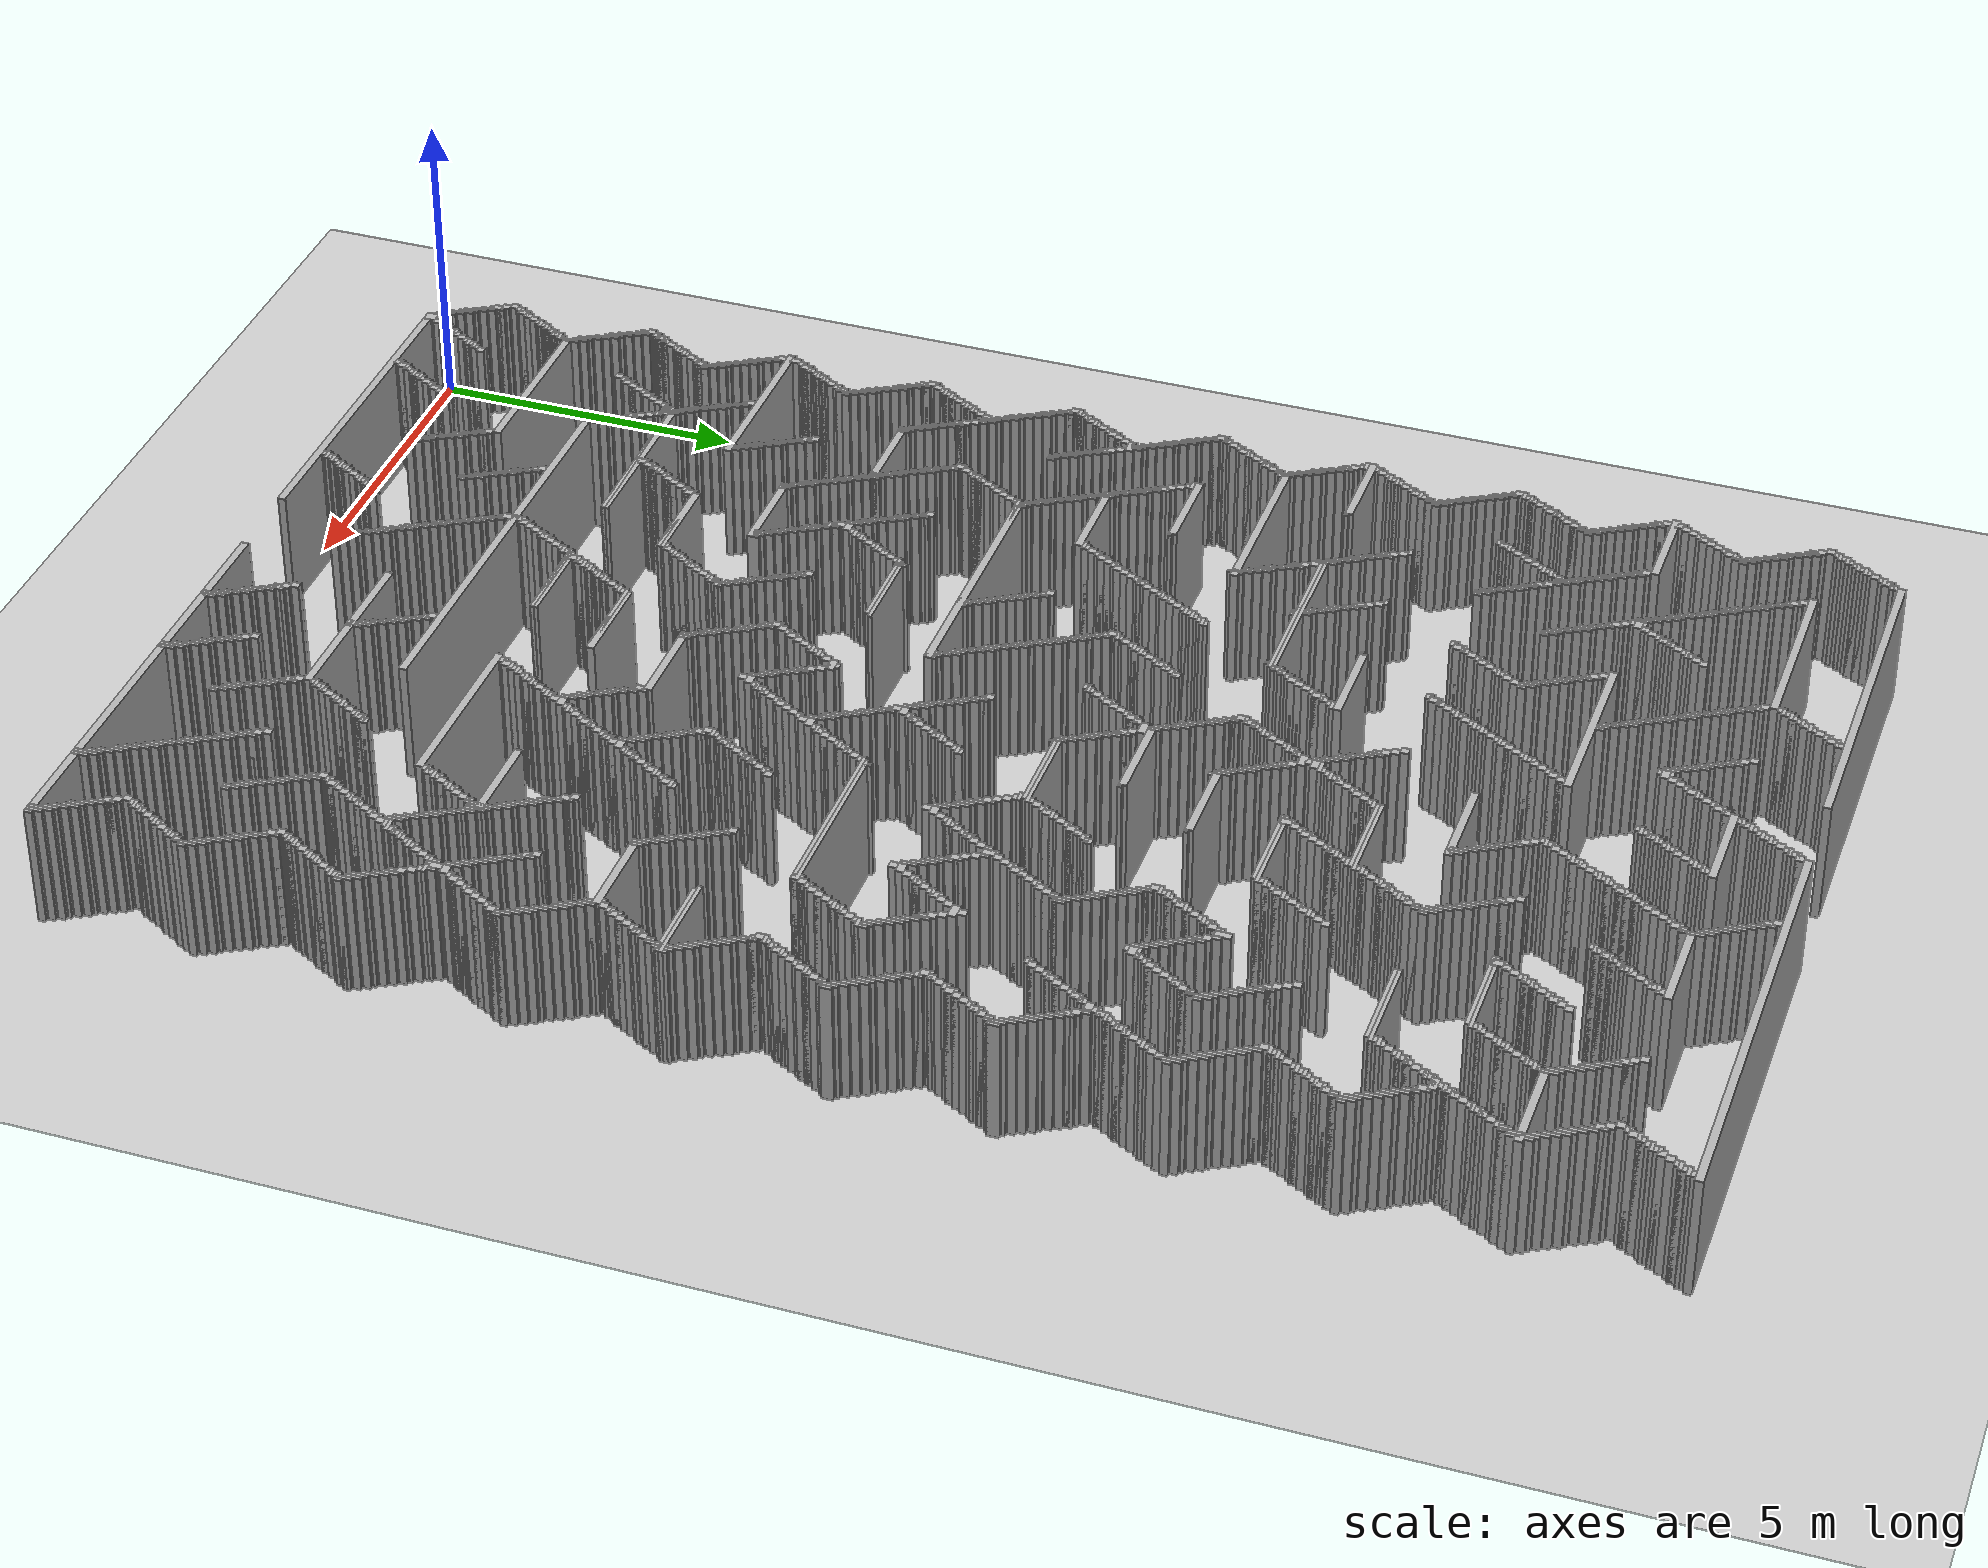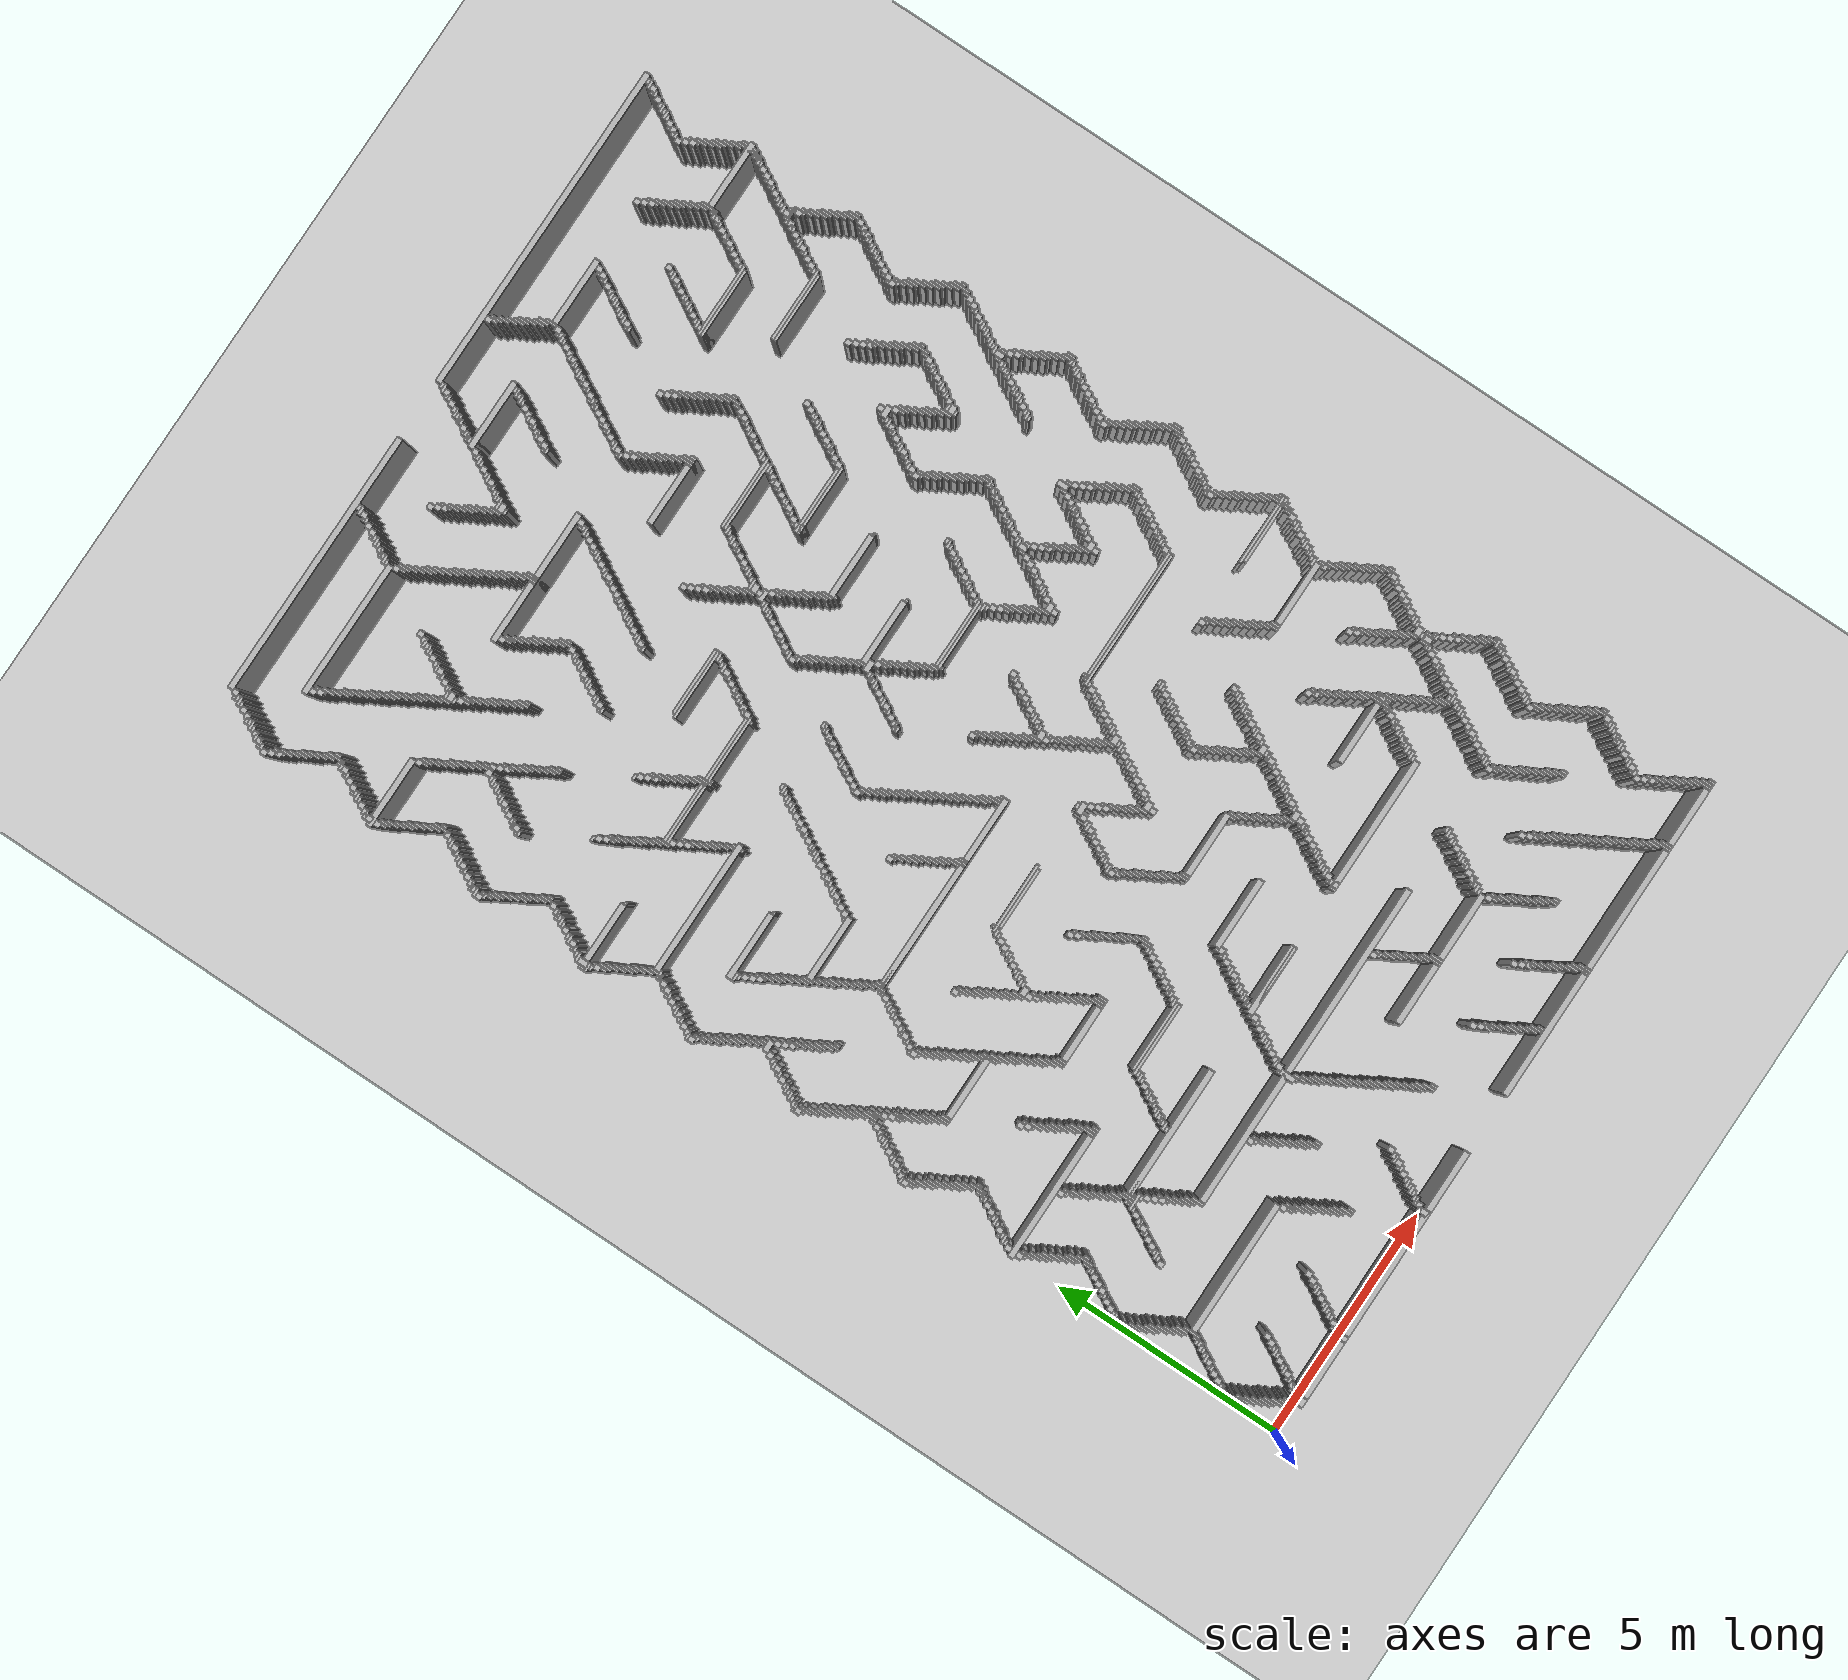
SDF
<?xml version="1.0" ?>
<sdf version="1.6">
  <world name="slam_world">
    <light name="sun" type="directional">
      <pose>0 0 10 0 0 0</pose>
      <diffuse>0.8 0.8 0.8 1</diffuse>
      <direction>-0.5 0.1 -0.9</direction>
    </light>
    <model name="ground_plane">
      <static>true</static>
      <link name="link">
        <collision name="collision">
          <geometry>
            <plane>
              <normal>0 0 1</normal>
              <size>100 100</size>
            </plane>
          </geometry>
        </collision>
        <visual name="visual">
          <geometry>
            <plane>
              <normal>0 0 1</normal>
              <size>100 100</size>
            </plane>
          </geometry>
          <material>
            <ambient>0.8 0.8 0.8 1</ambient>
            <diffuse>0.8 0.8 0.8 1</diffuse>
            <specular>0.8 0.8 0.8 1</specular>
          </material>
        </visual>
      </link>
    </model>
    <model name="wall_0">
      <static>true</static>
      <pose>3.6382978723404253 24.446808510638295 1.0 0 0 0</pose>
      <link name="link">
        <collision name="collision">
          <geometry>
            <box>
              <size>5.744680851063829 0.1276595744680851 2.0</size>
            </box>
          </geometry>
        </collision>
        <visual name="visual">
          <geometry>
            <box>
              <size>5.744680851063829 0.1276595744680851 2.0</size>
            </box>
          </geometry>
          <material>
            <ambient>0.5 0.5 0.5 1</ambient>
            <diffuse>0.7 0.7 0.7 1</diffuse>
          </material>
        </visual>
      </link>
    </model>
    <model name="wall_1">
      <static>true</static>
      <pose>11.361702127659573 24.446808510638295 1.0 0 0 0</pose>
      <link name="link">
        <collision name="collision">
          <geometry>
            <box>
              <size>7.148936170212766 0.1276595744680851 2.0</size>
            </box>
          </geometry>
        </collision>
        <visual name="visual">
          <geometry>
            <box>
              <size>7.148936170212766 0.1276595744680851 2.0</size>
            </box>
          </geometry>
          <material>
            <ambient>0.5 0.5 0.5 1</ambient>
            <diffuse>0.7 0.7 0.7 1</diffuse>
          </material>
        </visual>
      </link>
    </model>
    <model name="wall_2">
      <static>true</static>
      <pose>0.7659574468085106 24.319148936170212 1.0 0 0 0</pose>
      <link name="link">
        <collision name="collision">
          <geometry>
            <box>
              <size>0.1276595744680851 0.1276595744680851 2.0</size>
            </box>
          </geometry>
        </collision>
        <visual name="visual">
          <geometry>
            <box>
              <size>0.1276595744680851 0.1276595744680851 2.0</size>
            </box>
          </geometry>
          <material>
            <ambient>0.5 0.5 0.5 1</ambient>
            <diffuse>0.7 0.7 0.7 1</diffuse>
          </material>
        </visual>
      </link>
    </model>
    <model name="wall_3">
      <static>true</static>
      <pose>4.978723404255319 24.319148936170212 1.0 0 0 0</pose>
      <link name="link">
        <collision name="collision">
          <geometry>
            <box>
              <size>0.1276595744680851 0.1276595744680851 2.0</size>
            </box>
          </geometry>
        </collision>
        <visual name="visual">
          <geometry>
            <box>
              <size>0.1276595744680851 0.1276595744680851 2.0</size>
            </box>
          </geometry>
          <material>
            <ambient>0.5 0.5 0.5 1</ambient>
            <diffuse>0.7 0.7 0.7 1</diffuse>
          </material>
        </visual>
      </link>
    </model>
    <model name="wall_4">
      <static>true</static>
      <pose>7.787234042553191 24.319148936170212 1.0 0 0 0</pose>
      <link name="link">
        <collision name="collision">
          <geometry>
            <box>
              <size>0.1276595744680851 0.1276595744680851 2.0</size>
            </box>
          </geometry>
        </collision>
        <visual name="visual">
          <geometry>
            <box>
              <size>0.1276595744680851 0.1276595744680851 2.0</size>
            </box>
          </geometry>
          <material>
            <ambient>0.5 0.5 0.5 1</ambient>
            <diffuse>0.7 0.7 0.7 1</diffuse>
          </material>
        </visual>
      </link>
    </model>
    <model name="wall_5">
      <static>true</static>
      <pose>9.319148936170212 24.319148936170212 1.0 0 0 0</pose>
      <link name="link">
        <collision name="collision">
          <geometry>
            <box>
              <size>0.1276595744680851 0.1276595744680851 2.0</size>
            </box>
          </geometry>
        </collision>
        <visual name="visual">
          <geometry>
            <box>
              <size>0.1276595744680851 0.1276595744680851 2.0</size>
            </box>
          </geometry>
          <material>
            <ambient>0.5 0.5 0.5 1</ambient>
            <diffuse>0.7 0.7 0.7 1</diffuse>
          </material>
        </visual>
      </link>
    </model>
    <model name="wall_6">
      <static>true</static>
      <pose>14.808510638297872 24.319148936170212 1.0 0 0 0</pose>
      <link name="link">
        <collision name="collision">
          <geometry>
            <box>
              <size>0.1276595744680851 0.1276595744680851 2.0</size>
            </box>
          </geometry>
        </collision>
        <visual name="visual">
          <geometry>
            <box>
              <size>0.1276595744680851 0.1276595744680851 2.0</size>
            </box>
          </geometry>
          <material>
            <ambient>0.5 0.5 0.5 1</ambient>
            <diffuse>0.7 0.7 0.7 1</diffuse>
          </material>
        </visual>
      </link>
    </model>
    <model name="wall_7">
      <static>true</static>
      <pose>0.7340425531914893 24.28723404255319 1.0 0 0 0</pose>
      <link name="link">
        <collision name="collision">
          <geometry>
            <box>
              <size>0.19148936170212766 0.06382978723404255 2.0</size>
            </box>
          </geometry>
        </collision>
        <visual name="visual">
          <geometry>
            <box>
              <size>0.19148936170212766 0.06382978723404255 2.0</size>
            </box>
          </geometry>
          <material>
            <ambient>0.5 0.5 0.5 1</ambient>
            <diffuse>0.7 0.7 0.7 1</diffuse>
          </material>
        </visual>
      </link>
    </model>
    <model name="wall_8">
      <static>true</static>
      <pose>4.946808510638298 24.28723404255319 1.0 0 0 0</pose>
      <link name="link">
        <collision name="collision">
          <geometry>
            <box>
              <size>0.19148936170212766 0.06382978723404255 2.0</size>
            </box>
          </geometry>
        </collision>
        <visual name="visual">
          <geometry>
            <box>
              <size>0.19148936170212766 0.06382978723404255 2.0</size>
            </box>
          </geometry>
          <material>
            <ambient>0.5 0.5 0.5 1</ambient>
            <diffuse>0.7 0.7 0.7 1</diffuse>
          </material>
        </visual>
      </link>
    </model>
    <model name="wall_9">
      <static>true</static>
      <pose>7.755319148936169 24.28723404255319 1.0 0 0 0</pose>
      <link name="link">
        <collision name="collision">
          <geometry>
            <box>
              <size>0.19148936170212766 0.06382978723404255 2.0</size>
            </box>
          </geometry>
        </collision>
        <visual name="visual">
          <geometry>
            <box>
              <size>0.19148936170212766 0.06382978723404255 2.0</size>
            </box>
          </geometry>
          <material>
            <ambient>0.5 0.5 0.5 1</ambient>
            <diffuse>0.7 0.7 0.7 1</diffuse>
          </material>
        </visual>
      </link>
    </model>
    <model name="wall_10">
      <static>true</static>
      <pose>9.414893617021276 24.191489361702125 1.0 0 0 0</pose>
      <link name="link">
        <collision name="collision">
          <geometry>
            <box>
              <size>0.06382978723404255 0.2553191489361702 2.0</size>
            </box>
          </geometry>
        </collision>
        <visual name="visual">
          <geometry>
            <box>
              <size>0.06382978723404255 0.2553191489361702 2.0</size>
            </box>
          </geometry>
          <material>
            <ambient>0.5 0.5 0.5 1</ambient>
            <diffuse>0.7 0.7 0.7 1</diffuse>
          </material>
        </visual>
      </link>
    </model>
    <model name="wall_11">
      <static>true</static>
      <pose>14.77659574468085 24.28723404255319 1.0 0 0 0</pose>
      <link name="link">
        <collision name="collision">
          <geometry>
            <box>
              <size>0.19148936170212766 0.06382978723404255 2.0</size>
            </box>
          </geometry>
        </collision>
        <visual name="visual">
          <geometry>
            <box>
              <size>0.19148936170212766 0.06382978723404255 2.0</size>
            </box>
          </geometry>
          <material>
            <ambient>0.5 0.5 0.5 1</ambient>
            <diffuse>0.7 0.7 0.7 1</diffuse>
          </material>
        </visual>
      </link>
    </model>
    <model name="wall_12">
      <static>true</static>
      <pose>0.702127659574468 24.191489361702125 1.0 0 0 0</pose>
      <link name="link">
        <collision name="collision">
          <geometry>
            <box>
              <size>0.1276595744680851 0.1276595744680851 2.0</size>
            </box>
          </geometry>
        </collision>
        <visual name="visual">
          <geometry>
            <box>
              <size>0.1276595744680851 0.1276595744680851 2.0</size>
            </box>
          </geometry>
          <material>
            <ambient>0.5 0.5 0.5 1</ambient>
            <diffuse>0.7 0.7 0.7 1</diffuse>
          </material>
        </visual>
      </link>
    </model>
    <model name="wall_13">
      <static>true</static>
      <pose>4.914893617021276 24.191489361702125 1.0 0 0 0</pose>
      <link name="link">
        <collision name="collision">
          <geometry>
            <box>
              <size>0.1276595744680851 0.1276595744680851 2.0</size>
            </box>
          </geometry>
        </collision>
        <visual name="visual">
          <geometry>
            <box>
              <size>0.1276595744680851 0.1276595744680851 2.0</size>
            </box>
          </geometry>
          <material>
            <ambient>0.5 0.5 0.5 1</ambient>
            <diffuse>0.7 0.7 0.7 1</diffuse>
          </material>
        </visual>
      </link>
    </model>
    <model name="wall_14">
      <static>true</static>
      <pose>7.723404255319148 24.191489361702125 1.0 0 0 0</pose>
      <link name="link">
        <collision name="collision">
          <geometry>
            <box>
              <size>0.1276595744680851 0.1276595744680851 2.0</size>
            </box>
          </geometry>
        </collision>
        <visual name="visual">
          <geometry>
            <box>
              <size>0.1276595744680851 0.1276595744680851 2.0</size>
            </box>
          </geometry>
          <material>
            <ambient>0.5 0.5 0.5 1</ambient>
            <diffuse>0.7 0.7 0.7 1</diffuse>
          </material>
        </visual>
      </link>
    </model>
    <model name="wall_15">
      <static>true</static>
      <pose>9.382978723404255 24.191489361702125 1.0 0 0 0</pose>
      <link name="link">
        <collision name="collision">
          <geometry>
            <box>
              <size>0.1276595744680851 0.1276595744680851 2.0</size>
            </box>
          </geometry>
        </collision>
        <visual name="visual">
          <geometry>
            <box>
              <size>0.1276595744680851 0.1276595744680851 2.0</size>
            </box>
          </geometry>
          <material>
            <ambient>0.5 0.5 0.5 1</ambient>
            <diffuse>0.7 0.7 0.7 1</diffuse>
          </material>
        </visual>
      </link>
    </model>
    <model name="wall_16">
      <static>true</static>
      <pose>14.744680851063828 24.191489361702125 1.0 0 0 0</pose>
      <link name="link">
        <collision name="collision">
          <geometry>
            <box>
              <size>0.1276595744680851 0.1276595744680851 2.0</size>
            </box>
          </geometry>
        </collision>
        <visual name="visual">
          <geometry>
            <box>
              <size>0.1276595744680851 0.1276595744680851 2.0</size>
            </box>
          </geometry>
          <material>
            <ambient>0.5 0.5 0.5 1</ambient>
            <diffuse>0.7 0.7 0.7 1</diffuse>
          </material>
        </visual>
      </link>
    </model>
    <model name="wall_17">
      <static>true</static>
      <pose>0.6702127659574467 24.159574468085104 1.0 0 0 0</pose>
      <link name="link">
        <collision name="collision">
          <geometry>
            <box>
              <size>0.19148936170212766 0.06382978723404255 2.0</size>
            </box>
          </geometry>
        </collision>
        <visual name="visual">
          <geometry>
            <box>
              <size>0.19148936170212766 0.06382978723404255 2.0</size>
            </box>
          </geometry>
          <material>
            <ambient>0.5 0.5 0.5 1</ambient>
            <diffuse>0.7 0.7 0.7 1</diffuse>
          </material>
        </visual>
      </link>
    </model>
    <model name="wall_18">
      <static>true</static>
      <pose>4.882978723404255 24.159574468085104 1.0 0 0 0</pose>
      <link name="link">
        <collision name="collision">
          <geometry>
            <box>
              <size>0.19148936170212766 0.06382978723404255 2.0</size>
            </box>
          </geometry>
        </collision>
        <visual name="visual">
          <geometry>
            <box>
              <size>0.19148936170212766 0.06382978723404255 2.0</size>
            </box>
          </geometry>
          <material>
            <ambient>0.5 0.5 0.5 1</ambient>
            <diffuse>0.7 0.7 0.7 1</diffuse>
          </material>
        </visual>
      </link>
    </model>
    <model name="wall_19">
      <static>true</static>
      <pose>7.691489361702127 24.159574468085104 1.0 0 0 0</pose>
      <link name="link">
        <collision name="collision">
          <geometry>
            <box>
              <size>0.19148936170212766 0.06382978723404255 2.0</size>
            </box>
          </geometry>
        </collision>
        <visual name="visual">
          <geometry>
            <box>
              <size>0.19148936170212766 0.06382978723404255 2.0</size>
            </box>
          </geometry>
          <material>
            <ambient>0.5 0.5 0.5 1</ambient>
            <diffuse>0.7 0.7 0.7 1</diffuse>
          </material>
        </visual>
      </link>
    </model>
    <model name="wall_20">
      <static>true</static>
      <pose>9.478723404255318 24.06382978723404 1.0 0 0 0</pose>
      <link name="link">
        <collision name="collision">
          <geometry>
            <box>
              <size>0.06382978723404255 0.2553191489361702 2.0</size>
            </box>
          </geometry>
        </collision>
        <visual name="visual">
          <geometry>
            <box>
              <size>0.06382978723404255 0.2553191489361702 2.0</size>
            </box>
          </geometry>
          <material>
            <ambient>0.5 0.5 0.5 1</ambient>
            <diffuse>0.7 0.7 0.7 1</diffuse>
          </material>
        </visual>
      </link>
    </model>
    <model name="wall_21">
      <static>true</static>
      <pose>14.712765957446807 24.159574468085104 1.0 0 0 0</pose>
      <link name="link">
        <collision name="collision">
          <geometry>
            <box>
              <size>0.19148936170212766 0.06382978723404255 2.0</size>
            </box>
          </geometry>
        </collision>
        <visual name="visual">
          <geometry>
            <box>
              <size>0.19148936170212766 0.06382978723404255 2.0</size>
            </box>
          </geometry>
          <material>
            <ambient>0.5 0.5 0.5 1</ambient>
            <diffuse>0.7 0.7 0.7 1</diffuse>
          </material>
        </visual>
      </link>
    </model>
    <model name="wall_22">
      <static>true</static>
      <pose>0.6382978723404255 24.095744680851062 1.0 0 0 0</pose>
      <link name="link">
        <collision name="collision">
          <geometry>
            <box>
              <size>0.1276595744680851 0.06382978723404255 2.0</size>
            </box>
          </geometry>
        </collision>
        <visual name="visual">
          <geometry>
            <box>
              <size>0.1276595744680851 0.06382978723404255 2.0</size>
            </box>
          </geometry>
          <material>
            <ambient>0.5 0.5 0.5 1</ambient>
            <diffuse>0.7 0.7 0.7 1</diffuse>
          </material>
        </visual>
      </link>
    </model>
    <model name="wall_23">
      <static>true</static>
      <pose>4.8510638297872335 24.095744680851062 1.0 0 0 0</pose>
      <link name="link">
        <collision name="collision">
          <geometry>
            <box>
              <size>0.1276595744680851 0.06382978723404255 2.0</size>
            </box>
          </geometry>
        </collision>
        <visual name="visual">
          <geometry>
            <box>
              <size>0.1276595744680851 0.06382978723404255 2.0</size>
            </box>
          </geometry>
          <material>
            <ambient>0.5 0.5 0.5 1</ambient>
            <diffuse>0.7 0.7 0.7 1</diffuse>
          </material>
        </visual>
      </link>
    </model>
    <model name="wall_24">
      <static>true</static>
      <pose>7.659574468085106 24.095744680851062 1.0 0 0 0</pose>
      <link name="link">
        <collision name="collision">
          <geometry>
            <box>
              <size>0.1276595744680851 0.06382978723404255 2.0</size>
            </box>
          </geometry>
        </collision>
        <visual name="visual">
          <geometry>
            <box>
              <size>0.1276595744680851 0.06382978723404255 2.0</size>
            </box>
          </geometry>
          <material>
            <ambient>0.5 0.5 0.5 1</ambient>
            <diffuse>0.7 0.7 0.7 1</diffuse>
          </material>
        </visual>
      </link>
    </model>
    <model name="wall_25">
      <static>true</static>
      <pose>14.680851063829786 24.095744680851062 1.0 0 0 0</pose>
      <link name="link">
        <collision name="collision">
          <geometry>
            <box>
              <size>0.1276595744680851 0.06382978723404255 2.0</size>
            </box>
          </geometry>
        </collision>
        <visual name="visual">
          <geometry>
            <box>
              <size>0.1276595744680851 0.06382978723404255 2.0</size>
            </box>
          </geometry>
          <material>
            <ambient>0.5 0.5 0.5 1</ambient>
            <diffuse>0.7 0.7 0.7 1</diffuse>
          </material>
        </visual>
      </link>
    </model>
    <model name="wall_26">
      <static>true</static>
      <pose>0.5744680851063829 23.999999999999996 1.0 0 0 0</pose>
      <link name="link">
        <collision name="collision">
          <geometry>
            <box>
              <size>0.1276595744680851 0.1276595744680851 2.0</size>
            </box>
          </geometry>
        </collision>
        <visual name="visual">
          <geometry>
            <box>
              <size>0.1276595744680851 0.1276595744680851 2.0</size>
            </box>
          </geometry>
          <material>
            <ambient>0.5 0.5 0.5 1</ambient>
            <diffuse>0.7 0.7 0.7 1</diffuse>
          </material>
        </visual>
      </link>
    </model>
    <model name="wall_27">
      <static>true</static>
      <pose>4.787234042553191 23.999999999999996 1.0 0 0 0</pose>
      <link name="link">
        <collision name="collision">
          <geometry>
            <box>
              <size>0.1276595744680851 0.1276595744680851 2.0</size>
            </box>
          </geometry>
        </collision>
        <visual name="visual">
          <geometry>
            <box>
              <size>0.1276595744680851 0.1276595744680851 2.0</size>
            </box>
          </geometry>
          <material>
            <ambient>0.5 0.5 0.5 1</ambient>
            <diffuse>0.7 0.7 0.7 1</diffuse>
          </material>
        </visual>
      </link>
    </model>
    <model name="wall_28">
      <static>true</static>
      <pose>7.595744680851063 23.999999999999996 1.0 0 0 0</pose>
      <link name="link">
        <collision name="collision">
          <geometry>
            <box>
              <size>0.1276595744680851 0.1276595744680851 2.0</size>
            </box>
          </geometry>
        </collision>
        <visual name="visual">
          <geometry>
            <box>
              <size>0.1276595744680851 0.1276595744680851 2.0</size>
            </box>
          </geometry>
          <material>
            <ambient>0.5 0.5 0.5 1</ambient>
            <diffuse>0.7 0.7 0.7 1</diffuse>
          </material>
        </visual>
      </link>
    </model>
    <model name="wall_29">
      <static>true</static>
      <pose>9.542553191489361 23.936170212765955 1.0 0 0 0</pose>
      <link name="link">
        <collision name="collision">
          <geometry>
            <box>
              <size>0.06382978723404255 0.2553191489361702 2.0</size>
            </box>
          </geometry>
        </collision>
        <visual name="visual">
          <geometry>
            <box>
              <size>0.06382978723404255 0.2553191489361702 2.0</size>
            </box>
          </geometry>
          <material>
            <ambient>0.5 0.5 0.5 1</ambient>
            <diffuse>0.7 0.7 0.7 1</diffuse>
          </material>
        </visual>
      </link>
    </model>
    <model name="wall_30">
      <static>true</static>
      <pose>14.617021276595743 23.999999999999996 1.0 0 0 0</pose>
      <link name="link">
        <collision name="collision">
          <geometry>
            <box>
              <size>0.1276595744680851 0.1276595744680851 2.0</size>
            </box>
          </geometry>
        </collision>
        <visual name="visual">
          <geometry>
            <box>
              <size>0.1276595744680851 0.1276595744680851 2.0</size>
            </box>
          </geometry>
          <material>
            <ambient>0.5 0.5 0.5 1</ambient>
            <diffuse>0.7 0.7 0.7 1</diffuse>
          </material>
        </visual>
      </link>
    </model>
    <model name="wall_31">
      <static>true</static>
      <pose>0.5106382978723404 23.872340425531913 1.0 0 0 0</pose>
      <link name="link">
        <collision name="collision">
          <geometry>
            <box>
              <size>0.1276595744680851 0.1276595744680851 2.0</size>
            </box>
          </geometry>
        </collision>
        <visual name="visual">
          <geometry>
            <box>
              <size>0.1276595744680851 0.1276595744680851 2.0</size>
            </box>
          </geometry>
          <material>
            <ambient>0.5 0.5 0.5 1</ambient>
            <diffuse>0.7 0.7 0.7 1</diffuse>
          </material>
        </visual>
      </link>
    </model>
    <model name="wall_32">
      <static>true</static>
      <pose>4.723404255319148 23.872340425531913 1.0 0 0 0</pose>
      <link name="link">
        <collision name="collision">
          <geometry>
            <box>
              <size>0.1276595744680851 0.1276595744680851 2.0</size>
            </box>
          </geometry>
        </collision>
        <visual name="visual">
          <geometry>
            <box>
              <size>0.1276595744680851 0.1276595744680851 2.0</size>
            </box>
          </geometry>
          <material>
            <ambient>0.5 0.5 0.5 1</ambient>
            <diffuse>0.7 0.7 0.7 1</diffuse>
          </material>
        </visual>
      </link>
    </model>
    <model name="wall_33">
      <static>true</static>
      <pose>7.531914893617021 23.872340425531913 1.0 0 0 0</pose>
      <link name="link">
        <collision name="collision">
          <geometry>
            <box>
              <size>0.1276595744680851 0.1276595744680851 2.0</size>
            </box>
          </geometry>
        </collision>
        <visual name="visual">
          <geometry>
            <box>
              <size>0.1276595744680851 0.1276595744680851 2.0</size>
            </box>
          </geometry>
          <material>
            <ambient>0.5 0.5 0.5 1</ambient>
            <diffuse>0.7 0.7 0.7 1</diffuse>
          </material>
        </visual>
      </link>
    </model>
    <model name="wall_34">
      <static>true</static>
      <pose>9.606382978723403 23.80851063829787 1.0 0 0 0</pose>
      <link name="link">
        <collision name="collision">
          <geometry>
            <box>
              <size>0.06382978723404255 0.2553191489361702 2.0</size>
            </box>
          </geometry>
        </collision>
        <visual name="visual">
          <geometry>
            <box>
              <size>0.06382978723404255 0.2553191489361702 2.0</size>
            </box>
          </geometry>
          <material>
            <ambient>0.5 0.5 0.5 1</ambient>
            <diffuse>0.7 0.7 0.7 1</diffuse>
          </material>
        </visual>
      </link>
    </model>
    <model name="wall_35">
      <static>true</static>
      <pose>14.553191489361701 23.872340425531913 1.0 0 0 0</pose>
      <link name="link">
        <collision name="collision">
          <geometry>
            <box>
              <size>0.1276595744680851 0.1276595744680851 2.0</size>
            </box>
          </geometry>
        </collision>
        <visual name="visual">
          <geometry>
            <box>
              <size>0.1276595744680851 0.1276595744680851 2.0</size>
            </box>
          </geometry>
          <material>
            <ambient>0.5 0.5 0.5 1</ambient>
            <diffuse>0.7 0.7 0.7 1</diffuse>
          </material>
        </visual>
      </link>
    </model>
    <model name="wall_36">
      <static>true</static>
      <pose>0.4787234042553191 23.840425531914892 1.0 0 0 0</pose>
      <link name="link">
        <collision name="collision">
          <geometry>
            <box>
              <size>0.19148936170212766 0.06382978723404255 2.0</size>
            </box>
          </geometry>
        </collision>
        <visual name="visual">
          <geometry>
            <box>
              <size>0.19148936170212766 0.06382978723404255 2.0</size>
            </box>
          </geometry>
          <material>
            <ambient>0.5 0.5 0.5 1</ambient>
            <diffuse>0.7 0.7 0.7 1</diffuse>
          </material>
        </visual>
      </link>
    </model>
    <model name="wall_37">
      <static>true</static>
      <pose>4.691489361702128 23.840425531914892 1.0 0 0 0</pose>
      <link name="link">
        <collision name="collision">
          <geometry>
            <box>
              <size>0.19148936170212766 0.06382978723404255 2.0</size>
            </box>
          </geometry>
        </collision>
        <visual name="visual">
          <geometry>
            <box>
              <size>0.19148936170212766 0.06382978723404255 2.0</size>
            </box>
          </geometry>
          <material>
            <ambient>0.5 0.5 0.5 1</ambient>
            <diffuse>0.7 0.7 0.7 1</diffuse>
          </material>
        </visual>
      </link>
    </model>
    <model name="wall_38">
      <static>true</static>
      <pose>7.499999999999999 23.840425531914892 1.0 0 0 0</pose>
      <link name="link">
        <collision name="collision">
          <geometry>
            <box>
              <size>0.19148936170212766 0.06382978723404255 2.0</size>
            </box>
          </geometry>
        </collision>
        <visual name="visual">
          <geometry>
            <box>
              <size>0.19148936170212766 0.06382978723404255 2.0</size>
            </box>
          </geometry>
          <material>
            <ambient>0.5 0.5 0.5 1</ambient>
            <diffuse>0.7 0.7 0.7 1</diffuse>
          </material>
        </visual>
      </link>
    </model>
    <model name="wall_39">
      <static>true</static>
      <pose>9.670212765957446 23.744680851063826 1.0 0 0 0</pose>
      <link name="link">
        <collision name="collision">
          <geometry>
            <box>
              <size>0.06382978723404255 0.2553191489361702 2.0</size>
            </box>
          </geometry>
        </collision>
        <visual name="visual">
          <geometry>
            <box>
              <size>0.06382978723404255 0.2553191489361702 2.0</size>
            </box>
          </geometry>
          <material>
            <ambient>0.5 0.5 0.5 1</ambient>
            <diffuse>0.7 0.7 0.7 1</diffuse>
          </material>
        </visual>
      </link>
    </model>
    <model name="wall_40">
      <static>true</static>
      <pose>14.52127659574468 23.840425531914892 1.0 0 0 0</pose>
      <link name="link">
        <collision name="collision">
          <geometry>
            <box>
              <size>0.19148936170212766 0.06382978723404255 2.0</size>
            </box>
          </geometry>
        </collision>
        <visual name="visual">
          <geometry>
            <box>
              <size>0.19148936170212766 0.06382978723404255 2.0</size>
            </box>
          </geometry>
          <material>
            <ambient>0.5 0.5 0.5 1</ambient>
            <diffuse>0.7 0.7 0.7 1</diffuse>
          </material>
        </visual>
      </link>
    </model>
    <model name="wall_41">
      <static>true</static>
      <pose>0.44680851063829785 23.744680851063826 1.0 0 0 0</pose>
      <link name="link">
        <collision name="collision">
          <geometry>
            <box>
              <size>0.1276595744680851 0.1276595744680851 2.0</size>
            </box>
          </geometry>
        </collision>
        <visual name="visual">
          <geometry>
            <box>
              <size>0.1276595744680851 0.1276595744680851 2.0</size>
            </box>
          </geometry>
          <material>
            <ambient>0.5 0.5 0.5 1</ambient>
            <diffuse>0.7 0.7 0.7 1</diffuse>
          </material>
        </visual>
      </link>
    </model>
    <model name="wall_42">
      <static>true</static>
      <pose>4.659574468085106 23.744680851063826 1.0 0 0 0</pose>
      <link name="link">
        <collision name="collision">
          <geometry>
            <box>
              <size>0.1276595744680851 0.1276595744680851 2.0</size>
            </box>
          </geometry>
        </collision>
        <visual name="visual">
          <geometry>
            <box>
              <size>0.1276595744680851 0.1276595744680851 2.0</size>
            </box>
          </geometry>
          <material>
            <ambient>0.5 0.5 0.5 1</ambient>
            <diffuse>0.7 0.7 0.7 1</diffuse>
          </material>
        </visual>
      </link>
    </model>
    <model name="wall_43">
      <static>true</static>
      <pose>7.468085106382978 23.744680851063826 1.0 0 0 0</pose>
      <link name="link">
        <collision name="collision">
          <geometry>
            <box>
              <size>0.1276595744680851 0.1276595744680851 2.0</size>
            </box>
          </geometry>
        </collision>
        <visual name="visual">
          <geometry>
            <box>
              <size>0.1276595744680851 0.1276595744680851 2.0</size>
            </box>
          </geometry>
          <material>
            <ambient>0.5 0.5 0.5 1</ambient>
            <diffuse>0.7 0.7 0.7 1</diffuse>
          </material>
        </visual>
      </link>
    </model>
    <model name="wall_44">
      <static>true</static>
      <pose>14.489361702127658 23.744680851063826 1.0 0 0 0</pose>
      <link name="link">
        <collision name="collision">
          <geometry>
            <box>
              <size>0.1276595744680851 0.1276595744680851 2.0</size>
            </box>
          </geometry>
        </collision>
        <visual name="visual">
          <geometry>
            <box>
              <size>0.1276595744680851 0.1276595744680851 2.0</size>
            </box>
          </geometry>
          <material>
            <ambient>0.5 0.5 0.5 1</ambient>
            <diffuse>0.7 0.7 0.7 1</diffuse>
          </material>
        </visual>
      </link>
    </model>
    <model name="wall_45">
      <static>true</static>
      <pose>0.4148936170212766 23.712765957446805 1.0 0 0 0</pose>
      <link name="link">
        <collision name="collision">
          <geometry>
            <box>
              <size>0.19148936170212766 0.06382978723404255 2.0</size>
            </box>
          </geometry>
        </collision>
        <visual name="visual">
          <geometry>
            <box>
              <size>0.19148936170212766 0.06382978723404255 2.0</size>
            </box>
          </geometry>
          <material>
            <ambient>0.5 0.5 0.5 1</ambient>
            <diffuse>0.7 0.7 0.7 1</diffuse>
          </material>
        </visual>
      </link>
    </model>
    <model name="wall_46">
      <static>true</static>
      <pose>4.627659574468085 23.712765957446805 1.0 0 0 0</pose>
      <link name="link">
        <collision name="collision">
          <geometry>
            <box>
              <size>0.19148936170212766 0.06382978723404255 2.0</size>
            </box>
          </geometry>
        </collision>
        <visual name="visual">
          <geometry>
            <box>
              <size>0.19148936170212766 0.06382978723404255 2.0</size>
            </box>
          </geometry>
          <material>
            <ambient>0.5 0.5 0.5 1</ambient>
            <diffuse>0.7 0.7 0.7 1</diffuse>
          </material>
        </visual>
      </link>
    </model>
    <model name="wall_47">
      <static>true</static>
      <pose>7.436170212765957 23.712765957446805 1.0 0 0 0</pose>
      <link name="link">
        <collision name="collision">
          <geometry>
            <box>
              <size>0.19148936170212766 0.06382978723404255 2.0</size>
            </box>
          </geometry>
        </collision>
        <visual name="visual">
          <geometry>
            <box>
              <size>0.19148936170212766 0.06382978723404255 2.0</size>
            </box>
          </geometry>
          <material>
            <ambient>0.5 0.5 0.5 1</ambient>
            <diffuse>0.7 0.7 0.7 1</diffuse>
          </material>
        </visual>
      </link>
    </model>
    <model name="wall_48">
      <static>true</static>
      <pose>9.734042553191488 23.617021276595743 1.0 0 0 0</pose>
      <link name="link">
        <collision name="collision">
          <geometry>
            <box>
              <size>0.06382978723404255 0.2553191489361702 2.0</size>
            </box>
          </geometry>
        </collision>
        <visual name="visual">
          <geometry>
            <box>
              <size>0.06382978723404255 0.2553191489361702 2.0</size>
            </box>
          </geometry>
          <material>
            <ambient>0.5 0.5 0.5 1</ambient>
            <diffuse>0.7 0.7 0.7 1</diffuse>
          </material>
        </visual>
      </link>
    </model>
    <model name="wall_49">
      <static>true</static>
      <pose>14.457446808510637 23.712765957446805 1.0 0 0 0</pose>
      <link name="link">
        <collision name="collision">
          <geometry>
            <box>
              <size>0.19148936170212766 0.06382978723404255 2.0</size>
            </box>
          </geometry>
        </collision>
        <visual name="visual">
          <geometry>
            <box>
              <size>0.19148936170212766 0.06382978723404255 2.0</size>
            </box>
          </geometry>
          <material>
            <ambient>0.5 0.5 0.5 1</ambient>
            <diffuse>0.7 0.7 0.7 1</diffuse>
          </material>
        </visual>
      </link>
    </model>
    <model name="wall_50">
      <static>true</static>
      <pose>0.3829787234042553 23.648936170212764 1.0 0 0 0</pose>
      <link name="link">
        <collision name="collision">
          <geometry>
            <box>
              <size>0.1276595744680851 0.06382978723404255 2.0</size>
            </box>
          </geometry>
        </collision>
        <visual name="visual">
          <geometry>
            <box>
              <size>0.1276595744680851 0.06382978723404255 2.0</size>
            </box>
          </geometry>
          <material>
            <ambient>0.5 0.5 0.5 1</ambient>
            <diffuse>0.7 0.7 0.7 1</diffuse>
          </material>
        </visual>
      </link>
    </model>
    <model name="wall_51">
      <static>true</static>
      <pose>4.595744680851063 23.648936170212764 1.0 0 0 0</pose>
      <link name="link">
        <collision name="collision">
          <geometry>
            <box>
              <size>0.1276595744680851 0.06382978723404255 2.0</size>
            </box>
          </geometry>
        </collision>
        <visual name="visual">
          <geometry>
            <box>
              <size>0.1276595744680851 0.06382978723404255 2.0</size>
            </box>
          </geometry>
          <material>
            <ambient>0.5 0.5 0.5 1</ambient>
            <diffuse>0.7 0.7 0.7 1</diffuse>
          </material>
        </visual>
      </link>
    </model>
    <model name="wall_52">
      <static>true</static>
      <pose>7.404255319148936 23.648936170212764 1.0 0 0 0</pose>
      <link name="link">
        <collision name="collision">
          <geometry>
            <box>
              <size>0.1276595744680851 0.06382978723404255 2.0</size>
            </box>
          </geometry>
        </collision>
        <visual name="visual">
          <geometry>
            <box>
              <size>0.1276595744680851 0.06382978723404255 2.0</size>
            </box>
          </geometry>
          <material>
            <ambient>0.5 0.5 0.5 1</ambient>
            <diffuse>0.7 0.7 0.7 1</diffuse>
          </material>
        </visual>
      </link>
    </model>
    <model name="wall_53">
      <static>true</static>
      <pose>14.425531914893616 23.648936170212764 1.0 0 0 0</pose>
      <link name="link">
        <collision name="collision">
          <geometry>
            <box>
              <size>0.1276595744680851 0.06382978723404255 2.0</size>
            </box>
          </geometry>
        </collision>
        <visual name="visual">
          <geometry>
            <box>
              <size>0.1276595744680851 0.06382978723404255 2.0</size>
            </box>
          </geometry>
          <material>
            <ambient>0.5 0.5 0.5 1</ambient>
            <diffuse>0.7 0.7 0.7 1</diffuse>
          </material>
        </visual>
      </link>
    </model>
    <model name="wall_54">
      <static>true</static>
      <pose>0.3191489361702127 23.5531914893617 1.0 0 0 0</pose>
      <link name="link">
        <collision name="collision">
          <geometry>
            <box>
              <size>0.1276595744680851 0.1276595744680851 2.0</size>
            </box>
          </geometry>
        </collision>
        <visual name="visual">
          <geometry>
            <box>
              <size>0.1276595744680851 0.1276595744680851 2.0</size>
            </box>
          </geometry>
          <material>
            <ambient>0.5 0.5 0.5 1</ambient>
            <diffuse>0.7 0.7 0.7 1</diffuse>
          </material>
        </visual>
      </link>
    </model>
    <model name="wall_55">
      <static>true</static>
      <pose>4.531914893617021 23.5531914893617 1.0 0 0 0</pose>
      <link name="link">
        <collision name="collision">
          <geometry>
            <box>
              <size>0.1276595744680851 0.1276595744680851 2.0</size>
            </box>
          </geometry>
        </collision>
        <visual name="visual">
          <geometry>
            <box>
              <size>0.1276595744680851 0.1276595744680851 2.0</size>
            </box>
          </geometry>
          <material>
            <ambient>0.5 0.5 0.5 1</ambient>
            <diffuse>0.7 0.7 0.7 1</diffuse>
          </material>
        </visual>
      </link>
    </model>
    <model name="wall_56">
      <static>true</static>
      <pose>7.340425531914893 23.5531914893617 1.0 0 0 0</pose>
      <link name="link">
        <collision name="collision">
          <geometry>
            <box>
              <size>0.1276595744680851 0.1276595744680851 2.0</size>
            </box>
          </geometry>
        </collision>
        <visual name="visual">
          <geometry>
            <box>
              <size>0.1276595744680851 0.1276595744680851 2.0</size>
            </box>
          </geometry>
          <material>
            <ambient>0.5 0.5 0.5 1</ambient>
            <diffuse>0.7 0.7 0.7 1</diffuse>
          </material>
        </visual>
      </link>
    </model>
    <model name="wall_57">
      <static>true</static>
      <pose>9.797872340425531 23.489361702127656 1.0 0 0 0</pose>
      <link name="link">
        <collision name="collision">
          <geometry>
            <box>
              <size>0.06382978723404255 0.2553191489361702 2.0</size>
            </box>
          </geometry>
        </collision>
        <visual name="visual">
          <geometry>
            <box>
              <size>0.06382978723404255 0.2553191489361702 2.0</size>
            </box>
          </geometry>
          <material>
            <ambient>0.5 0.5 0.5 1</ambient>
            <diffuse>0.7 0.7 0.7 1</diffuse>
          </material>
        </visual>
      </link>
    </model>
    <model name="wall_58">
      <static>true</static>
      <pose>14.361702127659573 23.5531914893617 1.0 0 0 0</pose>
      <link name="link">
        <collision name="collision">
          <geometry>
            <box>
              <size>0.1276595744680851 0.1276595744680851 2.0</size>
            </box>
          </geometry>
        </collision>
        <visual name="visual">
          <geometry>
            <box>
              <size>0.1276595744680851 0.1276595744680851 2.0</size>
            </box>
          </geometry>
          <material>
            <ambient>0.5 0.5 0.5 1</ambient>
            <diffuse>0.7 0.7 0.7 1</diffuse>
          </material>
        </visual>
      </link>
    </model>
    <model name="wall_59">
      <static>true</static>
      <pose>0.28723404255319146 23.52127659574468 1.0 0 0 0</pose>
      <link name="link">
        <collision name="collision">
          <geometry>
            <box>
              <size>0.19148936170212766 0.06382978723404255 2.0</size>
            </box>
          </geometry>
        </collision>
        <visual name="visual">
          <geometry>
            <box>
              <size>0.19148936170212766 0.06382978723404255 2.0</size>
            </box>
          </geometry>
          <material>
            <ambient>0.5 0.5 0.5 1</ambient>
            <diffuse>0.7 0.7 0.7 1</diffuse>
          </material>
        </visual>
      </link>
    </model>
    <model name="wall_60">
      <static>true</static>
      <pose>4.5 23.52127659574468 1.0 0 0 0</pose>
      <link name="link">
        <collision name="collision">
          <geometry>
            <box>
              <size>0.19148936170212766 0.06382978723404255 2.0</size>
            </box>
          </geometry>
        </collision>
        <visual name="visual">
          <geometry>
            <box>
              <size>0.19148936170212766 0.06382978723404255 2.0</size>
            </box>
          </geometry>
          <material>
            <ambient>0.5 0.5 0.5 1</ambient>
            <diffuse>0.7 0.7 0.7 1</diffuse>
          </material>
        </visual>
      </link>
    </model>
    <model name="wall_61">
      <static>true</static>
      <pose>7.3085106382978715 23.52127659574468 1.0 0 0 0</pose>
      <link name="link">
        <collision name="collision">
          <geometry>
            <box>
              <size>0.19148936170212766 0.06382978723404255 2.0</size>
            </box>
          </geometry>
        </collision>
        <visual name="visual">
          <geometry>
            <box>
              <size>0.19148936170212766 0.06382978723404255 2.0</size>
            </box>
          </geometry>
          <material>
            <ambient>0.5 0.5 0.5 1</ambient>
            <diffuse>0.7 0.7 0.7 1</diffuse>
          </material>
        </visual>
      </link>
    </model>
    <model name="wall_62">
      <static>true</static>
      <pose>9.861702127659573 23.425531914893615 1.0 0 0 0</pose>
      <link name="link">
        <collision name="collision">
          <geometry>
            <box>
              <size>0.06382978723404255 0.2553191489361702 2.0</size>
            </box>
          </geometry>
        </collision>
        <visual name="visual">
          <geometry>
            <box>
              <size>0.06382978723404255 0.2553191489361702 2.0</size>
            </box>
          </geometry>
          <material>
            <ambient>0.5 0.5 0.5 1</ambient>
            <diffuse>0.7 0.7 0.7 1</diffuse>
          </material>
        </visual>
      </link>
    </model>
    <model name="wall_63">
      <static>true</static>
      <pose>14.329787234042552 23.52127659574468 1.0 0 0 0</pose>
      <link name="link">
        <collision name="collision">
          <geometry>
            <box>
              <size>0.19148936170212766 0.06382978723404255 2.0</size>
            </box>
          </geometry>
        </collision>
        <visual name="visual">
          <geometry>
            <box>
              <size>0.19148936170212766 0.06382978723404255 2.0</size>
            </box>
          </geometry>
          <material>
            <ambient>0.5 0.5 0.5 1</ambient>
            <diffuse>0.7 0.7 0.7 1</diffuse>
          </material>
        </visual>
      </link>
    </model>
    <model name="wall_64">
      <static>true</static>
      <pose>0.2553191489361702 23.425531914893615 1.0 0 0 0</pose>
      <link name="link">
        <collision name="collision">
          <geometry>
            <box>
              <size>0.1276595744680851 0.1276595744680851 2.0</size>
            </box>
          </geometry>
        </collision>
        <visual name="visual">
          <geometry>
            <box>
              <size>0.1276595744680851 0.1276595744680851 2.0</size>
            </box>
          </geometry>
          <material>
            <ambient>0.5 0.5 0.5 1</ambient>
            <diffuse>0.7 0.7 0.7 1</diffuse>
          </material>
        </visual>
      </link>
    </model>
    <model name="wall_65">
      <static>true</static>
      <pose>4.468085106382978 23.425531914893615 1.0 0 0 0</pose>
      <link name="link">
        <collision name="collision">
          <geometry>
            <box>
              <size>0.1276595744680851 0.1276595744680851 2.0</size>
            </box>
          </geometry>
        </collision>
        <visual name="visual">
          <geometry>
            <box>
              <size>0.1276595744680851 0.1276595744680851 2.0</size>
            </box>
          </geometry>
          <material>
            <ambient>0.5 0.5 0.5 1</ambient>
            <diffuse>0.7 0.7 0.7 1</diffuse>
          </material>
        </visual>
      </link>
    </model>
    <model name="wall_66">
      <static>true</static>
      <pose>7.276595744680851 23.425531914893615 1.0 0 0 0</pose>
      <link name="link">
        <collision name="collision">
          <geometry>
            <box>
              <size>0.1276595744680851 0.1276595744680851 2.0</size>
            </box>
          </geometry>
        </collision>
        <visual name="visual">
          <geometry>
            <box>
              <size>0.1276595744680851 0.1276595744680851 2.0</size>
            </box>
          </geometry>
          <material>
            <ambient>0.5 0.5 0.5 1</ambient>
            <diffuse>0.7 0.7 0.7 1</diffuse>
          </material>
        </visual>
      </link>
    </model>
    <model name="wall_67">
      <static>true</static>
      <pose>14.297872340425531 23.425531914893615 1.0 0 0 0</pose>
      <link name="link">
        <collision name="collision">
          <geometry>
            <box>
              <size>0.1276595744680851 0.1276595744680851 2.0</size>
            </box>
          </geometry>
        </collision>
        <visual name="visual">
          <geometry>
            <box>
              <size>0.1276595744680851 0.1276595744680851 2.0</size>
            </box>
          </geometry>
          <material>
            <ambient>0.5 0.5 0.5 1</ambient>
            <diffuse>0.7 0.7 0.7 1</diffuse>
          </material>
        </visual>
      </link>
    </model>
    <model name="wall_68">
      <static>true</static>
      <pose>0.22340425531914893 23.393617021276594 1.0 0 0 0</pose>
      <link name="link">
        <collision name="collision">
          <geometry>
            <box>
              <size>0.19148936170212766 0.06382978723404255 2.0</size>
            </box>
          </geometry>
        </collision>
        <visual name="visual">
          <geometry>
            <box>
              <size>0.19148936170212766 0.06382978723404255 2.0</size>
            </box>
          </geometry>
          <material>
            <ambient>0.5 0.5 0.5 1</ambient>
            <diffuse>0.7 0.7 0.7 1</diffuse>
          </material>
        </visual>
      </link>
    </model>
    <model name="wall_69">
      <static>true</static>
      <pose>4.4361702127659575 23.393617021276594 1.0 0 0 0</pose>
      <link name="link">
        <collision name="collision">
          <geometry>
            <box>
              <size>0.19148936170212766 0.06382978723404255 2.0</size>
            </box>
          </geometry>
        </collision>
        <visual name="visual">
          <geometry>
            <box>
              <size>0.19148936170212766 0.06382978723404255 2.0</size>
            </box>
          </geometry>
          <material>
            <ambient>0.5 0.5 0.5 1</ambient>
            <diffuse>0.7 0.7 0.7 1</diffuse>
          </material>
        </visual>
      </link>
    </model>
    <model name="wall_70">
      <static>true</static>
      <pose>7.244680851063829 23.393617021276594 1.0 0 0 0</pose>
      <link name="link">
        <collision name="collision">
          <geometry>
            <box>
              <size>0.19148936170212766 0.06382978723404255 2.0</size>
            </box>
          </geometry>
        </collision>
        <visual name="visual">
          <geometry>
            <box>
              <size>0.19148936170212766 0.06382978723404255 2.0</size>
            </box>
          </geometry>
          <material>
            <ambient>0.5 0.5 0.5 1</ambient>
            <diffuse>0.7 0.7 0.7 1</diffuse>
          </material>
        </visual>
      </link>
    </model>
    <model name="wall_71">
      <static>true</static>
      <pose>9.925531914893616 23.234042553191486 1.0 0 0 0</pose>
      <link name="link">
        <collision name="collision">
          <geometry>
            <box>
              <size>0.06382978723404255 0.3829787234042553 2.0</size>
            </box>
          </geometry>
        </collision>
        <visual name="visual">
          <geometry>
            <box>
              <size>0.06382978723404255 0.3829787234042553 2.0</size>
            </box>
          </geometry>
          <material>
            <ambient>0.5 0.5 0.5 1</ambient>
            <diffuse>0.7 0.7 0.7 1</diffuse>
          </material>
        </visual>
      </link>
    </model>
    <model name="wall_72">
      <static>true</static>
      <pose>14.265957446808509 23.393617021276594 1.0 0 0 0</pose>
      <link name="link">
        <collision name="collision">
          <geometry>
            <box>
              <size>0.19148936170212766 0.06382978723404255 2.0</size>
            </box>
          </geometry>
        </collision>
        <visual name="visual">
          <geometry>
            <box>
              <size>0.19148936170212766 0.06382978723404255 2.0</size>
            </box>
          </geometry>
          <material>
            <ambient>0.5 0.5 0.5 1</ambient>
            <diffuse>0.7 0.7 0.7 1</diffuse>
          </material>
        </visual>
      </link>
    </model>
    <model name="wall_73">
      <static>true</static>
      <pose>0.19148936170212766 23.329787234042552 1.0 0 0 0</pose>
      <link name="link">
        <collision name="collision">
          <geometry>
            <box>
              <size>0.1276595744680851 0.06382978723404255 2.0</size>
            </box>
          </geometry>
        </collision>
        <visual name="visual">
          <geometry>
            <box>
              <size>0.1276595744680851 0.06382978723404255 2.0</size>
            </box>
          </geometry>
          <material>
            <ambient>0.5 0.5 0.5 1</ambient>
            <diffuse>0.7 0.7 0.7 1</diffuse>
          </material>
        </visual>
      </link>
    </model>
    <model name="wall_74">
      <static>true</static>
      <pose>4.404255319148936 23.329787234042552 1.0 0 0 0</pose>
      <link name="link">
        <collision name="collision">
          <geometry>
            <box>
              <size>0.1276595744680851 0.06382978723404255 2.0</size>
            </box>
          </geometry>
        </collision>
        <visual name="visual">
          <geometry>
            <box>
              <size>0.1276595744680851 0.06382978723404255 2.0</size>
            </box>
          </geometry>
          <material>
            <ambient>0.5 0.5 0.5 1</ambient>
            <diffuse>0.7 0.7 0.7 1</diffuse>
          </material>
        </visual>
      </link>
    </model>
    <model name="wall_75">
      <static>true</static>
      <pose>7.212765957446808 23.26595744680851 1.0 0 0 0</pose>
      <link name="link">
        <collision name="collision">
          <geometry>
            <box>
              <size>0.1276595744680851 0.19148936170212766 2.0</size>
            </box>
          </geometry>
        </collision>
        <visual name="visual">
          <geometry>
            <box>
              <size>0.1276595744680851 0.19148936170212766 2.0</size>
            </box>
          </geometry>
          <material>
            <ambient>0.5 0.5 0.5 1</ambient>
            <diffuse>0.7 0.7 0.7 1</diffuse>
          </material>
        </visual>
      </link>
    </model>
    <model name="wall_76">
      <static>true</static>
      <pose>14.234042553191488 23.329787234042552 1.0 0 0 0</pose>
      <link name="link">
        <collision name="collision">
          <geometry>
            <box>
              <size>0.1276595744680851 0.06382978723404255 2.0</size>
            </box>
          </geometry>
        </collision>
        <visual name="visual">
          <geometry>
            <box>
              <size>0.1276595744680851 0.06382978723404255 2.0</size>
            </box>
          </geometry>
          <material>
            <ambient>0.5 0.5 0.5 1</ambient>
            <diffuse>0.7 0.7 0.7 1</diffuse>
          </material>
        </visual>
      </link>
    </model>
    <model name="wall_77">
      <static>true</static>
      <pose>0.1276595744680851 23.234042553191486 1.0 0 0 0</pose>
      <link name="link">
        <collision name="collision">
          <geometry>
            <box>
              <size>0.1276595744680851 0.1276595744680851 2.0</size>
            </box>
          </geometry>
        </collision>
        <visual name="visual">
          <geometry>
            <box>
              <size>0.1276595744680851 0.1276595744680851 2.0</size>
            </box>
          </geometry>
          <material>
            <ambient>0.5 0.5 0.5 1</ambient>
            <diffuse>0.7 0.7 0.7 1</diffuse>
          </material>
        </visual>
      </link>
    </model>
    <model name="wall_78">
      <static>true</static>
      <pose>2.936170212765957 23.234042553191486 1.0 0 0 0</pose>
      <link name="link">
        <collision name="collision">
          <geometry>
            <box>
              <size>2.936170212765957 0.1276595744680851 2.0</size>
            </box>
          </geometry>
        </collision>
        <visual name="visual">
          <geometry>
            <box>
              <size>2.936170212765957 0.1276595744680851 2.0</size>
            </box>
          </geometry>
          <material>
            <ambient>0.5 0.5 0.5 1</ambient>
            <diffuse>0.7 0.7 0.7 1</diffuse>
          </material>
        </visual>
      </link>
    </model>
    <model name="wall_79">
      <static>true</static>
      <pose>5.744680851063829 23.234042553191486 1.0 0 0 0</pose>
      <link name="link">
        <collision name="collision">
          <geometry>
            <box>
              <size>0.1276595744680851 0.1276595744680851 2.0</size>
            </box>
          </geometry>
        </collision>
        <visual name="visual">
          <geometry>
            <box>
              <size>0.1276595744680851 0.1276595744680851 2.0</size>
            </box>
          </geometry>
          <material>
            <ambient>0.5 0.5 0.5 1</ambient>
            <diffuse>0.7 0.7 0.7 1</diffuse>
          </material>
        </visual>
      </link>
    </model>
    <model name="wall_80">
      <static>true</static>
      <pose>7.8510638297872335 23.234042553191486 1.0 0 0 0</pose>
      <link name="link">
        <collision name="collision">
          <geometry>
            <box>
              <size>1.5319148936170213 0.1276595744680851 2.0</size>
            </box>
          </geometry>
        </collision>
        <visual name="visual">
          <geometry>
            <box>
              <size>1.5319148936170213 0.1276595744680851 2.0</size>
            </box>
          </geometry>
          <material>
            <ambient>0.5 0.5 0.5 1</ambient>
            <diffuse>0.7 0.7 0.7 1</diffuse>
          </material>
        </visual>
      </link>
    </model>
    <model name="wall_81">
      <static>true</static>
      <pose>10.691489361702127 23.234042553191486 1.0 0 0 0</pose>
      <link name="link">
        <collision name="collision">
          <geometry>
            <box>
              <size>1.4680851063829785 0.1276595744680851 2.0</size>
            </box>
          </geometry>
        </collision>
        <visual name="visual">
          <geometry>
            <box>
              <size>1.4680851063829785 0.1276595744680851 2.0</size>
            </box>
          </geometry>
          <material>
            <ambient>0.5 0.5 0.5 1</ambient>
            <diffuse>0.7 0.7 0.7 1</diffuse>
          </material>
        </visual>
      </link>
    </model>
    <model name="wall_82">
      <static>true</static>
      <pose>12.76595744680851 23.234042553191486 1.0 0 0 0</pose>
      <link name="link">
        <collision name="collision">
          <geometry>
            <box>
              <size>0.1276595744680851 0.1276595744680851 2.0</size>
            </box>
          </geometry>
        </collision>
        <visual name="visual">
          <geometry>
            <box>
              <size>0.1276595744680851 0.1276595744680851 2.0</size>
            </box>
          </geometry>
          <material>
            <ambient>0.5 0.5 0.5 1</ambient>
            <diffuse>0.7 0.7 0.7 1</diffuse>
          </material>
        </visual>
      </link>
    </model>
    <model name="wall_83">
      <static>true</static>
      <pose>14.170212765957446 23.234042553191486 1.0 0 0 0</pose>
      <link name="link">
        <collision name="collision">
          <geometry>
            <box>
              <size>0.1276595744680851 0.1276595744680851 2.0</size>
            </box>
          </geometry>
        </collision>
        <visual name="visual">
          <geometry>
            <box>
              <size>0.1276595744680851 0.1276595744680851 2.0</size>
            </box>
          </geometry>
          <material>
            <ambient>0.5 0.5 0.5 1</ambient>
            <diffuse>0.7 0.7 0.7 1</diffuse>
          </material>
        </visual>
      </link>
    </model>
    <model name="wall_84">
      <static>true</static>
      <pose>0.19148936170212766 23.106382978723403 1.0 0 0 0</pose>
      <link name="link">
        <collision name="collision">
          <geometry>
            <box>
              <size>0.1276595744680851 0.1276595744680851 2.0</size>
            </box>
          </geometry>
        </collision>
        <visual name="visual">
          <geometry>
            <box>
              <size>0.1276595744680851 0.1276595744680851 2.0</size>
            </box>
          </geometry>
          <material>
            <ambient>0.5 0.5 0.5 1</ambient>
            <diffuse>0.7 0.7 0.7 1</diffuse>
          </material>
        </visual>
      </link>
    </model>
    <model name="wall_85">
      <static>true</static>
      <pose>1.5957446808510638 23.106382978723403 1.0 0 0 0</pose>
      <link name="link">
        <collision name="collision">
          <geometry>
            <box>
              <size>0.1276595744680851 0.1276595744680851 2.0</size>
            </box>
          </geometry>
        </collision>
        <visual name="visual">
          <geometry>
            <box>
              <size>0.1276595744680851 0.1276595744680851 2.0</size>
            </box>
          </geometry>
          <material>
            <ambient>0.5 0.5 0.5 1</ambient>
            <diffuse>0.7 0.7 0.7 1</diffuse>
          </material>
        </visual>
      </link>
    </model>
    <model name="wall_86">
      <static>true</static>
      <pose>4.404255319148936 23.106382978723403 1.0 0 0 0</pose>
      <link name="link">
        <collision name="collision">
          <geometry>
            <box>
              <size>0.1276595744680851 0.1276595744680851 2.0</size>
            </box>
          </geometry>
        </collision>
        <visual name="visual">
          <geometry>
            <box>
              <size>0.1276595744680851 0.1276595744680851 2.0</size>
            </box>
          </geometry>
          <material>
            <ambient>0.5 0.5 0.5 1</ambient>
            <diffuse>0.7 0.7 0.7 1</diffuse>
          </material>
        </visual>
      </link>
    </model>
    <model name="wall_87">
      <static>true</static>
      <pose>5.8085106382978715 23.106382978723403 1.0 0 0 0</pose>
      <link name="link">
        <collision name="collision">
          <geometry>
            <box>
              <size>0.1276595744680851 0.1276595744680851 2.0</size>
            </box>
          </geometry>
        </collision>
        <visual name="visual">
          <geometry>
            <box>
              <size>0.1276595744680851 0.1276595744680851 2.0</size>
            </box>
          </geometry>
          <material>
            <ambient>0.5 0.5 0.5 1</ambient>
            <diffuse>0.7 0.7 0.7 1</diffuse>
          </material>
        </visual>
      </link>
    </model>
    <model name="wall_88">
      <static>true</static>
      <pose>7.085106382978723 23.106382978723403 1.0 0 0 0</pose>
      <link name="link">
        <collision name="collision">
          <geometry>
            <box>
              <size>0.1276595744680851 0.1276595744680851 2.0</size>
            </box>
          </geometry>
        </collision>
        <visual name="visual">
          <geometry>
            <box>
              <size>0.1276595744680851 0.1276595744680851 2.0</size>
            </box>
          </geometry>
          <material>
            <ambient>0.5 0.5 0.5 1</ambient>
            <diffuse>0.7 0.7 0.7 1</diffuse>
          </material>
        </visual>
      </link>
    </model>
    <model name="wall_89">
      <static>true</static>
      <pose>8.48936170212766 23.106382978723403 1.0 0 0 0</pose>
      <link name="link">
        <collision name="collision">
          <geometry>
            <box>
              <size>0.1276595744680851 0.1276595744680851 2.0</size>
            </box>
          </geometry>
        </collision>
        <visual name="visual">
          <geometry>
            <box>
              <size>0.1276595744680851 0.1276595744680851 2.0</size>
            </box>
          </geometry>
          <material>
            <ambient>0.5 0.5 0.5 1</ambient>
            <diffuse>0.7 0.7 0.7 1</diffuse>
          </material>
        </visual>
      </link>
    </model>
    <model name="wall_90">
      <static>true</static>
      <pose>9.893617021276595 23.106382978723403 1.0 0 0 0</pose>
      <link name="link">
        <collision name="collision">
          <geometry>
            <box>
              <size>0.1276595744680851 0.1276595744680851 2.0</size>
            </box>
          </geometry>
        </collision>
        <visual name="visual">
          <geometry>
            <box>
              <size>0.1276595744680851 0.1276595744680851 2.0</size>
            </box>
          </geometry>
          <material>
            <ambient>0.5 0.5 0.5 1</ambient>
            <diffuse>0.7 0.7 0.7 1</diffuse>
          </material>
        </visual>
      </link>
    </model>
    <model name="wall_91">
      <static>true</static>
      <pose>11.297872340425531 23.106382978723403 1.0 0 0 0</pose>
      <link name="link">
        <collision name="collision">
          <geometry>
            <box>
              <size>0.1276595744680851 0.1276595744680851 2.0</size>
            </box>
          </geometry>
        </collision>
        <visual name="visual">
          <geometry>
            <box>
              <size>0.1276595744680851 0.1276595744680851 2.0</size>
            </box>
          </geometry>
          <material>
            <ambient>0.5 0.5 0.5 1</ambient>
            <diffuse>0.7 0.7 0.7 1</diffuse>
          </material>
        </visual>
      </link>
    </model>
    <model name="wall_92">
      <static>true</static>
      <pose>12.829787234042552 23.106382978723403 1.0 0 0 0</pose>
      <link name="link">
        <collision name="collision">
          <geometry>
            <box>
              <size>0.1276595744680851 0.1276595744680851 2.0</size>
            </box>
          </geometry>
        </collision>
        <visual name="visual">
          <geometry>
            <box>
              <size>0.1276595744680851 0.1276595744680851 2.0</size>
            </box>
          </geometry>
          <material>
            <ambient>0.5 0.5 0.5 1</ambient>
            <diffuse>0.7 0.7 0.7 1</diffuse>
          </material>
        </visual>
      </link>
    </model>
    <model name="wall_93">
      <static>true</static>
      <pose>14.234042553191488 23.106382978723403 1.0 0 0 0</pose>
      <link name="link">
        <collision name="collision">
          <geometry>
            <box>
              <size>0.1276595744680851 0.1276595744680851 2.0</size>
            </box>
          </geometry>
        </collision>
        <visual name="visual">
          <geometry>
            <box>
              <size>0.1276595744680851 0.1276595744680851 2.0</size>
            </box>
          </geometry>
          <material>
            <ambient>0.5 0.5 0.5 1</ambient>
            <diffuse>0.7 0.7 0.7 1</diffuse>
          </material>
        </visual>
      </link>
    </model>
    <model name="wall_94">
      <static>true</static>
      <pose>0.28723404255319146 22.978723404255316 1.0 0 0 0</pose>
      <link name="link">
        <collision name="collision">
          <geometry>
            <box>
              <size>0.06382978723404255 0.2553191489361702 2.0</size>
            </box>
          </geometry>
        </collision>
        <visual name="visual">
          <geometry>
            <box>
              <size>0.06382978723404255 0.2553191489361702 2.0</size>
            </box>
          </geometry>
          <material>
            <ambient>0.5 0.5 0.5 1</ambient>
            <diffuse>0.7 0.7 0.7 1</diffuse>
          </material>
        </visual>
      </link>
    </model>
    <model name="wall_95">
      <static>true</static>
      <pose>1.6914893617021276 22.978723404255316 1.0 0 0 0</pose>
      <link name="link">
        <collision name="collision">
          <geometry>
            <box>
              <size>0.06382978723404255 0.2553191489361702 2.0</size>
            </box>
          </geometry>
        </collision>
        <visual name="visual">
          <geometry>
            <box>
              <size>0.06382978723404255 0.2553191489361702 2.0</size>
            </box>
          </geometry>
          <material>
            <ambient>0.5 0.5 0.5 1</ambient>
            <diffuse>0.7 0.7 0.7 1</diffuse>
          </material>
        </visual>
      </link>
    </model>
    <model name="wall_96">
      <static>true</static>
      <pose>4.5 22.978723404255316 1.0 0 0 0</pose>
      <link name="link">
        <collision name="collision">
          <geometry>
            <box>
              <size>0.06382978723404255 0.2553191489361702 2.0</size>
            </box>
          </geometry>
        </collision>
        <visual name="visual">
          <geometry>
            <box>
              <size>0.06382978723404255 0.2553191489361702 2.0</size>
            </box>
          </geometry>
          <material>
            <ambient>0.5 0.5 0.5 1</ambient>
            <diffuse>0.7 0.7 0.7 1</diffuse>
          </material>
        </visual>
      </link>
    </model>
    <model name="wall_97">
      <static>true</static>
      <pose>5.904255319148936 22.978723404255316 1.0 0 0 0</pose>
      <link name="link">
        <collision name="collision">
          <geometry>
            <box>
              <size>0.06382978723404255 0.2553191489361702 2.0</size>
            </box>
          </geometry>
        </collision>
        <visual name="visual">
          <geometry>
            <box>
              <size>0.06382978723404255 0.2553191489361702 2.0</size>
            </box>
          </geometry>
          <material>
            <ambient>0.5 0.5 0.5 1</ambient>
            <diffuse>0.7 0.7 0.7 1</diffuse>
          </material>
        </visual>
      </link>
    </model>
    <model name="wall_98">
      <static>true</static>
      <pose>7.053191489361701 23.074468085106382 1.0 0 0 0</pose>
      <link name="link">
        <collision name="collision">
          <geometry>
            <box>
              <size>0.19148936170212766 0.06382978723404255 2.0</size>
            </box>
          </geometry>
        </collision>
        <visual name="visual">
          <geometry>
            <box>
              <size>0.19148936170212766 0.06382978723404255 2.0</size>
            </box>
          </geometry>
          <material>
            <ambient>0.5 0.5 0.5 1</ambient>
            <diffuse>0.7 0.7 0.7 1</diffuse>
          </material>
        </visual>
      </link>
    </model>
    <model name="wall_99">
      <static>true</static>
      <pose>8.457446808510637 23.074468085106382 1.0 0 0 0</pose>
      <link name="link">
        <collision name="collision">
          <geometry>
            <box>
              <size>0.19148936170212766 0.06382978723404255 2.0</size>
            </box>
          </geometry>
        </collision>
        <visual name="visual">
          <geometry>
            <box>
              <size>0.19148936170212766 0.06382978723404255 2.0</size>
            </box>
          </geometry>
          <material>
            <ambient>0.5 0.5 0.5 1</ambient>
            <diffuse>0.7 0.7 0.7 1</diffuse>
          </material>
        </visual>
      </link>
    </model>
    <model name="wall_100">
      <static>true</static>
      <pose>9.861702127659573 23.074468085106382 1.0 0 0 0</pose>
      <link name="link">
        <collision name="collision">
          <geometry>
            <box>
              <size>0.19148936170212766 0.06382978723404255 2.0</size>
            </box>
          </geometry>
        </collision>
        <visual name="visual">
          <geometry>
            <box>
              <size>0.19148936170212766 0.06382978723404255 2.0</size>
            </box>
          </geometry>
          <material>
            <ambient>0.5 0.5 0.5 1</ambient>
            <diffuse>0.7 0.7 0.7 1</diffuse>
          </material>
        </visual>
      </link>
    </model>
    <model name="wall_101">
      <static>true</static>
      <pose>11.26595744680851 23.074468085106382 1.0 0 0 0</pose>
      <link name="link">
        <collision name="collision">
          <geometry>
            <box>
              <size>0.19148936170212766 0.06382978723404255 2.0</size>
            </box>
          </geometry>
        </collision>
        <visual name="visual">
          <geometry>
            <box>
              <size>0.19148936170212766 0.06382978723404255 2.0</size>
            </box>
          </geometry>
          <material>
            <ambient>0.5 0.5 0.5 1</ambient>
            <diffuse>0.7 0.7 0.7 1</diffuse>
          </material>
        </visual>
      </link>
    </model>
    <model name="wall_102">
      <static>true</static>
      <pose>12.925531914893616 22.978723404255316 1.0 0 0 0</pose>
      <link name="link">
        <collision name="collision">
          <geometry>
            <box>
              <size>0.06382978723404255 0.2553191489361702 2.0</size>
            </box>
          </geometry>
        </collision>
        <visual name="visual">
          <geometry>
            <box>
              <size>0.06382978723404255 0.2553191489361702 2.0</size>
            </box>
          </geometry>
          <material>
            <ambient>0.5 0.5 0.5 1</ambient>
            <diffuse>0.7 0.7 0.7 1</diffuse>
          </material>
        </visual>
      </link>
    </model>
    <model name="wall_103">
      <static>true</static>
      <pose>14.329787234042552 22.978723404255316 1.0 0 0 0</pose>
      <link name="link">
        <collision name="collision">
          <geometry>
            <box>
              <size>0.06382978723404255 0.2553191489361702 2.0</size>
            </box>
          </geometry>
        </collision>
        <visual name="visual">
          <geometry>
            <box>
              <size>0.06382978723404255 0.2553191489361702 2.0</size>
            </box>
          </geometry>
          <material>
            <ambient>0.5 0.5 0.5 1</ambient>
            <diffuse>0.7 0.7 0.7 1</diffuse>
          </material>
        </visual>
      </link>
    </model>
    <model name="wall_104">
      <static>true</static>
      <pose>0.2553191489361702 22.978723404255316 1.0 0 0 0</pose>
      <link name="link">
        <collision name="collision">
          <geometry>
            <box>
              <size>0.1276595744680851 0.1276595744680851 2.0</size>
            </box>
          </geometry>
        </collision>
        <visual name="visual">
          <geometry>
            <box>
              <size>0.1276595744680851 0.1276595744680851 2.0</size>
            </box>
          </geometry>
          <material>
            <ambient>0.5 0.5 0.5 1</ambient>
            <diffuse>0.7 0.7 0.7 1</diffuse>
          </material>
        </visual>
      </link>
    </model>
    <model name="wall_105">
      <static>true</static>
      <pose>1.6595744680851063 22.978723404255316 1.0 0 0 0</pose>
      <link name="link">
        <collision name="collision">
          <geometry>
            <box>
              <size>0.1276595744680851 0.1276595744680851 2.0</size>
            </box>
          </geometry>
        </collision>
        <visual name="visual">
          <geometry>
            <box>
              <size>0.1276595744680851 0.1276595744680851 2.0</size>
            </box>
          </geometry>
          <material>
            <ambient>0.5 0.5 0.5 1</ambient>
            <diffuse>0.7 0.7 0.7 1</diffuse>
          </material>
        </visual>
      </link>
    </model>
    <model name="wall_106">
      <static>true</static>
      <pose>4.468085106382978 22.978723404255316 1.0 0 0 0</pose>
      <link name="link">
        <collision name="collision">
          <geometry>
            <box>
              <size>0.1276595744680851 0.1276595744680851 2.0</size>
            </box>
          </geometry>
        </collision>
        <visual name="visual">
          <geometry>
            <box>
              <size>0.1276595744680851 0.1276595744680851 2.0</size>
            </box>
          </geometry>
          <material>
            <ambient>0.5 0.5 0.5 1</ambient>
            <diffuse>0.7 0.7 0.7 1</diffuse>
          </material>
        </visual>
      </link>
    </model>
    <model name="wall_107">
      <static>true</static>
      <pose>5.872340425531914 22.978723404255316 1.0 0 0 0</pose>
      <link name="link">
        <collision name="collision">
          <geometry>
            <box>
              <size>0.1276595744680851 0.1276595744680851 2.0</size>
            </box>
          </geometry>
        </collision>
        <visual name="visual">
          <geometry>
            <box>
              <size>0.1276595744680851 0.1276595744680851 2.0</size>
            </box>
          </geometry>
          <material>
            <ambient>0.5 0.5 0.5 1</ambient>
            <diffuse>0.7 0.7 0.7 1</diffuse>
          </material>
        </visual>
      </link>
    </model>
    <model name="wall_108">
      <static>true</static>
      <pose>7.0212765957446805 22.978723404255316 1.0 0 0 0</pose>
      <link name="link">
        <collision name="collision">
          <geometry>
            <box>
              <size>0.1276595744680851 0.1276595744680851 2.0</size>
            </box>
          </geometry>
        </collision>
        <visual name="visual">
          <geometry>
            <box>
              <size>0.1276595744680851 0.1276595744680851 2.0</size>
            </box>
          </geometry>
          <material>
            <ambient>0.5 0.5 0.5 1</ambient>
            <diffuse>0.7 0.7 0.7 1</diffuse>
          </material>
        </visual>
      </link>
    </model>
    <model name="wall_109">
      <static>true</static>
      <pose>8.425531914893616 22.978723404255316 1.0 0 0 0</pose>
      <link name="link">
        <collision name="collision">
          <geometry>
            <box>
              <size>0.1276595744680851 0.1276595744680851 2.0</size>
            </box>
          </geometry>
        </collision>
        <visual name="visual">
          <geometry>
            <box>
              <size>0.1276595744680851 0.1276595744680851 2.0</size>
            </box>
          </geometry>
          <material>
            <ambient>0.5 0.5 0.5 1</ambient>
            <diffuse>0.7 0.7 0.7 1</diffuse>
          </material>
        </visual>
      </link>
    </model>
    <model name="wall_110">
      <static>true</static>
      <pose>9.829787234042552 22.978723404255316 1.0 0 0 0</pose>
      <link name="link">
        <collision name="collision">
          <geometry>
            <box>
              <size>0.1276595744680851 0.1276595744680851 2.0</size>
            </box>
          </geometry>
        </collision>
        <visual name="visual">
          <geometry>
            <box>
              <size>0.1276595744680851 0.1276595744680851 2.0</size>
            </box>
          </geometry>
          <material>
            <ambient>0.5 0.5 0.5 1</ambient>
            <diffuse>0.7 0.7 0.7 1</diffuse>
          </material>
        </visual>
      </link>
    </model>
    <model name="wall_111">
      <static>true</static>
      <pose>11.234042553191488 22.978723404255316 1.0 0 0 0</pose>
      <link name="link">
        <collision name="collision">
          <geometry>
            <box>
              <size>0.1276595744680851 0.1276595744680851 2.0</size>
            </box>
          </geometry>
        </collision>
        <visual name="visual">
          <geometry>
            <box>
              <size>0.1276595744680851 0.1276595744680851 2.0</size>
            </box>
          </geometry>
          <material>
            <ambient>0.5 0.5 0.5 1</ambient>
            <diffuse>0.7 0.7 0.7 1</diffuse>
          </material>
        </visual>
      </link>
    </model>
    <model name="wall_112">
      <static>true</static>
      <pose>12.893617021276595 22.978723404255316 1.0 0 0 0</pose>
      <link name="link">
        <collision name="collision">
          <geometry>
            <box>
              <size>0.1276595744680851 0.1276595744680851 2.0</size>
            </box>
          </geometry>
        </collision>
        <visual name="visual">
          <geometry>
            <box>
              <size>0.1276595744680851 0.1276595744680851 2.0</size>
            </box>
          </geometry>
          <material>
            <ambient>0.5 0.5 0.5 1</ambient>
            <diffuse>0.7 0.7 0.7 1</diffuse>
          </material>
        </visual>
      </link>
    </model>
    <model name="wall_113">
      <static>true</static>
      <pose>14.297872340425531 22.978723404255316 1.0 0 0 0</pose>
      <link name="link">
        <collision name="collision">
          <geometry>
            <box>
              <size>0.1276595744680851 0.1276595744680851 2.0</size>
            </box>
          </geometry>
        </collision>
        <visual name="visual">
          <geometry>
            <box>
              <size>0.1276595744680851 0.1276595744680851 2.0</size>
            </box>
          </geometry>
          <material>
            <ambient>0.5 0.5 0.5 1</ambient>
            <diffuse>0.7 0.7 0.7 1</diffuse>
          </material>
        </visual>
      </link>
    </model>
    <model name="wall_114">
      <static>true</static>
      <pose>0.351063829787234 22.851063829787233 1.0 0 0 0</pose>
      <link name="link">
        <collision name="collision">
          <geometry>
            <box>
              <size>0.06382978723404255 0.2553191489361702 2.0</size>
            </box>
          </geometry>
        </collision>
        <visual name="visual">
          <geometry>
            <box>
              <size>0.06382978723404255 0.2553191489361702 2.0</size>
            </box>
          </geometry>
          <material>
            <ambient>0.5 0.5 0.5 1</ambient>
            <diffuse>0.7 0.7 0.7 1</diffuse>
          </material>
        </visual>
      </link>
    </model>
    <model name="wall_115">
      <static>true</static>
      <pose>1.7553191489361701 22.851063829787233 1.0 0 0 0</pose>
      <link name="link">
        <collision name="collision">
          <geometry>
            <box>
              <size>0.06382978723404255 0.2553191489361702 2.0</size>
            </box>
          </geometry>
        </collision>
        <visual name="visual">
          <geometry>
            <box>
              <size>0.06382978723404255 0.2553191489361702 2.0</size>
            </box>
          </geometry>
          <material>
            <ambient>0.5 0.5 0.5 1</ambient>
            <diffuse>0.7 0.7 0.7 1</diffuse>
          </material>
        </visual>
      </link>
    </model>
    <model name="wall_116">
      <static>true</static>
      <pose>4.5638297872340425 22.851063829787233 1.0 0 0 0</pose>
      <link name="link">
        <collision name="collision">
          <geometry>
            <box>
              <size>0.06382978723404255 0.2553191489361702 2.0</size>
            </box>
          </geometry>
        </collision>
        <visual name="visual">
          <geometry>
            <box>
              <size>0.06382978723404255 0.2553191489361702 2.0</size>
            </box>
          </geometry>
          <material>
            <ambient>0.5 0.5 0.5 1</ambient>
            <diffuse>0.7 0.7 0.7 1</diffuse>
          </material>
        </visual>
      </link>
    </model>
    <model name="wall_117">
      <static>true</static>
      <pose>5.968085106382978 22.851063829787233 1.0 0 0 0</pose>
      <link name="link">
        <collision name="collision">
          <geometry>
            <box>
              <size>0.06382978723404255 0.2553191489361702 2.0</size>
            </box>
          </geometry>
        </collision>
        <visual name="visual">
          <geometry>
            <box>
              <size>0.06382978723404255 0.2553191489361702 2.0</size>
            </box>
          </geometry>
          <material>
            <ambient>0.5 0.5 0.5 1</ambient>
            <diffuse>0.7 0.7 0.7 1</diffuse>
          </material>
        </visual>
      </link>
    </model>
    <model name="wall_118">
      <static>true</static>
      <pose>6.989361702127659 22.946808510638295 1.0 0 0 0</pose>
      <link name="link">
        <collision name="collision">
          <geometry>
            <box>
              <size>0.19148936170212766 0.06382978723404255 2.0</size>
            </box>
          </geometry>
        </collision>
        <visual name="visual">
          <geometry>
            <box>
              <size>0.19148936170212766 0.06382978723404255 2.0</size>
            </box>
          </geometry>
          <material>
            <ambient>0.5 0.5 0.5 1</ambient>
            <diffuse>0.7 0.7 0.7 1</diffuse>
          </material>
        </visual>
      </link>
    </model>
    <model name="wall_119">
      <static>true</static>
      <pose>8.393617021276595 22.946808510638295 1.0 0 0 0</pose>
      <link name="link">
        <collision name="collision">
          <geometry>
            <box>
              <size>0.19148936170212766 0.06382978723404255 2.0</size>
            </box>
          </geometry>
        </collision>
        <visual name="visual">
          <geometry>
            <box>
              <size>0.19148936170212766 0.06382978723404255 2.0</size>
            </box>
          </geometry>
          <material>
            <ambient>0.5 0.5 0.5 1</ambient>
            <diffuse>0.7 0.7 0.7 1</diffuse>
          </material>
        </visual>
      </link>
    </model>
    <model name="wall_120">
      <static>true</static>
      <pose>9.797872340425531 22.946808510638295 1.0 0 0 0</pose>
      <link name="link">
        <collision name="collision">
          <geometry>
            <box>
              <size>0.19148936170212766 0.06382978723404255 2.0</size>
            </box>
          </geometry>
        </collision>
        <visual name="visual">
          <geometry>
            <box>
              <size>0.19148936170212766 0.06382978723404255 2.0</size>
            </box>
          </geometry>
          <material>
            <ambient>0.5 0.5 0.5 1</ambient>
            <diffuse>0.7 0.7 0.7 1</diffuse>
          </material>
        </visual>
      </link>
    </model>
    <model name="wall_121">
      <static>true</static>
      <pose>11.202127659574467 22.946808510638295 1.0 0 0 0</pose>
      <link name="link">
        <collision name="collision">
          <geometry>
            <box>
              <size>0.19148936170212766 0.06382978723404255 2.0</size>
            </box>
          </geometry>
        </collision>
        <visual name="visual">
          <geometry>
            <box>
              <size>0.19148936170212766 0.06382978723404255 2.0</size>
            </box>
          </geometry>
          <material>
            <ambient>0.5 0.5 0.5 1</ambient>
            <diffuse>0.7 0.7 0.7 1</diffuse>
          </material>
        </visual>
      </link>
    </model>
    <model name="wall_122">
      <static>true</static>
      <pose>12.989361702127658 22.851063829787233 1.0 0 0 0</pose>
      <link name="link">
        <collision name="collision">
          <geometry>
            <box>
              <size>0.06382978723404255 0.2553191489361702 2.0</size>
            </box>
          </geometry>
        </collision>
        <visual name="visual">
          <geometry>
            <box>
              <size>0.06382978723404255 0.2553191489361702 2.0</size>
            </box>
          </geometry>
          <material>
            <ambient>0.5 0.5 0.5 1</ambient>
            <diffuse>0.7 0.7 0.7 1</diffuse>
          </material>
        </visual>
      </link>
    </model>
    <model name="wall_123">
      <static>true</static>
      <pose>14.393617021276595 22.851063829787233 1.0 0 0 0</pose>
      <link name="link">
        <collision name="collision">
          <geometry>
            <box>
              <size>0.06382978723404255 0.2553191489361702 2.0</size>
            </box>
          </geometry>
        </collision>
        <visual name="visual">
          <geometry>
            <box>
              <size>0.06382978723404255 0.2553191489361702 2.0</size>
            </box>
          </geometry>
          <material>
            <ambient>0.5 0.5 0.5 1</ambient>
            <diffuse>0.7 0.7 0.7 1</diffuse>
          </material>
        </visual>
      </link>
    </model>
    <model name="wall_124">
      <static>true</static>
      <pose>6.957446808510638 22.882978723404253 1.0 0 0 0</pose>
      <link name="link">
        <collision name="collision">
          <geometry>
            <box>
              <size>0.1276595744680851 0.06382978723404255 2.0</size>
            </box>
          </geometry>
        </collision>
        <visual name="visual">
          <geometry>
            <box>
              <size>0.1276595744680851 0.06382978723404255 2.0</size>
            </box>
          </geometry>
          <material>
            <ambient>0.5 0.5 0.5 1</ambient>
            <diffuse>0.7 0.7 0.7 1</diffuse>
          </material>
        </visual>
      </link>
    </model>
    <model name="wall_125">
      <static>true</static>
      <pose>8.361702127659575 22.882978723404253 1.0 0 0 0</pose>
      <link name="link">
        <collision name="collision">
          <geometry>
            <box>
              <size>0.1276595744680851 0.06382978723404255 2.0</size>
            </box>
          </geometry>
        </collision>
        <visual name="visual">
          <geometry>
            <box>
              <size>0.1276595744680851 0.06382978723404255 2.0</size>
            </box>
          </geometry>
          <material>
            <ambient>0.5 0.5 0.5 1</ambient>
            <diffuse>0.7 0.7 0.7 1</diffuse>
          </material>
        </visual>
      </link>
    </model>
    <model name="wall_126">
      <static>true</static>
      <pose>9.76595744680851 22.882978723404253 1.0 0 0 0</pose>
      <link name="link">
        <collision name="collision">
          <geometry>
            <box>
              <size>0.1276595744680851 0.06382978723404255 2.0</size>
            </box>
          </geometry>
        </collision>
        <visual name="visual">
          <geometry>
            <box>
              <size>0.1276595744680851 0.06382978723404255 2.0</size>
            </box>
          </geometry>
          <material>
            <ambient>0.5 0.5 0.5 1</ambient>
            <diffuse>0.7 0.7 0.7 1</diffuse>
          </material>
        </visual>
      </link>
    </model>
    <model name="wall_127">
      <static>true</static>
      <pose>11.170212765957446 22.882978723404253 1.0 0 0 0</pose>
      <link name="link">
        <collision name="collision">
          <geometry>
            <box>
              <size>0.1276595744680851 0.06382978723404255 2.0</size>
            </box>
          </geometry>
        </collision>
        <visual name="visual">
          <geometry>
            <box>
              <size>0.1276595744680851 0.06382978723404255 2.0</size>
            </box>
          </geometry>
          <material>
            <ambient>0.5 0.5 0.5 1</ambient>
            <diffuse>0.7 0.7 0.7 1</diffuse>
          </material>
        </visual>
      </link>
    </model>
    <model name="wall_128">
      <static>true</static>
      <pose>0.4148936170212766 22.723404255319146 1.0 0 0 0</pose>
      <link name="link">
        <collision name="collision">
          <geometry>
            <box>
              <size>0.06382978723404255 0.2553191489361702 2.0</size>
            </box>
          </geometry>
        </collision>
        <visual name="visual">
          <geometry>
            <box>
              <size>0.06382978723404255 0.2553191489361702 2.0</size>
            </box>
          </geometry>
          <material>
            <ambient>0.5 0.5 0.5 1</ambient>
            <diffuse>0.7 0.7 0.7 1</diffuse>
          </material>
        </visual>
      </link>
    </model>
    <model name="wall_129">
      <static>true</static>
      <pose>1.8191489361702127 22.723404255319146 1.0 0 0 0</pose>
      <link name="link">
        <collision name="collision">
          <geometry>
            <box>
              <size>0.06382978723404255 0.2553191489361702 2.0</size>
            </box>
          </geometry>
        </collision>
        <visual name="visual">
          <geometry>
            <box>
              <size>0.06382978723404255 0.2553191489361702 2.0</size>
            </box>
          </geometry>
          <material>
            <ambient>0.5 0.5 0.5 1</ambient>
            <diffuse>0.7 0.7 0.7 1</diffuse>
          </material>
        </visual>
      </link>
    </model>
    <model name="wall_130">
      <static>true</static>
      <pose>4.627659574468085 22.723404255319146 1.0 0 0 0</pose>
      <link name="link">
        <collision name="collision">
          <geometry>
            <box>
              <size>0.06382978723404255 0.2553191489361702 2.0</size>
            </box>
          </geometry>
        </collision>
        <visual name="visual">
          <geometry>
            <box>
              <size>0.06382978723404255 0.2553191489361702 2.0</size>
            </box>
          </geometry>
          <material>
            <ambient>0.5 0.5 0.5 1</ambient>
            <diffuse>0.7 0.7 0.7 1</diffuse>
          </material>
        </visual>
      </link>
    </model>
    <model name="wall_131">
      <static>true</static>
      <pose>6.031914893617021 22.723404255319146 1.0 0 0 0</pose>
      <link name="link">
        <collision name="collision">
          <geometry>
            <box>
              <size>0.06382978723404255 0.2553191489361702 2.0</size>
            </box>
          </geometry>
        </collision>
        <visual name="visual">
          <geometry>
            <box>
              <size>0.06382978723404255 0.2553191489361702 2.0</size>
            </box>
          </geometry>
          <material>
            <ambient>0.5 0.5 0.5 1</ambient>
            <diffuse>0.7 0.7 0.7 1</diffuse>
          </material>
        </visual>
      </link>
    </model>
    <model name="wall_132">
      <static>true</static>
      <pose>6.8936170212765955 22.78723404255319 1.0 0 0 0</pose>
      <link name="link">
        <collision name="collision">
          <geometry>
            <box>
              <size>0.1276595744680851 0.1276595744680851 2.0</size>
            </box>
          </geometry>
        </collision>
        <visual name="visual">
          <geometry>
            <box>
              <size>0.1276595744680851 0.1276595744680851 2.0</size>
            </box>
          </geometry>
          <material>
            <ambient>0.5 0.5 0.5 1</ambient>
            <diffuse>0.7 0.7 0.7 1</diffuse>
          </material>
        </visual>
      </link>
    </model>
    <model name="wall_133">
      <static>true</static>
      <pose>8.297872340425531 22.78723404255319 1.0 0 0 0</pose>
      <link name="link">
        <collision name="collision">
          <geometry>
            <box>
              <size>0.1276595744680851 0.1276595744680851 2.0</size>
            </box>
          </geometry>
        </collision>
        <visual name="visual">
          <geometry>
            <box>
              <size>0.1276595744680851 0.1276595744680851 2.0</size>
            </box>
          </geometry>
          <material>
            <ambient>0.5 0.5 0.5 1</ambient>
            <diffuse>0.7 0.7 0.7 1</diffuse>
          </material>
        </visual>
      </link>
    </model>
    <model name="wall_134">
      <static>true</static>
      <pose>9.702127659574467 22.78723404255319 1.0 0 0 0</pose>
      <link name="link">
        <collision name="collision">
          <geometry>
            <box>
              <size>0.1276595744680851 0.1276595744680851 2.0</size>
            </box>
          </geometry>
        </collision>
        <visual name="visual">
          <geometry>
            <box>
              <size>0.1276595744680851 0.1276595744680851 2.0</size>
            </box>
          </geometry>
          <material>
            <ambient>0.5 0.5 0.5 1</ambient>
            <diffuse>0.7 0.7 0.7 1</diffuse>
          </material>
        </visual>
      </link>
    </model>
    <model name="wall_135">
      <static>true</static>
      <pose>11.106382978723403 22.78723404255319 1.0 0 0 0</pose>
      <link name="link">
        <collision name="collision">
          <geometry>
            <box>
              <size>0.1276595744680851 0.1276595744680851 2.0</size>
            </box>
          </geometry>
        </collision>
        <visual name="visual">
          <geometry>
            <box>
              <size>0.1276595744680851 0.1276595744680851 2.0</size>
            </box>
          </geometry>
          <material>
            <ambient>0.5 0.5 0.5 1</ambient>
            <diffuse>0.7 0.7 0.7 1</diffuse>
          </material>
        </visual>
      </link>
    </model>
    <model name="wall_136">
      <static>true</static>
      <pose>13.053191489361701 22.723404255319146 1.0 0 0 0</pose>
      <link name="link">
        <collision name="collision">
          <geometry>
            <box>
              <size>0.06382978723404255 0.2553191489361702 2.0</size>
            </box>
          </geometry>
        </collision>
        <visual name="visual">
          <geometry>
            <box>
              <size>0.06382978723404255 0.2553191489361702 2.0</size>
            </box>
          </geometry>
          <material>
            <ambient>0.5 0.5 0.5 1</ambient>
            <diffuse>0.7 0.7 0.7 1</diffuse>
          </material>
        </visual>
      </link>
    </model>
    <model name="wall_137">
      <static>true</static>
      <pose>14.457446808510637 22.723404255319146 1.0 0 0 0</pose>
      <link name="link">
        <collision name="collision">
          <geometry>
            <box>
              <size>0.06382978723404255 0.2553191489361702 2.0</size>
            </box>
          </geometry>
        </collision>
        <visual name="visual">
          <geometry>
            <box>
              <size>0.06382978723404255 0.2553191489361702 2.0</size>
            </box>
          </geometry>
          <material>
            <ambient>0.5 0.5 0.5 1</ambient>
            <diffuse>0.7 0.7 0.7 1</diffuse>
          </material>
        </visual>
      </link>
    </model>
    <model name="wall_138">
      <static>true</static>
      <pose>0.4787234042553191 22.595744680851062 1.0 0 0 0</pose>
      <link name="link">
        <collision name="collision">
          <geometry>
            <box>
              <size>0.06382978723404255 0.2553191489361702 2.0</size>
            </box>
          </geometry>
        </collision>
        <visual name="visual">
          <geometry>
            <box>
              <size>0.06382978723404255 0.2553191489361702 2.0</size>
            </box>
          </geometry>
          <material>
            <ambient>0.5 0.5 0.5 1</ambient>
            <diffuse>0.7 0.7 0.7 1</diffuse>
          </material>
        </visual>
      </link>
    </model>
    <model name="wall_139">
      <static>true</static>
      <pose>1.8829787234042552 22.595744680851062 1.0 0 0 0</pose>
      <link name="link">
        <collision name="collision">
          <geometry>
            <box>
              <size>0.06382978723404255 0.2553191489361702 2.0</size>
            </box>
          </geometry>
        </collision>
        <visual name="visual">
          <geometry>
            <box>
              <size>0.06382978723404255 0.2553191489361702 2.0</size>
            </box>
          </geometry>
          <material>
            <ambient>0.5 0.5 0.5 1</ambient>
            <diffuse>0.7 0.7 0.7 1</diffuse>
          </material>
        </visual>
      </link>
    </model>
    <model name="wall_140">
      <static>true</static>
      <pose>4.691489361702128 22.595744680851062 1.0 0 0 0</pose>
      <link name="link">
        <collision name="collision">
          <geometry>
            <box>
              <size>0.06382978723404255 0.2553191489361702 2.0</size>
            </box>
          </geometry>
        </collision>
        <visual name="visual">
          <geometry>
            <box>
              <size>0.06382978723404255 0.2553191489361702 2.0</size>
            </box>
          </geometry>
          <material>
            <ambient>0.5 0.5 0.5 1</ambient>
            <diffuse>0.7 0.7 0.7 1</diffuse>
          </material>
        </visual>
      </link>
    </model>
    <model name="wall_141">
      <static>true</static>
      <pose>6.095744680851063 22.595744680851062 1.0 0 0 0</pose>
      <link name="link">
        <collision name="collision">
          <geometry>
            <box>
              <size>0.06382978723404255 0.2553191489361702 2.0</size>
            </box>
          </geometry>
        </collision>
        <visual name="visual">
          <geometry>
            <box>
              <size>0.06382978723404255 0.2553191489361702 2.0</size>
            </box>
          </geometry>
          <material>
            <ambient>0.5 0.5 0.5 1</ambient>
            <diffuse>0.7 0.7 0.7 1</diffuse>
          </material>
        </visual>
      </link>
    </model>
    <model name="wall_142">
      <static>true</static>
      <pose>6.829787234042553 22.659574468085104 1.0 0 0 0</pose>
      <link name="link">
        <collision name="collision">
          <geometry>
            <box>
              <size>0.1276595744680851 0.1276595744680851 2.0</size>
            </box>
          </geometry>
        </collision>
        <visual name="visual">
          <geometry>
            <box>
              <size>0.1276595744680851 0.1276595744680851 2.0</size>
            </box>
          </geometry>
          <material>
            <ambient>0.5 0.5 0.5 1</ambient>
            <diffuse>0.7 0.7 0.7 1</diffuse>
          </material>
        </visual>
      </link>
    </model>
    <model name="wall_143">
      <static>true</static>
      <pose>8.23404255319149 22.659574468085104 1.0 0 0 0</pose>
      <link name="link">
        <collision name="collision">
          <geometry>
            <box>
              <size>0.1276595744680851 0.1276595744680851 2.0</size>
            </box>
          </geometry>
        </collision>
        <visual name="visual">
          <geometry>
            <box>
              <size>0.1276595744680851 0.1276595744680851 2.0</size>
            </box>
          </geometry>
          <material>
            <ambient>0.5 0.5 0.5 1</ambient>
            <diffuse>0.7 0.7 0.7 1</diffuse>
          </material>
        </visual>
      </link>
    </model>
    <model name="wall_144">
      <static>true</static>
      <pose>9.638297872340425 22.659574468085104 1.0 0 0 0</pose>
      <link name="link">
        <collision name="collision">
          <geometry>
            <box>
              <size>0.1276595744680851 0.1276595744680851 2.0</size>
            </box>
          </geometry>
        </collision>
        <visual name="visual">
          <geometry>
            <box>
              <size>0.1276595744680851 0.1276595744680851 2.0</size>
            </box>
          </geometry>
          <material>
            <ambient>0.5 0.5 0.5 1</ambient>
            <diffuse>0.7 0.7 0.7 1</diffuse>
          </material>
        </visual>
      </link>
    </model>
    <model name="wall_145">
      <static>true</static>
      <pose>11.042553191489361 22.659574468085104 1.0 0 0 0</pose>
      <link name="link">
        <collision name="collision">
          <geometry>
            <box>
              <size>0.1276595744680851 0.1276595744680851 2.0</size>
            </box>
          </geometry>
        </collision>
        <visual name="visual">
          <geometry>
            <box>
              <size>0.1276595744680851 0.1276595744680851 2.0</size>
            </box>
          </geometry>
          <material>
            <ambient>0.5 0.5 0.5 1</ambient>
            <diffuse>0.7 0.7 0.7 1</diffuse>
          </material>
        </visual>
      </link>
    </model>
    <model name="wall_146">
      <static>true</static>
      <pose>13.117021276595743 22.595744680851062 1.0 0 0 0</pose>
      <link name="link">
        <collision name="collision">
          <geometry>
            <box>
              <size>0.06382978723404255 0.2553191489361702 2.0</size>
            </box>
          </geometry>
        </collision>
        <visual name="visual">
          <geometry>
            <box>
              <size>0.06382978723404255 0.2553191489361702 2.0</size>
            </box>
          </geometry>
          <material>
            <ambient>0.5 0.5 0.5 1</ambient>
            <diffuse>0.7 0.7 0.7 1</diffuse>
          </material>
        </visual>
      </link>
    </model>
    <model name="wall_147">
      <static>true</static>
      <pose>14.52127659574468 22.595744680851062 1.0 0 0 0</pose>
      <link name="link">
        <collision name="collision">
          <geometry>
            <box>
              <size>0.06382978723404255 0.2553191489361702 2.0</size>
            </box>
          </geometry>
        </collision>
        <visual name="visual">
          <geometry>
            <box>
              <size>0.06382978723404255 0.2553191489361702 2.0</size>
            </box>
          </geometry>
          <material>
            <ambient>0.5 0.5 0.5 1</ambient>
            <diffuse>0.7 0.7 0.7 1</diffuse>
          </material>
        </visual>
      </link>
    </model>
    <model name="wall_148">
      <static>true</static>
      <pose>0.5425531914893617 22.53191489361702 1.0 0 0 0</pose>
      <link name="link">
        <collision name="collision">
          <geometry>
            <box>
              <size>0.06382978723404255 0.2553191489361702 2.0</size>
            </box>
          </geometry>
        </collision>
        <visual name="visual">
          <geometry>
            <box>
              <size>0.06382978723404255 0.2553191489361702 2.0</size>
            </box>
          </geometry>
          <material>
            <ambient>0.5 0.5 0.5 1</ambient>
            <diffuse>0.7 0.7 0.7 1</diffuse>
          </material>
        </visual>
      </link>
    </model>
    <model name="wall_149">
      <static>true</static>
      <pose>1.9468085106382977 22.53191489361702 1.0 0 0 0</pose>
      <link name="link">
        <collision name="collision">
          <geometry>
            <box>
              <size>0.06382978723404255 0.2553191489361702 2.0</size>
            </box>
          </geometry>
        </collision>
        <visual name="visual">
          <geometry>
            <box>
              <size>0.06382978723404255 0.2553191489361702 2.0</size>
            </box>
          </geometry>
          <material>
            <ambient>0.5 0.5 0.5 1</ambient>
            <diffuse>0.7 0.7 0.7 1</diffuse>
          </material>
        </visual>
      </link>
    </model>
    <model name="wall_150">
      <static>true</static>
      <pose>4.75531914893617 22.53191489361702 1.0 0 0 0</pose>
      <link name="link">
        <collision name="collision">
          <geometry>
            <box>
              <size>0.06382978723404255 0.2553191489361702 2.0</size>
            </box>
          </geometry>
        </collision>
        <visual name="visual">
          <geometry>
            <box>
              <size>0.06382978723404255 0.2553191489361702 2.0</size>
            </box>
          </geometry>
          <material>
            <ambient>0.5 0.5 0.5 1</ambient>
            <diffuse>0.7 0.7 0.7 1</diffuse>
          </material>
        </visual>
      </link>
    </model>
    <model name="wall_151">
      <static>true</static>
      <pose>6.159574468085106 22.53191489361702 1.0 0 0 0</pose>
      <link name="link">
        <collision name="collision">
          <geometry>
            <box>
              <size>0.06382978723404255 0.2553191489361702 2.0</size>
            </box>
          </geometry>
        </collision>
        <visual name="visual">
          <geometry>
            <box>
              <size>0.06382978723404255 0.2553191489361702 2.0</size>
            </box>
          </geometry>
          <material>
            <ambient>0.5 0.5 0.5 1</ambient>
            <diffuse>0.7 0.7 0.7 1</diffuse>
          </material>
        </visual>
      </link>
    </model>
    <model name="wall_152">
      <static>true</static>
      <pose>6.797872340425531 22.627659574468083 1.0 0 0 0</pose>
      <link name="link">
        <collision name="collision">
          <geometry>
            <box>
              <size>0.19148936170212766 0.06382978723404255 2.0</size>
            </box>
          </geometry>
        </collision>
        <visual name="visual">
          <geometry>
            <box>
              <size>0.19148936170212766 0.06382978723404255 2.0</size>
            </box>
          </geometry>
          <material>
            <ambient>0.5 0.5 0.5 1</ambient>
            <diffuse>0.7 0.7 0.7 1</diffuse>
          </material>
        </visual>
      </link>
    </model>
    <model name="wall_153">
      <static>true</static>
      <pose>8.202127659574467 22.627659574468083 1.0 0 0 0</pose>
      <link name="link">
        <collision name="collision">
          <geometry>
            <box>
              <size>0.19148936170212766 0.06382978723404255 2.0</size>
            </box>
          </geometry>
        </collision>
        <visual name="visual">
          <geometry>
            <box>
              <size>0.19148936170212766 0.06382978723404255 2.0</size>
            </box>
          </geometry>
          <material>
            <ambient>0.5 0.5 0.5 1</ambient>
            <diffuse>0.7 0.7 0.7 1</diffuse>
          </material>
        </visual>
      </link>
    </model>
    <model name="wall_154">
      <static>true</static>
      <pose>9.606382978723403 22.627659574468083 1.0 0 0 0</pose>
      <link name="link">
        <collision name="collision">
          <geometry>
            <box>
              <size>0.19148936170212766 0.06382978723404255 2.0</size>
            </box>
          </geometry>
        </collision>
        <visual name="visual">
          <geometry>
            <box>
              <size>0.19148936170212766 0.06382978723404255 2.0</size>
            </box>
          </geometry>
          <material>
            <ambient>0.5 0.5 0.5 1</ambient>
            <diffuse>0.7 0.7 0.7 1</diffuse>
          </material>
        </visual>
      </link>
    </model>
    <model name="wall_155">
      <static>true</static>
      <pose>11.01063829787234 22.627659574468083 1.0 0 0 0</pose>
      <link name="link">
        <collision name="collision">
          <geometry>
            <box>
              <size>0.19148936170212766 0.06382978723404255 2.0</size>
            </box>
          </geometry>
        </collision>
        <visual name="visual">
          <geometry>
            <box>
              <size>0.19148936170212766 0.06382978723404255 2.0</size>
            </box>
          </geometry>
          <material>
            <ambient>0.5 0.5 0.5 1</ambient>
            <diffuse>0.7 0.7 0.7 1</diffuse>
          </material>
        </visual>
      </link>
    </model>
    <model name="wall_156">
      <static>true</static>
      <pose>13.180851063829786 22.53191489361702 1.0 0 0 0</pose>
      <link name="link">
        <collision name="collision">
          <geometry>
            <box>
              <size>0.06382978723404255 0.2553191489361702 2.0</size>
            </box>
          </geometry>
        </collision>
        <visual name="visual">
          <geometry>
            <box>
              <size>0.06382978723404255 0.2553191489361702 2.0</size>
            </box>
          </geometry>
          <material>
            <ambient>0.5 0.5 0.5 1</ambient>
            <diffuse>0.7 0.7 0.7 1</diffuse>
          </material>
        </visual>
      </link>
    </model>
    <model name="wall_157">
      <static>true</static>
      <pose>14.585106382978722 22.53191489361702 1.0 0 0 0</pose>
      <link name="link">
        <collision name="collision">
          <geometry>
            <box>
              <size>0.06382978723404255 0.2553191489361702 2.0</size>
            </box>
          </geometry>
        </collision>
        <visual name="visual">
          <geometry>
            <box>
              <size>0.06382978723404255 0.2553191489361702 2.0</size>
            </box>
          </geometry>
          <material>
            <ambient>0.5 0.5 0.5 1</ambient>
            <diffuse>0.7 0.7 0.7 1</diffuse>
          </material>
        </visual>
      </link>
    </model>
    <model name="wall_158">
      <static>true</static>
      <pose>6.76595744680851 22.53191489361702 1.0 0 0 0</pose>
      <link name="link">
        <collision name="collision">
          <geometry>
            <box>
              <size>0.1276595744680851 0.1276595744680851 2.0</size>
            </box>
          </geometry>
        </collision>
        <visual name="visual">
          <geometry>
            <box>
              <size>0.1276595744680851 0.1276595744680851 2.0</size>
            </box>
          </geometry>
          <material>
            <ambient>0.5 0.5 0.5 1</ambient>
            <diffuse>0.7 0.7 0.7 1</diffuse>
          </material>
        </visual>
      </link>
    </model>
    <model name="wall_159">
      <static>true</static>
      <pose>8.170212765957446 22.53191489361702 1.0 0 0 0</pose>
      <link name="link">
        <collision name="collision">
          <geometry>
            <box>
              <size>0.1276595744680851 0.1276595744680851 2.0</size>
            </box>
          </geometry>
        </collision>
        <visual name="visual">
          <geometry>
            <box>
              <size>0.1276595744680851 0.1276595744680851 2.0</size>
            </box>
          </geometry>
          <material>
            <ambient>0.5 0.5 0.5 1</ambient>
            <diffuse>0.7 0.7 0.7 1</diffuse>
          </material>
        </visual>
      </link>
    </model>
    <model name="wall_160">
      <static>true</static>
      <pose>9.574468085106382 22.53191489361702 1.0 0 0 0</pose>
      <link name="link">
        <collision name="collision">
          <geometry>
            <box>
              <size>0.1276595744680851 0.1276595744680851 2.0</size>
            </box>
          </geometry>
        </collision>
        <visual name="visual">
          <geometry>
            <box>
              <size>0.1276595744680851 0.1276595744680851 2.0</size>
            </box>
          </geometry>
          <material>
            <ambient>0.5 0.5 0.5 1</ambient>
            <diffuse>0.7 0.7 0.7 1</diffuse>
          </material>
        </visual>
      </link>
    </model>
    <model name="wall_161">
      <static>true</static>
      <pose>10.978723404255318 22.53191489361702 1.0 0 0 0</pose>
      <link name="link">
        <collision name="collision">
          <geometry>
            <box>
              <size>0.1276595744680851 0.1276595744680851 2.0</size>
            </box>
          </geometry>
        </collision>
        <visual name="visual">
          <geometry>
            <box>
              <size>0.1276595744680851 0.1276595744680851 2.0</size>
            </box>
          </geometry>
          <material>
            <ambient>0.5 0.5 0.5 1</ambient>
            <diffuse>0.7 0.7 0.7 1</diffuse>
          </material>
        </visual>
      </link>
    </model>
    <model name="wall_162">
      <static>true</static>
      <pose>0.6063829787234042 22.404255319148934 1.0 0 0 0</pose>
      <link name="link">
        <collision name="collision">
          <geometry>
            <box>
              <size>0.06382978723404255 0.2553191489361702 2.0</size>
            </box>
          </geometry>
        </collision>
        <visual name="visual">
          <geometry>
            <box>
              <size>0.06382978723404255 0.2553191489361702 2.0</size>
            </box>
          </geometry>
          <material>
            <ambient>0.5 0.5 0.5 1</ambient>
            <diffuse>0.7 0.7 0.7 1</diffuse>
          </material>
        </visual>
      </link>
    </model>
    <model name="wall_163">
      <static>true</static>
      <pose>2.0106382978723403 22.404255319148934 1.0 0 0 0</pose>
      <link name="link">
        <collision name="collision">
          <geometry>
            <box>
              <size>0.06382978723404255 0.2553191489361702 2.0</size>
            </box>
          </geometry>
        </collision>
        <visual name="visual">
          <geometry>
            <box>
              <size>0.06382978723404255 0.2553191489361702 2.0</size>
            </box>
          </geometry>
          <material>
            <ambient>0.5 0.5 0.5 1</ambient>
            <diffuse>0.7 0.7 0.7 1</diffuse>
          </material>
        </visual>
      </link>
    </model>
    <model name="wall_164">
      <static>true</static>
      <pose>4.819148936170213 22.404255319148934 1.0 0 0 0</pose>
      <link name="link">
        <collision name="collision">
          <geometry>
            <box>
              <size>0.06382978723404255 0.2553191489361702 2.0</size>
            </box>
          </geometry>
        </collision>
        <visual name="visual">
          <geometry>
            <box>
              <size>0.06382978723404255 0.2553191489361702 2.0</size>
            </box>
          </geometry>
          <material>
            <ambient>0.5 0.5 0.5 1</ambient>
            <diffuse>0.7 0.7 0.7 1</diffuse>
          </material>
        </visual>
      </link>
    </model>
    <model name="wall_165">
      <static>true</static>
      <pose>6.223404255319148 22.404255319148934 1.0 0 0 0</pose>
      <link name="link">
        <collision name="collision">
          <geometry>
            <box>
              <size>0.06382978723404255 0.2553191489361702 2.0</size>
            </box>
          </geometry>
        </collision>
        <visual name="visual">
          <geometry>
            <box>
              <size>0.06382978723404255 0.2553191489361702 2.0</size>
            </box>
          </geometry>
          <material>
            <ambient>0.5 0.5 0.5 1</ambient>
            <diffuse>0.7 0.7 0.7 1</diffuse>
          </material>
        </visual>
      </link>
    </model>
    <model name="wall_166">
      <static>true</static>
      <pose>6.734042553191489 22.5 1.0 0 0 0</pose>
      <link name="link">
        <collision name="collision">
          <geometry>
            <box>
              <size>0.19148936170212766 0.06382978723404255 2.0</size>
            </box>
          </geometry>
        </collision>
        <visual name="visual">
          <geometry>
            <box>
              <size>0.19148936170212766 0.06382978723404255 2.0</size>
            </box>
          </geometry>
          <material>
            <ambient>0.5 0.5 0.5 1</ambient>
            <diffuse>0.7 0.7 0.7 1</diffuse>
          </material>
        </visual>
      </link>
    </model>
    <model name="wall_167">
      <static>true</static>
      <pose>8.138297872340425 22.5 1.0 0 0 0</pose>
      <link name="link">
        <collision name="collision">
          <geometry>
            <box>
              <size>0.19148936170212766 0.06382978723404255 2.0</size>
            </box>
          </geometry>
        </collision>
        <visual name="visual">
          <geometry>
            <box>
              <size>0.19148936170212766 0.06382978723404255 2.0</size>
            </box>
          </geometry>
          <material>
            <ambient>0.5 0.5 0.5 1</ambient>
            <diffuse>0.7 0.7 0.7 1</diffuse>
          </material>
        </visual>
      </link>
    </model>
    <model name="wall_168">
      <static>true</static>
      <pose>9.542553191489361 22.5 1.0 0 0 0</pose>
      <link name="link">
        <collision name="collision">
          <geometry>
            <box>
              <size>0.19148936170212766 0.06382978723404255 2.0</size>
            </box>
          </geometry>
        </collision>
        <visual name="visual">
          <geometry>
            <box>
              <size>0.19148936170212766 0.06382978723404255 2.0</size>
            </box>
          </geometry>
          <material>
            <ambient>0.5 0.5 0.5 1</ambient>
            <diffuse>0.7 0.7 0.7 1</diffuse>
          </material>
        </visual>
      </link>
    </model>
    <model name="wall_169">
      <static>true</static>
      <pose>10.946808510638297 22.5 1.0 0 0 0</pose>
      <link name="link">
        <collision name="collision">
          <geometry>
            <box>
              <size>0.19148936170212766 0.06382978723404255 2.0</size>
            </box>
          </geometry>
        </collision>
        <visual name="visual">
          <geometry>
            <box>
              <size>0.19148936170212766 0.06382978723404255 2.0</size>
            </box>
          </geometry>
          <material>
            <ambient>0.5 0.5 0.5 1</ambient>
            <diffuse>0.7 0.7 0.7 1</diffuse>
          </material>
        </visual>
      </link>
    </model>
    <model name="wall_170">
      <static>true</static>
      <pose>13.244680851063828 22.404255319148934 1.0 0 0 0</pose>
      <link name="link">
        <collision name="collision">
          <geometry>
            <box>
              <size>0.06382978723404255 0.2553191489361702 2.0</size>
            </box>
          </geometry>
        </collision>
        <visual name="visual">
          <geometry>
            <box>
              <size>0.06382978723404255 0.2553191489361702 2.0</size>
            </box>
          </geometry>
          <material>
            <ambient>0.5 0.5 0.5 1</ambient>
            <diffuse>0.7 0.7 0.7 1</diffuse>
          </material>
        </visual>
      </link>
    </model>
    <model name="wall_171">
      <static>true</static>
      <pose>14.648936170212766 22.404255319148934 1.0 0 0 0</pose>
      <link name="link">
        <collision name="collision">
          <geometry>
            <box>
              <size>0.06382978723404255 0.2553191489361702 2.0</size>
            </box>
          </geometry>
        </collision>
        <visual name="visual">
          <geometry>
            <box>
              <size>0.06382978723404255 0.2553191489361702 2.0</size>
            </box>
          </geometry>
          <material>
            <ambient>0.5 0.5 0.5 1</ambient>
            <diffuse>0.7 0.7 0.7 1</diffuse>
          </material>
        </visual>
      </link>
    </model>
    <model name="wall_172">
      <static>true</static>
      <pose>6.702127659574468 22.436170212765955 1.0 0 0 0</pose>
      <link name="link">
        <collision name="collision">
          <geometry>
            <box>
              <size>0.1276595744680851 0.06382978723404255 2.0</size>
            </box>
          </geometry>
        </collision>
        <visual name="visual">
          <geometry>
            <box>
              <size>0.1276595744680851 0.06382978723404255 2.0</size>
            </box>
          </geometry>
          <material>
            <ambient>0.5 0.5 0.5 1</ambient>
            <diffuse>0.7 0.7 0.7 1</diffuse>
          </material>
        </visual>
      </link>
    </model>
    <model name="wall_173">
      <static>true</static>
      <pose>8.106382978723403 22.436170212765955 1.0 0 0 0</pose>
      <link name="link">
        <collision name="collision">
          <geometry>
            <box>
              <size>0.1276595744680851 0.06382978723404255 2.0</size>
            </box>
          </geometry>
        </collision>
        <visual name="visual">
          <geometry>
            <box>
              <size>0.1276595744680851 0.06382978723404255 2.0</size>
            </box>
          </geometry>
          <material>
            <ambient>0.5 0.5 0.5 1</ambient>
            <diffuse>0.7 0.7 0.7 1</diffuse>
          </material>
        </visual>
      </link>
    </model>
    <model name="wall_174">
      <static>true</static>
      <pose>9.51063829787234 22.436170212765955 1.0 0 0 0</pose>
      <link name="link">
        <collision name="collision">
          <geometry>
            <box>
              <size>0.1276595744680851 0.06382978723404255 2.0</size>
            </box>
          </geometry>
        </collision>
        <visual name="visual">
          <geometry>
            <box>
              <size>0.1276595744680851 0.06382978723404255 2.0</size>
            </box>
          </geometry>
          <material>
            <ambient>0.5 0.5 0.5 1</ambient>
            <diffuse>0.7 0.7 0.7 1</diffuse>
          </material>
        </visual>
      </link>
    </model>
    <model name="wall_175">
      <static>true</static>
      <pose>10.914893617021276 22.436170212765955 1.0 0 0 0</pose>
      <link name="link">
        <collision name="collision">
          <geometry>
            <box>
              <size>0.1276595744680851 0.06382978723404255 2.0</size>
            </box>
          </geometry>
        </collision>
        <visual name="visual">
          <geometry>
            <box>
              <size>0.1276595744680851 0.06382978723404255 2.0</size>
            </box>
          </geometry>
          <material>
            <ambient>0.5 0.5 0.5 1</ambient>
            <diffuse>0.7 0.7 0.7 1</diffuse>
          </material>
        </visual>
      </link>
    </model>
    <model name="wall_176">
      <static>true</static>
      <pose>0.6702127659574467 22.27659574468085 1.0 0 0 0</pose>
      <link name="link">
        <collision name="collision">
          <geometry>
            <box>
              <size>0.06382978723404255 0.2553191489361702 2.0</size>
            </box>
          </geometry>
        </collision>
        <visual name="visual">
          <geometry>
            <box>
              <size>0.06382978723404255 0.2553191489361702 2.0</size>
            </box>
          </geometry>
          <material>
            <ambient>0.5 0.5 0.5 1</ambient>
            <diffuse>0.7 0.7 0.7 1</diffuse>
          </material>
        </visual>
      </link>
    </model>
    <model name="wall_177">
      <static>true</static>
      <pose>2.074468085106383 22.27659574468085 1.0 0 0 0</pose>
      <link name="link">
        <collision name="collision">
          <geometry>
            <box>
              <size>0.06382978723404255 0.2553191489361702 2.0</size>
            </box>
          </geometry>
        </collision>
        <visual name="visual">
          <geometry>
            <box>
              <size>0.06382978723404255 0.2553191489361702 2.0</size>
            </box>
          </geometry>
          <material>
            <ambient>0.5 0.5 0.5 1</ambient>
            <diffuse>0.7 0.7 0.7 1</diffuse>
          </material>
        </visual>
      </link>
    </model>
    <model name="wall_178">
      <static>true</static>
      <pose>4.882978723404255 22.27659574468085 1.0 0 0 0</pose>
      <link name="link">
        <collision name="collision">
          <geometry>
            <box>
              <size>0.06382978723404255 0.2553191489361702 2.0</size>
            </box>
          </geometry>
        </collision>
        <visual name="visual">
          <geometry>
            <box>
              <size>0.06382978723404255 0.2553191489361702 2.0</size>
            </box>
          </geometry>
          <material>
            <ambient>0.5 0.5 0.5 1</ambient>
            <diffuse>0.7 0.7 0.7 1</diffuse>
          </material>
        </visual>
      </link>
    </model>
    <model name="wall_179">
      <static>true</static>
      <pose>6.287234042553191 22.27659574468085 1.0 0 0 0</pose>
      <link name="link">
        <collision name="collision">
          <geometry>
            <box>
              <size>0.06382978723404255 0.2553191489361702 2.0</size>
            </box>
          </geometry>
        </collision>
        <visual name="visual">
          <geometry>
            <box>
              <size>0.06382978723404255 0.2553191489361702 2.0</size>
            </box>
          </geometry>
          <material>
            <ambient>0.5 0.5 0.5 1</ambient>
            <diffuse>0.7 0.7 0.7 1</diffuse>
          </material>
        </visual>
      </link>
    </model>
    <model name="wall_180">
      <static>true</static>
      <pose>6.638297872340425 22.340425531914892 1.0 0 0 0</pose>
      <link name="link">
        <collision name="collision">
          <geometry>
            <box>
              <size>0.1276595744680851 0.1276595744680851 2.0</size>
            </box>
          </geometry>
        </collision>
        <visual name="visual">
          <geometry>
            <box>
              <size>0.1276595744680851 0.1276595744680851 2.0</size>
            </box>
          </geometry>
          <material>
            <ambient>0.5 0.5 0.5 1</ambient>
            <diffuse>0.7 0.7 0.7 1</diffuse>
          </material>
        </visual>
      </link>
    </model>
    <model name="wall_181">
      <static>true</static>
      <pose>8.042553191489361 22.340425531914892 1.0 0 0 0</pose>
      <link name="link">
        <collision name="collision">
          <geometry>
            <box>
              <size>0.1276595744680851 0.1276595744680851 2.0</size>
            </box>
          </geometry>
        </collision>
        <visual name="visual">
          <geometry>
            <box>
              <size>0.1276595744680851 0.1276595744680851 2.0</size>
            </box>
          </geometry>
          <material>
            <ambient>0.5 0.5 0.5 1</ambient>
            <diffuse>0.7 0.7 0.7 1</diffuse>
          </material>
        </visual>
      </link>
    </model>
    <model name="wall_182">
      <static>true</static>
      <pose>9.446808510638297 22.340425531914892 1.0 0 0 0</pose>
      <link name="link">
        <collision name="collision">
          <geometry>
            <box>
              <size>0.1276595744680851 0.1276595744680851 2.0</size>
            </box>
          </geometry>
        </collision>
        <visual name="visual">
          <geometry>
            <box>
              <size>0.1276595744680851 0.1276595744680851 2.0</size>
            </box>
          </geometry>
          <material>
            <ambient>0.5 0.5 0.5 1</ambient>
            <diffuse>0.7 0.7 0.7 1</diffuse>
          </material>
        </visual>
      </link>
    </model>
    <model name="wall_183">
      <static>true</static>
      <pose>10.851063829787233 22.340425531914892 1.0 0 0 0</pose>
      <link name="link">
        <collision name="collision">
          <geometry>
            <box>
              <size>0.1276595744680851 0.1276595744680851 2.0</size>
            </box>
          </geometry>
        </collision>
        <visual name="visual">
          <geometry>
            <box>
              <size>0.1276595744680851 0.1276595744680851 2.0</size>
            </box>
          </geometry>
          <material>
            <ambient>0.5 0.5 0.5 1</ambient>
            <diffuse>0.7 0.7 0.7 1</diffuse>
          </material>
        </visual>
      </link>
    </model>
    <model name="wall_184">
      <static>true</static>
      <pose>13.308510638297872 22.27659574468085 1.0 0 0 0</pose>
      <link name="link">
        <collision name="collision">
          <geometry>
            <box>
              <size>0.06382978723404255 0.2553191489361702 2.0</size>
            </box>
          </geometry>
        </collision>
        <visual name="visual">
          <geometry>
            <box>
              <size>0.06382978723404255 0.2553191489361702 2.0</size>
            </box>
          </geometry>
          <material>
            <ambient>0.5 0.5 0.5 1</ambient>
            <diffuse>0.7 0.7 0.7 1</diffuse>
          </material>
        </visual>
      </link>
    </model>
    <model name="wall_185">
      <static>true</static>
      <pose>14.712765957446807 22.27659574468085 1.0 0 0 0</pose>
      <link name="link">
        <collision name="collision">
          <geometry>
            <box>
              <size>0.06382978723404255 0.2553191489361702 2.0</size>
            </box>
          </geometry>
        </collision>
        <visual name="visual">
          <geometry>
            <box>
              <size>0.06382978723404255 0.2553191489361702 2.0</size>
            </box>
          </geometry>
          <material>
            <ambient>0.5 0.5 0.5 1</ambient>
            <diffuse>0.7 0.7 0.7 1</diffuse>
          </material>
        </visual>
      </link>
    </model>
    <model name="wall_186">
      <static>true</static>
      <pose>6.606382978723404 22.30851063829787 1.0 0 0 0</pose>
      <link name="link">
        <collision name="collision">
          <geometry>
            <box>
              <size>0.19148936170212766 0.06382978723404255 2.0</size>
            </box>
          </geometry>
        </collision>
        <visual name="visual">
          <geometry>
            <box>
              <size>0.19148936170212766 0.06382978723404255 2.0</size>
            </box>
          </geometry>
          <material>
            <ambient>0.5 0.5 0.5 1</ambient>
            <diffuse>0.7 0.7 0.7 1</diffuse>
          </material>
        </visual>
      </link>
    </model>
    <model name="wall_187">
      <static>true</static>
      <pose>8.01063829787234 22.30851063829787 1.0 0 0 0</pose>
      <link name="link">
        <collision name="collision">
          <geometry>
            <box>
              <size>0.19148936170212766 0.06382978723404255 2.0</size>
            </box>
          </geometry>
        </collision>
        <visual name="visual">
          <geometry>
            <box>
              <size>0.19148936170212766 0.06382978723404255 2.0</size>
            </box>
          </geometry>
          <material>
            <ambient>0.5 0.5 0.5 1</ambient>
            <diffuse>0.7 0.7 0.7 1</diffuse>
          </material>
        </visual>
      </link>
    </model>
    <model name="wall_188">
      <static>true</static>
      <pose>9.414893617021276 22.30851063829787 1.0 0 0 0</pose>
      <link name="link">
        <collision name="collision">
          <geometry>
            <box>
              <size>0.19148936170212766 0.06382978723404255 2.0</size>
            </box>
          </geometry>
        </collision>
        <visual name="visual">
          <geometry>
            <box>
              <size>0.19148936170212766 0.06382978723404255 2.0</size>
            </box>
          </geometry>
          <material>
            <ambient>0.5 0.5 0.5 1</ambient>
            <diffuse>0.7 0.7 0.7 1</diffuse>
          </material>
        </visual>
      </link>
    </model>
    <model name="wall_189">
      <static>true</static>
      <pose>10.819148936170212 22.30851063829787 1.0 0 0 0</pose>
      <link name="link">
        <collision name="collision">
          <geometry>
            <box>
              <size>0.19148936170212766 0.06382978723404255 2.0</size>
            </box>
          </geometry>
        </collision>
        <visual name="visual">
          <geometry>
            <box>
              <size>0.19148936170212766 0.06382978723404255 2.0</size>
            </box>
          </geometry>
          <material>
            <ambient>0.5 0.5 0.5 1</ambient>
            <diffuse>0.7 0.7 0.7 1</diffuse>
          </material>
        </visual>
      </link>
    </model>
    <model name="wall_190">
      <static>true</static>
      <pose>0.7340425531914893 22.148936170212764 1.0 0 0 0</pose>
      <link name="link">
        <collision name="collision">
          <geometry>
            <box>
              <size>0.06382978723404255 0.2553191489361702 2.0</size>
            </box>
          </geometry>
        </collision>
        <visual name="visual">
          <geometry>
            <box>
              <size>0.06382978723404255 0.2553191489361702 2.0</size>
            </box>
          </geometry>
          <material>
            <ambient>0.5 0.5 0.5 1</ambient>
            <diffuse>0.7 0.7 0.7 1</diffuse>
          </material>
        </visual>
      </link>
    </model>
    <model name="wall_191">
      <static>true</static>
      <pose>2.1382978723404253 22.148936170212764 1.0 0 0 0</pose>
      <link name="link">
        <collision name="collision">
          <geometry>
            <box>
              <size>0.06382978723404255 0.2553191489361702 2.0</size>
            </box>
          </geometry>
        </collision>
        <visual name="visual">
          <geometry>
            <box>
              <size>0.06382978723404255 0.2553191489361702 2.0</size>
            </box>
          </geometry>
          <material>
            <ambient>0.5 0.5 0.5 1</ambient>
            <diffuse>0.7 0.7 0.7 1</diffuse>
          </material>
        </visual>
      </link>
    </model>
    <model name="wall_192">
      <static>true</static>
      <pose>4.946808510638298 22.148936170212764 1.0 0 0 0</pose>
      <link name="link">
        <collision name="collision">
          <geometry>
            <box>
              <size>0.06382978723404255 0.2553191489361702 2.0</size>
            </box>
          </geometry>
        </collision>
        <visual name="visual">
          <geometry>
            <box>
              <size>0.06382978723404255 0.2553191489361702 2.0</size>
            </box>
          </geometry>
          <material>
            <ambient>0.5 0.5 0.5 1</ambient>
            <diffuse>0.7 0.7 0.7 1</diffuse>
          </material>
        </visual>
      </link>
    </model>
    <model name="wall_193">
      <static>true</static>
      <pose>6.3510638297872335 22.148936170212764 1.0 0 0 0</pose>
      <link name="link">
        <collision name="collision">
          <geometry>
            <box>
              <size>0.06382978723404255 0.2553191489361702 2.0</size>
            </box>
          </geometry>
        </collision>
        <visual name="visual">
          <geometry>
            <box>
              <size>0.06382978723404255 0.2553191489361702 2.0</size>
            </box>
          </geometry>
          <material>
            <ambient>0.5 0.5 0.5 1</ambient>
            <diffuse>0.7 0.7 0.7 1</diffuse>
          </material>
        </visual>
      </link>
    </model>
    <model name="wall_194">
      <static>true</static>
      <pose>6.574468085106383 22.212765957446805 1.0 0 0 0</pose>
      <link name="link">
        <collision name="collision">
          <geometry>
            <box>
              <size>0.1276595744680851 0.1276595744680851 2.0</size>
            </box>
          </geometry>
        </collision>
        <visual name="visual">
          <geometry>
            <box>
              <size>0.1276595744680851 0.1276595744680851 2.0</size>
            </box>
          </geometry>
          <material>
            <ambient>0.5 0.5 0.5 1</ambient>
            <diffuse>0.7 0.7 0.7 1</diffuse>
          </material>
        </visual>
      </link>
    </model>
    <model name="wall_195">
      <static>true</static>
      <pose>7.978723404255319 22.212765957446805 1.0 0 0 0</pose>
      <link name="link">
        <collision name="collision">
          <geometry>
            <box>
              <size>0.1276595744680851 0.1276595744680851 2.0</size>
            </box>
          </geometry>
        </collision>
        <visual name="visual">
          <geometry>
            <box>
              <size>0.1276595744680851 0.1276595744680851 2.0</size>
            </box>
          </geometry>
          <material>
            <ambient>0.5 0.5 0.5 1</ambient>
            <diffuse>0.7 0.7 0.7 1</diffuse>
          </material>
        </visual>
      </link>
    </model>
    <model name="wall_196">
      <static>true</static>
      <pose>9.382978723404255 22.212765957446805 1.0 0 0 0</pose>
      <link name="link">
        <collision name="collision">
          <geometry>
            <box>
              <size>0.1276595744680851 0.1276595744680851 2.0</size>
            </box>
          </geometry>
        </collision>
        <visual name="visual">
          <geometry>
            <box>
              <size>0.1276595744680851 0.1276595744680851 2.0</size>
            </box>
          </geometry>
          <material>
            <ambient>0.5 0.5 0.5 1</ambient>
            <diffuse>0.7 0.7 0.7 1</diffuse>
          </material>
        </visual>
      </link>
    </model>
    <model name="wall_197">
      <static>true</static>
      <pose>10.787234042553191 22.212765957446805 1.0 0 0 0</pose>
      <link name="link">
        <collision name="collision">
          <geometry>
            <box>
              <size>0.1276595744680851 0.1276595744680851 2.0</size>
            </box>
          </geometry>
        </collision>
        <visual name="visual">
          <geometry>
            <box>
              <size>0.1276595744680851 0.1276595744680851 2.0</size>
            </box>
          </geometry>
          <material>
            <ambient>0.5 0.5 0.5 1</ambient>
            <diffuse>0.7 0.7 0.7 1</diffuse>
          </material>
        </visual>
      </link>
    </model>
    <model name="wall_198">
      <static>true</static>
      <pose>13.372340425531913 22.148936170212764 1.0 0 0 0</pose>
      <link name="link">
        <collision name="collision">
          <geometry>
            <box>
              <size>0.06382978723404255 0.2553191489361702 2.0</size>
            </box>
          </geometry>
        </collision>
        <visual name="visual">
          <geometry>
            <box>
              <size>0.06382978723404255 0.2553191489361702 2.0</size>
            </box>
          </geometry>
          <material>
            <ambient>0.5 0.5 0.5 1</ambient>
            <diffuse>0.7 0.7 0.7 1</diffuse>
          </material>
        </visual>
      </link>
    </model>
    <model name="wall_199">
      <static>true</static>
      <pose>14.77659574468085 21.989361702127656 1.0 0 0 0</pose>
      <link name="link">
        <collision name="collision">
          <geometry>
            <box>
              <size>0.06382978723404255 0.5744680851063829 2.0</size>
            </box>
          </geometry>
        </collision>
        <visual name="visual">
          <geometry>
            <box>
              <size>0.06382978723404255 0.5744680851063829 2.0</size>
            </box>
          </geometry>
          <material>
            <ambient>0.5 0.5 0.5 1</ambient>
            <diffuse>0.7 0.7 0.7 1</diffuse>
          </material>
        </visual>
      </link>
    </model>
    <model name="wall_200">
      <static>true</static>
      <pose>0.7978723404255319 22.02127659574468 1.0 0 0 0</pose>
      <link name="link">
        <collision name="collision">
          <geometry>
            <box>
              <size>0.06382978723404255 0.3829787234042553 2.0</size>
            </box>
          </geometry>
        </collision>
        <visual name="visual">
          <geometry>
            <box>
              <size>0.06382978723404255 0.3829787234042553 2.0</size>
            </box>
          </geometry>
          <material>
            <ambient>0.5 0.5 0.5 1</ambient>
            <diffuse>0.7 0.7 0.7 1</diffuse>
          </material>
        </visual>
      </link>
    </model>
    <model name="wall_201">
      <static>true</static>
      <pose>2.202127659574468 22.085106382978722 1.0 0 0 0</pose>
      <link name="link">
        <collision name="collision">
          <geometry>
            <box>
              <size>0.06382978723404255 0.2553191489361702 2.0</size>
            </box>
          </geometry>
        </collision>
        <visual name="visual">
          <geometry>
            <box>
              <size>0.06382978723404255 0.2553191489361702 2.0</size>
            </box>
          </geometry>
          <material>
            <ambient>0.5 0.5 0.5 1</ambient>
            <diffuse>0.7 0.7 0.7 1</diffuse>
          </material>
        </visual>
      </link>
    </model>
    <model name="wall_202">
      <static>true</static>
      <pose>5.01063829787234 22.085106382978722 1.0 0 0 0</pose>
      <link name="link">
        <collision name="collision">
          <geometry>
            <box>
              <size>0.06382978723404255 0.2553191489361702 2.0</size>
            </box>
          </geometry>
        </collision>
        <visual name="visual">
          <geometry>
            <box>
              <size>0.06382978723404255 0.2553191489361702 2.0</size>
            </box>
          </geometry>
          <material>
            <ambient>0.5 0.5 0.5 1</ambient>
            <diffuse>0.7 0.7 0.7 1</diffuse>
          </material>
        </visual>
      </link>
    </model>
    <model name="wall_203">
      <static>true</static>
      <pose>6.51063829787234 22.180851063829785 1.0 0 0 0</pose>
      <link name="link">
        <collision name="collision">
          <geometry>
            <box>
              <size>0.2553191489361702 0.06382978723404255 2.0</size>
            </box>
          </geometry>
        </collision>
        <visual name="visual">
          <geometry>
            <box>
              <size>0.2553191489361702 0.06382978723404255 2.0</size>
            </box>
          </geometry>
          <material>
            <ambient>0.5 0.5 0.5 1</ambient>
            <diffuse>0.7 0.7 0.7 1</diffuse>
          </material>
        </visual>
      </link>
    </model>
    <model name="wall_204">
      <static>true</static>
      <pose>7.946808510638297 22.180851063829785 1.0 0 0 0</pose>
      <link name="link">
        <collision name="collision">
          <geometry>
            <box>
              <size>0.19148936170212766 0.06382978723404255 2.0</size>
            </box>
          </geometry>
        </collision>
        <visual name="visual">
          <geometry>
            <box>
              <size>0.19148936170212766 0.06382978723404255 2.0</size>
            </box>
          </geometry>
          <material>
            <ambient>0.5 0.5 0.5 1</ambient>
            <diffuse>0.7 0.7 0.7 1</diffuse>
          </material>
        </visual>
      </link>
    </model>
    <model name="wall_205">
      <static>true</static>
      <pose>9.351063829787233 22.180851063829785 1.0 0 0 0</pose>
      <link name="link">
        <collision name="collision">
          <geometry>
            <box>
              <size>0.19148936170212766 0.06382978723404255 2.0</size>
            </box>
          </geometry>
        </collision>
        <visual name="visual">
          <geometry>
            <box>
              <size>0.19148936170212766 0.06382978723404255 2.0</size>
            </box>
          </geometry>
          <material>
            <ambient>0.5 0.5 0.5 1</ambient>
            <diffuse>0.7 0.7 0.7 1</diffuse>
          </material>
        </visual>
      </link>
    </model>
    <model name="wall_206">
      <static>true</static>
      <pose>10.75531914893617 22.180851063829785 1.0 0 0 0</pose>
      <link name="link">
        <collision name="collision">
          <geometry>
            <box>
              <size>0.19148936170212766 0.06382978723404255 2.0</size>
            </box>
          </geometry>
        </collision>
        <visual name="visual">
          <geometry>
            <box>
              <size>0.19148936170212766 0.06382978723404255 2.0</size>
            </box>
          </geometry>
          <material>
            <ambient>0.5 0.5 0.5 1</ambient>
            <diffuse>0.7 0.7 0.7 1</diffuse>
          </material>
        </visual>
      </link>
    </model>
    <model name="wall_207">
      <static>true</static>
      <pose>13.436170212765957 22.02127659574468 1.0 0 0 0</pose>
      <link name="link">
        <collision name="collision">
          <geometry>
            <box>
              <size>0.06382978723404255 0.3829787234042553 2.0</size>
            </box>
          </geometry>
        </collision>
        <visual name="visual">
          <geometry>
            <box>
              <size>0.06382978723404255 0.3829787234042553 2.0</size>
            </box>
          </geometry>
          <material>
            <ambient>0.5 0.5 0.5 1</ambient>
            <diffuse>0.7 0.7 0.7 1</diffuse>
          </material>
        </visual>
      </link>
    </model>
    <model name="wall_208">
      <static>true</static>
      <pose>14.840425531914892 22.02127659574468 1.0 0 0 0</pose>
      <link name="link">
        <collision name="collision">
          <geometry>
            <box>
              <size>0.06382978723404255 0.3829787234042553 2.0</size>
            </box>
          </geometry>
        </collision>
        <visual name="visual">
          <geometry>
            <box>
              <size>0.06382978723404255 0.3829787234042553 2.0</size>
            </box>
          </geometry>
          <material>
            <ambient>0.5 0.5 0.5 1</ambient>
            <diffuse>0.7 0.7 0.7 1</diffuse>
          </material>
        </visual>
      </link>
    </model>
    <model name="wall_209">
      <static>true</static>
      <pose>6.478723404255319 22.085106382978722 1.0 0 0 0</pose>
      <link name="link">
        <collision name="collision">
          <geometry>
            <box>
              <size>0.19148936170212766 0.1276595744680851 2.0</size>
            </box>
          </geometry>
        </collision>
        <visual name="visual">
          <geometry>
            <box>
              <size>0.19148936170212766 0.1276595744680851 2.0</size>
            </box>
          </geometry>
          <material>
            <ambient>0.5 0.5 0.5 1</ambient>
            <diffuse>0.7 0.7 0.7 1</diffuse>
          </material>
        </visual>
      </link>
    </model>
    <model name="wall_210">
      <static>true</static>
      <pose>7.914893617021276 22.085106382978722 1.0 0 0 0</pose>
      <link name="link">
        <collision name="collision">
          <geometry>
            <box>
              <size>0.1276595744680851 0.1276595744680851 2.0</size>
            </box>
          </geometry>
        </collision>
        <visual name="visual">
          <geometry>
            <box>
              <size>0.1276595744680851 0.1276595744680851 2.0</size>
            </box>
          </geometry>
          <material>
            <ambient>0.5 0.5 0.5 1</ambient>
            <diffuse>0.7 0.7 0.7 1</diffuse>
          </material>
        </visual>
      </link>
    </model>
    <model name="wall_211">
      <static>true</static>
      <pose>9.319148936170212 22.085106382978722 1.0 0 0 0</pose>
      <link name="link">
        <collision name="collision">
          <geometry>
            <box>
              <size>0.1276595744680851 0.1276595744680851 2.0</size>
            </box>
          </geometry>
        </collision>
        <visual name="visual">
          <geometry>
            <box>
              <size>0.1276595744680851 0.1276595744680851 2.0</size>
            </box>
          </geometry>
          <material>
            <ambient>0.5 0.5 0.5 1</ambient>
            <diffuse>0.7 0.7 0.7 1</diffuse>
          </material>
        </visual>
      </link>
    </model>
    <model name="wall_212">
      <static>true</static>
      <pose>10.723404255319148 22.085106382978722 1.0 0 0 0</pose>
      <link name="link">
        <collision name="collision">
          <geometry>
            <box>
              <size>0.1276595744680851 0.1276595744680851 2.0</size>
            </box>
          </geometry>
        </collision>
        <visual name="visual">
          <geometry>
            <box>
              <size>0.1276595744680851 0.1276595744680851 2.0</size>
            </box>
          </geometry>
          <material>
            <ambient>0.5 0.5 0.5 1</ambient>
            <diffuse>0.7 0.7 0.7 1</diffuse>
          </material>
        </visual>
      </link>
    </model>
    <model name="wall_213">
      <static>true</static>
      <pose>0.8617021276595744 22.02127659574468 1.0 0 0 0</pose>
      <link name="link">
        <collision name="collision">
          <geometry>
            <box>
              <size>0.06382978723404255 0.1276595744680851 2.0</size>
            </box>
          </geometry>
        </collision>
        <visual name="visual">
          <geometry>
            <box>
              <size>0.06382978723404255 0.1276595744680851 2.0</size>
            </box>
          </geometry>
          <material>
            <ambient>0.5 0.5 0.5 1</ambient>
            <diffuse>0.7 0.7 0.7 1</diffuse>
          </material>
        </visual>
      </link>
    </model>
    <model name="wall_214">
      <static>true</static>
      <pose>2.2659574468085104 21.957446808510635 1.0 0 0 0</pose>
      <link name="link">
        <collision name="collision">
          <geometry>
            <box>
              <size>0.06382978723404255 0.2553191489361702 2.0</size>
            </box>
          </geometry>
        </collision>
        <visual name="visual">
          <geometry>
            <box>
              <size>0.06382978723404255 0.2553191489361702 2.0</size>
            </box>
          </geometry>
          <material>
            <ambient>0.5 0.5 0.5 1</ambient>
            <diffuse>0.7 0.7 0.7 1</diffuse>
          </material>
        </visual>
      </link>
    </model>
    <model name="wall_215">
      <static>true</static>
      <pose>3.6382978723404253 22.02127659574468 1.0 0 0 0</pose>
      <link name="link">
        <collision name="collision">
          <geometry>
            <box>
              <size>0.1276595744680851 0.1276595744680851 2.0</size>
            </box>
          </geometry>
        </collision>
        <visual name="visual">
          <geometry>
            <box>
              <size>0.1276595744680851 0.1276595744680851 2.0</size>
            </box>
          </geometry>
          <material>
            <ambient>0.5 0.5 0.5 1</ambient>
            <diffuse>0.7 0.7 0.7 1</diffuse>
          </material>
        </visual>
      </link>
    </model>
    <model name="wall_216">
      <static>true</static>
      <pose>5.074468085106383 21.957446808510635 1.0 0 0 0</pose>
      <link name="link">
        <collision name="collision">
          <geometry>
            <box>
              <size>0.06382978723404255 0.2553191489361702 2.0</size>
            </box>
          </geometry>
        </collision>
        <visual name="visual">
          <geometry>
            <box>
              <size>0.06382978723404255 0.2553191489361702 2.0</size>
            </box>
          </geometry>
          <material>
            <ambient>0.5 0.5 0.5 1</ambient>
            <diffuse>0.7 0.7 0.7 1</diffuse>
          </material>
        </visual>
      </link>
    </model>
    <model name="wall_217">
      <static>true</static>
      <pose>7.882978723404254 22.0531914893617 1.0 0 0 0</pose>
      <link name="link">
        <collision name="collision">
          <geometry>
            <box>
              <size>0.19148936170212766 0.06382978723404255 2.0</size>
            </box>
          </geometry>
        </collision>
        <visual name="visual">
          <geometry>
            <box>
              <size>0.19148936170212766 0.06382978723404255 2.0</size>
            </box>
          </geometry>
          <material>
            <ambient>0.5 0.5 0.5 1</ambient>
            <diffuse>0.7 0.7 0.7 1</diffuse>
          </material>
        </visual>
      </link>
    </model>
    <model name="wall_218">
      <static>true</static>
      <pose>9.287234042553191 22.0531914893617 1.0 0 0 0</pose>
      <link name="link">
        <collision name="collision">
          <geometry>
            <box>
              <size>0.19148936170212766 0.06382978723404255 2.0</size>
            </box>
          </geometry>
        </collision>
        <visual name="visual">
          <geometry>
            <box>
              <size>0.19148936170212766 0.06382978723404255 2.0</size>
            </box>
          </geometry>
          <material>
            <ambient>0.5 0.5 0.5 1</ambient>
            <diffuse>0.7 0.7 0.7 1</diffuse>
          </material>
        </visual>
      </link>
    </model>
    <model name="wall_219">
      <static>true</static>
      <pose>10.691489361702127 22.0531914893617 1.0 0 0 0</pose>
      <link name="link">
        <collision name="collision">
          <geometry>
            <box>
              <size>0.19148936170212766 0.06382978723404255 2.0</size>
            </box>
          </geometry>
        </collision>
        <visual name="visual">
          <geometry>
            <box>
              <size>0.19148936170212766 0.06382978723404255 2.0</size>
            </box>
          </geometry>
          <material>
            <ambient>0.5 0.5 0.5 1</ambient>
            <diffuse>0.7 0.7 0.7 1</diffuse>
          </material>
        </visual>
      </link>
    </model>
    <model name="wall_220">
      <static>true</static>
      <pose>12.063829787234042 22.02127659574468 1.0 0 0 0</pose>
      <link name="link">
        <collision name="collision">
          <geometry>
            <box>
              <size>0.1276595744680851 0.1276595744680851 2.0</size>
            </box>
          </geometry>
        </collision>
        <visual name="visual">
          <geometry>
            <box>
              <size>0.1276595744680851 0.1276595744680851 2.0</size>
            </box>
          </geometry>
          <material>
            <ambient>0.5 0.5 0.5 1</ambient>
            <diffuse>0.7 0.7 0.7 1</diffuse>
          </material>
        </visual>
      </link>
    </model>
    <model name="wall_221">
      <static>true</static>
      <pose>14.202127659574467 22.02127659574468 1.0 0 0 0</pose>
      <link name="link">
        <collision name="collision">
          <geometry>
            <box>
              <size>1.4680851063829785 0.1276595744680851 2.0</size>
            </box>
          </geometry>
        </collision>
        <visual name="visual">
          <geometry>
            <box>
              <size>1.4680851063829785 0.1276595744680851 2.0</size>
            </box>
          </geometry>
          <material>
            <ambient>0.5 0.5 0.5 1</ambient>
            <diffuse>0.7 0.7 0.7 1</diffuse>
          </material>
        </visual>
      </link>
    </model>
    <model name="wall_222">
      <static>true</static>
      <pose>6.446808510638298 21.989361702127656 1.0 0 0 0</pose>
      <link name="link">
        <collision name="collision">
          <geometry>
            <box>
              <size>0.1276595744680851 0.06382978723404255 2.0</size>
            </box>
          </geometry>
        </collision>
        <visual name="visual">
          <geometry>
            <box>
              <size>0.1276595744680851 0.06382978723404255 2.0</size>
            </box>
          </geometry>
          <material>
            <ambient>0.5 0.5 0.5 1</ambient>
            <diffuse>0.7 0.7 0.7 1</diffuse>
          </material>
        </visual>
      </link>
    </model>
    <model name="wall_223">
      <static>true</static>
      <pose>7.8510638297872335 21.989361702127656 1.0 0 0 0</pose>
      <link name="link">
        <collision name="collision">
          <geometry>
            <box>
              <size>0.1276595744680851 0.06382978723404255 2.0</size>
            </box>
          </geometry>
        </collision>
        <visual name="visual">
          <geometry>
            <box>
              <size>0.1276595744680851 0.06382978723404255 2.0</size>
            </box>
          </geometry>
          <material>
            <ambient>0.5 0.5 0.5 1</ambient>
            <diffuse>0.7 0.7 0.7 1</diffuse>
          </material>
        </visual>
      </link>
    </model>
    <model name="wall_224">
      <static>true</static>
      <pose>9.25531914893617 21.989361702127656 1.0 0 0 0</pose>
      <link name="link">
        <collision name="collision">
          <geometry>
            <box>
              <size>0.1276595744680851 0.06382978723404255 2.0</size>
            </box>
          </geometry>
        </collision>
        <visual name="visual">
          <geometry>
            <box>
              <size>0.1276595744680851 0.06382978723404255 2.0</size>
            </box>
          </geometry>
          <material>
            <ambient>0.5 0.5 0.5 1</ambient>
            <diffuse>0.7 0.7 0.7 1</diffuse>
          </material>
        </visual>
      </link>
    </model>
    <model name="wall_225">
      <static>true</static>
      <pose>10.659574468085106 21.989361702127656 1.0 0 0 0</pose>
      <link name="link">
        <collision name="collision">
          <geometry>
            <box>
              <size>0.1276595744680851 0.06382978723404255 2.0</size>
            </box>
          </geometry>
        </collision>
        <visual name="visual">
          <geometry>
            <box>
              <size>0.1276595744680851 0.06382978723404255 2.0</size>
            </box>
          </geometry>
          <material>
            <ambient>0.5 0.5 0.5 1</ambient>
            <diffuse>0.7 0.7 0.7 1</diffuse>
          </material>
        </visual>
      </link>
    </model>
    <model name="wall_226">
      <static>true</static>
      <pose>0.7659574468085106 21.893617021276594 1.0 0 0 0</pose>
      <link name="link">
        <collision name="collision">
          <geometry>
            <box>
              <size>0.1276595744680851 0.1276595744680851 2.0</size>
            </box>
          </geometry>
        </collision>
        <visual name="visual">
          <geometry>
            <box>
              <size>0.1276595744680851 0.1276595744680851 2.0</size>
            </box>
          </geometry>
          <material>
            <ambient>0.5 0.5 0.5 1</ambient>
            <diffuse>0.7 0.7 0.7 1</diffuse>
          </material>
        </visual>
      </link>
    </model>
    <model name="wall_227">
      <static>true</static>
      <pose>2.329787234042553 21.829787234042552 1.0 0 0 0</pose>
      <link name="link">
        <collision name="collision">
          <geometry>
            <box>
              <size>0.06382978723404255 0.2553191489361702 2.0</size>
            </box>
          </geometry>
        </collision>
        <visual name="visual">
          <geometry>
            <box>
              <size>0.06382978723404255 0.2553191489361702 2.0</size>
            </box>
          </geometry>
          <material>
            <ambient>0.5 0.5 0.5 1</ambient>
            <diffuse>0.7 0.7 0.7 1</diffuse>
          </material>
        </visual>
      </link>
    </model>
    <model name="wall_228">
      <static>true</static>
      <pose>3.574468085106383 21.893617021276594 1.0 0 0 0</pose>
      <link name="link">
        <collision name="collision">
          <geometry>
            <box>
              <size>0.1276595744680851 0.1276595744680851 2.0</size>
            </box>
          </geometry>
        </collision>
        <visual name="visual">
          <geometry>
            <box>
              <size>0.1276595744680851 0.1276595744680851 2.0</size>
            </box>
          </geometry>
          <material>
            <ambient>0.5 0.5 0.5 1</ambient>
            <diffuse>0.7 0.7 0.7 1</diffuse>
          </material>
        </visual>
      </link>
    </model>
    <model name="wall_229">
      <static>true</static>
      <pose>5.138297872340425 21.829787234042552 1.0 0 0 0</pose>
      <link name="link">
        <collision name="collision">
          <geometry>
            <box>
              <size>0.06382978723404255 0.2553191489361702 2.0</size>
            </box>
          </geometry>
        </collision>
        <visual name="visual">
          <geometry>
            <box>
              <size>0.06382978723404255 0.2553191489361702 2.0</size>
            </box>
          </geometry>
          <material>
            <ambient>0.5 0.5 0.5 1</ambient>
            <diffuse>0.7 0.7 0.7 1</diffuse>
          </material>
        </visual>
      </link>
    </model>
    <model name="wall_230">
      <static>true</static>
      <pose>9.191489361702127 21.893617021276594 1.0 0 0 0</pose>
      <link name="link">
        <collision name="collision">
          <geometry>
            <box>
              <size>0.1276595744680851 0.1276595744680851 2.0</size>
            </box>
          </geometry>
        </collision>
        <visual name="visual">
          <geometry>
            <box>
              <size>0.1276595744680851 0.1276595744680851 2.0</size>
            </box>
          </geometry>
          <material>
            <ambient>0.5 0.5 0.5 1</ambient>
            <diffuse>0.7 0.7 0.7 1</diffuse>
          </material>
        </visual>
      </link>
    </model>
    <model name="wall_231">
      <static>true</static>
      <pose>11.999999999999998 21.893617021276594 1.0 0 0 0</pose>
      <link name="link">
        <collision name="collision">
          <geometry>
            <box>
              <size>0.1276595744680851 0.1276595744680851 2.0</size>
            </box>
          </geometry>
        </collision>
        <visual name="visual">
          <geometry>
            <box>
              <size>0.1276595744680851 0.1276595744680851 2.0</size>
            </box>
          </geometry>
          <material>
            <ambient>0.5 0.5 0.5 1</ambient>
            <diffuse>0.7 0.7 0.7 1</diffuse>
          </material>
        </visual>
      </link>
    </model>
    <model name="wall_232">
      <static>true</static>
      <pose>13.404255319148936 21.893617021276594 1.0 0 0 0</pose>
      <link name="link">
        <collision name="collision">
          <geometry>
            <box>
              <size>0.1276595744680851 0.1276595744680851 2.0</size>
            </box>
          </geometry>
        </collision>
        <visual name="visual">
          <geometry>
            <box>
              <size>0.1276595744680851 0.1276595744680851 2.0</size>
            </box>
          </geometry>
          <material>
            <ambient>0.5 0.5 0.5 1</ambient>
            <diffuse>0.7 0.7 0.7 1</diffuse>
          </material>
        </visual>
      </link>
    </model>
    <model name="wall_233">
      <static>true</static>
      <pose>0.7340425531914893 21.861702127659573 1.0 0 0 0</pose>
      <link name="link">
        <collision name="collision">
          <geometry>
            <box>
              <size>0.19148936170212766 0.06382978723404255 2.0</size>
            </box>
          </geometry>
        </collision>
        <visual name="visual">
          <geometry>
            <box>
              <size>0.19148936170212766 0.06382978723404255 2.0</size>
            </box>
          </geometry>
          <material>
            <ambient>0.5 0.5 0.5 1</ambient>
            <diffuse>0.7 0.7 0.7 1</diffuse>
          </material>
        </visual>
      </link>
    </model>
    <model name="wall_234">
      <static>true</static>
      <pose>2.3936170212765955 21.76595744680851 1.0 0 0 0</pose>
      <link name="link">
        <collision name="collision">
          <geometry>
            <box>
              <size>0.06382978723404255 0.2553191489361702 2.0</size>
            </box>
          </geometry>
        </collision>
        <visual name="visual">
          <geometry>
            <box>
              <size>0.06382978723404255 0.2553191489361702 2.0</size>
            </box>
          </geometry>
          <material>
            <ambient>0.5 0.5 0.5 1</ambient>
            <diffuse>0.7 0.7 0.7 1</diffuse>
          </material>
        </visual>
      </link>
    </model>
    <model name="wall_235">
      <static>true</static>
      <pose>3.5425531914893615 21.861702127659573 1.0 0 0 0</pose>
      <link name="link">
        <collision name="collision">
          <geometry>
            <box>
              <size>0.19148936170212766 0.06382978723404255 2.0</size>
            </box>
          </geometry>
        </collision>
        <visual name="visual">
          <geometry>
            <box>
              <size>0.19148936170212766 0.06382978723404255 2.0</size>
            </box>
          </geometry>
          <material>
            <ambient>0.5 0.5 0.5 1</ambient>
            <diffuse>0.7 0.7 0.7 1</diffuse>
          </material>
        </visual>
      </link>
    </model>
    <model name="wall_236">
      <static>true</static>
      <pose>5.202127659574468 21.76595744680851 1.0 0 0 0</pose>
      <link name="link">
        <collision name="collision">
          <geometry>
            <box>
              <size>0.06382978723404255 0.2553191489361702 2.0</size>
            </box>
          </geometry>
        </collision>
        <visual name="visual">
          <geometry>
            <box>
              <size>0.06382978723404255 0.2553191489361702 2.0</size>
            </box>
          </geometry>
          <material>
            <ambient>0.5 0.5 0.5 1</ambient>
            <diffuse>0.7 0.7 0.7 1</diffuse>
          </material>
        </visual>
      </link>
    </model>
    <model name="wall_237">
      <static>true</static>
      <pose>9.159574468085106 21.861702127659573 1.0 0 0 0</pose>
      <link name="link">
        <collision name="collision">
          <geometry>
            <box>
              <size>0.19148936170212766 0.06382978723404255 2.0</size>
            </box>
          </geometry>
        </collision>
        <visual name="visual">
          <geometry>
            <box>
              <size>0.19148936170212766 0.06382978723404255 2.0</size>
            </box>
          </geometry>
          <material>
            <ambient>0.5 0.5 0.5 1</ambient>
            <diffuse>0.7 0.7 0.7 1</diffuse>
          </material>
        </visual>
      </link>
    </model>
    <model name="wall_238">
      <static>true</static>
      <pose>11.968085106382977 21.861702127659573 1.0 0 0 0</pose>
      <link name="link">
        <collision name="collision">
          <geometry>
            <box>
              <size>0.19148936170212766 0.06382978723404255 2.0</size>
            </box>
          </geometry>
        </collision>
        <visual name="visual">
          <geometry>
            <box>
              <size>0.19148936170212766 0.06382978723404255 2.0</size>
            </box>
          </geometry>
          <material>
            <ambient>0.5 0.5 0.5 1</ambient>
            <diffuse>0.7 0.7 0.7 1</diffuse>
          </material>
        </visual>
      </link>
    </model>
    <model name="wall_239">
      <static>true</static>
      <pose>13.372340425531913 21.861702127659573 1.0 0 0 0</pose>
      <link name="link">
        <collision name="collision">
          <geometry>
            <box>
              <size>0.19148936170212766 0.06382978723404255 2.0</size>
            </box>
          </geometry>
        </collision>
        <visual name="visual">
          <geometry>
            <box>
              <size>0.19148936170212766 0.06382978723404255 2.0</size>
            </box>
          </geometry>
          <material>
            <ambient>0.5 0.5 0.5 1</ambient>
            <diffuse>0.7 0.7 0.7 1</diffuse>
          </material>
        </visual>
      </link>
    </model>
    <model name="wall_240">
      <static>true</static>
      <pose>14.77659574468085 21.861702127659573 1.0 0 0 0</pose>
      <link name="link">
        <collision name="collision">
          <geometry>
            <box>
              <size>0.19148936170212766 0.06382978723404255 2.0</size>
            </box>
          </geometry>
        </collision>
        <visual name="visual">
          <geometry>
            <box>
              <size>0.19148936170212766 0.06382978723404255 2.0</size>
            </box>
          </geometry>
          <material>
            <ambient>0.5 0.5 0.5 1</ambient>
            <diffuse>0.7 0.7 0.7 1</diffuse>
          </material>
        </visual>
      </link>
    </model>
    <model name="wall_241">
      <static>true</static>
      <pose>0.702127659574468 21.76595744680851 1.0 0 0 0</pose>
      <link name="link">
        <collision name="collision">
          <geometry>
            <box>
              <size>0.1276595744680851 0.1276595744680851 2.0</size>
            </box>
          </geometry>
        </collision>
        <visual name="visual">
          <geometry>
            <box>
              <size>0.1276595744680851 0.1276595744680851 2.0</size>
            </box>
          </geometry>
          <material>
            <ambient>0.5 0.5 0.5 1</ambient>
            <diffuse>0.7 0.7 0.7 1</diffuse>
          </material>
        </visual>
      </link>
    </model>
    <model name="wall_242">
      <static>true</static>
      <pose>3.5106382978723403 21.76595744680851 1.0 0 0 0</pose>
      <link name="link">
        <collision name="collision">
          <geometry>
            <box>
              <size>0.1276595744680851 0.1276595744680851 2.0</size>
            </box>
          </geometry>
        </collision>
        <visual name="visual">
          <geometry>
            <box>
              <size>0.1276595744680851 0.1276595744680851 2.0</size>
            </box>
          </geometry>
          <material>
            <ambient>0.5 0.5 0.5 1</ambient>
            <diffuse>0.7 0.7 0.7 1</diffuse>
          </material>
        </visual>
      </link>
    </model>
    <model name="wall_243">
      <static>true</static>
      <pose>9.127659574468085 21.76595744680851 1.0 0 0 0</pose>
      <link name="link">
        <collision name="collision">
          <geometry>
            <box>
              <size>0.1276595744680851 0.1276595744680851 2.0</size>
            </box>
          </geometry>
        </collision>
        <visual name="visual">
          <geometry>
            <box>
              <size>0.1276595744680851 0.1276595744680851 2.0</size>
            </box>
          </geometry>
          <material>
            <ambient>0.5 0.5 0.5 1</ambient>
            <diffuse>0.7 0.7 0.7 1</diffuse>
          </material>
        </visual>
      </link>
    </model>
    <model name="wall_244">
      <static>true</static>
      <pose>11.936170212765957 21.76595744680851 1.0 0 0 0</pose>
      <link name="link">
        <collision name="collision">
          <geometry>
            <box>
              <size>0.1276595744680851 0.1276595744680851 2.0</size>
            </box>
          </geometry>
        </collision>
        <visual name="visual">
          <geometry>
            <box>
              <size>0.1276595744680851 0.1276595744680851 2.0</size>
            </box>
          </geometry>
          <material>
            <ambient>0.5 0.5 0.5 1</ambient>
            <diffuse>0.7 0.7 0.7 1</diffuse>
          </material>
        </visual>
      </link>
    </model>
    <model name="wall_245">
      <static>true</static>
      <pose>13.340425531914892 21.76595744680851 1.0 0 0 0</pose>
      <link name="link">
        <collision name="collision">
          <geometry>
            <box>
              <size>0.1276595744680851 0.1276595744680851 2.0</size>
            </box>
          </geometry>
        </collision>
        <visual name="visual">
          <geometry>
            <box>
              <size>0.1276595744680851 0.1276595744680851 2.0</size>
            </box>
          </geometry>
          <material>
            <ambient>0.5 0.5 0.5 1</ambient>
            <diffuse>0.7 0.7 0.7 1</diffuse>
          </material>
        </visual>
      </link>
    </model>
    <model name="wall_246">
      <static>true</static>
      <pose>14.744680851063828 21.76595744680851 1.0 0 0 0</pose>
      <link name="link">
        <collision name="collision">
          <geometry>
            <box>
              <size>0.1276595744680851 0.1276595744680851 2.0</size>
            </box>
          </geometry>
        </collision>
        <visual name="visual">
          <geometry>
            <box>
              <size>0.1276595744680851 0.1276595744680851 2.0</size>
            </box>
          </geometry>
          <material>
            <ambient>0.5 0.5 0.5 1</ambient>
            <diffuse>0.7 0.7 0.7 1</diffuse>
          </material>
        </visual>
      </link>
    </model>
    <model name="wall_247">
      <static>true</static>
      <pose>0.6702127659574467 21.734042553191486 1.0 0 0 0</pose>
      <link name="link">
        <collision name="collision">
          <geometry>
            <box>
              <size>0.19148936170212766 0.06382978723404255 2.0</size>
            </box>
          </geometry>
        </collision>
        <visual name="visual">
          <geometry>
            <box>
              <size>0.19148936170212766 0.06382978723404255 2.0</size>
            </box>
          </geometry>
          <material>
            <ambient>0.5 0.5 0.5 1</ambient>
            <diffuse>0.7 0.7 0.7 1</diffuse>
          </material>
        </visual>
      </link>
    </model>
    <model name="wall_248">
      <static>true</static>
      <pose>2.457446808510638 21.638297872340424 1.0 0 0 0</pose>
      <link name="link">
        <collision name="collision">
          <geometry>
            <box>
              <size>0.06382978723404255 0.2553191489361702 2.0</size>
            </box>
          </geometry>
        </collision>
        <visual name="visual">
          <geometry>
            <box>
              <size>0.06382978723404255 0.2553191489361702 2.0</size>
            </box>
          </geometry>
          <material>
            <ambient>0.5 0.5 0.5 1</ambient>
            <diffuse>0.7 0.7 0.7 1</diffuse>
          </material>
        </visual>
      </link>
    </model>
    <model name="wall_249">
      <static>true</static>
      <pose>3.478723404255319 21.734042553191486 1.0 0 0 0</pose>
      <link name="link">
        <collision name="collision">
          <geometry>
            <box>
              <size>0.19148936170212766 0.06382978723404255 2.0</size>
            </box>
          </geometry>
        </collision>
        <visual name="visual">
          <geometry>
            <box>
              <size>0.19148936170212766 0.06382978723404255 2.0</size>
            </box>
          </geometry>
          <material>
            <ambient>0.5 0.5 0.5 1</ambient>
            <diffuse>0.7 0.7 0.7 1</diffuse>
          </material>
        </visual>
      </link>
    </model>
    <model name="wall_250">
      <static>true</static>
      <pose>5.26595744680851 21.638297872340424 1.0 0 0 0</pose>
      <link name="link">
        <collision name="collision">
          <geometry>
            <box>
              <size>0.06382978723404255 0.2553191489361702 2.0</size>
            </box>
          </geometry>
        </collision>
        <visual name="visual">
          <geometry>
            <box>
              <size>0.06382978723404255 0.2553191489361702 2.0</size>
            </box>
          </geometry>
          <material>
            <ambient>0.5 0.5 0.5 1</ambient>
            <diffuse>0.7 0.7 0.7 1</diffuse>
          </material>
        </visual>
      </link>
    </model>
    <model name="wall_251">
      <static>true</static>
      <pose>9.095744680851062 21.734042553191486 1.0 0 0 0</pose>
      <link name="link">
        <collision name="collision">
          <geometry>
            <box>
              <size>0.19148936170212766 0.06382978723404255 2.0</size>
            </box>
          </geometry>
        </collision>
        <visual name="visual">
          <geometry>
            <box>
              <size>0.19148936170212766 0.06382978723404255 2.0</size>
            </box>
          </geometry>
          <material>
            <ambient>0.5 0.5 0.5 1</ambient>
            <diffuse>0.7 0.7 0.7 1</diffuse>
          </material>
        </visual>
      </link>
    </model>
    <model name="wall_252">
      <static>true</static>
      <pose>11.904255319148936 21.734042553191486 1.0 0 0 0</pose>
      <link name="link">
        <collision name="collision">
          <geometry>
            <box>
              <size>0.19148936170212766 0.06382978723404255 2.0</size>
            </box>
          </geometry>
        </collision>
        <visual name="visual">
          <geometry>
            <box>
              <size>0.19148936170212766 0.06382978723404255 2.0</size>
            </box>
          </geometry>
          <material>
            <ambient>0.5 0.5 0.5 1</ambient>
            <diffuse>0.7 0.7 0.7 1</diffuse>
          </material>
        </visual>
      </link>
    </model>
    <model name="wall_253">
      <static>true</static>
      <pose>13.308510638297872 21.734042553191486 1.0 0 0 0</pose>
      <link name="link">
        <collision name="collision">
          <geometry>
            <box>
              <size>0.19148936170212766 0.06382978723404255 2.0</size>
            </box>
          </geometry>
        </collision>
        <visual name="visual">
          <geometry>
            <box>
              <size>0.19148936170212766 0.06382978723404255 2.0</size>
            </box>
          </geometry>
          <material>
            <ambient>0.5 0.5 0.5 1</ambient>
            <diffuse>0.7 0.7 0.7 1</diffuse>
          </material>
        </visual>
      </link>
    </model>
    <model name="wall_254">
      <static>true</static>
      <pose>14.712765957446807 21.734042553191486 1.0 0 0 0</pose>
      <link name="link">
        <collision name="collision">
          <geometry>
            <box>
              <size>0.19148936170212766 0.06382978723404255 2.0</size>
            </box>
          </geometry>
        </collision>
        <visual name="visual">
          <geometry>
            <box>
              <size>0.19148936170212766 0.06382978723404255 2.0</size>
            </box>
          </geometry>
          <material>
            <ambient>0.5 0.5 0.5 1</ambient>
            <diffuse>0.7 0.7 0.7 1</diffuse>
          </material>
        </visual>
      </link>
    </model>
    <model name="wall_255">
      <static>true</static>
      <pose>0.6382978723404255 21.670212765957444 1.0 0 0 0</pose>
      <link name="link">
        <collision name="collision">
          <geometry>
            <box>
              <size>0.1276595744680851 0.06382978723404255 2.0</size>
            </box>
          </geometry>
        </collision>
        <visual name="visual">
          <geometry>
            <box>
              <size>0.1276595744680851 0.06382978723404255 2.0</size>
            </box>
          </geometry>
          <material>
            <ambient>0.5 0.5 0.5 1</ambient>
            <diffuse>0.7 0.7 0.7 1</diffuse>
          </material>
        </visual>
      </link>
    </model>
    <model name="wall_256">
      <static>true</static>
      <pose>3.4468085106382977 21.670212765957444 1.0 0 0 0</pose>
      <link name="link">
        <collision name="collision">
          <geometry>
            <box>
              <size>0.1276595744680851 0.06382978723404255 2.0</size>
            </box>
          </geometry>
        </collision>
        <visual name="visual">
          <geometry>
            <box>
              <size>0.1276595744680851 0.06382978723404255 2.0</size>
            </box>
          </geometry>
          <material>
            <ambient>0.5 0.5 0.5 1</ambient>
            <diffuse>0.7 0.7 0.7 1</diffuse>
          </material>
        </visual>
      </link>
    </model>
    <model name="wall_257">
      <static>true</static>
      <pose>9.063829787234042 21.670212765957444 1.0 0 0 0</pose>
      <link name="link">
        <collision name="collision">
          <geometry>
            <box>
              <size>0.1276595744680851 0.06382978723404255 2.0</size>
            </box>
          </geometry>
        </collision>
        <visual name="visual">
          <geometry>
            <box>
              <size>0.1276595744680851 0.06382978723404255 2.0</size>
            </box>
          </geometry>
          <material>
            <ambient>0.5 0.5 0.5 1</ambient>
            <diffuse>0.7 0.7 0.7 1</diffuse>
          </material>
        </visual>
      </link>
    </model>
    <model name="wall_258">
      <static>true</static>
      <pose>11.872340425531913 21.670212765957444 1.0 0 0 0</pose>
      <link name="link">
        <collision name="collision">
          <geometry>
            <box>
              <size>0.1276595744680851 0.06382978723404255 2.0</size>
            </box>
          </geometry>
        </collision>
        <visual name="visual">
          <geometry>
            <box>
              <size>0.1276595744680851 0.06382978723404255 2.0</size>
            </box>
          </geometry>
          <material>
            <ambient>0.5 0.5 0.5 1</ambient>
            <diffuse>0.7 0.7 0.7 1</diffuse>
          </material>
        </visual>
      </link>
    </model>
    <model name="wall_259">
      <static>true</static>
      <pose>13.27659574468085 21.670212765957444 1.0 0 0 0</pose>
      <link name="link">
        <collision name="collision">
          <geometry>
            <box>
              <size>0.1276595744680851 0.06382978723404255 2.0</size>
            </box>
          </geometry>
        </collision>
        <visual name="visual">
          <geometry>
            <box>
              <size>0.1276595744680851 0.06382978723404255 2.0</size>
            </box>
          </geometry>
          <material>
            <ambient>0.5 0.5 0.5 1</ambient>
            <diffuse>0.7 0.7 0.7 1</diffuse>
          </material>
        </visual>
      </link>
    </model>
    <model name="wall_260">
      <static>true</static>
      <pose>14.680851063829786 21.670212765957444 1.0 0 0 0</pose>
      <link name="link">
        <collision name="collision">
          <geometry>
            <box>
              <size>0.1276595744680851 0.06382978723404255 2.0</size>
            </box>
          </geometry>
        </collision>
        <visual name="visual">
          <geometry>
            <box>
              <size>0.1276595744680851 0.06382978723404255 2.0</size>
            </box>
          </geometry>
          <material>
            <ambient>0.5 0.5 0.5 1</ambient>
            <diffuse>0.7 0.7 0.7 1</diffuse>
          </material>
        </visual>
      </link>
    </model>
    <model name="wall_261">
      <static>true</static>
      <pose>0.5744680851063829 21.574468085106382 1.0 0 0 0</pose>
      <link name="link">
        <collision name="collision">
          <geometry>
            <box>
              <size>0.1276595744680851 0.1276595744680851 2.0</size>
            </box>
          </geometry>
        </collision>
        <visual name="visual">
          <geometry>
            <box>
              <size>0.1276595744680851 0.1276595744680851 2.0</size>
            </box>
          </geometry>
          <material>
            <ambient>0.5 0.5 0.5 1</ambient>
            <diffuse>0.7 0.7 0.7 1</diffuse>
          </material>
        </visual>
      </link>
    </model>
    <model name="wall_262">
      <static>true</static>
      <pose>2.5212765957446805 21.51063829787234 1.0 0 0 0</pose>
      <link name="link">
        <collision name="collision">
          <geometry>
            <box>
              <size>0.06382978723404255 0.2553191489361702 2.0</size>
            </box>
          </geometry>
        </collision>
        <visual name="visual">
          <geometry>
            <box>
              <size>0.06382978723404255 0.2553191489361702 2.0</size>
            </box>
          </geometry>
          <material>
            <ambient>0.5 0.5 0.5 1</ambient>
            <diffuse>0.7 0.7 0.7 1</diffuse>
          </material>
        </visual>
      </link>
    </model>
    <model name="wall_263">
      <static>true</static>
      <pose>3.382978723404255 21.574468085106382 1.0 0 0 0</pose>
      <link name="link">
        <collision name="collision">
          <geometry>
            <box>
              <size>0.1276595744680851 0.1276595744680851 2.0</size>
            </box>
          </geometry>
        </collision>
        <visual name="visual">
          <geometry>
            <box>
              <size>0.1276595744680851 0.1276595744680851 2.0</size>
            </box>
          </geometry>
          <material>
            <ambient>0.5 0.5 0.5 1</ambient>
            <diffuse>0.7 0.7 0.7 1</diffuse>
          </material>
        </visual>
      </link>
    </model>
    <model name="wall_264">
      <static>true</static>
      <pose>5.329787234042553 21.51063829787234 1.0 0 0 0</pose>
      <link name="link">
        <collision name="collision">
          <geometry>
            <box>
              <size>0.06382978723404255 0.2553191489361702 2.0</size>
            </box>
          </geometry>
        </collision>
        <visual name="visual">
          <geometry>
            <box>
              <size>0.06382978723404255 0.2553191489361702 2.0</size>
            </box>
          </geometry>
          <material>
            <ambient>0.5 0.5 0.5 1</ambient>
            <diffuse>0.7 0.7 0.7 1</diffuse>
          </material>
        </visual>
      </link>
    </model>
    <model name="wall_265">
      <static>true</static>
      <pose>9.0 21.574468085106382 1.0 0 0 0</pose>
      <link name="link">
        <collision name="collision">
          <geometry>
            <box>
              <size>0.1276595744680851 0.1276595744680851 2.0</size>
            </box>
          </geometry>
        </collision>
        <visual name="visual">
          <geometry>
            <box>
              <size>0.1276595744680851 0.1276595744680851 2.0</size>
            </box>
          </geometry>
          <material>
            <ambient>0.5 0.5 0.5 1</ambient>
            <diffuse>0.7 0.7 0.7 1</diffuse>
          </material>
        </visual>
      </link>
    </model>
    <model name="wall_266">
      <static>true</static>
      <pose>11.808510638297872 21.574468085106382 1.0 0 0 0</pose>
      <link name="link">
        <collision name="collision">
          <geometry>
            <box>
              <size>0.1276595744680851 0.1276595744680851 2.0</size>
            </box>
          </geometry>
        </collision>
        <visual name="visual">
          <geometry>
            <box>
              <size>0.1276595744680851 0.1276595744680851 2.0</size>
            </box>
          </geometry>
          <material>
            <ambient>0.5 0.5 0.5 1</ambient>
            <diffuse>0.7 0.7 0.7 1</diffuse>
          </material>
        </visual>
      </link>
    </model>
    <model name="wall_267">
      <static>true</static>
      <pose>13.212765957446807 21.574468085106382 1.0 0 0 0</pose>
      <link name="link">
        <collision name="collision">
          <geometry>
            <box>
              <size>0.1276595744680851 0.1276595744680851 2.0</size>
            </box>
          </geometry>
        </collision>
        <visual name="visual">
          <geometry>
            <box>
              <size>0.1276595744680851 0.1276595744680851 2.0</size>
            </box>
          </geometry>
          <material>
            <ambient>0.5 0.5 0.5 1</ambient>
            <diffuse>0.7 0.7 0.7 1</diffuse>
          </material>
        </visual>
      </link>
    </model>
    <model name="wall_268">
      <static>true</static>
      <pose>14.617021276595743 21.574468085106382 1.0 0 0 0</pose>
      <link name="link">
        <collision name="collision">
          <geometry>
            <box>
              <size>0.1276595744680851 0.1276595744680851 2.0</size>
            </box>
          </geometry>
        </collision>
        <visual name="visual">
          <geometry>
            <box>
              <size>0.1276595744680851 0.1276595744680851 2.0</size>
            </box>
          </geometry>
          <material>
            <ambient>0.5 0.5 0.5 1</ambient>
            <diffuse>0.7 0.7 0.7 1</diffuse>
          </material>
        </visual>
      </link>
    </model>
    <model name="wall_269">
      <static>true</static>
      <pose>0.5106382978723404 21.446808510638295 1.0 0 0 0</pose>
      <link name="link">
        <collision name="collision">
          <geometry>
            <box>
              <size>0.1276595744680851 0.1276595744680851 2.0</size>
            </box>
          </geometry>
        </collision>
        <visual name="visual">
          <geometry>
            <box>
              <size>0.1276595744680851 0.1276595744680851 2.0</size>
            </box>
          </geometry>
          <material>
            <ambient>0.5 0.5 0.5 1</ambient>
            <diffuse>0.7 0.7 0.7 1</diffuse>
          </material>
        </visual>
      </link>
    </model>
    <model name="wall_270">
      <static>true</static>
      <pose>2.585106382978723 21.382978723404253 1.0 0 0 0</pose>
      <link name="link">
        <collision name="collision">
          <geometry>
            <box>
              <size>0.06382978723404255 0.2553191489361702 2.0</size>
            </box>
          </geometry>
        </collision>
        <visual name="visual">
          <geometry>
            <box>
              <size>0.06382978723404255 0.2553191489361702 2.0</size>
            </box>
          </geometry>
          <material>
            <ambient>0.5 0.5 0.5 1</ambient>
            <diffuse>0.7 0.7 0.7 1</diffuse>
          </material>
        </visual>
      </link>
    </model>
    <model name="wall_271">
      <static>true</static>
      <pose>3.3191489361702127 21.446808510638295 1.0 0 0 0</pose>
      <link name="link">
        <collision name="collision">
          <geometry>
            <box>
              <size>0.1276595744680851 0.1276595744680851 2.0</size>
            </box>
          </geometry>
        </collision>
        <visual name="visual">
          <geometry>
            <box>
              <size>0.1276595744680851 0.1276595744680851 2.0</size>
            </box>
          </geometry>
          <material>
            <ambient>0.5 0.5 0.5 1</ambient>
            <diffuse>0.7 0.7 0.7 1</diffuse>
          </material>
        </visual>
      </link>
    </model>
    <model name="wall_272">
      <static>true</static>
      <pose>5.3936170212765955 21.382978723404253 1.0 0 0 0</pose>
      <link name="link">
        <collision name="collision">
          <geometry>
            <box>
              <size>0.06382978723404255 0.2553191489361702 2.0</size>
            </box>
          </geometry>
        </collision>
        <visual name="visual">
          <geometry>
            <box>
              <size>0.06382978723404255 0.2553191489361702 2.0</size>
            </box>
          </geometry>
          <material>
            <ambient>0.5 0.5 0.5 1</ambient>
            <diffuse>0.7 0.7 0.7 1</diffuse>
          </material>
        </visual>
      </link>
    </model>
    <model name="wall_273">
      <static>true</static>
      <pose>8.936170212765957 21.446808510638295 1.0 0 0 0</pose>
      <link name="link">
        <collision name="collision">
          <geometry>
            <box>
              <size>0.1276595744680851 0.1276595744680851 2.0</size>
            </box>
          </geometry>
        </collision>
        <visual name="visual">
          <geometry>
            <box>
              <size>0.1276595744680851 0.1276595744680851 2.0</size>
            </box>
          </geometry>
          <material>
            <ambient>0.5 0.5 0.5 1</ambient>
            <diffuse>0.7 0.7 0.7 1</diffuse>
          </material>
        </visual>
      </link>
    </model>
    <model name="wall_274">
      <static>true</static>
      <pose>11.744680851063828 21.446808510638295 1.0 0 0 0</pose>
      <link name="link">
        <collision name="collision">
          <geometry>
            <box>
              <size>0.1276595744680851 0.1276595744680851 2.0</size>
            </box>
          </geometry>
        </collision>
        <visual name="visual">
          <geometry>
            <box>
              <size>0.1276595744680851 0.1276595744680851 2.0</size>
            </box>
          </geometry>
          <material>
            <ambient>0.5 0.5 0.5 1</ambient>
            <diffuse>0.7 0.7 0.7 1</diffuse>
          </material>
        </visual>
      </link>
    </model>
    <model name="wall_275">
      <static>true</static>
      <pose>13.148936170212766 21.446808510638295 1.0 0 0 0</pose>
      <link name="link">
        <collision name="collision">
          <geometry>
            <box>
              <size>0.1276595744680851 0.1276595744680851 2.0</size>
            </box>
          </geometry>
        </collision>
        <visual name="visual">
          <geometry>
            <box>
              <size>0.1276595744680851 0.1276595744680851 2.0</size>
            </box>
          </geometry>
          <material>
            <ambient>0.5 0.5 0.5 1</ambient>
            <diffuse>0.7 0.7 0.7 1</diffuse>
          </material>
        </visual>
      </link>
    </model>
    <model name="wall_276">
      <static>true</static>
      <pose>14.553191489361701 21.446808510638295 1.0 0 0 0</pose>
      <link name="link">
        <collision name="collision">
          <geometry>
            <box>
              <size>0.1276595744680851 0.1276595744680851 2.0</size>
            </box>
          </geometry>
        </collision>
        <visual name="visual">
          <geometry>
            <box>
              <size>0.1276595744680851 0.1276595744680851 2.0</size>
            </box>
          </geometry>
          <material>
            <ambient>0.5 0.5 0.5 1</ambient>
            <diffuse>0.7 0.7 0.7 1</diffuse>
          </material>
        </visual>
      </link>
    </model>
    <model name="wall_277">
      <static>true</static>
      <pose>0.4787234042553191 21.414893617021274 1.0 0 0 0</pose>
      <link name="link">
        <collision name="collision">
          <geometry>
            <box>
              <size>0.19148936170212766 0.06382978723404255 2.0</size>
            </box>
          </geometry>
        </collision>
        <visual name="visual">
          <geometry>
            <box>
              <size>0.19148936170212766 0.06382978723404255 2.0</size>
            </box>
          </geometry>
          <material>
            <ambient>0.5 0.5 0.5 1</ambient>
            <diffuse>0.7 0.7 0.7 1</diffuse>
          </material>
        </visual>
      </link>
    </model>
    <model name="wall_278">
      <static>true</static>
      <pose>2.6489361702127656 21.319148936170212 1.0 0 0 0</pose>
      <link name="link">
        <collision name="collision">
          <geometry>
            <box>
              <size>0.06382978723404255 0.2553191489361702 2.0</size>
            </box>
          </geometry>
        </collision>
        <visual name="visual">
          <geometry>
            <box>
              <size>0.06382978723404255 0.2553191489361702 2.0</size>
            </box>
          </geometry>
          <material>
            <ambient>0.5 0.5 0.5 1</ambient>
            <diffuse>0.7 0.7 0.7 1</diffuse>
          </material>
        </visual>
      </link>
    </model>
    <model name="wall_279">
      <static>true</static>
      <pose>3.2872340425531914 21.414893617021274 1.0 0 0 0</pose>
      <link name="link">
        <collision name="collision">
          <geometry>
            <box>
              <size>0.19148936170212766 0.06382978723404255 2.0</size>
            </box>
          </geometry>
        </collision>
        <visual name="visual">
          <geometry>
            <box>
              <size>0.19148936170212766 0.06382978723404255 2.0</size>
            </box>
          </geometry>
          <material>
            <ambient>0.5 0.5 0.5 1</ambient>
            <diffuse>0.7 0.7 0.7 1</diffuse>
          </material>
        </visual>
      </link>
    </model>
    <model name="wall_280">
      <static>true</static>
      <pose>5.457446808510638 21.319148936170212 1.0 0 0 0</pose>
      <link name="link">
        <collision name="collision">
          <geometry>
            <box>
              <size>0.06382978723404255 0.2553191489361702 2.0</size>
            </box>
          </geometry>
        </collision>
        <visual name="visual">
          <geometry>
            <box>
              <size>0.06382978723404255 0.2553191489361702 2.0</size>
            </box>
          </geometry>
          <material>
            <ambient>0.5 0.5 0.5 1</ambient>
            <diffuse>0.7 0.7 0.7 1</diffuse>
          </material>
        </visual>
      </link>
    </model>
    <model name="wall_281">
      <static>true</static>
      <pose>8.904255319148936 21.414893617021274 1.0 0 0 0</pose>
      <link name="link">
        <collision name="collision">
          <geometry>
            <box>
              <size>0.19148936170212766 0.06382978723404255 2.0</size>
            </box>
          </geometry>
        </collision>
        <visual name="visual">
          <geometry>
            <box>
              <size>0.19148936170212766 0.06382978723404255 2.0</size>
            </box>
          </geometry>
          <material>
            <ambient>0.5 0.5 0.5 1</ambient>
            <diffuse>0.7 0.7 0.7 1</diffuse>
          </material>
        </visual>
      </link>
    </model>
    <model name="wall_282">
      <static>true</static>
      <pose>11.712765957446807 21.414893617021274 1.0 0 0 0</pose>
      <link name="link">
        <collision name="collision">
          <geometry>
            <box>
              <size>0.19148936170212766 0.06382978723404255 2.0</size>
            </box>
          </geometry>
        </collision>
        <visual name="visual">
          <geometry>
            <box>
              <size>0.19148936170212766 0.06382978723404255 2.0</size>
            </box>
          </geometry>
          <material>
            <ambient>0.5 0.5 0.5 1</ambient>
            <diffuse>0.7 0.7 0.7 1</diffuse>
          </material>
        </visual>
      </link>
    </model>
    <model name="wall_283">
      <static>true</static>
      <pose>13.117021276595743 21.414893617021274 1.0 0 0 0</pose>
      <link name="link">
        <collision name="collision">
          <geometry>
            <box>
              <size>0.19148936170212766 0.06382978723404255 2.0</size>
            </box>
          </geometry>
        </collision>
        <visual name="visual">
          <geometry>
            <box>
              <size>0.19148936170212766 0.06382978723404255 2.0</size>
            </box>
          </geometry>
          <material>
            <ambient>0.5 0.5 0.5 1</ambient>
            <diffuse>0.7 0.7 0.7 1</diffuse>
          </material>
        </visual>
      </link>
    </model>
    <model name="wall_284">
      <static>true</static>
      <pose>14.52127659574468 21.414893617021274 1.0 0 0 0</pose>
      <link name="link">
        <collision name="collision">
          <geometry>
            <box>
              <size>0.19148936170212766 0.06382978723404255 2.0</size>
            </box>
          </geometry>
        </collision>
        <visual name="visual">
          <geometry>
            <box>
              <size>0.19148936170212766 0.06382978723404255 2.0</size>
            </box>
          </geometry>
          <material>
            <ambient>0.5 0.5 0.5 1</ambient>
            <diffuse>0.7 0.7 0.7 1</diffuse>
          </material>
        </visual>
      </link>
    </model>
    <model name="wall_285">
      <static>true</static>
      <pose>0.44680851063829785 21.319148936170212 1.0 0 0 0</pose>
      <link name="link">
        <collision name="collision">
          <geometry>
            <box>
              <size>0.1276595744680851 0.1276595744680851 2.0</size>
            </box>
          </geometry>
        </collision>
        <visual name="visual">
          <geometry>
            <box>
              <size>0.1276595744680851 0.1276595744680851 2.0</size>
            </box>
          </geometry>
          <material>
            <ambient>0.5 0.5 0.5 1</ambient>
            <diffuse>0.7 0.7 0.7 1</diffuse>
          </material>
        </visual>
      </link>
    </model>
    <model name="wall_286">
      <static>true</static>
      <pose>3.25531914893617 21.319148936170212 1.0 0 0 0</pose>
      <link name="link">
        <collision name="collision">
          <geometry>
            <box>
              <size>0.1276595744680851 0.1276595744680851 2.0</size>
            </box>
          </geometry>
        </collision>
        <visual name="visual">
          <geometry>
            <box>
              <size>0.1276595744680851 0.1276595744680851 2.0</size>
            </box>
          </geometry>
          <material>
            <ambient>0.5 0.5 0.5 1</ambient>
            <diffuse>0.7 0.7 0.7 1</diffuse>
          </material>
        </visual>
      </link>
    </model>
    <model name="wall_287">
      <static>true</static>
      <pose>8.872340425531915 21.319148936170212 1.0 0 0 0</pose>
      <link name="link">
        <collision name="collision">
          <geometry>
            <box>
              <size>0.1276595744680851 0.1276595744680851 2.0</size>
            </box>
          </geometry>
        </collision>
        <visual name="visual">
          <geometry>
            <box>
              <size>0.1276595744680851 0.1276595744680851 2.0</size>
            </box>
          </geometry>
          <material>
            <ambient>0.5 0.5 0.5 1</ambient>
            <diffuse>0.7 0.7 0.7 1</diffuse>
          </material>
        </visual>
      </link>
    </model>
    <model name="wall_288">
      <static>true</static>
      <pose>11.680851063829786 21.319148936170212 1.0 0 0 0</pose>
      <link name="link">
        <collision name="collision">
          <geometry>
            <box>
              <size>0.1276595744680851 0.1276595744680851 2.0</size>
            </box>
          </geometry>
        </collision>
        <visual name="visual">
          <geometry>
            <box>
              <size>0.1276595744680851 0.1276595744680851 2.0</size>
            </box>
          </geometry>
          <material>
            <ambient>0.5 0.5 0.5 1</ambient>
            <diffuse>0.7 0.7 0.7 1</diffuse>
          </material>
        </visual>
      </link>
    </model>
    <model name="wall_289">
      <static>true</static>
      <pose>13.085106382978722 21.319148936170212 1.0 0 0 0</pose>
      <link name="link">
        <collision name="collision">
          <geometry>
            <box>
              <size>0.1276595744680851 0.1276595744680851 2.0</size>
            </box>
          </geometry>
        </collision>
        <visual name="visual">
          <geometry>
            <box>
              <size>0.1276595744680851 0.1276595744680851 2.0</size>
            </box>
          </geometry>
          <material>
            <ambient>0.5 0.5 0.5 1</ambient>
            <diffuse>0.7 0.7 0.7 1</diffuse>
          </material>
        </visual>
      </link>
    </model>
    <model name="wall_290">
      <static>true</static>
      <pose>14.489361702127658 21.319148936170212 1.0 0 0 0</pose>
      <link name="link">
        <collision name="collision">
          <geometry>
            <box>
              <size>0.1276595744680851 0.1276595744680851 2.0</size>
            </box>
          </geometry>
        </collision>
        <visual name="visual">
          <geometry>
            <box>
              <size>0.1276595744680851 0.1276595744680851 2.0</size>
            </box>
          </geometry>
          <material>
            <ambient>0.5 0.5 0.5 1</ambient>
            <diffuse>0.7 0.7 0.7 1</diffuse>
          </material>
        </visual>
      </link>
    </model>
    <model name="wall_291">
      <static>true</static>
      <pose>0.4148936170212766 21.28723404255319 1.0 0 0 0</pose>
      <link name="link">
        <collision name="collision">
          <geometry>
            <box>
              <size>0.19148936170212766 0.06382978723404255 2.0</size>
            </box>
          </geometry>
        </collision>
        <visual name="visual">
          <geometry>
            <box>
              <size>0.19148936170212766 0.06382978723404255 2.0</size>
            </box>
          </geometry>
          <material>
            <ambient>0.5 0.5 0.5 1</ambient>
            <diffuse>0.7 0.7 0.7 1</diffuse>
          </material>
        </visual>
      </link>
    </model>
    <model name="wall_292">
      <static>true</static>
      <pose>2.712765957446808 21.191489361702125 1.0 0 0 0</pose>
      <link name="link">
        <collision name="collision">
          <geometry>
            <box>
              <size>0.06382978723404255 0.2553191489361702 2.0</size>
            </box>
          </geometry>
        </collision>
        <visual name="visual">
          <geometry>
            <box>
              <size>0.06382978723404255 0.2553191489361702 2.0</size>
            </box>
          </geometry>
          <material>
            <ambient>0.5 0.5 0.5 1</ambient>
            <diffuse>0.7 0.7 0.7 1</diffuse>
          </material>
        </visual>
      </link>
    </model>
    <model name="wall_293">
      <static>true</static>
      <pose>3.223404255319149 21.28723404255319 1.0 0 0 0</pose>
      <link name="link">
        <collision name="collision">
          <geometry>
            <box>
              <size>0.19148936170212766 0.06382978723404255 2.0</size>
            </box>
          </geometry>
        </collision>
        <visual name="visual">
          <geometry>
            <box>
              <size>0.19148936170212766 0.06382978723404255 2.0</size>
            </box>
          </geometry>
          <material>
            <ambient>0.5 0.5 0.5 1</ambient>
            <diffuse>0.7 0.7 0.7 1</diffuse>
          </material>
        </visual>
      </link>
    </model>
    <model name="wall_294">
      <static>true</static>
      <pose>5.5212765957446805 21.191489361702125 1.0 0 0 0</pose>
      <link name="link">
        <collision name="collision">
          <geometry>
            <box>
              <size>0.06382978723404255 0.2553191489361702 2.0</size>
            </box>
          </geometry>
        </collision>
        <visual name="visual">
          <geometry>
            <box>
              <size>0.06382978723404255 0.2553191489361702 2.0</size>
            </box>
          </geometry>
          <material>
            <ambient>0.5 0.5 0.5 1</ambient>
            <diffuse>0.7 0.7 0.7 1</diffuse>
          </material>
        </visual>
      </link>
    </model>
    <model name="wall_295">
      <static>true</static>
      <pose>8.840425531914892 21.28723404255319 1.0 0 0 0</pose>
      <link name="link">
        <collision name="collision">
          <geometry>
            <box>
              <size>0.19148936170212766 0.06382978723404255 2.0</size>
            </box>
          </geometry>
        </collision>
        <visual name="visual">
          <geometry>
            <box>
              <size>0.19148936170212766 0.06382978723404255 2.0</size>
            </box>
          </geometry>
          <material>
            <ambient>0.5 0.5 0.5 1</ambient>
            <diffuse>0.7 0.7 0.7 1</diffuse>
          </material>
        </visual>
      </link>
    </model>
    <model name="wall_296">
      <static>true</static>
      <pose>11.648936170212766 21.28723404255319 1.0 0 0 0</pose>
      <link name="link">
        <collision name="collision">
          <geometry>
            <box>
              <size>0.19148936170212766 0.06382978723404255 2.0</size>
            </box>
          </geometry>
        </collision>
        <visual name="visual">
          <geometry>
            <box>
              <size>0.19148936170212766 0.06382978723404255 2.0</size>
            </box>
          </geometry>
          <material>
            <ambient>0.5 0.5 0.5 1</ambient>
            <diffuse>0.7 0.7 0.7 1</diffuse>
          </material>
        </visual>
      </link>
    </model>
    <model name="wall_297">
      <static>true</static>
      <pose>13.053191489361701 21.28723404255319 1.0 0 0 0</pose>
      <link name="link">
        <collision name="collision">
          <geometry>
            <box>
              <size>0.19148936170212766 0.06382978723404255 2.0</size>
            </box>
          </geometry>
        </collision>
        <visual name="visual">
          <geometry>
            <box>
              <size>0.19148936170212766 0.06382978723404255 2.0</size>
            </box>
          </geometry>
          <material>
            <ambient>0.5 0.5 0.5 1</ambient>
            <diffuse>0.7 0.7 0.7 1</diffuse>
          </material>
        </visual>
      </link>
    </model>
    <model name="wall_298">
      <static>true</static>
      <pose>14.457446808510637 21.28723404255319 1.0 0 0 0</pose>
      <link name="link">
        <collision name="collision">
          <geometry>
            <box>
              <size>0.19148936170212766 0.06382978723404255 2.0</size>
            </box>
          </geometry>
        </collision>
        <visual name="visual">
          <geometry>
            <box>
              <size>0.19148936170212766 0.06382978723404255 2.0</size>
            </box>
          </geometry>
          <material>
            <ambient>0.5 0.5 0.5 1</ambient>
            <diffuse>0.7 0.7 0.7 1</diffuse>
          </material>
        </visual>
      </link>
    </model>
    <model name="wall_299">
      <static>true</static>
      <pose>0.3829787234042553 21.223404255319146 1.0 0 0 0</pose>
      <link name="link">
        <collision name="collision">
          <geometry>
            <box>
              <size>0.1276595744680851 0.06382978723404255 2.0</size>
            </box>
          </geometry>
        </collision>
        <visual name="visual">
          <geometry>
            <box>
              <size>0.1276595744680851 0.06382978723404255 2.0</size>
            </box>
          </geometry>
          <material>
            <ambient>0.5 0.5 0.5 1</ambient>
            <diffuse>0.7 0.7 0.7 1</diffuse>
          </material>
        </visual>
      </link>
    </model>
    <model name="wall_300">
      <static>true</static>
      <pose>3.1914893617021276 21.223404255319146 1.0 0 0 0</pose>
      <link name="link">
        <collision name="collision">
          <geometry>
            <box>
              <size>0.1276595744680851 0.06382978723404255 2.0</size>
            </box>
          </geometry>
        </collision>
        <visual name="visual">
          <geometry>
            <box>
              <size>0.1276595744680851 0.06382978723404255 2.0</size>
            </box>
          </geometry>
          <material>
            <ambient>0.5 0.5 0.5 1</ambient>
            <diffuse>0.7 0.7 0.7 1</diffuse>
          </material>
        </visual>
      </link>
    </model>
    <model name="wall_301">
      <static>true</static>
      <pose>8.808510638297872 21.223404255319146 1.0 0 0 0</pose>
      <link name="link">
        <collision name="collision">
          <geometry>
            <box>
              <size>0.1276595744680851 0.06382978723404255 2.0</size>
            </box>
          </geometry>
        </collision>
        <visual name="visual">
          <geometry>
            <box>
              <size>0.1276595744680851 0.06382978723404255 2.0</size>
            </box>
          </geometry>
          <material>
            <ambient>0.5 0.5 0.5 1</ambient>
            <diffuse>0.7 0.7 0.7 1</diffuse>
          </material>
        </visual>
      </link>
    </model>
    <model name="wall_302">
      <static>true</static>
      <pose>11.617021276595743 21.223404255319146 1.0 0 0 0</pose>
      <link name="link">
        <collision name="collision">
          <geometry>
            <box>
              <size>0.1276595744680851 0.06382978723404255 2.0</size>
            </box>
          </geometry>
        </collision>
        <visual name="visual">
          <geometry>
            <box>
              <size>0.1276595744680851 0.06382978723404255 2.0</size>
            </box>
          </geometry>
          <material>
            <ambient>0.5 0.5 0.5 1</ambient>
            <diffuse>0.7 0.7 0.7 1</diffuse>
          </material>
        </visual>
      </link>
    </model>
    <model name="wall_303">
      <static>true</static>
      <pose>13.02127659574468 21.223404255319146 1.0 0 0 0</pose>
      <link name="link">
        <collision name="collision">
          <geometry>
            <box>
              <size>0.1276595744680851 0.06382978723404255 2.0</size>
            </box>
          </geometry>
        </collision>
        <visual name="visual">
          <geometry>
            <box>
              <size>0.1276595744680851 0.06382978723404255 2.0</size>
            </box>
          </geometry>
          <material>
            <ambient>0.5 0.5 0.5 1</ambient>
            <diffuse>0.7 0.7 0.7 1</diffuse>
          </material>
        </visual>
      </link>
    </model>
    <model name="wall_304">
      <static>true</static>
      <pose>14.425531914893616 21.223404255319146 1.0 0 0 0</pose>
      <link name="link">
        <collision name="collision">
          <geometry>
            <box>
              <size>0.1276595744680851 0.06382978723404255 2.0</size>
            </box>
          </geometry>
        </collision>
        <visual name="visual">
          <geometry>
            <box>
              <size>0.1276595744680851 0.06382978723404255 2.0</size>
            </box>
          </geometry>
          <material>
            <ambient>0.5 0.5 0.5 1</ambient>
            <diffuse>0.7 0.7 0.7 1</diffuse>
          </material>
        </visual>
      </link>
    </model>
    <model name="wall_305">
      <static>true</static>
      <pose>0.3191489361702127 21.127659574468083 1.0 0 0 0</pose>
      <link name="link">
        <collision name="collision">
          <geometry>
            <box>
              <size>0.1276595744680851 0.1276595744680851 2.0</size>
            </box>
          </geometry>
        </collision>
        <visual name="visual">
          <geometry>
            <box>
              <size>0.1276595744680851 0.1276595744680851 2.0</size>
            </box>
          </geometry>
          <material>
            <ambient>0.5 0.5 0.5 1</ambient>
            <diffuse>0.7 0.7 0.7 1</diffuse>
          </material>
        </visual>
      </link>
    </model>
    <model name="wall_306">
      <static>true</static>
      <pose>2.7765957446808507 21.06382978723404 1.0 0 0 0</pose>
      <link name="link">
        <collision name="collision">
          <geometry>
            <box>
              <size>0.06382978723404255 0.2553191489361702 2.0</size>
            </box>
          </geometry>
        </collision>
        <visual name="visual">
          <geometry>
            <box>
              <size>0.06382978723404255 0.2553191489361702 2.0</size>
            </box>
          </geometry>
          <material>
            <ambient>0.5 0.5 0.5 1</ambient>
            <diffuse>0.7 0.7 0.7 1</diffuse>
          </material>
        </visual>
      </link>
    </model>
    <model name="wall_307">
      <static>true</static>
      <pose>3.127659574468085 21.127659574468083 1.0 0 0 0</pose>
      <link name="link">
        <collision name="collision">
          <geometry>
            <box>
              <size>0.1276595744680851 0.1276595744680851 2.0</size>
            </box>
          </geometry>
        </collision>
        <visual name="visual">
          <geometry>
            <box>
              <size>0.1276595744680851 0.1276595744680851 2.0</size>
            </box>
          </geometry>
          <material>
            <ambient>0.5 0.5 0.5 1</ambient>
            <diffuse>0.7 0.7 0.7 1</diffuse>
          </material>
        </visual>
      </link>
    </model>
    <model name="wall_308">
      <static>true</static>
      <pose>5.585106382978723 21.06382978723404 1.0 0 0 0</pose>
      <link name="link">
        <collision name="collision">
          <geometry>
            <box>
              <size>0.06382978723404255 0.2553191489361702 2.0</size>
            </box>
          </geometry>
        </collision>
        <visual name="visual">
          <geometry>
            <box>
              <size>0.06382978723404255 0.2553191489361702 2.0</size>
            </box>
          </geometry>
          <material>
            <ambient>0.5 0.5 0.5 1</ambient>
            <diffuse>0.7 0.7 0.7 1</diffuse>
          </material>
        </visual>
      </link>
    </model>
    <model name="wall_309">
      <static>true</static>
      <pose>8.74468085106383 21.127659574468083 1.0 0 0 0</pose>
      <link name="link">
        <collision name="collision">
          <geometry>
            <box>
              <size>0.1276595744680851 0.1276595744680851 2.0</size>
            </box>
          </geometry>
        </collision>
        <visual name="visual">
          <geometry>
            <box>
              <size>0.1276595744680851 0.1276595744680851 2.0</size>
            </box>
          </geometry>
          <material>
            <ambient>0.5 0.5 0.5 1</ambient>
            <diffuse>0.7 0.7 0.7 1</diffuse>
          </material>
        </visual>
      </link>
    </model>
    <model name="wall_310">
      <static>true</static>
      <pose>11.553191489361701 21.127659574468083 1.0 0 0 0</pose>
      <link name="link">
        <collision name="collision">
          <geometry>
            <box>
              <size>0.1276595744680851 0.1276595744680851 2.0</size>
            </box>
          </geometry>
        </collision>
        <visual name="visual">
          <geometry>
            <box>
              <size>0.1276595744680851 0.1276595744680851 2.0</size>
            </box>
          </geometry>
          <material>
            <ambient>0.5 0.5 0.5 1</ambient>
            <diffuse>0.7 0.7 0.7 1</diffuse>
          </material>
        </visual>
      </link>
    </model>
    <model name="wall_311">
      <static>true</static>
      <pose>12.957446808510637 21.127659574468083 1.0 0 0 0</pose>
      <link name="link">
        <collision name="collision">
          <geometry>
            <box>
              <size>0.1276595744680851 0.1276595744680851 2.0</size>
            </box>
          </geometry>
        </collision>
        <visual name="visual">
          <geometry>
            <box>
              <size>0.1276595744680851 0.1276595744680851 2.0</size>
            </box>
          </geometry>
          <material>
            <ambient>0.5 0.5 0.5 1</ambient>
            <diffuse>0.7 0.7 0.7 1</diffuse>
          </material>
        </visual>
      </link>
    </model>
    <model name="wall_312">
      <static>true</static>
      <pose>14.361702127659573 21.127659574468083 1.0 0 0 0</pose>
      <link name="link">
        <collision name="collision">
          <geometry>
            <box>
              <size>0.1276595744680851 0.1276595744680851 2.0</size>
            </box>
          </geometry>
        </collision>
        <visual name="visual">
          <geometry>
            <box>
              <size>0.1276595744680851 0.1276595744680851 2.0</size>
            </box>
          </geometry>
          <material>
            <ambient>0.5 0.5 0.5 1</ambient>
            <diffuse>0.7 0.7 0.7 1</diffuse>
          </material>
        </visual>
      </link>
    </model>
    <model name="wall_313">
      <static>true</static>
      <pose>0.2553191489361702 21.0 1.0 0 0 0</pose>
      <link name="link">
        <collision name="collision">
          <geometry>
            <box>
              <size>0.1276595744680851 0.1276595744680851 2.0</size>
            </box>
          </geometry>
        </collision>
        <visual name="visual">
          <geometry>
            <box>
              <size>0.1276595744680851 0.1276595744680851 2.0</size>
            </box>
          </geometry>
          <material>
            <ambient>0.5 0.5 0.5 1</ambient>
            <diffuse>0.7 0.7 0.7 1</diffuse>
          </material>
        </visual>
      </link>
    </model>
    <model name="wall_314">
      <static>true</static>
      <pose>2.840425531914893 20.936170212765955 1.0 0 0 0</pose>
      <link name="link">
        <collision name="collision">
          <geometry>
            <box>
              <size>0.06382978723404255 0.2553191489361702 2.0</size>
            </box>
          </geometry>
        </collision>
        <visual name="visual">
          <geometry>
            <box>
              <size>0.06382978723404255 0.2553191489361702 2.0</size>
            </box>
          </geometry>
          <material>
            <ambient>0.5 0.5 0.5 1</ambient>
            <diffuse>0.7 0.7 0.7 1</diffuse>
          </material>
        </visual>
      </link>
    </model>
    <model name="wall_315">
      <static>true</static>
      <pose>3.0638297872340425 21.0 1.0 0 0 0</pose>
      <link name="link">
        <collision name="collision">
          <geometry>
            <box>
              <size>0.1276595744680851 0.1276595744680851 2.0</size>
            </box>
          </geometry>
        </collision>
        <visual name="visual">
          <geometry>
            <box>
              <size>0.1276595744680851 0.1276595744680851 2.0</size>
            </box>
          </geometry>
          <material>
            <ambient>0.5 0.5 0.5 1</ambient>
            <diffuse>0.7 0.7 0.7 1</diffuse>
          </material>
        </visual>
      </link>
    </model>
    <model name="wall_316">
      <static>true</static>
      <pose>5.648936170212766 20.904255319148934 1.0 0 0 0</pose>
      <link name="link">
        <collision name="collision">
          <geometry>
            <box>
              <size>0.06382978723404255 0.3191489361702127 2.0</size>
            </box>
          </geometry>
        </collision>
        <visual name="visual">
          <geometry>
            <box>
              <size>0.06382978723404255 0.3191489361702127 2.0</size>
            </box>
          </geometry>
          <material>
            <ambient>0.5 0.5 0.5 1</ambient>
            <diffuse>0.7 0.7 0.7 1</diffuse>
          </material>
        </visual>
      </link>
    </model>
    <model name="wall_317">
      <static>true</static>
      <pose>8.680851063829786 21.0 1.0 0 0 0</pose>
      <link name="link">
        <collision name="collision">
          <geometry>
            <box>
              <size>0.1276595744680851 0.1276595744680851 2.0</size>
            </box>
          </geometry>
        </collision>
        <visual name="visual">
          <geometry>
            <box>
              <size>0.1276595744680851 0.1276595744680851 2.0</size>
            </box>
          </geometry>
          <material>
            <ambient>0.5 0.5 0.5 1</ambient>
            <diffuse>0.7 0.7 0.7 1</diffuse>
          </material>
        </visual>
      </link>
    </model>
    <model name="wall_318">
      <static>true</static>
      <pose>11.489361702127658 21.0 1.0 0 0 0</pose>
      <link name="link">
        <collision name="collision">
          <geometry>
            <box>
              <size>0.1276595744680851 0.1276595744680851 2.0</size>
            </box>
          </geometry>
        </collision>
        <visual name="visual">
          <geometry>
            <box>
              <size>0.1276595744680851 0.1276595744680851 2.0</size>
            </box>
          </geometry>
          <material>
            <ambient>0.5 0.5 0.5 1</ambient>
            <diffuse>0.7 0.7 0.7 1</diffuse>
          </material>
        </visual>
      </link>
    </model>
    <model name="wall_319">
      <static>true</static>
      <pose>12.893617021276595 21.0 1.0 0 0 0</pose>
      <link name="link">
        <collision name="collision">
          <geometry>
            <box>
              <size>0.1276595744680851 0.1276595744680851 2.0</size>
            </box>
          </geometry>
        </collision>
        <visual name="visual">
          <geometry>
            <box>
              <size>0.1276595744680851 0.1276595744680851 2.0</size>
            </box>
          </geometry>
          <material>
            <ambient>0.5 0.5 0.5 1</ambient>
            <diffuse>0.7 0.7 0.7 1</diffuse>
          </material>
        </visual>
      </link>
    </model>
    <model name="wall_320">
      <static>true</static>
      <pose>14.297872340425531 21.0 1.0 0 0 0</pose>
      <link name="link">
        <collision name="collision">
          <geometry>
            <box>
              <size>0.1276595744680851 0.1276595744680851 2.0</size>
            </box>
          </geometry>
        </collision>
        <visual name="visual">
          <geometry>
            <box>
              <size>0.1276595744680851 0.1276595744680851 2.0</size>
            </box>
          </geometry>
          <material>
            <ambient>0.5 0.5 0.5 1</ambient>
            <diffuse>0.7 0.7 0.7 1</diffuse>
          </material>
        </visual>
      </link>
    </model>
    <model name="wall_321">
      <static>true</static>
      <pose>0.22340425531914893 20.968085106382976 1.0 0 0 0</pose>
      <link name="link">
        <collision name="collision">
          <geometry>
            <box>
              <size>0.19148936170212766 0.06382978723404255 2.0</size>
            </box>
          </geometry>
        </collision>
        <visual name="visual">
          <geometry>
            <box>
              <size>0.19148936170212766 0.06382978723404255 2.0</size>
            </box>
          </geometry>
          <material>
            <ambient>0.5 0.5 0.5 1</ambient>
            <diffuse>0.7 0.7 0.7 1</diffuse>
          </material>
        </visual>
      </link>
    </model>
    <model name="wall_322">
      <static>true</static>
      <pose>2.9999999999999996 20.968085106382976 1.0 0 0 0</pose>
      <link name="link">
        <collision name="collision">
          <geometry>
            <box>
              <size>0.2553191489361702 0.06382978723404255 2.0</size>
            </box>
          </geometry>
        </collision>
        <visual name="visual">
          <geometry>
            <box>
              <size>0.2553191489361702 0.06382978723404255 2.0</size>
            </box>
          </geometry>
          <material>
            <ambient>0.5 0.5 0.5 1</ambient>
            <diffuse>0.7 0.7 0.7 1</diffuse>
          </material>
        </visual>
      </link>
    </model>
    <model name="wall_323">
      <static>true</static>
      <pose>5.712765957446808 20.872340425531913 1.0 0 0 0</pose>
      <link name="link">
        <collision name="collision">
          <geometry>
            <box>
              <size>0.06382978723404255 0.2553191489361702 2.0</size>
            </box>
          </geometry>
        </collision>
        <visual name="visual">
          <geometry>
            <box>
              <size>0.06382978723404255 0.2553191489361702 2.0</size>
            </box>
          </geometry>
          <material>
            <ambient>0.5 0.5 0.5 1</ambient>
            <diffuse>0.7 0.7 0.7 1</diffuse>
          </material>
        </visual>
      </link>
    </model>
    <model name="wall_324">
      <static>true</static>
      <pose>8.648936170212766 20.968085106382976 1.0 0 0 0</pose>
      <link name="link">
        <collision name="collision">
          <geometry>
            <box>
              <size>0.19148936170212766 0.06382978723404255 2.0</size>
            </box>
          </geometry>
        </collision>
        <visual name="visual">
          <geometry>
            <box>
              <size>0.19148936170212766 0.06382978723404255 2.0</size>
            </box>
          </geometry>
          <material>
            <ambient>0.5 0.5 0.5 1</ambient>
            <diffuse>0.7 0.7 0.7 1</diffuse>
          </material>
        </visual>
      </link>
    </model>
    <model name="wall_325">
      <static>true</static>
      <pose>11.457446808510637 20.968085106382976 1.0 0 0 0</pose>
      <link name="link">
        <collision name="collision">
          <geometry>
            <box>
              <size>0.19148936170212766 0.06382978723404255 2.0</size>
            </box>
          </geometry>
        </collision>
        <visual name="visual">
          <geometry>
            <box>
              <size>0.19148936170212766 0.06382978723404255 2.0</size>
            </box>
          </geometry>
          <material>
            <ambient>0.5 0.5 0.5 1</ambient>
            <diffuse>0.7 0.7 0.7 1</diffuse>
          </material>
        </visual>
      </link>
    </model>
    <model name="wall_326">
      <static>true</static>
      <pose>12.861702127659573 20.968085106382976 1.0 0 0 0</pose>
      <link name="link">
        <collision name="collision">
          <geometry>
            <box>
              <size>0.19148936170212766 0.06382978723404255 2.0</size>
            </box>
          </geometry>
        </collision>
        <visual name="visual">
          <geometry>
            <box>
              <size>0.19148936170212766 0.06382978723404255 2.0</size>
            </box>
          </geometry>
          <material>
            <ambient>0.5 0.5 0.5 1</ambient>
            <diffuse>0.7 0.7 0.7 1</diffuse>
          </material>
        </visual>
      </link>
    </model>
    <model name="wall_327">
      <static>true</static>
      <pose>14.265957446808509 20.968085106382976 1.0 0 0 0</pose>
      <link name="link">
        <collision name="collision">
          <geometry>
            <box>
              <size>0.19148936170212766 0.06382978723404255 2.0</size>
            </box>
          </geometry>
        </collision>
        <visual name="visual">
          <geometry>
            <box>
              <size>0.19148936170212766 0.06382978723404255 2.0</size>
            </box>
          </geometry>
          <material>
            <ambient>0.5 0.5 0.5 1</ambient>
            <diffuse>0.7 0.7 0.7 1</diffuse>
          </material>
        </visual>
      </link>
    </model>
    <model name="wall_328">
      <static>true</static>
      <pose>0.19148936170212766 20.77659574468085 1.0 0 0 0</pose>
      <link name="link">
        <collision name="collision">
          <geometry>
            <box>
              <size>0.1276595744680851 0.3191489361702127 2.0</size>
            </box>
          </geometry>
        </collision>
        <visual name="visual">
          <geometry>
            <box>
              <size>0.1276595744680851 0.3191489361702127 2.0</size>
            </box>
          </geometry>
          <material>
            <ambient>0.5 0.5 0.5 1</ambient>
            <diffuse>0.7 0.7 0.7 1</diffuse>
          </material>
        </visual>
      </link>
    </model>
    <model name="wall_329">
      <static>true</static>
      <pose>2.9680851063829783 20.872340425531913 1.0 0 0 0</pose>
      <link name="link">
        <collision name="collision">
          <geometry>
            <box>
              <size>0.19148936170212766 0.1276595744680851 2.0</size>
            </box>
          </geometry>
        </collision>
        <visual name="visual">
          <geometry>
            <box>
              <size>0.19148936170212766 0.1276595744680851 2.0</size>
            </box>
          </geometry>
          <material>
            <ambient>0.5 0.5 0.5 1</ambient>
            <diffuse>0.7 0.7 0.7 1</diffuse>
          </material>
        </visual>
      </link>
    </model>
    <model name="wall_330">
      <static>true</static>
      <pose>8.617021276595745 20.872340425531913 1.0 0 0 0</pose>
      <link name="link">
        <collision name="collision">
          <geometry>
            <box>
              <size>0.1276595744680851 0.1276595744680851 2.0</size>
            </box>
          </geometry>
        </collision>
        <visual name="visual">
          <geometry>
            <box>
              <size>0.1276595744680851 0.1276595744680851 2.0</size>
            </box>
          </geometry>
          <material>
            <ambient>0.5 0.5 0.5 1</ambient>
            <diffuse>0.7 0.7 0.7 1</diffuse>
          </material>
        </visual>
      </link>
    </model>
    <model name="wall_331">
      <static>true</static>
      <pose>11.425531914893616 20.840425531914892 1.0 0 0 0</pose>
      <link name="link">
        <collision name="collision">
          <geometry>
            <box>
              <size>0.1276595744680851 0.19148936170212766 2.0</size>
            </box>
          </geometry>
        </collision>
        <visual name="visual">
          <geometry>
            <box>
              <size>0.1276595744680851 0.19148936170212766 2.0</size>
            </box>
          </geometry>
          <material>
            <ambient>0.5 0.5 0.5 1</ambient>
            <diffuse>0.7 0.7 0.7 1</diffuse>
          </material>
        </visual>
      </link>
    </model>
    <model name="wall_332">
      <static>true</static>
      <pose>12.829787234042552 20.872340425531913 1.0 0 0 0</pose>
      <link name="link">
        <collision name="collision">
          <geometry>
            <box>
              <size>0.1276595744680851 0.1276595744680851 2.0</size>
            </box>
          </geometry>
        </collision>
        <visual name="visual">
          <geometry>
            <box>
              <size>0.1276595744680851 0.1276595744680851 2.0</size>
            </box>
          </geometry>
          <material>
            <ambient>0.5 0.5 0.5 1</ambient>
            <diffuse>0.7 0.7 0.7 1</diffuse>
          </material>
        </visual>
      </link>
    </model>
    <model name="wall_333">
      <static>true</static>
      <pose>14.234042553191488 20.872340425531913 1.0 0 0 0</pose>
      <link name="link">
        <collision name="collision">
          <geometry>
            <box>
              <size>0.1276595744680851 0.1276595744680851 2.0</size>
            </box>
          </geometry>
        </collision>
        <visual name="visual">
          <geometry>
            <box>
              <size>0.1276595744680851 0.1276595744680851 2.0</size>
            </box>
          </geometry>
          <material>
            <ambient>0.5 0.5 0.5 1</ambient>
            <diffuse>0.7 0.7 0.7 1</diffuse>
          </material>
        </visual>
      </link>
    </model>
    <model name="wall_334">
      <static>true</static>
      <pose>0.8297872340425532 20.80851063829787 1.0 0 0 0</pose>
      <link name="link">
        <collision name="collision">
          <geometry>
            <box>
              <size>1.5319148936170213 0.1276595744680851 2.0</size>
            </box>
          </geometry>
        </collision>
        <visual name="visual">
          <geometry>
            <box>
              <size>1.5319148936170213 0.1276595744680851 2.0</size>
            </box>
          </geometry>
          <material>
            <ambient>0.5 0.5 0.5 1</ambient>
            <diffuse>0.7 0.7 0.7 1</diffuse>
          </material>
        </visual>
      </link>
    </model>
    <model name="wall_335">
      <static>true</static>
      <pose>5.744680851063829 20.80851063829787 1.0 0 0 0</pose>
      <link name="link">
        <collision name="collision">
          <geometry>
            <box>
              <size>2.936170212765957 0.1276595744680851 2.0</size>
            </box>
          </geometry>
        </collision>
        <visual name="visual">
          <geometry>
            <box>
              <size>2.936170212765957 0.1276595744680851 2.0</size>
            </box>
          </geometry>
          <material>
            <ambient>0.5 0.5 0.5 1</ambient>
            <diffuse>0.7 0.7 0.7 1</diffuse>
          </material>
        </visual>
      </link>
    </model>
    <model name="wall_336">
      <static>true</static>
      <pose>8.585106382978722 20.840425531914892 1.0 0 0 0</pose>
      <link name="link">
        <collision name="collision">
          <geometry>
            <box>
              <size>0.19148936170212766 0.06382978723404255 2.0</size>
            </box>
          </geometry>
        </collision>
        <visual name="visual">
          <geometry>
            <box>
              <size>0.19148936170212766 0.06382978723404255 2.0</size>
            </box>
          </geometry>
          <material>
            <ambient>0.5 0.5 0.5 1</ambient>
            <diffuse>0.7 0.7 0.7 1</diffuse>
          </material>
        </visual>
      </link>
    </model>
    <model name="wall_337">
      <static>true</static>
      <pose>9.957446808510637 20.80851063829787 1.0 0 0 0</pose>
      <link name="link">
        <collision name="collision">
          <geometry>
            <box>
              <size>0.1276595744680851 0.1276595744680851 2.0</size>
            </box>
          </geometry>
        </collision>
        <visual name="visual">
          <geometry>
            <box>
              <size>0.1276595744680851 0.1276595744680851 2.0</size>
            </box>
          </geometry>
          <material>
            <ambient>0.5 0.5 0.5 1</ambient>
            <diffuse>0.7 0.7 0.7 1</diffuse>
          </material>
        </visual>
      </link>
    </model>
    <model name="wall_338">
      <static>true</static>
      <pose>12.095744680851062 20.840425531914892 1.0 0 0 0</pose>
      <link name="link">
        <collision name="collision">
          <geometry>
            <box>
              <size>1.5957446808510638 0.06382978723404255 2.0</size>
            </box>
          </geometry>
        </collision>
        <visual name="visual">
          <geometry>
            <box>
              <size>1.5957446808510638 0.06382978723404255 2.0</size>
            </box>
          </geometry>
          <material>
            <ambient>0.5 0.5 0.5 1</ambient>
            <diffuse>0.7 0.7 0.7 1</diffuse>
          </material>
        </visual>
      </link>
    </model>
    <model name="wall_339">
      <static>true</static>
      <pose>14.202127659574467 20.840425531914892 1.0 0 0 0</pose>
      <link name="link">
        <collision name="collision">
          <geometry>
            <box>
              <size>0.19148936170212766 0.06382978723404255 2.0</size>
            </box>
          </geometry>
        </collision>
        <visual name="visual">
          <geometry>
            <box>
              <size>0.19148936170212766 0.06382978723404255 2.0</size>
            </box>
          </geometry>
          <material>
            <ambient>0.5 0.5 0.5 1</ambient>
            <diffuse>0.7 0.7 0.7 1</diffuse>
          </material>
        </visual>
      </link>
    </model>
    <model name="wall_340">
      <static>true</static>
      <pose>2.936170212765957 20.77659574468085 1.0 0 0 0</pose>
      <link name="link">
        <collision name="collision">
          <geometry>
            <box>
              <size>0.1276595744680851 0.06382978723404255 2.0</size>
            </box>
          </geometry>
        </collision>
        <visual name="visual">
          <geometry>
            <box>
              <size>0.1276595744680851 0.06382978723404255 2.0</size>
            </box>
          </geometry>
          <material>
            <ambient>0.5 0.5 0.5 1</ambient>
            <diffuse>0.7 0.7 0.7 1</diffuse>
          </material>
        </visual>
      </link>
    </model>
    <model name="wall_341">
      <static>true</static>
      <pose>8.553191489361701 20.77659574468085 1.0 0 0 0</pose>
      <link name="link">
        <collision name="collision">
          <geometry>
            <box>
              <size>0.1276595744680851 0.06382978723404255 2.0</size>
            </box>
          </geometry>
        </collision>
        <visual name="visual">
          <geometry>
            <box>
              <size>0.1276595744680851 0.06382978723404255 2.0</size>
            </box>
          </geometry>
          <material>
            <ambient>0.5 0.5 0.5 1</ambient>
            <diffuse>0.7 0.7 0.7 1</diffuse>
          </material>
        </visual>
      </link>
    </model>
    <model name="wall_342">
      <static>true</static>
      <pose>12.063829787234042 20.77659574468085 1.0 0 0 0</pose>
      <link name="link">
        <collision name="collision">
          <geometry>
            <box>
              <size>1.5319148936170213 0.06382978723404255 2.0</size>
            </box>
          </geometry>
        </collision>
        <visual name="visual">
          <geometry>
            <box>
              <size>1.5319148936170213 0.06382978723404255 2.0</size>
            </box>
          </geometry>
          <material>
            <ambient>0.5 0.5 0.5 1</ambient>
            <diffuse>0.7 0.7 0.7 1</diffuse>
          </material>
        </visual>
      </link>
    </model>
    <model name="wall_343">
      <static>true</static>
      <pose>14.170212765957446 20.712765957446805 1.0 0 0 0</pose>
      <link name="link">
        <collision name="collision">
          <geometry>
            <box>
              <size>0.1276595744680851 0.19148936170212766 2.0</size>
            </box>
          </geometry>
        </collision>
        <visual name="visual">
          <geometry>
            <box>
              <size>0.1276595744680851 0.19148936170212766 2.0</size>
            </box>
          </geometry>
          <material>
            <ambient>0.5 0.5 0.5 1</ambient>
            <diffuse>0.7 0.7 0.7 1</diffuse>
          </material>
        </visual>
      </link>
    </model>
    <model name="wall_344">
      <static>true</static>
      <pose>1.5957446808510638 20.680851063829785 1.0 0 0 0</pose>
      <link name="link">
        <collision name="collision">
          <geometry>
            <box>
              <size>0.1276595744680851 0.1276595744680851 2.0</size>
            </box>
          </geometry>
        </collision>
        <visual name="visual">
          <geometry>
            <box>
              <size>0.1276595744680851 0.1276595744680851 2.0</size>
            </box>
          </geometry>
          <material>
            <ambient>0.5 0.5 0.5 1</ambient>
            <diffuse>0.7 0.7 0.7 1</diffuse>
          </material>
        </visual>
      </link>
    </model>
    <model name="wall_345">
      <static>true</static>
      <pose>2.9999999999999996 20.680851063829785 1.0 0 0 0</pose>
      <link name="link">
        <collision name="collision">
          <geometry>
            <box>
              <size>0.1276595744680851 0.1276595744680851 2.0</size>
            </box>
          </geometry>
        </collision>
        <visual name="visual">
          <geometry>
            <box>
              <size>0.1276595744680851 0.1276595744680851 2.0</size>
            </box>
          </geometry>
          <material>
            <ambient>0.5 0.5 0.5 1</ambient>
            <diffuse>0.7 0.7 0.7 1</diffuse>
          </material>
        </visual>
      </link>
    </model>
    <model name="wall_346">
      <static>true</static>
      <pose>4.404255319148936 20.680851063829785 1.0 0 0 0</pose>
      <link name="link">
        <collision name="collision">
          <geometry>
            <box>
              <size>0.1276595744680851 0.1276595744680851 2.0</size>
            </box>
          </geometry>
        </collision>
        <visual name="visual">
          <geometry>
            <box>
              <size>0.1276595744680851 0.1276595744680851 2.0</size>
            </box>
          </geometry>
          <material>
            <ambient>0.5 0.5 0.5 1</ambient>
            <diffuse>0.7 0.7 0.7 1</diffuse>
          </material>
        </visual>
      </link>
    </model>
    <model name="wall_347">
      <static>true</static>
      <pose>7.085106382978723 20.680851063829785 1.0 0 0 0</pose>
      <link name="link">
        <collision name="collision">
          <geometry>
            <box>
              <size>0.1276595744680851 0.1276595744680851 2.0</size>
            </box>
          </geometry>
        </collision>
        <visual name="visual">
          <geometry>
            <box>
              <size>0.1276595744680851 0.1276595744680851 2.0</size>
            </box>
          </geometry>
          <material>
            <ambient>0.5 0.5 0.5 1</ambient>
            <diffuse>0.7 0.7 0.7 1</diffuse>
          </material>
        </visual>
      </link>
    </model>
    <model name="wall_348">
      <static>true</static>
      <pose>8.617021276595745 20.680851063829785 1.0 0 0 0</pose>
      <link name="link">
        <collision name="collision">
          <geometry>
            <box>
              <size>0.1276595744680851 0.1276595744680851 2.0</size>
            </box>
          </geometry>
        </collision>
        <visual name="visual">
          <geometry>
            <box>
              <size>0.1276595744680851 0.1276595744680851 2.0</size>
            </box>
          </geometry>
          <material>
            <ambient>0.5 0.5 0.5 1</ambient>
            <diffuse>0.7 0.7 0.7 1</diffuse>
          </material>
        </visual>
      </link>
    </model>
    <model name="wall_349">
      <static>true</static>
      <pose>10.02127659574468 20.680851063829785 1.0 0 0 0</pose>
      <link name="link">
        <collision name="collision">
          <geometry>
            <box>
              <size>0.1276595744680851 0.1276595744680851 2.0</size>
            </box>
          </geometry>
        </collision>
        <visual name="visual">
          <geometry>
            <box>
              <size>0.1276595744680851 0.1276595744680851 2.0</size>
            </box>
          </geometry>
          <material>
            <ambient>0.5 0.5 0.5 1</ambient>
            <diffuse>0.7 0.7 0.7 1</diffuse>
          </material>
        </visual>
      </link>
    </model>
    <model name="wall_350">
      <static>true</static>
      <pose>14.170212765957446 20.680851063829785 1.0 0 0 0</pose>
      <link name="link">
        <collision name="collision">
          <geometry>
            <box>
              <size>0.2553191489361702 0.1276595744680851 2.0</size>
            </box>
          </geometry>
        </collision>
        <visual name="visual">
          <geometry>
            <box>
              <size>0.2553191489361702 0.1276595744680851 2.0</size>
            </box>
          </geometry>
          <material>
            <ambient>0.5 0.5 0.5 1</ambient>
            <diffuse>0.7 0.7 0.7 1</diffuse>
          </material>
        </visual>
      </link>
    </model>
    <model name="wall_351">
      <static>true</static>
      <pose>0.28723404255319146 20.5531914893617 1.0 0 0 0</pose>
      <link name="link">
        <collision name="collision">
          <geometry>
            <box>
              <size>0.06382978723404255 0.2553191489361702 2.0</size>
            </box>
          </geometry>
        </collision>
        <visual name="visual">
          <geometry>
            <box>
              <size>0.06382978723404255 0.2553191489361702 2.0</size>
            </box>
          </geometry>
          <material>
            <ambient>0.5 0.5 0.5 1</ambient>
            <diffuse>0.7 0.7 0.7 1</diffuse>
          </material>
        </visual>
      </link>
    </model>
    <model name="wall_352">
      <static>true</static>
      <pose>1.6914893617021276 20.5531914893617 1.0 0 0 0</pose>
      <link name="link">
        <collision name="collision">
          <geometry>
            <box>
              <size>0.06382978723404255 0.2553191489361702 2.0</size>
            </box>
          </geometry>
        </collision>
        <visual name="visual">
          <geometry>
            <box>
              <size>0.06382978723404255 0.2553191489361702 2.0</size>
            </box>
          </geometry>
          <material>
            <ambient>0.5 0.5 0.5 1</ambient>
            <diffuse>0.7 0.7 0.7 1</diffuse>
          </material>
        </visual>
      </link>
    </model>
    <model name="wall_353">
      <static>true</static>
      <pose>3.095744680851064 20.5531914893617 1.0 0 0 0</pose>
      <link name="link">
        <collision name="collision">
          <geometry>
            <box>
              <size>0.06382978723404255 0.2553191489361702 2.0</size>
            </box>
          </geometry>
        </collision>
        <visual name="visual">
          <geometry>
            <box>
              <size>0.06382978723404255 0.2553191489361702 2.0</size>
            </box>
          </geometry>
          <material>
            <ambient>0.5 0.5 0.5 1</ambient>
            <diffuse>0.7 0.7 0.7 1</diffuse>
          </material>
        </visual>
      </link>
    </model>
    <model name="wall_354">
      <static>true</static>
      <pose>4.5 20.5531914893617 1.0 0 0 0</pose>
      <link name="link">
        <collision name="collision">
          <geometry>
            <box>
              <size>0.06382978723404255 0.2553191489361702 2.0</size>
            </box>
          </geometry>
        </collision>
        <visual name="visual">
          <geometry>
            <box>
              <size>0.06382978723404255 0.2553191489361702 2.0</size>
            </box>
          </geometry>
          <material>
            <ambient>0.5 0.5 0.5 1</ambient>
            <diffuse>0.7 0.7 0.7 1</diffuse>
          </material>
        </visual>
      </link>
    </model>
    <model name="wall_355">
      <static>true</static>
      <pose>7.053191489361701 20.648936170212764 1.0 0 0 0</pose>
      <link name="link">
        <collision name="collision">
          <geometry>
            <box>
              <size>0.19148936170212766 0.06382978723404255 2.0</size>
            </box>
          </geometry>
        </collision>
        <visual name="visual">
          <geometry>
            <box>
              <size>0.19148936170212766 0.06382978723404255 2.0</size>
            </box>
          </geometry>
          <material>
            <ambient>0.5 0.5 0.5 1</ambient>
            <diffuse>0.7 0.7 0.7 1</diffuse>
          </material>
        </visual>
      </link>
    </model>
    <model name="wall_356">
      <static>true</static>
      <pose>8.712765957446807 20.5531914893617 1.0 0 0 0</pose>
      <link name="link">
        <collision name="collision">
          <geometry>
            <box>
              <size>0.06382978723404255 0.2553191489361702 2.0</size>
            </box>
          </geometry>
        </collision>
        <visual name="visual">
          <geometry>
            <box>
              <size>0.06382978723404255 0.2553191489361702 2.0</size>
            </box>
          </geometry>
          <material>
            <ambient>0.5 0.5 0.5 1</ambient>
            <diffuse>0.7 0.7 0.7 1</diffuse>
          </material>
        </visual>
      </link>
    </model>
    <model name="wall_357">
      <static>true</static>
      <pose>10.117021276595743 20.5531914893617 1.0 0 0 0</pose>
      <link name="link">
        <collision name="collision">
          <geometry>
            <box>
              <size>0.06382978723404255 0.2553191489361702 2.0</size>
            </box>
          </geometry>
        </collision>
        <visual name="visual">
          <geometry>
            <box>
              <size>0.06382978723404255 0.2553191489361702 2.0</size>
            </box>
          </geometry>
          <material>
            <ambient>0.5 0.5 0.5 1</ambient>
            <diffuse>0.7 0.7 0.7 1</diffuse>
          </material>
        </visual>
      </link>
    </model>
    <model name="wall_358">
      <static>true</static>
      <pose>14.170212765957446 20.648936170212764 1.0 0 0 0</pose>
      <link name="link">
        <collision name="collision">
          <geometry>
            <box>
              <size>0.3829787234042553 0.06382978723404255 2.0</size>
            </box>
          </geometry>
        </collision>
        <visual name="visual">
          <geometry>
            <box>
              <size>0.3829787234042553 0.06382978723404255 2.0</size>
            </box>
          </geometry>
          <material>
            <ambient>0.5 0.5 0.5 1</ambient>
            <diffuse>0.7 0.7 0.7 1</diffuse>
          </material>
        </visual>
      </link>
    </model>
    <model name="wall_359">
      <static>true</static>
      <pose>0.2553191489361702 20.5531914893617 1.0 0 0 0</pose>
      <link name="link">
        <collision name="collision">
          <geometry>
            <box>
              <size>0.1276595744680851 0.1276595744680851 2.0</size>
            </box>
          </geometry>
        </collision>
        <visual name="visual">
          <geometry>
            <box>
              <size>0.1276595744680851 0.1276595744680851 2.0</size>
            </box>
          </geometry>
          <material>
            <ambient>0.5 0.5 0.5 1</ambient>
            <diffuse>0.7 0.7 0.7 1</diffuse>
          </material>
        </visual>
      </link>
    </model>
    <model name="wall_360">
      <static>true</static>
      <pose>1.6595744680851063 20.5531914893617 1.0 0 0 0</pose>
      <link name="link">
        <collision name="collision">
          <geometry>
            <box>
              <size>0.1276595744680851 0.1276595744680851 2.0</size>
            </box>
          </geometry>
        </collision>
        <visual name="visual">
          <geometry>
            <box>
              <size>0.1276595744680851 0.1276595744680851 2.0</size>
            </box>
          </geometry>
          <material>
            <ambient>0.5 0.5 0.5 1</ambient>
            <diffuse>0.7 0.7 0.7 1</diffuse>
          </material>
        </visual>
      </link>
    </model>
    <model name="wall_361">
      <static>true</static>
      <pose>3.0638297872340425 20.5531914893617 1.0 0 0 0</pose>
      <link name="link">
        <collision name="collision">
          <geometry>
            <box>
              <size>0.1276595744680851 0.1276595744680851 2.0</size>
            </box>
          </geometry>
        </collision>
        <visual name="visual">
          <geometry>
            <box>
              <size>0.1276595744680851 0.1276595744680851 2.0</size>
            </box>
          </geometry>
          <material>
            <ambient>0.5 0.5 0.5 1</ambient>
            <diffuse>0.7 0.7 0.7 1</diffuse>
          </material>
        </visual>
      </link>
    </model>
    <model name="wall_362">
      <static>true</static>
      <pose>4.468085106382978 20.5531914893617 1.0 0 0 0</pose>
      <link name="link">
        <collision name="collision">
          <geometry>
            <box>
              <size>0.1276595744680851 0.1276595744680851 2.0</size>
            </box>
          </geometry>
        </collision>
        <visual name="visual">
          <geometry>
            <box>
              <size>0.1276595744680851 0.1276595744680851 2.0</size>
            </box>
          </geometry>
          <material>
            <ambient>0.5 0.5 0.5 1</ambient>
            <diffuse>0.7 0.7 0.7 1</diffuse>
          </material>
        </visual>
      </link>
    </model>
    <model name="wall_363">
      <static>true</static>
      <pose>7.0212765957446805 20.5531914893617 1.0 0 0 0</pose>
      <link name="link">
        <collision name="collision">
          <geometry>
            <box>
              <size>0.1276595744680851 0.1276595744680851 2.0</size>
            </box>
          </geometry>
        </collision>
        <visual name="visual">
          <geometry>
            <box>
              <size>0.1276595744680851 0.1276595744680851 2.0</size>
            </box>
          </geometry>
          <material>
            <ambient>0.5 0.5 0.5 1</ambient>
            <diffuse>0.7 0.7 0.7 1</diffuse>
          </material>
        </visual>
      </link>
    </model>
    <model name="wall_364">
      <static>true</static>
      <pose>8.680851063829786 20.5531914893617 1.0 0 0 0</pose>
      <link name="link">
        <collision name="collision">
          <geometry>
            <box>
              <size>0.1276595744680851 0.1276595744680851 2.0</size>
            </box>
          </geometry>
        </collision>
        <visual name="visual">
          <geometry>
            <box>
              <size>0.1276595744680851 0.1276595744680851 2.0</size>
            </box>
          </geometry>
          <material>
            <ambient>0.5 0.5 0.5 1</ambient>
            <diffuse>0.7 0.7 0.7 1</diffuse>
          </material>
        </visual>
      </link>
    </model>
    <model name="wall_365">
      <static>true</static>
      <pose>10.085106382978722 20.5531914893617 1.0 0 0 0</pose>
      <link name="link">
        <collision name="collision">
          <geometry>
            <box>
              <size>0.1276595744680851 0.1276595744680851 2.0</size>
            </box>
          </geometry>
        </collision>
        <visual name="visual">
          <geometry>
            <box>
              <size>0.1276595744680851 0.1276595744680851 2.0</size>
            </box>
          </geometry>
          <material>
            <ambient>0.5 0.5 0.5 1</ambient>
            <diffuse>0.7 0.7 0.7 1</diffuse>
          </material>
        </visual>
      </link>
    </model>
    <model name="wall_366">
      <static>true</static>
      <pose>14.042553191489361 20.5531914893617 1.0 0 0 0</pose>
      <link name="link">
        <collision name="collision">
          <geometry>
            <box>
              <size>0.1276595744680851 0.1276595744680851 2.0</size>
            </box>
          </geometry>
        </collision>
        <visual name="visual">
          <geometry>
            <box>
              <size>0.1276595744680851 0.1276595744680851 2.0</size>
            </box>
          </geometry>
          <material>
            <ambient>0.5 0.5 0.5 1</ambient>
            <diffuse>0.7 0.7 0.7 1</diffuse>
          </material>
        </visual>
      </link>
    </model>
    <model name="wall_367">
      <static>true</static>
      <pose>14.297872340425531 20.5531914893617 1.0 0 0 0</pose>
      <link name="link">
        <collision name="collision">
          <geometry>
            <box>
              <size>0.1276595744680851 0.1276595744680851 2.0</size>
            </box>
          </geometry>
        </collision>
        <visual name="visual">
          <geometry>
            <box>
              <size>0.1276595744680851 0.1276595744680851 2.0</size>
            </box>
          </geometry>
          <material>
            <ambient>0.5 0.5 0.5 1</ambient>
            <diffuse>0.7 0.7 0.7 1</diffuse>
          </material>
        </visual>
      </link>
    </model>
    <model name="wall_368">
      <static>true</static>
      <pose>0.351063829787234 20.425531914893615 1.0 0 0 0</pose>
      <link name="link">
        <collision name="collision">
          <geometry>
            <box>
              <size>0.06382978723404255 0.2553191489361702 2.0</size>
            </box>
          </geometry>
        </collision>
        <visual name="visual">
          <geometry>
            <box>
              <size>0.06382978723404255 0.2553191489361702 2.0</size>
            </box>
          </geometry>
          <material>
            <ambient>0.5 0.5 0.5 1</ambient>
            <diffuse>0.7 0.7 0.7 1</diffuse>
          </material>
        </visual>
      </link>
    </model>
    <model name="wall_369">
      <static>true</static>
      <pose>1.7553191489361701 20.425531914893615 1.0 0 0 0</pose>
      <link name="link">
        <collision name="collision">
          <geometry>
            <box>
              <size>0.06382978723404255 0.2553191489361702 2.0</size>
            </box>
          </geometry>
        </collision>
        <visual name="visual">
          <geometry>
            <box>
              <size>0.06382978723404255 0.2553191489361702 2.0</size>
            </box>
          </geometry>
          <material>
            <ambient>0.5 0.5 0.5 1</ambient>
            <diffuse>0.7 0.7 0.7 1</diffuse>
          </material>
        </visual>
      </link>
    </model>
    <model name="wall_370">
      <static>true</static>
      <pose>3.1595744680851063 20.425531914893615 1.0 0 0 0</pose>
      <link name="link">
        <collision name="collision">
          <geometry>
            <box>
              <size>0.06382978723404255 0.2553191489361702 2.0</size>
            </box>
          </geometry>
        </collision>
        <visual name="visual">
          <geometry>
            <box>
              <size>0.06382978723404255 0.2553191489361702 2.0</size>
            </box>
          </geometry>
          <material>
            <ambient>0.5 0.5 0.5 1</ambient>
            <diffuse>0.7 0.7 0.7 1</diffuse>
          </material>
        </visual>
      </link>
    </model>
    <model name="wall_371">
      <static>true</static>
      <pose>4.5638297872340425 20.425531914893615 1.0 0 0 0</pose>
      <link name="link">
        <collision name="collision">
          <geometry>
            <box>
              <size>0.06382978723404255 0.2553191489361702 2.0</size>
            </box>
          </geometry>
        </collision>
        <visual name="visual">
          <geometry>
            <box>
              <size>0.06382978723404255 0.2553191489361702 2.0</size>
            </box>
          </geometry>
          <material>
            <ambient>0.5 0.5 0.5 1</ambient>
            <diffuse>0.7 0.7 0.7 1</diffuse>
          </material>
        </visual>
      </link>
    </model>
    <model name="wall_372">
      <static>true</static>
      <pose>6.989361702127659 20.52127659574468 1.0 0 0 0</pose>
      <link name="link">
        <collision name="collision">
          <geometry>
            <box>
              <size>0.19148936170212766 0.06382978723404255 2.0</size>
            </box>
          </geometry>
        </collision>
        <visual name="visual">
          <geometry>
            <box>
              <size>0.19148936170212766 0.06382978723404255 2.0</size>
            </box>
          </geometry>
          <material>
            <ambient>0.5 0.5 0.5 1</ambient>
            <diffuse>0.7 0.7 0.7 1</diffuse>
          </material>
        </visual>
      </link>
    </model>
    <model name="wall_373">
      <static>true</static>
      <pose>8.77659574468085 20.425531914893615 1.0 0 0 0</pose>
      <link name="link">
        <collision name="collision">
          <geometry>
            <box>
              <size>0.06382978723404255 0.2553191489361702 2.0</size>
            </box>
          </geometry>
        </collision>
        <visual name="visual">
          <geometry>
            <box>
              <size>0.06382978723404255 0.2553191489361702 2.0</size>
            </box>
          </geometry>
          <material>
            <ambient>0.5 0.5 0.5 1</ambient>
            <diffuse>0.7 0.7 0.7 1</diffuse>
          </material>
        </visual>
      </link>
    </model>
    <model name="wall_374">
      <static>true</static>
      <pose>10.180851063829786 20.425531914893615 1.0 0 0 0</pose>
      <link name="link">
        <collision name="collision">
          <geometry>
            <box>
              <size>0.06382978723404255 0.2553191489361702 2.0</size>
            </box>
          </geometry>
        </collision>
        <visual name="visual">
          <geometry>
            <box>
              <size>0.06382978723404255 0.2553191489361702 2.0</size>
            </box>
          </geometry>
          <material>
            <ambient>0.5 0.5 0.5 1</ambient>
            <diffuse>0.7 0.7 0.7 1</diffuse>
          </material>
        </visual>
      </link>
    </model>
    <model name="wall_375">
      <static>true</static>
      <pose>14.010638297872338 20.52127659574468 1.0 0 0 0</pose>
      <link name="link">
        <collision name="collision">
          <geometry>
            <box>
              <size>0.19148936170212766 0.06382978723404255 2.0</size>
            </box>
          </geometry>
        </collision>
        <visual name="visual">
          <geometry>
            <box>
              <size>0.19148936170212766 0.06382978723404255 2.0</size>
            </box>
          </geometry>
          <material>
            <ambient>0.5 0.5 0.5 1</ambient>
            <diffuse>0.7 0.7 0.7 1</diffuse>
          </material>
        </visual>
      </link>
    </model>
    <model name="wall_376">
      <static>true</static>
      <pose>14.393617021276595 20.425531914893615 1.0 0 0 0</pose>
      <link name="link">
        <collision name="collision">
          <geometry>
            <box>
              <size>0.06382978723404255 0.2553191489361702 2.0</size>
            </box>
          </geometry>
        </collision>
        <visual name="visual">
          <geometry>
            <box>
              <size>0.06382978723404255 0.2553191489361702 2.0</size>
            </box>
          </geometry>
          <material>
            <ambient>0.5 0.5 0.5 1</ambient>
            <diffuse>0.7 0.7 0.7 1</diffuse>
          </material>
        </visual>
      </link>
    </model>
    <model name="wall_377">
      <static>true</static>
      <pose>6.957446808510638 20.457446808510635 1.0 0 0 0</pose>
      <link name="link">
        <collision name="collision">
          <geometry>
            <box>
              <size>0.1276595744680851 0.06382978723404255 2.0</size>
            </box>
          </geometry>
        </collision>
        <visual name="visual">
          <geometry>
            <box>
              <size>0.1276595744680851 0.06382978723404255 2.0</size>
            </box>
          </geometry>
          <material>
            <ambient>0.5 0.5 0.5 1</ambient>
            <diffuse>0.7 0.7 0.7 1</diffuse>
          </material>
        </visual>
      </link>
    </model>
    <model name="wall_378">
      <static>true</static>
      <pose>13.978723404255318 20.457446808510635 1.0 0 0 0</pose>
      <link name="link">
        <collision name="collision">
          <geometry>
            <box>
              <size>0.1276595744680851 0.06382978723404255 2.0</size>
            </box>
          </geometry>
        </collision>
        <visual name="visual">
          <geometry>
            <box>
              <size>0.1276595744680851 0.06382978723404255 2.0</size>
            </box>
          </geometry>
          <material>
            <ambient>0.5 0.5 0.5 1</ambient>
            <diffuse>0.7 0.7 0.7 1</diffuse>
          </material>
        </visual>
      </link>
    </model>
    <model name="wall_379">
      <static>true</static>
      <pose>14.361702127659573 20.457446808510635 1.0 0 0 0</pose>
      <link name="link">
        <collision name="collision">
          <geometry>
            <box>
              <size>0.1276595744680851 0.06382978723404255 2.0</size>
            </box>
          </geometry>
        </collision>
        <visual name="visual">
          <geometry>
            <box>
              <size>0.1276595744680851 0.06382978723404255 2.0</size>
            </box>
          </geometry>
          <material>
            <ambient>0.5 0.5 0.5 1</ambient>
            <diffuse>0.7 0.7 0.7 1</diffuse>
          </material>
        </visual>
      </link>
    </model>
    <model name="wall_380">
      <static>true</static>
      <pose>0.4148936170212766 20.29787234042553 1.0 0 0 0</pose>
      <link name="link">
        <collision name="collision">
          <geometry>
            <box>
              <size>0.06382978723404255 0.2553191489361702 2.0</size>
            </box>
          </geometry>
        </collision>
        <visual name="visual">
          <geometry>
            <box>
              <size>0.06382978723404255 0.2553191489361702 2.0</size>
            </box>
          </geometry>
          <material>
            <ambient>0.5 0.5 0.5 1</ambient>
            <diffuse>0.7 0.7 0.7 1</diffuse>
          </material>
        </visual>
      </link>
    </model>
    <model name="wall_381">
      <static>true</static>
      <pose>1.8191489361702127 20.29787234042553 1.0 0 0 0</pose>
      <link name="link">
        <collision name="collision">
          <geometry>
            <box>
              <size>0.06382978723404255 0.2553191489361702 2.0</size>
            </box>
          </geometry>
        </collision>
        <visual name="visual">
          <geometry>
            <box>
              <size>0.06382978723404255 0.2553191489361702 2.0</size>
            </box>
          </geometry>
          <material>
            <ambient>0.5 0.5 0.5 1</ambient>
            <diffuse>0.7 0.7 0.7 1</diffuse>
          </material>
        </visual>
      </link>
    </model>
    <model name="wall_382">
      <static>true</static>
      <pose>3.223404255319149 20.29787234042553 1.0 0 0 0</pose>
      <link name="link">
        <collision name="collision">
          <geometry>
            <box>
              <size>0.06382978723404255 0.2553191489361702 2.0</size>
            </box>
          </geometry>
        </collision>
        <visual name="visual">
          <geometry>
            <box>
              <size>0.06382978723404255 0.2553191489361702 2.0</size>
            </box>
          </geometry>
          <material>
            <ambient>0.5 0.5 0.5 1</ambient>
            <diffuse>0.7 0.7 0.7 1</diffuse>
          </material>
        </visual>
      </link>
    </model>
    <model name="wall_383">
      <static>true</static>
      <pose>4.627659574468085 20.29787234042553 1.0 0 0 0</pose>
      <link name="link">
        <collision name="collision">
          <geometry>
            <box>
              <size>0.06382978723404255 0.2553191489361702 2.0</size>
            </box>
          </geometry>
        </collision>
        <visual name="visual">
          <geometry>
            <box>
              <size>0.06382978723404255 0.2553191489361702 2.0</size>
            </box>
          </geometry>
          <material>
            <ambient>0.5 0.5 0.5 1</ambient>
            <diffuse>0.7 0.7 0.7 1</diffuse>
          </material>
        </visual>
      </link>
    </model>
    <model name="wall_384">
      <static>true</static>
      <pose>6.8936170212765955 20.361702127659573 1.0 0 0 0</pose>
      <link name="link">
        <collision name="collision">
          <geometry>
            <box>
              <size>0.1276595744680851 0.1276595744680851 2.0</size>
            </box>
          </geometry>
        </collision>
        <visual name="visual">
          <geometry>
            <box>
              <size>0.1276595744680851 0.1276595744680851 2.0</size>
            </box>
          </geometry>
          <material>
            <ambient>0.5 0.5 0.5 1</ambient>
            <diffuse>0.7 0.7 0.7 1</diffuse>
          </material>
        </visual>
      </link>
    </model>
    <model name="wall_385">
      <static>true</static>
      <pose>8.840425531914892 20.29787234042553 1.0 0 0 0</pose>
      <link name="link">
        <collision name="collision">
          <geometry>
            <box>
              <size>0.06382978723404255 0.2553191489361702 2.0</size>
            </box>
          </geometry>
        </collision>
        <visual name="visual">
          <geometry>
            <box>
              <size>0.06382978723404255 0.2553191489361702 2.0</size>
            </box>
          </geometry>
          <material>
            <ambient>0.5 0.5 0.5 1</ambient>
            <diffuse>0.7 0.7 0.7 1</diffuse>
          </material>
        </visual>
      </link>
    </model>
    <model name="wall_386">
      <static>true</static>
      <pose>10.24468085106383 20.29787234042553 1.0 0 0 0</pose>
      <link name="link">
        <collision name="collision">
          <geometry>
            <box>
              <size>0.06382978723404255 0.2553191489361702 2.0</size>
            </box>
          </geometry>
        </collision>
        <visual name="visual">
          <geometry>
            <box>
              <size>0.06382978723404255 0.2553191489361702 2.0</size>
            </box>
          </geometry>
          <material>
            <ambient>0.5 0.5 0.5 1</ambient>
            <diffuse>0.7 0.7 0.7 1</diffuse>
          </material>
        </visual>
      </link>
    </model>
    <model name="wall_387">
      <static>true</static>
      <pose>13.914893617021276 20.361702127659573 1.0 0 0 0</pose>
      <link name="link">
        <collision name="collision">
          <geometry>
            <box>
              <size>0.1276595744680851 0.1276595744680851 2.0</size>
            </box>
          </geometry>
        </collision>
        <visual name="visual">
          <geometry>
            <box>
              <size>0.1276595744680851 0.1276595744680851 2.0</size>
            </box>
          </geometry>
          <material>
            <ambient>0.5 0.5 0.5 1</ambient>
            <diffuse>0.7 0.7 0.7 1</diffuse>
          </material>
        </visual>
      </link>
    </model>
    <model name="wall_388">
      <static>true</static>
      <pose>14.457446808510637 20.29787234042553 1.0 0 0 0</pose>
      <link name="link">
        <collision name="collision">
          <geometry>
            <box>
              <size>0.06382978723404255 0.2553191489361702 2.0</size>
            </box>
          </geometry>
        </collision>
        <visual name="visual">
          <geometry>
            <box>
              <size>0.06382978723404255 0.2553191489361702 2.0</size>
            </box>
          </geometry>
          <material>
            <ambient>0.5 0.5 0.5 1</ambient>
            <diffuse>0.7 0.7 0.7 1</diffuse>
          </material>
        </visual>
      </link>
    </model>
    <model name="wall_389">
      <static>true</static>
      <pose>0.4787234042553191 20.170212765957444 1.0 0 0 0</pose>
      <link name="link">
        <collision name="collision">
          <geometry>
            <box>
              <size>0.06382978723404255 0.2553191489361702 2.0</size>
            </box>
          </geometry>
        </collision>
        <visual name="visual">
          <geometry>
            <box>
              <size>0.06382978723404255 0.2553191489361702 2.0</size>
            </box>
          </geometry>
          <material>
            <ambient>0.5 0.5 0.5 1</ambient>
            <diffuse>0.7 0.7 0.7 1</diffuse>
          </material>
        </visual>
      </link>
    </model>
    <model name="wall_390">
      <static>true</static>
      <pose>1.8829787234042552 20.170212765957444 1.0 0 0 0</pose>
      <link name="link">
        <collision name="collision">
          <geometry>
            <box>
              <size>0.06382978723404255 0.2553191489361702 2.0</size>
            </box>
          </geometry>
        </collision>
        <visual name="visual">
          <geometry>
            <box>
              <size>0.06382978723404255 0.2553191489361702 2.0</size>
            </box>
          </geometry>
          <material>
            <ambient>0.5 0.5 0.5 1</ambient>
            <diffuse>0.7 0.7 0.7 1</diffuse>
          </material>
        </visual>
      </link>
    </model>
    <model name="wall_391">
      <static>true</static>
      <pose>3.2872340425531914 20.170212765957444 1.0 0 0 0</pose>
      <link name="link">
        <collision name="collision">
          <geometry>
            <box>
              <size>0.06382978723404255 0.2553191489361702 2.0</size>
            </box>
          </geometry>
        </collision>
        <visual name="visual">
          <geometry>
            <box>
              <size>0.06382978723404255 0.2553191489361702 2.0</size>
            </box>
          </geometry>
          <material>
            <ambient>0.5 0.5 0.5 1</ambient>
            <diffuse>0.7 0.7 0.7 1</diffuse>
          </material>
        </visual>
      </link>
    </model>
    <model name="wall_392">
      <static>true</static>
      <pose>4.691489361702128 20.170212765957444 1.0 0 0 0</pose>
      <link name="link">
        <collision name="collision">
          <geometry>
            <box>
              <size>0.06382978723404255 0.2553191489361702 2.0</size>
            </box>
          </geometry>
        </collision>
        <visual name="visual">
          <geometry>
            <box>
              <size>0.06382978723404255 0.2553191489361702 2.0</size>
            </box>
          </geometry>
          <material>
            <ambient>0.5 0.5 0.5 1</ambient>
            <diffuse>0.7 0.7 0.7 1</diffuse>
          </material>
        </visual>
      </link>
    </model>
    <model name="wall_393">
      <static>true</static>
      <pose>6.829787234042553 20.234042553191486 1.0 0 0 0</pose>
      <link name="link">
        <collision name="collision">
          <geometry>
            <box>
              <size>0.1276595744680851 0.1276595744680851 2.0</size>
            </box>
          </geometry>
        </collision>
        <visual name="visual">
          <geometry>
            <box>
              <size>0.1276595744680851 0.1276595744680851 2.0</size>
            </box>
          </geometry>
          <material>
            <ambient>0.5 0.5 0.5 1</ambient>
            <diffuse>0.7 0.7 0.7 1</diffuse>
          </material>
        </visual>
      </link>
    </model>
    <model name="wall_394">
      <static>true</static>
      <pose>8.904255319148936 20.170212765957444 1.0 0 0 0</pose>
      <link name="link">
        <collision name="collision">
          <geometry>
            <box>
              <size>0.06382978723404255 0.2553191489361702 2.0</size>
            </box>
          </geometry>
        </collision>
        <visual name="visual">
          <geometry>
            <box>
              <size>0.06382978723404255 0.2553191489361702 2.0</size>
            </box>
          </geometry>
          <material>
            <ambient>0.5 0.5 0.5 1</ambient>
            <diffuse>0.7 0.7 0.7 1</diffuse>
          </material>
        </visual>
      </link>
    </model>
    <model name="wall_395">
      <static>true</static>
      <pose>10.308510638297872 20.170212765957444 1.0 0 0 0</pose>
      <link name="link">
        <collision name="collision">
          <geometry>
            <box>
              <size>0.06382978723404255 0.2553191489361702 2.0</size>
            </box>
          </geometry>
        </collision>
        <visual name="visual">
          <geometry>
            <box>
              <size>0.06382978723404255 0.2553191489361702 2.0</size>
            </box>
          </geometry>
          <material>
            <ambient>0.5 0.5 0.5 1</ambient>
            <diffuse>0.7 0.7 0.7 1</diffuse>
          </material>
        </visual>
      </link>
    </model>
    <model name="wall_396">
      <static>true</static>
      <pose>13.851063829787233 20.234042553191486 1.0 0 0 0</pose>
      <link name="link">
        <collision name="collision">
          <geometry>
            <box>
              <size>0.1276595744680851 0.1276595744680851 2.0</size>
            </box>
          </geometry>
        </collision>
        <visual name="visual">
          <geometry>
            <box>
              <size>0.1276595744680851 0.1276595744680851 2.0</size>
            </box>
          </geometry>
          <material>
            <ambient>0.5 0.5 0.5 1</ambient>
            <diffuse>0.7 0.7 0.7 1</diffuse>
          </material>
        </visual>
      </link>
    </model>
    <model name="wall_397">
      <static>true</static>
      <pose>14.52127659574468 20.170212765957444 1.0 0 0 0</pose>
      <link name="link">
        <collision name="collision">
          <geometry>
            <box>
              <size>0.06382978723404255 0.2553191489361702 2.0</size>
            </box>
          </geometry>
        </collision>
        <visual name="visual">
          <geometry>
            <box>
              <size>0.06382978723404255 0.2553191489361702 2.0</size>
            </box>
          </geometry>
          <material>
            <ambient>0.5 0.5 0.5 1</ambient>
            <diffuse>0.7 0.7 0.7 1</diffuse>
          </material>
        </visual>
      </link>
    </model>
    <model name="wall_398">
      <static>true</static>
      <pose>0.5425531914893617 20.106382978723403 1.0 0 0 0</pose>
      <link name="link">
        <collision name="collision">
          <geometry>
            <box>
              <size>0.06382978723404255 0.2553191489361702 2.0</size>
            </box>
          </geometry>
        </collision>
        <visual name="visual">
          <geometry>
            <box>
              <size>0.06382978723404255 0.2553191489361702 2.0</size>
            </box>
          </geometry>
          <material>
            <ambient>0.5 0.5 0.5 1</ambient>
            <diffuse>0.7 0.7 0.7 1</diffuse>
          </material>
        </visual>
      </link>
    </model>
    <model name="wall_399">
      <static>true</static>
      <pose>1.9468085106382977 20.106382978723403 1.0 0 0 0</pose>
      <link name="link">
        <collision name="collision">
          <geometry>
            <box>
              <size>0.06382978723404255 0.2553191489361702 2.0</size>
            </box>
          </geometry>
        </collision>
        <visual name="visual">
          <geometry>
            <box>
              <size>0.06382978723404255 0.2553191489361702 2.0</size>
            </box>
          </geometry>
          <material>
            <ambient>0.5 0.5 0.5 1</ambient>
            <diffuse>0.7 0.7 0.7 1</diffuse>
          </material>
        </visual>
      </link>
    </model>
    <model name="wall_400">
      <static>true</static>
      <pose>3.351063829787234 20.106382978723403 1.0 0 0 0</pose>
      <link name="link">
        <collision name="collision">
          <geometry>
            <box>
              <size>0.06382978723404255 0.2553191489361702 2.0</size>
            </box>
          </geometry>
        </collision>
        <visual name="visual">
          <geometry>
            <box>
              <size>0.06382978723404255 0.2553191489361702 2.0</size>
            </box>
          </geometry>
          <material>
            <ambient>0.5 0.5 0.5 1</ambient>
            <diffuse>0.7 0.7 0.7 1</diffuse>
          </material>
        </visual>
      </link>
    </model>
    <model name="wall_401">
      <static>true</static>
      <pose>4.75531914893617 20.106382978723403 1.0 0 0 0</pose>
      <link name="link">
        <collision name="collision">
          <geometry>
            <box>
              <size>0.06382978723404255 0.2553191489361702 2.0</size>
            </box>
          </geometry>
        </collision>
        <visual name="visual">
          <geometry>
            <box>
              <size>0.06382978723404255 0.2553191489361702 2.0</size>
            </box>
          </geometry>
          <material>
            <ambient>0.5 0.5 0.5 1</ambient>
            <diffuse>0.7 0.7 0.7 1</diffuse>
          </material>
        </visual>
      </link>
    </model>
    <model name="wall_402">
      <static>true</static>
      <pose>6.797872340425531 20.202127659574465 1.0 0 0 0</pose>
      <link name="link">
        <collision name="collision">
          <geometry>
            <box>
              <size>0.19148936170212766 0.06382978723404255 2.0</size>
            </box>
          </geometry>
        </collision>
        <visual name="visual">
          <geometry>
            <box>
              <size>0.19148936170212766 0.06382978723404255 2.0</size>
            </box>
          </geometry>
          <material>
            <ambient>0.5 0.5 0.5 1</ambient>
            <diffuse>0.7 0.7 0.7 1</diffuse>
          </material>
        </visual>
      </link>
    </model>
    <model name="wall_403">
      <static>true</static>
      <pose>8.968085106382977 20.106382978723403 1.0 0 0 0</pose>
      <link name="link">
        <collision name="collision">
          <geometry>
            <box>
              <size>0.06382978723404255 0.2553191489361702 2.0</size>
            </box>
          </geometry>
        </collision>
        <visual name="visual">
          <geometry>
            <box>
              <size>0.06382978723404255 0.2553191489361702 2.0</size>
            </box>
          </geometry>
          <material>
            <ambient>0.5 0.5 0.5 1</ambient>
            <diffuse>0.7 0.7 0.7 1</diffuse>
          </material>
        </visual>
      </link>
    </model>
    <model name="wall_404">
      <static>true</static>
      <pose>10.372340425531915 20.106382978723403 1.0 0 0 0</pose>
      <link name="link">
        <collision name="collision">
          <geometry>
            <box>
              <size>0.06382978723404255 0.2553191489361702 2.0</size>
            </box>
          </geometry>
        </collision>
        <visual name="visual">
          <geometry>
            <box>
              <size>0.06382978723404255 0.2553191489361702 2.0</size>
            </box>
          </geometry>
          <material>
            <ambient>0.5 0.5 0.5 1</ambient>
            <diffuse>0.7 0.7 0.7 1</diffuse>
          </material>
        </visual>
      </link>
    </model>
    <model name="wall_405">
      <static>true</static>
      <pose>13.819148936170212 20.202127659574465 1.0 0 0 0</pose>
      <link name="link">
        <collision name="collision">
          <geometry>
            <box>
              <size>0.19148936170212766 0.06382978723404255 2.0</size>
            </box>
          </geometry>
        </collision>
        <visual name="visual">
          <geometry>
            <box>
              <size>0.19148936170212766 0.06382978723404255 2.0</size>
            </box>
          </geometry>
          <material>
            <ambient>0.5 0.5 0.5 1</ambient>
            <diffuse>0.7 0.7 0.7 1</diffuse>
          </material>
        </visual>
      </link>
    </model>
    <model name="wall_406">
      <static>true</static>
      <pose>14.585106382978722 20.106382978723403 1.0 0 0 0</pose>
      <link name="link">
        <collision name="collision">
          <geometry>
            <box>
              <size>0.06382978723404255 0.2553191489361702 2.0</size>
            </box>
          </geometry>
        </collision>
        <visual name="visual">
          <geometry>
            <box>
              <size>0.06382978723404255 0.2553191489361702 2.0</size>
            </box>
          </geometry>
          <material>
            <ambient>0.5 0.5 0.5 1</ambient>
            <diffuse>0.7 0.7 0.7 1</diffuse>
          </material>
        </visual>
      </link>
    </model>
    <model name="wall_407">
      <static>true</static>
      <pose>6.76595744680851 20.106382978723403 1.0 0 0 0</pose>
      <link name="link">
        <collision name="collision">
          <geometry>
            <box>
              <size>0.1276595744680851 0.1276595744680851 2.0</size>
            </box>
          </geometry>
        </collision>
        <visual name="visual">
          <geometry>
            <box>
              <size>0.1276595744680851 0.1276595744680851 2.0</size>
            </box>
          </geometry>
          <material>
            <ambient>0.5 0.5 0.5 1</ambient>
            <diffuse>0.7 0.7 0.7 1</diffuse>
          </material>
        </visual>
      </link>
    </model>
    <model name="wall_408">
      <static>true</static>
      <pose>13.787234042553191 20.106382978723403 1.0 0 0 0</pose>
      <link name="link">
        <collision name="collision">
          <geometry>
            <box>
              <size>0.1276595744680851 0.1276595744680851 2.0</size>
            </box>
          </geometry>
        </collision>
        <visual name="visual">
          <geometry>
            <box>
              <size>0.1276595744680851 0.1276595744680851 2.0</size>
            </box>
          </geometry>
          <material>
            <ambient>0.5 0.5 0.5 1</ambient>
            <diffuse>0.7 0.7 0.7 1</diffuse>
          </material>
        </visual>
      </link>
    </model>
    <model name="wall_409">
      <static>true</static>
      <pose>0.6063829787234042 19.978723404255316 1.0 0 0 0</pose>
      <link name="link">
        <collision name="collision">
          <geometry>
            <box>
              <size>0.06382978723404255 0.2553191489361702 2.0</size>
            </box>
          </geometry>
        </collision>
        <visual name="visual">
          <geometry>
            <box>
              <size>0.06382978723404255 0.2553191489361702 2.0</size>
            </box>
          </geometry>
          <material>
            <ambient>0.5 0.5 0.5 1</ambient>
            <diffuse>0.7 0.7 0.7 1</diffuse>
          </material>
        </visual>
      </link>
    </model>
    <model name="wall_410">
      <static>true</static>
      <pose>2.0106382978723403 19.978723404255316 1.0 0 0 0</pose>
      <link name="link">
        <collision name="collision">
          <geometry>
            <box>
              <size>0.06382978723404255 0.2553191489361702 2.0</size>
            </box>
          </geometry>
        </collision>
        <visual name="visual">
          <geometry>
            <box>
              <size>0.06382978723404255 0.2553191489361702 2.0</size>
            </box>
          </geometry>
          <material>
            <ambient>0.5 0.5 0.5 1</ambient>
            <diffuse>0.7 0.7 0.7 1</diffuse>
          </material>
        </visual>
      </link>
    </model>
    <model name="wall_411">
      <static>true</static>
      <pose>3.4148936170212765 19.978723404255316 1.0 0 0 0</pose>
      <link name="link">
        <collision name="collision">
          <geometry>
            <box>
              <size>0.06382978723404255 0.2553191489361702 2.0</size>
            </box>
          </geometry>
        </collision>
        <visual name="visual">
          <geometry>
            <box>
              <size>0.06382978723404255 0.2553191489361702 2.0</size>
            </box>
          </geometry>
          <material>
            <ambient>0.5 0.5 0.5 1</ambient>
            <diffuse>0.7 0.7 0.7 1</diffuse>
          </material>
        </visual>
      </link>
    </model>
    <model name="wall_412">
      <static>true</static>
      <pose>4.819148936170213 19.978723404255316 1.0 0 0 0</pose>
      <link name="link">
        <collision name="collision">
          <geometry>
            <box>
              <size>0.06382978723404255 0.2553191489361702 2.0</size>
            </box>
          </geometry>
        </collision>
        <visual name="visual">
          <geometry>
            <box>
              <size>0.06382978723404255 0.2553191489361702 2.0</size>
            </box>
          </geometry>
          <material>
            <ambient>0.5 0.5 0.5 1</ambient>
            <diffuse>0.7 0.7 0.7 1</diffuse>
          </material>
        </visual>
      </link>
    </model>
    <model name="wall_413">
      <static>true</static>
      <pose>6.734042553191489 20.074468085106382 1.0 0 0 0</pose>
      <link name="link">
        <collision name="collision">
          <geometry>
            <box>
              <size>0.19148936170212766 0.06382978723404255 2.0</size>
            </box>
          </geometry>
        </collision>
        <visual name="visual">
          <geometry>
            <box>
              <size>0.19148936170212766 0.06382978723404255 2.0</size>
            </box>
          </geometry>
          <material>
            <ambient>0.5 0.5 0.5 1</ambient>
            <diffuse>0.7 0.7 0.7 1</diffuse>
          </material>
        </visual>
      </link>
    </model>
    <model name="wall_414">
      <static>true</static>
      <pose>9.03191489361702 19.978723404255316 1.0 0 0 0</pose>
      <link name="link">
        <collision name="collision">
          <geometry>
            <box>
              <size>0.06382978723404255 0.2553191489361702 2.0</size>
            </box>
          </geometry>
        </collision>
        <visual name="visual">
          <geometry>
            <box>
              <size>0.06382978723404255 0.2553191489361702 2.0</size>
            </box>
          </geometry>
          <material>
            <ambient>0.5 0.5 0.5 1</ambient>
            <diffuse>0.7 0.7 0.7 1</diffuse>
          </material>
        </visual>
      </link>
    </model>
    <model name="wall_415">
      <static>true</static>
      <pose>10.436170212765957 19.978723404255316 1.0 0 0 0</pose>
      <link name="link">
        <collision name="collision">
          <geometry>
            <box>
              <size>0.06382978723404255 0.2553191489361702 2.0</size>
            </box>
          </geometry>
        </collision>
        <visual name="visual">
          <geometry>
            <box>
              <size>0.06382978723404255 0.2553191489361702 2.0</size>
            </box>
          </geometry>
          <material>
            <ambient>0.5 0.5 0.5 1</ambient>
            <diffuse>0.7 0.7 0.7 1</diffuse>
          </material>
        </visual>
      </link>
    </model>
    <model name="wall_416">
      <static>true</static>
      <pose>13.755319148936168 20.074468085106382 1.0 0 0 0</pose>
      <link name="link">
        <collision name="collision">
          <geometry>
            <box>
              <size>0.19148936170212766 0.06382978723404255 2.0</size>
            </box>
          </geometry>
        </collision>
        <visual name="visual">
          <geometry>
            <box>
              <size>0.19148936170212766 0.06382978723404255 2.0</size>
            </box>
          </geometry>
          <material>
            <ambient>0.5 0.5 0.5 1</ambient>
            <diffuse>0.7 0.7 0.7 1</diffuse>
          </material>
        </visual>
      </link>
    </model>
    <model name="wall_417">
      <static>true</static>
      <pose>14.648936170212766 19.978723404255316 1.0 0 0 0</pose>
      <link name="link">
        <collision name="collision">
          <geometry>
            <box>
              <size>0.06382978723404255 0.2553191489361702 2.0</size>
            </box>
          </geometry>
        </collision>
        <visual name="visual">
          <geometry>
            <box>
              <size>0.06382978723404255 0.2553191489361702 2.0</size>
            </box>
          </geometry>
          <material>
            <ambient>0.5 0.5 0.5 1</ambient>
            <diffuse>0.7 0.7 0.7 1</diffuse>
          </material>
        </visual>
      </link>
    </model>
    <model name="wall_418">
      <static>true</static>
      <pose>6.702127659574468 20.01063829787234 1.0 0 0 0</pose>
      <link name="link">
        <collision name="collision">
          <geometry>
            <box>
              <size>0.1276595744680851 0.06382978723404255 2.0</size>
            </box>
          </geometry>
        </collision>
        <visual name="visual">
          <geometry>
            <box>
              <size>0.1276595744680851 0.06382978723404255 2.0</size>
            </box>
          </geometry>
          <material>
            <ambient>0.5 0.5 0.5 1</ambient>
            <diffuse>0.7 0.7 0.7 1</diffuse>
          </material>
        </visual>
      </link>
    </model>
    <model name="wall_419">
      <static>true</static>
      <pose>13.723404255319148 20.01063829787234 1.0 0 0 0</pose>
      <link name="link">
        <collision name="collision">
          <geometry>
            <box>
              <size>0.1276595744680851 0.06382978723404255 2.0</size>
            </box>
          </geometry>
        </collision>
        <visual name="visual">
          <geometry>
            <box>
              <size>0.1276595744680851 0.06382978723404255 2.0</size>
            </box>
          </geometry>
          <material>
            <ambient>0.5 0.5 0.5 1</ambient>
            <diffuse>0.7 0.7 0.7 1</diffuse>
          </material>
        </visual>
      </link>
    </model>
    <model name="wall_420">
      <static>true</static>
      <pose>0.6702127659574467 19.851063829787233 1.0 0 0 0</pose>
      <link name="link">
        <collision name="collision">
          <geometry>
            <box>
              <size>0.06382978723404255 0.2553191489361702 2.0</size>
            </box>
          </geometry>
        </collision>
        <visual name="visual">
          <geometry>
            <box>
              <size>0.06382978723404255 0.2553191489361702 2.0</size>
            </box>
          </geometry>
          <material>
            <ambient>0.5 0.5 0.5 1</ambient>
            <diffuse>0.7 0.7 0.7 1</diffuse>
          </material>
        </visual>
      </link>
    </model>
    <model name="wall_421">
      <static>true</static>
      <pose>2.074468085106383 19.851063829787233 1.0 0 0 0</pose>
      <link name="link">
        <collision name="collision">
          <geometry>
            <box>
              <size>0.06382978723404255 0.2553191489361702 2.0</size>
            </box>
          </geometry>
        </collision>
        <visual name="visual">
          <geometry>
            <box>
              <size>0.06382978723404255 0.2553191489361702 2.0</size>
            </box>
          </geometry>
          <material>
            <ambient>0.5 0.5 0.5 1</ambient>
            <diffuse>0.7 0.7 0.7 1</diffuse>
          </material>
        </visual>
      </link>
    </model>
    <model name="wall_422">
      <static>true</static>
      <pose>3.478723404255319 19.851063829787233 1.0 0 0 0</pose>
      <link name="link">
        <collision name="collision">
          <geometry>
            <box>
              <size>0.06382978723404255 0.2553191489361702 2.0</size>
            </box>
          </geometry>
        </collision>
        <visual name="visual">
          <geometry>
            <box>
              <size>0.06382978723404255 0.2553191489361702 2.0</size>
            </box>
          </geometry>
          <material>
            <ambient>0.5 0.5 0.5 1</ambient>
            <diffuse>0.7 0.7 0.7 1</diffuse>
          </material>
        </visual>
      </link>
    </model>
    <model name="wall_423">
      <static>true</static>
      <pose>4.882978723404255 19.851063829787233 1.0 0 0 0</pose>
      <link name="link">
        <collision name="collision">
          <geometry>
            <box>
              <size>0.06382978723404255 0.2553191489361702 2.0</size>
            </box>
          </geometry>
        </collision>
        <visual name="visual">
          <geometry>
            <box>
              <size>0.06382978723404255 0.2553191489361702 2.0</size>
            </box>
          </geometry>
          <material>
            <ambient>0.5 0.5 0.5 1</ambient>
            <diffuse>0.7 0.7 0.7 1</diffuse>
          </material>
        </visual>
      </link>
    </model>
    <model name="wall_424">
      <static>true</static>
      <pose>6.638297872340425 19.914893617021274 1.0 0 0 0</pose>
      <link name="link">
        <collision name="collision">
          <geometry>
            <box>
              <size>0.1276595744680851 0.1276595744680851 2.0</size>
            </box>
          </geometry>
        </collision>
        <visual name="visual">
          <geometry>
            <box>
              <size>0.1276595744680851 0.1276595744680851 2.0</size>
            </box>
          </geometry>
          <material>
            <ambient>0.5 0.5 0.5 1</ambient>
            <diffuse>0.7 0.7 0.7 1</diffuse>
          </material>
        </visual>
      </link>
    </model>
    <model name="wall_425">
      <static>true</static>
      <pose>9.095744680851062 19.851063829787233 1.0 0 0 0</pose>
      <link name="link">
        <collision name="collision">
          <geometry>
            <box>
              <size>0.06382978723404255 0.2553191489361702 2.0</size>
            </box>
          </geometry>
        </collision>
        <visual name="visual">
          <geometry>
            <box>
              <size>0.06382978723404255 0.2553191489361702 2.0</size>
            </box>
          </geometry>
          <material>
            <ambient>0.5 0.5 0.5 1</ambient>
            <diffuse>0.7 0.7 0.7 1</diffuse>
          </material>
        </visual>
      </link>
    </model>
    <model name="wall_426">
      <static>true</static>
      <pose>10.5 19.851063829787233 1.0 0 0 0</pose>
      <link name="link">
        <collision name="collision">
          <geometry>
            <box>
              <size>0.06382978723404255 0.2553191489361702 2.0</size>
            </box>
          </geometry>
        </collision>
        <visual name="visual">
          <geometry>
            <box>
              <size>0.06382978723404255 0.2553191489361702 2.0</size>
            </box>
          </geometry>
          <material>
            <ambient>0.5 0.5 0.5 1</ambient>
            <diffuse>0.7 0.7 0.7 1</diffuse>
          </material>
        </visual>
      </link>
    </model>
    <model name="wall_427">
      <static>true</static>
      <pose>13.659574468085106 19.914893617021274 1.0 0 0 0</pose>
      <link name="link">
        <collision name="collision">
          <geometry>
            <box>
              <size>0.1276595744680851 0.1276595744680851 2.0</size>
            </box>
          </geometry>
        </collision>
        <visual name="visual">
          <geometry>
            <box>
              <size>0.1276595744680851 0.1276595744680851 2.0</size>
            </box>
          </geometry>
          <material>
            <ambient>0.5 0.5 0.5 1</ambient>
            <diffuse>0.7 0.7 0.7 1</diffuse>
          </material>
        </visual>
      </link>
    </model>
    <model name="wall_428">
      <static>true</static>
      <pose>14.712765957446807 19.851063829787233 1.0 0 0 0</pose>
      <link name="link">
        <collision name="collision">
          <geometry>
            <box>
              <size>0.06382978723404255 0.2553191489361702 2.0</size>
            </box>
          </geometry>
        </collision>
        <visual name="visual">
          <geometry>
            <box>
              <size>0.06382978723404255 0.2553191489361702 2.0</size>
            </box>
          </geometry>
          <material>
            <ambient>0.5 0.5 0.5 1</ambient>
            <diffuse>0.7 0.7 0.7 1</diffuse>
          </material>
        </visual>
      </link>
    </model>
    <model name="wall_429">
      <static>true</static>
      <pose>0.7340425531914893 19.723404255319146 1.0 0 0 0</pose>
      <link name="link">
        <collision name="collision">
          <geometry>
            <box>
              <size>0.06382978723404255 0.2553191489361702 2.0</size>
            </box>
          </geometry>
        </collision>
        <visual name="visual">
          <geometry>
            <box>
              <size>0.06382978723404255 0.2553191489361702 2.0</size>
            </box>
          </geometry>
          <material>
            <ambient>0.5 0.5 0.5 1</ambient>
            <diffuse>0.7 0.7 0.7 1</diffuse>
          </material>
        </visual>
      </link>
    </model>
    <model name="wall_430">
      <static>true</static>
      <pose>2.1382978723404253 19.723404255319146 1.0 0 0 0</pose>
      <link name="link">
        <collision name="collision">
          <geometry>
            <box>
              <size>0.06382978723404255 0.2553191489361702 2.0</size>
            </box>
          </geometry>
        </collision>
        <visual name="visual">
          <geometry>
            <box>
              <size>0.06382978723404255 0.2553191489361702 2.0</size>
            </box>
          </geometry>
          <material>
            <ambient>0.5 0.5 0.5 1</ambient>
            <diffuse>0.7 0.7 0.7 1</diffuse>
          </material>
        </visual>
      </link>
    </model>
    <model name="wall_431">
      <static>true</static>
      <pose>3.5425531914893615 19.723404255319146 1.0 0 0 0</pose>
      <link name="link">
        <collision name="collision">
          <geometry>
            <box>
              <size>0.06382978723404255 0.2553191489361702 2.0</size>
            </box>
          </geometry>
        </collision>
        <visual name="visual">
          <geometry>
            <box>
              <size>0.06382978723404255 0.2553191489361702 2.0</size>
            </box>
          </geometry>
          <material>
            <ambient>0.5 0.5 0.5 1</ambient>
            <diffuse>0.7 0.7 0.7 1</diffuse>
          </material>
        </visual>
      </link>
    </model>
    <model name="wall_432">
      <static>true</static>
      <pose>4.946808510638298 19.723404255319146 1.0 0 0 0</pose>
      <link name="link">
        <collision name="collision">
          <geometry>
            <box>
              <size>0.06382978723404255 0.2553191489361702 2.0</size>
            </box>
          </geometry>
        </collision>
        <visual name="visual">
          <geometry>
            <box>
              <size>0.06382978723404255 0.2553191489361702 2.0</size>
            </box>
          </geometry>
          <material>
            <ambient>0.5 0.5 0.5 1</ambient>
            <diffuse>0.7 0.7 0.7 1</diffuse>
          </material>
        </visual>
      </link>
    </model>
    <model name="wall_433">
      <static>true</static>
      <pose>6.574468085106383 19.78723404255319 1.0 0 0 0</pose>
      <link name="link">
        <collision name="collision">
          <geometry>
            <box>
              <size>0.1276595744680851 0.1276595744680851 2.0</size>
            </box>
          </geometry>
        </collision>
        <visual name="visual">
          <geometry>
            <box>
              <size>0.1276595744680851 0.1276595744680851 2.0</size>
            </box>
          </geometry>
          <material>
            <ambient>0.5 0.5 0.5 1</ambient>
            <diffuse>0.7 0.7 0.7 1</diffuse>
          </material>
        </visual>
      </link>
    </model>
    <model name="wall_434">
      <static>true</static>
      <pose>9.159574468085106 19.691489361702125 1.0 0 0 0</pose>
      <link name="link">
        <collision name="collision">
          <geometry>
            <box>
              <size>0.06382978723404255 0.3191489361702127 2.0</size>
            </box>
          </geometry>
        </collision>
        <visual name="visual">
          <geometry>
            <box>
              <size>0.06382978723404255 0.3191489361702127 2.0</size>
            </box>
          </geometry>
          <material>
            <ambient>0.5 0.5 0.5 1</ambient>
            <diffuse>0.7 0.7 0.7 1</diffuse>
          </material>
        </visual>
      </link>
    </model>
    <model name="wall_435">
      <static>true</static>
      <pose>10.563829787234042 19.723404255319146 1.0 0 0 0</pose>
      <link name="link">
        <collision name="collision">
          <geometry>
            <box>
              <size>0.06382978723404255 0.2553191489361702 2.0</size>
            </box>
          </geometry>
        </collision>
        <visual name="visual">
          <geometry>
            <box>
              <size>0.06382978723404255 0.2553191489361702 2.0</size>
            </box>
          </geometry>
          <material>
            <ambient>0.5 0.5 0.5 1</ambient>
            <diffuse>0.7 0.7 0.7 1</diffuse>
          </material>
        </visual>
      </link>
    </model>
    <model name="wall_436">
      <static>true</static>
      <pose>13.595744680851062 19.78723404255319 1.0 0 0 0</pose>
      <link name="link">
        <collision name="collision">
          <geometry>
            <box>
              <size>0.1276595744680851 0.1276595744680851 2.0</size>
            </box>
          </geometry>
        </collision>
        <visual name="visual">
          <geometry>
            <box>
              <size>0.1276595744680851 0.1276595744680851 2.0</size>
            </box>
          </geometry>
          <material>
            <ambient>0.5 0.5 0.5 1</ambient>
            <diffuse>0.7 0.7 0.7 1</diffuse>
          </material>
        </visual>
      </link>
    </model>
    <model name="wall_437">
      <static>true</static>
      <pose>14.77659574468085 19.723404255319146 1.0 0 0 0</pose>
      <link name="link">
        <collision name="collision">
          <geometry>
            <box>
              <size>0.06382978723404255 0.2553191489361702 2.0</size>
            </box>
          </geometry>
        </collision>
        <visual name="visual">
          <geometry>
            <box>
              <size>0.06382978723404255 0.2553191489361702 2.0</size>
            </box>
          </geometry>
          <material>
            <ambient>0.5 0.5 0.5 1</ambient>
            <diffuse>0.7 0.7 0.7 1</diffuse>
          </material>
        </visual>
      </link>
    </model>
    <model name="wall_438">
      <static>true</static>
      <pose>0.7978723404255319 19.595744680851062 1.0 0 0 0</pose>
      <link name="link">
        <collision name="collision">
          <geometry>
            <box>
              <size>0.06382978723404255 0.3829787234042553 2.0</size>
            </box>
          </geometry>
        </collision>
        <visual name="visual">
          <geometry>
            <box>
              <size>0.06382978723404255 0.3829787234042553 2.0</size>
            </box>
          </geometry>
          <material>
            <ambient>0.5 0.5 0.5 1</ambient>
            <diffuse>0.7 0.7 0.7 1</diffuse>
          </material>
        </visual>
      </link>
    </model>
    <model name="wall_439">
      <static>true</static>
      <pose>2.202127659574468 19.595744680851062 1.0 0 0 0</pose>
      <link name="link">
        <collision name="collision">
          <geometry>
            <box>
              <size>0.06382978723404255 0.3829787234042553 2.0</size>
            </box>
          </geometry>
        </collision>
        <visual name="visual">
          <geometry>
            <box>
              <size>0.06382978723404255 0.3829787234042553 2.0</size>
            </box>
          </geometry>
          <material>
            <ambient>0.5 0.5 0.5 1</ambient>
            <diffuse>0.7 0.7 0.7 1</diffuse>
          </material>
        </visual>
      </link>
    </model>
    <model name="wall_440">
      <static>true</static>
      <pose>3.606382978723404 19.659574468085104 1.0 0 0 0</pose>
      <link name="link">
        <collision name="collision">
          <geometry>
            <box>
              <size>0.06382978723404255 0.2553191489361702 2.0</size>
            </box>
          </geometry>
        </collision>
        <visual name="visual">
          <geometry>
            <box>
              <size>0.06382978723404255 0.2553191489361702 2.0</size>
            </box>
          </geometry>
          <material>
            <ambient>0.5 0.5 0.5 1</ambient>
            <diffuse>0.7 0.7 0.7 1</diffuse>
          </material>
        </visual>
      </link>
    </model>
    <model name="wall_441">
      <static>true</static>
      <pose>5.01063829787234 19.595744680851062 1.0 0 0 0</pose>
      <link name="link">
        <collision name="collision">
          <geometry>
            <box>
              <size>0.06382978723404255 0.3829787234042553 2.0</size>
            </box>
          </geometry>
        </collision>
        <visual name="visual">
          <geometry>
            <box>
              <size>0.06382978723404255 0.3829787234042553 2.0</size>
            </box>
          </geometry>
          <material>
            <ambient>0.5 0.5 0.5 1</ambient>
            <diffuse>0.7 0.7 0.7 1</diffuse>
          </material>
        </visual>
      </link>
    </model>
    <model name="wall_442">
      <static>true</static>
      <pose>6.542553191489361 19.75531914893617 1.0 0 0 0</pose>
      <link name="link">
        <collision name="collision">
          <geometry>
            <box>
              <size>0.19148936170212766 0.06382978723404255 2.0</size>
            </box>
          </geometry>
        </collision>
        <visual name="visual">
          <geometry>
            <box>
              <size>0.19148936170212766 0.06382978723404255 2.0</size>
            </box>
          </geometry>
          <material>
            <ambient>0.5 0.5 0.5 1</ambient>
            <diffuse>0.7 0.7 0.7 1</diffuse>
          </material>
        </visual>
      </link>
    </model>
    <model name="wall_443">
      <static>true</static>
      <pose>9.223404255319148 19.659574468085104 1.0 0 0 0</pose>
      <link name="link">
        <collision name="collision">
          <geometry>
            <box>
              <size>0.06382978723404255 0.2553191489361702 2.0</size>
            </box>
          </geometry>
        </collision>
        <visual name="visual">
          <geometry>
            <box>
              <size>0.06382978723404255 0.2553191489361702 2.0</size>
            </box>
          </geometry>
          <material>
            <ambient>0.5 0.5 0.5 1</ambient>
            <diffuse>0.7 0.7 0.7 1</diffuse>
          </material>
        </visual>
      </link>
    </model>
    <model name="wall_444">
      <static>true</static>
      <pose>10.627659574468085 19.595744680851062 1.0 0 0 0</pose>
      <link name="link">
        <collision name="collision">
          <geometry>
            <box>
              <size>0.06382978723404255 0.3829787234042553 2.0</size>
            </box>
          </geometry>
        </collision>
        <visual name="visual">
          <geometry>
            <box>
              <size>0.06382978723404255 0.3829787234042553 2.0</size>
            </box>
          </geometry>
          <material>
            <ambient>0.5 0.5 0.5 1</ambient>
            <diffuse>0.7 0.7 0.7 1</diffuse>
          </material>
        </visual>
      </link>
    </model>
    <model name="wall_445">
      <static>true</static>
      <pose>13.563829787234042 19.75531914893617 1.0 0 0 0</pose>
      <link name="link">
        <collision name="collision">
          <geometry>
            <box>
              <size>0.19148936170212766 0.06382978723404255 2.0</size>
            </box>
          </geometry>
        </collision>
        <visual name="visual">
          <geometry>
            <box>
              <size>0.19148936170212766 0.06382978723404255 2.0</size>
            </box>
          </geometry>
          <material>
            <ambient>0.5 0.5 0.5 1</ambient>
            <diffuse>0.7 0.7 0.7 1</diffuse>
          </material>
        </visual>
      </link>
    </model>
    <model name="wall_446">
      <static>true</static>
      <pose>14.840425531914892 19.595744680851062 1.0 0 0 0</pose>
      <link name="link">
        <collision name="collision">
          <geometry>
            <box>
              <size>0.06382978723404255 0.3829787234042553 2.0</size>
            </box>
          </geometry>
        </collision>
        <visual name="visual">
          <geometry>
            <box>
              <size>0.06382978723404255 0.3829787234042553 2.0</size>
            </box>
          </geometry>
          <material>
            <ambient>0.5 0.5 0.5 1</ambient>
            <diffuse>0.7 0.7 0.7 1</diffuse>
          </material>
        </visual>
      </link>
    </model>
    <model name="wall_447">
      <static>true</static>
      <pose>6.51063829787234 19.659574468085104 1.0 0 0 0</pose>
      <link name="link">
        <collision name="collision">
          <geometry>
            <box>
              <size>0.1276595744680851 0.1276595744680851 2.0</size>
            </box>
          </geometry>
        </collision>
        <visual name="visual">
          <geometry>
            <box>
              <size>0.1276595744680851 0.1276595744680851 2.0</size>
            </box>
          </geometry>
          <material>
            <ambient>0.5 0.5 0.5 1</ambient>
            <diffuse>0.7 0.7 0.7 1</diffuse>
          </material>
        </visual>
      </link>
    </model>
    <model name="wall_448">
      <static>true</static>
      <pose>13.53191489361702 19.659574468085104 1.0 0 0 0</pose>
      <link name="link">
        <collision name="collision">
          <geometry>
            <box>
              <size>0.1276595744680851 0.1276595744680851 2.0</size>
            </box>
          </geometry>
        </collision>
        <visual name="visual">
          <geometry>
            <box>
              <size>0.1276595744680851 0.1276595744680851 2.0</size>
            </box>
          </geometry>
          <material>
            <ambient>0.5 0.5 0.5 1</ambient>
            <diffuse>0.7 0.7 0.7 1</diffuse>
          </material>
        </visual>
      </link>
    </model>
    <model name="wall_449">
      <static>true</static>
      <pose>0.8617021276595744 19.595744680851062 1.0 0 0 0</pose>
      <link name="link">
        <collision name="collision">
          <geometry>
            <box>
              <size>0.06382978723404255 0.1276595744680851 2.0</size>
            </box>
          </geometry>
        </collision>
        <visual name="visual">
          <geometry>
            <box>
              <size>0.06382978723404255 0.1276595744680851 2.0</size>
            </box>
          </geometry>
          <material>
            <ambient>0.5 0.5 0.5 1</ambient>
            <diffuse>0.7 0.7 0.7 1</diffuse>
          </material>
        </visual>
      </link>
    </model>
    <model name="wall_450">
      <static>true</static>
      <pose>2.2659574468085104 19.53191489361702 1.0 0 0 0</pose>
      <link name="link">
        <collision name="collision">
          <geometry>
            <box>
              <size>0.06382978723404255 0.2553191489361702 2.0</size>
            </box>
          </geometry>
        </collision>
        <visual name="visual">
          <geometry>
            <box>
              <size>0.06382978723404255 0.2553191489361702 2.0</size>
            </box>
          </geometry>
          <material>
            <ambient>0.5 0.5 0.5 1</ambient>
            <diffuse>0.7 0.7 0.7 1</diffuse>
          </material>
        </visual>
      </link>
    </model>
    <model name="wall_451">
      <static>true</static>
      <pose>3.6702127659574466 19.595744680851062 1.0 0 0 0</pose>
      <link name="link">
        <collision name="collision">
          <geometry>
            <box>
              <size>0.06382978723404255 0.1276595744680851 2.0</size>
            </box>
          </geometry>
        </collision>
        <visual name="visual">
          <geometry>
            <box>
              <size>0.06382978723404255 0.1276595744680851 2.0</size>
            </box>
          </geometry>
          <material>
            <ambient>0.5 0.5 0.5 1</ambient>
            <diffuse>0.7 0.7 0.7 1</diffuse>
          </material>
        </visual>
      </link>
    </model>
    <model name="wall_452">
      <static>true</static>
      <pose>5.074468085106383 19.595744680851062 1.0 0 0 0</pose>
      <link name="link">
        <collision name="collision">
          <geometry>
            <box>
              <size>0.06382978723404255 0.1276595744680851 2.0</size>
            </box>
          </geometry>
        </collision>
        <visual name="visual">
          <geometry>
            <box>
              <size>0.06382978723404255 0.1276595744680851 2.0</size>
            </box>
          </geometry>
          <material>
            <ambient>0.5 0.5 0.5 1</ambient>
            <diffuse>0.7 0.7 0.7 1</diffuse>
          </material>
        </visual>
      </link>
    </model>
    <model name="wall_453">
      <static>true</static>
      <pose>6.478723404255319 19.627659574468083 1.0 0 0 0</pose>
      <link name="link">
        <collision name="collision">
          <geometry>
            <box>
              <size>0.19148936170212766 0.06382978723404255 2.0</size>
            </box>
          </geometry>
        </collision>
        <visual name="visual">
          <geometry>
            <box>
              <size>0.19148936170212766 0.06382978723404255 2.0</size>
            </box>
          </geometry>
          <material>
            <ambient>0.5 0.5 0.5 1</ambient>
            <diffuse>0.7 0.7 0.7 1</diffuse>
          </material>
        </visual>
      </link>
    </model>
    <model name="wall_454">
      <static>true</static>
      <pose>8.553191489361701 19.595744680851062 1.0 0 0 0</pose>
      <link name="link">
        <collision name="collision">
          <geometry>
            <box>
              <size>1.5319148936170213 0.1276595744680851 2.0</size>
            </box>
          </geometry>
        </collision>
        <visual name="visual">
          <geometry>
            <box>
              <size>1.5319148936170213 0.1276595744680851 2.0</size>
            </box>
          </geometry>
          <material>
            <ambient>0.5 0.5 0.5 1</ambient>
            <diffuse>0.7 0.7 0.7 1</diffuse>
          </material>
        </visual>
      </link>
    </model>
    <model name="wall_455">
      <static>true</static>
      <pose>10.691489361702127 19.595744680851062 1.0 0 0 0</pose>
      <link name="link">
        <collision name="collision">
          <geometry>
            <box>
              <size>0.06382978723404255 0.1276595744680851 2.0</size>
            </box>
          </geometry>
        </collision>
        <visual name="visual">
          <geometry>
            <box>
              <size>0.06382978723404255 0.1276595744680851 2.0</size>
            </box>
          </geometry>
          <material>
            <ambient>0.5 0.5 0.5 1</ambient>
            <diffuse>0.7 0.7 0.7 1</diffuse>
          </material>
        </visual>
      </link>
    </model>
    <model name="wall_456">
      <static>true</static>
      <pose>12.797872340425531 19.627659574468083 1.0 0 0 0</pose>
      <link name="link">
        <collision name="collision">
          <geometry>
            <box>
              <size>1.5957446808510638 0.06382978723404255 2.0</size>
            </box>
          </geometry>
        </collision>
        <visual name="visual">
          <geometry>
            <box>
              <size>1.5957446808510638 0.06382978723404255 2.0</size>
            </box>
          </geometry>
          <material>
            <ambient>0.5 0.5 0.5 1</ambient>
            <diffuse>0.7 0.7 0.7 1</diffuse>
          </material>
        </visual>
      </link>
    </model>
    <model name="wall_457">
      <static>true</static>
      <pose>14.904255319148936 19.595744680851062 1.0 0 0 0</pose>
      <link name="link">
        <collision name="collision">
          <geometry>
            <box>
              <size>0.06382978723404255 0.1276595744680851 2.0</size>
            </box>
          </geometry>
        </collision>
        <visual name="visual">
          <geometry>
            <box>
              <size>0.06382978723404255 0.1276595744680851 2.0</size>
            </box>
          </geometry>
          <material>
            <ambient>0.5 0.5 0.5 1</ambient>
            <diffuse>0.7 0.7 0.7 1</diffuse>
          </material>
        </visual>
      </link>
    </model>
    <model name="wall_458">
      <static>true</static>
      <pose>6.446808510638298 19.56382978723404 1.0 0 0 0</pose>
      <link name="link">
        <collision name="collision">
          <geometry>
            <box>
              <size>0.1276595744680851 0.06382978723404255 2.0</size>
            </box>
          </geometry>
        </collision>
        <visual name="visual">
          <geometry>
            <box>
              <size>0.1276595744680851 0.06382978723404255 2.0</size>
            </box>
          </geometry>
          <material>
            <ambient>0.5 0.5 0.5 1</ambient>
            <diffuse>0.7 0.7 0.7 1</diffuse>
          </material>
        </visual>
      </link>
    </model>
    <model name="wall_459">
      <static>true</static>
      <pose>12.76595744680851 19.56382978723404 1.0 0 0 0</pose>
      <link name="link">
        <collision name="collision">
          <geometry>
            <box>
              <size>1.5319148936170213 0.06382978723404255 2.0</size>
            </box>
          </geometry>
        </collision>
        <visual name="visual">
          <geometry>
            <box>
              <size>1.5319148936170213 0.06382978723404255 2.0</size>
            </box>
          </geometry>
          <material>
            <ambient>0.5 0.5 0.5 1</ambient>
            <diffuse>0.7 0.7 0.7 1</diffuse>
          </material>
        </visual>
      </link>
    </model>
    <model name="wall_460">
      <static>true</static>
      <pose>0.7659574468085106 19.468085106382976 1.0 0 0 0</pose>
      <link name="link">
        <collision name="collision">
          <geometry>
            <box>
              <size>0.1276595744680851 0.1276595744680851 2.0</size>
            </box>
          </geometry>
        </collision>
        <visual name="visual">
          <geometry>
            <box>
              <size>0.1276595744680851 0.1276595744680851 2.0</size>
            </box>
          </geometry>
          <material>
            <ambient>0.5 0.5 0.5 1</ambient>
            <diffuse>0.7 0.7 0.7 1</diffuse>
          </material>
        </visual>
      </link>
    </model>
    <model name="wall_461">
      <static>true</static>
      <pose>2.234042553191489 19.468085106382976 1.0 0 0 0</pose>
      <link name="link">
        <collision name="collision">
          <geometry>
            <box>
              <size>0.2553191489361702 0.1276595744680851 2.0</size>
            </box>
          </geometry>
        </collision>
        <visual name="visual">
          <geometry>
            <box>
              <size>0.2553191489361702 0.1276595744680851 2.0</size>
            </box>
          </geometry>
          <material>
            <ambient>0.5 0.5 0.5 1</ambient>
            <diffuse>0.7 0.7 0.7 1</diffuse>
          </material>
        </visual>
      </link>
    </model>
    <model name="wall_462">
      <static>true</static>
      <pose>4.978723404255319 19.468085106382976 1.0 0 0 0</pose>
      <link name="link">
        <collision name="collision">
          <geometry>
            <box>
              <size>0.1276595744680851 0.1276595744680851 2.0</size>
            </box>
          </geometry>
        </collision>
        <visual name="visual">
          <geometry>
            <box>
              <size>0.1276595744680851 0.1276595744680851 2.0</size>
            </box>
          </geometry>
          <material>
            <ambient>0.5 0.5 0.5 1</ambient>
            <diffuse>0.7 0.7 0.7 1</diffuse>
          </material>
        </visual>
      </link>
    </model>
    <model name="wall_463">
      <static>true</static>
      <pose>6.382978723404255 19.468085106382976 1.0 0 0 0</pose>
      <link name="link">
        <collision name="collision">
          <geometry>
            <box>
              <size>0.1276595744680851 0.1276595744680851 2.0</size>
            </box>
          </geometry>
        </collision>
        <visual name="visual">
          <geometry>
            <box>
              <size>0.1276595744680851 0.1276595744680851 2.0</size>
            </box>
          </geometry>
          <material>
            <ambient>0.5 0.5 0.5 1</ambient>
            <diffuse>0.7 0.7 0.7 1</diffuse>
          </material>
        </visual>
      </link>
    </model>
    <model name="wall_464">
      <static>true</static>
      <pose>10.595744680851062 19.468085106382976 1.0 0 0 0</pose>
      <link name="link">
        <collision name="collision">
          <geometry>
            <box>
              <size>0.1276595744680851 0.1276595744680851 2.0</size>
            </box>
          </geometry>
        </collision>
        <visual name="visual">
          <geometry>
            <box>
              <size>0.1276595744680851 0.1276595744680851 2.0</size>
            </box>
          </geometry>
          <material>
            <ambient>0.5 0.5 0.5 1</ambient>
            <diffuse>0.7 0.7 0.7 1</diffuse>
          </material>
        </visual>
      </link>
    </model>
    <model name="wall_465">
      <static>true</static>
      <pose>14.808510638297872 19.468085106382976 1.0 0 0 0</pose>
      <link name="link">
        <collision name="collision">
          <geometry>
            <box>
              <size>0.1276595744680851 0.1276595744680851 2.0</size>
            </box>
          </geometry>
        </collision>
        <visual name="visual">
          <geometry>
            <box>
              <size>0.1276595744680851 0.1276595744680851 2.0</size>
            </box>
          </geometry>
          <material>
            <ambient>0.5 0.5 0.5 1</ambient>
            <diffuse>0.7 0.7 0.7 1</diffuse>
          </material>
        </visual>
      </link>
    </model>
    <model name="wall_466">
      <static>true</static>
      <pose>0.702127659574468 19.340425531914892 1.0 0 0 0</pose>
      <link name="link">
        <collision name="collision">
          <geometry>
            <box>
              <size>0.1276595744680851 0.1276595744680851 2.0</size>
            </box>
          </geometry>
        </collision>
        <visual name="visual">
          <geometry>
            <box>
              <size>0.1276595744680851 0.1276595744680851 2.0</size>
            </box>
          </geometry>
          <material>
            <ambient>0.5 0.5 0.5 1</ambient>
            <diffuse>0.7 0.7 0.7 1</diffuse>
          </material>
        </visual>
      </link>
    </model>
    <model name="wall_467">
      <static>true</static>
      <pose>2.106382978723404 19.340425531914892 1.0 0 0 0</pose>
      <link name="link">
        <collision name="collision">
          <geometry>
            <box>
              <size>0.1276595744680851 0.1276595744680851 2.0</size>
            </box>
          </geometry>
        </collision>
        <visual name="visual">
          <geometry>
            <box>
              <size>0.1276595744680851 0.1276595744680851 2.0</size>
            </box>
          </geometry>
          <material>
            <ambient>0.5 0.5 0.5 1</ambient>
            <diffuse>0.7 0.7 0.7 1</diffuse>
          </material>
        </visual>
      </link>
    </model>
    <model name="wall_468">
      <static>true</static>
      <pose>2.361702127659574 19.340425531914892 1.0 0 0 0</pose>
      <link name="link">
        <collision name="collision">
          <geometry>
            <box>
              <size>0.1276595744680851 0.1276595744680851 2.0</size>
            </box>
          </geometry>
        </collision>
        <visual name="visual">
          <geometry>
            <box>
              <size>0.1276595744680851 0.1276595744680851 2.0</size>
            </box>
          </geometry>
          <material>
            <ambient>0.5 0.5 0.5 1</ambient>
            <diffuse>0.7 0.7 0.7 1</diffuse>
          </material>
        </visual>
      </link>
    </model>
    <model name="wall_469">
      <static>true</static>
      <pose>4.914893617021276 19.340425531914892 1.0 0 0 0</pose>
      <link name="link">
        <collision name="collision">
          <geometry>
            <box>
              <size>0.1276595744680851 0.1276595744680851 2.0</size>
            </box>
          </geometry>
        </collision>
        <visual name="visual">
          <geometry>
            <box>
              <size>0.1276595744680851 0.1276595744680851 2.0</size>
            </box>
          </geometry>
          <material>
            <ambient>0.5 0.5 0.5 1</ambient>
            <diffuse>0.7 0.7 0.7 1</diffuse>
          </material>
        </visual>
      </link>
    </model>
    <model name="wall_470">
      <static>true</static>
      <pose>6.319148936170213 19.340425531914892 1.0 0 0 0</pose>
      <link name="link">
        <collision name="collision">
          <geometry>
            <box>
              <size>0.1276595744680851 0.1276595744680851 2.0</size>
            </box>
          </geometry>
        </collision>
        <visual name="visual">
          <geometry>
            <box>
              <size>0.1276595744680851 0.1276595744680851 2.0</size>
            </box>
          </geometry>
          <material>
            <ambient>0.5 0.5 0.5 1</ambient>
            <diffuse>0.7 0.7 0.7 1</diffuse>
          </material>
        </visual>
      </link>
    </model>
    <model name="wall_471">
      <static>true</static>
      <pose>10.53191489361702 19.340425531914892 1.0 0 0 0</pose>
      <link name="link">
        <collision name="collision">
          <geometry>
            <box>
              <size>0.1276595744680851 0.1276595744680851 2.0</size>
            </box>
          </geometry>
        </collision>
        <visual name="visual">
          <geometry>
            <box>
              <size>0.1276595744680851 0.1276595744680851 2.0</size>
            </box>
          </geometry>
          <material>
            <ambient>0.5 0.5 0.5 1</ambient>
            <diffuse>0.7 0.7 0.7 1</diffuse>
          </material>
        </visual>
      </link>
    </model>
    <model name="wall_472">
      <static>true</static>
      <pose>14.744680851063828 19.340425531914892 1.0 0 0 0</pose>
      <link name="link">
        <collision name="collision">
          <geometry>
            <box>
              <size>0.1276595744680851 0.1276595744680851 2.0</size>
            </box>
          </geometry>
        </collision>
        <visual name="visual">
          <geometry>
            <box>
              <size>0.1276595744680851 0.1276595744680851 2.0</size>
            </box>
          </geometry>
          <material>
            <ambient>0.5 0.5 0.5 1</ambient>
            <diffuse>0.7 0.7 0.7 1</diffuse>
          </material>
        </visual>
      </link>
    </model>
    <model name="wall_473">
      <static>true</static>
      <pose>0.6702127659574467 19.30851063829787 1.0 0 0 0</pose>
      <link name="link">
        <collision name="collision">
          <geometry>
            <box>
              <size>0.19148936170212766 0.06382978723404255 2.0</size>
            </box>
          </geometry>
        </collision>
        <visual name="visual">
          <geometry>
            <box>
              <size>0.19148936170212766 0.06382978723404255 2.0</size>
            </box>
          </geometry>
          <material>
            <ambient>0.5 0.5 0.5 1</ambient>
            <diffuse>0.7 0.7 0.7 1</diffuse>
          </material>
        </visual>
      </link>
    </model>
    <model name="wall_474">
      <static>true</static>
      <pose>2.074468085106383 19.30851063829787 1.0 0 0 0</pose>
      <link name="link">
        <collision name="collision">
          <geometry>
            <box>
              <size>0.19148936170212766 0.06382978723404255 2.0</size>
            </box>
          </geometry>
        </collision>
        <visual name="visual">
          <geometry>
            <box>
              <size>0.19148936170212766 0.06382978723404255 2.0</size>
            </box>
          </geometry>
          <material>
            <ambient>0.5 0.5 0.5 1</ambient>
            <diffuse>0.7 0.7 0.7 1</diffuse>
          </material>
        </visual>
      </link>
    </model>
    <model name="wall_475">
      <static>true</static>
      <pose>2.457446808510638 19.212765957446805 1.0 0 0 0</pose>
      <link name="link">
        <collision name="collision">
          <geometry>
            <box>
              <size>0.06382978723404255 0.2553191489361702 2.0</size>
            </box>
          </geometry>
        </collision>
        <visual name="visual">
          <geometry>
            <box>
              <size>0.06382978723404255 0.2553191489361702 2.0</size>
            </box>
          </geometry>
          <material>
            <ambient>0.5 0.5 0.5 1</ambient>
            <diffuse>0.7 0.7 0.7 1</diffuse>
          </material>
        </visual>
      </link>
    </model>
    <model name="wall_476">
      <static>true</static>
      <pose>4.882978723404255 19.30851063829787 1.0 0 0 0</pose>
      <link name="link">
        <collision name="collision">
          <geometry>
            <box>
              <size>0.19148936170212766 0.06382978723404255 2.0</size>
            </box>
          </geometry>
        </collision>
        <visual name="visual">
          <geometry>
            <box>
              <size>0.19148936170212766 0.06382978723404255 2.0</size>
            </box>
          </geometry>
          <material>
            <ambient>0.5 0.5 0.5 1</ambient>
            <diffuse>0.7 0.7 0.7 1</diffuse>
          </material>
        </visual>
      </link>
    </model>
    <model name="wall_477">
      <static>true</static>
      <pose>6.287234042553191 19.30851063829787 1.0 0 0 0</pose>
      <link name="link">
        <collision name="collision">
          <geometry>
            <box>
              <size>0.19148936170212766 0.06382978723404255 2.0</size>
            </box>
          </geometry>
        </collision>
        <visual name="visual">
          <geometry>
            <box>
              <size>0.19148936170212766 0.06382978723404255 2.0</size>
            </box>
          </geometry>
          <material>
            <ambient>0.5 0.5 0.5 1</ambient>
            <diffuse>0.7 0.7 0.7 1</diffuse>
          </material>
        </visual>
      </link>
    </model>
    <model name="wall_478">
      <static>true</static>
      <pose>10.5 19.30851063829787 1.0 0 0 0</pose>
      <link name="link">
        <collision name="collision">
          <geometry>
            <box>
              <size>0.19148936170212766 0.06382978723404255 2.0</size>
            </box>
          </geometry>
        </collision>
        <visual name="visual">
          <geometry>
            <box>
              <size>0.19148936170212766 0.06382978723404255 2.0</size>
            </box>
          </geometry>
          <material>
            <ambient>0.5 0.5 0.5 1</ambient>
            <diffuse>0.7 0.7 0.7 1</diffuse>
          </material>
        </visual>
      </link>
    </model>
    <model name="wall_479">
      <static>true</static>
      <pose>14.712765957446807 19.30851063829787 1.0 0 0 0</pose>
      <link name="link">
        <collision name="collision">
          <geometry>
            <box>
              <size>0.19148936170212766 0.06382978723404255 2.0</size>
            </box>
          </geometry>
        </collision>
        <visual name="visual">
          <geometry>
            <box>
              <size>0.19148936170212766 0.06382978723404255 2.0</size>
            </box>
          </geometry>
          <material>
            <ambient>0.5 0.5 0.5 1</ambient>
            <diffuse>0.7 0.7 0.7 1</diffuse>
          </material>
        </visual>
      </link>
    </model>
    <model name="wall_480">
      <static>true</static>
      <pose>0.6382978723404255 19.212765957446805 1.0 0 0 0</pose>
      <link name="link">
        <collision name="collision">
          <geometry>
            <box>
              <size>0.1276595744680851 0.1276595744680851 2.0</size>
            </box>
          </geometry>
        </collision>
        <visual name="visual">
          <geometry>
            <box>
              <size>0.1276595744680851 0.1276595744680851 2.0</size>
            </box>
          </geometry>
          <material>
            <ambient>0.5 0.5 0.5 1</ambient>
            <diffuse>0.7 0.7 0.7 1</diffuse>
          </material>
        </visual>
      </link>
    </model>
    <model name="wall_481">
      <static>true</static>
      <pose>2.0425531914893615 19.212765957446805 1.0 0 0 0</pose>
      <link name="link">
        <collision name="collision">
          <geometry>
            <box>
              <size>0.1276595744680851 0.1276595744680851 2.0</size>
            </box>
          </geometry>
        </collision>
        <visual name="visual">
          <geometry>
            <box>
              <size>0.1276595744680851 0.1276595744680851 2.0</size>
            </box>
          </geometry>
          <material>
            <ambient>0.5 0.5 0.5 1</ambient>
            <diffuse>0.7 0.7 0.7 1</diffuse>
          </material>
        </visual>
      </link>
    </model>
    <model name="wall_482">
      <static>true</static>
      <pose>2.4255319148936167 19.212765957446805 1.0 0 0 0</pose>
      <link name="link">
        <collision name="collision">
          <geometry>
            <box>
              <size>0.1276595744680851 0.1276595744680851 2.0</size>
            </box>
          </geometry>
        </collision>
        <visual name="visual">
          <geometry>
            <box>
              <size>0.1276595744680851 0.1276595744680851 2.0</size>
            </box>
          </geometry>
          <material>
            <ambient>0.5 0.5 0.5 1</ambient>
            <diffuse>0.7 0.7 0.7 1</diffuse>
          </material>
        </visual>
      </link>
    </model>
    <model name="wall_483">
      <static>true</static>
      <pose>4.8510638297872335 19.212765957446805 1.0 0 0 0</pose>
      <link name="link">
        <collision name="collision">
          <geometry>
            <box>
              <size>0.1276595744680851 0.1276595744680851 2.0</size>
            </box>
          </geometry>
        </collision>
        <visual name="visual">
          <geometry>
            <box>
              <size>0.1276595744680851 0.1276595744680851 2.0</size>
            </box>
          </geometry>
          <material>
            <ambient>0.5 0.5 0.5 1</ambient>
            <diffuse>0.7 0.7 0.7 1</diffuse>
          </material>
        </visual>
      </link>
    </model>
    <model name="wall_484">
      <static>true</static>
      <pose>6.25531914893617 19.212765957446805 1.0 0 0 0</pose>
      <link name="link">
        <collision name="collision">
          <geometry>
            <box>
              <size>0.1276595744680851 0.1276595744680851 2.0</size>
            </box>
          </geometry>
        </collision>
        <visual name="visual">
          <geometry>
            <box>
              <size>0.1276595744680851 0.1276595744680851 2.0</size>
            </box>
          </geometry>
          <material>
            <ambient>0.5 0.5 0.5 1</ambient>
            <diffuse>0.7 0.7 0.7 1</diffuse>
          </material>
        </visual>
      </link>
    </model>
    <model name="wall_485">
      <static>true</static>
      <pose>10.468085106382977 19.212765957446805 1.0 0 0 0</pose>
      <link name="link">
        <collision name="collision">
          <geometry>
            <box>
              <size>0.1276595744680851 0.1276595744680851 2.0</size>
            </box>
          </geometry>
        </collision>
        <visual name="visual">
          <geometry>
            <box>
              <size>0.1276595744680851 0.1276595744680851 2.0</size>
            </box>
          </geometry>
          <material>
            <ambient>0.5 0.5 0.5 1</ambient>
            <diffuse>0.7 0.7 0.7 1</diffuse>
          </material>
        </visual>
      </link>
    </model>
    <model name="wall_486">
      <static>true</static>
      <pose>14.680851063829786 19.212765957446805 1.0 0 0 0</pose>
      <link name="link">
        <collision name="collision">
          <geometry>
            <box>
              <size>0.1276595744680851 0.1276595744680851 2.0</size>
            </box>
          </geometry>
        </collision>
        <visual name="visual">
          <geometry>
            <box>
              <size>0.1276595744680851 0.1276595744680851 2.0</size>
            </box>
          </geometry>
          <material>
            <ambient>0.5 0.5 0.5 1</ambient>
            <diffuse>0.7 0.7 0.7 1</diffuse>
          </material>
        </visual>
      </link>
    </model>
    <model name="wall_487">
      <static>true</static>
      <pose>0.6063829787234042 19.180851063829785 1.0 0 0 0</pose>
      <link name="link">
        <collision name="collision">
          <geometry>
            <box>
              <size>0.19148936170212766 0.06382978723404255 2.0</size>
            </box>
          </geometry>
        </collision>
        <visual name="visual">
          <geometry>
            <box>
              <size>0.19148936170212766 0.06382978723404255 2.0</size>
            </box>
          </geometry>
          <material>
            <ambient>0.5 0.5 0.5 1</ambient>
            <diffuse>0.7 0.7 0.7 1</diffuse>
          </material>
        </visual>
      </link>
    </model>
    <model name="wall_488">
      <static>true</static>
      <pose>2.0106382978723403 19.180851063829785 1.0 0 0 0</pose>
      <link name="link">
        <collision name="collision">
          <geometry>
            <box>
              <size>0.19148936170212766 0.06382978723404255 2.0</size>
            </box>
          </geometry>
        </collision>
        <visual name="visual">
          <geometry>
            <box>
              <size>0.19148936170212766 0.06382978723404255 2.0</size>
            </box>
          </geometry>
          <material>
            <ambient>0.5 0.5 0.5 1</ambient>
            <diffuse>0.7 0.7 0.7 1</diffuse>
          </material>
        </visual>
      </link>
    </model>
    <model name="wall_489">
      <static>true</static>
      <pose>2.5212765957446805 19.085106382978722 1.0 0 0 0</pose>
      <link name="link">
        <collision name="collision">
          <geometry>
            <box>
              <size>0.06382978723404255 0.2553191489361702 2.0</size>
            </box>
          </geometry>
        </collision>
        <visual name="visual">
          <geometry>
            <box>
              <size>0.06382978723404255 0.2553191489361702 2.0</size>
            </box>
          </geometry>
          <material>
            <ambient>0.5 0.5 0.5 1</ambient>
            <diffuse>0.7 0.7 0.7 1</diffuse>
          </material>
        </visual>
      </link>
    </model>
    <model name="wall_490">
      <static>true</static>
      <pose>4.819148936170213 19.180851063829785 1.0 0 0 0</pose>
      <link name="link">
        <collision name="collision">
          <geometry>
            <box>
              <size>0.19148936170212766 0.06382978723404255 2.0</size>
            </box>
          </geometry>
        </collision>
        <visual name="visual">
          <geometry>
            <box>
              <size>0.19148936170212766 0.06382978723404255 2.0</size>
            </box>
          </geometry>
          <material>
            <ambient>0.5 0.5 0.5 1</ambient>
            <diffuse>0.7 0.7 0.7 1</diffuse>
          </material>
        </visual>
      </link>
    </model>
    <model name="wall_491">
      <static>true</static>
      <pose>6.223404255319148 19.180851063829785 1.0 0 0 0</pose>
      <link name="link">
        <collision name="collision">
          <geometry>
            <box>
              <size>0.19148936170212766 0.06382978723404255 2.0</size>
            </box>
          </geometry>
        </collision>
        <visual name="visual">
          <geometry>
            <box>
              <size>0.19148936170212766 0.06382978723404255 2.0</size>
            </box>
          </geometry>
          <material>
            <ambient>0.5 0.5 0.5 1</ambient>
            <diffuse>0.7 0.7 0.7 1</diffuse>
          </material>
        </visual>
      </link>
    </model>
    <model name="wall_492">
      <static>true</static>
      <pose>10.436170212765957 19.180851063829785 1.0 0 0 0</pose>
      <link name="link">
        <collision name="collision">
          <geometry>
            <box>
              <size>0.19148936170212766 0.06382978723404255 2.0</size>
            </box>
          </geometry>
        </collision>
        <visual name="visual">
          <geometry>
            <box>
              <size>0.19148936170212766 0.06382978723404255 2.0</size>
            </box>
          </geometry>
          <material>
            <ambient>0.5 0.5 0.5 1</ambient>
            <diffuse>0.7 0.7 0.7 1</diffuse>
          </material>
        </visual>
      </link>
    </model>
    <model name="wall_493">
      <static>true</static>
      <pose>14.648936170212766 19.180851063829785 1.0 0 0 0</pose>
      <link name="link">
        <collision name="collision">
          <geometry>
            <box>
              <size>0.19148936170212766 0.06382978723404255 2.0</size>
            </box>
          </geometry>
        </collision>
        <visual name="visual">
          <geometry>
            <box>
              <size>0.19148936170212766 0.06382978723404255 2.0</size>
            </box>
          </geometry>
          <material>
            <ambient>0.5 0.5 0.5 1</ambient>
            <diffuse>0.7 0.7 0.7 1</diffuse>
          </material>
        </visual>
      </link>
    </model>
    <model name="wall_494">
      <static>true</static>
      <pose>0.5744680851063829 19.117021276595743 1.0 0 0 0</pose>
      <link name="link">
        <collision name="collision">
          <geometry>
            <box>
              <size>0.1276595744680851 0.06382978723404255 2.0</size>
            </box>
          </geometry>
        </collision>
        <visual name="visual">
          <geometry>
            <box>
              <size>0.1276595744680851 0.06382978723404255 2.0</size>
            </box>
          </geometry>
          <material>
            <ambient>0.5 0.5 0.5 1</ambient>
            <diffuse>0.7 0.7 0.7 1</diffuse>
          </material>
        </visual>
      </link>
    </model>
    <model name="wall_495">
      <static>true</static>
      <pose>1.978723404255319 19.117021276595743 1.0 0 0 0</pose>
      <link name="link">
        <collision name="collision">
          <geometry>
            <box>
              <size>0.1276595744680851 0.06382978723404255 2.0</size>
            </box>
          </geometry>
        </collision>
        <visual name="visual">
          <geometry>
            <box>
              <size>0.1276595744680851 0.06382978723404255 2.0</size>
            </box>
          </geometry>
          <material>
            <ambient>0.5 0.5 0.5 1</ambient>
            <diffuse>0.7 0.7 0.7 1</diffuse>
          </material>
        </visual>
      </link>
    </model>
    <model name="wall_496">
      <static>true</static>
      <pose>4.787234042553191 19.117021276595743 1.0 0 0 0</pose>
      <link name="link">
        <collision name="collision">
          <geometry>
            <box>
              <size>0.1276595744680851 0.06382978723404255 2.0</size>
            </box>
          </geometry>
        </collision>
        <visual name="visual">
          <geometry>
            <box>
              <size>0.1276595744680851 0.06382978723404255 2.0</size>
            </box>
          </geometry>
          <material>
            <ambient>0.5 0.5 0.5 1</ambient>
            <diffuse>0.7 0.7 0.7 1</diffuse>
          </material>
        </visual>
      </link>
    </model>
    <model name="wall_497">
      <static>true</static>
      <pose>6.191489361702128 19.117021276595743 1.0 0 0 0</pose>
      <link name="link">
        <collision name="collision">
          <geometry>
            <box>
              <size>0.1276595744680851 0.06382978723404255 2.0</size>
            </box>
          </geometry>
        </collision>
        <visual name="visual">
          <geometry>
            <box>
              <size>0.1276595744680851 0.06382978723404255 2.0</size>
            </box>
          </geometry>
          <material>
            <ambient>0.5 0.5 0.5 1</ambient>
            <diffuse>0.7 0.7 0.7 1</diffuse>
          </material>
        </visual>
      </link>
    </model>
    <model name="wall_498">
      <static>true</static>
      <pose>10.404255319148936 19.117021276595743 1.0 0 0 0</pose>
      <link name="link">
        <collision name="collision">
          <geometry>
            <box>
              <size>0.1276595744680851 0.06382978723404255 2.0</size>
            </box>
          </geometry>
        </collision>
        <visual name="visual">
          <geometry>
            <box>
              <size>0.1276595744680851 0.06382978723404255 2.0</size>
            </box>
          </geometry>
          <material>
            <ambient>0.5 0.5 0.5 1</ambient>
            <diffuse>0.7 0.7 0.7 1</diffuse>
          </material>
        </visual>
      </link>
    </model>
    <model name="wall_499">
      <static>true</static>
      <pose>14.617021276595743 19.117021276595743 1.0 0 0 0</pose>
      <link name="link">
        <collision name="collision">
          <geometry>
            <box>
              <size>0.1276595744680851 0.06382978723404255 2.0</size>
            </box>
          </geometry>
        </collision>
        <visual name="visual">
          <geometry>
            <box>
              <size>0.1276595744680851 0.06382978723404255 2.0</size>
            </box>
          </geometry>
          <material>
            <ambient>0.5 0.5 0.5 1</ambient>
            <diffuse>0.7 0.7 0.7 1</diffuse>
          </material>
        </visual>
      </link>
    </model>
    <model name="wall_500">
      <static>true</static>
      <pose>0.5106382978723404 19.02127659574468 1.0 0 0 0</pose>
      <link name="link">
        <collision name="collision">
          <geometry>
            <box>
              <size>0.1276595744680851 0.1276595744680851 2.0</size>
            </box>
          </geometry>
        </collision>
        <visual name="visual">
          <geometry>
            <box>
              <size>0.1276595744680851 0.1276595744680851 2.0</size>
            </box>
          </geometry>
          <material>
            <ambient>0.5 0.5 0.5 1</ambient>
            <diffuse>0.7 0.7 0.7 1</diffuse>
          </material>
        </visual>
      </link>
    </model>
    <model name="wall_501">
      <static>true</static>
      <pose>1.9148936170212765 19.02127659574468 1.0 0 0 0</pose>
      <link name="link">
        <collision name="collision">
          <geometry>
            <box>
              <size>0.1276595744680851 0.1276595744680851 2.0</size>
            </box>
          </geometry>
        </collision>
        <visual name="visual">
          <geometry>
            <box>
              <size>0.1276595744680851 0.1276595744680851 2.0</size>
            </box>
          </geometry>
          <material>
            <ambient>0.5 0.5 0.5 1</ambient>
            <diffuse>0.7 0.7 0.7 1</diffuse>
          </material>
        </visual>
      </link>
    </model>
    <model name="wall_502">
      <static>true</static>
      <pose>2.585106382978723 18.957446808510635 1.0 0 0 0</pose>
      <link name="link">
        <collision name="collision">
          <geometry>
            <box>
              <size>0.06382978723404255 0.2553191489361702 2.0</size>
            </box>
          </geometry>
        </collision>
        <visual name="visual">
          <geometry>
            <box>
              <size>0.06382978723404255 0.2553191489361702 2.0</size>
            </box>
          </geometry>
          <material>
            <ambient>0.5 0.5 0.5 1</ambient>
            <diffuse>0.7 0.7 0.7 1</diffuse>
          </material>
        </visual>
      </link>
    </model>
    <model name="wall_503">
      <static>true</static>
      <pose>4.723404255319148 19.02127659574468 1.0 0 0 0</pose>
      <link name="link">
        <collision name="collision">
          <geometry>
            <box>
              <size>0.1276595744680851 0.1276595744680851 2.0</size>
            </box>
          </geometry>
        </collision>
        <visual name="visual">
          <geometry>
            <box>
              <size>0.1276595744680851 0.1276595744680851 2.0</size>
            </box>
          </geometry>
          <material>
            <ambient>0.5 0.5 0.5 1</ambient>
            <diffuse>0.7 0.7 0.7 1</diffuse>
          </material>
        </visual>
      </link>
    </model>
    <model name="wall_504">
      <static>true</static>
      <pose>6.127659574468085 19.02127659574468 1.0 0 0 0</pose>
      <link name="link">
        <collision name="collision">
          <geometry>
            <box>
              <size>0.1276595744680851 0.1276595744680851 2.0</size>
            </box>
          </geometry>
        </collision>
        <visual name="visual">
          <geometry>
            <box>
              <size>0.1276595744680851 0.1276595744680851 2.0</size>
            </box>
          </geometry>
          <material>
            <ambient>0.5 0.5 0.5 1</ambient>
            <diffuse>0.7 0.7 0.7 1</diffuse>
          </material>
        </visual>
      </link>
    </model>
    <model name="wall_505">
      <static>true</static>
      <pose>10.340425531914892 19.02127659574468 1.0 0 0 0</pose>
      <link name="link">
        <collision name="collision">
          <geometry>
            <box>
              <size>0.1276595744680851 0.1276595744680851 2.0</size>
            </box>
          </geometry>
        </collision>
        <visual name="visual">
          <geometry>
            <box>
              <size>0.1276595744680851 0.1276595744680851 2.0</size>
            </box>
          </geometry>
          <material>
            <ambient>0.5 0.5 0.5 1</ambient>
            <diffuse>0.7 0.7 0.7 1</diffuse>
          </material>
        </visual>
      </link>
    </model>
    <model name="wall_506">
      <static>true</static>
      <pose>14.553191489361701 19.02127659574468 1.0 0 0 0</pose>
      <link name="link">
        <collision name="collision">
          <geometry>
            <box>
              <size>0.1276595744680851 0.1276595744680851 2.0</size>
            </box>
          </geometry>
        </collision>
        <visual name="visual">
          <geometry>
            <box>
              <size>0.1276595744680851 0.1276595744680851 2.0</size>
            </box>
          </geometry>
          <material>
            <ambient>0.5 0.5 0.5 1</ambient>
            <diffuse>0.7 0.7 0.7 1</diffuse>
          </material>
        </visual>
      </link>
    </model>
    <model name="wall_507">
      <static>true</static>
      <pose>0.4787234042553191 18.98936170212766 1.0 0 0 0</pose>
      <link name="link">
        <collision name="collision">
          <geometry>
            <box>
              <size>0.19148936170212766 0.06382978723404255 2.0</size>
            </box>
          </geometry>
        </collision>
        <visual name="visual">
          <geometry>
            <box>
              <size>0.19148936170212766 0.06382978723404255 2.0</size>
            </box>
          </geometry>
          <material>
            <ambient>0.5 0.5 0.5 1</ambient>
            <diffuse>0.7 0.7 0.7 1</diffuse>
          </material>
        </visual>
      </link>
    </model>
    <model name="wall_508">
      <static>true</static>
      <pose>1.8829787234042552 18.98936170212766 1.0 0 0 0</pose>
      <link name="link">
        <collision name="collision">
          <geometry>
            <box>
              <size>0.19148936170212766 0.06382978723404255 2.0</size>
            </box>
          </geometry>
        </collision>
        <visual name="visual">
          <geometry>
            <box>
              <size>0.19148936170212766 0.06382978723404255 2.0</size>
            </box>
          </geometry>
          <material>
            <ambient>0.5 0.5 0.5 1</ambient>
            <diffuse>0.7 0.7 0.7 1</diffuse>
          </material>
        </visual>
      </link>
    </model>
    <model name="wall_509">
      <static>true</static>
      <pose>2.6489361702127656 18.893617021276594 1.0 0 0 0</pose>
      <link name="link">
        <collision name="collision">
          <geometry>
            <box>
              <size>0.06382978723404255 0.2553191489361702 2.0</size>
            </box>
          </geometry>
        </collision>
        <visual name="visual">
          <geometry>
            <box>
              <size>0.06382978723404255 0.2553191489361702 2.0</size>
            </box>
          </geometry>
          <material>
            <ambient>0.5 0.5 0.5 1</ambient>
            <diffuse>0.7 0.7 0.7 1</diffuse>
          </material>
        </visual>
      </link>
    </model>
    <model name="wall_510">
      <static>true</static>
      <pose>4.691489361702128 18.98936170212766 1.0 0 0 0</pose>
      <link name="link">
        <collision name="collision">
          <geometry>
            <box>
              <size>0.19148936170212766 0.06382978723404255 2.0</size>
            </box>
          </geometry>
        </collision>
        <visual name="visual">
          <geometry>
            <box>
              <size>0.19148936170212766 0.06382978723404255 2.0</size>
            </box>
          </geometry>
          <material>
            <ambient>0.5 0.5 0.5 1</ambient>
            <diffuse>0.7 0.7 0.7 1</diffuse>
          </material>
        </visual>
      </link>
    </model>
    <model name="wall_511">
      <static>true</static>
      <pose>6.095744680851063 18.98936170212766 1.0 0 0 0</pose>
      <link name="link">
        <collision name="collision">
          <geometry>
            <box>
              <size>0.19148936170212766 0.06382978723404255 2.0</size>
            </box>
          </geometry>
        </collision>
        <visual name="visual">
          <geometry>
            <box>
              <size>0.19148936170212766 0.06382978723404255 2.0</size>
            </box>
          </geometry>
          <material>
            <ambient>0.5 0.5 0.5 1</ambient>
            <diffuse>0.7 0.7 0.7 1</diffuse>
          </material>
        </visual>
      </link>
    </model>
    <model name="wall_512">
      <static>true</static>
      <pose>10.308510638297872 18.98936170212766 1.0 0 0 0</pose>
      <link name="link">
        <collision name="collision">
          <geometry>
            <box>
              <size>0.19148936170212766 0.06382978723404255 2.0</size>
            </box>
          </geometry>
        </collision>
        <visual name="visual">
          <geometry>
            <box>
              <size>0.19148936170212766 0.06382978723404255 2.0</size>
            </box>
          </geometry>
          <material>
            <ambient>0.5 0.5 0.5 1</ambient>
            <diffuse>0.7 0.7 0.7 1</diffuse>
          </material>
        </visual>
      </link>
    </model>
    <model name="wall_513">
      <static>true</static>
      <pose>14.52127659574468 18.98936170212766 1.0 0 0 0</pose>
      <link name="link">
        <collision name="collision">
          <geometry>
            <box>
              <size>0.19148936170212766 0.06382978723404255 2.0</size>
            </box>
          </geometry>
        </collision>
        <visual name="visual">
          <geometry>
            <box>
              <size>0.19148936170212766 0.06382978723404255 2.0</size>
            </box>
          </geometry>
          <material>
            <ambient>0.5 0.5 0.5 1</ambient>
            <diffuse>0.7 0.7 0.7 1</diffuse>
          </material>
        </visual>
      </link>
    </model>
    <model name="wall_514">
      <static>true</static>
      <pose>0.44680851063829785 18.893617021276594 1.0 0 0 0</pose>
      <link name="link">
        <collision name="collision">
          <geometry>
            <box>
              <size>0.1276595744680851 0.1276595744680851 2.0</size>
            </box>
          </geometry>
        </collision>
        <visual name="visual">
          <geometry>
            <box>
              <size>0.1276595744680851 0.1276595744680851 2.0</size>
            </box>
          </geometry>
          <material>
            <ambient>0.5 0.5 0.5 1</ambient>
            <diffuse>0.7 0.7 0.7 1</diffuse>
          </material>
        </visual>
      </link>
    </model>
    <model name="wall_515">
      <static>true</static>
      <pose>1.851063829787234 18.893617021276594 1.0 0 0 0</pose>
      <link name="link">
        <collision name="collision">
          <geometry>
            <box>
              <size>0.1276595744680851 0.1276595744680851 2.0</size>
            </box>
          </geometry>
        </collision>
        <visual name="visual">
          <geometry>
            <box>
              <size>0.1276595744680851 0.1276595744680851 2.0</size>
            </box>
          </geometry>
          <material>
            <ambient>0.5 0.5 0.5 1</ambient>
            <diffuse>0.7 0.7 0.7 1</diffuse>
          </material>
        </visual>
      </link>
    </model>
    <model name="wall_516">
      <static>true</static>
      <pose>4.659574468085106 18.893617021276594 1.0 0 0 0</pose>
      <link name="link">
        <collision name="collision">
          <geometry>
            <box>
              <size>0.1276595744680851 0.1276595744680851 2.0</size>
            </box>
          </geometry>
        </collision>
        <visual name="visual">
          <geometry>
            <box>
              <size>0.1276595744680851 0.1276595744680851 2.0</size>
            </box>
          </geometry>
          <material>
            <ambient>0.5 0.5 0.5 1</ambient>
            <diffuse>0.7 0.7 0.7 1</diffuse>
          </material>
        </visual>
      </link>
    </model>
    <model name="wall_517">
      <static>true</static>
      <pose>6.063829787234042 18.893617021276594 1.0 0 0 0</pose>
      <link name="link">
        <collision name="collision">
          <geometry>
            <box>
              <size>0.1276595744680851 0.1276595744680851 2.0</size>
            </box>
          </geometry>
        </collision>
        <visual name="visual">
          <geometry>
            <box>
              <size>0.1276595744680851 0.1276595744680851 2.0</size>
            </box>
          </geometry>
          <material>
            <ambient>0.5 0.5 0.5 1</ambient>
            <diffuse>0.7 0.7 0.7 1</diffuse>
          </material>
        </visual>
      </link>
    </model>
    <model name="wall_518">
      <static>true</static>
      <pose>10.27659574468085 18.893617021276594 1.0 0 0 0</pose>
      <link name="link">
        <collision name="collision">
          <geometry>
            <box>
              <size>0.1276595744680851 0.1276595744680851 2.0</size>
            </box>
          </geometry>
        </collision>
        <visual name="visual">
          <geometry>
            <box>
              <size>0.1276595744680851 0.1276595744680851 2.0</size>
            </box>
          </geometry>
          <material>
            <ambient>0.5 0.5 0.5 1</ambient>
            <diffuse>0.7 0.7 0.7 1</diffuse>
          </material>
        </visual>
      </link>
    </model>
    <model name="wall_519">
      <static>true</static>
      <pose>14.489361702127658 18.893617021276594 1.0 0 0 0</pose>
      <link name="link">
        <collision name="collision">
          <geometry>
            <box>
              <size>0.1276595744680851 0.1276595744680851 2.0</size>
            </box>
          </geometry>
        </collision>
        <visual name="visual">
          <geometry>
            <box>
              <size>0.1276595744680851 0.1276595744680851 2.0</size>
            </box>
          </geometry>
          <material>
            <ambient>0.5 0.5 0.5 1</ambient>
            <diffuse>0.7 0.7 0.7 1</diffuse>
          </material>
        </visual>
      </link>
    </model>
    <model name="wall_520">
      <static>true</static>
      <pose>0.4148936170212766 18.861702127659573 1.0 0 0 0</pose>
      <link name="link">
        <collision name="collision">
          <geometry>
            <box>
              <size>0.19148936170212766 0.06382978723404255 2.0</size>
            </box>
          </geometry>
        </collision>
        <visual name="visual">
          <geometry>
            <box>
              <size>0.19148936170212766 0.06382978723404255 2.0</size>
            </box>
          </geometry>
          <material>
            <ambient>0.5 0.5 0.5 1</ambient>
            <diffuse>0.7 0.7 0.7 1</diffuse>
          </material>
        </visual>
      </link>
    </model>
    <model name="wall_521">
      <static>true</static>
      <pose>1.8191489361702127 18.861702127659573 1.0 0 0 0</pose>
      <link name="link">
        <collision name="collision">
          <geometry>
            <box>
              <size>0.19148936170212766 0.06382978723404255 2.0</size>
            </box>
          </geometry>
        </collision>
        <visual name="visual">
          <geometry>
            <box>
              <size>0.19148936170212766 0.06382978723404255 2.0</size>
            </box>
          </geometry>
          <material>
            <ambient>0.5 0.5 0.5 1</ambient>
            <diffuse>0.7 0.7 0.7 1</diffuse>
          </material>
        </visual>
      </link>
    </model>
    <model name="wall_522">
      <static>true</static>
      <pose>2.712765957446808 18.76595744680851 1.0 0 0 0</pose>
      <link name="link">
        <collision name="collision">
          <geometry>
            <box>
              <size>0.06382978723404255 0.2553191489361702 2.0</size>
            </box>
          </geometry>
        </collision>
        <visual name="visual">
          <geometry>
            <box>
              <size>0.06382978723404255 0.2553191489361702 2.0</size>
            </box>
          </geometry>
          <material>
            <ambient>0.5 0.5 0.5 1</ambient>
            <diffuse>0.7 0.7 0.7 1</diffuse>
          </material>
        </visual>
      </link>
    </model>
    <model name="wall_523">
      <static>true</static>
      <pose>4.627659574468085 18.861702127659573 1.0 0 0 0</pose>
      <link name="link">
        <collision name="collision">
          <geometry>
            <box>
              <size>0.19148936170212766 0.06382978723404255 2.0</size>
            </box>
          </geometry>
        </collision>
        <visual name="visual">
          <geometry>
            <box>
              <size>0.19148936170212766 0.06382978723404255 2.0</size>
            </box>
          </geometry>
          <material>
            <ambient>0.5 0.5 0.5 1</ambient>
            <diffuse>0.7 0.7 0.7 1</diffuse>
          </material>
        </visual>
      </link>
    </model>
    <model name="wall_524">
      <static>true</static>
      <pose>6.031914893617021 18.861702127659573 1.0 0 0 0</pose>
      <link name="link">
        <collision name="collision">
          <geometry>
            <box>
              <size>0.19148936170212766 0.06382978723404255 2.0</size>
            </box>
          </geometry>
        </collision>
        <visual name="visual">
          <geometry>
            <box>
              <size>0.19148936170212766 0.06382978723404255 2.0</size>
            </box>
          </geometry>
          <material>
            <ambient>0.5 0.5 0.5 1</ambient>
            <diffuse>0.7 0.7 0.7 1</diffuse>
          </material>
        </visual>
      </link>
    </model>
    <model name="wall_525">
      <static>true</static>
      <pose>10.24468085106383 18.861702127659573 1.0 0 0 0</pose>
      <link name="link">
        <collision name="collision">
          <geometry>
            <box>
              <size>0.19148936170212766 0.06382978723404255 2.0</size>
            </box>
          </geometry>
        </collision>
        <visual name="visual">
          <geometry>
            <box>
              <size>0.19148936170212766 0.06382978723404255 2.0</size>
            </box>
          </geometry>
          <material>
            <ambient>0.5 0.5 0.5 1</ambient>
            <diffuse>0.7 0.7 0.7 1</diffuse>
          </material>
        </visual>
      </link>
    </model>
    <model name="wall_526">
      <static>true</static>
      <pose>14.457446808510637 18.861702127659573 1.0 0 0 0</pose>
      <link name="link">
        <collision name="collision">
          <geometry>
            <box>
              <size>0.19148936170212766 0.06382978723404255 2.0</size>
            </box>
          </geometry>
        </collision>
        <visual name="visual">
          <geometry>
            <box>
              <size>0.19148936170212766 0.06382978723404255 2.0</size>
            </box>
          </geometry>
          <material>
            <ambient>0.5 0.5 0.5 1</ambient>
            <diffuse>0.7 0.7 0.7 1</diffuse>
          </material>
        </visual>
      </link>
    </model>
    <model name="wall_527">
      <static>true</static>
      <pose>0.3829787234042553 18.79787234042553 1.0 0 0 0</pose>
      <link name="link">
        <collision name="collision">
          <geometry>
            <box>
              <size>0.1276595744680851 0.06382978723404255 2.0</size>
            </box>
          </geometry>
        </collision>
        <visual name="visual">
          <geometry>
            <box>
              <size>0.1276595744680851 0.06382978723404255 2.0</size>
            </box>
          </geometry>
          <material>
            <ambient>0.5 0.5 0.5 1</ambient>
            <diffuse>0.7 0.7 0.7 1</diffuse>
          </material>
        </visual>
      </link>
    </model>
    <model name="wall_528">
      <static>true</static>
      <pose>1.7872340425531914 18.79787234042553 1.0 0 0 0</pose>
      <link name="link">
        <collision name="collision">
          <geometry>
            <box>
              <size>0.1276595744680851 0.06382978723404255 2.0</size>
            </box>
          </geometry>
        </collision>
        <visual name="visual">
          <geometry>
            <box>
              <size>0.1276595744680851 0.06382978723404255 2.0</size>
            </box>
          </geometry>
          <material>
            <ambient>0.5 0.5 0.5 1</ambient>
            <diffuse>0.7 0.7 0.7 1</diffuse>
          </material>
        </visual>
      </link>
    </model>
    <model name="wall_529">
      <static>true</static>
      <pose>4.595744680851063 18.79787234042553 1.0 0 0 0</pose>
      <link name="link">
        <collision name="collision">
          <geometry>
            <box>
              <size>0.1276595744680851 0.06382978723404255 2.0</size>
            </box>
          </geometry>
        </collision>
        <visual name="visual">
          <geometry>
            <box>
              <size>0.1276595744680851 0.06382978723404255 2.0</size>
            </box>
          </geometry>
          <material>
            <ambient>0.5 0.5 0.5 1</ambient>
            <diffuse>0.7 0.7 0.7 1</diffuse>
          </material>
        </visual>
      </link>
    </model>
    <model name="wall_530">
      <static>true</static>
      <pose>5.999999999999999 18.79787234042553 1.0 0 0 0</pose>
      <link name="link">
        <collision name="collision">
          <geometry>
            <box>
              <size>0.1276595744680851 0.06382978723404255 2.0</size>
            </box>
          </geometry>
        </collision>
        <visual name="visual">
          <geometry>
            <box>
              <size>0.1276595744680851 0.06382978723404255 2.0</size>
            </box>
          </geometry>
          <material>
            <ambient>0.5 0.5 0.5 1</ambient>
            <diffuse>0.7 0.7 0.7 1</diffuse>
          </material>
        </visual>
      </link>
    </model>
    <model name="wall_531">
      <static>true</static>
      <pose>10.212765957446807 18.79787234042553 1.0 0 0 0</pose>
      <link name="link">
        <collision name="collision">
          <geometry>
            <box>
              <size>0.1276595744680851 0.06382978723404255 2.0</size>
            </box>
          </geometry>
        </collision>
        <visual name="visual">
          <geometry>
            <box>
              <size>0.1276595744680851 0.06382978723404255 2.0</size>
            </box>
          </geometry>
          <material>
            <ambient>0.5 0.5 0.5 1</ambient>
            <diffuse>0.7 0.7 0.7 1</diffuse>
          </material>
        </visual>
      </link>
    </model>
    <model name="wall_532">
      <static>true</static>
      <pose>14.425531914893616 18.79787234042553 1.0 0 0 0</pose>
      <link name="link">
        <collision name="collision">
          <geometry>
            <box>
              <size>0.1276595744680851 0.06382978723404255 2.0</size>
            </box>
          </geometry>
        </collision>
        <visual name="visual">
          <geometry>
            <box>
              <size>0.1276595744680851 0.06382978723404255 2.0</size>
            </box>
          </geometry>
          <material>
            <ambient>0.5 0.5 0.5 1</ambient>
            <diffuse>0.7 0.7 0.7 1</diffuse>
          </material>
        </visual>
      </link>
    </model>
    <model name="wall_533">
      <static>true</static>
      <pose>0.3191489361702127 18.702127659574465 1.0 0 0 0</pose>
      <link name="link">
        <collision name="collision">
          <geometry>
            <box>
              <size>0.1276595744680851 0.1276595744680851 2.0</size>
            </box>
          </geometry>
        </collision>
        <visual name="visual">
          <geometry>
            <box>
              <size>0.1276595744680851 0.1276595744680851 2.0</size>
            </box>
          </geometry>
          <material>
            <ambient>0.5 0.5 0.5 1</ambient>
            <diffuse>0.7 0.7 0.7 1</diffuse>
          </material>
        </visual>
      </link>
    </model>
    <model name="wall_534">
      <static>true</static>
      <pose>1.7234042553191489 18.702127659574465 1.0 0 0 0</pose>
      <link name="link">
        <collision name="collision">
          <geometry>
            <box>
              <size>0.1276595744680851 0.1276595744680851 2.0</size>
            </box>
          </geometry>
        </collision>
        <visual name="visual">
          <geometry>
            <box>
              <size>0.1276595744680851 0.1276595744680851 2.0</size>
            </box>
          </geometry>
          <material>
            <ambient>0.5 0.5 0.5 1</ambient>
            <diffuse>0.7 0.7 0.7 1</diffuse>
          </material>
        </visual>
      </link>
    </model>
    <model name="wall_535">
      <static>true</static>
      <pose>2.7765957446808507 18.638297872340424 1.0 0 0 0</pose>
      <link name="link">
        <collision name="collision">
          <geometry>
            <box>
              <size>0.06382978723404255 0.2553191489361702 2.0</size>
            </box>
          </geometry>
        </collision>
        <visual name="visual">
          <geometry>
            <box>
              <size>0.06382978723404255 0.2553191489361702 2.0</size>
            </box>
          </geometry>
          <material>
            <ambient>0.5 0.5 0.5 1</ambient>
            <diffuse>0.7 0.7 0.7 1</diffuse>
          </material>
        </visual>
      </link>
    </model>
    <model name="wall_536">
      <static>true</static>
      <pose>4.531914893617021 18.702127659574465 1.0 0 0 0</pose>
      <link name="link">
        <collision name="collision">
          <geometry>
            <box>
              <size>0.1276595744680851 0.1276595744680851 2.0</size>
            </box>
          </geometry>
        </collision>
        <visual name="visual">
          <geometry>
            <box>
              <size>0.1276595744680851 0.1276595744680851 2.0</size>
            </box>
          </geometry>
          <material>
            <ambient>0.5 0.5 0.5 1</ambient>
            <diffuse>0.7 0.7 0.7 1</diffuse>
          </material>
        </visual>
      </link>
    </model>
    <model name="wall_537">
      <static>true</static>
      <pose>5.936170212765957 18.702127659574465 1.0 0 0 0</pose>
      <link name="link">
        <collision name="collision">
          <geometry>
            <box>
              <size>0.1276595744680851 0.1276595744680851 2.0</size>
            </box>
          </geometry>
        </collision>
        <visual name="visual">
          <geometry>
            <box>
              <size>0.1276595744680851 0.1276595744680851 2.0</size>
            </box>
          </geometry>
          <material>
            <ambient>0.5 0.5 0.5 1</ambient>
            <diffuse>0.7 0.7 0.7 1</diffuse>
          </material>
        </visual>
      </link>
    </model>
    <model name="wall_538">
      <static>true</static>
      <pose>10.148936170212766 18.702127659574465 1.0 0 0 0</pose>
      <link name="link">
        <collision name="collision">
          <geometry>
            <box>
              <size>0.1276595744680851 0.1276595744680851 2.0</size>
            </box>
          </geometry>
        </collision>
        <visual name="visual">
          <geometry>
            <box>
              <size>0.1276595744680851 0.1276595744680851 2.0</size>
            </box>
          </geometry>
          <material>
            <ambient>0.5 0.5 0.5 1</ambient>
            <diffuse>0.7 0.7 0.7 1</diffuse>
          </material>
        </visual>
      </link>
    </model>
    <model name="wall_539">
      <static>true</static>
      <pose>14.361702127659573 18.702127659574465 1.0 0 0 0</pose>
      <link name="link">
        <collision name="collision">
          <geometry>
            <box>
              <size>0.1276595744680851 0.1276595744680851 2.0</size>
            </box>
          </geometry>
        </collision>
        <visual name="visual">
          <geometry>
            <box>
              <size>0.1276595744680851 0.1276595744680851 2.0</size>
            </box>
          </geometry>
          <material>
            <ambient>0.5 0.5 0.5 1</ambient>
            <diffuse>0.7 0.7 0.7 1</diffuse>
          </material>
        </visual>
      </link>
    </model>
    <model name="wall_540">
      <static>true</static>
      <pose>0.2553191489361702 18.574468085106382 1.0 0 0 0</pose>
      <link name="link">
        <collision name="collision">
          <geometry>
            <box>
              <size>0.1276595744680851 0.1276595744680851 2.0</size>
            </box>
          </geometry>
        </collision>
        <visual name="visual">
          <geometry>
            <box>
              <size>0.1276595744680851 0.1276595744680851 2.0</size>
            </box>
          </geometry>
          <material>
            <ambient>0.5 0.5 0.5 1</ambient>
            <diffuse>0.7 0.7 0.7 1</diffuse>
          </material>
        </visual>
      </link>
    </model>
    <model name="wall_541">
      <static>true</static>
      <pose>1.6595744680851063 18.574468085106382 1.0 0 0 0</pose>
      <link name="link">
        <collision name="collision">
          <geometry>
            <box>
              <size>0.1276595744680851 0.1276595744680851 2.0</size>
            </box>
          </geometry>
        </collision>
        <visual name="visual">
          <geometry>
            <box>
              <size>0.1276595744680851 0.1276595744680851 2.0</size>
            </box>
          </geometry>
          <material>
            <ambient>0.5 0.5 0.5 1</ambient>
            <diffuse>0.7 0.7 0.7 1</diffuse>
          </material>
        </visual>
      </link>
    </model>
    <model name="wall_542">
      <static>true</static>
      <pose>2.840425531914893 18.51063829787234 1.0 0 0 0</pose>
      <link name="link">
        <collision name="collision">
          <geometry>
            <box>
              <size>0.06382978723404255 0.2553191489361702 2.0</size>
            </box>
          </geometry>
        </collision>
        <visual name="visual">
          <geometry>
            <box>
              <size>0.06382978723404255 0.2553191489361702 2.0</size>
            </box>
          </geometry>
          <material>
            <ambient>0.5 0.5 0.5 1</ambient>
            <diffuse>0.7 0.7 0.7 1</diffuse>
          </material>
        </visual>
      </link>
    </model>
    <model name="wall_543">
      <static>true</static>
      <pose>4.468085106382978 18.574468085106382 1.0 0 0 0</pose>
      <link name="link">
        <collision name="collision">
          <geometry>
            <box>
              <size>0.1276595744680851 0.1276595744680851 2.0</size>
            </box>
          </geometry>
        </collision>
        <visual name="visual">
          <geometry>
            <box>
              <size>0.1276595744680851 0.1276595744680851 2.0</size>
            </box>
          </geometry>
          <material>
            <ambient>0.5 0.5 0.5 1</ambient>
            <diffuse>0.7 0.7 0.7 1</diffuse>
          </material>
        </visual>
      </link>
    </model>
    <model name="wall_544">
      <static>true</static>
      <pose>5.872340425531914 18.574468085106382 1.0 0 0 0</pose>
      <link name="link">
        <collision name="collision">
          <geometry>
            <box>
              <size>0.1276595744680851 0.1276595744680851 2.0</size>
            </box>
          </geometry>
        </collision>
        <visual name="visual">
          <geometry>
            <box>
              <size>0.1276595744680851 0.1276595744680851 2.0</size>
            </box>
          </geometry>
          <material>
            <ambient>0.5 0.5 0.5 1</ambient>
            <diffuse>0.7 0.7 0.7 1</diffuse>
          </material>
        </visual>
      </link>
    </model>
    <model name="wall_545">
      <static>true</static>
      <pose>10.085106382978722 18.574468085106382 1.0 0 0 0</pose>
      <link name="link">
        <collision name="collision">
          <geometry>
            <box>
              <size>0.1276595744680851 0.1276595744680851 2.0</size>
            </box>
          </geometry>
        </collision>
        <visual name="visual">
          <geometry>
            <box>
              <size>0.1276595744680851 0.1276595744680851 2.0</size>
            </box>
          </geometry>
          <material>
            <ambient>0.5 0.5 0.5 1</ambient>
            <diffuse>0.7 0.7 0.7 1</diffuse>
          </material>
        </visual>
      </link>
    </model>
    <model name="wall_546">
      <static>true</static>
      <pose>14.297872340425531 18.574468085106382 1.0 0 0 0</pose>
      <link name="link">
        <collision name="collision">
          <geometry>
            <box>
              <size>0.1276595744680851 0.1276595744680851 2.0</size>
            </box>
          </geometry>
        </collision>
        <visual name="visual">
          <geometry>
            <box>
              <size>0.1276595744680851 0.1276595744680851 2.0</size>
            </box>
          </geometry>
          <material>
            <ambient>0.5 0.5 0.5 1</ambient>
            <diffuse>0.7 0.7 0.7 1</diffuse>
          </material>
        </visual>
      </link>
    </model>
    <model name="wall_547">
      <static>true</static>
      <pose>0.22340425531914893 18.54255319148936 1.0 0 0 0</pose>
      <link name="link">
        <collision name="collision">
          <geometry>
            <box>
              <size>0.19148936170212766 0.06382978723404255 2.0</size>
            </box>
          </geometry>
        </collision>
        <visual name="visual">
          <geometry>
            <box>
              <size>0.19148936170212766 0.06382978723404255 2.0</size>
            </box>
          </geometry>
          <material>
            <ambient>0.5 0.5 0.5 1</ambient>
            <diffuse>0.7 0.7 0.7 1</diffuse>
          </material>
        </visual>
      </link>
    </model>
    <model name="wall_548">
      <static>true</static>
      <pose>1.627659574468085 18.54255319148936 1.0 0 0 0</pose>
      <link name="link">
        <collision name="collision">
          <geometry>
            <box>
              <size>0.19148936170212766 0.06382978723404255 2.0</size>
            </box>
          </geometry>
        </collision>
        <visual name="visual">
          <geometry>
            <box>
              <size>0.19148936170212766 0.06382978723404255 2.0</size>
            </box>
          </geometry>
          <material>
            <ambient>0.5 0.5 0.5 1</ambient>
            <diffuse>0.7 0.7 0.7 1</diffuse>
          </material>
        </visual>
      </link>
    </model>
    <model name="wall_549">
      <static>true</static>
      <pose>2.9042553191489358 18.446808510638295 1.0 0 0 0</pose>
      <link name="link">
        <collision name="collision">
          <geometry>
            <box>
              <size>0.06382978723404255 0.2553191489361702 2.0</size>
            </box>
          </geometry>
        </collision>
        <visual name="visual">
          <geometry>
            <box>
              <size>0.06382978723404255 0.2553191489361702 2.0</size>
            </box>
          </geometry>
          <material>
            <ambient>0.5 0.5 0.5 1</ambient>
            <diffuse>0.7 0.7 0.7 1</diffuse>
          </material>
        </visual>
      </link>
    </model>
    <model name="wall_550">
      <static>true</static>
      <pose>4.4361702127659575 18.54255319148936 1.0 0 0 0</pose>
      <link name="link">
        <collision name="collision">
          <geometry>
            <box>
              <size>0.19148936170212766 0.06382978723404255 2.0</size>
            </box>
          </geometry>
        </collision>
        <visual name="visual">
          <geometry>
            <box>
              <size>0.19148936170212766 0.06382978723404255 2.0</size>
            </box>
          </geometry>
          <material>
            <ambient>0.5 0.5 0.5 1</ambient>
            <diffuse>0.7 0.7 0.7 1</diffuse>
          </material>
        </visual>
      </link>
    </model>
    <model name="wall_551">
      <static>true</static>
      <pose>5.840425531914893 18.54255319148936 1.0 0 0 0</pose>
      <link name="link">
        <collision name="collision">
          <geometry>
            <box>
              <size>0.19148936170212766 0.06382978723404255 2.0</size>
            </box>
          </geometry>
        </collision>
        <visual name="visual">
          <geometry>
            <box>
              <size>0.19148936170212766 0.06382978723404255 2.0</size>
            </box>
          </geometry>
          <material>
            <ambient>0.5 0.5 0.5 1</ambient>
            <diffuse>0.7 0.7 0.7 1</diffuse>
          </material>
        </visual>
      </link>
    </model>
    <model name="wall_552">
      <static>true</static>
      <pose>10.053191489361701 18.54255319148936 1.0 0 0 0</pose>
      <link name="link">
        <collision name="collision">
          <geometry>
            <box>
              <size>0.19148936170212766 0.06382978723404255 2.0</size>
            </box>
          </geometry>
        </collision>
        <visual name="visual">
          <geometry>
            <box>
              <size>0.19148936170212766 0.06382978723404255 2.0</size>
            </box>
          </geometry>
          <material>
            <ambient>0.5 0.5 0.5 1</ambient>
            <diffuse>0.7 0.7 0.7 1</diffuse>
          </material>
        </visual>
      </link>
    </model>
    <model name="wall_553">
      <static>true</static>
      <pose>14.265957446808509 18.54255319148936 1.0 0 0 0</pose>
      <link name="link">
        <collision name="collision">
          <geometry>
            <box>
              <size>0.19148936170212766 0.06382978723404255 2.0</size>
            </box>
          </geometry>
        </collision>
        <visual name="visual">
          <geometry>
            <box>
              <size>0.19148936170212766 0.06382978723404255 2.0</size>
            </box>
          </geometry>
          <material>
            <ambient>0.5 0.5 0.5 1</ambient>
            <diffuse>0.7 0.7 0.7 1</diffuse>
          </material>
        </visual>
      </link>
    </model>
    <model name="wall_554">
      <static>true</static>
      <pose>0.19148936170212766 18.446808510638295 1.0 0 0 0</pose>
      <link name="link">
        <collision name="collision">
          <geometry>
            <box>
              <size>0.1276595744680851 0.1276595744680851 2.0</size>
            </box>
          </geometry>
        </collision>
        <visual name="visual">
          <geometry>
            <box>
              <size>0.1276595744680851 0.1276595744680851 2.0</size>
            </box>
          </geometry>
          <material>
            <ambient>0.5 0.5 0.5 1</ambient>
            <diffuse>0.7 0.7 0.7 1</diffuse>
          </material>
        </visual>
      </link>
    </model>
    <model name="wall_555">
      <static>true</static>
      <pose>1.5957446808510638 18.446808510638295 1.0 0 0 0</pose>
      <link name="link">
        <collision name="collision">
          <geometry>
            <box>
              <size>0.1276595744680851 0.1276595744680851 2.0</size>
            </box>
          </geometry>
        </collision>
        <visual name="visual">
          <geometry>
            <box>
              <size>0.1276595744680851 0.1276595744680851 2.0</size>
            </box>
          </geometry>
          <material>
            <ambient>0.5 0.5 0.5 1</ambient>
            <diffuse>0.7 0.7 0.7 1</diffuse>
          </material>
        </visual>
      </link>
    </model>
    <model name="wall_556">
      <static>true</static>
      <pose>4.404255319148936 18.446808510638295 1.0 0 0 0</pose>
      <link name="link">
        <collision name="collision">
          <geometry>
            <box>
              <size>0.1276595744680851 0.1276595744680851 2.0</size>
            </box>
          </geometry>
        </collision>
        <visual name="visual">
          <geometry>
            <box>
              <size>0.1276595744680851 0.1276595744680851 2.0</size>
            </box>
          </geometry>
          <material>
            <ambient>0.5 0.5 0.5 1</ambient>
            <diffuse>0.7 0.7 0.7 1</diffuse>
          </material>
        </visual>
      </link>
    </model>
    <model name="wall_557">
      <static>true</static>
      <pose>5.8085106382978715 18.446808510638295 1.0 0 0 0</pose>
      <link name="link">
        <collision name="collision">
          <geometry>
            <box>
              <size>0.1276595744680851 0.1276595744680851 2.0</size>
            </box>
          </geometry>
        </collision>
        <visual name="visual">
          <geometry>
            <box>
              <size>0.1276595744680851 0.1276595744680851 2.0</size>
            </box>
          </geometry>
          <material>
            <ambient>0.5 0.5 0.5 1</ambient>
            <diffuse>0.7 0.7 0.7 1</diffuse>
          </material>
        </visual>
      </link>
    </model>
    <model name="wall_558">
      <static>true</static>
      <pose>10.02127659574468 18.446808510638295 1.0 0 0 0</pose>
      <link name="link">
        <collision name="collision">
          <geometry>
            <box>
              <size>0.1276595744680851 0.1276595744680851 2.0</size>
            </box>
          </geometry>
        </collision>
        <visual name="visual">
          <geometry>
            <box>
              <size>0.1276595744680851 0.1276595744680851 2.0</size>
            </box>
          </geometry>
          <material>
            <ambient>0.5 0.5 0.5 1</ambient>
            <diffuse>0.7 0.7 0.7 1</diffuse>
          </material>
        </visual>
      </link>
    </model>
    <model name="wall_559">
      <static>true</static>
      <pose>14.234042553191488 18.446808510638295 1.0 0 0 0</pose>
      <link name="link">
        <collision name="collision">
          <geometry>
            <box>
              <size>0.1276595744680851 0.1276595744680851 2.0</size>
            </box>
          </geometry>
        </collision>
        <visual name="visual">
          <geometry>
            <box>
              <size>0.1276595744680851 0.1276595744680851 2.0</size>
            </box>
          </geometry>
          <material>
            <ambient>0.5 0.5 0.5 1</ambient>
            <diffuse>0.7 0.7 0.7 1</diffuse>
          </material>
        </visual>
      </link>
    </model>
    <model name="wall_560">
      <static>true</static>
      <pose>0.15957446808510636 18.414893617021274 1.0 0 0 0</pose>
      <link name="link">
        <collision name="collision">
          <geometry>
            <box>
              <size>0.19148936170212766 0.06382978723404255 2.0</size>
            </box>
          </geometry>
        </collision>
        <visual name="visual">
          <geometry>
            <box>
              <size>0.19148936170212766 0.06382978723404255 2.0</size>
            </box>
          </geometry>
          <material>
            <ambient>0.5 0.5 0.5 1</ambient>
            <diffuse>0.7 0.7 0.7 1</diffuse>
          </material>
        </visual>
      </link>
    </model>
    <model name="wall_561">
      <static>true</static>
      <pose>1.5638297872340425 18.414893617021274 1.0 0 0 0</pose>
      <link name="link">
        <collision name="collision">
          <geometry>
            <box>
              <size>0.19148936170212766 0.06382978723404255 2.0</size>
            </box>
          </geometry>
        </collision>
        <visual name="visual">
          <geometry>
            <box>
              <size>0.19148936170212766 0.06382978723404255 2.0</size>
            </box>
          </geometry>
          <material>
            <ambient>0.5 0.5 0.5 1</ambient>
            <diffuse>0.7 0.7 0.7 1</diffuse>
          </material>
        </visual>
      </link>
    </model>
    <model name="wall_562">
      <static>true</static>
      <pose>2.9680851063829783 18.382978723404253 1.0 0 0 0</pose>
      <link name="link">
        <collision name="collision">
          <geometry>
            <box>
              <size>0.06382978723404255 0.1276595744680851 2.0</size>
            </box>
          </geometry>
        </collision>
        <visual name="visual">
          <geometry>
            <box>
              <size>0.06382978723404255 0.1276595744680851 2.0</size>
            </box>
          </geometry>
          <material>
            <ambient>0.5 0.5 0.5 1</ambient>
            <diffuse>0.7 0.7 0.7 1</diffuse>
          </material>
        </visual>
      </link>
    </model>
    <model name="wall_563">
      <static>true</static>
      <pose>4.372340425531915 18.414893617021274 1.0 0 0 0</pose>
      <link name="link">
        <collision name="collision">
          <geometry>
            <box>
              <size>0.19148936170212766 0.06382978723404255 2.0</size>
            </box>
          </geometry>
        </collision>
        <visual name="visual">
          <geometry>
            <box>
              <size>0.19148936170212766 0.06382978723404255 2.0</size>
            </box>
          </geometry>
          <material>
            <ambient>0.5 0.5 0.5 1</ambient>
            <diffuse>0.7 0.7 0.7 1</diffuse>
          </material>
        </visual>
      </link>
    </model>
    <model name="wall_564">
      <static>true</static>
      <pose>5.776595744680851 18.414893617021274 1.0 0 0 0</pose>
      <link name="link">
        <collision name="collision">
          <geometry>
            <box>
              <size>0.19148936170212766 0.06382978723404255 2.0</size>
            </box>
          </geometry>
        </collision>
        <visual name="visual">
          <geometry>
            <box>
              <size>0.19148936170212766 0.06382978723404255 2.0</size>
            </box>
          </geometry>
          <material>
            <ambient>0.5 0.5 0.5 1</ambient>
            <diffuse>0.7 0.7 0.7 1</diffuse>
          </material>
        </visual>
      </link>
    </model>
    <model name="wall_565">
      <static>true</static>
      <pose>7.148936170212766 18.382978723404253 1.0 0 0 0</pose>
      <link name="link">
        <collision name="collision">
          <geometry>
            <box>
              <size>0.1276595744680851 0.1276595744680851 2.0</size>
            </box>
          </geometry>
        </collision>
        <visual name="visual">
          <geometry>
            <box>
              <size>0.1276595744680851 0.1276595744680851 2.0</size>
            </box>
          </geometry>
          <material>
            <ambient>0.5 0.5 0.5 1</ambient>
            <diffuse>0.7 0.7 0.7 1</diffuse>
          </material>
        </visual>
      </link>
    </model>
    <model name="wall_566">
      <static>true</static>
      <pose>9.287234042553191 18.414893617021274 1.0 0 0 0</pose>
      <link name="link">
        <collision name="collision">
          <geometry>
            <box>
              <size>1.5957446808510638 0.06382978723404255 2.0</size>
            </box>
          </geometry>
        </collision>
        <visual name="visual">
          <geometry>
            <box>
              <size>1.5957446808510638 0.06382978723404255 2.0</size>
            </box>
          </geometry>
          <material>
            <ambient>0.5 0.5 0.5 1</ambient>
            <diffuse>0.7 0.7 0.7 1</diffuse>
          </material>
        </visual>
      </link>
    </model>
    <model name="wall_567">
      <static>true</static>
      <pose>11.361702127659573 18.382978723404253 1.0 0 0 0</pose>
      <link name="link">
        <collision name="collision">
          <geometry>
            <box>
              <size>0.1276595744680851 0.1276595744680851 2.0</size>
            </box>
          </geometry>
        </collision>
        <visual name="visual">
          <geometry>
            <box>
              <size>0.1276595744680851 0.1276595744680851 2.0</size>
            </box>
          </geometry>
          <material>
            <ambient>0.5 0.5 0.5 1</ambient>
            <diffuse>0.7 0.7 0.7 1</diffuse>
          </material>
        </visual>
      </link>
    </model>
    <model name="wall_568">
      <static>true</static>
      <pose>12.76595744680851 18.382978723404253 1.0 0 0 0</pose>
      <link name="link">
        <collision name="collision">
          <geometry>
            <box>
              <size>0.1276595744680851 0.1276595744680851 2.0</size>
            </box>
          </geometry>
        </collision>
        <visual name="visual">
          <geometry>
            <box>
              <size>0.1276595744680851 0.1276595744680851 2.0</size>
            </box>
          </geometry>
          <material>
            <ambient>0.5 0.5 0.5 1</ambient>
            <diffuse>0.7 0.7 0.7 1</diffuse>
          </material>
        </visual>
      </link>
    </model>
    <model name="wall_569">
      <static>true</static>
      <pose>14.202127659574467 18.414893617021274 1.0 0 0 0</pose>
      <link name="link">
        <collision name="collision">
          <geometry>
            <box>
              <size>0.19148936170212766 0.06382978723404255 2.0</size>
            </box>
          </geometry>
        </collision>
        <visual name="visual">
          <geometry>
            <box>
              <size>0.19148936170212766 0.06382978723404255 2.0</size>
            </box>
          </geometry>
          <material>
            <ambient>0.5 0.5 0.5 1</ambient>
            <diffuse>0.7 0.7 0.7 1</diffuse>
          </material>
        </visual>
      </link>
    </model>
    <model name="wall_570">
      <static>true</static>
      <pose>0.1276595744680851 18.319148936170212 1.0 0 0 0</pose>
      <link name="link">
        <collision name="collision">
          <geometry>
            <box>
              <size>0.1276595744680851 0.1276595744680851 2.0</size>
            </box>
          </geometry>
        </collision>
        <visual name="visual">
          <geometry>
            <box>
              <size>0.1276595744680851 0.1276595744680851 2.0</size>
            </box>
          </geometry>
          <material>
            <ambient>0.5 0.5 0.5 1</ambient>
            <diffuse>0.7 0.7 0.7 1</diffuse>
          </material>
        </visual>
      </link>
    </model>
    <model name="wall_571">
      <static>true</static>
      <pose>1.5319148936170213 18.351063829787233 1.0 0 0 0</pose>
      <link name="link">
        <collision name="collision">
          <geometry>
            <box>
              <size>0.1276595744680851 0.06382978723404255 2.0</size>
            </box>
          </geometry>
        </collision>
        <visual name="visual">
          <geometry>
            <box>
              <size>0.1276595744680851 0.06382978723404255 2.0</size>
            </box>
          </geometry>
          <material>
            <ambient>0.5 0.5 0.5 1</ambient>
            <diffuse>0.7 0.7 0.7 1</diffuse>
          </material>
        </visual>
      </link>
    </model>
    <model name="wall_572">
      <static>true</static>
      <pose>4.340425531914893 18.351063829787233 1.0 0 0 0</pose>
      <link name="link">
        <collision name="collision">
          <geometry>
            <box>
              <size>0.1276595744680851 0.06382978723404255 2.0</size>
            </box>
          </geometry>
        </collision>
        <visual name="visual">
          <geometry>
            <box>
              <size>0.1276595744680851 0.06382978723404255 2.0</size>
            </box>
          </geometry>
          <material>
            <ambient>0.5 0.5 0.5 1</ambient>
            <diffuse>0.7 0.7 0.7 1</diffuse>
          </material>
        </visual>
      </link>
    </model>
    <model name="wall_573">
      <static>true</static>
      <pose>5.744680851063829 18.351063829787233 1.0 0 0 0</pose>
      <link name="link">
        <collision name="collision">
          <geometry>
            <box>
              <size>0.1276595744680851 0.06382978723404255 2.0</size>
            </box>
          </geometry>
        </collision>
        <visual name="visual">
          <geometry>
            <box>
              <size>0.1276595744680851 0.06382978723404255 2.0</size>
            </box>
          </geometry>
          <material>
            <ambient>0.5 0.5 0.5 1</ambient>
            <diffuse>0.7 0.7 0.7 1</diffuse>
          </material>
        </visual>
      </link>
    </model>
    <model name="wall_574">
      <static>true</static>
      <pose>9.25531914893617 18.351063829787233 1.0 0 0 0</pose>
      <link name="link">
        <collision name="collision">
          <geometry>
            <box>
              <size>1.5319148936170213 0.06382978723404255 2.0</size>
            </box>
          </geometry>
        </collision>
        <visual name="visual">
          <geometry>
            <box>
              <size>1.5319148936170213 0.06382978723404255 2.0</size>
            </box>
          </geometry>
          <material>
            <ambient>0.5 0.5 0.5 1</ambient>
            <diffuse>0.7 0.7 0.7 1</diffuse>
          </material>
        </visual>
      </link>
    </model>
    <model name="wall_575">
      <static>true</static>
      <pose>14.170212765957446 18.319148936170212 1.0 0 0 0</pose>
      <link name="link">
        <collision name="collision">
          <geometry>
            <box>
              <size>0.1276595744680851 0.1276595744680851 2.0</size>
            </box>
          </geometry>
        </collision>
        <visual name="visual">
          <geometry>
            <box>
              <size>0.1276595744680851 0.1276595744680851 2.0</size>
            </box>
          </geometry>
          <material>
            <ambient>0.5 0.5 0.5 1</ambient>
            <diffuse>0.7 0.7 0.7 1</diffuse>
          </material>
        </visual>
      </link>
    </model>
    <model name="wall_576">
      <static>true</static>
      <pose>0.22340425531914893 18.191489361702125 1.0 0 0 0</pose>
      <link name="link">
        <collision name="collision">
          <geometry>
            <box>
              <size>0.06382978723404255 0.2553191489361702 2.0</size>
            </box>
          </geometry>
        </collision>
        <visual name="visual">
          <geometry>
            <box>
              <size>0.06382978723404255 0.2553191489361702 2.0</size>
            </box>
          </geometry>
          <material>
            <ambient>0.5 0.5 0.5 1</ambient>
            <diffuse>0.7 0.7 0.7 1</diffuse>
          </material>
        </visual>
      </link>
    </model>
    <model name="wall_577">
      <static>true</static>
      <pose>7.212765957446808 18.25531914893617 1.0 0 0 0</pose>
      <link name="link">
        <collision name="collision">
          <geometry>
            <box>
              <size>0.1276595744680851 0.1276595744680851 2.0</size>
            </box>
          </geometry>
        </collision>
        <visual name="visual">
          <geometry>
            <box>
              <size>0.1276595744680851 0.1276595744680851 2.0</size>
            </box>
          </geometry>
          <material>
            <ambient>0.5 0.5 0.5 1</ambient>
            <diffuse>0.7 0.7 0.7 1</diffuse>
          </material>
        </visual>
      </link>
    </model>
    <model name="wall_578">
      <static>true</static>
      <pose>8.52127659574468 18.28723404255319 1.0 0 0 0</pose>
      <link name="link">
        <collision name="collision">
          <geometry>
            <box>
              <size>0.19148936170212766 0.06382978723404255 2.0</size>
            </box>
          </geometry>
        </collision>
        <visual name="visual">
          <geometry>
            <box>
              <size>0.19148936170212766 0.06382978723404255 2.0</size>
            </box>
          </geometry>
          <material>
            <ambient>0.5 0.5 0.5 1</ambient>
            <diffuse>0.7 0.7 0.7 1</diffuse>
          </material>
        </visual>
      </link>
    </model>
    <model name="wall_579">
      <static>true</static>
      <pose>9.925531914893616 18.28723404255319 1.0 0 0 0</pose>
      <link name="link">
        <collision name="collision">
          <geometry>
            <box>
              <size>0.19148936170212766 0.06382978723404255 2.0</size>
            </box>
          </geometry>
        </collision>
        <visual name="visual">
          <geometry>
            <box>
              <size>0.19148936170212766 0.06382978723404255 2.0</size>
            </box>
          </geometry>
          <material>
            <ambient>0.5 0.5 0.5 1</ambient>
            <diffuse>0.7 0.7 0.7 1</diffuse>
          </material>
        </visual>
      </link>
    </model>
    <model name="wall_580">
      <static>true</static>
      <pose>11.297872340425531 18.25531914893617 1.0 0 0 0</pose>
      <link name="link">
        <collision name="collision">
          <geometry>
            <box>
              <size>0.1276595744680851 0.1276595744680851 2.0</size>
            </box>
          </geometry>
        </collision>
        <visual name="visual">
          <geometry>
            <box>
              <size>0.1276595744680851 0.1276595744680851 2.0</size>
            </box>
          </geometry>
          <material>
            <ambient>0.5 0.5 0.5 1</ambient>
            <diffuse>0.7 0.7 0.7 1</diffuse>
          </material>
        </visual>
      </link>
    </model>
    <model name="wall_581">
      <static>true</static>
      <pose>12.829787234042552 18.25531914893617 1.0 0 0 0</pose>
      <link name="link">
        <collision name="collision">
          <geometry>
            <box>
              <size>0.1276595744680851 0.1276595744680851 2.0</size>
            </box>
          </geometry>
        </collision>
        <visual name="visual">
          <geometry>
            <box>
              <size>0.1276595744680851 0.1276595744680851 2.0</size>
            </box>
          </geometry>
          <material>
            <ambient>0.5 0.5 0.5 1</ambient>
            <diffuse>0.7 0.7 0.7 1</diffuse>
          </material>
        </visual>
      </link>
    </model>
    <model name="wall_582">
      <static>true</static>
      <pose>14.265957446808509 18.191489361702125 1.0 0 0 0</pose>
      <link name="link">
        <collision name="collision">
          <geometry>
            <box>
              <size>0.06382978723404255 0.2553191489361702 2.0</size>
            </box>
          </geometry>
        </collision>
        <visual name="visual">
          <geometry>
            <box>
              <size>0.06382978723404255 0.2553191489361702 2.0</size>
            </box>
          </geometry>
          <material>
            <ambient>0.5 0.5 0.5 1</ambient>
            <diffuse>0.7 0.7 0.7 1</diffuse>
          </material>
        </visual>
      </link>
    </model>
    <model name="wall_583">
      <static>true</static>
      <pose>0.19148936170212766 18.223404255319146 1.0 0 0 0</pose>
      <link name="link">
        <collision name="collision">
          <geometry>
            <box>
              <size>0.1276595744680851 0.06382978723404255 2.0</size>
            </box>
          </geometry>
        </collision>
        <visual name="visual">
          <geometry>
            <box>
              <size>0.1276595744680851 0.06382978723404255 2.0</size>
            </box>
          </geometry>
          <material>
            <ambient>0.5 0.5 0.5 1</ambient>
            <diffuse>0.7 0.7 0.7 1</diffuse>
          </material>
        </visual>
      </link>
    </model>
    <model name="wall_584">
      <static>true</static>
      <pose>8.48936170212766 18.223404255319146 1.0 0 0 0</pose>
      <link name="link">
        <collision name="collision">
          <geometry>
            <box>
              <size>0.1276595744680851 0.06382978723404255 2.0</size>
            </box>
          </geometry>
        </collision>
        <visual name="visual">
          <geometry>
            <box>
              <size>0.1276595744680851 0.06382978723404255 2.0</size>
            </box>
          </geometry>
          <material>
            <ambient>0.5 0.5 0.5 1</ambient>
            <diffuse>0.7 0.7 0.7 1</diffuse>
          </material>
        </visual>
      </link>
    </model>
    <model name="wall_585">
      <static>true</static>
      <pose>9.893617021276595 18.223404255319146 1.0 0 0 0</pose>
      <link name="link">
        <collision name="collision">
          <geometry>
            <box>
              <size>0.1276595744680851 0.06382978723404255 2.0</size>
            </box>
          </geometry>
        </collision>
        <visual name="visual">
          <geometry>
            <box>
              <size>0.1276595744680851 0.06382978723404255 2.0</size>
            </box>
          </geometry>
          <material>
            <ambient>0.5 0.5 0.5 1</ambient>
            <diffuse>0.7 0.7 0.7 1</diffuse>
          </material>
        </visual>
      </link>
    </model>
    <model name="wall_586">
      <static>true</static>
      <pose>14.234042553191488 18.223404255319146 1.0 0 0 0</pose>
      <link name="link">
        <collision name="collision">
          <geometry>
            <box>
              <size>0.1276595744680851 0.06382978723404255 2.0</size>
            </box>
          </geometry>
        </collision>
        <visual name="visual">
          <geometry>
            <box>
              <size>0.1276595744680851 0.06382978723404255 2.0</size>
            </box>
          </geometry>
          <material>
            <ambient>0.5 0.5 0.5 1</ambient>
            <diffuse>0.7 0.7 0.7 1</diffuse>
          </material>
        </visual>
      </link>
    </model>
    <model name="wall_587">
      <static>true</static>
      <pose>0.28723404255319146 18.06382978723404 1.0 0 0 0</pose>
      <link name="link">
        <collision name="collision">
          <geometry>
            <box>
              <size>0.06382978723404255 0.2553191489361702 2.0</size>
            </box>
          </geometry>
        </collision>
        <visual name="visual">
          <geometry>
            <box>
              <size>0.06382978723404255 0.2553191489361702 2.0</size>
            </box>
          </geometry>
          <material>
            <ambient>0.5 0.5 0.5 1</ambient>
            <diffuse>0.7 0.7 0.7 1</diffuse>
          </material>
        </visual>
      </link>
    </model>
    <model name="wall_588">
      <static>true</static>
      <pose>7.276595744680851 18.127659574468083 1.0 0 0 0</pose>
      <link name="link">
        <collision name="collision">
          <geometry>
            <box>
              <size>0.1276595744680851 0.1276595744680851 2.0</size>
            </box>
          </geometry>
        </collision>
        <visual name="visual">
          <geometry>
            <box>
              <size>0.1276595744680851 0.1276595744680851 2.0</size>
            </box>
          </geometry>
          <material>
            <ambient>0.5 0.5 0.5 1</ambient>
            <diffuse>0.7 0.7 0.7 1</diffuse>
          </material>
        </visual>
      </link>
    </model>
    <model name="wall_589">
      <static>true</static>
      <pose>8.425531914893616 18.127659574468083 1.0 0 0 0</pose>
      <link name="link">
        <collision name="collision">
          <geometry>
            <box>
              <size>0.1276595744680851 0.1276595744680851 2.0</size>
            </box>
          </geometry>
        </collision>
        <visual name="visual">
          <geometry>
            <box>
              <size>0.1276595744680851 0.1276595744680851 2.0</size>
            </box>
          </geometry>
          <material>
            <ambient>0.5 0.5 0.5 1</ambient>
            <diffuse>0.7 0.7 0.7 1</diffuse>
          </material>
        </visual>
      </link>
    </model>
    <model name="wall_590">
      <static>true</static>
      <pose>9.829787234042552 18.127659574468083 1.0 0 0 0</pose>
      <link name="link">
        <collision name="collision">
          <geometry>
            <box>
              <size>0.1276595744680851 0.1276595744680851 2.0</size>
            </box>
          </geometry>
        </collision>
        <visual name="visual">
          <geometry>
            <box>
              <size>0.1276595744680851 0.1276595744680851 2.0</size>
            </box>
          </geometry>
          <material>
            <ambient>0.5 0.5 0.5 1</ambient>
            <diffuse>0.7 0.7 0.7 1</diffuse>
          </material>
        </visual>
      </link>
    </model>
    <model name="wall_591">
      <static>true</static>
      <pose>11.234042553191488 18.127659574468083 1.0 0 0 0</pose>
      <link name="link">
        <collision name="collision">
          <geometry>
            <box>
              <size>0.1276595744680851 0.1276595744680851 2.0</size>
            </box>
          </geometry>
        </collision>
        <visual name="visual">
          <geometry>
            <box>
              <size>0.1276595744680851 0.1276595744680851 2.0</size>
            </box>
          </geometry>
          <material>
            <ambient>0.5 0.5 0.5 1</ambient>
            <diffuse>0.7 0.7 0.7 1</diffuse>
          </material>
        </visual>
      </link>
    </model>
    <model name="wall_592">
      <static>true</static>
      <pose>12.893617021276595 18.127659574468083 1.0 0 0 0</pose>
      <link name="link">
        <collision name="collision">
          <geometry>
            <box>
              <size>0.1276595744680851 0.1276595744680851 2.0</size>
            </box>
          </geometry>
        </collision>
        <visual name="visual">
          <geometry>
            <box>
              <size>0.1276595744680851 0.1276595744680851 2.0</size>
            </box>
          </geometry>
          <material>
            <ambient>0.5 0.5 0.5 1</ambient>
            <diffuse>0.7 0.7 0.7 1</diffuse>
          </material>
        </visual>
      </link>
    </model>
    <model name="wall_593">
      <static>true</static>
      <pose>14.329787234042552 18.06382978723404 1.0 0 0 0</pose>
      <link name="link">
        <collision name="collision">
          <geometry>
            <box>
              <size>0.06382978723404255 0.2553191489361702 2.0</size>
            </box>
          </geometry>
        </collision>
        <visual name="visual">
          <geometry>
            <box>
              <size>0.06382978723404255 0.2553191489361702 2.0</size>
            </box>
          </geometry>
          <material>
            <ambient>0.5 0.5 0.5 1</ambient>
            <diffuse>0.7 0.7 0.7 1</diffuse>
          </material>
        </visual>
      </link>
    </model>
    <model name="wall_594">
      <static>true</static>
      <pose>0.351063829787234 18.0 1.0 0 0 0</pose>
      <link name="link">
        <collision name="collision">
          <geometry>
            <box>
              <size>0.06382978723404255 0.2553191489361702 2.0</size>
            </box>
          </geometry>
        </collision>
        <visual name="visual">
          <geometry>
            <box>
              <size>0.06382978723404255 0.2553191489361702 2.0</size>
            </box>
          </geometry>
          <material>
            <ambient>0.5 0.5 0.5 1</ambient>
            <diffuse>0.7 0.7 0.7 1</diffuse>
          </material>
        </visual>
      </link>
    </model>
    <model name="wall_595">
      <static>true</static>
      <pose>7.372340425531914 18.0 1.0 0 0 0</pose>
      <link name="link">
        <collision name="collision">
          <geometry>
            <box>
              <size>0.06382978723404255 0.2553191489361702 2.0</size>
            </box>
          </geometry>
        </collision>
        <visual name="visual">
          <geometry>
            <box>
              <size>0.06382978723404255 0.2553191489361702 2.0</size>
            </box>
          </geometry>
          <material>
            <ambient>0.5 0.5 0.5 1</ambient>
            <diffuse>0.7 0.7 0.7 1</diffuse>
          </material>
        </visual>
      </link>
    </model>
    <model name="wall_596">
      <static>true</static>
      <pose>8.393617021276595 18.095744680851062 1.0 0 0 0</pose>
      <link name="link">
        <collision name="collision">
          <geometry>
            <box>
              <size>0.19148936170212766 0.06382978723404255 2.0</size>
            </box>
          </geometry>
        </collision>
        <visual name="visual">
          <geometry>
            <box>
              <size>0.19148936170212766 0.06382978723404255 2.0</size>
            </box>
          </geometry>
          <material>
            <ambient>0.5 0.5 0.5 1</ambient>
            <diffuse>0.7 0.7 0.7 1</diffuse>
          </material>
        </visual>
      </link>
    </model>
    <model name="wall_597">
      <static>true</static>
      <pose>9.797872340425531 18.095744680851062 1.0 0 0 0</pose>
      <link name="link">
        <collision name="collision">
          <geometry>
            <box>
              <size>0.19148936170212766 0.06382978723404255 2.0</size>
            </box>
          </geometry>
        </collision>
        <visual name="visual">
          <geometry>
            <box>
              <size>0.19148936170212766 0.06382978723404255 2.0</size>
            </box>
          </geometry>
          <material>
            <ambient>0.5 0.5 0.5 1</ambient>
            <diffuse>0.7 0.7 0.7 1</diffuse>
          </material>
        </visual>
      </link>
    </model>
    <model name="wall_598">
      <static>true</static>
      <pose>11.202127659574467 18.095744680851062 1.0 0 0 0</pose>
      <link name="link">
        <collision name="collision">
          <geometry>
            <box>
              <size>0.19148936170212766 0.06382978723404255 2.0</size>
            </box>
          </geometry>
        </collision>
        <visual name="visual">
          <geometry>
            <box>
              <size>0.19148936170212766 0.06382978723404255 2.0</size>
            </box>
          </geometry>
          <material>
            <ambient>0.5 0.5 0.5 1</ambient>
            <diffuse>0.7 0.7 0.7 1</diffuse>
          </material>
        </visual>
      </link>
    </model>
    <model name="wall_599">
      <static>true</static>
      <pose>12.989361702127658 18.0 1.0 0 0 0</pose>
      <link name="link">
        <collision name="collision">
          <geometry>
            <box>
              <size>0.06382978723404255 0.2553191489361702 2.0</size>
            </box>
          </geometry>
        </collision>
        <visual name="visual">
          <geometry>
            <box>
              <size>0.06382978723404255 0.2553191489361702 2.0</size>
            </box>
          </geometry>
          <material>
            <ambient>0.5 0.5 0.5 1</ambient>
            <diffuse>0.7 0.7 0.7 1</diffuse>
          </material>
        </visual>
      </link>
    </model>
    <model name="wall_600">
      <static>true</static>
      <pose>14.393617021276595 18.0 1.0 0 0 0</pose>
      <link name="link">
        <collision name="collision">
          <geometry>
            <box>
              <size>0.06382978723404255 0.2553191489361702 2.0</size>
            </box>
          </geometry>
        </collision>
        <visual name="visual">
          <geometry>
            <box>
              <size>0.06382978723404255 0.2553191489361702 2.0</size>
            </box>
          </geometry>
          <material>
            <ambient>0.5 0.5 0.5 1</ambient>
            <diffuse>0.7 0.7 0.7 1</diffuse>
          </material>
        </visual>
      </link>
    </model>
    <model name="wall_601">
      <static>true</static>
      <pose>7.340425531914893 18.0 1.0 0 0 0</pose>
      <link name="link">
        <collision name="collision">
          <geometry>
            <box>
              <size>0.1276595744680851 0.1276595744680851 2.0</size>
            </box>
          </geometry>
        </collision>
        <visual name="visual">
          <geometry>
            <box>
              <size>0.1276595744680851 0.1276595744680851 2.0</size>
            </box>
          </geometry>
          <material>
            <ambient>0.5 0.5 0.5 1</ambient>
            <diffuse>0.7 0.7 0.7 1</diffuse>
          </material>
        </visual>
      </link>
    </model>
    <model name="wall_602">
      <static>true</static>
      <pose>8.361702127659575 18.0 1.0 0 0 0</pose>
      <link name="link">
        <collision name="collision">
          <geometry>
            <box>
              <size>0.1276595744680851 0.1276595744680851 2.0</size>
            </box>
          </geometry>
        </collision>
        <visual name="visual">
          <geometry>
            <box>
              <size>0.1276595744680851 0.1276595744680851 2.0</size>
            </box>
          </geometry>
          <material>
            <ambient>0.5 0.5 0.5 1</ambient>
            <diffuse>0.7 0.7 0.7 1</diffuse>
          </material>
        </visual>
      </link>
    </model>
    <model name="wall_603">
      <static>true</static>
      <pose>9.76595744680851 18.0 1.0 0 0 0</pose>
      <link name="link">
        <collision name="collision">
          <geometry>
            <box>
              <size>0.1276595744680851 0.1276595744680851 2.0</size>
            </box>
          </geometry>
        </collision>
        <visual name="visual">
          <geometry>
            <box>
              <size>0.1276595744680851 0.1276595744680851 2.0</size>
            </box>
          </geometry>
          <material>
            <ambient>0.5 0.5 0.5 1</ambient>
            <diffuse>0.7 0.7 0.7 1</diffuse>
          </material>
        </visual>
      </link>
    </model>
    <model name="wall_604">
      <static>true</static>
      <pose>11.170212765957446 18.0 1.0 0 0 0</pose>
      <link name="link">
        <collision name="collision">
          <geometry>
            <box>
              <size>0.1276595744680851 0.1276595744680851 2.0</size>
            </box>
          </geometry>
        </collision>
        <visual name="visual">
          <geometry>
            <box>
              <size>0.1276595744680851 0.1276595744680851 2.0</size>
            </box>
          </geometry>
          <material>
            <ambient>0.5 0.5 0.5 1</ambient>
            <diffuse>0.7 0.7 0.7 1</diffuse>
          </material>
        </visual>
      </link>
    </model>
    <model name="wall_605">
      <static>true</static>
      <pose>12.957446808510637 18.0 1.0 0 0 0</pose>
      <link name="link">
        <collision name="collision">
          <geometry>
            <box>
              <size>0.1276595744680851 0.1276595744680851 2.0</size>
            </box>
          </geometry>
        </collision>
        <visual name="visual">
          <geometry>
            <box>
              <size>0.1276595744680851 0.1276595744680851 2.0</size>
            </box>
          </geometry>
          <material>
            <ambient>0.5 0.5 0.5 1</ambient>
            <diffuse>0.7 0.7 0.7 1</diffuse>
          </material>
        </visual>
      </link>
    </model>
    <model name="wall_606">
      <static>true</static>
      <pose>0.4148936170212766 17.872340425531913 1.0 0 0 0</pose>
      <link name="link">
        <collision name="collision">
          <geometry>
            <box>
              <size>0.06382978723404255 0.2553191489361702 2.0</size>
            </box>
          </geometry>
        </collision>
        <visual name="visual">
          <geometry>
            <box>
              <size>0.06382978723404255 0.2553191489361702 2.0</size>
            </box>
          </geometry>
          <material>
            <ambient>0.5 0.5 0.5 1</ambient>
            <diffuse>0.7 0.7 0.7 1</diffuse>
          </material>
        </visual>
      </link>
    </model>
    <model name="wall_607">
      <static>true</static>
      <pose>7.436170212765957 17.872340425531913 1.0 0 0 0</pose>
      <link name="link">
        <collision name="collision">
          <geometry>
            <box>
              <size>0.06382978723404255 0.2553191489361702 2.0</size>
            </box>
          </geometry>
        </collision>
        <visual name="visual">
          <geometry>
            <box>
              <size>0.06382978723404255 0.2553191489361702 2.0</size>
            </box>
          </geometry>
          <material>
            <ambient>0.5 0.5 0.5 1</ambient>
            <diffuse>0.7 0.7 0.7 1</diffuse>
          </material>
        </visual>
      </link>
    </model>
    <model name="wall_608">
      <static>true</static>
      <pose>8.329787234042552 17.968085106382976 1.0 0 0 0</pose>
      <link name="link">
        <collision name="collision">
          <geometry>
            <box>
              <size>0.19148936170212766 0.06382978723404255 2.0</size>
            </box>
          </geometry>
        </collision>
        <visual name="visual">
          <geometry>
            <box>
              <size>0.19148936170212766 0.06382978723404255 2.0</size>
            </box>
          </geometry>
          <material>
            <ambient>0.5 0.5 0.5 1</ambient>
            <diffuse>0.7 0.7 0.7 1</diffuse>
          </material>
        </visual>
      </link>
    </model>
    <model name="wall_609">
      <static>true</static>
      <pose>9.734042553191488 17.968085106382976 1.0 0 0 0</pose>
      <link name="link">
        <collision name="collision">
          <geometry>
            <box>
              <size>0.19148936170212766 0.06382978723404255 2.0</size>
            </box>
          </geometry>
        </collision>
        <visual name="visual">
          <geometry>
            <box>
              <size>0.19148936170212766 0.06382978723404255 2.0</size>
            </box>
          </geometry>
          <material>
            <ambient>0.5 0.5 0.5 1</ambient>
            <diffuse>0.7 0.7 0.7 1</diffuse>
          </material>
        </visual>
      </link>
    </model>
    <model name="wall_610">
      <static>true</static>
      <pose>11.138297872340425 17.968085106382976 1.0 0 0 0</pose>
      <link name="link">
        <collision name="collision">
          <geometry>
            <box>
              <size>0.19148936170212766 0.06382978723404255 2.0</size>
            </box>
          </geometry>
        </collision>
        <visual name="visual">
          <geometry>
            <box>
              <size>0.19148936170212766 0.06382978723404255 2.0</size>
            </box>
          </geometry>
          <material>
            <ambient>0.5 0.5 0.5 1</ambient>
            <diffuse>0.7 0.7 0.7 1</diffuse>
          </material>
        </visual>
      </link>
    </model>
    <model name="wall_611">
      <static>true</static>
      <pose>13.053191489361701 17.872340425531913 1.0 0 0 0</pose>
      <link name="link">
        <collision name="collision">
          <geometry>
            <box>
              <size>0.06382978723404255 0.2553191489361702 2.0</size>
            </box>
          </geometry>
        </collision>
        <visual name="visual">
          <geometry>
            <box>
              <size>0.06382978723404255 0.2553191489361702 2.0</size>
            </box>
          </geometry>
          <material>
            <ambient>0.5 0.5 0.5 1</ambient>
            <diffuse>0.7 0.7 0.7 1</diffuse>
          </material>
        </visual>
      </link>
    </model>
    <model name="wall_612">
      <static>true</static>
      <pose>14.457446808510637 17.872340425531913 1.0 0 0 0</pose>
      <link name="link">
        <collision name="collision">
          <geometry>
            <box>
              <size>0.06382978723404255 0.2553191489361702 2.0</size>
            </box>
          </geometry>
        </collision>
        <visual name="visual">
          <geometry>
            <box>
              <size>0.06382978723404255 0.2553191489361702 2.0</size>
            </box>
          </geometry>
          <material>
            <ambient>0.5 0.5 0.5 1</ambient>
            <diffuse>0.7 0.7 0.7 1</diffuse>
          </material>
        </visual>
      </link>
    </model>
    <model name="wall_613">
      <static>true</static>
      <pose>8.297872340425531 17.904255319148934 1.0 0 0 0</pose>
      <link name="link">
        <collision name="collision">
          <geometry>
            <box>
              <size>0.1276595744680851 0.06382978723404255 2.0</size>
            </box>
          </geometry>
        </collision>
        <visual name="visual">
          <geometry>
            <box>
              <size>0.1276595744680851 0.06382978723404255 2.0</size>
            </box>
          </geometry>
          <material>
            <ambient>0.5 0.5 0.5 1</ambient>
            <diffuse>0.7 0.7 0.7 1</diffuse>
          </material>
        </visual>
      </link>
    </model>
    <model name="wall_614">
      <static>true</static>
      <pose>9.702127659574467 17.904255319148934 1.0 0 0 0</pose>
      <link name="link">
        <collision name="collision">
          <geometry>
            <box>
              <size>0.1276595744680851 0.06382978723404255 2.0</size>
            </box>
          </geometry>
        </collision>
        <visual name="visual">
          <geometry>
            <box>
              <size>0.1276595744680851 0.06382978723404255 2.0</size>
            </box>
          </geometry>
          <material>
            <ambient>0.5 0.5 0.5 1</ambient>
            <diffuse>0.7 0.7 0.7 1</diffuse>
          </material>
        </visual>
      </link>
    </model>
    <model name="wall_615">
      <static>true</static>
      <pose>11.106382978723403 17.904255319148934 1.0 0 0 0</pose>
      <link name="link">
        <collision name="collision">
          <geometry>
            <box>
              <size>0.1276595744680851 0.06382978723404255 2.0</size>
            </box>
          </geometry>
        </collision>
        <visual name="visual">
          <geometry>
            <box>
              <size>0.1276595744680851 0.06382978723404255 2.0</size>
            </box>
          </geometry>
          <material>
            <ambient>0.5 0.5 0.5 1</ambient>
            <diffuse>0.7 0.7 0.7 1</diffuse>
          </material>
        </visual>
      </link>
    </model>
    <model name="wall_616">
      <static>true</static>
      <pose>0.4787234042553191 17.74468085106383 1.0 0 0 0</pose>
      <link name="link">
        <collision name="collision">
          <geometry>
            <box>
              <size>0.06382978723404255 0.2553191489361702 2.0</size>
            </box>
          </geometry>
        </collision>
        <visual name="visual">
          <geometry>
            <box>
              <size>0.06382978723404255 0.2553191489361702 2.0</size>
            </box>
          </geometry>
          <material>
            <ambient>0.5 0.5 0.5 1</ambient>
            <diffuse>0.7 0.7 0.7 1</diffuse>
          </material>
        </visual>
      </link>
    </model>
    <model name="wall_617">
      <static>true</static>
      <pose>7.499999999999999 17.74468085106383 1.0 0 0 0</pose>
      <link name="link">
        <collision name="collision">
          <geometry>
            <box>
              <size>0.06382978723404255 0.2553191489361702 2.0</size>
            </box>
          </geometry>
        </collision>
        <visual name="visual">
          <geometry>
            <box>
              <size>0.06382978723404255 0.2553191489361702 2.0</size>
            </box>
          </geometry>
          <material>
            <ambient>0.5 0.5 0.5 1</ambient>
            <diffuse>0.7 0.7 0.7 1</diffuse>
          </material>
        </visual>
      </link>
    </model>
    <model name="wall_618">
      <static>true</static>
      <pose>8.23404255319149 17.80851063829787 1.0 0 0 0</pose>
      <link name="link">
        <collision name="collision">
          <geometry>
            <box>
              <size>0.1276595744680851 0.1276595744680851 2.0</size>
            </box>
          </geometry>
        </collision>
        <visual name="visual">
          <geometry>
            <box>
              <size>0.1276595744680851 0.1276595744680851 2.0</size>
            </box>
          </geometry>
          <material>
            <ambient>0.5 0.5 0.5 1</ambient>
            <diffuse>0.7 0.7 0.7 1</diffuse>
          </material>
        </visual>
      </link>
    </model>
    <model name="wall_619">
      <static>true</static>
      <pose>9.638297872340425 17.80851063829787 1.0 0 0 0</pose>
      <link name="link">
        <collision name="collision">
          <geometry>
            <box>
              <size>0.1276595744680851 0.1276595744680851 2.0</size>
            </box>
          </geometry>
        </collision>
        <visual name="visual">
          <geometry>
            <box>
              <size>0.1276595744680851 0.1276595744680851 2.0</size>
            </box>
          </geometry>
          <material>
            <ambient>0.5 0.5 0.5 1</ambient>
            <diffuse>0.7 0.7 0.7 1</diffuse>
          </material>
        </visual>
      </link>
    </model>
    <model name="wall_620">
      <static>true</static>
      <pose>11.042553191489361 17.80851063829787 1.0 0 0 0</pose>
      <link name="link">
        <collision name="collision">
          <geometry>
            <box>
              <size>0.1276595744680851 0.1276595744680851 2.0</size>
            </box>
          </geometry>
        </collision>
        <visual name="visual">
          <geometry>
            <box>
              <size>0.1276595744680851 0.1276595744680851 2.0</size>
            </box>
          </geometry>
          <material>
            <ambient>0.5 0.5 0.5 1</ambient>
            <diffuse>0.7 0.7 0.7 1</diffuse>
          </material>
        </visual>
      </link>
    </model>
    <model name="wall_621">
      <static>true</static>
      <pose>13.117021276595743 17.74468085106383 1.0 0 0 0</pose>
      <link name="link">
        <collision name="collision">
          <geometry>
            <box>
              <size>0.06382978723404255 0.2553191489361702 2.0</size>
            </box>
          </geometry>
        </collision>
        <visual name="visual">
          <geometry>
            <box>
              <size>0.06382978723404255 0.2553191489361702 2.0</size>
            </box>
          </geometry>
          <material>
            <ambient>0.5 0.5 0.5 1</ambient>
            <diffuse>0.7 0.7 0.7 1</diffuse>
          </material>
        </visual>
      </link>
    </model>
    <model name="wall_622">
      <static>true</static>
      <pose>14.52127659574468 17.74468085106383 1.0 0 0 0</pose>
      <link name="link">
        <collision name="collision">
          <geometry>
            <box>
              <size>0.06382978723404255 0.2553191489361702 2.0</size>
            </box>
          </geometry>
        </collision>
        <visual name="visual">
          <geometry>
            <box>
              <size>0.06382978723404255 0.2553191489361702 2.0</size>
            </box>
          </geometry>
          <material>
            <ambient>0.5 0.5 0.5 1</ambient>
            <diffuse>0.7 0.7 0.7 1</diffuse>
          </material>
        </visual>
      </link>
    </model>
    <model name="wall_623">
      <static>true</static>
      <pose>0.5425531914893617 17.617021276595743 1.0 0 0 0</pose>
      <link name="link">
        <collision name="collision">
          <geometry>
            <box>
              <size>0.06382978723404255 0.2553191489361702 2.0</size>
            </box>
          </geometry>
        </collision>
        <visual name="visual">
          <geometry>
            <box>
              <size>0.06382978723404255 0.2553191489361702 2.0</size>
            </box>
          </geometry>
          <material>
            <ambient>0.5 0.5 0.5 1</ambient>
            <diffuse>0.7 0.7 0.7 1</diffuse>
          </material>
        </visual>
      </link>
    </model>
    <model name="wall_624">
      <static>true</static>
      <pose>7.563829787234042 17.617021276595743 1.0 0 0 0</pose>
      <link name="link">
        <collision name="collision">
          <geometry>
            <box>
              <size>0.06382978723404255 0.2553191489361702 2.0</size>
            </box>
          </geometry>
        </collision>
        <visual name="visual">
          <geometry>
            <box>
              <size>0.06382978723404255 0.2553191489361702 2.0</size>
            </box>
          </geometry>
          <material>
            <ambient>0.5 0.5 0.5 1</ambient>
            <diffuse>0.7 0.7 0.7 1</diffuse>
          </material>
        </visual>
      </link>
    </model>
    <model name="wall_625">
      <static>true</static>
      <pose>8.170212765957446 17.680851063829785 1.0 0 0 0</pose>
      <link name="link">
        <collision name="collision">
          <geometry>
            <box>
              <size>0.1276595744680851 0.1276595744680851 2.0</size>
            </box>
          </geometry>
        </collision>
        <visual name="visual">
          <geometry>
            <box>
              <size>0.1276595744680851 0.1276595744680851 2.0</size>
            </box>
          </geometry>
          <material>
            <ambient>0.5 0.5 0.5 1</ambient>
            <diffuse>0.7 0.7 0.7 1</diffuse>
          </material>
        </visual>
      </link>
    </model>
    <model name="wall_626">
      <static>true</static>
      <pose>9.574468085106382 17.680851063829785 1.0 0 0 0</pose>
      <link name="link">
        <collision name="collision">
          <geometry>
            <box>
              <size>0.1276595744680851 0.1276595744680851 2.0</size>
            </box>
          </geometry>
        </collision>
        <visual name="visual">
          <geometry>
            <box>
              <size>0.1276595744680851 0.1276595744680851 2.0</size>
            </box>
          </geometry>
          <material>
            <ambient>0.5 0.5 0.5 1</ambient>
            <diffuse>0.7 0.7 0.7 1</diffuse>
          </material>
        </visual>
      </link>
    </model>
    <model name="wall_627">
      <static>true</static>
      <pose>10.978723404255318 17.680851063829785 1.0 0 0 0</pose>
      <link name="link">
        <collision name="collision">
          <geometry>
            <box>
              <size>0.1276595744680851 0.1276595744680851 2.0</size>
            </box>
          </geometry>
        </collision>
        <visual name="visual">
          <geometry>
            <box>
              <size>0.1276595744680851 0.1276595744680851 2.0</size>
            </box>
          </geometry>
          <material>
            <ambient>0.5 0.5 0.5 1</ambient>
            <diffuse>0.7 0.7 0.7 1</diffuse>
          </material>
        </visual>
      </link>
    </model>
    <model name="wall_628">
      <static>true</static>
      <pose>13.180851063829786 17.617021276595743 1.0 0 0 0</pose>
      <link name="link">
        <collision name="collision">
          <geometry>
            <box>
              <size>0.06382978723404255 0.2553191489361702 2.0</size>
            </box>
          </geometry>
        </collision>
        <visual name="visual">
          <geometry>
            <box>
              <size>0.06382978723404255 0.2553191489361702 2.0</size>
            </box>
          </geometry>
          <material>
            <ambient>0.5 0.5 0.5 1</ambient>
            <diffuse>0.7 0.7 0.7 1</diffuse>
          </material>
        </visual>
      </link>
    </model>
    <model name="wall_629">
      <static>true</static>
      <pose>14.585106382978722 17.617021276595743 1.0 0 0 0</pose>
      <link name="link">
        <collision name="collision">
          <geometry>
            <box>
              <size>0.06382978723404255 0.2553191489361702 2.0</size>
            </box>
          </geometry>
        </collision>
        <visual name="visual">
          <geometry>
            <box>
              <size>0.06382978723404255 0.2553191489361702 2.0</size>
            </box>
          </geometry>
          <material>
            <ambient>0.5 0.5 0.5 1</ambient>
            <diffuse>0.7 0.7 0.7 1</diffuse>
          </material>
        </visual>
      </link>
    </model>
    <model name="wall_630">
      <static>true</static>
      <pose>0.6063829787234042 17.5531914893617 1.0 0 0 0</pose>
      <link name="link">
        <collision name="collision">
          <geometry>
            <box>
              <size>0.06382978723404255 0.2553191489361702 2.0</size>
            </box>
          </geometry>
        </collision>
        <visual name="visual">
          <geometry>
            <box>
              <size>0.06382978723404255 0.2553191489361702 2.0</size>
            </box>
          </geometry>
          <material>
            <ambient>0.5 0.5 0.5 1</ambient>
            <diffuse>0.7 0.7 0.7 1</diffuse>
          </material>
        </visual>
      </link>
    </model>
    <model name="wall_631">
      <static>true</static>
      <pose>7.627659574468084 17.5531914893617 1.0 0 0 0</pose>
      <link name="link">
        <collision name="collision">
          <geometry>
            <box>
              <size>0.06382978723404255 0.2553191489361702 2.0</size>
            </box>
          </geometry>
        </collision>
        <visual name="visual">
          <geometry>
            <box>
              <size>0.06382978723404255 0.2553191489361702 2.0</size>
            </box>
          </geometry>
          <material>
            <ambient>0.5 0.5 0.5 1</ambient>
            <diffuse>0.7 0.7 0.7 1</diffuse>
          </material>
        </visual>
      </link>
    </model>
    <model name="wall_632">
      <static>true</static>
      <pose>8.138297872340425 17.648936170212764 1.0 0 0 0</pose>
      <link name="link">
        <collision name="collision">
          <geometry>
            <box>
              <size>0.19148936170212766 0.06382978723404255 2.0</size>
            </box>
          </geometry>
        </collision>
        <visual name="visual">
          <geometry>
            <box>
              <size>0.19148936170212766 0.06382978723404255 2.0</size>
            </box>
          </geometry>
          <material>
            <ambient>0.5 0.5 0.5 1</ambient>
            <diffuse>0.7 0.7 0.7 1</diffuse>
          </material>
        </visual>
      </link>
    </model>
    <model name="wall_633">
      <static>true</static>
      <pose>9.542553191489361 17.648936170212764 1.0 0 0 0</pose>
      <link name="link">
        <collision name="collision">
          <geometry>
            <box>
              <size>0.19148936170212766 0.06382978723404255 2.0</size>
            </box>
          </geometry>
        </collision>
        <visual name="visual">
          <geometry>
            <box>
              <size>0.19148936170212766 0.06382978723404255 2.0</size>
            </box>
          </geometry>
          <material>
            <ambient>0.5 0.5 0.5 1</ambient>
            <diffuse>0.7 0.7 0.7 1</diffuse>
          </material>
        </visual>
      </link>
    </model>
    <model name="wall_634">
      <static>true</static>
      <pose>10.946808510638297 17.648936170212764 1.0 0 0 0</pose>
      <link name="link">
        <collision name="collision">
          <geometry>
            <box>
              <size>0.19148936170212766 0.06382978723404255 2.0</size>
            </box>
          </geometry>
        </collision>
        <visual name="visual">
          <geometry>
            <box>
              <size>0.19148936170212766 0.06382978723404255 2.0</size>
            </box>
          </geometry>
          <material>
            <ambient>0.5 0.5 0.5 1</ambient>
            <diffuse>0.7 0.7 0.7 1</diffuse>
          </material>
        </visual>
      </link>
    </model>
    <model name="wall_635">
      <static>true</static>
      <pose>13.244680851063828 17.5531914893617 1.0 0 0 0</pose>
      <link name="link">
        <collision name="collision">
          <geometry>
            <box>
              <size>0.06382978723404255 0.2553191489361702 2.0</size>
            </box>
          </geometry>
        </collision>
        <visual name="visual">
          <geometry>
            <box>
              <size>0.06382978723404255 0.2553191489361702 2.0</size>
            </box>
          </geometry>
          <material>
            <ambient>0.5 0.5 0.5 1</ambient>
            <diffuse>0.7 0.7 0.7 1</diffuse>
          </material>
        </visual>
      </link>
    </model>
    <model name="wall_636">
      <static>true</static>
      <pose>14.648936170212766 17.5531914893617 1.0 0 0 0</pose>
      <link name="link">
        <collision name="collision">
          <geometry>
            <box>
              <size>0.06382978723404255 0.2553191489361702 2.0</size>
            </box>
          </geometry>
        </collision>
        <visual name="visual">
          <geometry>
            <box>
              <size>0.06382978723404255 0.2553191489361702 2.0</size>
            </box>
          </geometry>
          <material>
            <ambient>0.5 0.5 0.5 1</ambient>
            <diffuse>0.7 0.7 0.7 1</diffuse>
          </material>
        </visual>
      </link>
    </model>
    <model name="wall_637">
      <static>true</static>
      <pose>8.106382978723403 17.5531914893617 1.0 0 0 0</pose>
      <link name="link">
        <collision name="collision">
          <geometry>
            <box>
              <size>0.1276595744680851 0.1276595744680851 2.0</size>
            </box>
          </geometry>
        </collision>
        <visual name="visual">
          <geometry>
            <box>
              <size>0.1276595744680851 0.1276595744680851 2.0</size>
            </box>
          </geometry>
          <material>
            <ambient>0.5 0.5 0.5 1</ambient>
            <diffuse>0.7 0.7 0.7 1</diffuse>
          </material>
        </visual>
      </link>
    </model>
    <model name="wall_638">
      <static>true</static>
      <pose>9.51063829787234 17.5531914893617 1.0 0 0 0</pose>
      <link name="link">
        <collision name="collision">
          <geometry>
            <box>
              <size>0.1276595744680851 0.1276595744680851 2.0</size>
            </box>
          </geometry>
        </collision>
        <visual name="visual">
          <geometry>
            <box>
              <size>0.1276595744680851 0.1276595744680851 2.0</size>
            </box>
          </geometry>
          <material>
            <ambient>0.5 0.5 0.5 1</ambient>
            <diffuse>0.7 0.7 0.7 1</diffuse>
          </material>
        </visual>
      </link>
    </model>
    <model name="wall_639">
      <static>true</static>
      <pose>10.914893617021276 17.5531914893617 1.0 0 0 0</pose>
      <link name="link">
        <collision name="collision">
          <geometry>
            <box>
              <size>0.1276595744680851 0.1276595744680851 2.0</size>
            </box>
          </geometry>
        </collision>
        <visual name="visual">
          <geometry>
            <box>
              <size>0.1276595744680851 0.1276595744680851 2.0</size>
            </box>
          </geometry>
          <material>
            <ambient>0.5 0.5 0.5 1</ambient>
            <diffuse>0.7 0.7 0.7 1</diffuse>
          </material>
        </visual>
      </link>
    </model>
    <model name="wall_640">
      <static>true</static>
      <pose>0.6702127659574467 17.425531914893615 1.0 0 0 0</pose>
      <link name="link">
        <collision name="collision">
          <geometry>
            <box>
              <size>0.06382978723404255 0.2553191489361702 2.0</size>
            </box>
          </geometry>
        </collision>
        <visual name="visual">
          <geometry>
            <box>
              <size>0.06382978723404255 0.2553191489361702 2.0</size>
            </box>
          </geometry>
          <material>
            <ambient>0.5 0.5 0.5 1</ambient>
            <diffuse>0.7 0.7 0.7 1</diffuse>
          </material>
        </visual>
      </link>
    </model>
    <model name="wall_641">
      <static>true</static>
      <pose>7.691489361702127 17.425531914893615 1.0 0 0 0</pose>
      <link name="link">
        <collision name="collision">
          <geometry>
            <box>
              <size>0.06382978723404255 0.2553191489361702 2.0</size>
            </box>
          </geometry>
        </collision>
        <visual name="visual">
          <geometry>
            <box>
              <size>0.06382978723404255 0.2553191489361702 2.0</size>
            </box>
          </geometry>
          <material>
            <ambient>0.5 0.5 0.5 1</ambient>
            <diffuse>0.7 0.7 0.7 1</diffuse>
          </material>
        </visual>
      </link>
    </model>
    <model name="wall_642">
      <static>true</static>
      <pose>8.074468085106382 17.52127659574468 1.0 0 0 0</pose>
      <link name="link">
        <collision name="collision">
          <geometry>
            <box>
              <size>0.19148936170212766 0.06382978723404255 2.0</size>
            </box>
          </geometry>
        </collision>
        <visual name="visual">
          <geometry>
            <box>
              <size>0.19148936170212766 0.06382978723404255 2.0</size>
            </box>
          </geometry>
          <material>
            <ambient>0.5 0.5 0.5 1</ambient>
            <diffuse>0.7 0.7 0.7 1</diffuse>
          </material>
        </visual>
      </link>
    </model>
    <model name="wall_643">
      <static>true</static>
      <pose>9.478723404255318 17.52127659574468 1.0 0 0 0</pose>
      <link name="link">
        <collision name="collision">
          <geometry>
            <box>
              <size>0.19148936170212766 0.06382978723404255 2.0</size>
            </box>
          </geometry>
        </collision>
        <visual name="visual">
          <geometry>
            <box>
              <size>0.19148936170212766 0.06382978723404255 2.0</size>
            </box>
          </geometry>
          <material>
            <ambient>0.5 0.5 0.5 1</ambient>
            <diffuse>0.7 0.7 0.7 1</diffuse>
          </material>
        </visual>
      </link>
    </model>
    <model name="wall_644">
      <static>true</static>
      <pose>10.882978723404255 17.52127659574468 1.0 0 0 0</pose>
      <link name="link">
        <collision name="collision">
          <geometry>
            <box>
              <size>0.19148936170212766 0.06382978723404255 2.0</size>
            </box>
          </geometry>
        </collision>
        <visual name="visual">
          <geometry>
            <box>
              <size>0.19148936170212766 0.06382978723404255 2.0</size>
            </box>
          </geometry>
          <material>
            <ambient>0.5 0.5 0.5 1</ambient>
            <diffuse>0.7 0.7 0.7 1</diffuse>
          </material>
        </visual>
      </link>
    </model>
    <model name="wall_645">
      <static>true</static>
      <pose>13.308510638297872 17.425531914893615 1.0 0 0 0</pose>
      <link name="link">
        <collision name="collision">
          <geometry>
            <box>
              <size>0.06382978723404255 0.2553191489361702 2.0</size>
            </box>
          </geometry>
        </collision>
        <visual name="visual">
          <geometry>
            <box>
              <size>0.06382978723404255 0.2553191489361702 2.0</size>
            </box>
          </geometry>
          <material>
            <ambient>0.5 0.5 0.5 1</ambient>
            <diffuse>0.7 0.7 0.7 1</diffuse>
          </material>
        </visual>
      </link>
    </model>
    <model name="wall_646">
      <static>true</static>
      <pose>14.712765957446807 17.425531914893615 1.0 0 0 0</pose>
      <link name="link">
        <collision name="collision">
          <geometry>
            <box>
              <size>0.06382978723404255 0.2553191489361702 2.0</size>
            </box>
          </geometry>
        </collision>
        <visual name="visual">
          <geometry>
            <box>
              <size>0.06382978723404255 0.2553191489361702 2.0</size>
            </box>
          </geometry>
          <material>
            <ambient>0.5 0.5 0.5 1</ambient>
            <diffuse>0.7 0.7 0.7 1</diffuse>
          </material>
        </visual>
      </link>
    </model>
    <model name="wall_647">
      <static>true</static>
      <pose>8.042553191489361 17.457446808510635 1.0 0 0 0</pose>
      <link name="link">
        <collision name="collision">
          <geometry>
            <box>
              <size>0.1276595744680851 0.06382978723404255 2.0</size>
            </box>
          </geometry>
        </collision>
        <visual name="visual">
          <geometry>
            <box>
              <size>0.1276595744680851 0.06382978723404255 2.0</size>
            </box>
          </geometry>
          <material>
            <ambient>0.5 0.5 0.5 1</ambient>
            <diffuse>0.7 0.7 0.7 1</diffuse>
          </material>
        </visual>
      </link>
    </model>
    <model name="wall_648">
      <static>true</static>
      <pose>9.446808510638297 17.457446808510635 1.0 0 0 0</pose>
      <link name="link">
        <collision name="collision">
          <geometry>
            <box>
              <size>0.1276595744680851 0.06382978723404255 2.0</size>
            </box>
          </geometry>
        </collision>
        <visual name="visual">
          <geometry>
            <box>
              <size>0.1276595744680851 0.06382978723404255 2.0</size>
            </box>
          </geometry>
          <material>
            <ambient>0.5 0.5 0.5 1</ambient>
            <diffuse>0.7 0.7 0.7 1</diffuse>
          </material>
        </visual>
      </link>
    </model>
    <model name="wall_649">
      <static>true</static>
      <pose>10.851063829787233 17.457446808510635 1.0 0 0 0</pose>
      <link name="link">
        <collision name="collision">
          <geometry>
            <box>
              <size>0.1276595744680851 0.06382978723404255 2.0</size>
            </box>
          </geometry>
        </collision>
        <visual name="visual">
          <geometry>
            <box>
              <size>0.1276595744680851 0.06382978723404255 2.0</size>
            </box>
          </geometry>
          <material>
            <ambient>0.5 0.5 0.5 1</ambient>
            <diffuse>0.7 0.7 0.7 1</diffuse>
          </material>
        </visual>
      </link>
    </model>
    <model name="wall_650">
      <static>true</static>
      <pose>0.7340425531914893 17.29787234042553 1.0 0 0 0</pose>
      <link name="link">
        <collision name="collision">
          <geometry>
            <box>
              <size>0.06382978723404255 0.2553191489361702 2.0</size>
            </box>
          </geometry>
        </collision>
        <visual name="visual">
          <geometry>
            <box>
              <size>0.06382978723404255 0.2553191489361702 2.0</size>
            </box>
          </geometry>
          <material>
            <ambient>0.5 0.5 0.5 1</ambient>
            <diffuse>0.7 0.7 0.7 1</diffuse>
          </material>
        </visual>
      </link>
    </model>
    <model name="wall_651">
      <static>true</static>
      <pose>7.755319148936169 17.29787234042553 1.0 0 0 0</pose>
      <link name="link">
        <collision name="collision">
          <geometry>
            <box>
              <size>0.06382978723404255 0.2553191489361702 2.0</size>
            </box>
          </geometry>
        </collision>
        <visual name="visual">
          <geometry>
            <box>
              <size>0.06382978723404255 0.2553191489361702 2.0</size>
            </box>
          </geometry>
          <material>
            <ambient>0.5 0.5 0.5 1</ambient>
            <diffuse>0.7 0.7 0.7 1</diffuse>
          </material>
        </visual>
      </link>
    </model>
    <model name="wall_652">
      <static>true</static>
      <pose>7.978723404255319 17.361702127659573 1.0 0 0 0</pose>
      <link name="link">
        <collision name="collision">
          <geometry>
            <box>
              <size>0.1276595744680851 0.1276595744680851 2.0</size>
            </box>
          </geometry>
        </collision>
        <visual name="visual">
          <geometry>
            <box>
              <size>0.1276595744680851 0.1276595744680851 2.0</size>
            </box>
          </geometry>
          <material>
            <ambient>0.5 0.5 0.5 1</ambient>
            <diffuse>0.7 0.7 0.7 1</diffuse>
          </material>
        </visual>
      </link>
    </model>
    <model name="wall_653">
      <static>true</static>
      <pose>9.382978723404255 17.361702127659573 1.0 0 0 0</pose>
      <link name="link">
        <collision name="collision">
          <geometry>
            <box>
              <size>0.1276595744680851 0.1276595744680851 2.0</size>
            </box>
          </geometry>
        </collision>
        <visual name="visual">
          <geometry>
            <box>
              <size>0.1276595744680851 0.1276595744680851 2.0</size>
            </box>
          </geometry>
          <material>
            <ambient>0.5 0.5 0.5 1</ambient>
            <diffuse>0.7 0.7 0.7 1</diffuse>
          </material>
        </visual>
      </link>
    </model>
    <model name="wall_654">
      <static>true</static>
      <pose>10.787234042553191 17.361702127659573 1.0 0 0 0</pose>
      <link name="link">
        <collision name="collision">
          <geometry>
            <box>
              <size>0.1276595744680851 0.1276595744680851 2.0</size>
            </box>
          </geometry>
        </collision>
        <visual name="visual">
          <geometry>
            <box>
              <size>0.1276595744680851 0.1276595744680851 2.0</size>
            </box>
          </geometry>
          <material>
            <ambient>0.5 0.5 0.5 1</ambient>
            <diffuse>0.7 0.7 0.7 1</diffuse>
          </material>
        </visual>
      </link>
    </model>
    <model name="wall_655">
      <static>true</static>
      <pose>13.372340425531913 17.29787234042553 1.0 0 0 0</pose>
      <link name="link">
        <collision name="collision">
          <geometry>
            <box>
              <size>0.06382978723404255 0.2553191489361702 2.0</size>
            </box>
          </geometry>
        </collision>
        <visual name="visual">
          <geometry>
            <box>
              <size>0.06382978723404255 0.2553191489361702 2.0</size>
            </box>
          </geometry>
          <material>
            <ambient>0.5 0.5 0.5 1</ambient>
            <diffuse>0.7 0.7 0.7 1</diffuse>
          </material>
        </visual>
      </link>
    </model>
    <model name="wall_656">
      <static>true</static>
      <pose>14.77659574468085 17.29787234042553 1.0 0 0 0</pose>
      <link name="link">
        <collision name="collision">
          <geometry>
            <box>
              <size>0.06382978723404255 0.2553191489361702 2.0</size>
            </box>
          </geometry>
        </collision>
        <visual name="visual">
          <geometry>
            <box>
              <size>0.06382978723404255 0.2553191489361702 2.0</size>
            </box>
          </geometry>
          <material>
            <ambient>0.5 0.5 0.5 1</ambient>
            <diffuse>0.7 0.7 0.7 1</diffuse>
          </material>
        </visual>
      </link>
    </model>
    <model name="wall_657">
      <static>true</static>
      <pose>0.7978723404255319 17.170212765957444 1.0 0 0 0</pose>
      <link name="link">
        <collision name="collision">
          <geometry>
            <box>
              <size>0.06382978723404255 0.3829787234042553 2.0</size>
            </box>
          </geometry>
        </collision>
        <visual name="visual">
          <geometry>
            <box>
              <size>0.06382978723404255 0.3829787234042553 2.0</size>
            </box>
          </geometry>
          <material>
            <ambient>0.5 0.5 0.5 1</ambient>
            <diffuse>0.7 0.7 0.7 1</diffuse>
          </material>
        </visual>
      </link>
    </model>
    <model name="wall_658">
      <static>true</static>
      <pose>7.914893617021276 17.329787234042552 1.0 0 0 0</pose>
      <link name="link">
        <collision name="collision">
          <geometry>
            <box>
              <size>0.2553191489361702 0.06382978723404255 2.0</size>
            </box>
          </geometry>
        </collision>
        <visual name="visual">
          <geometry>
            <box>
              <size>0.2553191489361702 0.06382978723404255 2.0</size>
            </box>
          </geometry>
          <material>
            <ambient>0.5 0.5 0.5 1</ambient>
            <diffuse>0.7 0.7 0.7 1</diffuse>
          </material>
        </visual>
      </link>
    </model>
    <model name="wall_659">
      <static>true</static>
      <pose>9.351063829787233 17.329787234042552 1.0 0 0 0</pose>
      <link name="link">
        <collision name="collision">
          <geometry>
            <box>
              <size>0.19148936170212766 0.06382978723404255 2.0</size>
            </box>
          </geometry>
        </collision>
        <visual name="visual">
          <geometry>
            <box>
              <size>0.19148936170212766 0.06382978723404255 2.0</size>
            </box>
          </geometry>
          <material>
            <ambient>0.5 0.5 0.5 1</ambient>
            <diffuse>0.7 0.7 0.7 1</diffuse>
          </material>
        </visual>
      </link>
    </model>
    <model name="wall_660">
      <static>true</static>
      <pose>10.75531914893617 17.329787234042552 1.0 0 0 0</pose>
      <link name="link">
        <collision name="collision">
          <geometry>
            <box>
              <size>0.19148936170212766 0.06382978723404255 2.0</size>
            </box>
          </geometry>
        </collision>
        <visual name="visual">
          <geometry>
            <box>
              <size>0.19148936170212766 0.06382978723404255 2.0</size>
            </box>
          </geometry>
          <material>
            <ambient>0.5 0.5 0.5 1</ambient>
            <diffuse>0.7 0.7 0.7 1</diffuse>
          </material>
        </visual>
      </link>
    </model>
    <model name="wall_661">
      <static>true</static>
      <pose>13.436170212765957 17.170212765957444 1.0 0 0 0</pose>
      <link name="link">
        <collision name="collision">
          <geometry>
            <box>
              <size>0.06382978723404255 0.3829787234042553 2.0</size>
            </box>
          </geometry>
        </collision>
        <visual name="visual">
          <geometry>
            <box>
              <size>0.06382978723404255 0.3829787234042553 2.0</size>
            </box>
          </geometry>
          <material>
            <ambient>0.5 0.5 0.5 1</ambient>
            <diffuse>0.7 0.7 0.7 1</diffuse>
          </material>
        </visual>
      </link>
    </model>
    <model name="wall_662">
      <static>true</static>
      <pose>14.840425531914892 17.170212765957444 1.0 0 0 0</pose>
      <link name="link">
        <collision name="collision">
          <geometry>
            <box>
              <size>0.06382978723404255 0.3829787234042553 2.0</size>
            </box>
          </geometry>
        </collision>
        <visual name="visual">
          <geometry>
            <box>
              <size>0.06382978723404255 0.3829787234042553 2.0</size>
            </box>
          </geometry>
          <material>
            <ambient>0.5 0.5 0.5 1</ambient>
            <diffuse>0.7 0.7 0.7 1</diffuse>
          </material>
        </visual>
      </link>
    </model>
    <model name="wall_663">
      <static>true</static>
      <pose>7.882978723404254 17.23404255319149 1.0 0 0 0</pose>
      <link name="link">
        <collision name="collision">
          <geometry>
            <box>
              <size>0.19148936170212766 0.1276595744680851 2.0</size>
            </box>
          </geometry>
        </collision>
        <visual name="visual">
          <geometry>
            <box>
              <size>0.19148936170212766 0.1276595744680851 2.0</size>
            </box>
          </geometry>
          <material>
            <ambient>0.5 0.5 0.5 1</ambient>
            <diffuse>0.7 0.7 0.7 1</diffuse>
          </material>
        </visual>
      </link>
    </model>
    <model name="wall_664">
      <static>true</static>
      <pose>9.319148936170212 17.202127659574465 1.0 0 0 0</pose>
      <link name="link">
        <collision name="collision">
          <geometry>
            <box>
              <size>0.1276595744680851 0.19148936170212766 2.0</size>
            </box>
          </geometry>
        </collision>
        <visual name="visual">
          <geometry>
            <box>
              <size>0.1276595744680851 0.19148936170212766 2.0</size>
            </box>
          </geometry>
          <material>
            <ambient>0.5 0.5 0.5 1</ambient>
            <diffuse>0.7 0.7 0.7 1</diffuse>
          </material>
        </visual>
      </link>
    </model>
    <model name="wall_665">
      <static>true</static>
      <pose>10.723404255319148 17.23404255319149 1.0 0 0 0</pose>
      <link name="link">
        <collision name="collision">
          <geometry>
            <box>
              <size>0.1276595744680851 0.1276595744680851 2.0</size>
            </box>
          </geometry>
        </collision>
        <visual name="visual">
          <geometry>
            <box>
              <size>0.1276595744680851 0.1276595744680851 2.0</size>
            </box>
          </geometry>
          <material>
            <ambient>0.5 0.5 0.5 1</ambient>
            <diffuse>0.7 0.7 0.7 1</diffuse>
          </material>
        </visual>
      </link>
    </model>
    <model name="wall_666">
      <static>true</static>
      <pose>0.8617021276595744 17.170212765957444 1.0 0 0 0</pose>
      <link name="link">
        <collision name="collision">
          <geometry>
            <box>
              <size>0.06382978723404255 0.1276595744680851 2.0</size>
            </box>
          </geometry>
        </collision>
        <visual name="visual">
          <geometry>
            <box>
              <size>0.06382978723404255 0.1276595744680851 2.0</size>
            </box>
          </geometry>
          <material>
            <ambient>0.5 0.5 0.5 1</ambient>
            <diffuse>0.7 0.7 0.7 1</diffuse>
          </material>
        </visual>
      </link>
    </model>
    <model name="wall_667">
      <static>true</static>
      <pose>5.776595744680851 17.170212765957444 1.0 0 0 0</pose>
      <link name="link">
        <collision name="collision">
          <geometry>
            <box>
              <size>1.4680851063829785 0.1276595744680851 2.0</size>
            </box>
          </geometry>
        </collision>
        <visual name="visual">
          <geometry>
            <box>
              <size>1.4680851063829785 0.1276595744680851 2.0</size>
            </box>
          </geometry>
          <material>
            <ambient>0.5 0.5 0.5 1</ambient>
            <diffuse>0.7 0.7 0.7 1</diffuse>
          </material>
        </visual>
      </link>
    </model>
    <model name="wall_668">
      <static>true</static>
      <pose>9.989361702127658 17.202127659574465 1.0 0 0 0</pose>
      <link name="link">
        <collision name="collision">
          <geometry>
            <box>
              <size>1.5957446808510638 0.06382978723404255 2.0</size>
            </box>
          </geometry>
        </collision>
        <visual name="visual">
          <geometry>
            <box>
              <size>1.5957446808510638 0.06382978723404255 2.0</size>
            </box>
          </geometry>
          <material>
            <ambient>0.5 0.5 0.5 1</ambient>
            <diffuse>0.7 0.7 0.7 1</diffuse>
          </material>
        </visual>
      </link>
    </model>
    <model name="wall_669">
      <static>true</static>
      <pose>12.063829787234042 17.106382978723403 1.0 0 0 0</pose>
      <link name="link">
        <collision name="collision">
          <geometry>
            <box>
              <size>0.1276595744680851 0.2553191489361702 2.0</size>
            </box>
          </geometry>
        </collision>
        <visual name="visual">
          <geometry>
            <box>
              <size>0.1276595744680851 0.2553191489361702 2.0</size>
            </box>
          </geometry>
          <material>
            <ambient>0.5 0.5 0.5 1</ambient>
            <diffuse>0.7 0.7 0.7 1</diffuse>
          </material>
        </visual>
      </link>
    </model>
    <model name="wall_670">
      <static>true</static>
      <pose>13.499999999999998 17.170212765957444 1.0 0 0 0</pose>
      <link name="link">
        <collision name="collision">
          <geometry>
            <box>
              <size>0.06382978723404255 0.1276595744680851 2.0</size>
            </box>
          </geometry>
        </collision>
        <visual name="visual">
          <geometry>
            <box>
              <size>0.06382978723404255 0.1276595744680851 2.0</size>
            </box>
          </geometry>
          <material>
            <ambient>0.5 0.5 0.5 1</ambient>
            <diffuse>0.7 0.7 0.7 1</diffuse>
          </material>
        </visual>
      </link>
    </model>
    <model name="wall_671">
      <static>true</static>
      <pose>14.904255319148936 17.170212765957444 1.0 0 0 0</pose>
      <link name="link">
        <collision name="collision">
          <geometry>
            <box>
              <size>0.06382978723404255 0.1276595744680851 2.0</size>
            </box>
          </geometry>
        </collision>
        <visual name="visual">
          <geometry>
            <box>
              <size>0.06382978723404255 0.1276595744680851 2.0</size>
            </box>
          </geometry>
          <material>
            <ambient>0.5 0.5 0.5 1</ambient>
            <diffuse>0.7 0.7 0.7 1</diffuse>
          </material>
        </visual>
      </link>
    </model>
    <model name="wall_672">
      <static>true</static>
      <pose>2.234042553191489 17.138297872340424 1.0 0 0 0</pose>
      <link name="link">
        <collision name="collision">
          <geometry>
            <box>
              <size>0.1276595744680851 0.06382978723404255 2.0</size>
            </box>
          </geometry>
        </collision>
        <visual name="visual">
          <geometry>
            <box>
              <size>0.1276595744680851 0.06382978723404255 2.0</size>
            </box>
          </geometry>
          <material>
            <ambient>0.5 0.5 0.5 1</ambient>
            <diffuse>0.7 0.7 0.7 1</diffuse>
          </material>
        </visual>
      </link>
    </model>
    <model name="wall_673">
      <static>true</static>
      <pose>3.6382978723404253 17.138297872340424 1.0 0 0 0</pose>
      <link name="link">
        <collision name="collision">
          <geometry>
            <box>
              <size>0.1276595744680851 0.06382978723404255 2.0</size>
            </box>
          </geometry>
        </collision>
        <visual name="visual">
          <geometry>
            <box>
              <size>0.1276595744680851 0.06382978723404255 2.0</size>
            </box>
          </geometry>
          <material>
            <ambient>0.5 0.5 0.5 1</ambient>
            <diffuse>0.7 0.7 0.7 1</diffuse>
          </material>
        </visual>
      </link>
    </model>
    <model name="wall_674">
      <static>true</static>
      <pose>5.744680851063829 17.138297872340424 1.0 0 0 0</pose>
      <link name="link">
        <collision name="collision">
          <geometry>
            <box>
              <size>1.5319148936170213 0.06382978723404255 2.0</size>
            </box>
          </geometry>
        </collision>
        <visual name="visual">
          <geometry>
            <box>
              <size>1.5319148936170213 0.06382978723404255 2.0</size>
            </box>
          </geometry>
          <material>
            <ambient>0.5 0.5 0.5 1</ambient>
            <diffuse>0.7 0.7 0.7 1</diffuse>
          </material>
        </visual>
      </link>
    </model>
    <model name="wall_675">
      <static>true</static>
      <pose>7.8510638297872335 17.074468085106382 1.0 0 0 0</pose>
      <link name="link">
        <collision name="collision">
          <geometry>
            <box>
              <size>0.1276595744680851 0.19148936170212766 2.0</size>
            </box>
          </geometry>
        </collision>
        <visual name="visual">
          <geometry>
            <box>
              <size>0.1276595744680851 0.19148936170212766 2.0</size>
            </box>
          </geometry>
          <material>
            <ambient>0.5 0.5 0.5 1</ambient>
            <diffuse>0.7 0.7 0.7 1</diffuse>
          </material>
        </visual>
      </link>
    </model>
    <model name="wall_676">
      <static>true</static>
      <pose>9.957446808510637 17.138297872340424 1.0 0 0 0</pose>
      <link name="link">
        <collision name="collision">
          <geometry>
            <box>
              <size>1.5319148936170213 0.06382978723404255 2.0</size>
            </box>
          </geometry>
        </collision>
        <visual name="visual">
          <geometry>
            <box>
              <size>1.5319148936170213 0.06382978723404255 2.0</size>
            </box>
          </geometry>
          <material>
            <ambient>0.5 0.5 0.5 1</ambient>
            <diffuse>0.7 0.7 0.7 1</diffuse>
          </material>
        </visual>
      </link>
    </model>
    <model name="wall_677">
      <static>true</static>
      <pose>0.7659574468085106 17.04255319148936 1.0 0 0 0</pose>
      <link name="link">
        <collision name="collision">
          <geometry>
            <box>
              <size>0.1276595744680851 0.1276595744680851 2.0</size>
            </box>
          </geometry>
        </collision>
        <visual name="visual">
          <geometry>
            <box>
              <size>0.1276595744680851 0.1276595744680851 2.0</size>
            </box>
          </geometry>
          <material>
            <ambient>0.5 0.5 0.5 1</ambient>
            <diffuse>0.7 0.7 0.7 1</diffuse>
          </material>
        </visual>
      </link>
    </model>
    <model name="wall_678">
      <static>true</static>
      <pose>2.2978723404255317 17.04255319148936 1.0 0 0 0</pose>
      <link name="link">
        <collision name="collision">
          <geometry>
            <box>
              <size>0.1276595744680851 0.1276595744680851 2.0</size>
            </box>
          </geometry>
        </collision>
        <visual name="visual">
          <geometry>
            <box>
              <size>0.1276595744680851 0.1276595744680851 2.0</size>
            </box>
          </geometry>
          <material>
            <ambient>0.5 0.5 0.5 1</ambient>
            <diffuse>0.7 0.7 0.7 1</diffuse>
          </material>
        </visual>
      </link>
    </model>
    <model name="wall_679">
      <static>true</static>
      <pose>3.702127659574468 17.04255319148936 1.0 0 0 0</pose>
      <link name="link">
        <collision name="collision">
          <geometry>
            <box>
              <size>0.1276595744680851 0.1276595744680851 2.0</size>
            </box>
          </geometry>
        </collision>
        <visual name="visual">
          <geometry>
            <box>
              <size>0.1276595744680851 0.1276595744680851 2.0</size>
            </box>
          </geometry>
          <material>
            <ambient>0.5 0.5 0.5 1</ambient>
            <diffuse>0.7 0.7 0.7 1</diffuse>
          </material>
        </visual>
      </link>
    </model>
    <model name="wall_680">
      <static>true</static>
      <pose>6.414893617021276 17.074468085106382 1.0 0 0 0</pose>
      <link name="link">
        <collision name="collision">
          <geometry>
            <box>
              <size>0.19148936170212766 0.06382978723404255 2.0</size>
            </box>
          </geometry>
        </collision>
        <visual name="visual">
          <geometry>
            <box>
              <size>0.19148936170212766 0.06382978723404255 2.0</size>
            </box>
          </geometry>
          <material>
            <ambient>0.5 0.5 0.5 1</ambient>
            <diffuse>0.7 0.7 0.7 1</diffuse>
          </material>
        </visual>
      </link>
    </model>
    <model name="wall_681">
      <static>true</static>
      <pose>7.8510638297872335 17.04255319148936 1.0 0 0 0</pose>
      <link name="link">
        <collision name="collision">
          <geometry>
            <box>
              <size>0.2553191489361702 0.1276595744680851 2.0</size>
            </box>
          </geometry>
        </collision>
        <visual name="visual">
          <geometry>
            <box>
              <size>0.2553191489361702 0.1276595744680851 2.0</size>
            </box>
          </geometry>
          <material>
            <ambient>0.5 0.5 0.5 1</ambient>
            <diffuse>0.7 0.7 0.7 1</diffuse>
          </material>
        </visual>
      </link>
    </model>
    <model name="wall_682">
      <static>true</static>
      <pose>12.063829787234042 17.04255319148936 1.0 0 0 0</pose>
      <link name="link">
        <collision name="collision">
          <geometry>
            <box>
              <size>0.2553191489361702 0.1276595744680851 2.0</size>
            </box>
          </geometry>
        </collision>
        <visual name="visual">
          <geometry>
            <box>
              <size>0.2553191489361702 0.1276595744680851 2.0</size>
            </box>
          </geometry>
          <material>
            <ambient>0.5 0.5 0.5 1</ambient>
            <diffuse>0.7 0.7 0.7 1</diffuse>
          </material>
        </visual>
      </link>
    </model>
    <model name="wall_683">
      <static>true</static>
      <pose>13.404255319148936 17.04255319148936 1.0 0 0 0</pose>
      <link name="link">
        <collision name="collision">
          <geometry>
            <box>
              <size>0.1276595744680851 0.1276595744680851 2.0</size>
            </box>
          </geometry>
        </collision>
        <visual name="visual">
          <geometry>
            <box>
              <size>0.1276595744680851 0.1276595744680851 2.0</size>
            </box>
          </geometry>
          <material>
            <ambient>0.5 0.5 0.5 1</ambient>
            <diffuse>0.7 0.7 0.7 1</diffuse>
          </material>
        </visual>
      </link>
    </model>
    <model name="wall_684">
      <static>true</static>
      <pose>14.808510638297872 17.04255319148936 1.0 0 0 0</pose>
      <link name="link">
        <collision name="collision">
          <geometry>
            <box>
              <size>0.1276595744680851 0.1276595744680851 2.0</size>
            </box>
          </geometry>
        </collision>
        <visual name="visual">
          <geometry>
            <box>
              <size>0.1276595744680851 0.1276595744680851 2.0</size>
            </box>
          </geometry>
          <material>
            <ambient>0.5 0.5 0.5 1</ambient>
            <diffuse>0.7 0.7 0.7 1</diffuse>
          </material>
        </visual>
      </link>
    </model>
    <model name="wall_685">
      <static>true</static>
      <pose>6.382978723404255 17.01063829787234 1.0 0 0 0</pose>
      <link name="link">
        <collision name="collision">
          <geometry>
            <box>
              <size>0.1276595744680851 0.06382978723404255 2.0</size>
            </box>
          </geometry>
        </collision>
        <visual name="visual">
          <geometry>
            <box>
              <size>0.1276595744680851 0.06382978723404255 2.0</size>
            </box>
          </geometry>
          <material>
            <ambient>0.5 0.5 0.5 1</ambient>
            <diffuse>0.7 0.7 0.7 1</diffuse>
          </material>
        </visual>
      </link>
    </model>
    <model name="wall_686">
      <static>true</static>
      <pose>0.702127659574468 16.914893617021274 1.0 0 0 0</pose>
      <link name="link">
        <collision name="collision">
          <geometry>
            <box>
              <size>0.1276595744680851 0.1276595744680851 2.0</size>
            </box>
          </geometry>
        </collision>
        <visual name="visual">
          <geometry>
            <box>
              <size>0.1276595744680851 0.1276595744680851 2.0</size>
            </box>
          </geometry>
          <material>
            <ambient>0.5 0.5 0.5 1</ambient>
            <diffuse>0.7 0.7 0.7 1</diffuse>
          </material>
        </visual>
      </link>
    </model>
    <model name="wall_687">
      <static>true</static>
      <pose>2.361702127659574 16.914893617021274 1.0 0 0 0</pose>
      <link name="link">
        <collision name="collision">
          <geometry>
            <box>
              <size>0.1276595744680851 0.1276595744680851 2.0</size>
            </box>
          </geometry>
        </collision>
        <visual name="visual">
          <geometry>
            <box>
              <size>0.1276595744680851 0.1276595744680851 2.0</size>
            </box>
          </geometry>
          <material>
            <ambient>0.5 0.5 0.5 1</ambient>
            <diffuse>0.7 0.7 0.7 1</diffuse>
          </material>
        </visual>
      </link>
    </model>
    <model name="wall_688">
      <static>true</static>
      <pose>3.7659574468085104 16.914893617021274 1.0 0 0 0</pose>
      <link name="link">
        <collision name="collision">
          <geometry>
            <box>
              <size>0.1276595744680851 0.1276595744680851 2.0</size>
            </box>
          </geometry>
        </collision>
        <visual name="visual">
          <geometry>
            <box>
              <size>0.1276595744680851 0.1276595744680851 2.0</size>
            </box>
          </geometry>
          <material>
            <ambient>0.5 0.5 0.5 1</ambient>
            <diffuse>0.7 0.7 0.7 1</diffuse>
          </material>
        </visual>
      </link>
    </model>
    <model name="wall_689">
      <static>true</static>
      <pose>6.319148936170213 16.914893617021274 1.0 0 0 0</pose>
      <link name="link">
        <collision name="collision">
          <geometry>
            <box>
              <size>0.1276595744680851 0.1276595744680851 2.0</size>
            </box>
          </geometry>
        </collision>
        <visual name="visual">
          <geometry>
            <box>
              <size>0.1276595744680851 0.1276595744680851 2.0</size>
            </box>
          </geometry>
          <material>
            <ambient>0.5 0.5 0.5 1</ambient>
            <diffuse>0.7 0.7 0.7 1</diffuse>
          </material>
        </visual>
      </link>
    </model>
    <model name="wall_690">
      <static>true</static>
      <pose>7.723404255319148 16.914893617021274 1.0 0 0 0</pose>
      <link name="link">
        <collision name="collision">
          <geometry>
            <box>
              <size>0.1276595744680851 0.1276595744680851 2.0</size>
            </box>
          </geometry>
        </collision>
        <visual name="visual">
          <geometry>
            <box>
              <size>0.1276595744680851 0.1276595744680851 2.0</size>
            </box>
          </geometry>
          <material>
            <ambient>0.5 0.5 0.5 1</ambient>
            <diffuse>0.7 0.7 0.7 1</diffuse>
          </material>
        </visual>
      </link>
    </model>
    <model name="wall_691">
      <static>true</static>
      <pose>7.978723404255319 16.914893617021274 1.0 0 0 0</pose>
      <link name="link">
        <collision name="collision">
          <geometry>
            <box>
              <size>0.1276595744680851 0.1276595744680851 2.0</size>
            </box>
          </geometry>
        </collision>
        <visual name="visual">
          <geometry>
            <box>
              <size>0.1276595744680851 0.1276595744680851 2.0</size>
            </box>
          </geometry>
          <material>
            <ambient>0.5 0.5 0.5 1</ambient>
            <diffuse>0.7 0.7 0.7 1</diffuse>
          </material>
        </visual>
      </link>
    </model>
    <model name="wall_692">
      <static>true</static>
      <pose>11.936170212765957 16.914893617021274 1.0 0 0 0</pose>
      <link name="link">
        <collision name="collision">
          <geometry>
            <box>
              <size>0.1276595744680851 0.1276595744680851 2.0</size>
            </box>
          </geometry>
        </collision>
        <visual name="visual">
          <geometry>
            <box>
              <size>0.1276595744680851 0.1276595744680851 2.0</size>
            </box>
          </geometry>
          <material>
            <ambient>0.5 0.5 0.5 1</ambient>
            <diffuse>0.7 0.7 0.7 1</diffuse>
          </material>
        </visual>
      </link>
    </model>
    <model name="wall_693">
      <static>true</static>
      <pose>12.191489361702127 16.914893617021274 1.0 0 0 0</pose>
      <link name="link">
        <collision name="collision">
          <geometry>
            <box>
              <size>0.1276595744680851 0.1276595744680851 2.0</size>
            </box>
          </geometry>
        </collision>
        <visual name="visual">
          <geometry>
            <box>
              <size>0.1276595744680851 0.1276595744680851 2.0</size>
            </box>
          </geometry>
          <material>
            <ambient>0.5 0.5 0.5 1</ambient>
            <diffuse>0.7 0.7 0.7 1</diffuse>
          </material>
        </visual>
      </link>
    </model>
    <model name="wall_694">
      <static>true</static>
      <pose>13.340425531914892 16.914893617021274 1.0 0 0 0</pose>
      <link name="link">
        <collision name="collision">
          <geometry>
            <box>
              <size>0.1276595744680851 0.1276595744680851 2.0</size>
            </box>
          </geometry>
        </collision>
        <visual name="visual">
          <geometry>
            <box>
              <size>0.1276595744680851 0.1276595744680851 2.0</size>
            </box>
          </geometry>
          <material>
            <ambient>0.5 0.5 0.5 1</ambient>
            <diffuse>0.7 0.7 0.7 1</diffuse>
          </material>
        </visual>
      </link>
    </model>
    <model name="wall_695">
      <static>true</static>
      <pose>14.744680851063828 16.914893617021274 1.0 0 0 0</pose>
      <link name="link">
        <collision name="collision">
          <geometry>
            <box>
              <size>0.1276595744680851 0.1276595744680851 2.0</size>
            </box>
          </geometry>
        </collision>
        <visual name="visual">
          <geometry>
            <box>
              <size>0.1276595744680851 0.1276595744680851 2.0</size>
            </box>
          </geometry>
          <material>
            <ambient>0.5 0.5 0.5 1</ambient>
            <diffuse>0.7 0.7 0.7 1</diffuse>
          </material>
        </visual>
      </link>
    </model>
    <model name="wall_696">
      <static>true</static>
      <pose>0.6702127659574467 16.882978723404253 1.0 0 0 0</pose>
      <link name="link">
        <collision name="collision">
          <geometry>
            <box>
              <size>0.19148936170212766 0.06382978723404255 2.0</size>
            </box>
          </geometry>
        </collision>
        <visual name="visual">
          <geometry>
            <box>
              <size>0.19148936170212766 0.06382978723404255 2.0</size>
            </box>
          </geometry>
          <material>
            <ambient>0.5 0.5 0.5 1</ambient>
            <diffuse>0.7 0.7 0.7 1</diffuse>
          </material>
        </visual>
      </link>
    </model>
    <model name="wall_697">
      <static>true</static>
      <pose>2.457446808510638 16.78723404255319 1.0 0 0 0</pose>
      <link name="link">
        <collision name="collision">
          <geometry>
            <box>
              <size>0.06382978723404255 0.2553191489361702 2.0</size>
            </box>
          </geometry>
        </collision>
        <visual name="visual">
          <geometry>
            <box>
              <size>0.06382978723404255 0.2553191489361702 2.0</size>
            </box>
          </geometry>
          <material>
            <ambient>0.5 0.5 0.5 1</ambient>
            <diffuse>0.7 0.7 0.7 1</diffuse>
          </material>
        </visual>
      </link>
    </model>
    <model name="wall_698">
      <static>true</static>
      <pose>3.861702127659574 16.78723404255319 1.0 0 0 0</pose>
      <link name="link">
        <collision name="collision">
          <geometry>
            <box>
              <size>0.06382978723404255 0.2553191489361702 2.0</size>
            </box>
          </geometry>
        </collision>
        <visual name="visual">
          <geometry>
            <box>
              <size>0.06382978723404255 0.2553191489361702 2.0</size>
            </box>
          </geometry>
          <material>
            <ambient>0.5 0.5 0.5 1</ambient>
            <diffuse>0.7 0.7 0.7 1</diffuse>
          </material>
        </visual>
      </link>
    </model>
    <model name="wall_699">
      <static>true</static>
      <pose>6.287234042553191 16.882978723404253 1.0 0 0 0</pose>
      <link name="link">
        <collision name="collision">
          <geometry>
            <box>
              <size>0.19148936170212766 0.06382978723404255 2.0</size>
            </box>
          </geometry>
        </collision>
        <visual name="visual">
          <geometry>
            <box>
              <size>0.19148936170212766 0.06382978723404255 2.0</size>
            </box>
          </geometry>
          <material>
            <ambient>0.5 0.5 0.5 1</ambient>
            <diffuse>0.7 0.7 0.7 1</diffuse>
          </material>
        </visual>
      </link>
    </model>
    <model name="wall_700">
      <static>true</static>
      <pose>7.691489361702127 16.882978723404253 1.0 0 0 0</pose>
      <link name="link">
        <collision name="collision">
          <geometry>
            <box>
              <size>0.19148936170212766 0.06382978723404255 2.0</size>
            </box>
          </geometry>
        </collision>
        <visual name="visual">
          <geometry>
            <box>
              <size>0.19148936170212766 0.06382978723404255 2.0</size>
            </box>
          </geometry>
          <material>
            <ambient>0.5 0.5 0.5 1</ambient>
            <diffuse>0.7 0.7 0.7 1</diffuse>
          </material>
        </visual>
      </link>
    </model>
    <model name="wall_701">
      <static>true</static>
      <pose>8.074468085106382 16.78723404255319 1.0 0 0 0</pose>
      <link name="link">
        <collision name="collision">
          <geometry>
            <box>
              <size>0.06382978723404255 0.2553191489361702 2.0</size>
            </box>
          </geometry>
        </collision>
        <visual name="visual">
          <geometry>
            <box>
              <size>0.06382978723404255 0.2553191489361702 2.0</size>
            </box>
          </geometry>
          <material>
            <ambient>0.5 0.5 0.5 1</ambient>
            <diffuse>0.7 0.7 0.7 1</diffuse>
          </material>
        </visual>
      </link>
    </model>
    <model name="wall_702">
      <static>true</static>
      <pose>11.904255319148936 16.882978723404253 1.0 0 0 0</pose>
      <link name="link">
        <collision name="collision">
          <geometry>
            <box>
              <size>0.19148936170212766 0.06382978723404255 2.0</size>
            </box>
          </geometry>
        </collision>
        <visual name="visual">
          <geometry>
            <box>
              <size>0.19148936170212766 0.06382978723404255 2.0</size>
            </box>
          </geometry>
          <material>
            <ambient>0.5 0.5 0.5 1</ambient>
            <diffuse>0.7 0.7 0.7 1</diffuse>
          </material>
        </visual>
      </link>
    </model>
    <model name="wall_703">
      <static>true</static>
      <pose>12.287234042553191 16.78723404255319 1.0 0 0 0</pose>
      <link name="link">
        <collision name="collision">
          <geometry>
            <box>
              <size>0.06382978723404255 0.2553191489361702 2.0</size>
            </box>
          </geometry>
        </collision>
        <visual name="visual">
          <geometry>
            <box>
              <size>0.06382978723404255 0.2553191489361702 2.0</size>
            </box>
          </geometry>
          <material>
            <ambient>0.5 0.5 0.5 1</ambient>
            <diffuse>0.7 0.7 0.7 1</diffuse>
          </material>
        </visual>
      </link>
    </model>
    <model name="wall_704">
      <static>true</static>
      <pose>13.308510638297872 16.882978723404253 1.0 0 0 0</pose>
      <link name="link">
        <collision name="collision">
          <geometry>
            <box>
              <size>0.19148936170212766 0.06382978723404255 2.0</size>
            </box>
          </geometry>
        </collision>
        <visual name="visual">
          <geometry>
            <box>
              <size>0.19148936170212766 0.06382978723404255 2.0</size>
            </box>
          </geometry>
          <material>
            <ambient>0.5 0.5 0.5 1</ambient>
            <diffuse>0.7 0.7 0.7 1</diffuse>
          </material>
        </visual>
      </link>
    </model>
    <model name="wall_705">
      <static>true</static>
      <pose>14.712765957446807 16.882978723404253 1.0 0 0 0</pose>
      <link name="link">
        <collision name="collision">
          <geometry>
            <box>
              <size>0.19148936170212766 0.06382978723404255 2.0</size>
            </box>
          </geometry>
        </collision>
        <visual name="visual">
          <geometry>
            <box>
              <size>0.19148936170212766 0.06382978723404255 2.0</size>
            </box>
          </geometry>
          <material>
            <ambient>0.5 0.5 0.5 1</ambient>
            <diffuse>0.7 0.7 0.7 1</diffuse>
          </material>
        </visual>
      </link>
    </model>
    <model name="wall_706">
      <static>true</static>
      <pose>0.6382978723404255 16.78723404255319 1.0 0 0 0</pose>
      <link name="link">
        <collision name="collision">
          <geometry>
            <box>
              <size>0.1276595744680851 0.1276595744680851 2.0</size>
            </box>
          </geometry>
        </collision>
        <visual name="visual">
          <geometry>
            <box>
              <size>0.1276595744680851 0.1276595744680851 2.0</size>
            </box>
          </geometry>
          <material>
            <ambient>0.5 0.5 0.5 1</ambient>
            <diffuse>0.7 0.7 0.7 1</diffuse>
          </material>
        </visual>
      </link>
    </model>
    <model name="wall_707">
      <static>true</static>
      <pose>2.4255319148936167 16.78723404255319 1.0 0 0 0</pose>
      <link name="link">
        <collision name="collision">
          <geometry>
            <box>
              <size>0.1276595744680851 0.1276595744680851 2.0</size>
            </box>
          </geometry>
        </collision>
        <visual name="visual">
          <geometry>
            <box>
              <size>0.1276595744680851 0.1276595744680851 2.0</size>
            </box>
          </geometry>
          <material>
            <ambient>0.5 0.5 0.5 1</ambient>
            <diffuse>0.7 0.7 0.7 1</diffuse>
          </material>
        </visual>
      </link>
    </model>
    <model name="wall_708">
      <static>true</static>
      <pose>3.829787234042553 16.78723404255319 1.0 0 0 0</pose>
      <link name="link">
        <collision name="collision">
          <geometry>
            <box>
              <size>0.1276595744680851 0.1276595744680851 2.0</size>
            </box>
          </geometry>
        </collision>
        <visual name="visual">
          <geometry>
            <box>
              <size>0.1276595744680851 0.1276595744680851 2.0</size>
            </box>
          </geometry>
          <material>
            <ambient>0.5 0.5 0.5 1</ambient>
            <diffuse>0.7 0.7 0.7 1</diffuse>
          </material>
        </visual>
      </link>
    </model>
    <model name="wall_709">
      <static>true</static>
      <pose>6.25531914893617 16.78723404255319 1.0 0 0 0</pose>
      <link name="link">
        <collision name="collision">
          <geometry>
            <box>
              <size>0.1276595744680851 0.1276595744680851 2.0</size>
            </box>
          </geometry>
        </collision>
        <visual name="visual">
          <geometry>
            <box>
              <size>0.1276595744680851 0.1276595744680851 2.0</size>
            </box>
          </geometry>
          <material>
            <ambient>0.5 0.5 0.5 1</ambient>
            <diffuse>0.7 0.7 0.7 1</diffuse>
          </material>
        </visual>
      </link>
    </model>
    <model name="wall_710">
      <static>true</static>
      <pose>7.659574468085106 16.78723404255319 1.0 0 0 0</pose>
      <link name="link">
        <collision name="collision">
          <geometry>
            <box>
              <size>0.1276595744680851 0.1276595744680851 2.0</size>
            </box>
          </geometry>
        </collision>
        <visual name="visual">
          <geometry>
            <box>
              <size>0.1276595744680851 0.1276595744680851 2.0</size>
            </box>
          </geometry>
          <material>
            <ambient>0.5 0.5 0.5 1</ambient>
            <diffuse>0.7 0.7 0.7 1</diffuse>
          </material>
        </visual>
      </link>
    </model>
    <model name="wall_711">
      <static>true</static>
      <pose>8.042553191489361 16.78723404255319 1.0 0 0 0</pose>
      <link name="link">
        <collision name="collision">
          <geometry>
            <box>
              <size>0.1276595744680851 0.1276595744680851 2.0</size>
            </box>
          </geometry>
        </collision>
        <visual name="visual">
          <geometry>
            <box>
              <size>0.1276595744680851 0.1276595744680851 2.0</size>
            </box>
          </geometry>
          <material>
            <ambient>0.5 0.5 0.5 1</ambient>
            <diffuse>0.7 0.7 0.7 1</diffuse>
          </material>
        </visual>
      </link>
    </model>
    <model name="wall_712">
      <static>true</static>
      <pose>11.872340425531913 16.78723404255319 1.0 0 0 0</pose>
      <link name="link">
        <collision name="collision">
          <geometry>
            <box>
              <size>0.1276595744680851 0.1276595744680851 2.0</size>
            </box>
          </geometry>
        </collision>
        <visual name="visual">
          <geometry>
            <box>
              <size>0.1276595744680851 0.1276595744680851 2.0</size>
            </box>
          </geometry>
          <material>
            <ambient>0.5 0.5 0.5 1</ambient>
            <diffuse>0.7 0.7 0.7 1</diffuse>
          </material>
        </visual>
      </link>
    </model>
    <model name="wall_713">
      <static>true</static>
      <pose>12.25531914893617 16.78723404255319 1.0 0 0 0</pose>
      <link name="link">
        <collision name="collision">
          <geometry>
            <box>
              <size>0.1276595744680851 0.1276595744680851 2.0</size>
            </box>
          </geometry>
        </collision>
        <visual name="visual">
          <geometry>
            <box>
              <size>0.1276595744680851 0.1276595744680851 2.0</size>
            </box>
          </geometry>
          <material>
            <ambient>0.5 0.5 0.5 1</ambient>
            <diffuse>0.7 0.7 0.7 1</diffuse>
          </material>
        </visual>
      </link>
    </model>
    <model name="wall_714">
      <static>true</static>
      <pose>13.27659574468085 16.78723404255319 1.0 0 0 0</pose>
      <link name="link">
        <collision name="collision">
          <geometry>
            <box>
              <size>0.1276595744680851 0.1276595744680851 2.0</size>
            </box>
          </geometry>
        </collision>
        <visual name="visual">
          <geometry>
            <box>
              <size>0.1276595744680851 0.1276595744680851 2.0</size>
            </box>
          </geometry>
          <material>
            <ambient>0.5 0.5 0.5 1</ambient>
            <diffuse>0.7 0.7 0.7 1</diffuse>
          </material>
        </visual>
      </link>
    </model>
    <model name="wall_715">
      <static>true</static>
      <pose>14.680851063829786 16.78723404255319 1.0 0 0 0</pose>
      <link name="link">
        <collision name="collision">
          <geometry>
            <box>
              <size>0.1276595744680851 0.1276595744680851 2.0</size>
            </box>
          </geometry>
        </collision>
        <visual name="visual">
          <geometry>
            <box>
              <size>0.1276595744680851 0.1276595744680851 2.0</size>
            </box>
          </geometry>
          <material>
            <ambient>0.5 0.5 0.5 1</ambient>
            <diffuse>0.7 0.7 0.7 1</diffuse>
          </material>
        </visual>
      </link>
    </model>
    <model name="wall_716">
      <static>true</static>
      <pose>0.6063829787234042 16.75531914893617 1.0 0 0 0</pose>
      <link name="link">
        <collision name="collision">
          <geometry>
            <box>
              <size>0.19148936170212766 0.06382978723404255 2.0</size>
            </box>
          </geometry>
        </collision>
        <visual name="visual">
          <geometry>
            <box>
              <size>0.19148936170212766 0.06382978723404255 2.0</size>
            </box>
          </geometry>
          <material>
            <ambient>0.5 0.5 0.5 1</ambient>
            <diffuse>0.7 0.7 0.7 1</diffuse>
          </material>
        </visual>
      </link>
    </model>
    <model name="wall_717">
      <static>true</static>
      <pose>2.5212765957446805 16.659574468085104 1.0 0 0 0</pose>
      <link name="link">
        <collision name="collision">
          <geometry>
            <box>
              <size>0.06382978723404255 0.2553191489361702 2.0</size>
            </box>
          </geometry>
        </collision>
        <visual name="visual">
          <geometry>
            <box>
              <size>0.06382978723404255 0.2553191489361702 2.0</size>
            </box>
          </geometry>
          <material>
            <ambient>0.5 0.5 0.5 1</ambient>
            <diffuse>0.7 0.7 0.7 1</diffuse>
          </material>
        </visual>
      </link>
    </model>
    <model name="wall_718">
      <static>true</static>
      <pose>3.9255319148936167 16.659574468085104 1.0 0 0 0</pose>
      <link name="link">
        <collision name="collision">
          <geometry>
            <box>
              <size>0.06382978723404255 0.2553191489361702 2.0</size>
            </box>
          </geometry>
        </collision>
        <visual name="visual">
          <geometry>
            <box>
              <size>0.06382978723404255 0.2553191489361702 2.0</size>
            </box>
          </geometry>
          <material>
            <ambient>0.5 0.5 0.5 1</ambient>
            <diffuse>0.7 0.7 0.7 1</diffuse>
          </material>
        </visual>
      </link>
    </model>
    <model name="wall_719">
      <static>true</static>
      <pose>6.223404255319148 16.75531914893617 1.0 0 0 0</pose>
      <link name="link">
        <collision name="collision">
          <geometry>
            <box>
              <size>0.19148936170212766 0.06382978723404255 2.0</size>
            </box>
          </geometry>
        </collision>
        <visual name="visual">
          <geometry>
            <box>
              <size>0.19148936170212766 0.06382978723404255 2.0</size>
            </box>
          </geometry>
          <material>
            <ambient>0.5 0.5 0.5 1</ambient>
            <diffuse>0.7 0.7 0.7 1</diffuse>
          </material>
        </visual>
      </link>
    </model>
    <model name="wall_720">
      <static>true</static>
      <pose>7.627659574468084 16.75531914893617 1.0 0 0 0</pose>
      <link name="link">
        <collision name="collision">
          <geometry>
            <box>
              <size>0.19148936170212766 0.06382978723404255 2.0</size>
            </box>
          </geometry>
        </collision>
        <visual name="visual">
          <geometry>
            <box>
              <size>0.19148936170212766 0.06382978723404255 2.0</size>
            </box>
          </geometry>
          <material>
            <ambient>0.5 0.5 0.5 1</ambient>
            <diffuse>0.7 0.7 0.7 1</diffuse>
          </material>
        </visual>
      </link>
    </model>
    <model name="wall_721">
      <static>true</static>
      <pose>8.138297872340425 16.659574468085104 1.0 0 0 0</pose>
      <link name="link">
        <collision name="collision">
          <geometry>
            <box>
              <size>0.06382978723404255 0.2553191489361702 2.0</size>
            </box>
          </geometry>
        </collision>
        <visual name="visual">
          <geometry>
            <box>
              <size>0.06382978723404255 0.2553191489361702 2.0</size>
            </box>
          </geometry>
          <material>
            <ambient>0.5 0.5 0.5 1</ambient>
            <diffuse>0.7 0.7 0.7 1</diffuse>
          </material>
        </visual>
      </link>
    </model>
    <model name="wall_722">
      <static>true</static>
      <pose>11.840425531914892 16.75531914893617 1.0 0 0 0</pose>
      <link name="link">
        <collision name="collision">
          <geometry>
            <box>
              <size>0.19148936170212766 0.06382978723404255 2.0</size>
            </box>
          </geometry>
        </collision>
        <visual name="visual">
          <geometry>
            <box>
              <size>0.19148936170212766 0.06382978723404255 2.0</size>
            </box>
          </geometry>
          <material>
            <ambient>0.5 0.5 0.5 1</ambient>
            <diffuse>0.7 0.7 0.7 1</diffuse>
          </material>
        </visual>
      </link>
    </model>
    <model name="wall_723">
      <static>true</static>
      <pose>12.351063829787233 16.659574468085104 1.0 0 0 0</pose>
      <link name="link">
        <collision name="collision">
          <geometry>
            <box>
              <size>0.06382978723404255 0.2553191489361702 2.0</size>
            </box>
          </geometry>
        </collision>
        <visual name="visual">
          <geometry>
            <box>
              <size>0.06382978723404255 0.2553191489361702 2.0</size>
            </box>
          </geometry>
          <material>
            <ambient>0.5 0.5 0.5 1</ambient>
            <diffuse>0.7 0.7 0.7 1</diffuse>
          </material>
        </visual>
      </link>
    </model>
    <model name="wall_724">
      <static>true</static>
      <pose>13.244680851063828 16.75531914893617 1.0 0 0 0</pose>
      <link name="link">
        <collision name="collision">
          <geometry>
            <box>
              <size>0.19148936170212766 0.06382978723404255 2.0</size>
            </box>
          </geometry>
        </collision>
        <visual name="visual">
          <geometry>
            <box>
              <size>0.19148936170212766 0.06382978723404255 2.0</size>
            </box>
          </geometry>
          <material>
            <ambient>0.5 0.5 0.5 1</ambient>
            <diffuse>0.7 0.7 0.7 1</diffuse>
          </material>
        </visual>
      </link>
    </model>
    <model name="wall_725">
      <static>true</static>
      <pose>14.648936170212766 16.75531914893617 1.0 0 0 0</pose>
      <link name="link">
        <collision name="collision">
          <geometry>
            <box>
              <size>0.19148936170212766 0.06382978723404255 2.0</size>
            </box>
          </geometry>
        </collision>
        <visual name="visual">
          <geometry>
            <box>
              <size>0.19148936170212766 0.06382978723404255 2.0</size>
            </box>
          </geometry>
          <material>
            <ambient>0.5 0.5 0.5 1</ambient>
            <diffuse>0.7 0.7 0.7 1</diffuse>
          </material>
        </visual>
      </link>
    </model>
    <model name="wall_726">
      <static>true</static>
      <pose>0.5744680851063829 16.691489361702125 1.0 0 0 0</pose>
      <link name="link">
        <collision name="collision">
          <geometry>
            <box>
              <size>0.1276595744680851 0.06382978723404255 2.0</size>
            </box>
          </geometry>
        </collision>
        <visual name="visual">
          <geometry>
            <box>
              <size>0.1276595744680851 0.06382978723404255 2.0</size>
            </box>
          </geometry>
          <material>
            <ambient>0.5 0.5 0.5 1</ambient>
            <diffuse>0.7 0.7 0.7 1</diffuse>
          </material>
        </visual>
      </link>
    </model>
    <model name="wall_727">
      <static>true</static>
      <pose>6.191489361702128 16.691489361702125 1.0 0 0 0</pose>
      <link name="link">
        <collision name="collision">
          <geometry>
            <box>
              <size>0.1276595744680851 0.06382978723404255 2.0</size>
            </box>
          </geometry>
        </collision>
        <visual name="visual">
          <geometry>
            <box>
              <size>0.1276595744680851 0.06382978723404255 2.0</size>
            </box>
          </geometry>
          <material>
            <ambient>0.5 0.5 0.5 1</ambient>
            <diffuse>0.7 0.7 0.7 1</diffuse>
          </material>
        </visual>
      </link>
    </model>
    <model name="wall_728">
      <static>true</static>
      <pose>7.595744680851063 16.691489361702125 1.0 0 0 0</pose>
      <link name="link">
        <collision name="collision">
          <geometry>
            <box>
              <size>0.1276595744680851 0.06382978723404255 2.0</size>
            </box>
          </geometry>
        </collision>
        <visual name="visual">
          <geometry>
            <box>
              <size>0.1276595744680851 0.06382978723404255 2.0</size>
            </box>
          </geometry>
          <material>
            <ambient>0.5 0.5 0.5 1</ambient>
            <diffuse>0.7 0.7 0.7 1</diffuse>
          </material>
        </visual>
      </link>
    </model>
    <model name="wall_729">
      <static>true</static>
      <pose>11.808510638297872 16.691489361702125 1.0 0 0 0</pose>
      <link name="link">
        <collision name="collision">
          <geometry>
            <box>
              <size>0.1276595744680851 0.06382978723404255 2.0</size>
            </box>
          </geometry>
        </collision>
        <visual name="visual">
          <geometry>
            <box>
              <size>0.1276595744680851 0.06382978723404255 2.0</size>
            </box>
          </geometry>
          <material>
            <ambient>0.5 0.5 0.5 1</ambient>
            <diffuse>0.7 0.7 0.7 1</diffuse>
          </material>
        </visual>
      </link>
    </model>
    <model name="wall_730">
      <static>true</static>
      <pose>13.212765957446807 16.691489361702125 1.0 0 0 0</pose>
      <link name="link">
        <collision name="collision">
          <geometry>
            <box>
              <size>0.1276595744680851 0.06382978723404255 2.0</size>
            </box>
          </geometry>
        </collision>
        <visual name="visual">
          <geometry>
            <box>
              <size>0.1276595744680851 0.06382978723404255 2.0</size>
            </box>
          </geometry>
          <material>
            <ambient>0.5 0.5 0.5 1</ambient>
            <diffuse>0.7 0.7 0.7 1</diffuse>
          </material>
        </visual>
      </link>
    </model>
    <model name="wall_731">
      <static>true</static>
      <pose>14.617021276595743 16.691489361702125 1.0 0 0 0</pose>
      <link name="link">
        <collision name="collision">
          <geometry>
            <box>
              <size>0.1276595744680851 0.06382978723404255 2.0</size>
            </box>
          </geometry>
        </collision>
        <visual name="visual">
          <geometry>
            <box>
              <size>0.1276595744680851 0.06382978723404255 2.0</size>
            </box>
          </geometry>
          <material>
            <ambient>0.5 0.5 0.5 1</ambient>
            <diffuse>0.7 0.7 0.7 1</diffuse>
          </material>
        </visual>
      </link>
    </model>
    <model name="wall_732">
      <static>true</static>
      <pose>0.5106382978723404 16.595744680851062 1.0 0 0 0</pose>
      <link name="link">
        <collision name="collision">
          <geometry>
            <box>
              <size>0.1276595744680851 0.1276595744680851 2.0</size>
            </box>
          </geometry>
        </collision>
        <visual name="visual">
          <geometry>
            <box>
              <size>0.1276595744680851 0.1276595744680851 2.0</size>
            </box>
          </geometry>
          <material>
            <ambient>0.5 0.5 0.5 1</ambient>
            <diffuse>0.7 0.7 0.7 1</diffuse>
          </material>
        </visual>
      </link>
    </model>
    <model name="wall_733">
      <static>true</static>
      <pose>2.585106382978723 16.53191489361702 1.0 0 0 0</pose>
      <link name="link">
        <collision name="collision">
          <geometry>
            <box>
              <size>0.06382978723404255 0.2553191489361702 2.0</size>
            </box>
          </geometry>
        </collision>
        <visual name="visual">
          <geometry>
            <box>
              <size>0.06382978723404255 0.2553191489361702 2.0</size>
            </box>
          </geometry>
          <material>
            <ambient>0.5 0.5 0.5 1</ambient>
            <diffuse>0.7 0.7 0.7 1</diffuse>
          </material>
        </visual>
      </link>
    </model>
    <model name="wall_734">
      <static>true</static>
      <pose>3.9893617021276593 16.53191489361702 1.0 0 0 0</pose>
      <link name="link">
        <collision name="collision">
          <geometry>
            <box>
              <size>0.06382978723404255 0.2553191489361702 2.0</size>
            </box>
          </geometry>
        </collision>
        <visual name="visual">
          <geometry>
            <box>
              <size>0.06382978723404255 0.2553191489361702 2.0</size>
            </box>
          </geometry>
          <material>
            <ambient>0.5 0.5 0.5 1</ambient>
            <diffuse>0.7 0.7 0.7 1</diffuse>
          </material>
        </visual>
      </link>
    </model>
    <model name="wall_735">
      <static>true</static>
      <pose>6.127659574468085 16.595744680851062 1.0 0 0 0</pose>
      <link name="link">
        <collision name="collision">
          <geometry>
            <box>
              <size>0.1276595744680851 0.1276595744680851 2.0</size>
            </box>
          </geometry>
        </collision>
        <visual name="visual">
          <geometry>
            <box>
              <size>0.1276595744680851 0.1276595744680851 2.0</size>
            </box>
          </geometry>
          <material>
            <ambient>0.5 0.5 0.5 1</ambient>
            <diffuse>0.7 0.7 0.7 1</diffuse>
          </material>
        </visual>
      </link>
    </model>
    <model name="wall_736">
      <static>true</static>
      <pose>7.531914893617021 16.595744680851062 1.0 0 0 0</pose>
      <link name="link">
        <collision name="collision">
          <geometry>
            <box>
              <size>0.1276595744680851 0.1276595744680851 2.0</size>
            </box>
          </geometry>
        </collision>
        <visual name="visual">
          <geometry>
            <box>
              <size>0.1276595744680851 0.1276595744680851 2.0</size>
            </box>
          </geometry>
          <material>
            <ambient>0.5 0.5 0.5 1</ambient>
            <diffuse>0.7 0.7 0.7 1</diffuse>
          </material>
        </visual>
      </link>
    </model>
    <model name="wall_737">
      <static>true</static>
      <pose>8.202127659574467 16.53191489361702 1.0 0 0 0</pose>
      <link name="link">
        <collision name="collision">
          <geometry>
            <box>
              <size>0.06382978723404255 0.2553191489361702 2.0</size>
            </box>
          </geometry>
        </collision>
        <visual name="visual">
          <geometry>
            <box>
              <size>0.06382978723404255 0.2553191489361702 2.0</size>
            </box>
          </geometry>
          <material>
            <ambient>0.5 0.5 0.5 1</ambient>
            <diffuse>0.7 0.7 0.7 1</diffuse>
          </material>
        </visual>
      </link>
    </model>
    <model name="wall_738">
      <static>true</static>
      <pose>11.744680851063828 16.595744680851062 1.0 0 0 0</pose>
      <link name="link">
        <collision name="collision">
          <geometry>
            <box>
              <size>0.1276595744680851 0.1276595744680851 2.0</size>
            </box>
          </geometry>
        </collision>
        <visual name="visual">
          <geometry>
            <box>
              <size>0.1276595744680851 0.1276595744680851 2.0</size>
            </box>
          </geometry>
          <material>
            <ambient>0.5 0.5 0.5 1</ambient>
            <diffuse>0.7 0.7 0.7 1</diffuse>
          </material>
        </visual>
      </link>
    </model>
    <model name="wall_739">
      <static>true</static>
      <pose>12.414893617021276 16.53191489361702 1.0 0 0 0</pose>
      <link name="link">
        <collision name="collision">
          <geometry>
            <box>
              <size>0.06382978723404255 0.2553191489361702 2.0</size>
            </box>
          </geometry>
        </collision>
        <visual name="visual">
          <geometry>
            <box>
              <size>0.06382978723404255 0.2553191489361702 2.0</size>
            </box>
          </geometry>
          <material>
            <ambient>0.5 0.5 0.5 1</ambient>
            <diffuse>0.7 0.7 0.7 1</diffuse>
          </material>
        </visual>
      </link>
    </model>
    <model name="wall_740">
      <static>true</static>
      <pose>13.148936170212766 16.595744680851062 1.0 0 0 0</pose>
      <link name="link">
        <collision name="collision">
          <geometry>
            <box>
              <size>0.1276595744680851 0.1276595744680851 2.0</size>
            </box>
          </geometry>
        </collision>
        <visual name="visual">
          <geometry>
            <box>
              <size>0.1276595744680851 0.1276595744680851 2.0</size>
            </box>
          </geometry>
          <material>
            <ambient>0.5 0.5 0.5 1</ambient>
            <diffuse>0.7 0.7 0.7 1</diffuse>
          </material>
        </visual>
      </link>
    </model>
    <model name="wall_741">
      <static>true</static>
      <pose>14.553191489361701 16.595744680851062 1.0 0 0 0</pose>
      <link name="link">
        <collision name="collision">
          <geometry>
            <box>
              <size>0.1276595744680851 0.1276595744680851 2.0</size>
            </box>
          </geometry>
        </collision>
        <visual name="visual">
          <geometry>
            <box>
              <size>0.1276595744680851 0.1276595744680851 2.0</size>
            </box>
          </geometry>
          <material>
            <ambient>0.5 0.5 0.5 1</ambient>
            <diffuse>0.7 0.7 0.7 1</diffuse>
          </material>
        </visual>
      </link>
    </model>
    <model name="wall_742">
      <static>true</static>
      <pose>0.44680851063829785 16.46808510638298 1.0 0 0 0</pose>
      <link name="link">
        <collision name="collision">
          <geometry>
            <box>
              <size>0.1276595744680851 0.1276595744680851 2.0</size>
            </box>
          </geometry>
        </collision>
        <visual name="visual">
          <geometry>
            <box>
              <size>0.1276595744680851 0.1276595744680851 2.0</size>
            </box>
          </geometry>
          <material>
            <ambient>0.5 0.5 0.5 1</ambient>
            <diffuse>0.7 0.7 0.7 1</diffuse>
          </material>
        </visual>
      </link>
    </model>
    <model name="wall_743">
      <static>true</static>
      <pose>2.6489361702127656 16.404255319148934 1.0 0 0 0</pose>
      <link name="link">
        <collision name="collision">
          <geometry>
            <box>
              <size>0.06382978723404255 0.2553191489361702 2.0</size>
            </box>
          </geometry>
        </collision>
        <visual name="visual">
          <geometry>
            <box>
              <size>0.06382978723404255 0.2553191489361702 2.0</size>
            </box>
          </geometry>
          <material>
            <ambient>0.5 0.5 0.5 1</ambient>
            <diffuse>0.7 0.7 0.7 1</diffuse>
          </material>
        </visual>
      </link>
    </model>
    <model name="wall_744">
      <static>true</static>
      <pose>4.053191489361701 16.404255319148934 1.0 0 0 0</pose>
      <link name="link">
        <collision name="collision">
          <geometry>
            <box>
              <size>0.06382978723404255 0.2553191489361702 2.0</size>
            </box>
          </geometry>
        </collision>
        <visual name="visual">
          <geometry>
            <box>
              <size>0.06382978723404255 0.2553191489361702 2.0</size>
            </box>
          </geometry>
          <material>
            <ambient>0.5 0.5 0.5 1</ambient>
            <diffuse>0.7 0.7 0.7 1</diffuse>
          </material>
        </visual>
      </link>
    </model>
    <model name="wall_745">
      <static>true</static>
      <pose>6.063829787234042 16.46808510638298 1.0 0 0 0</pose>
      <link name="link">
        <collision name="collision">
          <geometry>
            <box>
              <size>0.1276595744680851 0.1276595744680851 2.0</size>
            </box>
          </geometry>
        </collision>
        <visual name="visual">
          <geometry>
            <box>
              <size>0.1276595744680851 0.1276595744680851 2.0</size>
            </box>
          </geometry>
          <material>
            <ambient>0.5 0.5 0.5 1</ambient>
            <diffuse>0.7 0.7 0.7 1</diffuse>
          </material>
        </visual>
      </link>
    </model>
    <model name="wall_746">
      <static>true</static>
      <pose>7.468085106382978 16.46808510638298 1.0 0 0 0</pose>
      <link name="link">
        <collision name="collision">
          <geometry>
            <box>
              <size>0.1276595744680851 0.1276595744680851 2.0</size>
            </box>
          </geometry>
        </collision>
        <visual name="visual">
          <geometry>
            <box>
              <size>0.1276595744680851 0.1276595744680851 2.0</size>
            </box>
          </geometry>
          <material>
            <ambient>0.5 0.5 0.5 1</ambient>
            <diffuse>0.7 0.7 0.7 1</diffuse>
          </material>
        </visual>
      </link>
    </model>
    <model name="wall_747">
      <static>true</static>
      <pose>8.26595744680851 16.404255319148934 1.0 0 0 0</pose>
      <link name="link">
        <collision name="collision">
          <geometry>
            <box>
              <size>0.06382978723404255 0.2553191489361702 2.0</size>
            </box>
          </geometry>
        </collision>
        <visual name="visual">
          <geometry>
            <box>
              <size>0.06382978723404255 0.2553191489361702 2.0</size>
            </box>
          </geometry>
          <material>
            <ambient>0.5 0.5 0.5 1</ambient>
            <diffuse>0.7 0.7 0.7 1</diffuse>
          </material>
        </visual>
      </link>
    </model>
    <model name="wall_748">
      <static>true</static>
      <pose>11.680851063829786 16.46808510638298 1.0 0 0 0</pose>
      <link name="link">
        <collision name="collision">
          <geometry>
            <box>
              <size>0.1276595744680851 0.1276595744680851 2.0</size>
            </box>
          </geometry>
        </collision>
        <visual name="visual">
          <geometry>
            <box>
              <size>0.1276595744680851 0.1276595744680851 2.0</size>
            </box>
          </geometry>
          <material>
            <ambient>0.5 0.5 0.5 1</ambient>
            <diffuse>0.7 0.7 0.7 1</diffuse>
          </material>
        </visual>
      </link>
    </model>
    <model name="wall_749">
      <static>true</static>
      <pose>12.478723404255318 16.404255319148934 1.0 0 0 0</pose>
      <link name="link">
        <collision name="collision">
          <geometry>
            <box>
              <size>0.06382978723404255 0.2553191489361702 2.0</size>
            </box>
          </geometry>
        </collision>
        <visual name="visual">
          <geometry>
            <box>
              <size>0.06382978723404255 0.2553191489361702 2.0</size>
            </box>
          </geometry>
          <material>
            <ambient>0.5 0.5 0.5 1</ambient>
            <diffuse>0.7 0.7 0.7 1</diffuse>
          </material>
        </visual>
      </link>
    </model>
    <model name="wall_750">
      <static>true</static>
      <pose>13.085106382978722 16.46808510638298 1.0 0 0 0</pose>
      <link name="link">
        <collision name="collision">
          <geometry>
            <box>
              <size>0.1276595744680851 0.1276595744680851 2.0</size>
            </box>
          </geometry>
        </collision>
        <visual name="visual">
          <geometry>
            <box>
              <size>0.1276595744680851 0.1276595744680851 2.0</size>
            </box>
          </geometry>
          <material>
            <ambient>0.5 0.5 0.5 1</ambient>
            <diffuse>0.7 0.7 0.7 1</diffuse>
          </material>
        </visual>
      </link>
    </model>
    <model name="wall_751">
      <static>true</static>
      <pose>14.489361702127658 16.46808510638298 1.0 0 0 0</pose>
      <link name="link">
        <collision name="collision">
          <geometry>
            <box>
              <size>0.1276595744680851 0.1276595744680851 2.0</size>
            </box>
          </geometry>
        </collision>
        <visual name="visual">
          <geometry>
            <box>
              <size>0.1276595744680851 0.1276595744680851 2.0</size>
            </box>
          </geometry>
          <material>
            <ambient>0.5 0.5 0.5 1</ambient>
            <diffuse>0.7 0.7 0.7 1</diffuse>
          </material>
        </visual>
      </link>
    </model>
    <model name="wall_752">
      <static>true</static>
      <pose>0.4148936170212766 16.436170212765955 1.0 0 0 0</pose>
      <link name="link">
        <collision name="collision">
          <geometry>
            <box>
              <size>0.19148936170212766 0.06382978723404255 2.0</size>
            </box>
          </geometry>
        </collision>
        <visual name="visual">
          <geometry>
            <box>
              <size>0.19148936170212766 0.06382978723404255 2.0</size>
            </box>
          </geometry>
          <material>
            <ambient>0.5 0.5 0.5 1</ambient>
            <diffuse>0.7 0.7 0.7 1</diffuse>
          </material>
        </visual>
      </link>
    </model>
    <model name="wall_753">
      <static>true</static>
      <pose>2.712765957446808 16.340425531914892 1.0 0 0 0</pose>
      <link name="link">
        <collision name="collision">
          <geometry>
            <box>
              <size>0.06382978723404255 0.2553191489361702 2.0</size>
            </box>
          </geometry>
        </collision>
        <visual name="visual">
          <geometry>
            <box>
              <size>0.06382978723404255 0.2553191489361702 2.0</size>
            </box>
          </geometry>
          <material>
            <ambient>0.5 0.5 0.5 1</ambient>
            <diffuse>0.7 0.7 0.7 1</diffuse>
          </material>
        </visual>
      </link>
    </model>
    <model name="wall_754">
      <static>true</static>
      <pose>4.117021276595745 16.340425531914892 1.0 0 0 0</pose>
      <link name="link">
        <collision name="collision">
          <geometry>
            <box>
              <size>0.06382978723404255 0.2553191489361702 2.0</size>
            </box>
          </geometry>
        </collision>
        <visual name="visual">
          <geometry>
            <box>
              <size>0.06382978723404255 0.2553191489361702 2.0</size>
            </box>
          </geometry>
          <material>
            <ambient>0.5 0.5 0.5 1</ambient>
            <diffuse>0.7 0.7 0.7 1</diffuse>
          </material>
        </visual>
      </link>
    </model>
    <model name="wall_755">
      <static>true</static>
      <pose>6.031914893617021 16.436170212765955 1.0 0 0 0</pose>
      <link name="link">
        <collision name="collision">
          <geometry>
            <box>
              <size>0.19148936170212766 0.06382978723404255 2.0</size>
            </box>
          </geometry>
        </collision>
        <visual name="visual">
          <geometry>
            <box>
              <size>0.19148936170212766 0.06382978723404255 2.0</size>
            </box>
          </geometry>
          <material>
            <ambient>0.5 0.5 0.5 1</ambient>
            <diffuse>0.7 0.7 0.7 1</diffuse>
          </material>
        </visual>
      </link>
    </model>
    <model name="wall_756">
      <static>true</static>
      <pose>7.436170212765957 16.436170212765955 1.0 0 0 0</pose>
      <link name="link">
        <collision name="collision">
          <geometry>
            <box>
              <size>0.19148936170212766 0.06382978723404255 2.0</size>
            </box>
          </geometry>
        </collision>
        <visual name="visual">
          <geometry>
            <box>
              <size>0.19148936170212766 0.06382978723404255 2.0</size>
            </box>
          </geometry>
          <material>
            <ambient>0.5 0.5 0.5 1</ambient>
            <diffuse>0.7 0.7 0.7 1</diffuse>
          </material>
        </visual>
      </link>
    </model>
    <model name="wall_757">
      <static>true</static>
      <pose>8.329787234042552 16.340425531914892 1.0 0 0 0</pose>
      <link name="link">
        <collision name="collision">
          <geometry>
            <box>
              <size>0.06382978723404255 0.2553191489361702 2.0</size>
            </box>
          </geometry>
        </collision>
        <visual name="visual">
          <geometry>
            <box>
              <size>0.06382978723404255 0.2553191489361702 2.0</size>
            </box>
          </geometry>
          <material>
            <ambient>0.5 0.5 0.5 1</ambient>
            <diffuse>0.7 0.7 0.7 1</diffuse>
          </material>
        </visual>
      </link>
    </model>
    <model name="wall_758">
      <static>true</static>
      <pose>11.648936170212766 16.436170212765955 1.0 0 0 0</pose>
      <link name="link">
        <collision name="collision">
          <geometry>
            <box>
              <size>0.19148936170212766 0.06382978723404255 2.0</size>
            </box>
          </geometry>
        </collision>
        <visual name="visual">
          <geometry>
            <box>
              <size>0.19148936170212766 0.06382978723404255 2.0</size>
            </box>
          </geometry>
          <material>
            <ambient>0.5 0.5 0.5 1</ambient>
            <diffuse>0.7 0.7 0.7 1</diffuse>
          </material>
        </visual>
      </link>
    </model>
    <model name="wall_759">
      <static>true</static>
      <pose>12.542553191489361 16.340425531914892 1.0 0 0 0</pose>
      <link name="link">
        <collision name="collision">
          <geometry>
            <box>
              <size>0.06382978723404255 0.2553191489361702 2.0</size>
            </box>
          </geometry>
        </collision>
        <visual name="visual">
          <geometry>
            <box>
              <size>0.06382978723404255 0.2553191489361702 2.0</size>
            </box>
          </geometry>
          <material>
            <ambient>0.5 0.5 0.5 1</ambient>
            <diffuse>0.7 0.7 0.7 1</diffuse>
          </material>
        </visual>
      </link>
    </model>
    <model name="wall_760">
      <static>true</static>
      <pose>13.053191489361701 16.436170212765955 1.0 0 0 0</pose>
      <link name="link">
        <collision name="collision">
          <geometry>
            <box>
              <size>0.19148936170212766 0.06382978723404255 2.0</size>
            </box>
          </geometry>
        </collision>
        <visual name="visual">
          <geometry>
            <box>
              <size>0.19148936170212766 0.06382978723404255 2.0</size>
            </box>
          </geometry>
          <material>
            <ambient>0.5 0.5 0.5 1</ambient>
            <diffuse>0.7 0.7 0.7 1</diffuse>
          </material>
        </visual>
      </link>
    </model>
    <model name="wall_761">
      <static>true</static>
      <pose>14.457446808510637 16.436170212765955 1.0 0 0 0</pose>
      <link name="link">
        <collision name="collision">
          <geometry>
            <box>
              <size>0.19148936170212766 0.06382978723404255 2.0</size>
            </box>
          </geometry>
        </collision>
        <visual name="visual">
          <geometry>
            <box>
              <size>0.19148936170212766 0.06382978723404255 2.0</size>
            </box>
          </geometry>
          <material>
            <ambient>0.5 0.5 0.5 1</ambient>
            <diffuse>0.7 0.7 0.7 1</diffuse>
          </material>
        </visual>
      </link>
    </model>
    <model name="wall_762">
      <static>true</static>
      <pose>0.3829787234042553 16.340425531914892 1.0 0 0 0</pose>
      <link name="link">
        <collision name="collision">
          <geometry>
            <box>
              <size>0.1276595744680851 0.1276595744680851 2.0</size>
            </box>
          </geometry>
        </collision>
        <visual name="visual">
          <geometry>
            <box>
              <size>0.1276595744680851 0.1276595744680851 2.0</size>
            </box>
          </geometry>
          <material>
            <ambient>0.5 0.5 0.5 1</ambient>
            <diffuse>0.7 0.7 0.7 1</diffuse>
          </material>
        </visual>
      </link>
    </model>
    <model name="wall_763">
      <static>true</static>
      <pose>5.999999999999999 16.340425531914892 1.0 0 0 0</pose>
      <link name="link">
        <collision name="collision">
          <geometry>
            <box>
              <size>0.1276595744680851 0.1276595744680851 2.0</size>
            </box>
          </geometry>
        </collision>
        <visual name="visual">
          <geometry>
            <box>
              <size>0.1276595744680851 0.1276595744680851 2.0</size>
            </box>
          </geometry>
          <material>
            <ambient>0.5 0.5 0.5 1</ambient>
            <diffuse>0.7 0.7 0.7 1</diffuse>
          </material>
        </visual>
      </link>
    </model>
    <model name="wall_764">
      <static>true</static>
      <pose>7.404255319148936 16.340425531914892 1.0 0 0 0</pose>
      <link name="link">
        <collision name="collision">
          <geometry>
            <box>
              <size>0.1276595744680851 0.1276595744680851 2.0</size>
            </box>
          </geometry>
        </collision>
        <visual name="visual">
          <geometry>
            <box>
              <size>0.1276595744680851 0.1276595744680851 2.0</size>
            </box>
          </geometry>
          <material>
            <ambient>0.5 0.5 0.5 1</ambient>
            <diffuse>0.7 0.7 0.7 1</diffuse>
          </material>
        </visual>
      </link>
    </model>
    <model name="wall_765">
      <static>true</static>
      <pose>11.617021276595743 16.340425531914892 1.0 0 0 0</pose>
      <link name="link">
        <collision name="collision">
          <geometry>
            <box>
              <size>0.1276595744680851 0.1276595744680851 2.0</size>
            </box>
          </geometry>
        </collision>
        <visual name="visual">
          <geometry>
            <box>
              <size>0.1276595744680851 0.1276595744680851 2.0</size>
            </box>
          </geometry>
          <material>
            <ambient>0.5 0.5 0.5 1</ambient>
            <diffuse>0.7 0.7 0.7 1</diffuse>
          </material>
        </visual>
      </link>
    </model>
    <model name="wall_766">
      <static>true</static>
      <pose>13.02127659574468 16.340425531914892 1.0 0 0 0</pose>
      <link name="link">
        <collision name="collision">
          <geometry>
            <box>
              <size>0.1276595744680851 0.1276595744680851 2.0</size>
            </box>
          </geometry>
        </collision>
        <visual name="visual">
          <geometry>
            <box>
              <size>0.1276595744680851 0.1276595744680851 2.0</size>
            </box>
          </geometry>
          <material>
            <ambient>0.5 0.5 0.5 1</ambient>
            <diffuse>0.7 0.7 0.7 1</diffuse>
          </material>
        </visual>
      </link>
    </model>
    <model name="wall_767">
      <static>true</static>
      <pose>14.425531914893616 16.340425531914892 1.0 0 0 0</pose>
      <link name="link">
        <collision name="collision">
          <geometry>
            <box>
              <size>0.1276595744680851 0.1276595744680851 2.0</size>
            </box>
          </geometry>
        </collision>
        <visual name="visual">
          <geometry>
            <box>
              <size>0.1276595744680851 0.1276595744680851 2.0</size>
            </box>
          </geometry>
          <material>
            <ambient>0.5 0.5 0.5 1</ambient>
            <diffuse>0.7 0.7 0.7 1</diffuse>
          </material>
        </visual>
      </link>
    </model>
    <model name="wall_768">
      <static>true</static>
      <pose>0.351063829787234 16.30851063829787 1.0 0 0 0</pose>
      <link name="link">
        <collision name="collision">
          <geometry>
            <box>
              <size>0.19148936170212766 0.06382978723404255 2.0</size>
            </box>
          </geometry>
        </collision>
        <visual name="visual">
          <geometry>
            <box>
              <size>0.19148936170212766 0.06382978723404255 2.0</size>
            </box>
          </geometry>
          <material>
            <ambient>0.5 0.5 0.5 1</ambient>
            <diffuse>0.7 0.7 0.7 1</diffuse>
          </material>
        </visual>
      </link>
    </model>
    <model name="wall_769">
      <static>true</static>
      <pose>2.7765957446808507 16.212765957446805 1.0 0 0 0</pose>
      <link name="link">
        <collision name="collision">
          <geometry>
            <box>
              <size>0.06382978723404255 0.2553191489361702 2.0</size>
            </box>
          </geometry>
        </collision>
        <visual name="visual">
          <geometry>
            <box>
              <size>0.06382978723404255 0.2553191489361702 2.0</size>
            </box>
          </geometry>
          <material>
            <ambient>0.5 0.5 0.5 1</ambient>
            <diffuse>0.7 0.7 0.7 1</diffuse>
          </material>
        </visual>
      </link>
    </model>
    <model name="wall_770">
      <static>true</static>
      <pose>4.180851063829787 16.212765957446805 1.0 0 0 0</pose>
      <link name="link">
        <collision name="collision">
          <geometry>
            <box>
              <size>0.06382978723404255 0.2553191489361702 2.0</size>
            </box>
          </geometry>
        </collision>
        <visual name="visual">
          <geometry>
            <box>
              <size>0.06382978723404255 0.2553191489361702 2.0</size>
            </box>
          </geometry>
          <material>
            <ambient>0.5 0.5 0.5 1</ambient>
            <diffuse>0.7 0.7 0.7 1</diffuse>
          </material>
        </visual>
      </link>
    </model>
    <model name="wall_771">
      <static>true</static>
      <pose>5.968085106382978 16.30851063829787 1.0 0 0 0</pose>
      <link name="link">
        <collision name="collision">
          <geometry>
            <box>
              <size>0.19148936170212766 0.06382978723404255 2.0</size>
            </box>
          </geometry>
        </collision>
        <visual name="visual">
          <geometry>
            <box>
              <size>0.19148936170212766 0.06382978723404255 2.0</size>
            </box>
          </geometry>
          <material>
            <ambient>0.5 0.5 0.5 1</ambient>
            <diffuse>0.7 0.7 0.7 1</diffuse>
          </material>
        </visual>
      </link>
    </model>
    <model name="wall_772">
      <static>true</static>
      <pose>7.372340425531914 16.30851063829787 1.0 0 0 0</pose>
      <link name="link">
        <collision name="collision">
          <geometry>
            <box>
              <size>0.19148936170212766 0.06382978723404255 2.0</size>
            </box>
          </geometry>
        </collision>
        <visual name="visual">
          <geometry>
            <box>
              <size>0.19148936170212766 0.06382978723404255 2.0</size>
            </box>
          </geometry>
          <material>
            <ambient>0.5 0.5 0.5 1</ambient>
            <diffuse>0.7 0.7 0.7 1</diffuse>
          </material>
        </visual>
      </link>
    </model>
    <model name="wall_773">
      <static>true</static>
      <pose>8.393617021276595 16.212765957446805 1.0 0 0 0</pose>
      <link name="link">
        <collision name="collision">
          <geometry>
            <box>
              <size>0.06382978723404255 0.2553191489361702 2.0</size>
            </box>
          </geometry>
        </collision>
        <visual name="visual">
          <geometry>
            <box>
              <size>0.06382978723404255 0.2553191489361702 2.0</size>
            </box>
          </geometry>
          <material>
            <ambient>0.5 0.5 0.5 1</ambient>
            <diffuse>0.7 0.7 0.7 1</diffuse>
          </material>
        </visual>
      </link>
    </model>
    <model name="wall_774">
      <static>true</static>
      <pose>11.585106382978722 16.30851063829787 1.0 0 0 0</pose>
      <link name="link">
        <collision name="collision">
          <geometry>
            <box>
              <size>0.19148936170212766 0.06382978723404255 2.0</size>
            </box>
          </geometry>
        </collision>
        <visual name="visual">
          <geometry>
            <box>
              <size>0.19148936170212766 0.06382978723404255 2.0</size>
            </box>
          </geometry>
          <material>
            <ambient>0.5 0.5 0.5 1</ambient>
            <diffuse>0.7 0.7 0.7 1</diffuse>
          </material>
        </visual>
      </link>
    </model>
    <model name="wall_775">
      <static>true</static>
      <pose>12.606382978723403 16.212765957446805 1.0 0 0 0</pose>
      <link name="link">
        <collision name="collision">
          <geometry>
            <box>
              <size>0.06382978723404255 0.2553191489361702 2.0</size>
            </box>
          </geometry>
        </collision>
        <visual name="visual">
          <geometry>
            <box>
              <size>0.06382978723404255 0.2553191489361702 2.0</size>
            </box>
          </geometry>
          <material>
            <ambient>0.5 0.5 0.5 1</ambient>
            <diffuse>0.7 0.7 0.7 1</diffuse>
          </material>
        </visual>
      </link>
    </model>
    <model name="wall_776">
      <static>true</static>
      <pose>12.989361702127658 16.30851063829787 1.0 0 0 0</pose>
      <link name="link">
        <collision name="collision">
          <geometry>
            <box>
              <size>0.19148936170212766 0.06382978723404255 2.0</size>
            </box>
          </geometry>
        </collision>
        <visual name="visual">
          <geometry>
            <box>
              <size>0.19148936170212766 0.06382978723404255 2.0</size>
            </box>
          </geometry>
          <material>
            <ambient>0.5 0.5 0.5 1</ambient>
            <diffuse>0.7 0.7 0.7 1</diffuse>
          </material>
        </visual>
      </link>
    </model>
    <model name="wall_777">
      <static>true</static>
      <pose>14.393617021276595 16.30851063829787 1.0 0 0 0</pose>
      <link name="link">
        <collision name="collision">
          <geometry>
            <box>
              <size>0.19148936170212766 0.06382978723404255 2.0</size>
            </box>
          </geometry>
        </collision>
        <visual name="visual">
          <geometry>
            <box>
              <size>0.19148936170212766 0.06382978723404255 2.0</size>
            </box>
          </geometry>
          <material>
            <ambient>0.5 0.5 0.5 1</ambient>
            <diffuse>0.7 0.7 0.7 1</diffuse>
          </material>
        </visual>
      </link>
    </model>
    <model name="wall_778">
      <static>true</static>
      <pose>0.3191489361702127 16.24468085106383 1.0 0 0 0</pose>
      <link name="link">
        <collision name="collision">
          <geometry>
            <box>
              <size>0.1276595744680851 0.06382978723404255 2.0</size>
            </box>
          </geometry>
        </collision>
        <visual name="visual">
          <geometry>
            <box>
              <size>0.1276595744680851 0.06382978723404255 2.0</size>
            </box>
          </geometry>
          <material>
            <ambient>0.5 0.5 0.5 1</ambient>
            <diffuse>0.7 0.7 0.7 1</diffuse>
          </material>
        </visual>
      </link>
    </model>
    <model name="wall_779">
      <static>true</static>
      <pose>5.936170212765957 16.24468085106383 1.0 0 0 0</pose>
      <link name="link">
        <collision name="collision">
          <geometry>
            <box>
              <size>0.1276595744680851 0.06382978723404255 2.0</size>
            </box>
          </geometry>
        </collision>
        <visual name="visual">
          <geometry>
            <box>
              <size>0.1276595744680851 0.06382978723404255 2.0</size>
            </box>
          </geometry>
          <material>
            <ambient>0.5 0.5 0.5 1</ambient>
            <diffuse>0.7 0.7 0.7 1</diffuse>
          </material>
        </visual>
      </link>
    </model>
    <model name="wall_780">
      <static>true</static>
      <pose>7.340425531914893 16.24468085106383 1.0 0 0 0</pose>
      <link name="link">
        <collision name="collision">
          <geometry>
            <box>
              <size>0.1276595744680851 0.06382978723404255 2.0</size>
            </box>
          </geometry>
        </collision>
        <visual name="visual">
          <geometry>
            <box>
              <size>0.1276595744680851 0.06382978723404255 2.0</size>
            </box>
          </geometry>
          <material>
            <ambient>0.5 0.5 0.5 1</ambient>
            <diffuse>0.7 0.7 0.7 1</diffuse>
          </material>
        </visual>
      </link>
    </model>
    <model name="wall_781">
      <static>true</static>
      <pose>11.553191489361701 16.24468085106383 1.0 0 0 0</pose>
      <link name="link">
        <collision name="collision">
          <geometry>
            <box>
              <size>0.1276595744680851 0.06382978723404255 2.0</size>
            </box>
          </geometry>
        </collision>
        <visual name="visual">
          <geometry>
            <box>
              <size>0.1276595744680851 0.06382978723404255 2.0</size>
            </box>
          </geometry>
          <material>
            <ambient>0.5 0.5 0.5 1</ambient>
            <diffuse>0.7 0.7 0.7 1</diffuse>
          </material>
        </visual>
      </link>
    </model>
    <model name="wall_782">
      <static>true</static>
      <pose>12.957446808510637 16.24468085106383 1.0 0 0 0</pose>
      <link name="link">
        <collision name="collision">
          <geometry>
            <box>
              <size>0.1276595744680851 0.06382978723404255 2.0</size>
            </box>
          </geometry>
        </collision>
        <visual name="visual">
          <geometry>
            <box>
              <size>0.1276595744680851 0.06382978723404255 2.0</size>
            </box>
          </geometry>
          <material>
            <ambient>0.5 0.5 0.5 1</ambient>
            <diffuse>0.7 0.7 0.7 1</diffuse>
          </material>
        </visual>
      </link>
    </model>
    <model name="wall_783">
      <static>true</static>
      <pose>14.361702127659573 16.24468085106383 1.0 0 0 0</pose>
      <link name="link">
        <collision name="collision">
          <geometry>
            <box>
              <size>0.1276595744680851 0.06382978723404255 2.0</size>
            </box>
          </geometry>
        </collision>
        <visual name="visual">
          <geometry>
            <box>
              <size>0.1276595744680851 0.06382978723404255 2.0</size>
            </box>
          </geometry>
          <material>
            <ambient>0.5 0.5 0.5 1</ambient>
            <diffuse>0.7 0.7 0.7 1</diffuse>
          </material>
        </visual>
      </link>
    </model>
    <model name="wall_784">
      <static>true</static>
      <pose>0.2553191489361702 16.148936170212764 1.0 0 0 0</pose>
      <link name="link">
        <collision name="collision">
          <geometry>
            <box>
              <size>0.1276595744680851 0.1276595744680851 2.0</size>
            </box>
          </geometry>
        </collision>
        <visual name="visual">
          <geometry>
            <box>
              <size>0.1276595744680851 0.1276595744680851 2.0</size>
            </box>
          </geometry>
          <material>
            <ambient>0.5 0.5 0.5 1</ambient>
            <diffuse>0.7 0.7 0.7 1</diffuse>
          </material>
        </visual>
      </link>
    </model>
    <model name="wall_785">
      <static>true</static>
      <pose>2.840425531914893 16.085106382978722 1.0 0 0 0</pose>
      <link name="link">
        <collision name="collision">
          <geometry>
            <box>
              <size>0.06382978723404255 0.2553191489361702 2.0</size>
            </box>
          </geometry>
        </collision>
        <visual name="visual">
          <geometry>
            <box>
              <size>0.06382978723404255 0.2553191489361702 2.0</size>
            </box>
          </geometry>
          <material>
            <ambient>0.5 0.5 0.5 1</ambient>
            <diffuse>0.7 0.7 0.7 1</diffuse>
          </material>
        </visual>
      </link>
    </model>
    <model name="wall_786">
      <static>true</static>
      <pose>4.24468085106383 16.0531914893617 1.0 0 0 0</pose>
      <link name="link">
        <collision name="collision">
          <geometry>
            <box>
              <size>0.06382978723404255 0.3191489361702127 2.0</size>
            </box>
          </geometry>
        </collision>
        <visual name="visual">
          <geometry>
            <box>
              <size>0.06382978723404255 0.3191489361702127 2.0</size>
            </box>
          </geometry>
          <material>
            <ambient>0.5 0.5 0.5 1</ambient>
            <diffuse>0.7 0.7 0.7 1</diffuse>
          </material>
        </visual>
      </link>
    </model>
    <model name="wall_787">
      <static>true</static>
      <pose>5.872340425531914 16.148936170212764 1.0 0 0 0</pose>
      <link name="link">
        <collision name="collision">
          <geometry>
            <box>
              <size>0.1276595744680851 0.1276595744680851 2.0</size>
            </box>
          </geometry>
        </collision>
        <visual name="visual">
          <geometry>
            <box>
              <size>0.1276595744680851 0.1276595744680851 2.0</size>
            </box>
          </geometry>
          <material>
            <ambient>0.5 0.5 0.5 1</ambient>
            <diffuse>0.7 0.7 0.7 1</diffuse>
          </material>
        </visual>
      </link>
    </model>
    <model name="wall_788">
      <static>true</static>
      <pose>7.276595744680851 16.148936170212764 1.0 0 0 0</pose>
      <link name="link">
        <collision name="collision">
          <geometry>
            <box>
              <size>0.1276595744680851 0.1276595744680851 2.0</size>
            </box>
          </geometry>
        </collision>
        <visual name="visual">
          <geometry>
            <box>
              <size>0.1276595744680851 0.1276595744680851 2.0</size>
            </box>
          </geometry>
          <material>
            <ambient>0.5 0.5 0.5 1</ambient>
            <diffuse>0.7 0.7 0.7 1</diffuse>
          </material>
        </visual>
      </link>
    </model>
    <model name="wall_789">
      <static>true</static>
      <pose>8.457446808510637 16.085106382978722 1.0 0 0 0</pose>
      <link name="link">
        <collision name="collision">
          <geometry>
            <box>
              <size>0.06382978723404255 0.2553191489361702 2.0</size>
            </box>
          </geometry>
        </collision>
        <visual name="visual">
          <geometry>
            <box>
              <size>0.06382978723404255 0.2553191489361702 2.0</size>
            </box>
          </geometry>
          <material>
            <ambient>0.5 0.5 0.5 1</ambient>
            <diffuse>0.7 0.7 0.7 1</diffuse>
          </material>
        </visual>
      </link>
    </model>
    <model name="wall_790">
      <static>true</static>
      <pose>11.489361702127658 16.148936170212764 1.0 0 0 0</pose>
      <link name="link">
        <collision name="collision">
          <geometry>
            <box>
              <size>0.1276595744680851 0.1276595744680851 2.0</size>
            </box>
          </geometry>
        </collision>
        <visual name="visual">
          <geometry>
            <box>
              <size>0.1276595744680851 0.1276595744680851 2.0</size>
            </box>
          </geometry>
          <material>
            <ambient>0.5 0.5 0.5 1</ambient>
            <diffuse>0.7 0.7 0.7 1</diffuse>
          </material>
        </visual>
      </link>
    </model>
    <model name="wall_791">
      <static>true</static>
      <pose>12.670212765957446 16.085106382978722 1.0 0 0 0</pose>
      <link name="link">
        <collision name="collision">
          <geometry>
            <box>
              <size>0.06382978723404255 0.2553191489361702 2.0</size>
            </box>
          </geometry>
        </collision>
        <visual name="visual">
          <geometry>
            <box>
              <size>0.06382978723404255 0.2553191489361702 2.0</size>
            </box>
          </geometry>
          <material>
            <ambient>0.5 0.5 0.5 1</ambient>
            <diffuse>0.7 0.7 0.7 1</diffuse>
          </material>
        </visual>
      </link>
    </model>
    <model name="wall_792">
      <static>true</static>
      <pose>12.893617021276595 16.148936170212764 1.0 0 0 0</pose>
      <link name="link">
        <collision name="collision">
          <geometry>
            <box>
              <size>0.1276595744680851 0.1276595744680851 2.0</size>
            </box>
          </geometry>
        </collision>
        <visual name="visual">
          <geometry>
            <box>
              <size>0.1276595744680851 0.1276595744680851 2.0</size>
            </box>
          </geometry>
          <material>
            <ambient>0.5 0.5 0.5 1</ambient>
            <diffuse>0.7 0.7 0.7 1</diffuse>
          </material>
        </visual>
      </link>
    </model>
    <model name="wall_793">
      <static>true</static>
      <pose>14.297872340425531 16.148936170212764 1.0 0 0 0</pose>
      <link name="link">
        <collision name="collision">
          <geometry>
            <box>
              <size>0.1276595744680851 0.1276595744680851 2.0</size>
            </box>
          </geometry>
        </collision>
        <visual name="visual">
          <geometry>
            <box>
              <size>0.1276595744680851 0.1276595744680851 2.0</size>
            </box>
          </geometry>
          <material>
            <ambient>0.5 0.5 0.5 1</ambient>
            <diffuse>0.7 0.7 0.7 1</diffuse>
          </material>
        </visual>
      </link>
    </model>
    <model name="wall_794">
      <static>true</static>
      <pose>0.22340425531914893 16.117021276595743 1.0 0 0 0</pose>
      <link name="link">
        <collision name="collision">
          <geometry>
            <box>
              <size>0.19148936170212766 0.06382978723404255 2.0</size>
            </box>
          </geometry>
        </collision>
        <visual name="visual">
          <geometry>
            <box>
              <size>0.19148936170212766 0.06382978723404255 2.0</size>
            </box>
          </geometry>
          <material>
            <ambient>0.5 0.5 0.5 1</ambient>
            <diffuse>0.7 0.7 0.7 1</diffuse>
          </material>
        </visual>
      </link>
    </model>
    <model name="wall_795">
      <static>true</static>
      <pose>2.9042553191489358 15.989361702127658 1.0 0 0 0</pose>
      <link name="link">
        <collision name="collision">
          <geometry>
            <box>
              <size>0.06382978723404255 0.3191489361702127 2.0</size>
            </box>
          </geometry>
        </collision>
        <visual name="visual">
          <geometry>
            <box>
              <size>0.06382978723404255 0.3191489361702127 2.0</size>
            </box>
          </geometry>
          <material>
            <ambient>0.5 0.5 0.5 1</ambient>
            <diffuse>0.7 0.7 0.7 1</diffuse>
          </material>
        </visual>
      </link>
    </model>
    <model name="wall_796">
      <static>true</static>
      <pose>4.308510638297872 15.989361702127658 1.0 0 0 0</pose>
      <link name="link">
        <collision name="collision">
          <geometry>
            <box>
              <size>0.06382978723404255 0.3191489361702127 2.0</size>
            </box>
          </geometry>
        </collision>
        <visual name="visual">
          <geometry>
            <box>
              <size>0.06382978723404255 0.3191489361702127 2.0</size>
            </box>
          </geometry>
          <material>
            <ambient>0.5 0.5 0.5 1</ambient>
            <diffuse>0.7 0.7 0.7 1</diffuse>
          </material>
        </visual>
      </link>
    </model>
    <model name="wall_797">
      <static>true</static>
      <pose>5.840425531914893 16.117021276595743 1.0 0 0 0</pose>
      <link name="link">
        <collision name="collision">
          <geometry>
            <box>
              <size>0.19148936170212766 0.06382978723404255 2.0</size>
            </box>
          </geometry>
        </collision>
        <visual name="visual">
          <geometry>
            <box>
              <size>0.19148936170212766 0.06382978723404255 2.0</size>
            </box>
          </geometry>
          <material>
            <ambient>0.5 0.5 0.5 1</ambient>
            <diffuse>0.7 0.7 0.7 1</diffuse>
          </material>
        </visual>
      </link>
    </model>
    <model name="wall_798">
      <static>true</static>
      <pose>7.244680851063829 16.117021276595743 1.0 0 0 0</pose>
      <link name="link">
        <collision name="collision">
          <geometry>
            <box>
              <size>0.19148936170212766 0.06382978723404255 2.0</size>
            </box>
          </geometry>
        </collision>
        <visual name="visual">
          <geometry>
            <box>
              <size>0.19148936170212766 0.06382978723404255 2.0</size>
            </box>
          </geometry>
          <material>
            <ambient>0.5 0.5 0.5 1</ambient>
            <diffuse>0.7 0.7 0.7 1</diffuse>
          </material>
        </visual>
      </link>
    </model>
    <model name="wall_799">
      <static>true</static>
      <pose>8.52127659574468 16.02127659574468 1.0 0 0 0</pose>
      <link name="link">
        <collision name="collision">
          <geometry>
            <box>
              <size>0.06382978723404255 0.2553191489361702 2.0</size>
            </box>
          </geometry>
        </collision>
        <visual name="visual">
          <geometry>
            <box>
              <size>0.06382978723404255 0.2553191489361702 2.0</size>
            </box>
          </geometry>
          <material>
            <ambient>0.5 0.5 0.5 1</ambient>
            <diffuse>0.7 0.7 0.7 1</diffuse>
          </material>
        </visual>
      </link>
    </model>
    <model name="wall_800">
      <static>true</static>
      <pose>11.457446808510637 16.117021276595743 1.0 0 0 0</pose>
      <link name="link">
        <collision name="collision">
          <geometry>
            <box>
              <size>0.19148936170212766 0.06382978723404255 2.0</size>
            </box>
          </geometry>
        </collision>
        <visual name="visual">
          <geometry>
            <box>
              <size>0.19148936170212766 0.06382978723404255 2.0</size>
            </box>
          </geometry>
          <material>
            <ambient>0.5 0.5 0.5 1</ambient>
            <diffuse>0.7 0.7 0.7 1</diffuse>
          </material>
        </visual>
      </link>
    </model>
    <model name="wall_801">
      <static>true</static>
      <pose>12.829787234042552 16.117021276595743 1.0 0 0 0</pose>
      <link name="link">
        <collision name="collision">
          <geometry>
            <box>
              <size>0.2553191489361702 0.06382978723404255 2.0</size>
            </box>
          </geometry>
        </collision>
        <visual name="visual">
          <geometry>
            <box>
              <size>0.2553191489361702 0.06382978723404255 2.0</size>
            </box>
          </geometry>
          <material>
            <ambient>0.5 0.5 0.5 1</ambient>
            <diffuse>0.7 0.7 0.7 1</diffuse>
          </material>
        </visual>
      </link>
    </model>
    <model name="wall_802">
      <static>true</static>
      <pose>14.265957446808509 16.117021276595743 1.0 0 0 0</pose>
      <link name="link">
        <collision name="collision">
          <geometry>
            <box>
              <size>0.19148936170212766 0.06382978723404255 2.0</size>
            </box>
          </geometry>
        </collision>
        <visual name="visual">
          <geometry>
            <box>
              <size>0.19148936170212766 0.06382978723404255 2.0</size>
            </box>
          </geometry>
          <material>
            <ambient>0.5 0.5 0.5 1</ambient>
            <diffuse>0.7 0.7 0.7 1</diffuse>
          </material>
        </visual>
      </link>
    </model>
    <model name="wall_803">
      <static>true</static>
      <pose>0.19148936170212766 15.925531914893616 1.0 0 0 0</pose>
      <link name="link">
        <collision name="collision">
          <geometry>
            <box>
              <size>0.1276595744680851 0.3191489361702127 2.0</size>
            </box>
          </geometry>
        </collision>
        <visual name="visual">
          <geometry>
            <box>
              <size>0.1276595744680851 0.3191489361702127 2.0</size>
            </box>
          </geometry>
          <material>
            <ambient>0.5 0.5 0.5 1</ambient>
            <diffuse>0.7 0.7 0.7 1</diffuse>
          </material>
        </visual>
      </link>
    </model>
    <model name="wall_804">
      <static>true</static>
      <pose>5.8085106382978715 16.02127659574468 1.0 0 0 0</pose>
      <link name="link">
        <collision name="collision">
          <geometry>
            <box>
              <size>0.1276595744680851 0.1276595744680851 2.0</size>
            </box>
          </geometry>
        </collision>
        <visual name="visual">
          <geometry>
            <box>
              <size>0.1276595744680851 0.1276595744680851 2.0</size>
            </box>
          </geometry>
          <material>
            <ambient>0.5 0.5 0.5 1</ambient>
            <diffuse>0.7 0.7 0.7 1</diffuse>
          </material>
        </visual>
      </link>
    </model>
    <model name="wall_805">
      <static>true</static>
      <pose>7.212765957446808 16.02127659574468 1.0 0 0 0</pose>
      <link name="link">
        <collision name="collision">
          <geometry>
            <box>
              <size>0.1276595744680851 0.1276595744680851 2.0</size>
            </box>
          </geometry>
        </collision>
        <visual name="visual">
          <geometry>
            <box>
              <size>0.1276595744680851 0.1276595744680851 2.0</size>
            </box>
          </geometry>
          <material>
            <ambient>0.5 0.5 0.5 1</ambient>
            <diffuse>0.7 0.7 0.7 1</diffuse>
          </material>
        </visual>
      </link>
    </model>
    <model name="wall_806">
      <static>true</static>
      <pose>11.425531914893616 16.02127659574468 1.0 0 0 0</pose>
      <link name="link">
        <collision name="collision">
          <geometry>
            <box>
              <size>0.1276595744680851 0.1276595744680851 2.0</size>
            </box>
          </geometry>
        </collision>
        <visual name="visual">
          <geometry>
            <box>
              <size>0.1276595744680851 0.1276595744680851 2.0</size>
            </box>
          </geometry>
          <material>
            <ambient>0.5 0.5 0.5 1</ambient>
            <diffuse>0.7 0.7 0.7 1</diffuse>
          </material>
        </visual>
      </link>
    </model>
    <model name="wall_807">
      <static>true</static>
      <pose>12.797872340425531 16.02127659574468 1.0 0 0 0</pose>
      <link name="link">
        <collision name="collision">
          <geometry>
            <box>
              <size>0.19148936170212766 0.1276595744680851 2.0</size>
            </box>
          </geometry>
        </collision>
        <visual name="visual">
          <geometry>
            <box>
              <size>0.19148936170212766 0.1276595744680851 2.0</size>
            </box>
          </geometry>
          <material>
            <ambient>0.5 0.5 0.5 1</ambient>
            <diffuse>0.7 0.7 0.7 1</diffuse>
          </material>
        </visual>
      </link>
    </model>
    <model name="wall_808">
      <static>true</static>
      <pose>14.234042553191488 16.02127659574468 1.0 0 0 0</pose>
      <link name="link">
        <collision name="collision">
          <geometry>
            <box>
              <size>0.1276595744680851 0.1276595744680851 2.0</size>
            </box>
          </geometry>
        </collision>
        <visual name="visual">
          <geometry>
            <box>
              <size>0.1276595744680851 0.1276595744680851 2.0</size>
            </box>
          </geometry>
          <material>
            <ambient>0.5 0.5 0.5 1</ambient>
            <diffuse>0.7 0.7 0.7 1</diffuse>
          </material>
        </visual>
      </link>
    </model>
    <model name="wall_809">
      <static>true</static>
      <pose>0.7978723404255319 15.957446808510637 1.0 0 0 0</pose>
      <link name="link">
        <collision name="collision">
          <geometry>
            <box>
              <size>1.4680851063829785 0.1276595744680851 2.0</size>
            </box>
          </geometry>
        </collision>
        <visual name="visual">
          <geometry>
            <box>
              <size>1.4680851063829785 0.1276595744680851 2.0</size>
            </box>
          </geometry>
          <material>
            <ambient>0.5 0.5 0.5 1</ambient>
            <diffuse>0.7 0.7 0.7 1</diffuse>
          </material>
        </visual>
      </link>
    </model>
    <model name="wall_810">
      <static>true</static>
      <pose>4.404255319148936 15.989361702127658 1.0 0 0 0</pose>
      <link name="link">
        <collision name="collision">
          <geometry>
            <box>
              <size>2.936170212765957 0.06382978723404255 2.0</size>
            </box>
          </geometry>
        </collision>
        <visual name="visual">
          <geometry>
            <box>
              <size>2.936170212765957 0.06382978723404255 2.0</size>
            </box>
          </geometry>
          <material>
            <ambient>0.5 0.5 0.5 1</ambient>
            <diffuse>0.7 0.7 0.7 1</diffuse>
          </material>
        </visual>
      </link>
    </model>
    <model name="wall_811">
      <static>true</static>
      <pose>7.180851063829786 15.989361702127658 1.0 0 0 0</pose>
      <link name="link">
        <collision name="collision">
          <geometry>
            <box>
              <size>0.19148936170212766 0.06382978723404255 2.0</size>
            </box>
          </geometry>
        </collision>
        <visual name="visual">
          <geometry>
            <box>
              <size>0.19148936170212766 0.06382978723404255 2.0</size>
            </box>
          </geometry>
          <material>
            <ambient>0.5 0.5 0.5 1</ambient>
            <diffuse>0.7 0.7 0.7 1</diffuse>
          </material>
        </visual>
      </link>
    </model>
    <model name="wall_812">
      <static>true</static>
      <pose>9.25531914893617 15.957446808510637 1.0 0 0 0</pose>
      <link name="link">
        <collision name="collision">
          <geometry>
            <box>
              <size>1.404255319148936 0.1276595744680851 2.0</size>
            </box>
          </geometry>
        </collision>
        <visual name="visual">
          <geometry>
            <box>
              <size>1.404255319148936 0.1276595744680851 2.0</size>
            </box>
          </geometry>
          <material>
            <ambient>0.5 0.5 0.5 1</ambient>
            <diffuse>0.7 0.7 0.7 1</diffuse>
          </material>
        </visual>
      </link>
    </model>
    <model name="wall_813">
      <static>true</static>
      <pose>11.393617021276595 15.989361702127658 1.0 0 0 0</pose>
      <link name="link">
        <collision name="collision">
          <geometry>
            <box>
              <size>0.19148936170212766 0.06382978723404255 2.0</size>
            </box>
          </geometry>
        </collision>
        <visual name="visual">
          <geometry>
            <box>
              <size>0.19148936170212766 0.06382978723404255 2.0</size>
            </box>
          </geometry>
          <material>
            <ambient>0.5 0.5 0.5 1</ambient>
            <diffuse>0.7 0.7 0.7 1</diffuse>
          </material>
        </visual>
      </link>
    </model>
    <model name="wall_814">
      <static>true</static>
      <pose>14.202127659574467 15.989361702127658 1.0 0 0 0</pose>
      <link name="link">
        <collision name="collision">
          <geometry>
            <box>
              <size>0.19148936170212766 0.06382978723404255 2.0</size>
            </box>
          </geometry>
        </collision>
        <visual name="visual">
          <geometry>
            <box>
              <size>0.19148936170212766 0.06382978723404255 2.0</size>
            </box>
          </geometry>
          <material>
            <ambient>0.5 0.5 0.5 1</ambient>
            <diffuse>0.7 0.7 0.7 1</diffuse>
          </material>
        </visual>
      </link>
    </model>
    <model name="wall_815">
      <static>true</static>
      <pose>1.5638297872340425 15.925531914893616 1.0 0 0 0</pose>
      <link name="link">
        <collision name="collision">
          <geometry>
            <box>
              <size>0.06382978723404255 0.06382978723404255 2.0</size>
            </box>
          </geometry>
        </collision>
        <visual name="visual">
          <geometry>
            <box>
              <size>0.06382978723404255 0.06382978723404255 2.0</size>
            </box>
          </geometry>
          <material>
            <ambient>0.5 0.5 0.5 1</ambient>
            <diffuse>0.7 0.7 0.7 1</diffuse>
          </material>
        </visual>
      </link>
    </model>
    <model name="wall_816">
      <static>true</static>
      <pose>4.372340425531915 15.925531914893616 1.0 0 0 0</pose>
      <link name="link">
        <collision name="collision">
          <geometry>
            <box>
              <size>2.8723404255319145 0.06382978723404255 2.0</size>
            </box>
          </geometry>
        </collision>
        <visual name="visual">
          <geometry>
            <box>
              <size>2.8723404255319145 0.06382978723404255 2.0</size>
            </box>
          </geometry>
          <material>
            <ambient>0.5 0.5 0.5 1</ambient>
            <diffuse>0.7 0.7 0.7 1</diffuse>
          </material>
        </visual>
      </link>
    </model>
    <model name="wall_817">
      <static>true</static>
      <pose>7.148936170212766 15.893617021276594 1.0 0 0 0</pose>
      <link name="link">
        <collision name="collision">
          <geometry>
            <box>
              <size>0.1276595744680851 0.1276595744680851 2.0</size>
            </box>
          </geometry>
        </collision>
        <visual name="visual">
          <geometry>
            <box>
              <size>0.1276595744680851 0.1276595744680851 2.0</size>
            </box>
          </geometry>
          <material>
            <ambient>0.5 0.5 0.5 1</ambient>
            <diffuse>0.7 0.7 0.7 1</diffuse>
          </material>
        </visual>
      </link>
    </model>
    <model name="wall_818">
      <static>true</static>
      <pose>9.989361702127658 15.925531914893616 1.0 0 0 0</pose>
      <link name="link">
        <collision name="collision">
          <geometry>
            <box>
              <size>0.06382978723404255 0.06382978723404255 2.0</size>
            </box>
          </geometry>
        </collision>
        <visual name="visual">
          <geometry>
            <box>
              <size>0.06382978723404255 0.06382978723404255 2.0</size>
            </box>
          </geometry>
          <material>
            <ambient>0.5 0.5 0.5 1</ambient>
            <diffuse>0.7 0.7 0.7 1</diffuse>
          </material>
        </visual>
      </link>
    </model>
    <model name="wall_819">
      <static>true</static>
      <pose>11.361702127659573 15.893617021276594 1.0 0 0 0</pose>
      <link name="link">
        <collision name="collision">
          <geometry>
            <box>
              <size>0.1276595744680851 0.1276595744680851 2.0</size>
            </box>
          </geometry>
        </collision>
        <visual name="visual">
          <geometry>
            <box>
              <size>0.1276595744680851 0.1276595744680851 2.0</size>
            </box>
          </geometry>
          <material>
            <ambient>0.5 0.5 0.5 1</ambient>
            <diffuse>0.7 0.7 0.7 1</diffuse>
          </material>
        </visual>
      </link>
    </model>
    <model name="wall_820">
      <static>true</static>
      <pose>12.76595744680851 15.925531914893616 1.0 0 0 0</pose>
      <link name="link">
        <collision name="collision">
          <geometry>
            <box>
              <size>0.1276595744680851 0.06382978723404255 2.0</size>
            </box>
          </geometry>
        </collision>
        <visual name="visual">
          <geometry>
            <box>
              <size>0.1276595744680851 0.06382978723404255 2.0</size>
            </box>
          </geometry>
          <material>
            <ambient>0.5 0.5 0.5 1</ambient>
            <diffuse>0.7 0.7 0.7 1</diffuse>
          </material>
        </visual>
      </link>
    </model>
    <model name="wall_821">
      <static>true</static>
      <pose>14.170212765957446 15.861702127659573 1.0 0 0 0</pose>
      <link name="link">
        <collision name="collision">
          <geometry>
            <box>
              <size>0.1276595744680851 0.19148936170212766 2.0</size>
            </box>
          </geometry>
        </collision>
        <visual name="visual">
          <geometry>
            <box>
              <size>0.1276595744680851 0.19148936170212766 2.0</size>
            </box>
          </geometry>
          <material>
            <ambient>0.5 0.5 0.5 1</ambient>
            <diffuse>0.7 0.7 0.7 1</diffuse>
          </material>
        </visual>
      </link>
    </model>
    <model name="wall_822">
      <static>true</static>
      <pose>0.15957446808510636 15.861702127659573 1.0 0 0 0</pose>
      <link name="link">
        <collision name="collision">
          <geometry>
            <box>
              <size>0.19148936170212766 0.06382978723404255 2.0</size>
            </box>
          </geometry>
        </collision>
        <visual name="visual">
          <geometry>
            <box>
              <size>0.19148936170212766 0.06382978723404255 2.0</size>
            </box>
          </geometry>
          <material>
            <ambient>0.5 0.5 0.5 1</ambient>
            <diffuse>0.7 0.7 0.7 1</diffuse>
          </material>
        </visual>
      </link>
    </model>
    <model name="wall_823">
      <static>true</static>
      <pose>2.9999999999999996 15.829787234042552 1.0 0 0 0</pose>
      <link name="link">
        <collision name="collision">
          <geometry>
            <box>
              <size>0.1276595744680851 0.1276595744680851 2.0</size>
            </box>
          </geometry>
        </collision>
        <visual name="visual">
          <geometry>
            <box>
              <size>0.1276595744680851 0.1276595744680851 2.0</size>
            </box>
          </geometry>
          <material>
            <ambient>0.5 0.5 0.5 1</ambient>
            <diffuse>0.7 0.7 0.7 1</diffuse>
          </material>
        </visual>
      </link>
    </model>
    <model name="wall_824">
      <static>true</static>
      <pose>4.372340425531915 15.861702127659573 1.0 0 0 0</pose>
      <link name="link">
        <collision name="collision">
          <geometry>
            <box>
              <size>0.06382978723404255 0.06382978723404255 2.0</size>
            </box>
          </geometry>
        </collision>
        <visual name="visual">
          <geometry>
            <box>
              <size>0.06382978723404255 0.06382978723404255 2.0</size>
            </box>
          </geometry>
          <material>
            <ambient>0.5 0.5 0.5 1</ambient>
            <diffuse>0.7 0.7 0.7 1</diffuse>
          </material>
        </visual>
      </link>
    </model>
    <model name="wall_825">
      <static>true</static>
      <pose>5.712765957446808 15.861702127659573 1.0 0 0 0</pose>
      <link name="link">
        <collision name="collision">
          <geometry>
            <box>
              <size>0.06382978723404255 0.06382978723404255 2.0</size>
            </box>
          </geometry>
        </collision>
        <visual name="visual">
          <geometry>
            <box>
              <size>0.06382978723404255 0.06382978723404255 2.0</size>
            </box>
          </geometry>
          <material>
            <ambient>0.5 0.5 0.5 1</ambient>
            <diffuse>0.7 0.7 0.7 1</diffuse>
          </material>
        </visual>
      </link>
    </model>
    <model name="wall_826">
      <static>true</static>
      <pose>7.244680851063829 15.765957446808509 1.0 0 0 0</pose>
      <link name="link">
        <collision name="collision">
          <geometry>
            <box>
              <size>0.06382978723404255 0.2553191489361702 2.0</size>
            </box>
          </geometry>
        </collision>
        <visual name="visual">
          <geometry>
            <box>
              <size>0.06382978723404255 0.2553191489361702 2.0</size>
            </box>
          </geometry>
          <material>
            <ambient>0.5 0.5 0.5 1</ambient>
            <diffuse>0.7 0.7 0.7 1</diffuse>
          </material>
        </visual>
      </link>
    </model>
    <model name="wall_827">
      <static>true</static>
      <pose>8.585106382978722 15.861702127659573 1.0 0 0 0</pose>
      <link name="link">
        <collision name="collision">
          <geometry>
            <box>
              <size>0.06382978723404255 0.06382978723404255 2.0</size>
            </box>
          </geometry>
        </collision>
        <visual name="visual">
          <geometry>
            <box>
              <size>0.06382978723404255 0.06382978723404255 2.0</size>
            </box>
          </geometry>
          <material>
            <ambient>0.5 0.5 0.5 1</ambient>
            <diffuse>0.7 0.7 0.7 1</diffuse>
          </material>
        </visual>
      </link>
    </model>
    <model name="wall_828">
      <static>true</static>
      <pose>11.457446808510637 15.765957446808509 1.0 0 0 0</pose>
      <link name="link">
        <collision name="collision">
          <geometry>
            <box>
              <size>0.06382978723404255 0.2553191489361702 2.0</size>
            </box>
          </geometry>
        </collision>
        <visual name="visual">
          <geometry>
            <box>
              <size>0.06382978723404255 0.2553191489361702 2.0</size>
            </box>
          </geometry>
          <material>
            <ambient>0.5 0.5 0.5 1</ambient>
            <diffuse>0.7 0.7 0.7 1</diffuse>
          </material>
        </visual>
      </link>
    </model>
    <model name="wall_829">
      <static>true</static>
      <pose>14.170212765957446 15.829787234042552 1.0 0 0 0</pose>
      <link name="link">
        <collision name="collision">
          <geometry>
            <box>
              <size>0.2553191489361702 0.1276595744680851 2.0</size>
            </box>
          </geometry>
        </collision>
        <visual name="visual">
          <geometry>
            <box>
              <size>0.2553191489361702 0.1276595744680851 2.0</size>
            </box>
          </geometry>
          <material>
            <ambient>0.5 0.5 0.5 1</ambient>
            <diffuse>0.7 0.7 0.7 1</diffuse>
          </material>
        </visual>
      </link>
    </model>
    <model name="wall_830">
      <static>true</static>
      <pose>7.212765957446808 15.797872340425531 1.0 0 0 0</pose>
      <link name="link">
        <collision name="collision">
          <geometry>
            <box>
              <size>0.1276595744680851 0.06382978723404255 2.0</size>
            </box>
          </geometry>
        </collision>
        <visual name="visual">
          <geometry>
            <box>
              <size>0.1276595744680851 0.06382978723404255 2.0</size>
            </box>
          </geometry>
          <material>
            <ambient>0.5 0.5 0.5 1</ambient>
            <diffuse>0.7 0.7 0.7 1</diffuse>
          </material>
        </visual>
      </link>
    </model>
    <model name="wall_831">
      <static>true</static>
      <pose>11.425531914893616 15.797872340425531 1.0 0 0 0</pose>
      <link name="link">
        <collision name="collision">
          <geometry>
            <box>
              <size>0.1276595744680851 0.06382978723404255 2.0</size>
            </box>
          </geometry>
        </collision>
        <visual name="visual">
          <geometry>
            <box>
              <size>0.1276595744680851 0.06382978723404255 2.0</size>
            </box>
          </geometry>
          <material>
            <ambient>0.5 0.5 0.5 1</ambient>
            <diffuse>0.7 0.7 0.7 1</diffuse>
          </material>
        </visual>
      </link>
    </model>
    <model name="wall_832">
      <static>true</static>
      <pose>0.2553191489361702 15.702127659574467 1.0 0 0 0</pose>
      <link name="link">
        <collision name="collision">
          <geometry>
            <box>
              <size>0.1276595744680851 0.1276595744680851 2.0</size>
            </box>
          </geometry>
        </collision>
        <visual name="visual">
          <geometry>
            <box>
              <size>0.1276595744680851 0.1276595744680851 2.0</size>
            </box>
          </geometry>
          <material>
            <ambient>0.5 0.5 0.5 1</ambient>
            <diffuse>0.7 0.7 0.7 1</diffuse>
          </material>
        </visual>
      </link>
    </model>
    <model name="wall_833">
      <static>true</static>
      <pose>3.0638297872340425 15.702127659574467 1.0 0 0 0</pose>
      <link name="link">
        <collision name="collision">
          <geometry>
            <box>
              <size>0.1276595744680851 0.1276595744680851 2.0</size>
            </box>
          </geometry>
        </collision>
        <visual name="visual">
          <geometry>
            <box>
              <size>0.1276595744680851 0.1276595744680851 2.0</size>
            </box>
          </geometry>
          <material>
            <ambient>0.5 0.5 0.5 1</ambient>
            <diffuse>0.7 0.7 0.7 1</diffuse>
          </material>
        </visual>
      </link>
    </model>
    <model name="wall_834">
      <static>true</static>
      <pose>7.3085106382978715 15.638297872340424 1.0 0 0 0</pose>
      <link name="link">
        <collision name="collision">
          <geometry>
            <box>
              <size>0.06382978723404255 0.2553191489361702 2.0</size>
            </box>
          </geometry>
        </collision>
        <visual name="visual">
          <geometry>
            <box>
              <size>0.06382978723404255 0.2553191489361702 2.0</size>
            </box>
          </geometry>
          <material>
            <ambient>0.5 0.5 0.5 1</ambient>
            <diffuse>0.7 0.7 0.7 1</diffuse>
          </material>
        </visual>
      </link>
    </model>
    <model name="wall_835">
      <static>true</static>
      <pose>11.52127659574468 15.638297872340424 1.0 0 0 0</pose>
      <link name="link">
        <collision name="collision">
          <geometry>
            <box>
              <size>0.06382978723404255 0.2553191489361702 2.0</size>
            </box>
          </geometry>
        </collision>
        <visual name="visual">
          <geometry>
            <box>
              <size>0.06382978723404255 0.2553191489361702 2.0</size>
            </box>
          </geometry>
          <material>
            <ambient>0.5 0.5 0.5 1</ambient>
            <diffuse>0.7 0.7 0.7 1</diffuse>
          </material>
        </visual>
      </link>
    </model>
    <model name="wall_836">
      <static>true</static>
      <pose>14.042553191489361 15.702127659574467 1.0 0 0 0</pose>
      <link name="link">
        <collision name="collision">
          <geometry>
            <box>
              <size>0.1276595744680851 0.1276595744680851 2.0</size>
            </box>
          </geometry>
        </collision>
        <visual name="visual">
          <geometry>
            <box>
              <size>0.1276595744680851 0.1276595744680851 2.0</size>
            </box>
          </geometry>
          <material>
            <ambient>0.5 0.5 0.5 1</ambient>
            <diffuse>0.7 0.7 0.7 1</diffuse>
          </material>
        </visual>
      </link>
    </model>
    <model name="wall_837">
      <static>true</static>
      <pose>14.297872340425531 15.702127659574467 1.0 0 0 0</pose>
      <link name="link">
        <collision name="collision">
          <geometry>
            <box>
              <size>0.1276595744680851 0.1276595744680851 2.0</size>
            </box>
          </geometry>
        </collision>
        <visual name="visual">
          <geometry>
            <box>
              <size>0.1276595744680851 0.1276595744680851 2.0</size>
            </box>
          </geometry>
          <material>
            <ambient>0.5 0.5 0.5 1</ambient>
            <diffuse>0.7 0.7 0.7 1</diffuse>
          </material>
        </visual>
      </link>
    </model>
    <model name="wall_838">
      <static>true</static>
      <pose>0.351063829787234 15.574468085106382 1.0 0 0 0</pose>
      <link name="link">
        <collision name="collision">
          <geometry>
            <box>
              <size>0.06382978723404255 0.2553191489361702 2.0</size>
            </box>
          </geometry>
        </collision>
        <visual name="visual">
          <geometry>
            <box>
              <size>0.06382978723404255 0.2553191489361702 2.0</size>
            </box>
          </geometry>
          <material>
            <ambient>0.5 0.5 0.5 1</ambient>
            <diffuse>0.7 0.7 0.7 1</diffuse>
          </material>
        </visual>
      </link>
    </model>
    <model name="wall_839">
      <static>true</static>
      <pose>3.1595744680851063 15.574468085106382 1.0 0 0 0</pose>
      <link name="link">
        <collision name="collision">
          <geometry>
            <box>
              <size>0.06382978723404255 0.2553191489361702 2.0</size>
            </box>
          </geometry>
        </collision>
        <visual name="visual">
          <geometry>
            <box>
              <size>0.06382978723404255 0.2553191489361702 2.0</size>
            </box>
          </geometry>
          <material>
            <ambient>0.5 0.5 0.5 1</ambient>
            <diffuse>0.7 0.7 0.7 1</diffuse>
          </material>
        </visual>
      </link>
    </model>
    <model name="wall_840">
      <static>true</static>
      <pose>7.372340425531914 15.574468085106382 1.0 0 0 0</pose>
      <link name="link">
        <collision name="collision">
          <geometry>
            <box>
              <size>0.06382978723404255 0.2553191489361702 2.0</size>
            </box>
          </geometry>
        </collision>
        <visual name="visual">
          <geometry>
            <box>
              <size>0.06382978723404255 0.2553191489361702 2.0</size>
            </box>
          </geometry>
          <material>
            <ambient>0.5 0.5 0.5 1</ambient>
            <diffuse>0.7 0.7 0.7 1</diffuse>
          </material>
        </visual>
      </link>
    </model>
    <model name="wall_841">
      <static>true</static>
      <pose>11.585106382978722 15.574468085106382 1.0 0 0 0</pose>
      <link name="link">
        <collision name="collision">
          <geometry>
            <box>
              <size>0.06382978723404255 0.2553191489361702 2.0</size>
            </box>
          </geometry>
        </collision>
        <visual name="visual">
          <geometry>
            <box>
              <size>0.06382978723404255 0.2553191489361702 2.0</size>
            </box>
          </geometry>
          <material>
            <ambient>0.5 0.5 0.5 1</ambient>
            <diffuse>0.7 0.7 0.7 1</diffuse>
          </material>
        </visual>
      </link>
    </model>
    <model name="wall_842">
      <static>true</static>
      <pose>14.010638297872338 15.670212765957446 1.0 0 0 0</pose>
      <link name="link">
        <collision name="collision">
          <geometry>
            <box>
              <size>0.19148936170212766 0.06382978723404255 2.0</size>
            </box>
          </geometry>
        </collision>
        <visual name="visual">
          <geometry>
            <box>
              <size>0.19148936170212766 0.06382978723404255 2.0</size>
            </box>
          </geometry>
          <material>
            <ambient>0.5 0.5 0.5 1</ambient>
            <diffuse>0.7 0.7 0.7 1</diffuse>
          </material>
        </visual>
      </link>
    </model>
    <model name="wall_843">
      <static>true</static>
      <pose>14.393617021276595 15.574468085106382 1.0 0 0 0</pose>
      <link name="link">
        <collision name="collision">
          <geometry>
            <box>
              <size>0.06382978723404255 0.2553191489361702 2.0</size>
            </box>
          </geometry>
        </collision>
        <visual name="visual">
          <geometry>
            <box>
              <size>0.06382978723404255 0.2553191489361702 2.0</size>
            </box>
          </geometry>
          <material>
            <ambient>0.5 0.5 0.5 1</ambient>
            <diffuse>0.7 0.7 0.7 1</diffuse>
          </material>
        </visual>
      </link>
    </model>
    <model name="wall_844">
      <static>true</static>
      <pose>0.3191489361702127 15.574468085106382 1.0 0 0 0</pose>
      <link name="link">
        <collision name="collision">
          <geometry>
            <box>
              <size>0.1276595744680851 0.1276595744680851 2.0</size>
            </box>
          </geometry>
        </collision>
        <visual name="visual">
          <geometry>
            <box>
              <size>0.1276595744680851 0.1276595744680851 2.0</size>
            </box>
          </geometry>
          <material>
            <ambient>0.5 0.5 0.5 1</ambient>
            <diffuse>0.7 0.7 0.7 1</diffuse>
          </material>
        </visual>
      </link>
    </model>
    <model name="wall_845">
      <static>true</static>
      <pose>3.127659574468085 15.574468085106382 1.0 0 0 0</pose>
      <link name="link">
        <collision name="collision">
          <geometry>
            <box>
              <size>0.1276595744680851 0.1276595744680851 2.0</size>
            </box>
          </geometry>
        </collision>
        <visual name="visual">
          <geometry>
            <box>
              <size>0.1276595744680851 0.1276595744680851 2.0</size>
            </box>
          </geometry>
          <material>
            <ambient>0.5 0.5 0.5 1</ambient>
            <diffuse>0.7 0.7 0.7 1</diffuse>
          </material>
        </visual>
      </link>
    </model>
    <model name="wall_846">
      <static>true</static>
      <pose>13.978723404255318 15.574468085106382 1.0 0 0 0</pose>
      <link name="link">
        <collision name="collision">
          <geometry>
            <box>
              <size>0.1276595744680851 0.1276595744680851 2.0</size>
            </box>
          </geometry>
        </collision>
        <visual name="visual">
          <geometry>
            <box>
              <size>0.1276595744680851 0.1276595744680851 2.0</size>
            </box>
          </geometry>
          <material>
            <ambient>0.5 0.5 0.5 1</ambient>
            <diffuse>0.7 0.7 0.7 1</diffuse>
          </material>
        </visual>
      </link>
    </model>
    <model name="wall_847">
      <static>true</static>
      <pose>14.361702127659573 15.574468085106382 1.0 0 0 0</pose>
      <link name="link">
        <collision name="collision">
          <geometry>
            <box>
              <size>0.1276595744680851 0.1276595744680851 2.0</size>
            </box>
          </geometry>
        </collision>
        <visual name="visual">
          <geometry>
            <box>
              <size>0.1276595744680851 0.1276595744680851 2.0</size>
            </box>
          </geometry>
          <material>
            <ambient>0.5 0.5 0.5 1</ambient>
            <diffuse>0.7 0.7 0.7 1</diffuse>
          </material>
        </visual>
      </link>
    </model>
    <model name="wall_848">
      <static>true</static>
      <pose>0.4148936170212766 15.446808510638297 1.0 0 0 0</pose>
      <link name="link">
        <collision name="collision">
          <geometry>
            <box>
              <size>0.06382978723404255 0.2553191489361702 2.0</size>
            </box>
          </geometry>
        </collision>
        <visual name="visual">
          <geometry>
            <box>
              <size>0.06382978723404255 0.2553191489361702 2.0</size>
            </box>
          </geometry>
          <material>
            <ambient>0.5 0.5 0.5 1</ambient>
            <diffuse>0.7 0.7 0.7 1</diffuse>
          </material>
        </visual>
      </link>
    </model>
    <model name="wall_849">
      <static>true</static>
      <pose>3.223404255319149 15.446808510638297 1.0 0 0 0</pose>
      <link name="link">
        <collision name="collision">
          <geometry>
            <box>
              <size>0.06382978723404255 0.2553191489361702 2.0</size>
            </box>
          </geometry>
        </collision>
        <visual name="visual">
          <geometry>
            <box>
              <size>0.06382978723404255 0.2553191489361702 2.0</size>
            </box>
          </geometry>
          <material>
            <ambient>0.5 0.5 0.5 1</ambient>
            <diffuse>0.7 0.7 0.7 1</diffuse>
          </material>
        </visual>
      </link>
    </model>
    <model name="wall_850">
      <static>true</static>
      <pose>7.436170212765957 15.446808510638297 1.0 0 0 0</pose>
      <link name="link">
        <collision name="collision">
          <geometry>
            <box>
              <size>0.06382978723404255 0.2553191489361702 2.0</size>
            </box>
          </geometry>
        </collision>
        <visual name="visual">
          <geometry>
            <box>
              <size>0.06382978723404255 0.2553191489361702 2.0</size>
            </box>
          </geometry>
          <material>
            <ambient>0.5 0.5 0.5 1</ambient>
            <diffuse>0.7 0.7 0.7 1</diffuse>
          </material>
        </visual>
      </link>
    </model>
    <model name="wall_851">
      <static>true</static>
      <pose>11.648936170212766 15.446808510638297 1.0 0 0 0</pose>
      <link name="link">
        <collision name="collision">
          <geometry>
            <box>
              <size>0.06382978723404255 0.2553191489361702 2.0</size>
            </box>
          </geometry>
        </collision>
        <visual name="visual">
          <geometry>
            <box>
              <size>0.06382978723404255 0.2553191489361702 2.0</size>
            </box>
          </geometry>
          <material>
            <ambient>0.5 0.5 0.5 1</ambient>
            <diffuse>0.7 0.7 0.7 1</diffuse>
          </material>
        </visual>
      </link>
    </model>
    <model name="wall_852">
      <static>true</static>
      <pose>13.946808510638297 15.542553191489361 1.0 0 0 0</pose>
      <link name="link">
        <collision name="collision">
          <geometry>
            <box>
              <size>0.19148936170212766 0.06382978723404255 2.0</size>
            </box>
          </geometry>
        </collision>
        <visual name="visual">
          <geometry>
            <box>
              <size>0.19148936170212766 0.06382978723404255 2.0</size>
            </box>
          </geometry>
          <material>
            <ambient>0.5 0.5 0.5 1</ambient>
            <diffuse>0.7 0.7 0.7 1</diffuse>
          </material>
        </visual>
      </link>
    </model>
    <model name="wall_853">
      <static>true</static>
      <pose>14.457446808510637 15.446808510638297 1.0 0 0 0</pose>
      <link name="link">
        <collision name="collision">
          <geometry>
            <box>
              <size>0.06382978723404255 0.2553191489361702 2.0</size>
            </box>
          </geometry>
        </collision>
        <visual name="visual">
          <geometry>
            <box>
              <size>0.06382978723404255 0.2553191489361702 2.0</size>
            </box>
          </geometry>
          <material>
            <ambient>0.5 0.5 0.5 1</ambient>
            <diffuse>0.7 0.7 0.7 1</diffuse>
          </material>
        </visual>
      </link>
    </model>
    <model name="wall_854">
      <static>true</static>
      <pose>13.914893617021276 15.478723404255318 1.0 0 0 0</pose>
      <link name="link">
        <collision name="collision">
          <geometry>
            <box>
              <size>0.1276595744680851 0.06382978723404255 2.0</size>
            </box>
          </geometry>
        </collision>
        <visual name="visual">
          <geometry>
            <box>
              <size>0.1276595744680851 0.06382978723404255 2.0</size>
            </box>
          </geometry>
          <material>
            <ambient>0.5 0.5 0.5 1</ambient>
            <diffuse>0.7 0.7 0.7 1</diffuse>
          </material>
        </visual>
      </link>
    </model>
    <model name="wall_855">
      <static>true</static>
      <pose>0.4787234042553191 15.319148936170212 1.0 0 0 0</pose>
      <link name="link">
        <collision name="collision">
          <geometry>
            <box>
              <size>0.06382978723404255 0.2553191489361702 2.0</size>
            </box>
          </geometry>
        </collision>
        <visual name="visual">
          <geometry>
            <box>
              <size>0.06382978723404255 0.2553191489361702 2.0</size>
            </box>
          </geometry>
          <material>
            <ambient>0.5 0.5 0.5 1</ambient>
            <diffuse>0.7 0.7 0.7 1</diffuse>
          </material>
        </visual>
      </link>
    </model>
    <model name="wall_856">
      <static>true</static>
      <pose>3.2872340425531914 15.319148936170212 1.0 0 0 0</pose>
      <link name="link">
        <collision name="collision">
          <geometry>
            <box>
              <size>0.06382978723404255 0.2553191489361702 2.0</size>
            </box>
          </geometry>
        </collision>
        <visual name="visual">
          <geometry>
            <box>
              <size>0.06382978723404255 0.2553191489361702 2.0</size>
            </box>
          </geometry>
          <material>
            <ambient>0.5 0.5 0.5 1</ambient>
            <diffuse>0.7 0.7 0.7 1</diffuse>
          </material>
        </visual>
      </link>
    </model>
    <model name="wall_857">
      <static>true</static>
      <pose>7.499999999999999 15.319148936170212 1.0 0 0 0</pose>
      <link name="link">
        <collision name="collision">
          <geometry>
            <box>
              <size>0.06382978723404255 0.2553191489361702 2.0</size>
            </box>
          </geometry>
        </collision>
        <visual name="visual">
          <geometry>
            <box>
              <size>0.06382978723404255 0.2553191489361702 2.0</size>
            </box>
          </geometry>
          <material>
            <ambient>0.5 0.5 0.5 1</ambient>
            <diffuse>0.7 0.7 0.7 1</diffuse>
          </material>
        </visual>
      </link>
    </model>
    <model name="wall_858">
      <static>true</static>
      <pose>11.712765957446807 15.319148936170212 1.0 0 0 0</pose>
      <link name="link">
        <collision name="collision">
          <geometry>
            <box>
              <size>0.06382978723404255 0.2553191489361702 2.0</size>
            </box>
          </geometry>
        </collision>
        <visual name="visual">
          <geometry>
            <box>
              <size>0.06382978723404255 0.2553191489361702 2.0</size>
            </box>
          </geometry>
          <material>
            <ambient>0.5 0.5 0.5 1</ambient>
            <diffuse>0.7 0.7 0.7 1</diffuse>
          </material>
        </visual>
      </link>
    </model>
    <model name="wall_859">
      <static>true</static>
      <pose>13.851063829787233 15.382978723404253 1.0 0 0 0</pose>
      <link name="link">
        <collision name="collision">
          <geometry>
            <box>
              <size>0.1276595744680851 0.1276595744680851 2.0</size>
            </box>
          </geometry>
        </collision>
        <visual name="visual">
          <geometry>
            <box>
              <size>0.1276595744680851 0.1276595744680851 2.0</size>
            </box>
          </geometry>
          <material>
            <ambient>0.5 0.5 0.5 1</ambient>
            <diffuse>0.7 0.7 0.7 1</diffuse>
          </material>
        </visual>
      </link>
    </model>
    <model name="wall_860">
      <static>true</static>
      <pose>14.52127659574468 15.319148936170212 1.0 0 0 0</pose>
      <link name="link">
        <collision name="collision">
          <geometry>
            <box>
              <size>0.06382978723404255 0.2553191489361702 2.0</size>
            </box>
          </geometry>
        </collision>
        <visual name="visual">
          <geometry>
            <box>
              <size>0.06382978723404255 0.2553191489361702 2.0</size>
            </box>
          </geometry>
          <material>
            <ambient>0.5 0.5 0.5 1</ambient>
            <diffuse>0.7 0.7 0.7 1</diffuse>
          </material>
        </visual>
      </link>
    </model>
    <model name="wall_861">
      <static>true</static>
      <pose>0.5425531914893617 15.191489361702127 1.0 0 0 0</pose>
      <link name="link">
        <collision name="collision">
          <geometry>
            <box>
              <size>0.06382978723404255 0.2553191489361702 2.0</size>
            </box>
          </geometry>
        </collision>
        <visual name="visual">
          <geometry>
            <box>
              <size>0.06382978723404255 0.2553191489361702 2.0</size>
            </box>
          </geometry>
          <material>
            <ambient>0.5 0.5 0.5 1</ambient>
            <diffuse>0.7 0.7 0.7 1</diffuse>
          </material>
        </visual>
      </link>
    </model>
    <model name="wall_862">
      <static>true</static>
      <pose>3.351063829787234 15.191489361702127 1.0 0 0 0</pose>
      <link name="link">
        <collision name="collision">
          <geometry>
            <box>
              <size>0.06382978723404255 0.2553191489361702 2.0</size>
            </box>
          </geometry>
        </collision>
        <visual name="visual">
          <geometry>
            <box>
              <size>0.06382978723404255 0.2553191489361702 2.0</size>
            </box>
          </geometry>
          <material>
            <ambient>0.5 0.5 0.5 1</ambient>
            <diffuse>0.7 0.7 0.7 1</diffuse>
          </material>
        </visual>
      </link>
    </model>
    <model name="wall_863">
      <static>true</static>
      <pose>7.563829787234042 15.191489361702127 1.0 0 0 0</pose>
      <link name="link">
        <collision name="collision">
          <geometry>
            <box>
              <size>0.06382978723404255 0.2553191489361702 2.0</size>
            </box>
          </geometry>
        </collision>
        <visual name="visual">
          <geometry>
            <box>
              <size>0.06382978723404255 0.2553191489361702 2.0</size>
            </box>
          </geometry>
          <material>
            <ambient>0.5 0.5 0.5 1</ambient>
            <diffuse>0.7 0.7 0.7 1</diffuse>
          </material>
        </visual>
      </link>
    </model>
    <model name="wall_864">
      <static>true</static>
      <pose>11.77659574468085 15.191489361702127 1.0 0 0 0</pose>
      <link name="link">
        <collision name="collision">
          <geometry>
            <box>
              <size>0.06382978723404255 0.2553191489361702 2.0</size>
            </box>
          </geometry>
        </collision>
        <visual name="visual">
          <geometry>
            <box>
              <size>0.06382978723404255 0.2553191489361702 2.0</size>
            </box>
          </geometry>
          <material>
            <ambient>0.5 0.5 0.5 1</ambient>
            <diffuse>0.7 0.7 0.7 1</diffuse>
          </material>
        </visual>
      </link>
    </model>
    <model name="wall_865">
      <static>true</static>
      <pose>13.787234042553191 15.255319148936168 1.0 0 0 0</pose>
      <link name="link">
        <collision name="collision">
          <geometry>
            <box>
              <size>0.1276595744680851 0.1276595744680851 2.0</size>
            </box>
          </geometry>
        </collision>
        <visual name="visual">
          <geometry>
            <box>
              <size>0.1276595744680851 0.1276595744680851 2.0</size>
            </box>
          </geometry>
          <material>
            <ambient>0.5 0.5 0.5 1</ambient>
            <diffuse>0.7 0.7 0.7 1</diffuse>
          </material>
        </visual>
      </link>
    </model>
    <model name="wall_866">
      <static>true</static>
      <pose>14.585106382978722 15.191489361702127 1.0 0 0 0</pose>
      <link name="link">
        <collision name="collision">
          <geometry>
            <box>
              <size>0.06382978723404255 0.2553191489361702 2.0</size>
            </box>
          </geometry>
        </collision>
        <visual name="visual">
          <geometry>
            <box>
              <size>0.06382978723404255 0.2553191489361702 2.0</size>
            </box>
          </geometry>
          <material>
            <ambient>0.5 0.5 0.5 1</ambient>
            <diffuse>0.7 0.7 0.7 1</diffuse>
          </material>
        </visual>
      </link>
    </model>
    <model name="wall_867">
      <static>true</static>
      <pose>0.6063829787234042 15.127659574468083 1.0 0 0 0</pose>
      <link name="link">
        <collision name="collision">
          <geometry>
            <box>
              <size>0.06382978723404255 0.2553191489361702 2.0</size>
            </box>
          </geometry>
        </collision>
        <visual name="visual">
          <geometry>
            <box>
              <size>0.06382978723404255 0.2553191489361702 2.0</size>
            </box>
          </geometry>
          <material>
            <ambient>0.5 0.5 0.5 1</ambient>
            <diffuse>0.7 0.7 0.7 1</diffuse>
          </material>
        </visual>
      </link>
    </model>
    <model name="wall_868">
      <static>true</static>
      <pose>3.4148936170212765 15.127659574468083 1.0 0 0 0</pose>
      <link name="link">
        <collision name="collision">
          <geometry>
            <box>
              <size>0.06382978723404255 0.2553191489361702 2.0</size>
            </box>
          </geometry>
        </collision>
        <visual name="visual">
          <geometry>
            <box>
              <size>0.06382978723404255 0.2553191489361702 2.0</size>
            </box>
          </geometry>
          <material>
            <ambient>0.5 0.5 0.5 1</ambient>
            <diffuse>0.7 0.7 0.7 1</diffuse>
          </material>
        </visual>
      </link>
    </model>
    <model name="wall_869">
      <static>true</static>
      <pose>7.627659574468084 15.127659574468083 1.0 0 0 0</pose>
      <link name="link">
        <collision name="collision">
          <geometry>
            <box>
              <size>0.06382978723404255 0.2553191489361702 2.0</size>
            </box>
          </geometry>
        </collision>
        <visual name="visual">
          <geometry>
            <box>
              <size>0.06382978723404255 0.2553191489361702 2.0</size>
            </box>
          </geometry>
          <material>
            <ambient>0.5 0.5 0.5 1</ambient>
            <diffuse>0.7 0.7 0.7 1</diffuse>
          </material>
        </visual>
      </link>
    </model>
    <model name="wall_870">
      <static>true</static>
      <pose>11.840425531914892 15.127659574468083 1.0 0 0 0</pose>
      <link name="link">
        <collision name="collision">
          <geometry>
            <box>
              <size>0.06382978723404255 0.2553191489361702 2.0</size>
            </box>
          </geometry>
        </collision>
        <visual name="visual">
          <geometry>
            <box>
              <size>0.06382978723404255 0.2553191489361702 2.0</size>
            </box>
          </geometry>
          <material>
            <ambient>0.5 0.5 0.5 1</ambient>
            <diffuse>0.7 0.7 0.7 1</diffuse>
          </material>
        </visual>
      </link>
    </model>
    <model name="wall_871">
      <static>true</static>
      <pose>13.755319148936168 15.223404255319148 1.0 0 0 0</pose>
      <link name="link">
        <collision name="collision">
          <geometry>
            <box>
              <size>0.19148936170212766 0.06382978723404255 2.0</size>
            </box>
          </geometry>
        </collision>
        <visual name="visual">
          <geometry>
            <box>
              <size>0.19148936170212766 0.06382978723404255 2.0</size>
            </box>
          </geometry>
          <material>
            <ambient>0.5 0.5 0.5 1</ambient>
            <diffuse>0.7 0.7 0.7 1</diffuse>
          </material>
        </visual>
      </link>
    </model>
    <model name="wall_872">
      <static>true</static>
      <pose>14.648936170212766 15.127659574468083 1.0 0 0 0</pose>
      <link name="link">
        <collision name="collision">
          <geometry>
            <box>
              <size>0.06382978723404255 0.2553191489361702 2.0</size>
            </box>
          </geometry>
        </collision>
        <visual name="visual">
          <geometry>
            <box>
              <size>0.06382978723404255 0.2553191489361702 2.0</size>
            </box>
          </geometry>
          <material>
            <ambient>0.5 0.5 0.5 1</ambient>
            <diffuse>0.7 0.7 0.7 1</diffuse>
          </material>
        </visual>
      </link>
    </model>
    <model name="wall_873">
      <static>true</static>
      <pose>13.723404255319148 15.127659574468083 1.0 0 0 0</pose>
      <link name="link">
        <collision name="collision">
          <geometry>
            <box>
              <size>0.1276595744680851 0.1276595744680851 2.0</size>
            </box>
          </geometry>
        </collision>
        <visual name="visual">
          <geometry>
            <box>
              <size>0.1276595744680851 0.1276595744680851 2.0</size>
            </box>
          </geometry>
          <material>
            <ambient>0.5 0.5 0.5 1</ambient>
            <diffuse>0.7 0.7 0.7 1</diffuse>
          </material>
        </visual>
      </link>
    </model>
    <model name="wall_874">
      <static>true</static>
      <pose>0.6702127659574467 14.999999999999998 1.0 0 0 0</pose>
      <link name="link">
        <collision name="collision">
          <geometry>
            <box>
              <size>0.06382978723404255 0.2553191489361702 2.0</size>
            </box>
          </geometry>
        </collision>
        <visual name="visual">
          <geometry>
            <box>
              <size>0.06382978723404255 0.2553191489361702 2.0</size>
            </box>
          </geometry>
          <material>
            <ambient>0.5 0.5 0.5 1</ambient>
            <diffuse>0.7 0.7 0.7 1</diffuse>
          </material>
        </visual>
      </link>
    </model>
    <model name="wall_875">
      <static>true</static>
      <pose>3.478723404255319 14.999999999999998 1.0 0 0 0</pose>
      <link name="link">
        <collision name="collision">
          <geometry>
            <box>
              <size>0.06382978723404255 0.2553191489361702 2.0</size>
            </box>
          </geometry>
        </collision>
        <visual name="visual">
          <geometry>
            <box>
              <size>0.06382978723404255 0.2553191489361702 2.0</size>
            </box>
          </geometry>
          <material>
            <ambient>0.5 0.5 0.5 1</ambient>
            <diffuse>0.7 0.7 0.7 1</diffuse>
          </material>
        </visual>
      </link>
    </model>
    <model name="wall_876">
      <static>true</static>
      <pose>7.691489361702127 14.999999999999998 1.0 0 0 0</pose>
      <link name="link">
        <collision name="collision">
          <geometry>
            <box>
              <size>0.06382978723404255 0.2553191489361702 2.0</size>
            </box>
          </geometry>
        </collision>
        <visual name="visual">
          <geometry>
            <box>
              <size>0.06382978723404255 0.2553191489361702 2.0</size>
            </box>
          </geometry>
          <material>
            <ambient>0.5 0.5 0.5 1</ambient>
            <diffuse>0.7 0.7 0.7 1</diffuse>
          </material>
        </visual>
      </link>
    </model>
    <model name="wall_877">
      <static>true</static>
      <pose>11.904255319148936 14.999999999999998 1.0 0 0 0</pose>
      <link name="link">
        <collision name="collision">
          <geometry>
            <box>
              <size>0.06382978723404255 0.2553191489361702 2.0</size>
            </box>
          </geometry>
        </collision>
        <visual name="visual">
          <geometry>
            <box>
              <size>0.06382978723404255 0.2553191489361702 2.0</size>
            </box>
          </geometry>
          <material>
            <ambient>0.5 0.5 0.5 1</ambient>
            <diffuse>0.7 0.7 0.7 1</diffuse>
          </material>
        </visual>
      </link>
    </model>
    <model name="wall_878">
      <static>true</static>
      <pose>13.691489361702127 15.095744680851062 1.0 0 0 0</pose>
      <link name="link">
        <collision name="collision">
          <geometry>
            <box>
              <size>0.19148936170212766 0.06382978723404255 2.0</size>
            </box>
          </geometry>
        </collision>
        <visual name="visual">
          <geometry>
            <box>
              <size>0.19148936170212766 0.06382978723404255 2.0</size>
            </box>
          </geometry>
          <material>
            <ambient>0.5 0.5 0.5 1</ambient>
            <diffuse>0.7 0.7 0.7 1</diffuse>
          </material>
        </visual>
      </link>
    </model>
    <model name="wall_879">
      <static>true</static>
      <pose>14.712765957446807 14.999999999999998 1.0 0 0 0</pose>
      <link name="link">
        <collision name="collision">
          <geometry>
            <box>
              <size>0.06382978723404255 0.2553191489361702 2.0</size>
            </box>
          </geometry>
        </collision>
        <visual name="visual">
          <geometry>
            <box>
              <size>0.06382978723404255 0.2553191489361702 2.0</size>
            </box>
          </geometry>
          <material>
            <ambient>0.5 0.5 0.5 1</ambient>
            <diffuse>0.7 0.7 0.7 1</diffuse>
          </material>
        </visual>
      </link>
    </model>
    <model name="wall_880">
      <static>true</static>
      <pose>13.659574468085106 15.03191489361702 1.0 0 0 0</pose>
      <link name="link">
        <collision name="collision">
          <geometry>
            <box>
              <size>0.1276595744680851 0.06382978723404255 2.0</size>
            </box>
          </geometry>
        </collision>
        <visual name="visual">
          <geometry>
            <box>
              <size>0.1276595744680851 0.06382978723404255 2.0</size>
            </box>
          </geometry>
          <material>
            <ambient>0.5 0.5 0.5 1</ambient>
            <diffuse>0.7 0.7 0.7 1</diffuse>
          </material>
        </visual>
      </link>
    </model>
    <model name="wall_881">
      <static>true</static>
      <pose>0.7340425531914893 14.872340425531913 1.0 0 0 0</pose>
      <link name="link">
        <collision name="collision">
          <geometry>
            <box>
              <size>0.06382978723404255 0.2553191489361702 2.0</size>
            </box>
          </geometry>
        </collision>
        <visual name="visual">
          <geometry>
            <box>
              <size>0.06382978723404255 0.2553191489361702 2.0</size>
            </box>
          </geometry>
          <material>
            <ambient>0.5 0.5 0.5 1</ambient>
            <diffuse>0.7 0.7 0.7 1</diffuse>
          </material>
        </visual>
      </link>
    </model>
    <model name="wall_882">
      <static>true</static>
      <pose>3.5425531914893615 14.840425531914892 1.0 0 0 0</pose>
      <link name="link">
        <collision name="collision">
          <geometry>
            <box>
              <size>0.06382978723404255 0.3191489361702127 2.0</size>
            </box>
          </geometry>
        </collision>
        <visual name="visual">
          <geometry>
            <box>
              <size>0.06382978723404255 0.3191489361702127 2.0</size>
            </box>
          </geometry>
          <material>
            <ambient>0.5 0.5 0.5 1</ambient>
            <diffuse>0.7 0.7 0.7 1</diffuse>
          </material>
        </visual>
      </link>
    </model>
    <model name="wall_883">
      <static>true</static>
      <pose>7.755319148936169 14.872340425531913 1.0 0 0 0</pose>
      <link name="link">
        <collision name="collision">
          <geometry>
            <box>
              <size>0.06382978723404255 0.2553191489361702 2.0</size>
            </box>
          </geometry>
        </collision>
        <visual name="visual">
          <geometry>
            <box>
              <size>0.06382978723404255 0.2553191489361702 2.0</size>
            </box>
          </geometry>
          <material>
            <ambient>0.5 0.5 0.5 1</ambient>
            <diffuse>0.7 0.7 0.7 1</diffuse>
          </material>
        </visual>
      </link>
    </model>
    <model name="wall_884">
      <static>true</static>
      <pose>11.968085106382977 14.872340425531913 1.0 0 0 0</pose>
      <link name="link">
        <collision name="collision">
          <geometry>
            <box>
              <size>0.06382978723404255 0.2553191489361702 2.0</size>
            </box>
          </geometry>
        </collision>
        <visual name="visual">
          <geometry>
            <box>
              <size>0.06382978723404255 0.2553191489361702 2.0</size>
            </box>
          </geometry>
          <material>
            <ambient>0.5 0.5 0.5 1</ambient>
            <diffuse>0.7 0.7 0.7 1</diffuse>
          </material>
        </visual>
      </link>
    </model>
    <model name="wall_885">
      <static>true</static>
      <pose>13.595744680851062 14.936170212765957 1.0 0 0 0</pose>
      <link name="link">
        <collision name="collision">
          <geometry>
            <box>
              <size>0.1276595744680851 0.1276595744680851 2.0</size>
            </box>
          </geometry>
        </collision>
        <visual name="visual">
          <geometry>
            <box>
              <size>0.1276595744680851 0.1276595744680851 2.0</size>
            </box>
          </geometry>
          <material>
            <ambient>0.5 0.5 0.5 1</ambient>
            <diffuse>0.7 0.7 0.7 1</diffuse>
          </material>
        </visual>
      </link>
    </model>
    <model name="wall_886">
      <static>true</static>
      <pose>14.77659574468085 14.872340425531913 1.0 0 0 0</pose>
      <link name="link">
        <collision name="collision">
          <geometry>
            <box>
              <size>0.06382978723404255 0.2553191489361702 2.0</size>
            </box>
          </geometry>
        </collision>
        <visual name="visual">
          <geometry>
            <box>
              <size>0.06382978723404255 0.2553191489361702 2.0</size>
            </box>
          </geometry>
          <material>
            <ambient>0.5 0.5 0.5 1</ambient>
            <diffuse>0.7 0.7 0.7 1</diffuse>
          </material>
        </visual>
      </link>
    </model>
    <model name="wall_887">
      <static>true</static>
      <pose>0.7978723404255319 14.712765957446807 1.0 0 0 0</pose>
      <link name="link">
        <collision name="collision">
          <geometry>
            <box>
              <size>0.06382978723404255 0.3191489361702127 2.0</size>
            </box>
          </geometry>
        </collision>
        <visual name="visual">
          <geometry>
            <box>
              <size>0.06382978723404255 0.3191489361702127 2.0</size>
            </box>
          </geometry>
          <material>
            <ambient>0.5 0.5 0.5 1</ambient>
            <diffuse>0.7 0.7 0.7 1</diffuse>
          </material>
        </visual>
      </link>
    </model>
    <model name="wall_888">
      <static>true</static>
      <pose>3.606382978723404 14.744680851063828 1.0 0 0 0</pose>
      <link name="link">
        <collision name="collision">
          <geometry>
            <box>
              <size>0.06382978723404255 0.2553191489361702 2.0</size>
            </box>
          </geometry>
        </collision>
        <visual name="visual">
          <geometry>
            <box>
              <size>0.06382978723404255 0.2553191489361702 2.0</size>
            </box>
          </geometry>
          <material>
            <ambient>0.5 0.5 0.5 1</ambient>
            <diffuse>0.7 0.7 0.7 1</diffuse>
          </material>
        </visual>
      </link>
    </model>
    <model name="wall_889">
      <static>true</static>
      <pose>7.819148936170212 14.712765957446807 1.0 0 0 0</pose>
      <link name="link">
        <collision name="collision">
          <geometry>
            <box>
              <size>0.06382978723404255 0.3191489361702127 2.0</size>
            </box>
          </geometry>
        </collision>
        <visual name="visual">
          <geometry>
            <box>
              <size>0.06382978723404255 0.3191489361702127 2.0</size>
            </box>
          </geometry>
          <material>
            <ambient>0.5 0.5 0.5 1</ambient>
            <diffuse>0.7 0.7 0.7 1</diffuse>
          </material>
        </visual>
      </link>
    </model>
    <model name="wall_890">
      <static>true</static>
      <pose>12.03191489361702 14.712765957446807 1.0 0 0 0</pose>
      <link name="link">
        <collision name="collision">
          <geometry>
            <box>
              <size>0.06382978723404255 0.3191489361702127 2.0</size>
            </box>
          </geometry>
        </collision>
        <visual name="visual">
          <geometry>
            <box>
              <size>0.06382978723404255 0.3191489361702127 2.0</size>
            </box>
          </geometry>
          <material>
            <ambient>0.5 0.5 0.5 1</ambient>
            <diffuse>0.7 0.7 0.7 1</diffuse>
          </material>
        </visual>
      </link>
    </model>
    <model name="wall_891">
      <static>true</static>
      <pose>13.53191489361702 14.808510638297872 1.0 0 0 0</pose>
      <link name="link">
        <collision name="collision">
          <geometry>
            <box>
              <size>0.1276595744680851 0.1276595744680851 2.0</size>
            </box>
          </geometry>
        </collision>
        <visual name="visual">
          <geometry>
            <box>
              <size>0.1276595744680851 0.1276595744680851 2.0</size>
            </box>
          </geometry>
          <material>
            <ambient>0.5 0.5 0.5 1</ambient>
            <diffuse>0.7 0.7 0.7 1</diffuse>
          </material>
        </visual>
      </link>
    </model>
    <model name="wall_892">
      <static>true</static>
      <pose>14.840425531914892 14.712765957446807 1.0 0 0 0</pose>
      <link name="link">
        <collision name="collision">
          <geometry>
            <box>
              <size>0.06382978723404255 0.3191489361702127 2.0</size>
            </box>
          </geometry>
        </collision>
        <visual name="visual">
          <geometry>
            <box>
              <size>0.06382978723404255 0.3191489361702127 2.0</size>
            </box>
          </geometry>
          <material>
            <ambient>0.5 0.5 0.5 1</ambient>
            <diffuse>0.7 0.7 0.7 1</diffuse>
          </material>
        </visual>
      </link>
    </model>
    <model name="wall_893">
      <static>true</static>
      <pose>2.2659574468085104 14.744680851063828 1.0 0 0 0</pose>
      <link name="link">
        <collision name="collision">
          <geometry>
            <box>
              <size>2.8723404255319145 0.1276595744680851 2.0</size>
            </box>
          </geometry>
        </collision>
        <visual name="visual">
          <geometry>
            <box>
              <size>2.8723404255319145 0.1276595744680851 2.0</size>
            </box>
          </geometry>
          <material>
            <ambient>0.5 0.5 0.5 1</ambient>
            <diffuse>0.7 0.7 0.7 1</diffuse>
          </material>
        </visual>
      </link>
    </model>
    <model name="wall_894">
      <static>true</static>
      <pose>8.553191489361701 14.744680851063828 1.0 0 0 0</pose>
      <link name="link">
        <collision name="collision">
          <geometry>
            <box>
              <size>1.404255319148936 0.1276595744680851 2.0</size>
            </box>
          </geometry>
        </collision>
        <visual name="visual">
          <geometry>
            <box>
              <size>1.404255319148936 0.1276595744680851 2.0</size>
            </box>
          </geometry>
          <material>
            <ambient>0.5 0.5 0.5 1</ambient>
            <diffuse>0.7 0.7 0.7 1</diffuse>
          </material>
        </visual>
      </link>
    </model>
    <model name="wall_895">
      <static>true</static>
      <pose>12.095744680851062 14.712765957446807 1.0 0 0 0</pose>
      <link name="link">
        <collision name="collision">
          <geometry>
            <box>
              <size>0.06382978723404255 0.19148936170212766 2.0</size>
            </box>
          </geometry>
        </collision>
        <visual name="visual">
          <geometry>
            <box>
              <size>0.06382978723404255 0.19148936170212766 2.0</size>
            </box>
          </geometry>
          <material>
            <ambient>0.5 0.5 0.5 1</ambient>
            <diffuse>0.7 0.7 0.7 1</diffuse>
          </material>
        </visual>
      </link>
    </model>
    <model name="wall_896">
      <static>true</static>
      <pose>13.499999999999998 14.77659574468085 1.0 0 0 0</pose>
      <link name="link">
        <collision name="collision">
          <geometry>
            <box>
              <size>0.19148936170212766 0.06382978723404255 2.0</size>
            </box>
          </geometry>
        </collision>
        <visual name="visual">
          <geometry>
            <box>
              <size>0.19148936170212766 0.06382978723404255 2.0</size>
            </box>
          </geometry>
          <material>
            <ambient>0.5 0.5 0.5 1</ambient>
            <diffuse>0.7 0.7 0.7 1</diffuse>
          </material>
        </visual>
      </link>
    </model>
    <model name="wall_897">
      <static>true</static>
      <pose>14.904255319148936 14.712765957446807 1.0 0 0 0</pose>
      <link name="link">
        <collision name="collision">
          <geometry>
            <box>
              <size>0.06382978723404255 0.19148936170212766 2.0</size>
            </box>
          </geometry>
        </collision>
        <visual name="visual">
          <geometry>
            <box>
              <size>0.06382978723404255 0.19148936170212766 2.0</size>
            </box>
          </geometry>
          <material>
            <ambient>0.5 0.5 0.5 1</ambient>
            <diffuse>0.7 0.7 0.7 1</diffuse>
          </material>
        </visual>
      </link>
    </model>
    <model name="wall_898">
      <static>true</static>
      <pose>5.042553191489361 14.680851063829786 1.0 0 0 0</pose>
      <link name="link">
        <collision name="collision">
          <geometry>
            <box>
              <size>0.1276595744680851 0.1276595744680851 2.0</size>
            </box>
          </geometry>
        </collision>
        <visual name="visual">
          <geometry>
            <box>
              <size>0.1276595744680851 0.1276595744680851 2.0</size>
            </box>
          </geometry>
          <material>
            <ambient>0.5 0.5 0.5 1</ambient>
            <diffuse>0.7 0.7 0.7 1</diffuse>
          </material>
        </visual>
      </link>
    </model>
    <model name="wall_899">
      <static>true</static>
      <pose>6.446808510638298 14.680851063829786 1.0 0 0 0</pose>
      <link name="link">
        <collision name="collision">
          <geometry>
            <box>
              <size>0.1276595744680851 0.1276595744680851 2.0</size>
            </box>
          </geometry>
        </collision>
        <visual name="visual">
          <geometry>
            <box>
              <size>0.1276595744680851 0.1276595744680851 2.0</size>
            </box>
          </geometry>
          <material>
            <ambient>0.5 0.5 0.5 1</ambient>
            <diffuse>0.7 0.7 0.7 1</diffuse>
          </material>
        </visual>
      </link>
    </model>
    <model name="wall_900">
      <static>true</static>
      <pose>9.287234042553191 14.712765957446807 1.0 0 0 0</pose>
      <link name="link">
        <collision name="collision">
          <geometry>
            <box>
              <size>0.06382978723404255 0.06382978723404255 2.0</size>
            </box>
          </geometry>
        </collision>
        <visual name="visual">
          <geometry>
            <box>
              <size>0.06382978723404255 0.06382978723404255 2.0</size>
            </box>
          </geometry>
          <material>
            <ambient>0.5 0.5 0.5 1</ambient>
            <diffuse>0.7 0.7 0.7 1</diffuse>
          </material>
        </visual>
      </link>
    </model>
    <model name="wall_901">
      <static>true</static>
      <pose>10.659574468085106 14.680851063829786 1.0 0 0 0</pose>
      <link name="link">
        <collision name="collision">
          <geometry>
            <box>
              <size>0.1276595744680851 0.1276595744680851 2.0</size>
            </box>
          </geometry>
        </collision>
        <visual name="visual">
          <geometry>
            <box>
              <size>0.1276595744680851 0.1276595744680851 2.0</size>
            </box>
          </geometry>
          <material>
            <ambient>0.5 0.5 0.5 1</ambient>
            <diffuse>0.7 0.7 0.7 1</diffuse>
          </material>
        </visual>
      </link>
    </model>
    <model name="wall_902">
      <static>true</static>
      <pose>13.468085106382977 14.712765957446807 1.0 0 0 0</pose>
      <link name="link">
        <collision name="collision">
          <geometry>
            <box>
              <size>0.1276595744680851 0.06382978723404255 2.0</size>
            </box>
          </geometry>
        </collision>
        <visual name="visual">
          <geometry>
            <box>
              <size>0.1276595744680851 0.06382978723404255 2.0</size>
            </box>
          </geometry>
          <material>
            <ambient>0.5 0.5 0.5 1</ambient>
            <diffuse>0.7 0.7 0.7 1</diffuse>
          </material>
        </visual>
      </link>
    </model>
    <model name="wall_903">
      <static>true</static>
      <pose>0.7978723404255319 14.648936170212766 1.0 0 0 0</pose>
      <link name="link">
        <collision name="collision">
          <geometry>
            <box>
              <size>0.19148936170212766 0.06382978723404255 2.0</size>
            </box>
          </geometry>
        </collision>
        <visual name="visual">
          <geometry>
            <box>
              <size>0.19148936170212766 0.06382978723404255 2.0</size>
            </box>
          </geometry>
          <material>
            <ambient>0.5 0.5 0.5 1</ambient>
            <diffuse>0.7 0.7 0.7 1</diffuse>
          </material>
        </visual>
      </link>
    </model>
    <model name="wall_904">
      <static>true</static>
      <pose>5.01063829787234 14.648936170212766 1.0 0 0 0</pose>
      <link name="link">
        <collision name="collision">
          <geometry>
            <box>
              <size>0.19148936170212766 0.06382978723404255 2.0</size>
            </box>
          </geometry>
        </collision>
        <visual name="visual">
          <geometry>
            <box>
              <size>0.19148936170212766 0.06382978723404255 2.0</size>
            </box>
          </geometry>
          <material>
            <ambient>0.5 0.5 0.5 1</ambient>
            <diffuse>0.7 0.7 0.7 1</diffuse>
          </material>
        </visual>
      </link>
    </model>
    <model name="wall_905">
      <static>true</static>
      <pose>6.414893617021276 14.648936170212766 1.0 0 0 0</pose>
      <link name="link">
        <collision name="collision">
          <geometry>
            <box>
              <size>0.19148936170212766 0.06382978723404255 2.0</size>
            </box>
          </geometry>
        </collision>
        <visual name="visual">
          <geometry>
            <box>
              <size>0.19148936170212766 0.06382978723404255 2.0</size>
            </box>
          </geometry>
          <material>
            <ambient>0.5 0.5 0.5 1</ambient>
            <diffuse>0.7 0.7 0.7 1</diffuse>
          </material>
        </visual>
      </link>
    </model>
    <model name="wall_906">
      <static>true</static>
      <pose>7.8510638297872335 14.617021276595743 1.0 0 0 0</pose>
      <link name="link">
        <collision name="collision">
          <geometry>
            <box>
              <size>0.2553191489361702 0.1276595744680851 2.0</size>
            </box>
          </geometry>
        </collision>
        <visual name="visual">
          <geometry>
            <box>
              <size>0.2553191489361702 0.1276595744680851 2.0</size>
            </box>
          </geometry>
          <material>
            <ambient>0.5 0.5 0.5 1</ambient>
            <diffuse>0.7 0.7 0.7 1</diffuse>
          </material>
        </visual>
      </link>
    </model>
    <model name="wall_907">
      <static>true</static>
      <pose>10.627659574468085 14.648936170212766 1.0 0 0 0</pose>
      <link name="link">
        <collision name="collision">
          <geometry>
            <box>
              <size>0.19148936170212766 0.06382978723404255 2.0</size>
            </box>
          </geometry>
        </collision>
        <visual name="visual">
          <geometry>
            <box>
              <size>0.19148936170212766 0.06382978723404255 2.0</size>
            </box>
          </geometry>
          <material>
            <ambient>0.5 0.5 0.5 1</ambient>
            <diffuse>0.7 0.7 0.7 1</diffuse>
          </material>
        </visual>
      </link>
    </model>
    <model name="wall_908">
      <static>true</static>
      <pose>12.03191489361702 14.648936170212766 1.0 0 0 0</pose>
      <link name="link">
        <collision name="collision">
          <geometry>
            <box>
              <size>0.19148936170212766 0.06382978723404255 2.0</size>
            </box>
          </geometry>
        </collision>
        <visual name="visual">
          <geometry>
            <box>
              <size>0.19148936170212766 0.06382978723404255 2.0</size>
            </box>
          </geometry>
          <material>
            <ambient>0.5 0.5 0.5 1</ambient>
            <diffuse>0.7 0.7 0.7 1</diffuse>
          </material>
        </visual>
      </link>
    </model>
    <model name="wall_909">
      <static>true</static>
      <pose>14.840425531914892 14.648936170212766 1.0 0 0 0</pose>
      <link name="link">
        <collision name="collision">
          <geometry>
            <box>
              <size>0.19148936170212766 0.06382978723404255 2.0</size>
            </box>
          </geometry>
        </collision>
        <visual name="visual">
          <geometry>
            <box>
              <size>0.19148936170212766 0.06382978723404255 2.0</size>
            </box>
          </geometry>
          <material>
            <ambient>0.5 0.5 0.5 1</ambient>
            <diffuse>0.7 0.7 0.7 1</diffuse>
          </material>
        </visual>
      </link>
    </model>
    <model name="wall_910">
      <static>true</static>
      <pose>0.7659574468085106 14.585106382978722 1.0 0 0 0</pose>
      <link name="link">
        <collision name="collision">
          <geometry>
            <box>
              <size>0.1276595744680851 0.06382978723404255 2.0</size>
            </box>
          </geometry>
        </collision>
        <visual name="visual">
          <geometry>
            <box>
              <size>0.1276595744680851 0.06382978723404255 2.0</size>
            </box>
          </geometry>
          <material>
            <ambient>0.5 0.5 0.5 1</ambient>
            <diffuse>0.7 0.7 0.7 1</diffuse>
          </material>
        </visual>
      </link>
    </model>
    <model name="wall_911">
      <static>true</static>
      <pose>4.978723404255319 14.585106382978722 1.0 0 0 0</pose>
      <link name="link">
        <collision name="collision">
          <geometry>
            <box>
              <size>0.1276595744680851 0.06382978723404255 2.0</size>
            </box>
          </geometry>
        </collision>
        <visual name="visual">
          <geometry>
            <box>
              <size>0.1276595744680851 0.06382978723404255 2.0</size>
            </box>
          </geometry>
          <material>
            <ambient>0.5 0.5 0.5 1</ambient>
            <diffuse>0.7 0.7 0.7 1</diffuse>
          </material>
        </visual>
      </link>
    </model>
    <model name="wall_912">
      <static>true</static>
      <pose>6.382978723404255 14.585106382978722 1.0 0 0 0</pose>
      <link name="link">
        <collision name="collision">
          <geometry>
            <box>
              <size>0.1276595744680851 0.06382978723404255 2.0</size>
            </box>
          </geometry>
        </collision>
        <visual name="visual">
          <geometry>
            <box>
              <size>0.1276595744680851 0.06382978723404255 2.0</size>
            </box>
          </geometry>
          <material>
            <ambient>0.5 0.5 0.5 1</ambient>
            <diffuse>0.7 0.7 0.7 1</diffuse>
          </material>
        </visual>
      </link>
    </model>
    <model name="wall_913">
      <static>true</static>
      <pose>10.595744680851062 14.585106382978722 1.0 0 0 0</pose>
      <link name="link">
        <collision name="collision">
          <geometry>
            <box>
              <size>0.1276595744680851 0.06382978723404255 2.0</size>
            </box>
          </geometry>
        </collision>
        <visual name="visual">
          <geometry>
            <box>
              <size>0.1276595744680851 0.06382978723404255 2.0</size>
            </box>
          </geometry>
          <material>
            <ambient>0.5 0.5 0.5 1</ambient>
            <diffuse>0.7 0.7 0.7 1</diffuse>
          </material>
        </visual>
      </link>
    </model>
    <model name="wall_914">
      <static>true</static>
      <pose>11.999999999999998 14.585106382978722 1.0 0 0 0</pose>
      <link name="link">
        <collision name="collision">
          <geometry>
            <box>
              <size>0.1276595744680851 0.06382978723404255 2.0</size>
            </box>
          </geometry>
        </collision>
        <visual name="visual">
          <geometry>
            <box>
              <size>0.1276595744680851 0.06382978723404255 2.0</size>
            </box>
          </geometry>
          <material>
            <ambient>0.5 0.5 0.5 1</ambient>
            <diffuse>0.7 0.7 0.7 1</diffuse>
          </material>
        </visual>
      </link>
    </model>
    <model name="wall_915">
      <static>true</static>
      <pose>14.808510638297872 14.585106382978722 1.0 0 0 0</pose>
      <link name="link">
        <collision name="collision">
          <geometry>
            <box>
              <size>0.1276595744680851 0.06382978723404255 2.0</size>
            </box>
          </geometry>
        </collision>
        <visual name="visual">
          <geometry>
            <box>
              <size>0.1276595744680851 0.06382978723404255 2.0</size>
            </box>
          </geometry>
          <material>
            <ambient>0.5 0.5 0.5 1</ambient>
            <diffuse>0.7 0.7 0.7 1</diffuse>
          </material>
        </visual>
      </link>
    </model>
    <model name="wall_916">
      <static>true</static>
      <pose>0.702127659574468 14.489361702127658 1.0 0 0 0</pose>
      <link name="link">
        <collision name="collision">
          <geometry>
            <box>
              <size>0.1276595744680851 0.1276595744680851 2.0</size>
            </box>
          </geometry>
        </collision>
        <visual name="visual">
          <geometry>
            <box>
              <size>0.1276595744680851 0.1276595744680851 2.0</size>
            </box>
          </geometry>
          <material>
            <ambient>0.5 0.5 0.5 1</ambient>
            <diffuse>0.7 0.7 0.7 1</diffuse>
          </material>
        </visual>
      </link>
    </model>
    <model name="wall_917">
      <static>true</static>
      <pose>4.914893617021276 14.489361702127658 1.0 0 0 0</pose>
      <link name="link">
        <collision name="collision">
          <geometry>
            <box>
              <size>0.1276595744680851 0.1276595744680851 2.0</size>
            </box>
          </geometry>
        </collision>
        <visual name="visual">
          <geometry>
            <box>
              <size>0.1276595744680851 0.1276595744680851 2.0</size>
            </box>
          </geometry>
          <material>
            <ambient>0.5 0.5 0.5 1</ambient>
            <diffuse>0.7 0.7 0.7 1</diffuse>
          </material>
        </visual>
      </link>
    </model>
    <model name="wall_918">
      <static>true</static>
      <pose>6.319148936170213 14.489361702127658 1.0 0 0 0</pose>
      <link name="link">
        <collision name="collision">
          <geometry>
            <box>
              <size>0.1276595744680851 0.1276595744680851 2.0</size>
            </box>
          </geometry>
        </collision>
        <visual name="visual">
          <geometry>
            <box>
              <size>0.1276595744680851 0.1276595744680851 2.0</size>
            </box>
          </geometry>
          <material>
            <ambient>0.5 0.5 0.5 1</ambient>
            <diffuse>0.7 0.7 0.7 1</diffuse>
          </material>
        </visual>
      </link>
    </model>
    <model name="wall_919">
      <static>true</static>
      <pose>7.723404255319148 14.489361702127658 1.0 0 0 0</pose>
      <link name="link">
        <collision name="collision">
          <geometry>
            <box>
              <size>0.1276595744680851 0.1276595744680851 2.0</size>
            </box>
          </geometry>
        </collision>
        <visual name="visual">
          <geometry>
            <box>
              <size>0.1276595744680851 0.1276595744680851 2.0</size>
            </box>
          </geometry>
          <material>
            <ambient>0.5 0.5 0.5 1</ambient>
            <diffuse>0.7 0.7 0.7 1</diffuse>
          </material>
        </visual>
      </link>
    </model>
    <model name="wall_920">
      <static>true</static>
      <pose>7.978723404255319 14.489361702127658 1.0 0 0 0</pose>
      <link name="link">
        <collision name="collision">
          <geometry>
            <box>
              <size>0.1276595744680851 0.1276595744680851 2.0</size>
            </box>
          </geometry>
        </collision>
        <visual name="visual">
          <geometry>
            <box>
              <size>0.1276595744680851 0.1276595744680851 2.0</size>
            </box>
          </geometry>
          <material>
            <ambient>0.5 0.5 0.5 1</ambient>
            <diffuse>0.7 0.7 0.7 1</diffuse>
          </material>
        </visual>
      </link>
    </model>
    <model name="wall_921">
      <static>true</static>
      <pose>10.53191489361702 14.489361702127658 1.0 0 0 0</pose>
      <link name="link">
        <collision name="collision">
          <geometry>
            <box>
              <size>0.1276595744680851 0.1276595744680851 2.0</size>
            </box>
          </geometry>
        </collision>
        <visual name="visual">
          <geometry>
            <box>
              <size>0.1276595744680851 0.1276595744680851 2.0</size>
            </box>
          </geometry>
          <material>
            <ambient>0.5 0.5 0.5 1</ambient>
            <diffuse>0.7 0.7 0.7 1</diffuse>
          </material>
        </visual>
      </link>
    </model>
    <model name="wall_922">
      <static>true</static>
      <pose>11.936170212765957 14.489361702127658 1.0 0 0 0</pose>
      <link name="link">
        <collision name="collision">
          <geometry>
            <box>
              <size>0.1276595744680851 0.1276595744680851 2.0</size>
            </box>
          </geometry>
        </collision>
        <visual name="visual">
          <geometry>
            <box>
              <size>0.1276595744680851 0.1276595744680851 2.0</size>
            </box>
          </geometry>
          <material>
            <ambient>0.5 0.5 0.5 1</ambient>
            <diffuse>0.7 0.7 0.7 1</diffuse>
          </material>
        </visual>
      </link>
    </model>
    <model name="wall_923">
      <static>true</static>
      <pose>14.744680851063828 14.489361702127658 1.0 0 0 0</pose>
      <link name="link">
        <collision name="collision">
          <geometry>
            <box>
              <size>0.1276595744680851 0.1276595744680851 2.0</size>
            </box>
          </geometry>
        </collision>
        <visual name="visual">
          <geometry>
            <box>
              <size>0.1276595744680851 0.1276595744680851 2.0</size>
            </box>
          </geometry>
          <material>
            <ambient>0.5 0.5 0.5 1</ambient>
            <diffuse>0.7 0.7 0.7 1</diffuse>
          </material>
        </visual>
      </link>
    </model>
    <model name="wall_924">
      <static>true</static>
      <pose>0.6702127659574467 14.457446808510637 1.0 0 0 0</pose>
      <link name="link">
        <collision name="collision">
          <geometry>
            <box>
              <size>0.19148936170212766 0.06382978723404255 2.0</size>
            </box>
          </geometry>
        </collision>
        <visual name="visual">
          <geometry>
            <box>
              <size>0.19148936170212766 0.06382978723404255 2.0</size>
            </box>
          </geometry>
          <material>
            <ambient>0.5 0.5 0.5 1</ambient>
            <diffuse>0.7 0.7 0.7 1</diffuse>
          </material>
        </visual>
      </link>
    </model>
    <model name="wall_925">
      <static>true</static>
      <pose>4.882978723404255 14.457446808510637 1.0 0 0 0</pose>
      <link name="link">
        <collision name="collision">
          <geometry>
            <box>
              <size>0.19148936170212766 0.06382978723404255 2.0</size>
            </box>
          </geometry>
        </collision>
        <visual name="visual">
          <geometry>
            <box>
              <size>0.19148936170212766 0.06382978723404255 2.0</size>
            </box>
          </geometry>
          <material>
            <ambient>0.5 0.5 0.5 1</ambient>
            <diffuse>0.7 0.7 0.7 1</diffuse>
          </material>
        </visual>
      </link>
    </model>
    <model name="wall_926">
      <static>true</static>
      <pose>6.287234042553191 14.457446808510637 1.0 0 0 0</pose>
      <link name="link">
        <collision name="collision">
          <geometry>
            <box>
              <size>0.19148936170212766 0.06382978723404255 2.0</size>
            </box>
          </geometry>
        </collision>
        <visual name="visual">
          <geometry>
            <box>
              <size>0.19148936170212766 0.06382978723404255 2.0</size>
            </box>
          </geometry>
          <material>
            <ambient>0.5 0.5 0.5 1</ambient>
            <diffuse>0.7 0.7 0.7 1</diffuse>
          </material>
        </visual>
      </link>
    </model>
    <model name="wall_927">
      <static>true</static>
      <pose>7.691489361702127 14.457446808510637 1.0 0 0 0</pose>
      <link name="link">
        <collision name="collision">
          <geometry>
            <box>
              <size>0.19148936170212766 0.06382978723404255 2.0</size>
            </box>
          </geometry>
        </collision>
        <visual name="visual">
          <geometry>
            <box>
              <size>0.19148936170212766 0.06382978723404255 2.0</size>
            </box>
          </geometry>
          <material>
            <ambient>0.5 0.5 0.5 1</ambient>
            <diffuse>0.7 0.7 0.7 1</diffuse>
          </material>
        </visual>
      </link>
    </model>
    <model name="wall_928">
      <static>true</static>
      <pose>8.074468085106382 14.361702127659573 1.0 0 0 0</pose>
      <link name="link">
        <collision name="collision">
          <geometry>
            <box>
              <size>0.06382978723404255 0.2553191489361702 2.0</size>
            </box>
          </geometry>
        </collision>
        <visual name="visual">
          <geometry>
            <box>
              <size>0.06382978723404255 0.2553191489361702 2.0</size>
            </box>
          </geometry>
          <material>
            <ambient>0.5 0.5 0.5 1</ambient>
            <diffuse>0.7 0.7 0.7 1</diffuse>
          </material>
        </visual>
      </link>
    </model>
    <model name="wall_929">
      <static>true</static>
      <pose>10.5 14.457446808510637 1.0 0 0 0</pose>
      <link name="link">
        <collision name="collision">
          <geometry>
            <box>
              <size>0.19148936170212766 0.06382978723404255 2.0</size>
            </box>
          </geometry>
        </collision>
        <visual name="visual">
          <geometry>
            <box>
              <size>0.19148936170212766 0.06382978723404255 2.0</size>
            </box>
          </geometry>
          <material>
            <ambient>0.5 0.5 0.5 1</ambient>
            <diffuse>0.7 0.7 0.7 1</diffuse>
          </material>
        </visual>
      </link>
    </model>
    <model name="wall_930">
      <static>true</static>
      <pose>11.904255319148936 14.457446808510637 1.0 0 0 0</pose>
      <link name="link">
        <collision name="collision">
          <geometry>
            <box>
              <size>0.19148936170212766 0.06382978723404255 2.0</size>
            </box>
          </geometry>
        </collision>
        <visual name="visual">
          <geometry>
            <box>
              <size>0.19148936170212766 0.06382978723404255 2.0</size>
            </box>
          </geometry>
          <material>
            <ambient>0.5 0.5 0.5 1</ambient>
            <diffuse>0.7 0.7 0.7 1</diffuse>
          </material>
        </visual>
      </link>
    </model>
    <model name="wall_931">
      <static>true</static>
      <pose>14.712765957446807 14.457446808510637 1.0 0 0 0</pose>
      <link name="link">
        <collision name="collision">
          <geometry>
            <box>
              <size>0.19148936170212766 0.06382978723404255 2.0</size>
            </box>
          </geometry>
        </collision>
        <visual name="visual">
          <geometry>
            <box>
              <size>0.19148936170212766 0.06382978723404255 2.0</size>
            </box>
          </geometry>
          <material>
            <ambient>0.5 0.5 0.5 1</ambient>
            <diffuse>0.7 0.7 0.7 1</diffuse>
          </material>
        </visual>
      </link>
    </model>
    <model name="wall_932">
      <static>true</static>
      <pose>0.6382978723404255 14.361702127659573 1.0 0 0 0</pose>
      <link name="link">
        <collision name="collision">
          <geometry>
            <box>
              <size>0.1276595744680851 0.1276595744680851 2.0</size>
            </box>
          </geometry>
        </collision>
        <visual name="visual">
          <geometry>
            <box>
              <size>0.1276595744680851 0.1276595744680851 2.0</size>
            </box>
          </geometry>
          <material>
            <ambient>0.5 0.5 0.5 1</ambient>
            <diffuse>0.7 0.7 0.7 1</diffuse>
          </material>
        </visual>
      </link>
    </model>
    <model name="wall_933">
      <static>true</static>
      <pose>4.8510638297872335 14.361702127659573 1.0 0 0 0</pose>
      <link name="link">
        <collision name="collision">
          <geometry>
            <box>
              <size>0.1276595744680851 0.1276595744680851 2.0</size>
            </box>
          </geometry>
        </collision>
        <visual name="visual">
          <geometry>
            <box>
              <size>0.1276595744680851 0.1276595744680851 2.0</size>
            </box>
          </geometry>
          <material>
            <ambient>0.5 0.5 0.5 1</ambient>
            <diffuse>0.7 0.7 0.7 1</diffuse>
          </material>
        </visual>
      </link>
    </model>
    <model name="wall_934">
      <static>true</static>
      <pose>6.25531914893617 14.361702127659573 1.0 0 0 0</pose>
      <link name="link">
        <collision name="collision">
          <geometry>
            <box>
              <size>0.1276595744680851 0.1276595744680851 2.0</size>
            </box>
          </geometry>
        </collision>
        <visual name="visual">
          <geometry>
            <box>
              <size>0.1276595744680851 0.1276595744680851 2.0</size>
            </box>
          </geometry>
          <material>
            <ambient>0.5 0.5 0.5 1</ambient>
            <diffuse>0.7 0.7 0.7 1</diffuse>
          </material>
        </visual>
      </link>
    </model>
    <model name="wall_935">
      <static>true</static>
      <pose>7.659574468085106 14.361702127659573 1.0 0 0 0</pose>
      <link name="link">
        <collision name="collision">
          <geometry>
            <box>
              <size>0.1276595744680851 0.1276595744680851 2.0</size>
            </box>
          </geometry>
        </collision>
        <visual name="visual">
          <geometry>
            <box>
              <size>0.1276595744680851 0.1276595744680851 2.0</size>
            </box>
          </geometry>
          <material>
            <ambient>0.5 0.5 0.5 1</ambient>
            <diffuse>0.7 0.7 0.7 1</diffuse>
          </material>
        </visual>
      </link>
    </model>
    <model name="wall_936">
      <static>true</static>
      <pose>8.042553191489361 14.361702127659573 1.0 0 0 0</pose>
      <link name="link">
        <collision name="collision">
          <geometry>
            <box>
              <size>0.1276595744680851 0.1276595744680851 2.0</size>
            </box>
          </geometry>
        </collision>
        <visual name="visual">
          <geometry>
            <box>
              <size>0.1276595744680851 0.1276595744680851 2.0</size>
            </box>
          </geometry>
          <material>
            <ambient>0.5 0.5 0.5 1</ambient>
            <diffuse>0.7 0.7 0.7 1</diffuse>
          </material>
        </visual>
      </link>
    </model>
    <model name="wall_937">
      <static>true</static>
      <pose>10.468085106382977 14.361702127659573 1.0 0 0 0</pose>
      <link name="link">
        <collision name="collision">
          <geometry>
            <box>
              <size>0.1276595744680851 0.1276595744680851 2.0</size>
            </box>
          </geometry>
        </collision>
        <visual name="visual">
          <geometry>
            <box>
              <size>0.1276595744680851 0.1276595744680851 2.0</size>
            </box>
          </geometry>
          <material>
            <ambient>0.5 0.5 0.5 1</ambient>
            <diffuse>0.7 0.7 0.7 1</diffuse>
          </material>
        </visual>
      </link>
    </model>
    <model name="wall_938">
      <static>true</static>
      <pose>11.872340425531913 14.361702127659573 1.0 0 0 0</pose>
      <link name="link">
        <collision name="collision">
          <geometry>
            <box>
              <size>0.1276595744680851 0.1276595744680851 2.0</size>
            </box>
          </geometry>
        </collision>
        <visual name="visual">
          <geometry>
            <box>
              <size>0.1276595744680851 0.1276595744680851 2.0</size>
            </box>
          </geometry>
          <material>
            <ambient>0.5 0.5 0.5 1</ambient>
            <diffuse>0.7 0.7 0.7 1</diffuse>
          </material>
        </visual>
      </link>
    </model>
    <model name="wall_939">
      <static>true</static>
      <pose>14.680851063829786 14.361702127659573 1.0 0 0 0</pose>
      <link name="link">
        <collision name="collision">
          <geometry>
            <box>
              <size>0.1276595744680851 0.1276595744680851 2.0</size>
            </box>
          </geometry>
        </collision>
        <visual name="visual">
          <geometry>
            <box>
              <size>0.1276595744680851 0.1276595744680851 2.0</size>
            </box>
          </geometry>
          <material>
            <ambient>0.5 0.5 0.5 1</ambient>
            <diffuse>0.7 0.7 0.7 1</diffuse>
          </material>
        </visual>
      </link>
    </model>
    <model name="wall_940">
      <static>true</static>
      <pose>0.6063829787234042 14.329787234042552 1.0 0 0 0</pose>
      <link name="link">
        <collision name="collision">
          <geometry>
            <box>
              <size>0.19148936170212766 0.06382978723404255 2.0</size>
            </box>
          </geometry>
        </collision>
        <visual name="visual">
          <geometry>
            <box>
              <size>0.19148936170212766 0.06382978723404255 2.0</size>
            </box>
          </geometry>
          <material>
            <ambient>0.5 0.5 0.5 1</ambient>
            <diffuse>0.7 0.7 0.7 1</diffuse>
          </material>
        </visual>
      </link>
    </model>
    <model name="wall_941">
      <static>true</static>
      <pose>4.819148936170213 14.329787234042552 1.0 0 0 0</pose>
      <link name="link">
        <collision name="collision">
          <geometry>
            <box>
              <size>0.19148936170212766 0.06382978723404255 2.0</size>
            </box>
          </geometry>
        </collision>
        <visual name="visual">
          <geometry>
            <box>
              <size>0.19148936170212766 0.06382978723404255 2.0</size>
            </box>
          </geometry>
          <material>
            <ambient>0.5 0.5 0.5 1</ambient>
            <diffuse>0.7 0.7 0.7 1</diffuse>
          </material>
        </visual>
      </link>
    </model>
    <model name="wall_942">
      <static>true</static>
      <pose>6.223404255319148 14.329787234042552 1.0 0 0 0</pose>
      <link name="link">
        <collision name="collision">
          <geometry>
            <box>
              <size>0.19148936170212766 0.06382978723404255 2.0</size>
            </box>
          </geometry>
        </collision>
        <visual name="visual">
          <geometry>
            <box>
              <size>0.19148936170212766 0.06382978723404255 2.0</size>
            </box>
          </geometry>
          <material>
            <ambient>0.5 0.5 0.5 1</ambient>
            <diffuse>0.7 0.7 0.7 1</diffuse>
          </material>
        </visual>
      </link>
    </model>
    <model name="wall_943">
      <static>true</static>
      <pose>7.627659574468084 14.329787234042552 1.0 0 0 0</pose>
      <link name="link">
        <collision name="collision">
          <geometry>
            <box>
              <size>0.19148936170212766 0.06382978723404255 2.0</size>
            </box>
          </geometry>
        </collision>
        <visual name="visual">
          <geometry>
            <box>
              <size>0.19148936170212766 0.06382978723404255 2.0</size>
            </box>
          </geometry>
          <material>
            <ambient>0.5 0.5 0.5 1</ambient>
            <diffuse>0.7 0.7 0.7 1</diffuse>
          </material>
        </visual>
      </link>
    </model>
    <model name="wall_944">
      <static>true</static>
      <pose>8.138297872340425 14.234042553191488 1.0 0 0 0</pose>
      <link name="link">
        <collision name="collision">
          <geometry>
            <box>
              <size>0.06382978723404255 0.2553191489361702 2.0</size>
            </box>
          </geometry>
        </collision>
        <visual name="visual">
          <geometry>
            <box>
              <size>0.06382978723404255 0.2553191489361702 2.0</size>
            </box>
          </geometry>
          <material>
            <ambient>0.5 0.5 0.5 1</ambient>
            <diffuse>0.7 0.7 0.7 1</diffuse>
          </material>
        </visual>
      </link>
    </model>
    <model name="wall_945">
      <static>true</static>
      <pose>10.436170212765957 14.329787234042552 1.0 0 0 0</pose>
      <link name="link">
        <collision name="collision">
          <geometry>
            <box>
              <size>0.19148936170212766 0.06382978723404255 2.0</size>
            </box>
          </geometry>
        </collision>
        <visual name="visual">
          <geometry>
            <box>
              <size>0.19148936170212766 0.06382978723404255 2.0</size>
            </box>
          </geometry>
          <material>
            <ambient>0.5 0.5 0.5 1</ambient>
            <diffuse>0.7 0.7 0.7 1</diffuse>
          </material>
        </visual>
      </link>
    </model>
    <model name="wall_946">
      <static>true</static>
      <pose>11.840425531914892 14.329787234042552 1.0 0 0 0</pose>
      <link name="link">
        <collision name="collision">
          <geometry>
            <box>
              <size>0.19148936170212766 0.06382978723404255 2.0</size>
            </box>
          </geometry>
        </collision>
        <visual name="visual">
          <geometry>
            <box>
              <size>0.19148936170212766 0.06382978723404255 2.0</size>
            </box>
          </geometry>
          <material>
            <ambient>0.5 0.5 0.5 1</ambient>
            <diffuse>0.7 0.7 0.7 1</diffuse>
          </material>
        </visual>
      </link>
    </model>
    <model name="wall_947">
      <static>true</static>
      <pose>14.648936170212766 14.329787234042552 1.0 0 0 0</pose>
      <link name="link">
        <collision name="collision">
          <geometry>
            <box>
              <size>0.19148936170212766 0.06382978723404255 2.0</size>
            </box>
          </geometry>
        </collision>
        <visual name="visual">
          <geometry>
            <box>
              <size>0.19148936170212766 0.06382978723404255 2.0</size>
            </box>
          </geometry>
          <material>
            <ambient>0.5 0.5 0.5 1</ambient>
            <diffuse>0.7 0.7 0.7 1</diffuse>
          </material>
        </visual>
      </link>
    </model>
    <model name="wall_948">
      <static>true</static>
      <pose>0.5744680851063829 14.265957446808509 1.0 0 0 0</pose>
      <link name="link">
        <collision name="collision">
          <geometry>
            <box>
              <size>0.1276595744680851 0.06382978723404255 2.0</size>
            </box>
          </geometry>
        </collision>
        <visual name="visual">
          <geometry>
            <box>
              <size>0.1276595744680851 0.06382978723404255 2.0</size>
            </box>
          </geometry>
          <material>
            <ambient>0.5 0.5 0.5 1</ambient>
            <diffuse>0.7 0.7 0.7 1</diffuse>
          </material>
        </visual>
      </link>
    </model>
    <model name="wall_949">
      <static>true</static>
      <pose>4.787234042553191 14.265957446808509 1.0 0 0 0</pose>
      <link name="link">
        <collision name="collision">
          <geometry>
            <box>
              <size>0.1276595744680851 0.06382978723404255 2.0</size>
            </box>
          </geometry>
        </collision>
        <visual name="visual">
          <geometry>
            <box>
              <size>0.1276595744680851 0.06382978723404255 2.0</size>
            </box>
          </geometry>
          <material>
            <ambient>0.5 0.5 0.5 1</ambient>
            <diffuse>0.7 0.7 0.7 1</diffuse>
          </material>
        </visual>
      </link>
    </model>
    <model name="wall_950">
      <static>true</static>
      <pose>6.191489361702128 14.265957446808509 1.0 0 0 0</pose>
      <link name="link">
        <collision name="collision">
          <geometry>
            <box>
              <size>0.1276595744680851 0.06382978723404255 2.0</size>
            </box>
          </geometry>
        </collision>
        <visual name="visual">
          <geometry>
            <box>
              <size>0.1276595744680851 0.06382978723404255 2.0</size>
            </box>
          </geometry>
          <material>
            <ambient>0.5 0.5 0.5 1</ambient>
            <diffuse>0.7 0.7 0.7 1</diffuse>
          </material>
        </visual>
      </link>
    </model>
    <model name="wall_951">
      <static>true</static>
      <pose>7.595744680851063 14.265957446808509 1.0 0 0 0</pose>
      <link name="link">
        <collision name="collision">
          <geometry>
            <box>
              <size>0.1276595744680851 0.06382978723404255 2.0</size>
            </box>
          </geometry>
        </collision>
        <visual name="visual">
          <geometry>
            <box>
              <size>0.1276595744680851 0.06382978723404255 2.0</size>
            </box>
          </geometry>
          <material>
            <ambient>0.5 0.5 0.5 1</ambient>
            <diffuse>0.7 0.7 0.7 1</diffuse>
          </material>
        </visual>
      </link>
    </model>
    <model name="wall_952">
      <static>true</static>
      <pose>10.404255319148936 14.265957446808509 1.0 0 0 0</pose>
      <link name="link">
        <collision name="collision">
          <geometry>
            <box>
              <size>0.1276595744680851 0.06382978723404255 2.0</size>
            </box>
          </geometry>
        </collision>
        <visual name="visual">
          <geometry>
            <box>
              <size>0.1276595744680851 0.06382978723404255 2.0</size>
            </box>
          </geometry>
          <material>
            <ambient>0.5 0.5 0.5 1</ambient>
            <diffuse>0.7 0.7 0.7 1</diffuse>
          </material>
        </visual>
      </link>
    </model>
    <model name="wall_953">
      <static>true</static>
      <pose>11.808510638297872 14.265957446808509 1.0 0 0 0</pose>
      <link name="link">
        <collision name="collision">
          <geometry>
            <box>
              <size>0.1276595744680851 0.06382978723404255 2.0</size>
            </box>
          </geometry>
        </collision>
        <visual name="visual">
          <geometry>
            <box>
              <size>0.1276595744680851 0.06382978723404255 2.0</size>
            </box>
          </geometry>
          <material>
            <ambient>0.5 0.5 0.5 1</ambient>
            <diffuse>0.7 0.7 0.7 1</diffuse>
          </material>
        </visual>
      </link>
    </model>
    <model name="wall_954">
      <static>true</static>
      <pose>14.617021276595743 14.265957446808509 1.0 0 0 0</pose>
      <link name="link">
        <collision name="collision">
          <geometry>
            <box>
              <size>0.1276595744680851 0.06382978723404255 2.0</size>
            </box>
          </geometry>
        </collision>
        <visual name="visual">
          <geometry>
            <box>
              <size>0.1276595744680851 0.06382978723404255 2.0</size>
            </box>
          </geometry>
          <material>
            <ambient>0.5 0.5 0.5 1</ambient>
            <diffuse>0.7 0.7 0.7 1</diffuse>
          </material>
        </visual>
      </link>
    </model>
    <model name="wall_955">
      <static>true</static>
      <pose>0.5106382978723404 14.170212765957446 1.0 0 0 0</pose>
      <link name="link">
        <collision name="collision">
          <geometry>
            <box>
              <size>0.1276595744680851 0.1276595744680851 2.0</size>
            </box>
          </geometry>
        </collision>
        <visual name="visual">
          <geometry>
            <box>
              <size>0.1276595744680851 0.1276595744680851 2.0</size>
            </box>
          </geometry>
          <material>
            <ambient>0.5 0.5 0.5 1</ambient>
            <diffuse>0.7 0.7 0.7 1</diffuse>
          </material>
        </visual>
      </link>
    </model>
    <model name="wall_956">
      <static>true</static>
      <pose>4.723404255319148 14.170212765957446 1.0 0 0 0</pose>
      <link name="link">
        <collision name="collision">
          <geometry>
            <box>
              <size>0.1276595744680851 0.1276595744680851 2.0</size>
            </box>
          </geometry>
        </collision>
        <visual name="visual">
          <geometry>
            <box>
              <size>0.1276595744680851 0.1276595744680851 2.0</size>
            </box>
          </geometry>
          <material>
            <ambient>0.5 0.5 0.5 1</ambient>
            <diffuse>0.7 0.7 0.7 1</diffuse>
          </material>
        </visual>
      </link>
    </model>
    <model name="wall_957">
      <static>true</static>
      <pose>6.127659574468085 14.170212765957446 1.0 0 0 0</pose>
      <link name="link">
        <collision name="collision">
          <geometry>
            <box>
              <size>0.1276595744680851 0.1276595744680851 2.0</size>
            </box>
          </geometry>
        </collision>
        <visual name="visual">
          <geometry>
            <box>
              <size>0.1276595744680851 0.1276595744680851 2.0</size>
            </box>
          </geometry>
          <material>
            <ambient>0.5 0.5 0.5 1</ambient>
            <diffuse>0.7 0.7 0.7 1</diffuse>
          </material>
        </visual>
      </link>
    </model>
    <model name="wall_958">
      <static>true</static>
      <pose>7.531914893617021 14.170212765957446 1.0 0 0 0</pose>
      <link name="link">
        <collision name="collision">
          <geometry>
            <box>
              <size>0.1276595744680851 0.1276595744680851 2.0</size>
            </box>
          </geometry>
        </collision>
        <visual name="visual">
          <geometry>
            <box>
              <size>0.1276595744680851 0.1276595744680851 2.0</size>
            </box>
          </geometry>
          <material>
            <ambient>0.5 0.5 0.5 1</ambient>
            <diffuse>0.7 0.7 0.7 1</diffuse>
          </material>
        </visual>
      </link>
    </model>
    <model name="wall_959">
      <static>true</static>
      <pose>8.202127659574467 14.106382978723403 1.0 0 0 0</pose>
      <link name="link">
        <collision name="collision">
          <geometry>
            <box>
              <size>0.06382978723404255 0.2553191489361702 2.0</size>
            </box>
          </geometry>
        </collision>
        <visual name="visual">
          <geometry>
            <box>
              <size>0.06382978723404255 0.2553191489361702 2.0</size>
            </box>
          </geometry>
          <material>
            <ambient>0.5 0.5 0.5 1</ambient>
            <diffuse>0.7 0.7 0.7 1</diffuse>
          </material>
        </visual>
      </link>
    </model>
    <model name="wall_960">
      <static>true</static>
      <pose>10.340425531914892 14.170212765957446 1.0 0 0 0</pose>
      <link name="link">
        <collision name="collision">
          <geometry>
            <box>
              <size>0.1276595744680851 0.1276595744680851 2.0</size>
            </box>
          </geometry>
        </collision>
        <visual name="visual">
          <geometry>
            <box>
              <size>0.1276595744680851 0.1276595744680851 2.0</size>
            </box>
          </geometry>
          <material>
            <ambient>0.5 0.5 0.5 1</ambient>
            <diffuse>0.7 0.7 0.7 1</diffuse>
          </material>
        </visual>
      </link>
    </model>
    <model name="wall_961">
      <static>true</static>
      <pose>11.744680851063828 14.170212765957446 1.0 0 0 0</pose>
      <link name="link">
        <collision name="collision">
          <geometry>
            <box>
              <size>0.1276595744680851 0.1276595744680851 2.0</size>
            </box>
          </geometry>
        </collision>
        <visual name="visual">
          <geometry>
            <box>
              <size>0.1276595744680851 0.1276595744680851 2.0</size>
            </box>
          </geometry>
          <material>
            <ambient>0.5 0.5 0.5 1</ambient>
            <diffuse>0.7 0.7 0.7 1</diffuse>
          </material>
        </visual>
      </link>
    </model>
    <model name="wall_962">
      <static>true</static>
      <pose>14.553191489361701 14.170212765957446 1.0 0 0 0</pose>
      <link name="link">
        <collision name="collision">
          <geometry>
            <box>
              <size>0.1276595744680851 0.1276595744680851 2.0</size>
            </box>
          </geometry>
        </collision>
        <visual name="visual">
          <geometry>
            <box>
              <size>0.1276595744680851 0.1276595744680851 2.0</size>
            </box>
          </geometry>
          <material>
            <ambient>0.5 0.5 0.5 1</ambient>
            <diffuse>0.7 0.7 0.7 1</diffuse>
          </material>
        </visual>
      </link>
    </model>
    <model name="wall_963">
      <static>true</static>
      <pose>0.44680851063829785 14.042553191489361 1.0 0 0 0</pose>
      <link name="link">
        <collision name="collision">
          <geometry>
            <box>
              <size>0.1276595744680851 0.1276595744680851 2.0</size>
            </box>
          </geometry>
        </collision>
        <visual name="visual">
          <geometry>
            <box>
              <size>0.1276595744680851 0.1276595744680851 2.0</size>
            </box>
          </geometry>
          <material>
            <ambient>0.5 0.5 0.5 1</ambient>
            <diffuse>0.7 0.7 0.7 1</diffuse>
          </material>
        </visual>
      </link>
    </model>
    <model name="wall_964">
      <static>true</static>
      <pose>4.659574468085106 14.042553191489361 1.0 0 0 0</pose>
      <link name="link">
        <collision name="collision">
          <geometry>
            <box>
              <size>0.1276595744680851 0.1276595744680851 2.0</size>
            </box>
          </geometry>
        </collision>
        <visual name="visual">
          <geometry>
            <box>
              <size>0.1276595744680851 0.1276595744680851 2.0</size>
            </box>
          </geometry>
          <material>
            <ambient>0.5 0.5 0.5 1</ambient>
            <diffuse>0.7 0.7 0.7 1</diffuse>
          </material>
        </visual>
      </link>
    </model>
    <model name="wall_965">
      <static>true</static>
      <pose>6.063829787234042 14.042553191489361 1.0 0 0 0</pose>
      <link name="link">
        <collision name="collision">
          <geometry>
            <box>
              <size>0.1276595744680851 0.1276595744680851 2.0</size>
            </box>
          </geometry>
        </collision>
        <visual name="visual">
          <geometry>
            <box>
              <size>0.1276595744680851 0.1276595744680851 2.0</size>
            </box>
          </geometry>
          <material>
            <ambient>0.5 0.5 0.5 1</ambient>
            <diffuse>0.7 0.7 0.7 1</diffuse>
          </material>
        </visual>
      </link>
    </model>
    <model name="wall_966">
      <static>true</static>
      <pose>7.468085106382978 14.042553191489361 1.0 0 0 0</pose>
      <link name="link">
        <collision name="collision">
          <geometry>
            <box>
              <size>0.1276595744680851 0.1276595744680851 2.0</size>
            </box>
          </geometry>
        </collision>
        <visual name="visual">
          <geometry>
            <box>
              <size>0.1276595744680851 0.1276595744680851 2.0</size>
            </box>
          </geometry>
          <material>
            <ambient>0.5 0.5 0.5 1</ambient>
            <diffuse>0.7 0.7 0.7 1</diffuse>
          </material>
        </visual>
      </link>
    </model>
    <model name="wall_967">
      <static>true</static>
      <pose>8.26595744680851 13.978723404255318 1.0 0 0 0</pose>
      <link name="link">
        <collision name="collision">
          <geometry>
            <box>
              <size>0.06382978723404255 0.2553191489361702 2.0</size>
            </box>
          </geometry>
        </collision>
        <visual name="visual">
          <geometry>
            <box>
              <size>0.06382978723404255 0.2553191489361702 2.0</size>
            </box>
          </geometry>
          <material>
            <ambient>0.5 0.5 0.5 1</ambient>
            <diffuse>0.7 0.7 0.7 1</diffuse>
          </material>
        </visual>
      </link>
    </model>
    <model name="wall_968">
      <static>true</static>
      <pose>10.27659574468085 14.042553191489361 1.0 0 0 0</pose>
      <link name="link">
        <collision name="collision">
          <geometry>
            <box>
              <size>0.1276595744680851 0.1276595744680851 2.0</size>
            </box>
          </geometry>
        </collision>
        <visual name="visual">
          <geometry>
            <box>
              <size>0.1276595744680851 0.1276595744680851 2.0</size>
            </box>
          </geometry>
          <material>
            <ambient>0.5 0.5 0.5 1</ambient>
            <diffuse>0.7 0.7 0.7 1</diffuse>
          </material>
        </visual>
      </link>
    </model>
    <model name="wall_969">
      <static>true</static>
      <pose>11.680851063829786 14.042553191489361 1.0 0 0 0</pose>
      <link name="link">
        <collision name="collision">
          <geometry>
            <box>
              <size>0.1276595744680851 0.1276595744680851 2.0</size>
            </box>
          </geometry>
        </collision>
        <visual name="visual">
          <geometry>
            <box>
              <size>0.1276595744680851 0.1276595744680851 2.0</size>
            </box>
          </geometry>
          <material>
            <ambient>0.5 0.5 0.5 1</ambient>
            <diffuse>0.7 0.7 0.7 1</diffuse>
          </material>
        </visual>
      </link>
    </model>
    <model name="wall_970">
      <static>true</static>
      <pose>14.489361702127658 14.042553191489361 1.0 0 0 0</pose>
      <link name="link">
        <collision name="collision">
          <geometry>
            <box>
              <size>0.1276595744680851 0.1276595744680851 2.0</size>
            </box>
          </geometry>
        </collision>
        <visual name="visual">
          <geometry>
            <box>
              <size>0.1276595744680851 0.1276595744680851 2.0</size>
            </box>
          </geometry>
          <material>
            <ambient>0.5 0.5 0.5 1</ambient>
            <diffuse>0.7 0.7 0.7 1</diffuse>
          </material>
        </visual>
      </link>
    </model>
    <model name="wall_971">
      <static>true</static>
      <pose>0.4148936170212766 14.010638297872338 1.0 0 0 0</pose>
      <link name="link">
        <collision name="collision">
          <geometry>
            <box>
              <size>0.19148936170212766 0.06382978723404255 2.0</size>
            </box>
          </geometry>
        </collision>
        <visual name="visual">
          <geometry>
            <box>
              <size>0.19148936170212766 0.06382978723404255 2.0</size>
            </box>
          </geometry>
          <material>
            <ambient>0.5 0.5 0.5 1</ambient>
            <diffuse>0.7 0.7 0.7 1</diffuse>
          </material>
        </visual>
      </link>
    </model>
    <model name="wall_972">
      <static>true</static>
      <pose>4.627659574468085 14.010638297872338 1.0 0 0 0</pose>
      <link name="link">
        <collision name="collision">
          <geometry>
            <box>
              <size>0.19148936170212766 0.06382978723404255 2.0</size>
            </box>
          </geometry>
        </collision>
        <visual name="visual">
          <geometry>
            <box>
              <size>0.19148936170212766 0.06382978723404255 2.0</size>
            </box>
          </geometry>
          <material>
            <ambient>0.5 0.5 0.5 1</ambient>
            <diffuse>0.7 0.7 0.7 1</diffuse>
          </material>
        </visual>
      </link>
    </model>
    <model name="wall_973">
      <static>true</static>
      <pose>6.031914893617021 14.010638297872338 1.0 0 0 0</pose>
      <link name="link">
        <collision name="collision">
          <geometry>
            <box>
              <size>0.19148936170212766 0.06382978723404255 2.0</size>
            </box>
          </geometry>
        </collision>
        <visual name="visual">
          <geometry>
            <box>
              <size>0.19148936170212766 0.06382978723404255 2.0</size>
            </box>
          </geometry>
          <material>
            <ambient>0.5 0.5 0.5 1</ambient>
            <diffuse>0.7 0.7 0.7 1</diffuse>
          </material>
        </visual>
      </link>
    </model>
    <model name="wall_974">
      <static>true</static>
      <pose>7.436170212765957 14.010638297872338 1.0 0 0 0</pose>
      <link name="link">
        <collision name="collision">
          <geometry>
            <box>
              <size>0.19148936170212766 0.06382978723404255 2.0</size>
            </box>
          </geometry>
        </collision>
        <visual name="visual">
          <geometry>
            <box>
              <size>0.19148936170212766 0.06382978723404255 2.0</size>
            </box>
          </geometry>
          <material>
            <ambient>0.5 0.5 0.5 1</ambient>
            <diffuse>0.7 0.7 0.7 1</diffuse>
          </material>
        </visual>
      </link>
    </model>
    <model name="wall_975">
      <static>true</static>
      <pose>8.329787234042552 13.914893617021276 1.0 0 0 0</pose>
      <link name="link">
        <collision name="collision">
          <geometry>
            <box>
              <size>0.06382978723404255 0.2553191489361702 2.0</size>
            </box>
          </geometry>
        </collision>
        <visual name="visual">
          <geometry>
            <box>
              <size>0.06382978723404255 0.2553191489361702 2.0</size>
            </box>
          </geometry>
          <material>
            <ambient>0.5 0.5 0.5 1</ambient>
            <diffuse>0.7 0.7 0.7 1</diffuse>
          </material>
        </visual>
      </link>
    </model>
    <model name="wall_976">
      <static>true</static>
      <pose>10.24468085106383 14.010638297872338 1.0 0 0 0</pose>
      <link name="link">
        <collision name="collision">
          <geometry>
            <box>
              <size>0.19148936170212766 0.06382978723404255 2.0</size>
            </box>
          </geometry>
        </collision>
        <visual name="visual">
          <geometry>
            <box>
              <size>0.19148936170212766 0.06382978723404255 2.0</size>
            </box>
          </geometry>
          <material>
            <ambient>0.5 0.5 0.5 1</ambient>
            <diffuse>0.7 0.7 0.7 1</diffuse>
          </material>
        </visual>
      </link>
    </model>
    <model name="wall_977">
      <static>true</static>
      <pose>11.648936170212766 14.010638297872338 1.0 0 0 0</pose>
      <link name="link">
        <collision name="collision">
          <geometry>
            <box>
              <size>0.19148936170212766 0.06382978723404255 2.0</size>
            </box>
          </geometry>
        </collision>
        <visual name="visual">
          <geometry>
            <box>
              <size>0.19148936170212766 0.06382978723404255 2.0</size>
            </box>
          </geometry>
          <material>
            <ambient>0.5 0.5 0.5 1</ambient>
            <diffuse>0.7 0.7 0.7 1</diffuse>
          </material>
        </visual>
      </link>
    </model>
    <model name="wall_978">
      <static>true</static>
      <pose>14.457446808510637 14.010638297872338 1.0 0 0 0</pose>
      <link name="link">
        <collision name="collision">
          <geometry>
            <box>
              <size>0.19148936170212766 0.06382978723404255 2.0</size>
            </box>
          </geometry>
        </collision>
        <visual name="visual">
          <geometry>
            <box>
              <size>0.19148936170212766 0.06382978723404255 2.0</size>
            </box>
          </geometry>
          <material>
            <ambient>0.5 0.5 0.5 1</ambient>
            <diffuse>0.7 0.7 0.7 1</diffuse>
          </material>
        </visual>
      </link>
    </model>
    <model name="wall_979">
      <static>true</static>
      <pose>0.3829787234042553 13.914893617021276 1.0 0 0 0</pose>
      <link name="link">
        <collision name="collision">
          <geometry>
            <box>
              <size>0.1276595744680851 0.1276595744680851 2.0</size>
            </box>
          </geometry>
        </collision>
        <visual name="visual">
          <geometry>
            <box>
              <size>0.1276595744680851 0.1276595744680851 2.0</size>
            </box>
          </geometry>
          <material>
            <ambient>0.5 0.5 0.5 1</ambient>
            <diffuse>0.7 0.7 0.7 1</diffuse>
          </material>
        </visual>
      </link>
    </model>
    <model name="wall_980">
      <static>true</static>
      <pose>4.595744680851063 13.914893617021276 1.0 0 0 0</pose>
      <link name="link">
        <collision name="collision">
          <geometry>
            <box>
              <size>0.1276595744680851 0.1276595744680851 2.0</size>
            </box>
          </geometry>
        </collision>
        <visual name="visual">
          <geometry>
            <box>
              <size>0.1276595744680851 0.1276595744680851 2.0</size>
            </box>
          </geometry>
          <material>
            <ambient>0.5 0.5 0.5 1</ambient>
            <diffuse>0.7 0.7 0.7 1</diffuse>
          </material>
        </visual>
      </link>
    </model>
    <model name="wall_981">
      <static>true</static>
      <pose>5.999999999999999 13.914893617021276 1.0 0 0 0</pose>
      <link name="link">
        <collision name="collision">
          <geometry>
            <box>
              <size>0.1276595744680851 0.1276595744680851 2.0</size>
            </box>
          </geometry>
        </collision>
        <visual name="visual">
          <geometry>
            <box>
              <size>0.1276595744680851 0.1276595744680851 2.0</size>
            </box>
          </geometry>
          <material>
            <ambient>0.5 0.5 0.5 1</ambient>
            <diffuse>0.7 0.7 0.7 1</diffuse>
          </material>
        </visual>
      </link>
    </model>
    <model name="wall_982">
      <static>true</static>
      <pose>7.404255319148936 13.914893617021276 1.0 0 0 0</pose>
      <link name="link">
        <collision name="collision">
          <geometry>
            <box>
              <size>0.1276595744680851 0.1276595744680851 2.0</size>
            </box>
          </geometry>
        </collision>
        <visual name="visual">
          <geometry>
            <box>
              <size>0.1276595744680851 0.1276595744680851 2.0</size>
            </box>
          </geometry>
          <material>
            <ambient>0.5 0.5 0.5 1</ambient>
            <diffuse>0.7 0.7 0.7 1</diffuse>
          </material>
        </visual>
      </link>
    </model>
    <model name="wall_983">
      <static>true</static>
      <pose>10.212765957446807 13.914893617021276 1.0 0 0 0</pose>
      <link name="link">
        <collision name="collision">
          <geometry>
            <box>
              <size>0.1276595744680851 0.1276595744680851 2.0</size>
            </box>
          </geometry>
        </collision>
        <visual name="visual">
          <geometry>
            <box>
              <size>0.1276595744680851 0.1276595744680851 2.0</size>
            </box>
          </geometry>
          <material>
            <ambient>0.5 0.5 0.5 1</ambient>
            <diffuse>0.7 0.7 0.7 1</diffuse>
          </material>
        </visual>
      </link>
    </model>
    <model name="wall_984">
      <static>true</static>
      <pose>11.617021276595743 13.914893617021276 1.0 0 0 0</pose>
      <link name="link">
        <collision name="collision">
          <geometry>
            <box>
              <size>0.1276595744680851 0.1276595744680851 2.0</size>
            </box>
          </geometry>
        </collision>
        <visual name="visual">
          <geometry>
            <box>
              <size>0.1276595744680851 0.1276595744680851 2.0</size>
            </box>
          </geometry>
          <material>
            <ambient>0.5 0.5 0.5 1</ambient>
            <diffuse>0.7 0.7 0.7 1</diffuse>
          </material>
        </visual>
      </link>
    </model>
    <model name="wall_985">
      <static>true</static>
      <pose>14.425531914893616 13.914893617021276 1.0 0 0 0</pose>
      <link name="link">
        <collision name="collision">
          <geometry>
            <box>
              <size>0.1276595744680851 0.1276595744680851 2.0</size>
            </box>
          </geometry>
        </collision>
        <visual name="visual">
          <geometry>
            <box>
              <size>0.1276595744680851 0.1276595744680851 2.0</size>
            </box>
          </geometry>
          <material>
            <ambient>0.5 0.5 0.5 1</ambient>
            <diffuse>0.7 0.7 0.7 1</diffuse>
          </material>
        </visual>
      </link>
    </model>
    <model name="wall_986">
      <static>true</static>
      <pose>0.351063829787234 13.882978723404253 1.0 0 0 0</pose>
      <link name="link">
        <collision name="collision">
          <geometry>
            <box>
              <size>0.19148936170212766 0.06382978723404255 2.0</size>
            </box>
          </geometry>
        </collision>
        <visual name="visual">
          <geometry>
            <box>
              <size>0.19148936170212766 0.06382978723404255 2.0</size>
            </box>
          </geometry>
          <material>
            <ambient>0.5 0.5 0.5 1</ambient>
            <diffuse>0.7 0.7 0.7 1</diffuse>
          </material>
        </visual>
      </link>
    </model>
    <model name="wall_987">
      <static>true</static>
      <pose>4.5638297872340425 13.882978723404253 1.0 0 0 0</pose>
      <link name="link">
        <collision name="collision">
          <geometry>
            <box>
              <size>0.19148936170212766 0.06382978723404255 2.0</size>
            </box>
          </geometry>
        </collision>
        <visual name="visual">
          <geometry>
            <box>
              <size>0.19148936170212766 0.06382978723404255 2.0</size>
            </box>
          </geometry>
          <material>
            <ambient>0.5 0.5 0.5 1</ambient>
            <diffuse>0.7 0.7 0.7 1</diffuse>
          </material>
        </visual>
      </link>
    </model>
    <model name="wall_988">
      <static>true</static>
      <pose>5.968085106382978 13.882978723404253 1.0 0 0 0</pose>
      <link name="link">
        <collision name="collision">
          <geometry>
            <box>
              <size>0.19148936170212766 0.06382978723404255 2.0</size>
            </box>
          </geometry>
        </collision>
        <visual name="visual">
          <geometry>
            <box>
              <size>0.19148936170212766 0.06382978723404255 2.0</size>
            </box>
          </geometry>
          <material>
            <ambient>0.5 0.5 0.5 1</ambient>
            <diffuse>0.7 0.7 0.7 1</diffuse>
          </material>
        </visual>
      </link>
    </model>
    <model name="wall_989">
      <static>true</static>
      <pose>7.372340425531914 13.882978723404253 1.0 0 0 0</pose>
      <link name="link">
        <collision name="collision">
          <geometry>
            <box>
              <size>0.19148936170212766 0.06382978723404255 2.0</size>
            </box>
          </geometry>
        </collision>
        <visual name="visual">
          <geometry>
            <box>
              <size>0.19148936170212766 0.06382978723404255 2.0</size>
            </box>
          </geometry>
          <material>
            <ambient>0.5 0.5 0.5 1</ambient>
            <diffuse>0.7 0.7 0.7 1</diffuse>
          </material>
        </visual>
      </link>
    </model>
    <model name="wall_990">
      <static>true</static>
      <pose>8.393617021276595 13.787234042553191 1.0 0 0 0</pose>
      <link name="link">
        <collision name="collision">
          <geometry>
            <box>
              <size>0.06382978723404255 0.2553191489361702 2.0</size>
            </box>
          </geometry>
        </collision>
        <visual name="visual">
          <geometry>
            <box>
              <size>0.06382978723404255 0.2553191489361702 2.0</size>
            </box>
          </geometry>
          <material>
            <ambient>0.5 0.5 0.5 1</ambient>
            <diffuse>0.7 0.7 0.7 1</diffuse>
          </material>
        </visual>
      </link>
    </model>
    <model name="wall_991">
      <static>true</static>
      <pose>10.180851063829786 13.882978723404253 1.0 0 0 0</pose>
      <link name="link">
        <collision name="collision">
          <geometry>
            <box>
              <size>0.19148936170212766 0.06382978723404255 2.0</size>
            </box>
          </geometry>
        </collision>
        <visual name="visual">
          <geometry>
            <box>
              <size>0.19148936170212766 0.06382978723404255 2.0</size>
            </box>
          </geometry>
          <material>
            <ambient>0.5 0.5 0.5 1</ambient>
            <diffuse>0.7 0.7 0.7 1</diffuse>
          </material>
        </visual>
      </link>
    </model>
    <model name="wall_992">
      <static>true</static>
      <pose>11.585106382978722 13.882978723404253 1.0 0 0 0</pose>
      <link name="link">
        <collision name="collision">
          <geometry>
            <box>
              <size>0.19148936170212766 0.06382978723404255 2.0</size>
            </box>
          </geometry>
        </collision>
        <visual name="visual">
          <geometry>
            <box>
              <size>0.19148936170212766 0.06382978723404255 2.0</size>
            </box>
          </geometry>
          <material>
            <ambient>0.5 0.5 0.5 1</ambient>
            <diffuse>0.7 0.7 0.7 1</diffuse>
          </material>
        </visual>
      </link>
    </model>
    <model name="wall_993">
      <static>true</static>
      <pose>14.393617021276595 13.882978723404253 1.0 0 0 0</pose>
      <link name="link">
        <collision name="collision">
          <geometry>
            <box>
              <size>0.19148936170212766 0.06382978723404255 2.0</size>
            </box>
          </geometry>
        </collision>
        <visual name="visual">
          <geometry>
            <box>
              <size>0.19148936170212766 0.06382978723404255 2.0</size>
            </box>
          </geometry>
          <material>
            <ambient>0.5 0.5 0.5 1</ambient>
            <diffuse>0.7 0.7 0.7 1</diffuse>
          </material>
        </visual>
      </link>
    </model>
    <model name="wall_994">
      <static>true</static>
      <pose>0.3191489361702127 13.819148936170212 1.0 0 0 0</pose>
      <link name="link">
        <collision name="collision">
          <geometry>
            <box>
              <size>0.1276595744680851 0.06382978723404255 2.0</size>
            </box>
          </geometry>
        </collision>
        <visual name="visual">
          <geometry>
            <box>
              <size>0.1276595744680851 0.06382978723404255 2.0</size>
            </box>
          </geometry>
          <material>
            <ambient>0.5 0.5 0.5 1</ambient>
            <diffuse>0.7 0.7 0.7 1</diffuse>
          </material>
        </visual>
      </link>
    </model>
    <model name="wall_995">
      <static>true</static>
      <pose>4.531914893617021 13.819148936170212 1.0 0 0 0</pose>
      <link name="link">
        <collision name="collision">
          <geometry>
            <box>
              <size>0.1276595744680851 0.06382978723404255 2.0</size>
            </box>
          </geometry>
        </collision>
        <visual name="visual">
          <geometry>
            <box>
              <size>0.1276595744680851 0.06382978723404255 2.0</size>
            </box>
          </geometry>
          <material>
            <ambient>0.5 0.5 0.5 1</ambient>
            <diffuse>0.7 0.7 0.7 1</diffuse>
          </material>
        </visual>
      </link>
    </model>
    <model name="wall_996">
      <static>true</static>
      <pose>5.936170212765957 13.819148936170212 1.0 0 0 0</pose>
      <link name="link">
        <collision name="collision">
          <geometry>
            <box>
              <size>0.1276595744680851 0.06382978723404255 2.0</size>
            </box>
          </geometry>
        </collision>
        <visual name="visual">
          <geometry>
            <box>
              <size>0.1276595744680851 0.06382978723404255 2.0</size>
            </box>
          </geometry>
          <material>
            <ambient>0.5 0.5 0.5 1</ambient>
            <diffuse>0.7 0.7 0.7 1</diffuse>
          </material>
        </visual>
      </link>
    </model>
    <model name="wall_997">
      <static>true</static>
      <pose>7.340425531914893 13.819148936170212 1.0 0 0 0</pose>
      <link name="link">
        <collision name="collision">
          <geometry>
            <box>
              <size>0.1276595744680851 0.06382978723404255 2.0</size>
            </box>
          </geometry>
        </collision>
        <visual name="visual">
          <geometry>
            <box>
              <size>0.1276595744680851 0.06382978723404255 2.0</size>
            </box>
          </geometry>
          <material>
            <ambient>0.5 0.5 0.5 1</ambient>
            <diffuse>0.7 0.7 0.7 1</diffuse>
          </material>
        </visual>
      </link>
    </model>
    <model name="wall_998">
      <static>true</static>
      <pose>10.148936170212766 13.819148936170212 1.0 0 0 0</pose>
      <link name="link">
        <collision name="collision">
          <geometry>
            <box>
              <size>0.1276595744680851 0.06382978723404255 2.0</size>
            </box>
          </geometry>
        </collision>
        <visual name="visual">
          <geometry>
            <box>
              <size>0.1276595744680851 0.06382978723404255 2.0</size>
            </box>
          </geometry>
          <material>
            <ambient>0.5 0.5 0.5 1</ambient>
            <diffuse>0.7 0.7 0.7 1</diffuse>
          </material>
        </visual>
      </link>
    </model>
    <model name="wall_999">
      <static>true</static>
      <pose>11.553191489361701 13.819148936170212 1.0 0 0 0</pose>
      <link name="link">
        <collision name="collision">
          <geometry>
            <box>
              <size>0.1276595744680851 0.06382978723404255 2.0</size>
            </box>
          </geometry>
        </collision>
        <visual name="visual">
          <geometry>
            <box>
              <size>0.1276595744680851 0.06382978723404255 2.0</size>
            </box>
          </geometry>
          <material>
            <ambient>0.5 0.5 0.5 1</ambient>
            <diffuse>0.7 0.7 0.7 1</diffuse>
          </material>
        </visual>
      </link>
    </model>
    <model name="wall_1000">
      <static>true</static>
      <pose>14.361702127659573 13.819148936170212 1.0 0 0 0</pose>
      <link name="link">
        <collision name="collision">
          <geometry>
            <box>
              <size>0.1276595744680851 0.06382978723404255 2.0</size>
            </box>
          </geometry>
        </collision>
        <visual name="visual">
          <geometry>
            <box>
              <size>0.1276595744680851 0.06382978723404255 2.0</size>
            </box>
          </geometry>
          <material>
            <ambient>0.5 0.5 0.5 1</ambient>
            <diffuse>0.7 0.7 0.7 1</diffuse>
          </material>
        </visual>
      </link>
    </model>
    <model name="wall_1001">
      <static>true</static>
      <pose>0.2553191489361702 13.723404255319148 1.0 0 0 0</pose>
      <link name="link">
        <collision name="collision">
          <geometry>
            <box>
              <size>0.1276595744680851 0.1276595744680851 2.0</size>
            </box>
          </geometry>
        </collision>
        <visual name="visual">
          <geometry>
            <box>
              <size>0.1276595744680851 0.1276595744680851 2.0</size>
            </box>
          </geometry>
          <material>
            <ambient>0.5 0.5 0.5 1</ambient>
            <diffuse>0.7 0.7 0.7 1</diffuse>
          </material>
        </visual>
      </link>
    </model>
    <model name="wall_1002">
      <static>true</static>
      <pose>4.468085106382978 13.723404255319148 1.0 0 0 0</pose>
      <link name="link">
        <collision name="collision">
          <geometry>
            <box>
              <size>0.1276595744680851 0.1276595744680851 2.0</size>
            </box>
          </geometry>
        </collision>
        <visual name="visual">
          <geometry>
            <box>
              <size>0.1276595744680851 0.1276595744680851 2.0</size>
            </box>
          </geometry>
          <material>
            <ambient>0.5 0.5 0.5 1</ambient>
            <diffuse>0.7 0.7 0.7 1</diffuse>
          </material>
        </visual>
      </link>
    </model>
    <model name="wall_1003">
      <static>true</static>
      <pose>5.872340425531914 13.723404255319148 1.0 0 0 0</pose>
      <link name="link">
        <collision name="collision">
          <geometry>
            <box>
              <size>0.1276595744680851 0.1276595744680851 2.0</size>
            </box>
          </geometry>
        </collision>
        <visual name="visual">
          <geometry>
            <box>
              <size>0.1276595744680851 0.1276595744680851 2.0</size>
            </box>
          </geometry>
          <material>
            <ambient>0.5 0.5 0.5 1</ambient>
            <diffuse>0.7 0.7 0.7 1</diffuse>
          </material>
        </visual>
      </link>
    </model>
    <model name="wall_1004">
      <static>true</static>
      <pose>7.276595744680851 13.723404255319148 1.0 0 0 0</pose>
      <link name="link">
        <collision name="collision">
          <geometry>
            <box>
              <size>0.1276595744680851 0.1276595744680851 2.0</size>
            </box>
          </geometry>
        </collision>
        <visual name="visual">
          <geometry>
            <box>
              <size>0.1276595744680851 0.1276595744680851 2.0</size>
            </box>
          </geometry>
          <material>
            <ambient>0.5 0.5 0.5 1</ambient>
            <diffuse>0.7 0.7 0.7 1</diffuse>
          </material>
        </visual>
      </link>
    </model>
    <model name="wall_1005">
      <static>true</static>
      <pose>8.457446808510637 13.659574468085106 1.0 0 0 0</pose>
      <link name="link">
        <collision name="collision">
          <geometry>
            <box>
              <size>0.06382978723404255 0.2553191489361702 2.0</size>
            </box>
          </geometry>
        </collision>
        <visual name="visual">
          <geometry>
            <box>
              <size>0.06382978723404255 0.2553191489361702 2.0</size>
            </box>
          </geometry>
          <material>
            <ambient>0.5 0.5 0.5 1</ambient>
            <diffuse>0.7 0.7 0.7 1</diffuse>
          </material>
        </visual>
      </link>
    </model>
    <model name="wall_1006">
      <static>true</static>
      <pose>10.085106382978722 13.723404255319148 1.0 0 0 0</pose>
      <link name="link">
        <collision name="collision">
          <geometry>
            <box>
              <size>0.1276595744680851 0.1276595744680851 2.0</size>
            </box>
          </geometry>
        </collision>
        <visual name="visual">
          <geometry>
            <box>
              <size>0.1276595744680851 0.1276595744680851 2.0</size>
            </box>
          </geometry>
          <material>
            <ambient>0.5 0.5 0.5 1</ambient>
            <diffuse>0.7 0.7 0.7 1</diffuse>
          </material>
        </visual>
      </link>
    </model>
    <model name="wall_1007">
      <static>true</static>
      <pose>11.489361702127658 13.723404255319148 1.0 0 0 0</pose>
      <link name="link">
        <collision name="collision">
          <geometry>
            <box>
              <size>0.1276595744680851 0.1276595744680851 2.0</size>
            </box>
          </geometry>
        </collision>
        <visual name="visual">
          <geometry>
            <box>
              <size>0.1276595744680851 0.1276595744680851 2.0</size>
            </box>
          </geometry>
          <material>
            <ambient>0.5 0.5 0.5 1</ambient>
            <diffuse>0.7 0.7 0.7 1</diffuse>
          </material>
        </visual>
      </link>
    </model>
    <model name="wall_1008">
      <static>true</static>
      <pose>14.297872340425531 13.723404255319148 1.0 0 0 0</pose>
      <link name="link">
        <collision name="collision">
          <geometry>
            <box>
              <size>0.1276595744680851 0.1276595744680851 2.0</size>
            </box>
          </geometry>
        </collision>
        <visual name="visual">
          <geometry>
            <box>
              <size>0.1276595744680851 0.1276595744680851 2.0</size>
            </box>
          </geometry>
          <material>
            <ambient>0.5 0.5 0.5 1</ambient>
            <diffuse>0.7 0.7 0.7 1</diffuse>
          </material>
        </visual>
      </link>
    </model>
    <model name="wall_1009">
      <static>true</static>
      <pose>0.19148936170212766 13.595744680851062 1.0 0 0 0</pose>
      <link name="link">
        <collision name="collision">
          <geometry>
            <box>
              <size>0.1276595744680851 0.1276595744680851 2.0</size>
            </box>
          </geometry>
        </collision>
        <visual name="visual">
          <geometry>
            <box>
              <size>0.1276595744680851 0.1276595744680851 2.0</size>
            </box>
          </geometry>
          <material>
            <ambient>0.5 0.5 0.5 1</ambient>
            <diffuse>0.7 0.7 0.7 1</diffuse>
          </material>
        </visual>
      </link>
    </model>
    <model name="wall_1010">
      <static>true</static>
      <pose>4.404255319148936 13.595744680851062 1.0 0 0 0</pose>
      <link name="link">
        <collision name="collision">
          <geometry>
            <box>
              <size>0.1276595744680851 0.1276595744680851 2.0</size>
            </box>
          </geometry>
        </collision>
        <visual name="visual">
          <geometry>
            <box>
              <size>0.1276595744680851 0.1276595744680851 2.0</size>
            </box>
          </geometry>
          <material>
            <ambient>0.5 0.5 0.5 1</ambient>
            <diffuse>0.7 0.7 0.7 1</diffuse>
          </material>
        </visual>
      </link>
    </model>
    <model name="wall_1011">
      <static>true</static>
      <pose>5.8085106382978715 13.595744680851062 1.0 0 0 0</pose>
      <link name="link">
        <collision name="collision">
          <geometry>
            <box>
              <size>0.1276595744680851 0.1276595744680851 2.0</size>
            </box>
          </geometry>
        </collision>
        <visual name="visual">
          <geometry>
            <box>
              <size>0.1276595744680851 0.1276595744680851 2.0</size>
            </box>
          </geometry>
          <material>
            <ambient>0.5 0.5 0.5 1</ambient>
            <diffuse>0.7 0.7 0.7 1</diffuse>
          </material>
        </visual>
      </link>
    </model>
    <model name="wall_1012">
      <static>true</static>
      <pose>7.212765957446808 13.595744680851062 1.0 0 0 0</pose>
      <link name="link">
        <collision name="collision">
          <geometry>
            <box>
              <size>0.1276595744680851 0.1276595744680851 2.0</size>
            </box>
          </geometry>
        </collision>
        <visual name="visual">
          <geometry>
            <box>
              <size>0.1276595744680851 0.1276595744680851 2.0</size>
            </box>
          </geometry>
          <material>
            <ambient>0.5 0.5 0.5 1</ambient>
            <diffuse>0.7 0.7 0.7 1</diffuse>
          </material>
        </visual>
      </link>
    </model>
    <model name="wall_1013">
      <static>true</static>
      <pose>8.52127659574468 13.563829787234042 1.0 0 0 0</pose>
      <link name="link">
        <collision name="collision">
          <geometry>
            <box>
              <size>0.06382978723404255 0.19148936170212766 2.0</size>
            </box>
          </geometry>
        </collision>
        <visual name="visual">
          <geometry>
            <box>
              <size>0.06382978723404255 0.19148936170212766 2.0</size>
            </box>
          </geometry>
          <material>
            <ambient>0.5 0.5 0.5 1</ambient>
            <diffuse>0.7 0.7 0.7 1</diffuse>
          </material>
        </visual>
      </link>
    </model>
    <model name="wall_1014">
      <static>true</static>
      <pose>10.02127659574468 13.595744680851062 1.0 0 0 0</pose>
      <link name="link">
        <collision name="collision">
          <geometry>
            <box>
              <size>0.1276595744680851 0.1276595744680851 2.0</size>
            </box>
          </geometry>
        </collision>
        <visual name="visual">
          <geometry>
            <box>
              <size>0.1276595744680851 0.1276595744680851 2.0</size>
            </box>
          </geometry>
          <material>
            <ambient>0.5 0.5 0.5 1</ambient>
            <diffuse>0.7 0.7 0.7 1</diffuse>
          </material>
        </visual>
      </link>
    </model>
    <model name="wall_1015">
      <static>true</static>
      <pose>11.425531914893616 13.595744680851062 1.0 0 0 0</pose>
      <link name="link">
        <collision name="collision">
          <geometry>
            <box>
              <size>0.1276595744680851 0.1276595744680851 2.0</size>
            </box>
          </geometry>
        </collision>
        <visual name="visual">
          <geometry>
            <box>
              <size>0.1276595744680851 0.1276595744680851 2.0</size>
            </box>
          </geometry>
          <material>
            <ambient>0.5 0.5 0.5 1</ambient>
            <diffuse>0.7 0.7 0.7 1</diffuse>
          </material>
        </visual>
      </link>
    </model>
    <model name="wall_1016">
      <static>true</static>
      <pose>14.234042553191488 13.595744680851062 1.0 0 0 0</pose>
      <link name="link">
        <collision name="collision">
          <geometry>
            <box>
              <size>0.1276595744680851 0.1276595744680851 2.0</size>
            </box>
          </geometry>
        </collision>
        <visual name="visual">
          <geometry>
            <box>
              <size>0.1276595744680851 0.1276595744680851 2.0</size>
            </box>
          </geometry>
          <material>
            <ambient>0.5 0.5 0.5 1</ambient>
            <diffuse>0.7 0.7 0.7 1</diffuse>
          </material>
        </visual>
      </link>
    </model>
    <model name="wall_1017">
      <static>true</static>
      <pose>0.15957446808510636 13.563829787234042 1.0 0 0 0</pose>
      <link name="link">
        <collision name="collision">
          <geometry>
            <box>
              <size>0.19148936170212766 0.06382978723404255 2.0</size>
            </box>
          </geometry>
        </collision>
        <visual name="visual">
          <geometry>
            <box>
              <size>0.19148936170212766 0.06382978723404255 2.0</size>
            </box>
          </geometry>
          <material>
            <ambient>0.5 0.5 0.5 1</ambient>
            <diffuse>0.7 0.7 0.7 1</diffuse>
          </material>
        </visual>
      </link>
    </model>
    <model name="wall_1018">
      <static>true</static>
      <pose>2.202127659574468 13.53191489361702 1.0 0 0 0</pose>
      <link name="link">
        <collision name="collision">
          <geometry>
            <box>
              <size>1.4680851063829785 0.1276595744680851 2.0</size>
            </box>
          </geometry>
        </collision>
        <visual name="visual">
          <geometry>
            <box>
              <size>1.4680851063829785 0.1276595744680851 2.0</size>
            </box>
          </geometry>
          <material>
            <ambient>0.5 0.5 0.5 1</ambient>
            <diffuse>0.7 0.7 0.7 1</diffuse>
          </material>
        </visual>
      </link>
    </model>
    <model name="wall_1019">
      <static>true</static>
      <pose>4.372340425531915 13.563829787234042 1.0 0 0 0</pose>
      <link name="link">
        <collision name="collision">
          <geometry>
            <box>
              <size>0.19148936170212766 0.06382978723404255 2.0</size>
            </box>
          </geometry>
        </collision>
        <visual name="visual">
          <geometry>
            <box>
              <size>0.19148936170212766 0.06382978723404255 2.0</size>
            </box>
          </geometry>
          <material>
            <ambient>0.5 0.5 0.5 1</ambient>
            <diffuse>0.7 0.7 0.7 1</diffuse>
          </material>
        </visual>
      </link>
    </model>
    <model name="wall_1020">
      <static>true</static>
      <pose>5.776595744680851 13.563829787234042 1.0 0 0 0</pose>
      <link name="link">
        <collision name="collision">
          <geometry>
            <box>
              <size>0.19148936170212766 0.06382978723404255 2.0</size>
            </box>
          </geometry>
        </collision>
        <visual name="visual">
          <geometry>
            <box>
              <size>0.19148936170212766 0.06382978723404255 2.0</size>
            </box>
          </geometry>
          <material>
            <ambient>0.5 0.5 0.5 1</ambient>
            <diffuse>0.7 0.7 0.7 1</diffuse>
          </material>
        </visual>
      </link>
    </model>
    <model name="wall_1021">
      <static>true</static>
      <pose>7.180851063829786 13.563829787234042 1.0 0 0 0</pose>
      <link name="link">
        <collision name="collision">
          <geometry>
            <box>
              <size>0.19148936170212766 0.06382978723404255 2.0</size>
            </box>
          </geometry>
        </collision>
        <visual name="visual">
          <geometry>
            <box>
              <size>0.19148936170212766 0.06382978723404255 2.0</size>
            </box>
          </geometry>
          <material>
            <ambient>0.5 0.5 0.5 1</ambient>
            <diffuse>0.7 0.7 0.7 1</diffuse>
          </material>
        </visual>
      </link>
    </model>
    <model name="wall_1022">
      <static>true</static>
      <pose>9.319148936170212 13.563829787234042 1.0 0 0 0</pose>
      <link name="link">
        <collision name="collision">
          <geometry>
            <box>
              <size>1.5319148936170213 0.06382978723404255 2.0</size>
            </box>
          </geometry>
        </collision>
        <visual name="visual">
          <geometry>
            <box>
              <size>1.5319148936170213 0.06382978723404255 2.0</size>
            </box>
          </geometry>
          <material>
            <ambient>0.5 0.5 0.5 1</ambient>
            <diffuse>0.7 0.7 0.7 1</diffuse>
          </material>
        </visual>
      </link>
    </model>
    <model name="wall_1023">
      <static>true</static>
      <pose>11.393617021276595 13.563829787234042 1.0 0 0 0</pose>
      <link name="link">
        <collision name="collision">
          <geometry>
            <box>
              <size>0.19148936170212766 0.06382978723404255 2.0</size>
            </box>
          </geometry>
        </collision>
        <visual name="visual">
          <geometry>
            <box>
              <size>0.19148936170212766 0.06382978723404255 2.0</size>
            </box>
          </geometry>
          <material>
            <ambient>0.5 0.5 0.5 1</ambient>
            <diffuse>0.7 0.7 0.7 1</diffuse>
          </material>
        </visual>
      </link>
    </model>
    <model name="wall_1024">
      <static>true</static>
      <pose>12.76595744680851 13.468085106382977 1.0 0 0 0</pose>
      <link name="link">
        <collision name="collision">
          <geometry>
            <box>
              <size>0.1276595744680851 0.2553191489361702 2.0</size>
            </box>
          </geometry>
        </collision>
        <visual name="visual">
          <geometry>
            <box>
              <size>0.1276595744680851 0.2553191489361702 2.0</size>
            </box>
          </geometry>
          <material>
            <ambient>0.5 0.5 0.5 1</ambient>
            <diffuse>0.7 0.7 0.7 1</diffuse>
          </material>
        </visual>
      </link>
    </model>
    <model name="wall_1025">
      <static>true</static>
      <pose>14.202127659574467 13.563829787234042 1.0 0 0 0</pose>
      <link name="link">
        <collision name="collision">
          <geometry>
            <box>
              <size>0.19148936170212766 0.06382978723404255 2.0</size>
            </box>
          </geometry>
        </collision>
        <visual name="visual">
          <geometry>
            <box>
              <size>0.19148936170212766 0.06382978723404255 2.0</size>
            </box>
          </geometry>
          <material>
            <ambient>0.5 0.5 0.5 1</ambient>
            <diffuse>0.7 0.7 0.7 1</diffuse>
          </material>
        </visual>
      </link>
    </model>
    <model name="wall_1026">
      <static>true</static>
      <pose>0.1276595744680851 13.468085106382977 1.0 0 0 0</pose>
      <link name="link">
        <collision name="collision">
          <geometry>
            <box>
              <size>0.1276595744680851 0.1276595744680851 2.0</size>
            </box>
          </geometry>
        </collision>
        <visual name="visual">
          <geometry>
            <box>
              <size>0.1276595744680851 0.1276595744680851 2.0</size>
            </box>
          </geometry>
          <material>
            <ambient>0.5 0.5 0.5 1</ambient>
            <diffuse>0.7 0.7 0.7 1</diffuse>
          </material>
        </visual>
      </link>
    </model>
    <model name="wall_1027">
      <static>true</static>
      <pose>2.9680851063829783 13.499999999999998 1.0 0 0 0</pose>
      <link name="link">
        <collision name="collision">
          <geometry>
            <box>
              <size>0.06382978723404255 0.06382978723404255 2.0</size>
            </box>
          </geometry>
        </collision>
        <visual name="visual">
          <geometry>
            <box>
              <size>0.06382978723404255 0.06382978723404255 2.0</size>
            </box>
          </geometry>
          <material>
            <ambient>0.5 0.5 0.5 1</ambient>
            <diffuse>0.7 0.7 0.7 1</diffuse>
          </material>
        </visual>
      </link>
    </model>
    <model name="wall_1028">
      <static>true</static>
      <pose>4.340425531914893 13.468085106382977 1.0 0 0 0</pose>
      <link name="link">
        <collision name="collision">
          <geometry>
            <box>
              <size>0.1276595744680851 0.1276595744680851 2.0</size>
            </box>
          </geometry>
        </collision>
        <visual name="visual">
          <geometry>
            <box>
              <size>0.1276595744680851 0.1276595744680851 2.0</size>
            </box>
          </geometry>
          <material>
            <ambient>0.5 0.5 0.5 1</ambient>
            <diffuse>0.7 0.7 0.7 1</diffuse>
          </material>
        </visual>
      </link>
    </model>
    <model name="wall_1029">
      <static>true</static>
      <pose>5.744680851063829 13.468085106382977 1.0 0 0 0</pose>
      <link name="link">
        <collision name="collision">
          <geometry>
            <box>
              <size>0.1276595744680851 0.1276595744680851 2.0</size>
            </box>
          </geometry>
        </collision>
        <visual name="visual">
          <geometry>
            <box>
              <size>0.1276595744680851 0.1276595744680851 2.0</size>
            </box>
          </geometry>
          <material>
            <ambient>0.5 0.5 0.5 1</ambient>
            <diffuse>0.7 0.7 0.7 1</diffuse>
          </material>
        </visual>
      </link>
    </model>
    <model name="wall_1030">
      <static>true</static>
      <pose>7.148936170212766 13.499999999999998 1.0 0 0 0</pose>
      <link name="link">
        <collision name="collision">
          <geometry>
            <box>
              <size>0.1276595744680851 0.06382978723404255 2.0</size>
            </box>
          </geometry>
        </collision>
        <visual name="visual">
          <geometry>
            <box>
              <size>0.1276595744680851 0.06382978723404255 2.0</size>
            </box>
          </geometry>
          <material>
            <ambient>0.5 0.5 0.5 1</ambient>
            <diffuse>0.7 0.7 0.7 1</diffuse>
          </material>
        </visual>
      </link>
    </model>
    <model name="wall_1031">
      <static>true</static>
      <pose>9.287234042553191 13.499999999999998 1.0 0 0 0</pose>
      <link name="link">
        <collision name="collision">
          <geometry>
            <box>
              <size>1.4680851063829785 0.06382978723404255 2.0</size>
            </box>
          </geometry>
        </collision>
        <visual name="visual">
          <geometry>
            <box>
              <size>1.4680851063829785 0.06382978723404255 2.0</size>
            </box>
          </geometry>
          <material>
            <ambient>0.5 0.5 0.5 1</ambient>
            <diffuse>0.7 0.7 0.7 1</diffuse>
          </material>
        </visual>
      </link>
    </model>
    <model name="wall_1032">
      <static>true</static>
      <pose>11.361702127659573 13.436170212765957 1.0 0 0 0</pose>
      <link name="link">
        <collision name="collision">
          <geometry>
            <box>
              <size>0.1276595744680851 0.19148936170212766 2.0</size>
            </box>
          </geometry>
        </collision>
        <visual name="visual">
          <geometry>
            <box>
              <size>0.1276595744680851 0.19148936170212766 2.0</size>
            </box>
          </geometry>
          <material>
            <ambient>0.5 0.5 0.5 1</ambient>
            <diffuse>0.7 0.7 0.7 1</diffuse>
          </material>
        </visual>
      </link>
    </model>
    <model name="wall_1033">
      <static>true</static>
      <pose>14.170212765957446 13.468085106382977 1.0 0 0 0</pose>
      <link name="link">
        <collision name="collision">
          <geometry>
            <box>
              <size>0.1276595744680851 0.1276595744680851 2.0</size>
            </box>
          </geometry>
        </collision>
        <visual name="visual">
          <geometry>
            <box>
              <size>0.1276595744680851 0.1276595744680851 2.0</size>
            </box>
          </geometry>
          <material>
            <ambient>0.5 0.5 0.5 1</ambient>
            <diffuse>0.7 0.7 0.7 1</diffuse>
          </material>
        </visual>
      </link>
    </model>
    <model name="wall_1034">
      <static>true</static>
      <pose>0.22340425531914893 13.340425531914892 1.0 0 0 0</pose>
      <link name="link">
        <collision name="collision">
          <geometry>
            <box>
              <size>0.06382978723404255 0.2553191489361702 2.0</size>
            </box>
          </geometry>
        </collision>
        <visual name="visual">
          <geometry>
            <box>
              <size>0.06382978723404255 0.2553191489361702 2.0</size>
            </box>
          </geometry>
          <material>
            <ambient>0.5 0.5 0.5 1</ambient>
            <diffuse>0.7 0.7 0.7 1</diffuse>
          </material>
        </visual>
      </link>
    </model>
    <model name="wall_1035">
      <static>true</static>
      <pose>1.5638297872340425 13.436170212765957 1.0 0 0 0</pose>
      <link name="link">
        <collision name="collision">
          <geometry>
            <box>
              <size>0.19148936170212766 0.06382978723404255 2.0</size>
            </box>
          </geometry>
        </collision>
        <visual name="visual">
          <geometry>
            <box>
              <size>0.19148936170212766 0.06382978723404255 2.0</size>
            </box>
          </geometry>
          <material>
            <ambient>0.5 0.5 0.5 1</ambient>
            <diffuse>0.7 0.7 0.7 1</diffuse>
          </material>
        </visual>
      </link>
    </model>
    <model name="wall_1036">
      <static>true</static>
      <pose>4.308510638297872 13.436170212765957 1.0 0 0 0</pose>
      <link name="link">
        <collision name="collision">
          <geometry>
            <box>
              <size>0.19148936170212766 0.06382978723404255 2.0</size>
            </box>
          </geometry>
        </collision>
        <visual name="visual">
          <geometry>
            <box>
              <size>0.19148936170212766 0.06382978723404255 2.0</size>
            </box>
          </geometry>
          <material>
            <ambient>0.5 0.5 0.5 1</ambient>
            <diffuse>0.7 0.7 0.7 1</diffuse>
          </material>
        </visual>
      </link>
    </model>
    <model name="wall_1037">
      <static>true</static>
      <pose>5.840425531914893 13.340425531914892 1.0 0 0 0</pose>
      <link name="link">
        <collision name="collision">
          <geometry>
            <box>
              <size>0.06382978723404255 0.2553191489361702 2.0</size>
            </box>
          </geometry>
        </collision>
        <visual name="visual">
          <geometry>
            <box>
              <size>0.06382978723404255 0.2553191489361702 2.0</size>
            </box>
          </geometry>
          <material>
            <ambient>0.5 0.5 0.5 1</ambient>
            <diffuse>0.7 0.7 0.7 1</diffuse>
          </material>
        </visual>
      </link>
    </model>
    <model name="wall_1038">
      <static>true</static>
      <pose>8.585106382978722 13.436170212765957 1.0 0 0 0</pose>
      <link name="link">
        <collision name="collision">
          <geometry>
            <box>
              <size>0.06382978723404255 0.06382978723404255 2.0</size>
            </box>
          </geometry>
        </collision>
        <visual name="visual">
          <geometry>
            <box>
              <size>0.06382978723404255 0.06382978723404255 2.0</size>
            </box>
          </geometry>
          <material>
            <ambient>0.5 0.5 0.5 1</ambient>
            <diffuse>0.7 0.7 0.7 1</diffuse>
          </material>
        </visual>
      </link>
    </model>
    <model name="wall_1039">
      <static>true</static>
      <pose>9.989361702127658 13.436170212765957 1.0 0 0 0</pose>
      <link name="link">
        <collision name="collision">
          <geometry>
            <box>
              <size>0.19148936170212766 0.06382978723404255 2.0</size>
            </box>
          </geometry>
        </collision>
        <visual name="visual">
          <geometry>
            <box>
              <size>0.19148936170212766 0.06382978723404255 2.0</size>
            </box>
          </geometry>
          <material>
            <ambient>0.5 0.5 0.5 1</ambient>
            <diffuse>0.7 0.7 0.7 1</diffuse>
          </material>
        </visual>
      </link>
    </model>
    <model name="wall_1040">
      <static>true</static>
      <pose>11.361702127659573 13.404255319148936 1.0 0 0 0</pose>
      <link name="link">
        <collision name="collision">
          <geometry>
            <box>
              <size>0.2553191489361702 0.1276595744680851 2.0</size>
            </box>
          </geometry>
        </collision>
        <visual name="visual">
          <geometry>
            <box>
              <size>0.2553191489361702 0.1276595744680851 2.0</size>
            </box>
          </geometry>
          <material>
            <ambient>0.5 0.5 0.5 1</ambient>
            <diffuse>0.7 0.7 0.7 1</diffuse>
          </material>
        </visual>
      </link>
    </model>
    <model name="wall_1041">
      <static>true</static>
      <pose>12.76595744680851 13.404255319148936 1.0 0 0 0</pose>
      <link name="link">
        <collision name="collision">
          <geometry>
            <box>
              <size>0.2553191489361702 0.1276595744680851 2.0</size>
            </box>
          </geometry>
        </collision>
        <visual name="visual">
          <geometry>
            <box>
              <size>0.2553191489361702 0.1276595744680851 2.0</size>
            </box>
          </geometry>
          <material>
            <ambient>0.5 0.5 0.5 1</ambient>
            <diffuse>0.7 0.7 0.7 1</diffuse>
          </material>
        </visual>
      </link>
    </model>
    <model name="wall_1042">
      <static>true</static>
      <pose>14.265957446808509 13.340425531914892 1.0 0 0 0</pose>
      <link name="link">
        <collision name="collision">
          <geometry>
            <box>
              <size>0.06382978723404255 0.2553191489361702 2.0</size>
            </box>
          </geometry>
        </collision>
        <visual name="visual">
          <geometry>
            <box>
              <size>0.06382978723404255 0.2553191489361702 2.0</size>
            </box>
          </geometry>
          <material>
            <ambient>0.5 0.5 0.5 1</ambient>
            <diffuse>0.7 0.7 0.7 1</diffuse>
          </material>
        </visual>
      </link>
    </model>
    <model name="wall_1043">
      <static>true</static>
      <pose>0.19148936170212766 13.372340425531913 1.0 0 0 0</pose>
      <link name="link">
        <collision name="collision">
          <geometry>
            <box>
              <size>0.1276595744680851 0.06382978723404255 2.0</size>
            </box>
          </geometry>
        </collision>
        <visual name="visual">
          <geometry>
            <box>
              <size>0.1276595744680851 0.06382978723404255 2.0</size>
            </box>
          </geometry>
          <material>
            <ambient>0.5 0.5 0.5 1</ambient>
            <diffuse>0.7 0.7 0.7 1</diffuse>
          </material>
        </visual>
      </link>
    </model>
    <model name="wall_1044">
      <static>true</static>
      <pose>1.5957446808510638 13.372340425531913 1.0 0 0 0</pose>
      <link name="link">
        <collision name="collision">
          <geometry>
            <box>
              <size>0.1276595744680851 0.06382978723404255 2.0</size>
            </box>
          </geometry>
        </collision>
        <visual name="visual">
          <geometry>
            <box>
              <size>0.1276595744680851 0.06382978723404255 2.0</size>
            </box>
          </geometry>
          <material>
            <ambient>0.5 0.5 0.5 1</ambient>
            <diffuse>0.7 0.7 0.7 1</diffuse>
          </material>
        </visual>
      </link>
    </model>
    <model name="wall_1045">
      <static>true</static>
      <pose>4.276595744680851 13.372340425531913 1.0 0 0 0</pose>
      <link name="link">
        <collision name="collision">
          <geometry>
            <box>
              <size>0.1276595744680851 0.06382978723404255 2.0</size>
            </box>
          </geometry>
        </collision>
        <visual name="visual">
          <geometry>
            <box>
              <size>0.1276595744680851 0.06382978723404255 2.0</size>
            </box>
          </geometry>
          <material>
            <ambient>0.5 0.5 0.5 1</ambient>
            <diffuse>0.7 0.7 0.7 1</diffuse>
          </material>
        </visual>
      </link>
    </model>
    <model name="wall_1046">
      <static>true</static>
      <pose>5.8085106382978715 13.372340425531913 1.0 0 0 0</pose>
      <link name="link">
        <collision name="collision">
          <geometry>
            <box>
              <size>0.1276595744680851 0.06382978723404255 2.0</size>
            </box>
          </geometry>
        </collision>
        <visual name="visual">
          <geometry>
            <box>
              <size>0.1276595744680851 0.06382978723404255 2.0</size>
            </box>
          </geometry>
          <material>
            <ambient>0.5 0.5 0.5 1</ambient>
            <diffuse>0.7 0.7 0.7 1</diffuse>
          </material>
        </visual>
      </link>
    </model>
    <model name="wall_1047">
      <static>true</static>
      <pose>10.02127659574468 13.372340425531913 1.0 0 0 0</pose>
      <link name="link">
        <collision name="collision">
          <geometry>
            <box>
              <size>0.1276595744680851 0.06382978723404255 2.0</size>
            </box>
          </geometry>
        </collision>
        <visual name="visual">
          <geometry>
            <box>
              <size>0.1276595744680851 0.06382978723404255 2.0</size>
            </box>
          </geometry>
          <material>
            <ambient>0.5 0.5 0.5 1</ambient>
            <diffuse>0.7 0.7 0.7 1</diffuse>
          </material>
        </visual>
      </link>
    </model>
    <model name="wall_1048">
      <static>true</static>
      <pose>14.234042553191488 13.372340425531913 1.0 0 0 0</pose>
      <link name="link">
        <collision name="collision">
          <geometry>
            <box>
              <size>0.1276595744680851 0.06382978723404255 2.0</size>
            </box>
          </geometry>
        </collision>
        <visual name="visual">
          <geometry>
            <box>
              <size>0.1276595744680851 0.06382978723404255 2.0</size>
            </box>
          </geometry>
          <material>
            <ambient>0.5 0.5 0.5 1</ambient>
            <diffuse>0.7 0.7 0.7 1</diffuse>
          </material>
        </visual>
      </link>
    </model>
    <model name="wall_1049">
      <static>true</static>
      <pose>0.28723404255319146 13.212765957446807 1.0 0 0 0</pose>
      <link name="link">
        <collision name="collision">
          <geometry>
            <box>
              <size>0.06382978723404255 0.2553191489361702 2.0</size>
            </box>
          </geometry>
        </collision>
        <visual name="visual">
          <geometry>
            <box>
              <size>0.06382978723404255 0.2553191489361702 2.0</size>
            </box>
          </geometry>
          <material>
            <ambient>0.5 0.5 0.5 1</ambient>
            <diffuse>0.7 0.7 0.7 1</diffuse>
          </material>
        </visual>
      </link>
    </model>
    <model name="wall_1050">
      <static>true</static>
      <pose>1.6595744680851063 13.27659574468085 1.0 0 0 0</pose>
      <link name="link">
        <collision name="collision">
          <geometry>
            <box>
              <size>0.1276595744680851 0.1276595744680851 2.0</size>
            </box>
          </geometry>
        </collision>
        <visual name="visual">
          <geometry>
            <box>
              <size>0.1276595744680851 0.1276595744680851 2.0</size>
            </box>
          </geometry>
          <material>
            <ambient>0.5 0.5 0.5 1</ambient>
            <diffuse>0.7 0.7 0.7 1</diffuse>
          </material>
        </visual>
      </link>
    </model>
    <model name="wall_1051">
      <static>true</static>
      <pose>4.212765957446808 13.27659574468085 1.0 0 0 0</pose>
      <link name="link">
        <collision name="collision">
          <geometry>
            <box>
              <size>0.1276595744680851 0.1276595744680851 2.0</size>
            </box>
          </geometry>
        </collision>
        <visual name="visual">
          <geometry>
            <box>
              <size>0.1276595744680851 0.1276595744680851 2.0</size>
            </box>
          </geometry>
          <material>
            <ambient>0.5 0.5 0.5 1</ambient>
            <diffuse>0.7 0.7 0.7 1</diffuse>
          </material>
        </visual>
      </link>
    </model>
    <model name="wall_1052">
      <static>true</static>
      <pose>5.904255319148936 13.212765957446807 1.0 0 0 0</pose>
      <link name="link">
        <collision name="collision">
          <geometry>
            <box>
              <size>0.06382978723404255 0.2553191489361702 2.0</size>
            </box>
          </geometry>
        </collision>
        <visual name="visual">
          <geometry>
            <box>
              <size>0.06382978723404255 0.2553191489361702 2.0</size>
            </box>
          </geometry>
          <material>
            <ambient>0.5 0.5 0.5 1</ambient>
            <diffuse>0.7 0.7 0.7 1</diffuse>
          </material>
        </visual>
      </link>
    </model>
    <model name="wall_1053">
      <static>true</static>
      <pose>10.085106382978722 13.27659574468085 1.0 0 0 0</pose>
      <link name="link">
        <collision name="collision">
          <geometry>
            <box>
              <size>0.1276595744680851 0.1276595744680851 2.0</size>
            </box>
          </geometry>
        </collision>
        <visual name="visual">
          <geometry>
            <box>
              <size>0.1276595744680851 0.1276595744680851 2.0</size>
            </box>
          </geometry>
          <material>
            <ambient>0.5 0.5 0.5 1</ambient>
            <diffuse>0.7 0.7 0.7 1</diffuse>
          </material>
        </visual>
      </link>
    </model>
    <model name="wall_1054">
      <static>true</static>
      <pose>11.234042553191488 13.27659574468085 1.0 0 0 0</pose>
      <link name="link">
        <collision name="collision">
          <geometry>
            <box>
              <size>0.1276595744680851 0.1276595744680851 2.0</size>
            </box>
          </geometry>
        </collision>
        <visual name="visual">
          <geometry>
            <box>
              <size>0.1276595744680851 0.1276595744680851 2.0</size>
            </box>
          </geometry>
          <material>
            <ambient>0.5 0.5 0.5 1</ambient>
            <diffuse>0.7 0.7 0.7 1</diffuse>
          </material>
        </visual>
      </link>
    </model>
    <model name="wall_1055">
      <static>true</static>
      <pose>11.489361702127658 13.27659574468085 1.0 0 0 0</pose>
      <link name="link">
        <collision name="collision">
          <geometry>
            <box>
              <size>0.1276595744680851 0.1276595744680851 2.0</size>
            </box>
          </geometry>
        </collision>
        <visual name="visual">
          <geometry>
            <box>
              <size>0.1276595744680851 0.1276595744680851 2.0</size>
            </box>
          </geometry>
          <material>
            <ambient>0.5 0.5 0.5 1</ambient>
            <diffuse>0.7 0.7 0.7 1</diffuse>
          </material>
        </visual>
      </link>
    </model>
    <model name="wall_1056">
      <static>true</static>
      <pose>12.638297872340425 13.27659574468085 1.0 0 0 0</pose>
      <link name="link">
        <collision name="collision">
          <geometry>
            <box>
              <size>0.1276595744680851 0.1276595744680851 2.0</size>
            </box>
          </geometry>
        </collision>
        <visual name="visual">
          <geometry>
            <box>
              <size>0.1276595744680851 0.1276595744680851 2.0</size>
            </box>
          </geometry>
          <material>
            <ambient>0.5 0.5 0.5 1</ambient>
            <diffuse>0.7 0.7 0.7 1</diffuse>
          </material>
        </visual>
      </link>
    </model>
    <model name="wall_1057">
      <static>true</static>
      <pose>12.893617021276595 13.27659574468085 1.0 0 0 0</pose>
      <link name="link">
        <collision name="collision">
          <geometry>
            <box>
              <size>0.1276595744680851 0.1276595744680851 2.0</size>
            </box>
          </geometry>
        </collision>
        <visual name="visual">
          <geometry>
            <box>
              <size>0.1276595744680851 0.1276595744680851 2.0</size>
            </box>
          </geometry>
          <material>
            <ambient>0.5 0.5 0.5 1</ambient>
            <diffuse>0.7 0.7 0.7 1</diffuse>
          </material>
        </visual>
      </link>
    </model>
    <model name="wall_1058">
      <static>true</static>
      <pose>14.329787234042552 13.212765957446807 1.0 0 0 0</pose>
      <link name="link">
        <collision name="collision">
          <geometry>
            <box>
              <size>0.06382978723404255 0.2553191489361702 2.0</size>
            </box>
          </geometry>
        </collision>
        <visual name="visual">
          <geometry>
            <box>
              <size>0.06382978723404255 0.2553191489361702 2.0</size>
            </box>
          </geometry>
          <material>
            <ambient>0.5 0.5 0.5 1</ambient>
            <diffuse>0.7 0.7 0.7 1</diffuse>
          </material>
        </visual>
      </link>
    </model>
    <model name="wall_1059">
      <static>true</static>
      <pose>0.351063829787234 13.085106382978722 1.0 0 0 0</pose>
      <link name="link">
        <collision name="collision">
          <geometry>
            <box>
              <size>0.06382978723404255 0.2553191489361702 2.0</size>
            </box>
          </geometry>
        </collision>
        <visual name="visual">
          <geometry>
            <box>
              <size>0.06382978723404255 0.2553191489361702 2.0</size>
            </box>
          </geometry>
          <material>
            <ambient>0.5 0.5 0.5 1</ambient>
            <diffuse>0.7 0.7 0.7 1</diffuse>
          </material>
        </visual>
      </link>
    </model>
    <model name="wall_1060">
      <static>true</static>
      <pose>1.7234042553191489 13.148936170212766 1.0 0 0 0</pose>
      <link name="link">
        <collision name="collision">
          <geometry>
            <box>
              <size>0.1276595744680851 0.1276595744680851 2.0</size>
            </box>
          </geometry>
        </collision>
        <visual name="visual">
          <geometry>
            <box>
              <size>0.1276595744680851 0.1276595744680851 2.0</size>
            </box>
          </geometry>
          <material>
            <ambient>0.5 0.5 0.5 1</ambient>
            <diffuse>0.7 0.7 0.7 1</diffuse>
          </material>
        </visual>
      </link>
    </model>
    <model name="wall_1061">
      <static>true</static>
      <pose>4.148936170212766 13.148936170212766 1.0 0 0 0</pose>
      <link name="link">
        <collision name="collision">
          <geometry>
            <box>
              <size>0.1276595744680851 0.1276595744680851 2.0</size>
            </box>
          </geometry>
        </collision>
        <visual name="visual">
          <geometry>
            <box>
              <size>0.1276595744680851 0.1276595744680851 2.0</size>
            </box>
          </geometry>
          <material>
            <ambient>0.5 0.5 0.5 1</ambient>
            <diffuse>0.7 0.7 0.7 1</diffuse>
          </material>
        </visual>
      </link>
    </model>
    <model name="wall_1062">
      <static>true</static>
      <pose>5.968085106382978 13.085106382978722 1.0 0 0 0</pose>
      <link name="link">
        <collision name="collision">
          <geometry>
            <box>
              <size>0.06382978723404255 0.2553191489361702 2.0</size>
            </box>
          </geometry>
        </collision>
        <visual name="visual">
          <geometry>
            <box>
              <size>0.06382978723404255 0.2553191489361702 2.0</size>
            </box>
          </geometry>
          <material>
            <ambient>0.5 0.5 0.5 1</ambient>
            <diffuse>0.7 0.7 0.7 1</diffuse>
          </material>
        </visual>
      </link>
    </model>
    <model name="wall_1063">
      <static>true</static>
      <pose>10.148936170212766 13.148936170212766 1.0 0 0 0</pose>
      <link name="link">
        <collision name="collision">
          <geometry>
            <box>
              <size>0.1276595744680851 0.1276595744680851 2.0</size>
            </box>
          </geometry>
        </collision>
        <visual name="visual">
          <geometry>
            <box>
              <size>0.1276595744680851 0.1276595744680851 2.0</size>
            </box>
          </geometry>
          <material>
            <ambient>0.5 0.5 0.5 1</ambient>
            <diffuse>0.7 0.7 0.7 1</diffuse>
          </material>
        </visual>
      </link>
    </model>
    <model name="wall_1064">
      <static>true</static>
      <pose>11.170212765957446 13.148936170212766 1.0 0 0 0</pose>
      <link name="link">
        <collision name="collision">
          <geometry>
            <box>
              <size>0.1276595744680851 0.1276595744680851 2.0</size>
            </box>
          </geometry>
        </collision>
        <visual name="visual">
          <geometry>
            <box>
              <size>0.1276595744680851 0.1276595744680851 2.0</size>
            </box>
          </geometry>
          <material>
            <ambient>0.5 0.5 0.5 1</ambient>
            <diffuse>0.7 0.7 0.7 1</diffuse>
          </material>
        </visual>
      </link>
    </model>
    <model name="wall_1065">
      <static>true</static>
      <pose>11.553191489361701 13.148936170212766 1.0 0 0 0</pose>
      <link name="link">
        <collision name="collision">
          <geometry>
            <box>
              <size>0.1276595744680851 0.1276595744680851 2.0</size>
            </box>
          </geometry>
        </collision>
        <visual name="visual">
          <geometry>
            <box>
              <size>0.1276595744680851 0.1276595744680851 2.0</size>
            </box>
          </geometry>
          <material>
            <ambient>0.5 0.5 0.5 1</ambient>
            <diffuse>0.7 0.7 0.7 1</diffuse>
          </material>
        </visual>
      </link>
    </model>
    <model name="wall_1066">
      <static>true</static>
      <pose>12.574468085106382 13.148936170212766 1.0 0 0 0</pose>
      <link name="link">
        <collision name="collision">
          <geometry>
            <box>
              <size>0.1276595744680851 0.1276595744680851 2.0</size>
            </box>
          </geometry>
        </collision>
        <visual name="visual">
          <geometry>
            <box>
              <size>0.1276595744680851 0.1276595744680851 2.0</size>
            </box>
          </geometry>
          <material>
            <ambient>0.5 0.5 0.5 1</ambient>
            <diffuse>0.7 0.7 0.7 1</diffuse>
          </material>
        </visual>
      </link>
    </model>
    <model name="wall_1067">
      <static>true</static>
      <pose>12.957446808510637 13.148936170212766 1.0 0 0 0</pose>
      <link name="link">
        <collision name="collision">
          <geometry>
            <box>
              <size>0.1276595744680851 0.1276595744680851 2.0</size>
            </box>
          </geometry>
        </collision>
        <visual name="visual">
          <geometry>
            <box>
              <size>0.1276595744680851 0.1276595744680851 2.0</size>
            </box>
          </geometry>
          <material>
            <ambient>0.5 0.5 0.5 1</ambient>
            <diffuse>0.7 0.7 0.7 1</diffuse>
          </material>
        </visual>
      </link>
    </model>
    <model name="wall_1068">
      <static>true</static>
      <pose>14.393617021276595 13.085106382978722 1.0 0 0 0</pose>
      <link name="link">
        <collision name="collision">
          <geometry>
            <box>
              <size>0.06382978723404255 0.2553191489361702 2.0</size>
            </box>
          </geometry>
        </collision>
        <visual name="visual">
          <geometry>
            <box>
              <size>0.06382978723404255 0.2553191489361702 2.0</size>
            </box>
          </geometry>
          <material>
            <ambient>0.5 0.5 0.5 1</ambient>
            <diffuse>0.7 0.7 0.7 1</diffuse>
          </material>
        </visual>
      </link>
    </model>
    <model name="wall_1069">
      <static>true</static>
      <pose>0.4148936170212766 13.02127659574468 1.0 0 0 0</pose>
      <link name="link">
        <collision name="collision">
          <geometry>
            <box>
              <size>0.06382978723404255 0.2553191489361702 2.0</size>
            </box>
          </geometry>
        </collision>
        <visual name="visual">
          <geometry>
            <box>
              <size>0.06382978723404255 0.2553191489361702 2.0</size>
            </box>
          </geometry>
          <material>
            <ambient>0.5 0.5 0.5 1</ambient>
            <diffuse>0.7 0.7 0.7 1</diffuse>
          </material>
        </visual>
      </link>
    </model>
    <model name="wall_1070">
      <static>true</static>
      <pose>1.8191489361702127 13.02127659574468 1.0 0 0 0</pose>
      <link name="link">
        <collision name="collision">
          <geometry>
            <box>
              <size>0.06382978723404255 0.2553191489361702 2.0</size>
            </box>
          </geometry>
        </collision>
        <visual name="visual">
          <geometry>
            <box>
              <size>0.06382978723404255 0.2553191489361702 2.0</size>
            </box>
          </geometry>
          <material>
            <ambient>0.5 0.5 0.5 1</ambient>
            <diffuse>0.7 0.7 0.7 1</diffuse>
          </material>
        </visual>
      </link>
    </model>
    <model name="wall_1071">
      <static>true</static>
      <pose>4.117021276595745 13.117021276595743 1.0 0 0 0</pose>
      <link name="link">
        <collision name="collision">
          <geometry>
            <box>
              <size>0.19148936170212766 0.06382978723404255 2.0</size>
            </box>
          </geometry>
        </collision>
        <visual name="visual">
          <geometry>
            <box>
              <size>0.19148936170212766 0.06382978723404255 2.0</size>
            </box>
          </geometry>
          <material>
            <ambient>0.5 0.5 0.5 1</ambient>
            <diffuse>0.7 0.7 0.7 1</diffuse>
          </material>
        </visual>
      </link>
    </model>
    <model name="wall_1072">
      <static>true</static>
      <pose>6.031914893617021 13.02127659574468 1.0 0 0 0</pose>
      <link name="link">
        <collision name="collision">
          <geometry>
            <box>
              <size>0.06382978723404255 0.2553191489361702 2.0</size>
            </box>
          </geometry>
        </collision>
        <visual name="visual">
          <geometry>
            <box>
              <size>0.06382978723404255 0.2553191489361702 2.0</size>
            </box>
          </geometry>
          <material>
            <ambient>0.5 0.5 0.5 1</ambient>
            <diffuse>0.7 0.7 0.7 1</diffuse>
          </material>
        </visual>
      </link>
    </model>
    <model name="wall_1073">
      <static>true</static>
      <pose>10.24468085106383 13.02127659574468 1.0 0 0 0</pose>
      <link name="link">
        <collision name="collision">
          <geometry>
            <box>
              <size>0.06382978723404255 0.2553191489361702 2.0</size>
            </box>
          </geometry>
        </collision>
        <visual name="visual">
          <geometry>
            <box>
              <size>0.06382978723404255 0.2553191489361702 2.0</size>
            </box>
          </geometry>
          <material>
            <ambient>0.5 0.5 0.5 1</ambient>
            <diffuse>0.7 0.7 0.7 1</diffuse>
          </material>
        </visual>
      </link>
    </model>
    <model name="wall_1074">
      <static>true</static>
      <pose>11.138297872340425 13.117021276595743 1.0 0 0 0</pose>
      <link name="link">
        <collision name="collision">
          <geometry>
            <box>
              <size>0.19148936170212766 0.06382978723404255 2.0</size>
            </box>
          </geometry>
        </collision>
        <visual name="visual">
          <geometry>
            <box>
              <size>0.19148936170212766 0.06382978723404255 2.0</size>
            </box>
          </geometry>
          <material>
            <ambient>0.5 0.5 0.5 1</ambient>
            <diffuse>0.7 0.7 0.7 1</diffuse>
          </material>
        </visual>
      </link>
    </model>
    <model name="wall_1075">
      <static>true</static>
      <pose>11.648936170212766 13.02127659574468 1.0 0 0 0</pose>
      <link name="link">
        <collision name="collision">
          <geometry>
            <box>
              <size>0.06382978723404255 0.2553191489361702 2.0</size>
            </box>
          </geometry>
        </collision>
        <visual name="visual">
          <geometry>
            <box>
              <size>0.06382978723404255 0.2553191489361702 2.0</size>
            </box>
          </geometry>
          <material>
            <ambient>0.5 0.5 0.5 1</ambient>
            <diffuse>0.7 0.7 0.7 1</diffuse>
          </material>
        </visual>
      </link>
    </model>
    <model name="wall_1076">
      <static>true</static>
      <pose>12.542553191489361 13.117021276595743 1.0 0 0 0</pose>
      <link name="link">
        <collision name="collision">
          <geometry>
            <box>
              <size>0.19148936170212766 0.06382978723404255 2.0</size>
            </box>
          </geometry>
        </collision>
        <visual name="visual">
          <geometry>
            <box>
              <size>0.19148936170212766 0.06382978723404255 2.0</size>
            </box>
          </geometry>
          <material>
            <ambient>0.5 0.5 0.5 1</ambient>
            <diffuse>0.7 0.7 0.7 1</diffuse>
          </material>
        </visual>
      </link>
    </model>
    <model name="wall_1077">
      <static>true</static>
      <pose>13.053191489361701 13.02127659574468 1.0 0 0 0</pose>
      <link name="link">
        <collision name="collision">
          <geometry>
            <box>
              <size>0.06382978723404255 0.2553191489361702 2.0</size>
            </box>
          </geometry>
        </collision>
        <visual name="visual">
          <geometry>
            <box>
              <size>0.06382978723404255 0.2553191489361702 2.0</size>
            </box>
          </geometry>
          <material>
            <ambient>0.5 0.5 0.5 1</ambient>
            <diffuse>0.7 0.7 0.7 1</diffuse>
          </material>
        </visual>
      </link>
    </model>
    <model name="wall_1078">
      <static>true</static>
      <pose>14.457446808510637 13.02127659574468 1.0 0 0 0</pose>
      <link name="link">
        <collision name="collision">
          <geometry>
            <box>
              <size>0.06382978723404255 0.2553191489361702 2.0</size>
            </box>
          </geometry>
        </collision>
        <visual name="visual">
          <geometry>
            <box>
              <size>0.06382978723404255 0.2553191489361702 2.0</size>
            </box>
          </geometry>
          <material>
            <ambient>0.5 0.5 0.5 1</ambient>
            <diffuse>0.7 0.7 0.7 1</diffuse>
          </material>
        </visual>
      </link>
    </model>
    <model name="wall_1079">
      <static>true</static>
      <pose>1.7872340425531914 13.02127659574468 1.0 0 0 0</pose>
      <link name="link">
        <collision name="collision">
          <geometry>
            <box>
              <size>0.1276595744680851 0.1276595744680851 2.0</size>
            </box>
          </geometry>
        </collision>
        <visual name="visual">
          <geometry>
            <box>
              <size>0.1276595744680851 0.1276595744680851 2.0</size>
            </box>
          </geometry>
          <material>
            <ambient>0.5 0.5 0.5 1</ambient>
            <diffuse>0.7 0.7 0.7 1</diffuse>
          </material>
        </visual>
      </link>
    </model>
    <model name="wall_1080">
      <static>true</static>
      <pose>4.085106382978723 13.02127659574468 1.0 0 0 0</pose>
      <link name="link">
        <collision name="collision">
          <geometry>
            <box>
              <size>0.1276595744680851 0.1276595744680851 2.0</size>
            </box>
          </geometry>
        </collision>
        <visual name="visual">
          <geometry>
            <box>
              <size>0.1276595744680851 0.1276595744680851 2.0</size>
            </box>
          </geometry>
          <material>
            <ambient>0.5 0.5 0.5 1</ambient>
            <diffuse>0.7 0.7 0.7 1</diffuse>
          </material>
        </visual>
      </link>
    </model>
    <model name="wall_1081">
      <static>true</static>
      <pose>10.212765957446807 13.02127659574468 1.0 0 0 0</pose>
      <link name="link">
        <collision name="collision">
          <geometry>
            <box>
              <size>0.1276595744680851 0.1276595744680851 2.0</size>
            </box>
          </geometry>
        </collision>
        <visual name="visual">
          <geometry>
            <box>
              <size>0.1276595744680851 0.1276595744680851 2.0</size>
            </box>
          </geometry>
          <material>
            <ambient>0.5 0.5 0.5 1</ambient>
            <diffuse>0.7 0.7 0.7 1</diffuse>
          </material>
        </visual>
      </link>
    </model>
    <model name="wall_1082">
      <static>true</static>
      <pose>11.106382978723403 13.02127659574468 1.0 0 0 0</pose>
      <link name="link">
        <collision name="collision">
          <geometry>
            <box>
              <size>0.1276595744680851 0.1276595744680851 2.0</size>
            </box>
          </geometry>
        </collision>
        <visual name="visual">
          <geometry>
            <box>
              <size>0.1276595744680851 0.1276595744680851 2.0</size>
            </box>
          </geometry>
          <material>
            <ambient>0.5 0.5 0.5 1</ambient>
            <diffuse>0.7 0.7 0.7 1</diffuse>
          </material>
        </visual>
      </link>
    </model>
    <model name="wall_1083">
      <static>true</static>
      <pose>11.617021276595743 13.02127659574468 1.0 0 0 0</pose>
      <link name="link">
        <collision name="collision">
          <geometry>
            <box>
              <size>0.1276595744680851 0.1276595744680851 2.0</size>
            </box>
          </geometry>
        </collision>
        <visual name="visual">
          <geometry>
            <box>
              <size>0.1276595744680851 0.1276595744680851 2.0</size>
            </box>
          </geometry>
          <material>
            <ambient>0.5 0.5 0.5 1</ambient>
            <diffuse>0.7 0.7 0.7 1</diffuse>
          </material>
        </visual>
      </link>
    </model>
    <model name="wall_1084">
      <static>true</static>
      <pose>12.51063829787234 13.02127659574468 1.0 0 0 0</pose>
      <link name="link">
        <collision name="collision">
          <geometry>
            <box>
              <size>0.1276595744680851 0.1276595744680851 2.0</size>
            </box>
          </geometry>
        </collision>
        <visual name="visual">
          <geometry>
            <box>
              <size>0.1276595744680851 0.1276595744680851 2.0</size>
            </box>
          </geometry>
          <material>
            <ambient>0.5 0.5 0.5 1</ambient>
            <diffuse>0.7 0.7 0.7 1</diffuse>
          </material>
        </visual>
      </link>
    </model>
    <model name="wall_1085">
      <static>true</static>
      <pose>13.02127659574468 13.02127659574468 1.0 0 0 0</pose>
      <link name="link">
        <collision name="collision">
          <geometry>
            <box>
              <size>0.1276595744680851 0.1276595744680851 2.0</size>
            </box>
          </geometry>
        </collision>
        <visual name="visual">
          <geometry>
            <box>
              <size>0.1276595744680851 0.1276595744680851 2.0</size>
            </box>
          </geometry>
          <material>
            <ambient>0.5 0.5 0.5 1</ambient>
            <diffuse>0.7 0.7 0.7 1</diffuse>
          </material>
        </visual>
      </link>
    </model>
    <model name="wall_1086">
      <static>true</static>
      <pose>0.4787234042553191 12.893617021276595 1.0 0 0 0</pose>
      <link name="link">
        <collision name="collision">
          <geometry>
            <box>
              <size>0.06382978723404255 0.2553191489361702 2.0</size>
            </box>
          </geometry>
        </collision>
        <visual name="visual">
          <geometry>
            <box>
              <size>0.06382978723404255 0.2553191489361702 2.0</size>
            </box>
          </geometry>
          <material>
            <ambient>0.5 0.5 0.5 1</ambient>
            <diffuse>0.7 0.7 0.7 1</diffuse>
          </material>
        </visual>
      </link>
    </model>
    <model name="wall_1087">
      <static>true</static>
      <pose>1.8829787234042552 12.893617021276595 1.0 0 0 0</pose>
      <link name="link">
        <collision name="collision">
          <geometry>
            <box>
              <size>0.06382978723404255 0.2553191489361702 2.0</size>
            </box>
          </geometry>
        </collision>
        <visual name="visual">
          <geometry>
            <box>
              <size>0.06382978723404255 0.2553191489361702 2.0</size>
            </box>
          </geometry>
          <material>
            <ambient>0.5 0.5 0.5 1</ambient>
            <diffuse>0.7 0.7 0.7 1</diffuse>
          </material>
        </visual>
      </link>
    </model>
    <model name="wall_1088">
      <static>true</static>
      <pose>4.053191489361701 12.989361702127658 1.0 0 0 0</pose>
      <link name="link">
        <collision name="collision">
          <geometry>
            <box>
              <size>0.19148936170212766 0.06382978723404255 2.0</size>
            </box>
          </geometry>
        </collision>
        <visual name="visual">
          <geometry>
            <box>
              <size>0.19148936170212766 0.06382978723404255 2.0</size>
            </box>
          </geometry>
          <material>
            <ambient>0.5 0.5 0.5 1</ambient>
            <diffuse>0.7 0.7 0.7 1</diffuse>
          </material>
        </visual>
      </link>
    </model>
    <model name="wall_1089">
      <static>true</static>
      <pose>6.095744680851063 12.893617021276595 1.0 0 0 0</pose>
      <link name="link">
        <collision name="collision">
          <geometry>
            <box>
              <size>0.06382978723404255 0.2553191489361702 2.0</size>
            </box>
          </geometry>
        </collision>
        <visual name="visual">
          <geometry>
            <box>
              <size>0.06382978723404255 0.2553191489361702 2.0</size>
            </box>
          </geometry>
          <material>
            <ambient>0.5 0.5 0.5 1</ambient>
            <diffuse>0.7 0.7 0.7 1</diffuse>
          </material>
        </visual>
      </link>
    </model>
    <model name="wall_1090">
      <static>true</static>
      <pose>10.308510638297872 12.893617021276595 1.0 0 0 0</pose>
      <link name="link">
        <collision name="collision">
          <geometry>
            <box>
              <size>0.06382978723404255 0.2553191489361702 2.0</size>
            </box>
          </geometry>
        </collision>
        <visual name="visual">
          <geometry>
            <box>
              <size>0.06382978723404255 0.2553191489361702 2.0</size>
            </box>
          </geometry>
          <material>
            <ambient>0.5 0.5 0.5 1</ambient>
            <diffuse>0.7 0.7 0.7 1</diffuse>
          </material>
        </visual>
      </link>
    </model>
    <model name="wall_1091">
      <static>true</static>
      <pose>11.074468085106382 12.989361702127658 1.0 0 0 0</pose>
      <link name="link">
        <collision name="collision">
          <geometry>
            <box>
              <size>0.19148936170212766 0.06382978723404255 2.0</size>
            </box>
          </geometry>
        </collision>
        <visual name="visual">
          <geometry>
            <box>
              <size>0.19148936170212766 0.06382978723404255 2.0</size>
            </box>
          </geometry>
          <material>
            <ambient>0.5 0.5 0.5 1</ambient>
            <diffuse>0.7 0.7 0.7 1</diffuse>
          </material>
        </visual>
      </link>
    </model>
    <model name="wall_1092">
      <static>true</static>
      <pose>11.712765957446807 12.893617021276595 1.0 0 0 0</pose>
      <link name="link">
        <collision name="collision">
          <geometry>
            <box>
              <size>0.06382978723404255 0.2553191489361702 2.0</size>
            </box>
          </geometry>
        </collision>
        <visual name="visual">
          <geometry>
            <box>
              <size>0.06382978723404255 0.2553191489361702 2.0</size>
            </box>
          </geometry>
          <material>
            <ambient>0.5 0.5 0.5 1</ambient>
            <diffuse>0.7 0.7 0.7 1</diffuse>
          </material>
        </visual>
      </link>
    </model>
    <model name="wall_1093">
      <static>true</static>
      <pose>12.478723404255318 12.989361702127658 1.0 0 0 0</pose>
      <link name="link">
        <collision name="collision">
          <geometry>
            <box>
              <size>0.19148936170212766 0.06382978723404255 2.0</size>
            </box>
          </geometry>
        </collision>
        <visual name="visual">
          <geometry>
            <box>
              <size>0.19148936170212766 0.06382978723404255 2.0</size>
            </box>
          </geometry>
          <material>
            <ambient>0.5 0.5 0.5 1</ambient>
            <diffuse>0.7 0.7 0.7 1</diffuse>
          </material>
        </visual>
      </link>
    </model>
    <model name="wall_1094">
      <static>true</static>
      <pose>13.117021276595743 12.893617021276595 1.0 0 0 0</pose>
      <link name="link">
        <collision name="collision">
          <geometry>
            <box>
              <size>0.06382978723404255 0.2553191489361702 2.0</size>
            </box>
          </geometry>
        </collision>
        <visual name="visual">
          <geometry>
            <box>
              <size>0.06382978723404255 0.2553191489361702 2.0</size>
            </box>
          </geometry>
          <material>
            <ambient>0.5 0.5 0.5 1</ambient>
            <diffuse>0.7 0.7 0.7 1</diffuse>
          </material>
        </visual>
      </link>
    </model>
    <model name="wall_1095">
      <static>true</static>
      <pose>14.52127659574468 12.893617021276595 1.0 0 0 0</pose>
      <link name="link">
        <collision name="collision">
          <geometry>
            <box>
              <size>0.06382978723404255 0.2553191489361702 2.0</size>
            </box>
          </geometry>
        </collision>
        <visual name="visual">
          <geometry>
            <box>
              <size>0.06382978723404255 0.2553191489361702 2.0</size>
            </box>
          </geometry>
          <material>
            <ambient>0.5 0.5 0.5 1</ambient>
            <diffuse>0.7 0.7 0.7 1</diffuse>
          </material>
        </visual>
      </link>
    </model>
    <model name="wall_1096">
      <static>true</static>
      <pose>4.0212765957446805 12.925531914893616 1.0 0 0 0</pose>
      <link name="link">
        <collision name="collision">
          <geometry>
            <box>
              <size>0.1276595744680851 0.06382978723404255 2.0</size>
            </box>
          </geometry>
        </collision>
        <visual name="visual">
          <geometry>
            <box>
              <size>0.1276595744680851 0.06382978723404255 2.0</size>
            </box>
          </geometry>
          <material>
            <ambient>0.5 0.5 0.5 1</ambient>
            <diffuse>0.7 0.7 0.7 1</diffuse>
          </material>
        </visual>
      </link>
    </model>
    <model name="wall_1097">
      <static>true</static>
      <pose>11.042553191489361 12.925531914893616 1.0 0 0 0</pose>
      <link name="link">
        <collision name="collision">
          <geometry>
            <box>
              <size>0.1276595744680851 0.06382978723404255 2.0</size>
            </box>
          </geometry>
        </collision>
        <visual name="visual">
          <geometry>
            <box>
              <size>0.1276595744680851 0.06382978723404255 2.0</size>
            </box>
          </geometry>
          <material>
            <ambient>0.5 0.5 0.5 1</ambient>
            <diffuse>0.7 0.7 0.7 1</diffuse>
          </material>
        </visual>
      </link>
    </model>
    <model name="wall_1098">
      <static>true</static>
      <pose>12.446808510638297 12.925531914893616 1.0 0 0 0</pose>
      <link name="link">
        <collision name="collision">
          <geometry>
            <box>
              <size>0.1276595744680851 0.06382978723404255 2.0</size>
            </box>
          </geometry>
        </collision>
        <visual name="visual">
          <geometry>
            <box>
              <size>0.1276595744680851 0.06382978723404255 2.0</size>
            </box>
          </geometry>
          <material>
            <ambient>0.5 0.5 0.5 1</ambient>
            <diffuse>0.7 0.7 0.7 1</diffuse>
          </material>
        </visual>
      </link>
    </model>
    <model name="wall_1099">
      <static>true</static>
      <pose>0.5425531914893617 12.76595744680851 1.0 0 0 0</pose>
      <link name="link">
        <collision name="collision">
          <geometry>
            <box>
              <size>0.06382978723404255 0.2553191489361702 2.0</size>
            </box>
          </geometry>
        </collision>
        <visual name="visual">
          <geometry>
            <box>
              <size>0.06382978723404255 0.2553191489361702 2.0</size>
            </box>
          </geometry>
          <material>
            <ambient>0.5 0.5 0.5 1</ambient>
            <diffuse>0.7 0.7 0.7 1</diffuse>
          </material>
        </visual>
      </link>
    </model>
    <model name="wall_1100">
      <static>true</static>
      <pose>1.9468085106382977 12.76595744680851 1.0 0 0 0</pose>
      <link name="link">
        <collision name="collision">
          <geometry>
            <box>
              <size>0.06382978723404255 0.2553191489361702 2.0</size>
            </box>
          </geometry>
        </collision>
        <visual name="visual">
          <geometry>
            <box>
              <size>0.06382978723404255 0.2553191489361702 2.0</size>
            </box>
          </geometry>
          <material>
            <ambient>0.5 0.5 0.5 1</ambient>
            <diffuse>0.7 0.7 0.7 1</diffuse>
          </material>
        </visual>
      </link>
    </model>
    <model name="wall_1101">
      <static>true</static>
      <pose>3.957446808510638 12.829787234042552 1.0 0 0 0</pose>
      <link name="link">
        <collision name="collision">
          <geometry>
            <box>
              <size>0.1276595744680851 0.1276595744680851 2.0</size>
            </box>
          </geometry>
        </collision>
        <visual name="visual">
          <geometry>
            <box>
              <size>0.1276595744680851 0.1276595744680851 2.0</size>
            </box>
          </geometry>
          <material>
            <ambient>0.5 0.5 0.5 1</ambient>
            <diffuse>0.7 0.7 0.7 1</diffuse>
          </material>
        </visual>
      </link>
    </model>
    <model name="wall_1102">
      <static>true</static>
      <pose>6.159574468085106 12.76595744680851 1.0 0 0 0</pose>
      <link name="link">
        <collision name="collision">
          <geometry>
            <box>
              <size>0.06382978723404255 0.2553191489361702 2.0</size>
            </box>
          </geometry>
        </collision>
        <visual name="visual">
          <geometry>
            <box>
              <size>0.06382978723404255 0.2553191489361702 2.0</size>
            </box>
          </geometry>
          <material>
            <ambient>0.5 0.5 0.5 1</ambient>
            <diffuse>0.7 0.7 0.7 1</diffuse>
          </material>
        </visual>
      </link>
    </model>
    <model name="wall_1103">
      <static>true</static>
      <pose>10.372340425531915 12.76595744680851 1.0 0 0 0</pose>
      <link name="link">
        <collision name="collision">
          <geometry>
            <box>
              <size>0.06382978723404255 0.2553191489361702 2.0</size>
            </box>
          </geometry>
        </collision>
        <visual name="visual">
          <geometry>
            <box>
              <size>0.06382978723404255 0.2553191489361702 2.0</size>
            </box>
          </geometry>
          <material>
            <ambient>0.5 0.5 0.5 1</ambient>
            <diffuse>0.7 0.7 0.7 1</diffuse>
          </material>
        </visual>
      </link>
    </model>
    <model name="wall_1104">
      <static>true</static>
      <pose>10.978723404255318 12.829787234042552 1.0 0 0 0</pose>
      <link name="link">
        <collision name="collision">
          <geometry>
            <box>
              <size>0.1276595744680851 0.1276595744680851 2.0</size>
            </box>
          </geometry>
        </collision>
        <visual name="visual">
          <geometry>
            <box>
              <size>0.1276595744680851 0.1276595744680851 2.0</size>
            </box>
          </geometry>
          <material>
            <ambient>0.5 0.5 0.5 1</ambient>
            <diffuse>0.7 0.7 0.7 1</diffuse>
          </material>
        </visual>
      </link>
    </model>
    <model name="wall_1105">
      <static>true</static>
      <pose>11.77659574468085 12.76595744680851 1.0 0 0 0</pose>
      <link name="link">
        <collision name="collision">
          <geometry>
            <box>
              <size>0.06382978723404255 0.2553191489361702 2.0</size>
            </box>
          </geometry>
        </collision>
        <visual name="visual">
          <geometry>
            <box>
              <size>0.06382978723404255 0.2553191489361702 2.0</size>
            </box>
          </geometry>
          <material>
            <ambient>0.5 0.5 0.5 1</ambient>
            <diffuse>0.7 0.7 0.7 1</diffuse>
          </material>
        </visual>
      </link>
    </model>
    <model name="wall_1106">
      <static>true</static>
      <pose>12.382978723404255 12.829787234042552 1.0 0 0 0</pose>
      <link name="link">
        <collision name="collision">
          <geometry>
            <box>
              <size>0.1276595744680851 0.1276595744680851 2.0</size>
            </box>
          </geometry>
        </collision>
        <visual name="visual">
          <geometry>
            <box>
              <size>0.1276595744680851 0.1276595744680851 2.0</size>
            </box>
          </geometry>
          <material>
            <ambient>0.5 0.5 0.5 1</ambient>
            <diffuse>0.7 0.7 0.7 1</diffuse>
          </material>
        </visual>
      </link>
    </model>
    <model name="wall_1107">
      <static>true</static>
      <pose>13.180851063829786 12.76595744680851 1.0 0 0 0</pose>
      <link name="link">
        <collision name="collision">
          <geometry>
            <box>
              <size>0.06382978723404255 0.2553191489361702 2.0</size>
            </box>
          </geometry>
        </collision>
        <visual name="visual">
          <geometry>
            <box>
              <size>0.06382978723404255 0.2553191489361702 2.0</size>
            </box>
          </geometry>
          <material>
            <ambient>0.5 0.5 0.5 1</ambient>
            <diffuse>0.7 0.7 0.7 1</diffuse>
          </material>
        </visual>
      </link>
    </model>
    <model name="wall_1108">
      <static>true</static>
      <pose>14.585106382978722 12.76595744680851 1.0 0 0 0</pose>
      <link name="link">
        <collision name="collision">
          <geometry>
            <box>
              <size>0.06382978723404255 0.2553191489361702 2.0</size>
            </box>
          </geometry>
        </collision>
        <visual name="visual">
          <geometry>
            <box>
              <size>0.06382978723404255 0.2553191489361702 2.0</size>
            </box>
          </geometry>
          <material>
            <ambient>0.5 0.5 0.5 1</ambient>
            <diffuse>0.7 0.7 0.7 1</diffuse>
          </material>
        </visual>
      </link>
    </model>
    <model name="wall_1109">
      <static>true</static>
      <pose>0.6063829787234042 12.702127659574467 1.0 0 0 0</pose>
      <link name="link">
        <collision name="collision">
          <geometry>
            <box>
              <size>0.06382978723404255 0.2553191489361702 2.0</size>
            </box>
          </geometry>
        </collision>
        <visual name="visual">
          <geometry>
            <box>
              <size>0.06382978723404255 0.2553191489361702 2.0</size>
            </box>
          </geometry>
          <material>
            <ambient>0.5 0.5 0.5 1</ambient>
            <diffuse>0.7 0.7 0.7 1</diffuse>
          </material>
        </visual>
      </link>
    </model>
    <model name="wall_1110">
      <static>true</static>
      <pose>2.0106382978723403 12.702127659574467 1.0 0 0 0</pose>
      <link name="link">
        <collision name="collision">
          <geometry>
            <box>
              <size>0.06382978723404255 0.2553191489361702 2.0</size>
            </box>
          </geometry>
        </collision>
        <visual name="visual">
          <geometry>
            <box>
              <size>0.06382978723404255 0.2553191489361702 2.0</size>
            </box>
          </geometry>
          <material>
            <ambient>0.5 0.5 0.5 1</ambient>
            <diffuse>0.7 0.7 0.7 1</diffuse>
          </material>
        </visual>
      </link>
    </model>
    <model name="wall_1111">
      <static>true</static>
      <pose>3.9255319148936167 12.797872340425531 1.0 0 0 0</pose>
      <link name="link">
        <collision name="collision">
          <geometry>
            <box>
              <size>0.19148936170212766 0.06382978723404255 2.0</size>
            </box>
          </geometry>
        </collision>
        <visual name="visual">
          <geometry>
            <box>
              <size>0.19148936170212766 0.06382978723404255 2.0</size>
            </box>
          </geometry>
          <material>
            <ambient>0.5 0.5 0.5 1</ambient>
            <diffuse>0.7 0.7 0.7 1</diffuse>
          </material>
        </visual>
      </link>
    </model>
    <model name="wall_1112">
      <static>true</static>
      <pose>6.223404255319148 12.702127659574467 1.0 0 0 0</pose>
      <link name="link">
        <collision name="collision">
          <geometry>
            <box>
              <size>0.06382978723404255 0.2553191489361702 2.0</size>
            </box>
          </geometry>
        </collision>
        <visual name="visual">
          <geometry>
            <box>
              <size>0.06382978723404255 0.2553191489361702 2.0</size>
            </box>
          </geometry>
          <material>
            <ambient>0.5 0.5 0.5 1</ambient>
            <diffuse>0.7 0.7 0.7 1</diffuse>
          </material>
        </visual>
      </link>
    </model>
    <model name="wall_1113">
      <static>true</static>
      <pose>10.436170212765957 12.702127659574467 1.0 0 0 0</pose>
      <link name="link">
        <collision name="collision">
          <geometry>
            <box>
              <size>0.06382978723404255 0.2553191489361702 2.0</size>
            </box>
          </geometry>
        </collision>
        <visual name="visual">
          <geometry>
            <box>
              <size>0.06382978723404255 0.2553191489361702 2.0</size>
            </box>
          </geometry>
          <material>
            <ambient>0.5 0.5 0.5 1</ambient>
            <diffuse>0.7 0.7 0.7 1</diffuse>
          </material>
        </visual>
      </link>
    </model>
    <model name="wall_1114">
      <static>true</static>
      <pose>10.946808510638297 12.797872340425531 1.0 0 0 0</pose>
      <link name="link">
        <collision name="collision">
          <geometry>
            <box>
              <size>0.19148936170212766 0.06382978723404255 2.0</size>
            </box>
          </geometry>
        </collision>
        <visual name="visual">
          <geometry>
            <box>
              <size>0.19148936170212766 0.06382978723404255 2.0</size>
            </box>
          </geometry>
          <material>
            <ambient>0.5 0.5 0.5 1</ambient>
            <diffuse>0.7 0.7 0.7 1</diffuse>
          </material>
        </visual>
      </link>
    </model>
    <model name="wall_1115">
      <static>true</static>
      <pose>11.840425531914892 12.702127659574467 1.0 0 0 0</pose>
      <link name="link">
        <collision name="collision">
          <geometry>
            <box>
              <size>0.06382978723404255 0.2553191489361702 2.0</size>
            </box>
          </geometry>
        </collision>
        <visual name="visual">
          <geometry>
            <box>
              <size>0.06382978723404255 0.2553191489361702 2.0</size>
            </box>
          </geometry>
          <material>
            <ambient>0.5 0.5 0.5 1</ambient>
            <diffuse>0.7 0.7 0.7 1</diffuse>
          </material>
        </visual>
      </link>
    </model>
    <model name="wall_1116">
      <static>true</static>
      <pose>12.351063829787233 12.797872340425531 1.0 0 0 0</pose>
      <link name="link">
        <collision name="collision">
          <geometry>
            <box>
              <size>0.19148936170212766 0.06382978723404255 2.0</size>
            </box>
          </geometry>
        </collision>
        <visual name="visual">
          <geometry>
            <box>
              <size>0.19148936170212766 0.06382978723404255 2.0</size>
            </box>
          </geometry>
          <material>
            <ambient>0.5 0.5 0.5 1</ambient>
            <diffuse>0.7 0.7 0.7 1</diffuse>
          </material>
        </visual>
      </link>
    </model>
    <model name="wall_1117">
      <static>true</static>
      <pose>13.244680851063828 12.702127659574467 1.0 0 0 0</pose>
      <link name="link">
        <collision name="collision">
          <geometry>
            <box>
              <size>0.06382978723404255 0.2553191489361702 2.0</size>
            </box>
          </geometry>
        </collision>
        <visual name="visual">
          <geometry>
            <box>
              <size>0.06382978723404255 0.2553191489361702 2.0</size>
            </box>
          </geometry>
          <material>
            <ambient>0.5 0.5 0.5 1</ambient>
            <diffuse>0.7 0.7 0.7 1</diffuse>
          </material>
        </visual>
      </link>
    </model>
    <model name="wall_1118">
      <static>true</static>
      <pose>14.648936170212766 12.702127659574467 1.0 0 0 0</pose>
      <link name="link">
        <collision name="collision">
          <geometry>
            <box>
              <size>0.06382978723404255 0.2553191489361702 2.0</size>
            </box>
          </geometry>
        </collision>
        <visual name="visual">
          <geometry>
            <box>
              <size>0.06382978723404255 0.2553191489361702 2.0</size>
            </box>
          </geometry>
          <material>
            <ambient>0.5 0.5 0.5 1</ambient>
            <diffuse>0.7 0.7 0.7 1</diffuse>
          </material>
        </visual>
      </link>
    </model>
    <model name="wall_1119">
      <static>true</static>
      <pose>3.8936170212765955 12.702127659574467 1.0 0 0 0</pose>
      <link name="link">
        <collision name="collision">
          <geometry>
            <box>
              <size>0.1276595744680851 0.1276595744680851 2.0</size>
            </box>
          </geometry>
        </collision>
        <visual name="visual">
          <geometry>
            <box>
              <size>0.1276595744680851 0.1276595744680851 2.0</size>
            </box>
          </geometry>
          <material>
            <ambient>0.5 0.5 0.5 1</ambient>
            <diffuse>0.7 0.7 0.7 1</diffuse>
          </material>
        </visual>
      </link>
    </model>
    <model name="wall_1120">
      <static>true</static>
      <pose>10.914893617021276 12.702127659574467 1.0 0 0 0</pose>
      <link name="link">
        <collision name="collision">
          <geometry>
            <box>
              <size>0.1276595744680851 0.1276595744680851 2.0</size>
            </box>
          </geometry>
        </collision>
        <visual name="visual">
          <geometry>
            <box>
              <size>0.1276595744680851 0.1276595744680851 2.0</size>
            </box>
          </geometry>
          <material>
            <ambient>0.5 0.5 0.5 1</ambient>
            <diffuse>0.7 0.7 0.7 1</diffuse>
          </material>
        </visual>
      </link>
    </model>
    <model name="wall_1121">
      <static>true</static>
      <pose>12.319148936170212 12.702127659574467 1.0 0 0 0</pose>
      <link name="link">
        <collision name="collision">
          <geometry>
            <box>
              <size>0.1276595744680851 0.1276595744680851 2.0</size>
            </box>
          </geometry>
        </collision>
        <visual name="visual">
          <geometry>
            <box>
              <size>0.1276595744680851 0.1276595744680851 2.0</size>
            </box>
          </geometry>
          <material>
            <ambient>0.5 0.5 0.5 1</ambient>
            <diffuse>0.7 0.7 0.7 1</diffuse>
          </material>
        </visual>
      </link>
    </model>
    <model name="wall_1122">
      <static>true</static>
      <pose>0.6702127659574467 12.574468085106382 1.0 0 0 0</pose>
      <link name="link">
        <collision name="collision">
          <geometry>
            <box>
              <size>0.06382978723404255 0.2553191489361702 2.0</size>
            </box>
          </geometry>
        </collision>
        <visual name="visual">
          <geometry>
            <box>
              <size>0.06382978723404255 0.2553191489361702 2.0</size>
            </box>
          </geometry>
          <material>
            <ambient>0.5 0.5 0.5 1</ambient>
            <diffuse>0.7 0.7 0.7 1</diffuse>
          </material>
        </visual>
      </link>
    </model>
    <model name="wall_1123">
      <static>true</static>
      <pose>2.074468085106383 12.574468085106382 1.0 0 0 0</pose>
      <link name="link">
        <collision name="collision">
          <geometry>
            <box>
              <size>0.06382978723404255 0.2553191489361702 2.0</size>
            </box>
          </geometry>
        </collision>
        <visual name="visual">
          <geometry>
            <box>
              <size>0.06382978723404255 0.2553191489361702 2.0</size>
            </box>
          </geometry>
          <material>
            <ambient>0.5 0.5 0.5 1</ambient>
            <diffuse>0.7 0.7 0.7 1</diffuse>
          </material>
        </visual>
      </link>
    </model>
    <model name="wall_1124">
      <static>true</static>
      <pose>3.861702127659574 12.670212765957446 1.0 0 0 0</pose>
      <link name="link">
        <collision name="collision">
          <geometry>
            <box>
              <size>0.19148936170212766 0.06382978723404255 2.0</size>
            </box>
          </geometry>
        </collision>
        <visual name="visual">
          <geometry>
            <box>
              <size>0.19148936170212766 0.06382978723404255 2.0</size>
            </box>
          </geometry>
          <material>
            <ambient>0.5 0.5 0.5 1</ambient>
            <diffuse>0.7 0.7 0.7 1</diffuse>
          </material>
        </visual>
      </link>
    </model>
    <model name="wall_1125">
      <static>true</static>
      <pose>6.287234042553191 12.574468085106382 1.0 0 0 0</pose>
      <link name="link">
        <collision name="collision">
          <geometry>
            <box>
              <size>0.06382978723404255 0.2553191489361702 2.0</size>
            </box>
          </geometry>
        </collision>
        <visual name="visual">
          <geometry>
            <box>
              <size>0.06382978723404255 0.2553191489361702 2.0</size>
            </box>
          </geometry>
          <material>
            <ambient>0.5 0.5 0.5 1</ambient>
            <diffuse>0.7 0.7 0.7 1</diffuse>
          </material>
        </visual>
      </link>
    </model>
    <model name="wall_1126">
      <static>true</static>
      <pose>10.5 12.574468085106382 1.0 0 0 0</pose>
      <link name="link">
        <collision name="collision">
          <geometry>
            <box>
              <size>0.06382978723404255 0.2553191489361702 2.0</size>
            </box>
          </geometry>
        </collision>
        <visual name="visual">
          <geometry>
            <box>
              <size>0.06382978723404255 0.2553191489361702 2.0</size>
            </box>
          </geometry>
          <material>
            <ambient>0.5 0.5 0.5 1</ambient>
            <diffuse>0.7 0.7 0.7 1</diffuse>
          </material>
        </visual>
      </link>
    </model>
    <model name="wall_1127">
      <static>true</static>
      <pose>10.882978723404255 12.670212765957446 1.0 0 0 0</pose>
      <link name="link">
        <collision name="collision">
          <geometry>
            <box>
              <size>0.19148936170212766 0.06382978723404255 2.0</size>
            </box>
          </geometry>
        </collision>
        <visual name="visual">
          <geometry>
            <box>
              <size>0.19148936170212766 0.06382978723404255 2.0</size>
            </box>
          </geometry>
          <material>
            <ambient>0.5 0.5 0.5 1</ambient>
            <diffuse>0.7 0.7 0.7 1</diffuse>
          </material>
        </visual>
      </link>
    </model>
    <model name="wall_1128">
      <static>true</static>
      <pose>11.904255319148936 12.574468085106382 1.0 0 0 0</pose>
      <link name="link">
        <collision name="collision">
          <geometry>
            <box>
              <size>0.06382978723404255 0.2553191489361702 2.0</size>
            </box>
          </geometry>
        </collision>
        <visual name="visual">
          <geometry>
            <box>
              <size>0.06382978723404255 0.2553191489361702 2.0</size>
            </box>
          </geometry>
          <material>
            <ambient>0.5 0.5 0.5 1</ambient>
            <diffuse>0.7 0.7 0.7 1</diffuse>
          </material>
        </visual>
      </link>
    </model>
    <model name="wall_1129">
      <static>true</static>
      <pose>12.287234042553191 12.670212765957446 1.0 0 0 0</pose>
      <link name="link">
        <collision name="collision">
          <geometry>
            <box>
              <size>0.19148936170212766 0.06382978723404255 2.0</size>
            </box>
          </geometry>
        </collision>
        <visual name="visual">
          <geometry>
            <box>
              <size>0.19148936170212766 0.06382978723404255 2.0</size>
            </box>
          </geometry>
          <material>
            <ambient>0.5 0.5 0.5 1</ambient>
            <diffuse>0.7 0.7 0.7 1</diffuse>
          </material>
        </visual>
      </link>
    </model>
    <model name="wall_1130">
      <static>true</static>
      <pose>13.308510638297872 12.574468085106382 1.0 0 0 0</pose>
      <link name="link">
        <collision name="collision">
          <geometry>
            <box>
              <size>0.06382978723404255 0.2553191489361702 2.0</size>
            </box>
          </geometry>
        </collision>
        <visual name="visual">
          <geometry>
            <box>
              <size>0.06382978723404255 0.2553191489361702 2.0</size>
            </box>
          </geometry>
          <material>
            <ambient>0.5 0.5 0.5 1</ambient>
            <diffuse>0.7 0.7 0.7 1</diffuse>
          </material>
        </visual>
      </link>
    </model>
    <model name="wall_1131">
      <static>true</static>
      <pose>14.712765957446807 12.574468085106382 1.0 0 0 0</pose>
      <link name="link">
        <collision name="collision">
          <geometry>
            <box>
              <size>0.06382978723404255 0.2553191489361702 2.0</size>
            </box>
          </geometry>
        </collision>
        <visual name="visual">
          <geometry>
            <box>
              <size>0.06382978723404255 0.2553191489361702 2.0</size>
            </box>
          </geometry>
          <material>
            <ambient>0.5 0.5 0.5 1</ambient>
            <diffuse>0.7 0.7 0.7 1</diffuse>
          </material>
        </visual>
      </link>
    </model>
    <model name="wall_1132">
      <static>true</static>
      <pose>3.829787234042553 12.606382978723403 1.0 0 0 0</pose>
      <link name="link">
        <collision name="collision">
          <geometry>
            <box>
              <size>0.1276595744680851 0.06382978723404255 2.0</size>
            </box>
          </geometry>
        </collision>
        <visual name="visual">
          <geometry>
            <box>
              <size>0.1276595744680851 0.06382978723404255 2.0</size>
            </box>
          </geometry>
          <material>
            <ambient>0.5 0.5 0.5 1</ambient>
            <diffuse>0.7 0.7 0.7 1</diffuse>
          </material>
        </visual>
      </link>
    </model>
    <model name="wall_1133">
      <static>true</static>
      <pose>10.851063829787233 12.606382978723403 1.0 0 0 0</pose>
      <link name="link">
        <collision name="collision">
          <geometry>
            <box>
              <size>0.1276595744680851 0.06382978723404255 2.0</size>
            </box>
          </geometry>
        </collision>
        <visual name="visual">
          <geometry>
            <box>
              <size>0.1276595744680851 0.06382978723404255 2.0</size>
            </box>
          </geometry>
          <material>
            <ambient>0.5 0.5 0.5 1</ambient>
            <diffuse>0.7 0.7 0.7 1</diffuse>
          </material>
        </visual>
      </link>
    </model>
    <model name="wall_1134">
      <static>true</static>
      <pose>12.25531914893617 12.606382978723403 1.0 0 0 0</pose>
      <link name="link">
        <collision name="collision">
          <geometry>
            <box>
              <size>0.1276595744680851 0.06382978723404255 2.0</size>
            </box>
          </geometry>
        </collision>
        <visual name="visual">
          <geometry>
            <box>
              <size>0.1276595744680851 0.06382978723404255 2.0</size>
            </box>
          </geometry>
          <material>
            <ambient>0.5 0.5 0.5 1</ambient>
            <diffuse>0.7 0.7 0.7 1</diffuse>
          </material>
        </visual>
      </link>
    </model>
    <model name="wall_1135">
      <static>true</static>
      <pose>0.7340425531914893 12.446808510638297 1.0 0 0 0</pose>
      <link name="link">
        <collision name="collision">
          <geometry>
            <box>
              <size>0.06382978723404255 0.2553191489361702 2.0</size>
            </box>
          </geometry>
        </collision>
        <visual name="visual">
          <geometry>
            <box>
              <size>0.06382978723404255 0.2553191489361702 2.0</size>
            </box>
          </geometry>
          <material>
            <ambient>0.5 0.5 0.5 1</ambient>
            <diffuse>0.7 0.7 0.7 1</diffuse>
          </material>
        </visual>
      </link>
    </model>
    <model name="wall_1136">
      <static>true</static>
      <pose>2.1382978723404253 12.446808510638297 1.0 0 0 0</pose>
      <link name="link">
        <collision name="collision">
          <geometry>
            <box>
              <size>0.06382978723404255 0.2553191489361702 2.0</size>
            </box>
          </geometry>
        </collision>
        <visual name="visual">
          <geometry>
            <box>
              <size>0.06382978723404255 0.2553191489361702 2.0</size>
            </box>
          </geometry>
          <material>
            <ambient>0.5 0.5 0.5 1</ambient>
            <diffuse>0.7 0.7 0.7 1</diffuse>
          </material>
        </visual>
      </link>
    </model>
    <model name="wall_1137">
      <static>true</static>
      <pose>3.7659574468085104 12.51063829787234 1.0 0 0 0</pose>
      <link name="link">
        <collision name="collision">
          <geometry>
            <box>
              <size>0.1276595744680851 0.1276595744680851 2.0</size>
            </box>
          </geometry>
        </collision>
        <visual name="visual">
          <geometry>
            <box>
              <size>0.1276595744680851 0.1276595744680851 2.0</size>
            </box>
          </geometry>
          <material>
            <ambient>0.5 0.5 0.5 1</ambient>
            <diffuse>0.7 0.7 0.7 1</diffuse>
          </material>
        </visual>
      </link>
    </model>
    <model name="wall_1138">
      <static>true</static>
      <pose>6.3510638297872335 12.446808510638297 1.0 0 0 0</pose>
      <link name="link">
        <collision name="collision">
          <geometry>
            <box>
              <size>0.06382978723404255 0.2553191489361702 2.0</size>
            </box>
          </geometry>
        </collision>
        <visual name="visual">
          <geometry>
            <box>
              <size>0.06382978723404255 0.2553191489361702 2.0</size>
            </box>
          </geometry>
          <material>
            <ambient>0.5 0.5 0.5 1</ambient>
            <diffuse>0.7 0.7 0.7 1</diffuse>
          </material>
        </visual>
      </link>
    </model>
    <model name="wall_1139">
      <static>true</static>
      <pose>10.563829787234042 12.446808510638297 1.0 0 0 0</pose>
      <link name="link">
        <collision name="collision">
          <geometry>
            <box>
              <size>0.06382978723404255 0.2553191489361702 2.0</size>
            </box>
          </geometry>
        </collision>
        <visual name="visual">
          <geometry>
            <box>
              <size>0.06382978723404255 0.2553191489361702 2.0</size>
            </box>
          </geometry>
          <material>
            <ambient>0.5 0.5 0.5 1</ambient>
            <diffuse>0.7 0.7 0.7 1</diffuse>
          </material>
        </visual>
      </link>
    </model>
    <model name="wall_1140">
      <static>true</static>
      <pose>10.787234042553191 12.51063829787234 1.0 0 0 0</pose>
      <link name="link">
        <collision name="collision">
          <geometry>
            <box>
              <size>0.1276595744680851 0.1276595744680851 2.0</size>
            </box>
          </geometry>
        </collision>
        <visual name="visual">
          <geometry>
            <box>
              <size>0.1276595744680851 0.1276595744680851 2.0</size>
            </box>
          </geometry>
          <material>
            <ambient>0.5 0.5 0.5 1</ambient>
            <diffuse>0.7 0.7 0.7 1</diffuse>
          </material>
        </visual>
      </link>
    </model>
    <model name="wall_1141">
      <static>true</static>
      <pose>11.968085106382977 12.446808510638297 1.0 0 0 0</pose>
      <link name="link">
        <collision name="collision">
          <geometry>
            <box>
              <size>0.06382978723404255 0.2553191489361702 2.0</size>
            </box>
          </geometry>
        </collision>
        <visual name="visual">
          <geometry>
            <box>
              <size>0.06382978723404255 0.2553191489361702 2.0</size>
            </box>
          </geometry>
          <material>
            <ambient>0.5 0.5 0.5 1</ambient>
            <diffuse>0.7 0.7 0.7 1</diffuse>
          </material>
        </visual>
      </link>
    </model>
    <model name="wall_1142">
      <static>true</static>
      <pose>12.191489361702127 12.51063829787234 1.0 0 0 0</pose>
      <link name="link">
        <collision name="collision">
          <geometry>
            <box>
              <size>0.1276595744680851 0.1276595744680851 2.0</size>
            </box>
          </geometry>
        </collision>
        <visual name="visual">
          <geometry>
            <box>
              <size>0.1276595744680851 0.1276595744680851 2.0</size>
            </box>
          </geometry>
          <material>
            <ambient>0.5 0.5 0.5 1</ambient>
            <diffuse>0.7 0.7 0.7 1</diffuse>
          </material>
        </visual>
      </link>
    </model>
    <model name="wall_1143">
      <static>true</static>
      <pose>13.372340425531913 12.446808510638297 1.0 0 0 0</pose>
      <link name="link">
        <collision name="collision">
          <geometry>
            <box>
              <size>0.06382978723404255 0.2553191489361702 2.0</size>
            </box>
          </geometry>
        </collision>
        <visual name="visual">
          <geometry>
            <box>
              <size>0.06382978723404255 0.2553191489361702 2.0</size>
            </box>
          </geometry>
          <material>
            <ambient>0.5 0.5 0.5 1</ambient>
            <diffuse>0.7 0.7 0.7 1</diffuse>
          </material>
        </visual>
      </link>
    </model>
    <model name="wall_1144">
      <static>true</static>
      <pose>14.77659574468085 12.446808510638297 1.0 0 0 0</pose>
      <link name="link">
        <collision name="collision">
          <geometry>
            <box>
              <size>0.06382978723404255 0.2553191489361702 2.0</size>
            </box>
          </geometry>
        </collision>
        <visual name="visual">
          <geometry>
            <box>
              <size>0.06382978723404255 0.2553191489361702 2.0</size>
            </box>
          </geometry>
          <material>
            <ambient>0.5 0.5 0.5 1</ambient>
            <diffuse>0.7 0.7 0.7 1</diffuse>
          </material>
        </visual>
      </link>
    </model>
    <model name="wall_1145">
      <static>true</static>
      <pose>0.7978723404255319 12.287234042553191 1.0 0 0 0</pose>
      <link name="link">
        <collision name="collision">
          <geometry>
            <box>
              <size>0.06382978723404255 0.3191489361702127 2.0</size>
            </box>
          </geometry>
        </collision>
        <visual name="visual">
          <geometry>
            <box>
              <size>0.06382978723404255 0.3191489361702127 2.0</size>
            </box>
          </geometry>
          <material>
            <ambient>0.5 0.5 0.5 1</ambient>
            <diffuse>0.7 0.7 0.7 1</diffuse>
          </material>
        </visual>
      </link>
    </model>
    <model name="wall_1146">
      <static>true</static>
      <pose>2.202127659574468 12.319148936170212 1.0 0 0 0</pose>
      <link name="link">
        <collision name="collision">
          <geometry>
            <box>
              <size>0.06382978723404255 0.2553191489361702 2.0</size>
            </box>
          </geometry>
        </collision>
        <visual name="visual">
          <geometry>
            <box>
              <size>0.06382978723404255 0.2553191489361702 2.0</size>
            </box>
          </geometry>
          <material>
            <ambient>0.5 0.5 0.5 1</ambient>
            <diffuse>0.7 0.7 0.7 1</diffuse>
          </material>
        </visual>
      </link>
    </model>
    <model name="wall_1147">
      <static>true</static>
      <pose>3.702127659574468 12.382978723404255 1.0 0 0 0</pose>
      <link name="link">
        <collision name="collision">
          <geometry>
            <box>
              <size>0.1276595744680851 0.1276595744680851 2.0</size>
            </box>
          </geometry>
        </collision>
        <visual name="visual">
          <geometry>
            <box>
              <size>0.1276595744680851 0.1276595744680851 2.0</size>
            </box>
          </geometry>
          <material>
            <ambient>0.5 0.5 0.5 1</ambient>
            <diffuse>0.7 0.7 0.7 1</diffuse>
          </material>
        </visual>
      </link>
    </model>
    <model name="wall_1148">
      <static>true</static>
      <pose>6.414893617021276 12.319148936170212 1.0 0 0 0</pose>
      <link name="link">
        <collision name="collision">
          <geometry>
            <box>
              <size>0.06382978723404255 0.2553191489361702 2.0</size>
            </box>
          </geometry>
        </collision>
        <visual name="visual">
          <geometry>
            <box>
              <size>0.06382978723404255 0.2553191489361702 2.0</size>
            </box>
          </geometry>
          <material>
            <ambient>0.5 0.5 0.5 1</ambient>
            <diffuse>0.7 0.7 0.7 1</diffuse>
          </material>
        </visual>
      </link>
    </model>
    <model name="wall_1149">
      <static>true</static>
      <pose>10.691489361702127 12.382978723404255 1.0 0 0 0</pose>
      <link name="link">
        <collision name="collision">
          <geometry>
            <box>
              <size>0.19148936170212766 0.1276595744680851 2.0</size>
            </box>
          </geometry>
        </collision>
        <visual name="visual">
          <geometry>
            <box>
              <size>0.19148936170212766 0.1276595744680851 2.0</size>
            </box>
          </geometry>
          <material>
            <ambient>0.5 0.5 0.5 1</ambient>
            <diffuse>0.7 0.7 0.7 1</diffuse>
          </material>
        </visual>
      </link>
    </model>
    <model name="wall_1150">
      <static>true</static>
      <pose>12.095744680851062 12.382978723404255 1.0 0 0 0</pose>
      <link name="link">
        <collision name="collision">
          <geometry>
            <box>
              <size>0.19148936170212766 0.1276595744680851 2.0</size>
            </box>
          </geometry>
        </collision>
        <visual name="visual">
          <geometry>
            <box>
              <size>0.19148936170212766 0.1276595744680851 2.0</size>
            </box>
          </geometry>
          <material>
            <ambient>0.5 0.5 0.5 1</ambient>
            <diffuse>0.7 0.7 0.7 1</diffuse>
          </material>
        </visual>
      </link>
    </model>
    <model name="wall_1151">
      <static>true</static>
      <pose>13.436170212765957 12.287234042553191 1.0 0 0 0</pose>
      <link name="link">
        <collision name="collision">
          <geometry>
            <box>
              <size>0.06382978723404255 0.3191489361702127 2.0</size>
            </box>
          </geometry>
        </collision>
        <visual name="visual">
          <geometry>
            <box>
              <size>0.06382978723404255 0.3191489361702127 2.0</size>
            </box>
          </geometry>
          <material>
            <ambient>0.5 0.5 0.5 1</ambient>
            <diffuse>0.7 0.7 0.7 1</diffuse>
          </material>
        </visual>
      </link>
    </model>
    <model name="wall_1152">
      <static>true</static>
      <pose>14.840425531914892 12.287234042553191 1.0 0 0 0</pose>
      <link name="link">
        <collision name="collision">
          <geometry>
            <box>
              <size>0.06382978723404255 0.3191489361702127 2.0</size>
            </box>
          </geometry>
        </collision>
        <visual name="visual">
          <geometry>
            <box>
              <size>0.06382978723404255 0.3191489361702127 2.0</size>
            </box>
          </geometry>
          <material>
            <ambient>0.5 0.5 0.5 1</ambient>
            <diffuse>0.7 0.7 0.7 1</diffuse>
          </material>
        </visual>
      </link>
    </model>
    <model name="wall_1153">
      <static>true</static>
      <pose>0.8617021276595744 12.25531914893617 1.0 0 0 0</pose>
      <link name="link">
        <collision name="collision">
          <geometry>
            <box>
              <size>0.06382978723404255 0.2553191489361702 2.0</size>
            </box>
          </geometry>
        </collision>
        <visual name="visual">
          <geometry>
            <box>
              <size>0.06382978723404255 0.2553191489361702 2.0</size>
            </box>
          </geometry>
          <material>
            <ambient>0.5 0.5 0.5 1</ambient>
            <diffuse>0.7 0.7 0.7 1</diffuse>
          </material>
        </visual>
      </link>
    </model>
    <model name="wall_1154">
      <static>true</static>
      <pose>2.2659574468085104 12.25531914893617 1.0 0 0 0</pose>
      <link name="link">
        <collision name="collision">
          <geometry>
            <box>
              <size>0.06382978723404255 0.2553191489361702 2.0</size>
            </box>
          </geometry>
        </collision>
        <visual name="visual">
          <geometry>
            <box>
              <size>0.06382978723404255 0.2553191489361702 2.0</size>
            </box>
          </geometry>
          <material>
            <ambient>0.5 0.5 0.5 1</ambient>
            <diffuse>0.7 0.7 0.7 1</diffuse>
          </material>
        </visual>
      </link>
    </model>
    <model name="wall_1155">
      <static>true</static>
      <pose>3.6702127659574466 12.351063829787233 1.0 0 0 0</pose>
      <link name="link">
        <collision name="collision">
          <geometry>
            <box>
              <size>0.19148936170212766 0.06382978723404255 2.0</size>
            </box>
          </geometry>
        </collision>
        <visual name="visual">
          <geometry>
            <box>
              <size>0.19148936170212766 0.06382978723404255 2.0</size>
            </box>
          </geometry>
          <material>
            <ambient>0.5 0.5 0.5 1</ambient>
            <diffuse>0.7 0.7 0.7 1</diffuse>
          </material>
        </visual>
      </link>
    </model>
    <model name="wall_1156">
      <static>true</static>
      <pose>6.478723404255319 12.25531914893617 1.0 0 0 0</pose>
      <link name="link">
        <collision name="collision">
          <geometry>
            <box>
              <size>0.06382978723404255 0.2553191489361702 2.0</size>
            </box>
          </geometry>
        </collision>
        <visual name="visual">
          <geometry>
            <box>
              <size>0.06382978723404255 0.2553191489361702 2.0</size>
            </box>
          </geometry>
          <material>
            <ambient>0.5 0.5 0.5 1</ambient>
            <diffuse>0.7 0.7 0.7 1</diffuse>
          </material>
        </visual>
      </link>
    </model>
    <model name="wall_1157">
      <static>true</static>
      <pose>13.499999999999998 12.287234042553191 1.0 0 0 0</pose>
      <link name="link">
        <collision name="collision">
          <geometry>
            <box>
              <size>0.06382978723404255 0.19148936170212766 2.0</size>
            </box>
          </geometry>
        </collision>
        <visual name="visual">
          <geometry>
            <box>
              <size>0.06382978723404255 0.19148936170212766 2.0</size>
            </box>
          </geometry>
          <material>
            <ambient>0.5 0.5 0.5 1</ambient>
            <diffuse>0.7 0.7 0.7 1</diffuse>
          </material>
        </visual>
      </link>
    </model>
    <model name="wall_1158">
      <static>true</static>
      <pose>14.904255319148936 12.287234042553191 1.0 0 0 0</pose>
      <link name="link">
        <collision name="collision">
          <geometry>
            <box>
              <size>0.06382978723404255 0.19148936170212766 2.0</size>
            </box>
          </geometry>
        </collision>
        <visual name="visual">
          <geometry>
            <box>
              <size>0.06382978723404255 0.19148936170212766 2.0</size>
            </box>
          </geometry>
          <material>
            <ambient>0.5 0.5 0.5 1</ambient>
            <diffuse>0.7 0.7 0.7 1</diffuse>
          </material>
        </visual>
      </link>
    </model>
    <model name="wall_1159">
      <static>true</static>
      <pose>2.9999999999999996 12.25531914893617 1.0 0 0 0</pose>
      <link name="link">
        <collision name="collision">
          <geometry>
            <box>
              <size>1.404255319148936 0.1276595744680851 2.0</size>
            </box>
          </geometry>
        </collision>
        <visual name="visual">
          <geometry>
            <box>
              <size>1.404255319148936 0.1276595744680851 2.0</size>
            </box>
          </geometry>
          <material>
            <ambient>0.5 0.5 0.5 1</ambient>
            <diffuse>0.7 0.7 0.7 1</diffuse>
          </material>
        </visual>
      </link>
    </model>
    <model name="wall_1160">
      <static>true</static>
      <pose>5.042553191489361 12.25531914893617 1.0 0 0 0</pose>
      <link name="link">
        <collision name="collision">
          <geometry>
            <box>
              <size>0.1276595744680851 0.1276595744680851 2.0</size>
            </box>
          </geometry>
        </collision>
        <visual name="visual">
          <geometry>
            <box>
              <size>0.1276595744680851 0.1276595744680851 2.0</size>
            </box>
          </geometry>
          <material>
            <ambient>0.5 0.5 0.5 1</ambient>
            <diffuse>0.7 0.7 0.7 1</diffuse>
          </material>
        </visual>
      </link>
    </model>
    <model name="wall_1161">
      <static>true</static>
      <pose>7.8510638297872335 12.25531914893617 1.0 0 0 0</pose>
      <link name="link">
        <collision name="collision">
          <geometry>
            <box>
              <size>0.1276595744680851 0.1276595744680851 2.0</size>
            </box>
          </geometry>
        </collision>
        <visual name="visual">
          <geometry>
            <box>
              <size>0.1276595744680851 0.1276595744680851 2.0</size>
            </box>
          </geometry>
          <material>
            <ambient>0.5 0.5 0.5 1</ambient>
            <diffuse>0.7 0.7 0.7 1</diffuse>
          </material>
        </visual>
      </link>
    </model>
    <model name="wall_1162">
      <static>true</static>
      <pose>9.25531914893617 12.25531914893617 1.0 0 0 0</pose>
      <link name="link">
        <collision name="collision">
          <geometry>
            <box>
              <size>0.1276595744680851 0.1276595744680851 2.0</size>
            </box>
          </geometry>
        </collision>
        <visual name="visual">
          <geometry>
            <box>
              <size>0.1276595744680851 0.1276595744680851 2.0</size>
            </box>
          </geometry>
          <material>
            <ambient>0.5 0.5 0.5 1</ambient>
            <diffuse>0.7 0.7 0.7 1</diffuse>
          </material>
        </visual>
      </link>
    </model>
    <model name="wall_1163">
      <static>true</static>
      <pose>10.659574468085106 12.25531914893617 1.0 0 0 0</pose>
      <link name="link">
        <collision name="collision">
          <geometry>
            <box>
              <size>0.1276595744680851 0.1276595744680851 2.0</size>
            </box>
          </geometry>
        </collision>
        <visual name="visual">
          <geometry>
            <box>
              <size>0.1276595744680851 0.1276595744680851 2.0</size>
            </box>
          </geometry>
          <material>
            <ambient>0.5 0.5 0.5 1</ambient>
            <diffuse>0.7 0.7 0.7 1</diffuse>
          </material>
        </visual>
      </link>
    </model>
    <model name="wall_1164">
      <static>true</static>
      <pose>12.063829787234042 12.25531914893617 1.0 0 0 0</pose>
      <link name="link">
        <collision name="collision">
          <geometry>
            <box>
              <size>0.1276595744680851 0.1276595744680851 2.0</size>
            </box>
          </geometry>
        </collision>
        <visual name="visual">
          <geometry>
            <box>
              <size>0.1276595744680851 0.1276595744680851 2.0</size>
            </box>
          </geometry>
          <material>
            <ambient>0.5 0.5 0.5 1</ambient>
            <diffuse>0.7 0.7 0.7 1</diffuse>
          </material>
        </visual>
      </link>
    </model>
    <model name="wall_1165">
      <static>true</static>
      <pose>0.8297872340425532 12.191489361702127 1.0 0 0 0</pose>
      <link name="link">
        <collision name="collision">
          <geometry>
            <box>
              <size>0.2553191489361702 0.1276595744680851 2.0</size>
            </box>
          </geometry>
        </collision>
        <visual name="visual">
          <geometry>
            <box>
              <size>0.2553191489361702 0.1276595744680851 2.0</size>
            </box>
          </geometry>
          <material>
            <ambient>0.5 0.5 0.5 1</ambient>
            <diffuse>0.7 0.7 0.7 1</diffuse>
          </material>
        </visual>
      </link>
    </model>
    <model name="wall_1166">
      <static>true</static>
      <pose>5.138297872340425 12.127659574468083 1.0 0 0 0</pose>
      <link name="link">
        <collision name="collision">
          <geometry>
            <box>
              <size>0.06382978723404255 0.2553191489361702 2.0</size>
            </box>
          </geometry>
        </collision>
        <visual name="visual">
          <geometry>
            <box>
              <size>0.06382978723404255 0.2553191489361702 2.0</size>
            </box>
          </geometry>
          <material>
            <ambient>0.5 0.5 0.5 1</ambient>
            <diffuse>0.7 0.7 0.7 1</diffuse>
          </material>
        </visual>
      </link>
    </model>
    <model name="wall_1167">
      <static>true</static>
      <pose>6.542553191489361 12.127659574468083 1.0 0 0 0</pose>
      <link name="link">
        <collision name="collision">
          <geometry>
            <box>
              <size>0.06382978723404255 0.2553191489361702 2.0</size>
            </box>
          </geometry>
        </collision>
        <visual name="visual">
          <geometry>
            <box>
              <size>0.06382978723404255 0.2553191489361702 2.0</size>
            </box>
          </geometry>
          <material>
            <ambient>0.5 0.5 0.5 1</ambient>
            <diffuse>0.7 0.7 0.7 1</diffuse>
          </material>
        </visual>
      </link>
    </model>
    <model name="wall_1168">
      <static>true</static>
      <pose>7.946808510638297 12.127659574468083 1.0 0 0 0</pose>
      <link name="link">
        <collision name="collision">
          <geometry>
            <box>
              <size>0.06382978723404255 0.2553191489361702 2.0</size>
            </box>
          </geometry>
        </collision>
        <visual name="visual">
          <geometry>
            <box>
              <size>0.06382978723404255 0.2553191489361702 2.0</size>
            </box>
          </geometry>
          <material>
            <ambient>0.5 0.5 0.5 1</ambient>
            <diffuse>0.7 0.7 0.7 1</diffuse>
          </material>
        </visual>
      </link>
    </model>
    <model name="wall_1169">
      <static>true</static>
      <pose>9.223404255319148 12.223404255319148 1.0 0 0 0</pose>
      <link name="link">
        <collision name="collision">
          <geometry>
            <box>
              <size>0.19148936170212766 0.06382978723404255 2.0</size>
            </box>
          </geometry>
        </collision>
        <visual name="visual">
          <geometry>
            <box>
              <size>0.19148936170212766 0.06382978723404255 2.0</size>
            </box>
          </geometry>
          <material>
            <ambient>0.5 0.5 0.5 1</ambient>
            <diffuse>0.7 0.7 0.7 1</diffuse>
          </material>
        </visual>
      </link>
    </model>
    <model name="wall_1170">
      <static>true</static>
      <pose>13.436170212765957 12.223404255319148 1.0 0 0 0</pose>
      <link name="link">
        <collision name="collision">
          <geometry>
            <box>
              <size>0.19148936170212766 0.06382978723404255 2.0</size>
            </box>
          </geometry>
        </collision>
        <visual name="visual">
          <geometry>
            <box>
              <size>0.19148936170212766 0.06382978723404255 2.0</size>
            </box>
          </geometry>
          <material>
            <ambient>0.5 0.5 0.5 1</ambient>
            <diffuse>0.7 0.7 0.7 1</diffuse>
          </material>
        </visual>
      </link>
    </model>
    <model name="wall_1171">
      <static>true</static>
      <pose>14.840425531914892 12.223404255319148 1.0 0 0 0</pose>
      <link name="link">
        <collision name="collision">
          <geometry>
            <box>
              <size>0.19148936170212766 0.06382978723404255 2.0</size>
            </box>
          </geometry>
        </collision>
        <visual name="visual">
          <geometry>
            <box>
              <size>0.19148936170212766 0.06382978723404255 2.0</size>
            </box>
          </geometry>
          <material>
            <ambient>0.5 0.5 0.5 1</ambient>
            <diffuse>0.7 0.7 0.7 1</diffuse>
          </material>
        </visual>
      </link>
    </model>
    <model name="wall_1172">
      <static>true</static>
      <pose>2.329787234042553 12.095744680851062 1.0 0 0 0</pose>
      <link name="link">
        <collision name="collision">
          <geometry>
            <box>
              <size>0.06382978723404255 0.19148936170212766 2.0</size>
            </box>
          </geometry>
        </collision>
        <visual name="visual">
          <geometry>
            <box>
              <size>0.06382978723404255 0.19148936170212766 2.0</size>
            </box>
          </geometry>
          <material>
            <ambient>0.5 0.5 0.5 1</ambient>
            <diffuse>0.7 0.7 0.7 1</diffuse>
          </material>
        </visual>
      </link>
    </model>
    <model name="wall_1173">
      <static>true</static>
      <pose>5.106382978723404 12.159574468085106 1.0 0 0 0</pose>
      <link name="link">
        <collision name="collision">
          <geometry>
            <box>
              <size>0.1276595744680851 0.06382978723404255 2.0</size>
            </box>
          </geometry>
        </collision>
        <visual name="visual">
          <geometry>
            <box>
              <size>0.1276595744680851 0.06382978723404255 2.0</size>
            </box>
          </geometry>
          <material>
            <ambient>0.5 0.5 0.5 1</ambient>
            <diffuse>0.7 0.7 0.7 1</diffuse>
          </material>
        </visual>
      </link>
    </model>
    <model name="wall_1174">
      <static>true</static>
      <pose>7.914893617021276 12.159574468085106 1.0 0 0 0</pose>
      <link name="link">
        <collision name="collision">
          <geometry>
            <box>
              <size>0.1276595744680851 0.06382978723404255 2.0</size>
            </box>
          </geometry>
        </collision>
        <visual name="visual">
          <geometry>
            <box>
              <size>0.1276595744680851 0.06382978723404255 2.0</size>
            </box>
          </geometry>
          <material>
            <ambient>0.5 0.5 0.5 1</ambient>
            <diffuse>0.7 0.7 0.7 1</diffuse>
          </material>
        </visual>
      </link>
    </model>
    <model name="wall_1175">
      <static>true</static>
      <pose>9.191489361702127 12.159574468085106 1.0 0 0 0</pose>
      <link name="link">
        <collision name="collision">
          <geometry>
            <box>
              <size>0.1276595744680851 0.06382978723404255 2.0</size>
            </box>
          </geometry>
        </collision>
        <visual name="visual">
          <geometry>
            <box>
              <size>0.1276595744680851 0.06382978723404255 2.0</size>
            </box>
          </geometry>
          <material>
            <ambient>0.5 0.5 0.5 1</ambient>
            <diffuse>0.7 0.7 0.7 1</diffuse>
          </material>
        </visual>
      </link>
    </model>
    <model name="wall_1176">
      <static>true</static>
      <pose>13.404255319148936 12.159574468085106 1.0 0 0 0</pose>
      <link name="link">
        <collision name="collision">
          <geometry>
            <box>
              <size>0.1276595744680851 0.06382978723404255 2.0</size>
            </box>
          </geometry>
        </collision>
        <visual name="visual">
          <geometry>
            <box>
              <size>0.1276595744680851 0.06382978723404255 2.0</size>
            </box>
          </geometry>
          <material>
            <ambient>0.5 0.5 0.5 1</ambient>
            <diffuse>0.7 0.7 0.7 1</diffuse>
          </material>
        </visual>
      </link>
    </model>
    <model name="wall_1177">
      <static>true</static>
      <pose>14.808510638297872 12.159574468085106 1.0 0 0 0</pose>
      <link name="link">
        <collision name="collision">
          <geometry>
            <box>
              <size>0.1276595744680851 0.06382978723404255 2.0</size>
            </box>
          </geometry>
        </collision>
        <visual name="visual">
          <geometry>
            <box>
              <size>0.1276595744680851 0.06382978723404255 2.0</size>
            </box>
          </geometry>
          <material>
            <ambient>0.5 0.5 0.5 1</ambient>
            <diffuse>0.7 0.7 0.7 1</diffuse>
          </material>
        </visual>
      </link>
    </model>
    <model name="wall_1178">
      <static>true</static>
      <pose>0.702127659574468 12.063829787234042 1.0 0 0 0</pose>
      <link name="link">
        <collision name="collision">
          <geometry>
            <box>
              <size>0.1276595744680851 0.1276595744680851 2.0</size>
            </box>
          </geometry>
        </collision>
        <visual name="visual">
          <geometry>
            <box>
              <size>0.1276595744680851 0.1276595744680851 2.0</size>
            </box>
          </geometry>
          <material>
            <ambient>0.5 0.5 0.5 1</ambient>
            <diffuse>0.7 0.7 0.7 1</diffuse>
          </material>
        </visual>
      </link>
    </model>
    <model name="wall_1179">
      <static>true</static>
      <pose>0.9574468085106382 12.063829787234042 1.0 0 0 0</pose>
      <link name="link">
        <collision name="collision">
          <geometry>
            <box>
              <size>0.1276595744680851 0.1276595744680851 2.0</size>
            </box>
          </geometry>
        </collision>
        <visual name="visual">
          <geometry>
            <box>
              <size>0.1276595744680851 0.1276595744680851 2.0</size>
            </box>
          </geometry>
          <material>
            <ambient>0.5 0.5 0.5 1</ambient>
            <diffuse>0.7 0.7 0.7 1</diffuse>
          </material>
        </visual>
      </link>
    </model>
    <model name="wall_1180">
      <static>true</static>
      <pose>2.3936170212765955 11.999999999999998 1.0 0 0 0</pose>
      <link name="link">
        <collision name="collision">
          <geometry>
            <box>
              <size>0.06382978723404255 0.2553191489361702 2.0</size>
            </box>
          </geometry>
        </collision>
        <visual name="visual">
          <geometry>
            <box>
              <size>0.06382978723404255 0.2553191489361702 2.0</size>
            </box>
          </geometry>
          <material>
            <ambient>0.5 0.5 0.5 1</ambient>
            <diffuse>0.7 0.7 0.7 1</diffuse>
          </material>
        </visual>
      </link>
    </model>
    <model name="wall_1181">
      <static>true</static>
      <pose>5.202127659574468 11.999999999999998 1.0 0 0 0</pose>
      <link name="link">
        <collision name="collision">
          <geometry>
            <box>
              <size>0.06382978723404255 0.2553191489361702 2.0</size>
            </box>
          </geometry>
        </collision>
        <visual name="visual">
          <geometry>
            <box>
              <size>0.06382978723404255 0.2553191489361702 2.0</size>
            </box>
          </geometry>
          <material>
            <ambient>0.5 0.5 0.5 1</ambient>
            <diffuse>0.7 0.7 0.7 1</diffuse>
          </material>
        </visual>
      </link>
    </model>
    <model name="wall_1182">
      <static>true</static>
      <pose>6.606382978723404 11.999999999999998 1.0 0 0 0</pose>
      <link name="link">
        <collision name="collision">
          <geometry>
            <box>
              <size>0.06382978723404255 0.2553191489361702 2.0</size>
            </box>
          </geometry>
        </collision>
        <visual name="visual">
          <geometry>
            <box>
              <size>0.06382978723404255 0.2553191489361702 2.0</size>
            </box>
          </geometry>
          <material>
            <ambient>0.5 0.5 0.5 1</ambient>
            <diffuse>0.7 0.7 0.7 1</diffuse>
          </material>
        </visual>
      </link>
    </model>
    <model name="wall_1183">
      <static>true</static>
      <pose>8.01063829787234 11.999999999999998 1.0 0 0 0</pose>
      <link name="link">
        <collision name="collision">
          <geometry>
            <box>
              <size>0.06382978723404255 0.2553191489361702 2.0</size>
            </box>
          </geometry>
        </collision>
        <visual name="visual">
          <geometry>
            <box>
              <size>0.06382978723404255 0.2553191489361702 2.0</size>
            </box>
          </geometry>
          <material>
            <ambient>0.5 0.5 0.5 1</ambient>
            <diffuse>0.7 0.7 0.7 1</diffuse>
          </material>
        </visual>
      </link>
    </model>
    <model name="wall_1184">
      <static>true</static>
      <pose>9.127659574468085 12.063829787234042 1.0 0 0 0</pose>
      <link name="link">
        <collision name="collision">
          <geometry>
            <box>
              <size>0.1276595744680851 0.1276595744680851 2.0</size>
            </box>
          </geometry>
        </collision>
        <visual name="visual">
          <geometry>
            <box>
              <size>0.1276595744680851 0.1276595744680851 2.0</size>
            </box>
          </geometry>
          <material>
            <ambient>0.5 0.5 0.5 1</ambient>
            <diffuse>0.7 0.7 0.7 1</diffuse>
          </material>
        </visual>
      </link>
    </model>
    <model name="wall_1185">
      <static>true</static>
      <pose>13.340425531914892 12.063829787234042 1.0 0 0 0</pose>
      <link name="link">
        <collision name="collision">
          <geometry>
            <box>
              <size>0.1276595744680851 0.1276595744680851 2.0</size>
            </box>
          </geometry>
        </collision>
        <visual name="visual">
          <geometry>
            <box>
              <size>0.1276595744680851 0.1276595744680851 2.0</size>
            </box>
          </geometry>
          <material>
            <ambient>0.5 0.5 0.5 1</ambient>
            <diffuse>0.7 0.7 0.7 1</diffuse>
          </material>
        </visual>
      </link>
    </model>
    <model name="wall_1186">
      <static>true</static>
      <pose>14.744680851063828 12.063829787234042 1.0 0 0 0</pose>
      <link name="link">
        <collision name="collision">
          <geometry>
            <box>
              <size>0.1276595744680851 0.1276595744680851 2.0</size>
            </box>
          </geometry>
        </collision>
        <visual name="visual">
          <geometry>
            <box>
              <size>0.1276595744680851 0.1276595744680851 2.0</size>
            </box>
          </geometry>
          <material>
            <ambient>0.5 0.5 0.5 1</ambient>
            <diffuse>0.7 0.7 0.7 1</diffuse>
          </material>
        </visual>
      </link>
    </model>
    <model name="wall_1187">
      <static>true</static>
      <pose>0.6382978723404255 11.936170212765957 1.0 0 0 0</pose>
      <link name="link">
        <collision name="collision">
          <geometry>
            <box>
              <size>0.1276595744680851 0.1276595744680851 2.0</size>
            </box>
          </geometry>
        </collision>
        <visual name="visual">
          <geometry>
            <box>
              <size>0.1276595744680851 0.1276595744680851 2.0</size>
            </box>
          </geometry>
          <material>
            <ambient>0.5 0.5 0.5 1</ambient>
            <diffuse>0.7 0.7 0.7 1</diffuse>
          </material>
        </visual>
      </link>
    </model>
    <model name="wall_1188">
      <static>true</static>
      <pose>1.0212765957446808 11.936170212765957 1.0 0 0 0</pose>
      <link name="link">
        <collision name="collision">
          <geometry>
            <box>
              <size>0.1276595744680851 0.1276595744680851 2.0</size>
            </box>
          </geometry>
        </collision>
        <visual name="visual">
          <geometry>
            <box>
              <size>0.1276595744680851 0.1276595744680851 2.0</size>
            </box>
          </geometry>
          <material>
            <ambient>0.5 0.5 0.5 1</ambient>
            <diffuse>0.7 0.7 0.7 1</diffuse>
          </material>
        </visual>
      </link>
    </model>
    <model name="wall_1189">
      <static>true</static>
      <pose>2.457446808510638 11.872340425531913 1.0 0 0 0</pose>
      <link name="link">
        <collision name="collision">
          <geometry>
            <box>
              <size>0.06382978723404255 0.2553191489361702 2.0</size>
            </box>
          </geometry>
        </collision>
        <visual name="visual">
          <geometry>
            <box>
              <size>0.06382978723404255 0.2553191489361702 2.0</size>
            </box>
          </geometry>
          <material>
            <ambient>0.5 0.5 0.5 1</ambient>
            <diffuse>0.7 0.7 0.7 1</diffuse>
          </material>
        </visual>
      </link>
    </model>
    <model name="wall_1190">
      <static>true</static>
      <pose>5.26595744680851 11.872340425531913 1.0 0 0 0</pose>
      <link name="link">
        <collision name="collision">
          <geometry>
            <box>
              <size>0.06382978723404255 0.2553191489361702 2.0</size>
            </box>
          </geometry>
        </collision>
        <visual name="visual">
          <geometry>
            <box>
              <size>0.06382978723404255 0.2553191489361702 2.0</size>
            </box>
          </geometry>
          <material>
            <ambient>0.5 0.5 0.5 1</ambient>
            <diffuse>0.7 0.7 0.7 1</diffuse>
          </material>
        </visual>
      </link>
    </model>
    <model name="wall_1191">
      <static>true</static>
      <pose>6.670212765957446 11.872340425531913 1.0 0 0 0</pose>
      <link name="link">
        <collision name="collision">
          <geometry>
            <box>
              <size>0.06382978723404255 0.2553191489361702 2.0</size>
            </box>
          </geometry>
        </collision>
        <visual name="visual">
          <geometry>
            <box>
              <size>0.06382978723404255 0.2553191489361702 2.0</size>
            </box>
          </geometry>
          <material>
            <ambient>0.5 0.5 0.5 1</ambient>
            <diffuse>0.7 0.7 0.7 1</diffuse>
          </material>
        </visual>
      </link>
    </model>
    <model name="wall_1192">
      <static>true</static>
      <pose>8.074468085106382 11.872340425531913 1.0 0 0 0</pose>
      <link name="link">
        <collision name="collision">
          <geometry>
            <box>
              <size>0.06382978723404255 0.2553191489361702 2.0</size>
            </box>
          </geometry>
        </collision>
        <visual name="visual">
          <geometry>
            <box>
              <size>0.06382978723404255 0.2553191489361702 2.0</size>
            </box>
          </geometry>
          <material>
            <ambient>0.5 0.5 0.5 1</ambient>
            <diffuse>0.7 0.7 0.7 1</diffuse>
          </material>
        </visual>
      </link>
    </model>
    <model name="wall_1193">
      <static>true</static>
      <pose>9.063829787234042 11.936170212765957 1.0 0 0 0</pose>
      <link name="link">
        <collision name="collision">
          <geometry>
            <box>
              <size>0.1276595744680851 0.1276595744680851 2.0</size>
            </box>
          </geometry>
        </collision>
        <visual name="visual">
          <geometry>
            <box>
              <size>0.1276595744680851 0.1276595744680851 2.0</size>
            </box>
          </geometry>
          <material>
            <ambient>0.5 0.5 0.5 1</ambient>
            <diffuse>0.7 0.7 0.7 1</diffuse>
          </material>
        </visual>
      </link>
    </model>
    <model name="wall_1194">
      <static>true</static>
      <pose>13.27659574468085 11.936170212765957 1.0 0 0 0</pose>
      <link name="link">
        <collision name="collision">
          <geometry>
            <box>
              <size>0.1276595744680851 0.1276595744680851 2.0</size>
            </box>
          </geometry>
        </collision>
        <visual name="visual">
          <geometry>
            <box>
              <size>0.1276595744680851 0.1276595744680851 2.0</size>
            </box>
          </geometry>
          <material>
            <ambient>0.5 0.5 0.5 1</ambient>
            <diffuse>0.7 0.7 0.7 1</diffuse>
          </material>
        </visual>
      </link>
    </model>
    <model name="wall_1195">
      <static>true</static>
      <pose>14.680851063829786 11.936170212765957 1.0 0 0 0</pose>
      <link name="link">
        <collision name="collision">
          <geometry>
            <box>
              <size>0.1276595744680851 0.1276595744680851 2.0</size>
            </box>
          </geometry>
        </collision>
        <visual name="visual">
          <geometry>
            <box>
              <size>0.1276595744680851 0.1276595744680851 2.0</size>
            </box>
          </geometry>
          <material>
            <ambient>0.5 0.5 0.5 1</ambient>
            <diffuse>0.7 0.7 0.7 1</diffuse>
          </material>
        </visual>
      </link>
    </model>
    <model name="wall_1196">
      <static>true</static>
      <pose>0.6063829787234042 11.904255319148936 1.0 0 0 0</pose>
      <link name="link">
        <collision name="collision">
          <geometry>
            <box>
              <size>0.19148936170212766 0.06382978723404255 2.0</size>
            </box>
          </geometry>
        </collision>
        <visual name="visual">
          <geometry>
            <box>
              <size>0.19148936170212766 0.06382978723404255 2.0</size>
            </box>
          </geometry>
          <material>
            <ambient>0.5 0.5 0.5 1</ambient>
            <diffuse>0.7 0.7 0.7 1</diffuse>
          </material>
        </visual>
      </link>
    </model>
    <model name="wall_1197">
      <static>true</static>
      <pose>1.1170212765957446 11.808510638297872 1.0 0 0 0</pose>
      <link name="link">
        <collision name="collision">
          <geometry>
            <box>
              <size>0.06382978723404255 0.2553191489361702 2.0</size>
            </box>
          </geometry>
        </collision>
        <visual name="visual">
          <geometry>
            <box>
              <size>0.06382978723404255 0.2553191489361702 2.0</size>
            </box>
          </geometry>
          <material>
            <ambient>0.5 0.5 0.5 1</ambient>
            <diffuse>0.7 0.7 0.7 1</diffuse>
          </material>
        </visual>
      </link>
    </model>
    <model name="wall_1198">
      <static>true</static>
      <pose>2.5212765957446805 11.808510638297872 1.0 0 0 0</pose>
      <link name="link">
        <collision name="collision">
          <geometry>
            <box>
              <size>0.06382978723404255 0.2553191489361702 2.0</size>
            </box>
          </geometry>
        </collision>
        <visual name="visual">
          <geometry>
            <box>
              <size>0.06382978723404255 0.2553191489361702 2.0</size>
            </box>
          </geometry>
          <material>
            <ambient>0.5 0.5 0.5 1</ambient>
            <diffuse>0.7 0.7 0.7 1</diffuse>
          </material>
        </visual>
      </link>
    </model>
    <model name="wall_1199">
      <static>true</static>
      <pose>5.329787234042553 11.808510638297872 1.0 0 0 0</pose>
      <link name="link">
        <collision name="collision">
          <geometry>
            <box>
              <size>0.06382978723404255 0.2553191489361702 2.0</size>
            </box>
          </geometry>
        </collision>
        <visual name="visual">
          <geometry>
            <box>
              <size>0.06382978723404255 0.2553191489361702 2.0</size>
            </box>
          </geometry>
          <material>
            <ambient>0.5 0.5 0.5 1</ambient>
            <diffuse>0.7 0.7 0.7 1</diffuse>
          </material>
        </visual>
      </link>
    </model>
    <model name="wall_1200">
      <static>true</static>
      <pose>6.734042553191489 11.808510638297872 1.0 0 0 0</pose>
      <link name="link">
        <collision name="collision">
          <geometry>
            <box>
              <size>0.06382978723404255 0.2553191489361702 2.0</size>
            </box>
          </geometry>
        </collision>
        <visual name="visual">
          <geometry>
            <box>
              <size>0.06382978723404255 0.2553191489361702 2.0</size>
            </box>
          </geometry>
          <material>
            <ambient>0.5 0.5 0.5 1</ambient>
            <diffuse>0.7 0.7 0.7 1</diffuse>
          </material>
        </visual>
      </link>
    </model>
    <model name="wall_1201">
      <static>true</static>
      <pose>8.138297872340425 11.808510638297872 1.0 0 0 0</pose>
      <link name="link">
        <collision name="collision">
          <geometry>
            <box>
              <size>0.06382978723404255 0.2553191489361702 2.0</size>
            </box>
          </geometry>
        </collision>
        <visual name="visual">
          <geometry>
            <box>
              <size>0.06382978723404255 0.2553191489361702 2.0</size>
            </box>
          </geometry>
          <material>
            <ambient>0.5 0.5 0.5 1</ambient>
            <diffuse>0.7 0.7 0.7 1</diffuse>
          </material>
        </visual>
      </link>
    </model>
    <model name="wall_1202">
      <static>true</static>
      <pose>9.03191489361702 11.904255319148936 1.0 0 0 0</pose>
      <link name="link">
        <collision name="collision">
          <geometry>
            <box>
              <size>0.19148936170212766 0.06382978723404255 2.0</size>
            </box>
          </geometry>
        </collision>
        <visual name="visual">
          <geometry>
            <box>
              <size>0.19148936170212766 0.06382978723404255 2.0</size>
            </box>
          </geometry>
          <material>
            <ambient>0.5 0.5 0.5 1</ambient>
            <diffuse>0.7 0.7 0.7 1</diffuse>
          </material>
        </visual>
      </link>
    </model>
    <model name="wall_1203">
      <static>true</static>
      <pose>13.244680851063828 11.904255319148936 1.0 0 0 0</pose>
      <link name="link">
        <collision name="collision">
          <geometry>
            <box>
              <size>0.19148936170212766 0.06382978723404255 2.0</size>
            </box>
          </geometry>
        </collision>
        <visual name="visual">
          <geometry>
            <box>
              <size>0.19148936170212766 0.06382978723404255 2.0</size>
            </box>
          </geometry>
          <material>
            <ambient>0.5 0.5 0.5 1</ambient>
            <diffuse>0.7 0.7 0.7 1</diffuse>
          </material>
        </visual>
      </link>
    </model>
    <model name="wall_1204">
      <static>true</static>
      <pose>14.648936170212766 11.904255319148936 1.0 0 0 0</pose>
      <link name="link">
        <collision name="collision">
          <geometry>
            <box>
              <size>0.19148936170212766 0.06382978723404255 2.0</size>
            </box>
          </geometry>
        </collision>
        <visual name="visual">
          <geometry>
            <box>
              <size>0.19148936170212766 0.06382978723404255 2.0</size>
            </box>
          </geometry>
          <material>
            <ambient>0.5 0.5 0.5 1</ambient>
            <diffuse>0.7 0.7 0.7 1</diffuse>
          </material>
        </visual>
      </link>
    </model>
    <model name="wall_1205">
      <static>true</static>
      <pose>0.5744680851063829 11.808510638297872 1.0 0 0 0</pose>
      <link name="link">
        <collision name="collision">
          <geometry>
            <box>
              <size>0.1276595744680851 0.1276595744680851 2.0</size>
            </box>
          </geometry>
        </collision>
        <visual name="visual">
          <geometry>
            <box>
              <size>0.1276595744680851 0.1276595744680851 2.0</size>
            </box>
          </geometry>
          <material>
            <ambient>0.5 0.5 0.5 1</ambient>
            <diffuse>0.7 0.7 0.7 1</diffuse>
          </material>
        </visual>
      </link>
    </model>
    <model name="wall_1206">
      <static>true</static>
      <pose>1.0851063829787233 11.808510638297872 1.0 0 0 0</pose>
      <link name="link">
        <collision name="collision">
          <geometry>
            <box>
              <size>0.1276595744680851 0.1276595744680851 2.0</size>
            </box>
          </geometry>
        </collision>
        <visual name="visual">
          <geometry>
            <box>
              <size>0.1276595744680851 0.1276595744680851 2.0</size>
            </box>
          </geometry>
          <material>
            <ambient>0.5 0.5 0.5 1</ambient>
            <diffuse>0.7 0.7 0.7 1</diffuse>
          </material>
        </visual>
      </link>
    </model>
    <model name="wall_1207">
      <static>true</static>
      <pose>9.0 11.808510638297872 1.0 0 0 0</pose>
      <link name="link">
        <collision name="collision">
          <geometry>
            <box>
              <size>0.1276595744680851 0.1276595744680851 2.0</size>
            </box>
          </geometry>
        </collision>
        <visual name="visual">
          <geometry>
            <box>
              <size>0.1276595744680851 0.1276595744680851 2.0</size>
            </box>
          </geometry>
          <material>
            <ambient>0.5 0.5 0.5 1</ambient>
            <diffuse>0.7 0.7 0.7 1</diffuse>
          </material>
        </visual>
      </link>
    </model>
    <model name="wall_1208">
      <static>true</static>
      <pose>13.212765957446807 11.808510638297872 1.0 0 0 0</pose>
      <link name="link">
        <collision name="collision">
          <geometry>
            <box>
              <size>0.1276595744680851 0.1276595744680851 2.0</size>
            </box>
          </geometry>
        </collision>
        <visual name="visual">
          <geometry>
            <box>
              <size>0.1276595744680851 0.1276595744680851 2.0</size>
            </box>
          </geometry>
          <material>
            <ambient>0.5 0.5 0.5 1</ambient>
            <diffuse>0.7 0.7 0.7 1</diffuse>
          </material>
        </visual>
      </link>
    </model>
    <model name="wall_1209">
      <static>true</static>
      <pose>14.617021276595743 11.808510638297872 1.0 0 0 0</pose>
      <link name="link">
        <collision name="collision">
          <geometry>
            <box>
              <size>0.1276595744680851 0.1276595744680851 2.0</size>
            </box>
          </geometry>
        </collision>
        <visual name="visual">
          <geometry>
            <box>
              <size>0.1276595744680851 0.1276595744680851 2.0</size>
            </box>
          </geometry>
          <material>
            <ambient>0.5 0.5 0.5 1</ambient>
            <diffuse>0.7 0.7 0.7 1</diffuse>
          </material>
        </visual>
      </link>
    </model>
    <model name="wall_1210">
      <static>true</static>
      <pose>0.5425531914893617 11.77659574468085 1.0 0 0 0</pose>
      <link name="link">
        <collision name="collision">
          <geometry>
            <box>
              <size>0.19148936170212766 0.06382978723404255 2.0</size>
            </box>
          </geometry>
        </collision>
        <visual name="visual">
          <geometry>
            <box>
              <size>0.19148936170212766 0.06382978723404255 2.0</size>
            </box>
          </geometry>
          <material>
            <ambient>0.5 0.5 0.5 1</ambient>
            <diffuse>0.7 0.7 0.7 1</diffuse>
          </material>
        </visual>
      </link>
    </model>
    <model name="wall_1211">
      <static>true</static>
      <pose>1.180851063829787 11.680851063829786 1.0 0 0 0</pose>
      <link name="link">
        <collision name="collision">
          <geometry>
            <box>
              <size>0.06382978723404255 0.2553191489361702 2.0</size>
            </box>
          </geometry>
        </collision>
        <visual name="visual">
          <geometry>
            <box>
              <size>0.06382978723404255 0.2553191489361702 2.0</size>
            </box>
          </geometry>
          <material>
            <ambient>0.5 0.5 0.5 1</ambient>
            <diffuse>0.7 0.7 0.7 1</diffuse>
          </material>
        </visual>
      </link>
    </model>
    <model name="wall_1212">
      <static>true</static>
      <pose>2.585106382978723 11.680851063829786 1.0 0 0 0</pose>
      <link name="link">
        <collision name="collision">
          <geometry>
            <box>
              <size>0.06382978723404255 0.2553191489361702 2.0</size>
            </box>
          </geometry>
        </collision>
        <visual name="visual">
          <geometry>
            <box>
              <size>0.06382978723404255 0.2553191489361702 2.0</size>
            </box>
          </geometry>
          <material>
            <ambient>0.5 0.5 0.5 1</ambient>
            <diffuse>0.7 0.7 0.7 1</diffuse>
          </material>
        </visual>
      </link>
    </model>
    <model name="wall_1213">
      <static>true</static>
      <pose>5.3936170212765955 11.680851063829786 1.0 0 0 0</pose>
      <link name="link">
        <collision name="collision">
          <geometry>
            <box>
              <size>0.06382978723404255 0.2553191489361702 2.0</size>
            </box>
          </geometry>
        </collision>
        <visual name="visual">
          <geometry>
            <box>
              <size>0.06382978723404255 0.2553191489361702 2.0</size>
            </box>
          </geometry>
          <material>
            <ambient>0.5 0.5 0.5 1</ambient>
            <diffuse>0.7 0.7 0.7 1</diffuse>
          </material>
        </visual>
      </link>
    </model>
    <model name="wall_1214">
      <static>true</static>
      <pose>6.797872340425531 11.680851063829786 1.0 0 0 0</pose>
      <link name="link">
        <collision name="collision">
          <geometry>
            <box>
              <size>0.06382978723404255 0.2553191489361702 2.0</size>
            </box>
          </geometry>
        </collision>
        <visual name="visual">
          <geometry>
            <box>
              <size>0.06382978723404255 0.2553191489361702 2.0</size>
            </box>
          </geometry>
          <material>
            <ambient>0.5 0.5 0.5 1</ambient>
            <diffuse>0.7 0.7 0.7 1</diffuse>
          </material>
        </visual>
      </link>
    </model>
    <model name="wall_1215">
      <static>true</static>
      <pose>8.202127659574467 11.680851063829786 1.0 0 0 0</pose>
      <link name="link">
        <collision name="collision">
          <geometry>
            <box>
              <size>0.06382978723404255 0.2553191489361702 2.0</size>
            </box>
          </geometry>
        </collision>
        <visual name="visual">
          <geometry>
            <box>
              <size>0.06382978723404255 0.2553191489361702 2.0</size>
            </box>
          </geometry>
          <material>
            <ambient>0.5 0.5 0.5 1</ambient>
            <diffuse>0.7 0.7 0.7 1</diffuse>
          </material>
        </visual>
      </link>
    </model>
    <model name="wall_1216">
      <static>true</static>
      <pose>8.968085106382977 11.77659574468085 1.0 0 0 0</pose>
      <link name="link">
        <collision name="collision">
          <geometry>
            <box>
              <size>0.19148936170212766 0.06382978723404255 2.0</size>
            </box>
          </geometry>
        </collision>
        <visual name="visual">
          <geometry>
            <box>
              <size>0.19148936170212766 0.06382978723404255 2.0</size>
            </box>
          </geometry>
          <material>
            <ambient>0.5 0.5 0.5 1</ambient>
            <diffuse>0.7 0.7 0.7 1</diffuse>
          </material>
        </visual>
      </link>
    </model>
    <model name="wall_1217">
      <static>true</static>
      <pose>13.180851063829786 11.77659574468085 1.0 0 0 0</pose>
      <link name="link">
        <collision name="collision">
          <geometry>
            <box>
              <size>0.19148936170212766 0.06382978723404255 2.0</size>
            </box>
          </geometry>
        </collision>
        <visual name="visual">
          <geometry>
            <box>
              <size>0.19148936170212766 0.06382978723404255 2.0</size>
            </box>
          </geometry>
          <material>
            <ambient>0.5 0.5 0.5 1</ambient>
            <diffuse>0.7 0.7 0.7 1</diffuse>
          </material>
        </visual>
      </link>
    </model>
    <model name="wall_1218">
      <static>true</static>
      <pose>14.585106382978722 11.77659574468085 1.0 0 0 0</pose>
      <link name="link">
        <collision name="collision">
          <geometry>
            <box>
              <size>0.19148936170212766 0.06382978723404255 2.0</size>
            </box>
          </geometry>
        </collision>
        <visual name="visual">
          <geometry>
            <box>
              <size>0.19148936170212766 0.06382978723404255 2.0</size>
            </box>
          </geometry>
          <material>
            <ambient>0.5 0.5 0.5 1</ambient>
            <diffuse>0.7 0.7 0.7 1</diffuse>
          </material>
        </visual>
      </link>
    </model>
    <model name="wall_1219">
      <static>true</static>
      <pose>0.5106382978723404 11.712765957446807 1.0 0 0 0</pose>
      <link name="link">
        <collision name="collision">
          <geometry>
            <box>
              <size>0.1276595744680851 0.06382978723404255 2.0</size>
            </box>
          </geometry>
        </collision>
        <visual name="visual">
          <geometry>
            <box>
              <size>0.1276595744680851 0.06382978723404255 2.0</size>
            </box>
          </geometry>
          <material>
            <ambient>0.5 0.5 0.5 1</ambient>
            <diffuse>0.7 0.7 0.7 1</diffuse>
          </material>
        </visual>
      </link>
    </model>
    <model name="wall_1220">
      <static>true</static>
      <pose>8.936170212765957 11.712765957446807 1.0 0 0 0</pose>
      <link name="link">
        <collision name="collision">
          <geometry>
            <box>
              <size>0.1276595744680851 0.06382978723404255 2.0</size>
            </box>
          </geometry>
        </collision>
        <visual name="visual">
          <geometry>
            <box>
              <size>0.1276595744680851 0.06382978723404255 2.0</size>
            </box>
          </geometry>
          <material>
            <ambient>0.5 0.5 0.5 1</ambient>
            <diffuse>0.7 0.7 0.7 1</diffuse>
          </material>
        </visual>
      </link>
    </model>
    <model name="wall_1221">
      <static>true</static>
      <pose>13.148936170212766 11.712765957446807 1.0 0 0 0</pose>
      <link name="link">
        <collision name="collision">
          <geometry>
            <box>
              <size>0.1276595744680851 0.06382978723404255 2.0</size>
            </box>
          </geometry>
        </collision>
        <visual name="visual">
          <geometry>
            <box>
              <size>0.1276595744680851 0.06382978723404255 2.0</size>
            </box>
          </geometry>
          <material>
            <ambient>0.5 0.5 0.5 1</ambient>
            <diffuse>0.7 0.7 0.7 1</diffuse>
          </material>
        </visual>
      </link>
    </model>
    <model name="wall_1222">
      <static>true</static>
      <pose>14.553191489361701 11.712765957446807 1.0 0 0 0</pose>
      <link name="link">
        <collision name="collision">
          <geometry>
            <box>
              <size>0.1276595744680851 0.06382978723404255 2.0</size>
            </box>
          </geometry>
        </collision>
        <visual name="visual">
          <geometry>
            <box>
              <size>0.1276595744680851 0.06382978723404255 2.0</size>
            </box>
          </geometry>
          <material>
            <ambient>0.5 0.5 0.5 1</ambient>
            <diffuse>0.7 0.7 0.7 1</diffuse>
          </material>
        </visual>
      </link>
    </model>
    <model name="wall_1223">
      <static>true</static>
      <pose>0.44680851063829785 11.617021276595743 1.0 0 0 0</pose>
      <link name="link">
        <collision name="collision">
          <geometry>
            <box>
              <size>0.1276595744680851 0.1276595744680851 2.0</size>
            </box>
          </geometry>
        </collision>
        <visual name="visual">
          <geometry>
            <box>
              <size>0.1276595744680851 0.1276595744680851 2.0</size>
            </box>
          </geometry>
          <material>
            <ambient>0.5 0.5 0.5 1</ambient>
            <diffuse>0.7 0.7 0.7 1</diffuse>
          </material>
        </visual>
      </link>
    </model>
    <model name="wall_1224">
      <static>true</static>
      <pose>1.2446808510638296 11.553191489361701 1.0 0 0 0</pose>
      <link name="link">
        <collision name="collision">
          <geometry>
            <box>
              <size>0.06382978723404255 0.2553191489361702 2.0</size>
            </box>
          </geometry>
        </collision>
        <visual name="visual">
          <geometry>
            <box>
              <size>0.06382978723404255 0.2553191489361702 2.0</size>
            </box>
          </geometry>
          <material>
            <ambient>0.5 0.5 0.5 1</ambient>
            <diffuse>0.7 0.7 0.7 1</diffuse>
          </material>
        </visual>
      </link>
    </model>
    <model name="wall_1225">
      <static>true</static>
      <pose>2.6489361702127656 11.553191489361701 1.0 0 0 0</pose>
      <link name="link">
        <collision name="collision">
          <geometry>
            <box>
              <size>0.06382978723404255 0.2553191489361702 2.0</size>
            </box>
          </geometry>
        </collision>
        <visual name="visual">
          <geometry>
            <box>
              <size>0.06382978723404255 0.2553191489361702 2.0</size>
            </box>
          </geometry>
          <material>
            <ambient>0.5 0.5 0.5 1</ambient>
            <diffuse>0.7 0.7 0.7 1</diffuse>
          </material>
        </visual>
      </link>
    </model>
    <model name="wall_1226">
      <static>true</static>
      <pose>5.457446808510638 11.553191489361701 1.0 0 0 0</pose>
      <link name="link">
        <collision name="collision">
          <geometry>
            <box>
              <size>0.06382978723404255 0.2553191489361702 2.0</size>
            </box>
          </geometry>
        </collision>
        <visual name="visual">
          <geometry>
            <box>
              <size>0.06382978723404255 0.2553191489361702 2.0</size>
            </box>
          </geometry>
          <material>
            <ambient>0.5 0.5 0.5 1</ambient>
            <diffuse>0.7 0.7 0.7 1</diffuse>
          </material>
        </visual>
      </link>
    </model>
    <model name="wall_1227">
      <static>true</static>
      <pose>6.861702127659574 11.553191489361701 1.0 0 0 0</pose>
      <link name="link">
        <collision name="collision">
          <geometry>
            <box>
              <size>0.06382978723404255 0.2553191489361702 2.0</size>
            </box>
          </geometry>
        </collision>
        <visual name="visual">
          <geometry>
            <box>
              <size>0.06382978723404255 0.2553191489361702 2.0</size>
            </box>
          </geometry>
          <material>
            <ambient>0.5 0.5 0.5 1</ambient>
            <diffuse>0.7 0.7 0.7 1</diffuse>
          </material>
        </visual>
      </link>
    </model>
    <model name="wall_1228">
      <static>true</static>
      <pose>8.26595744680851 11.553191489361701 1.0 0 0 0</pose>
      <link name="link">
        <collision name="collision">
          <geometry>
            <box>
              <size>0.06382978723404255 0.2553191489361702 2.0</size>
            </box>
          </geometry>
        </collision>
        <visual name="visual">
          <geometry>
            <box>
              <size>0.06382978723404255 0.2553191489361702 2.0</size>
            </box>
          </geometry>
          <material>
            <ambient>0.5 0.5 0.5 1</ambient>
            <diffuse>0.7 0.7 0.7 1</diffuse>
          </material>
        </visual>
      </link>
    </model>
    <model name="wall_1229">
      <static>true</static>
      <pose>8.872340425531915 11.617021276595743 1.0 0 0 0</pose>
      <link name="link">
        <collision name="collision">
          <geometry>
            <box>
              <size>0.1276595744680851 0.1276595744680851 2.0</size>
            </box>
          </geometry>
        </collision>
        <visual name="visual">
          <geometry>
            <box>
              <size>0.1276595744680851 0.1276595744680851 2.0</size>
            </box>
          </geometry>
          <material>
            <ambient>0.5 0.5 0.5 1</ambient>
            <diffuse>0.7 0.7 0.7 1</diffuse>
          </material>
        </visual>
      </link>
    </model>
    <model name="wall_1230">
      <static>true</static>
      <pose>13.085106382978722 11.617021276595743 1.0 0 0 0</pose>
      <link name="link">
        <collision name="collision">
          <geometry>
            <box>
              <size>0.1276595744680851 0.1276595744680851 2.0</size>
            </box>
          </geometry>
        </collision>
        <visual name="visual">
          <geometry>
            <box>
              <size>0.1276595744680851 0.1276595744680851 2.0</size>
            </box>
          </geometry>
          <material>
            <ambient>0.5 0.5 0.5 1</ambient>
            <diffuse>0.7 0.7 0.7 1</diffuse>
          </material>
        </visual>
      </link>
    </model>
    <model name="wall_1231">
      <static>true</static>
      <pose>14.489361702127658 11.617021276595743 1.0 0 0 0</pose>
      <link name="link">
        <collision name="collision">
          <geometry>
            <box>
              <size>0.1276595744680851 0.1276595744680851 2.0</size>
            </box>
          </geometry>
        </collision>
        <visual name="visual">
          <geometry>
            <box>
              <size>0.1276595744680851 0.1276595744680851 2.0</size>
            </box>
          </geometry>
          <material>
            <ambient>0.5 0.5 0.5 1</ambient>
            <diffuse>0.7 0.7 0.7 1</diffuse>
          </material>
        </visual>
      </link>
    </model>
    <model name="wall_1232">
      <static>true</static>
      <pose>0.3829787234042553 11.489361702127658 1.0 0 0 0</pose>
      <link name="link">
        <collision name="collision">
          <geometry>
            <box>
              <size>0.1276595744680851 0.1276595744680851 2.0</size>
            </box>
          </geometry>
        </collision>
        <visual name="visual">
          <geometry>
            <box>
              <size>0.1276595744680851 0.1276595744680851 2.0</size>
            </box>
          </geometry>
          <material>
            <ambient>0.5 0.5 0.5 1</ambient>
            <diffuse>0.7 0.7 0.7 1</diffuse>
          </material>
        </visual>
      </link>
    </model>
    <model name="wall_1233">
      <static>true</static>
      <pose>1.3085106382978722 11.425531914893616 1.0 0 0 0</pose>
      <link name="link">
        <collision name="collision">
          <geometry>
            <box>
              <size>0.06382978723404255 0.2553191489361702 2.0</size>
            </box>
          </geometry>
        </collision>
        <visual name="visual">
          <geometry>
            <box>
              <size>0.06382978723404255 0.2553191489361702 2.0</size>
            </box>
          </geometry>
          <material>
            <ambient>0.5 0.5 0.5 1</ambient>
            <diffuse>0.7 0.7 0.7 1</diffuse>
          </material>
        </visual>
      </link>
    </model>
    <model name="wall_1234">
      <static>true</static>
      <pose>2.712765957446808 11.425531914893616 1.0 0 0 0</pose>
      <link name="link">
        <collision name="collision">
          <geometry>
            <box>
              <size>0.06382978723404255 0.2553191489361702 2.0</size>
            </box>
          </geometry>
        </collision>
        <visual name="visual">
          <geometry>
            <box>
              <size>0.06382978723404255 0.2553191489361702 2.0</size>
            </box>
          </geometry>
          <material>
            <ambient>0.5 0.5 0.5 1</ambient>
            <diffuse>0.7 0.7 0.7 1</diffuse>
          </material>
        </visual>
      </link>
    </model>
    <model name="wall_1235">
      <static>true</static>
      <pose>5.5212765957446805 11.425531914893616 1.0 0 0 0</pose>
      <link name="link">
        <collision name="collision">
          <geometry>
            <box>
              <size>0.06382978723404255 0.2553191489361702 2.0</size>
            </box>
          </geometry>
        </collision>
        <visual name="visual">
          <geometry>
            <box>
              <size>0.06382978723404255 0.2553191489361702 2.0</size>
            </box>
          </geometry>
          <material>
            <ambient>0.5 0.5 0.5 1</ambient>
            <diffuse>0.7 0.7 0.7 1</diffuse>
          </material>
        </visual>
      </link>
    </model>
    <model name="wall_1236">
      <static>true</static>
      <pose>6.925531914893616 11.425531914893616 1.0 0 0 0</pose>
      <link name="link">
        <collision name="collision">
          <geometry>
            <box>
              <size>0.06382978723404255 0.2553191489361702 2.0</size>
            </box>
          </geometry>
        </collision>
        <visual name="visual">
          <geometry>
            <box>
              <size>0.06382978723404255 0.2553191489361702 2.0</size>
            </box>
          </geometry>
          <material>
            <ambient>0.5 0.5 0.5 1</ambient>
            <diffuse>0.7 0.7 0.7 1</diffuse>
          </material>
        </visual>
      </link>
    </model>
    <model name="wall_1237">
      <static>true</static>
      <pose>8.329787234042552 11.425531914893616 1.0 0 0 0</pose>
      <link name="link">
        <collision name="collision">
          <geometry>
            <box>
              <size>0.06382978723404255 0.2553191489361702 2.0</size>
            </box>
          </geometry>
        </collision>
        <visual name="visual">
          <geometry>
            <box>
              <size>0.06382978723404255 0.2553191489361702 2.0</size>
            </box>
          </geometry>
          <material>
            <ambient>0.5 0.5 0.5 1</ambient>
            <diffuse>0.7 0.7 0.7 1</diffuse>
          </material>
        </visual>
      </link>
    </model>
    <model name="wall_1238">
      <static>true</static>
      <pose>8.808510638297872 11.489361702127658 1.0 0 0 0</pose>
      <link name="link">
        <collision name="collision">
          <geometry>
            <box>
              <size>0.1276595744680851 0.1276595744680851 2.0</size>
            </box>
          </geometry>
        </collision>
        <visual name="visual">
          <geometry>
            <box>
              <size>0.1276595744680851 0.1276595744680851 2.0</size>
            </box>
          </geometry>
          <material>
            <ambient>0.5 0.5 0.5 1</ambient>
            <diffuse>0.7 0.7 0.7 1</diffuse>
          </material>
        </visual>
      </link>
    </model>
    <model name="wall_1239">
      <static>true</static>
      <pose>13.02127659574468 11.489361702127658 1.0 0 0 0</pose>
      <link name="link">
        <collision name="collision">
          <geometry>
            <box>
              <size>0.1276595744680851 0.1276595744680851 2.0</size>
            </box>
          </geometry>
        </collision>
        <visual name="visual">
          <geometry>
            <box>
              <size>0.1276595744680851 0.1276595744680851 2.0</size>
            </box>
          </geometry>
          <material>
            <ambient>0.5 0.5 0.5 1</ambient>
            <diffuse>0.7 0.7 0.7 1</diffuse>
          </material>
        </visual>
      </link>
    </model>
    <model name="wall_1240">
      <static>true</static>
      <pose>14.425531914893616 11.489361702127658 1.0 0 0 0</pose>
      <link name="link">
        <collision name="collision">
          <geometry>
            <box>
              <size>0.1276595744680851 0.1276595744680851 2.0</size>
            </box>
          </geometry>
        </collision>
        <visual name="visual">
          <geometry>
            <box>
              <size>0.1276595744680851 0.1276595744680851 2.0</size>
            </box>
          </geometry>
          <material>
            <ambient>0.5 0.5 0.5 1</ambient>
            <diffuse>0.7 0.7 0.7 1</diffuse>
          </material>
        </visual>
      </link>
    </model>
    <model name="wall_1241">
      <static>true</static>
      <pose>0.351063829787234 11.457446808510637 1.0 0 0 0</pose>
      <link name="link">
        <collision name="collision">
          <geometry>
            <box>
              <size>0.19148936170212766 0.06382978723404255 2.0</size>
            </box>
          </geometry>
        </collision>
        <visual name="visual">
          <geometry>
            <box>
              <size>0.19148936170212766 0.06382978723404255 2.0</size>
            </box>
          </geometry>
          <material>
            <ambient>0.5 0.5 0.5 1</ambient>
            <diffuse>0.7 0.7 0.7 1</diffuse>
          </material>
        </visual>
      </link>
    </model>
    <model name="wall_1242">
      <static>true</static>
      <pose>1.3723404255319147 11.361702127659573 1.0 0 0 0</pose>
      <link name="link">
        <collision name="collision">
          <geometry>
            <box>
              <size>0.06382978723404255 0.2553191489361702 2.0</size>
            </box>
          </geometry>
        </collision>
        <visual name="visual">
          <geometry>
            <box>
              <size>0.06382978723404255 0.2553191489361702 2.0</size>
            </box>
          </geometry>
          <material>
            <ambient>0.5 0.5 0.5 1</ambient>
            <diffuse>0.7 0.7 0.7 1</diffuse>
          </material>
        </visual>
      </link>
    </model>
    <model name="wall_1243">
      <static>true</static>
      <pose>2.7765957446808507 11.361702127659573 1.0 0 0 0</pose>
      <link name="link">
        <collision name="collision">
          <geometry>
            <box>
              <size>0.06382978723404255 0.2553191489361702 2.0</size>
            </box>
          </geometry>
        </collision>
        <visual name="visual">
          <geometry>
            <box>
              <size>0.06382978723404255 0.2553191489361702 2.0</size>
            </box>
          </geometry>
          <material>
            <ambient>0.5 0.5 0.5 1</ambient>
            <diffuse>0.7 0.7 0.7 1</diffuse>
          </material>
        </visual>
      </link>
    </model>
    <model name="wall_1244">
      <static>true</static>
      <pose>5.585106382978723 11.361702127659573 1.0 0 0 0</pose>
      <link name="link">
        <collision name="collision">
          <geometry>
            <box>
              <size>0.06382978723404255 0.2553191489361702 2.0</size>
            </box>
          </geometry>
        </collision>
        <visual name="visual">
          <geometry>
            <box>
              <size>0.06382978723404255 0.2553191489361702 2.0</size>
            </box>
          </geometry>
          <material>
            <ambient>0.5 0.5 0.5 1</ambient>
            <diffuse>0.7 0.7 0.7 1</diffuse>
          </material>
        </visual>
      </link>
    </model>
    <model name="wall_1245">
      <static>true</static>
      <pose>6.989361702127659 11.361702127659573 1.0 0 0 0</pose>
      <link name="link">
        <collision name="collision">
          <geometry>
            <box>
              <size>0.06382978723404255 0.2553191489361702 2.0</size>
            </box>
          </geometry>
        </collision>
        <visual name="visual">
          <geometry>
            <box>
              <size>0.06382978723404255 0.2553191489361702 2.0</size>
            </box>
          </geometry>
          <material>
            <ambient>0.5 0.5 0.5 1</ambient>
            <diffuse>0.7 0.7 0.7 1</diffuse>
          </material>
        </visual>
      </link>
    </model>
    <model name="wall_1246">
      <static>true</static>
      <pose>8.393617021276595 11.361702127659573 1.0 0 0 0</pose>
      <link name="link">
        <collision name="collision">
          <geometry>
            <box>
              <size>0.06382978723404255 0.2553191489361702 2.0</size>
            </box>
          </geometry>
        </collision>
        <visual name="visual">
          <geometry>
            <box>
              <size>0.06382978723404255 0.2553191489361702 2.0</size>
            </box>
          </geometry>
          <material>
            <ambient>0.5 0.5 0.5 1</ambient>
            <diffuse>0.7 0.7 0.7 1</diffuse>
          </material>
        </visual>
      </link>
    </model>
    <model name="wall_1247">
      <static>true</static>
      <pose>8.77659574468085 11.457446808510637 1.0 0 0 0</pose>
      <link name="link">
        <collision name="collision">
          <geometry>
            <box>
              <size>0.19148936170212766 0.06382978723404255 2.0</size>
            </box>
          </geometry>
        </collision>
        <visual name="visual">
          <geometry>
            <box>
              <size>0.19148936170212766 0.06382978723404255 2.0</size>
            </box>
          </geometry>
          <material>
            <ambient>0.5 0.5 0.5 1</ambient>
            <diffuse>0.7 0.7 0.7 1</diffuse>
          </material>
        </visual>
      </link>
    </model>
    <model name="wall_1248">
      <static>true</static>
      <pose>12.989361702127658 11.457446808510637 1.0 0 0 0</pose>
      <link name="link">
        <collision name="collision">
          <geometry>
            <box>
              <size>0.19148936170212766 0.06382978723404255 2.0</size>
            </box>
          </geometry>
        </collision>
        <visual name="visual">
          <geometry>
            <box>
              <size>0.19148936170212766 0.06382978723404255 2.0</size>
            </box>
          </geometry>
          <material>
            <ambient>0.5 0.5 0.5 1</ambient>
            <diffuse>0.7 0.7 0.7 1</diffuse>
          </material>
        </visual>
      </link>
    </model>
    <model name="wall_1249">
      <static>true</static>
      <pose>14.393617021276595 11.457446808510637 1.0 0 0 0</pose>
      <link name="link">
        <collision name="collision">
          <geometry>
            <box>
              <size>0.19148936170212766 0.06382978723404255 2.0</size>
            </box>
          </geometry>
        </collision>
        <visual name="visual">
          <geometry>
            <box>
              <size>0.19148936170212766 0.06382978723404255 2.0</size>
            </box>
          </geometry>
          <material>
            <ambient>0.5 0.5 0.5 1</ambient>
            <diffuse>0.7 0.7 0.7 1</diffuse>
          </material>
        </visual>
      </link>
    </model>
    <model name="wall_1250">
      <static>true</static>
      <pose>0.3191489361702127 11.361702127659573 1.0 0 0 0</pose>
      <link name="link">
        <collision name="collision">
          <geometry>
            <box>
              <size>0.1276595744680851 0.1276595744680851 2.0</size>
            </box>
          </geometry>
        </collision>
        <visual name="visual">
          <geometry>
            <box>
              <size>0.1276595744680851 0.1276595744680851 2.0</size>
            </box>
          </geometry>
          <material>
            <ambient>0.5 0.5 0.5 1</ambient>
            <diffuse>0.7 0.7 0.7 1</diffuse>
          </material>
        </visual>
      </link>
    </model>
    <model name="wall_1251">
      <static>true</static>
      <pose>8.74468085106383 11.361702127659573 1.0 0 0 0</pose>
      <link name="link">
        <collision name="collision">
          <geometry>
            <box>
              <size>0.1276595744680851 0.1276595744680851 2.0</size>
            </box>
          </geometry>
        </collision>
        <visual name="visual">
          <geometry>
            <box>
              <size>0.1276595744680851 0.1276595744680851 2.0</size>
            </box>
          </geometry>
          <material>
            <ambient>0.5 0.5 0.5 1</ambient>
            <diffuse>0.7 0.7 0.7 1</diffuse>
          </material>
        </visual>
      </link>
    </model>
    <model name="wall_1252">
      <static>true</static>
      <pose>12.957446808510637 11.361702127659573 1.0 0 0 0</pose>
      <link name="link">
        <collision name="collision">
          <geometry>
            <box>
              <size>0.1276595744680851 0.1276595744680851 2.0</size>
            </box>
          </geometry>
        </collision>
        <visual name="visual">
          <geometry>
            <box>
              <size>0.1276595744680851 0.1276595744680851 2.0</size>
            </box>
          </geometry>
          <material>
            <ambient>0.5 0.5 0.5 1</ambient>
            <diffuse>0.7 0.7 0.7 1</diffuse>
          </material>
        </visual>
      </link>
    </model>
    <model name="wall_1253">
      <static>true</static>
      <pose>14.361702127659573 11.361702127659573 1.0 0 0 0</pose>
      <link name="link">
        <collision name="collision">
          <geometry>
            <box>
              <size>0.1276595744680851 0.1276595744680851 2.0</size>
            </box>
          </geometry>
        </collision>
        <visual name="visual">
          <geometry>
            <box>
              <size>0.1276595744680851 0.1276595744680851 2.0</size>
            </box>
          </geometry>
          <material>
            <ambient>0.5 0.5 0.5 1</ambient>
            <diffuse>0.7 0.7 0.7 1</diffuse>
          </material>
        </visual>
      </link>
    </model>
    <model name="wall_1254">
      <static>true</static>
      <pose>0.28723404255319146 11.329787234042552 1.0 0 0 0</pose>
      <link name="link">
        <collision name="collision">
          <geometry>
            <box>
              <size>0.19148936170212766 0.06382978723404255 2.0</size>
            </box>
          </geometry>
        </collision>
        <visual name="visual">
          <geometry>
            <box>
              <size>0.19148936170212766 0.06382978723404255 2.0</size>
            </box>
          </geometry>
          <material>
            <ambient>0.5 0.5 0.5 1</ambient>
            <diffuse>0.7 0.7 0.7 1</diffuse>
          </material>
        </visual>
      </link>
    </model>
    <model name="wall_1255">
      <static>true</static>
      <pose>1.4361702127659572 11.234042553191488 1.0 0 0 0</pose>
      <link name="link">
        <collision name="collision">
          <geometry>
            <box>
              <size>0.06382978723404255 0.2553191489361702 2.0</size>
            </box>
          </geometry>
        </collision>
        <visual name="visual">
          <geometry>
            <box>
              <size>0.06382978723404255 0.2553191489361702 2.0</size>
            </box>
          </geometry>
          <material>
            <ambient>0.5 0.5 0.5 1</ambient>
            <diffuse>0.7 0.7 0.7 1</diffuse>
          </material>
        </visual>
      </link>
    </model>
    <model name="wall_1256">
      <static>true</static>
      <pose>2.840425531914893 11.234042553191488 1.0 0 0 0</pose>
      <link name="link">
        <collision name="collision">
          <geometry>
            <box>
              <size>0.06382978723404255 0.2553191489361702 2.0</size>
            </box>
          </geometry>
        </collision>
        <visual name="visual">
          <geometry>
            <box>
              <size>0.06382978723404255 0.2553191489361702 2.0</size>
            </box>
          </geometry>
          <material>
            <ambient>0.5 0.5 0.5 1</ambient>
            <diffuse>0.7 0.7 0.7 1</diffuse>
          </material>
        </visual>
      </link>
    </model>
    <model name="wall_1257">
      <static>true</static>
      <pose>5.648936170212766 11.170212765957446 1.0 0 0 0</pose>
      <link name="link">
        <collision name="collision">
          <geometry>
            <box>
              <size>0.06382978723404255 0.3829787234042553 2.0</size>
            </box>
          </geometry>
        </collision>
        <visual name="visual">
          <geometry>
            <box>
              <size>0.06382978723404255 0.3829787234042553 2.0</size>
            </box>
          </geometry>
          <material>
            <ambient>0.5 0.5 0.5 1</ambient>
            <diffuse>0.7 0.7 0.7 1</diffuse>
          </material>
        </visual>
      </link>
    </model>
    <model name="wall_1258">
      <static>true</static>
      <pose>7.053191489361701 11.170212765957446 1.0 0 0 0</pose>
      <link name="link">
        <collision name="collision">
          <geometry>
            <box>
              <size>0.06382978723404255 0.3829787234042553 2.0</size>
            </box>
          </geometry>
        </collision>
        <visual name="visual">
          <geometry>
            <box>
              <size>0.06382978723404255 0.3829787234042553 2.0</size>
            </box>
          </geometry>
          <material>
            <ambient>0.5 0.5 0.5 1</ambient>
            <diffuse>0.7 0.7 0.7 1</diffuse>
          </material>
        </visual>
      </link>
    </model>
    <model name="wall_1259">
      <static>true</static>
      <pose>8.457446808510637 11.234042553191488 1.0 0 0 0</pose>
      <link name="link">
        <collision name="collision">
          <geometry>
            <box>
              <size>0.06382978723404255 0.2553191489361702 2.0</size>
            </box>
          </geometry>
        </collision>
        <visual name="visual">
          <geometry>
            <box>
              <size>0.06382978723404255 0.2553191489361702 2.0</size>
            </box>
          </geometry>
          <material>
            <ambient>0.5 0.5 0.5 1</ambient>
            <diffuse>0.7 0.7 0.7 1</diffuse>
          </material>
        </visual>
      </link>
    </model>
    <model name="wall_1260">
      <static>true</static>
      <pose>8.712765957446807 11.329787234042552 1.0 0 0 0</pose>
      <link name="link">
        <collision name="collision">
          <geometry>
            <box>
              <size>0.19148936170212766 0.06382978723404255 2.0</size>
            </box>
          </geometry>
        </collision>
        <visual name="visual">
          <geometry>
            <box>
              <size>0.19148936170212766 0.06382978723404255 2.0</size>
            </box>
          </geometry>
          <material>
            <ambient>0.5 0.5 0.5 1</ambient>
            <diffuse>0.7 0.7 0.7 1</diffuse>
          </material>
        </visual>
      </link>
    </model>
    <model name="wall_1261">
      <static>true</static>
      <pose>12.925531914893616 11.329787234042552 1.0 0 0 0</pose>
      <link name="link">
        <collision name="collision">
          <geometry>
            <box>
              <size>0.19148936170212766 0.06382978723404255 2.0</size>
            </box>
          </geometry>
        </collision>
        <visual name="visual">
          <geometry>
            <box>
              <size>0.19148936170212766 0.06382978723404255 2.0</size>
            </box>
          </geometry>
          <material>
            <ambient>0.5 0.5 0.5 1</ambient>
            <diffuse>0.7 0.7 0.7 1</diffuse>
          </material>
        </visual>
      </link>
    </model>
    <model name="wall_1262">
      <static>true</static>
      <pose>14.329787234042552 11.329787234042552 1.0 0 0 0</pose>
      <link name="link">
        <collision name="collision">
          <geometry>
            <box>
              <size>0.19148936170212766 0.06382978723404255 2.0</size>
            </box>
          </geometry>
        </collision>
        <visual name="visual">
          <geometry>
            <box>
              <size>0.19148936170212766 0.06382978723404255 2.0</size>
            </box>
          </geometry>
          <material>
            <ambient>0.5 0.5 0.5 1</ambient>
            <diffuse>0.7 0.7 0.7 1</diffuse>
          </material>
        </visual>
      </link>
    </model>
    <model name="wall_1263">
      <static>true</static>
      <pose>0.2553191489361702 11.26595744680851 1.0 0 0 0</pose>
      <link name="link">
        <collision name="collision">
          <geometry>
            <box>
              <size>0.1276595744680851 0.06382978723404255 2.0</size>
            </box>
          </geometry>
        </collision>
        <visual name="visual">
          <geometry>
            <box>
              <size>0.1276595744680851 0.06382978723404255 2.0</size>
            </box>
          </geometry>
          <material>
            <ambient>0.5 0.5 0.5 1</ambient>
            <diffuse>0.7 0.7 0.7 1</diffuse>
          </material>
        </visual>
      </link>
    </model>
    <model name="wall_1264">
      <static>true</static>
      <pose>8.680851063829786 11.26595744680851 1.0 0 0 0</pose>
      <link name="link">
        <collision name="collision">
          <geometry>
            <box>
              <size>0.1276595744680851 0.06382978723404255 2.0</size>
            </box>
          </geometry>
        </collision>
        <visual name="visual">
          <geometry>
            <box>
              <size>0.1276595744680851 0.06382978723404255 2.0</size>
            </box>
          </geometry>
          <material>
            <ambient>0.5 0.5 0.5 1</ambient>
            <diffuse>0.7 0.7 0.7 1</diffuse>
          </material>
        </visual>
      </link>
    </model>
    <model name="wall_1265">
      <static>true</static>
      <pose>12.893617021276595 11.26595744680851 1.0 0 0 0</pose>
      <link name="link">
        <collision name="collision">
          <geometry>
            <box>
              <size>0.1276595744680851 0.06382978723404255 2.0</size>
            </box>
          </geometry>
        </collision>
        <visual name="visual">
          <geometry>
            <box>
              <size>0.1276595744680851 0.06382978723404255 2.0</size>
            </box>
          </geometry>
          <material>
            <ambient>0.5 0.5 0.5 1</ambient>
            <diffuse>0.7 0.7 0.7 1</diffuse>
          </material>
        </visual>
      </link>
    </model>
    <model name="wall_1266">
      <static>true</static>
      <pose>14.297872340425531 11.26595744680851 1.0 0 0 0</pose>
      <link name="link">
        <collision name="collision">
          <geometry>
            <box>
              <size>0.1276595744680851 0.06382978723404255 2.0</size>
            </box>
          </geometry>
        </collision>
        <visual name="visual">
          <geometry>
            <box>
              <size>0.1276595744680851 0.06382978723404255 2.0</size>
            </box>
          </geometry>
          <material>
            <ambient>0.5 0.5 0.5 1</ambient>
            <diffuse>0.7 0.7 0.7 1</diffuse>
          </material>
        </visual>
      </link>
    </model>
    <model name="wall_1267">
      <static>true</static>
      <pose>0.19148936170212766 11.170212765957446 1.0 0 0 0</pose>
      <link name="link">
        <collision name="collision">
          <geometry>
            <box>
              <size>0.1276595744680851 0.1276595744680851 2.0</size>
            </box>
          </geometry>
        </collision>
        <visual name="visual">
          <geometry>
            <box>
              <size>0.1276595744680851 0.1276595744680851 2.0</size>
            </box>
          </geometry>
          <material>
            <ambient>0.5 0.5 0.5 1</ambient>
            <diffuse>0.7 0.7 0.7 1</diffuse>
          </material>
        </visual>
      </link>
    </model>
    <model name="wall_1268">
      <static>true</static>
      <pose>1.4999999999999998 11.138297872340425 1.0 0 0 0</pose>
      <link name="link">
        <collision name="collision">
          <geometry>
            <box>
              <size>0.06382978723404255 0.19148936170212766 2.0</size>
            </box>
          </geometry>
        </collision>
        <visual name="visual">
          <geometry>
            <box>
              <size>0.06382978723404255 0.19148936170212766 2.0</size>
            </box>
          </geometry>
          <material>
            <ambient>0.5 0.5 0.5 1</ambient>
            <diffuse>0.7 0.7 0.7 1</diffuse>
          </material>
        </visual>
      </link>
    </model>
    <model name="wall_1269">
      <static>true</static>
      <pose>2.9042553191489358 11.074468085106382 1.0 0 0 0</pose>
      <link name="link">
        <collision name="collision">
          <geometry>
            <box>
              <size>0.06382978723404255 0.3191489361702127 2.0</size>
            </box>
          </geometry>
        </collision>
        <visual name="visual">
          <geometry>
            <box>
              <size>0.06382978723404255 0.3191489361702127 2.0</size>
            </box>
          </geometry>
          <material>
            <ambient>0.5 0.5 0.5 1</ambient>
            <diffuse>0.7 0.7 0.7 1</diffuse>
          </material>
        </visual>
      </link>
    </model>
    <model name="wall_1270">
      <static>true</static>
      <pose>5.712765957446808 11.106382978723403 1.0 0 0 0</pose>
      <link name="link">
        <collision name="collision">
          <geometry>
            <box>
              <size>0.06382978723404255 0.2553191489361702 2.0</size>
            </box>
          </geometry>
        </collision>
        <visual name="visual">
          <geometry>
            <box>
              <size>0.06382978723404255 0.2553191489361702 2.0</size>
            </box>
          </geometry>
          <material>
            <ambient>0.5 0.5 0.5 1</ambient>
            <diffuse>0.7 0.7 0.7 1</diffuse>
          </material>
        </visual>
      </link>
    </model>
    <model name="wall_1271">
      <static>true</static>
      <pose>7.117021276595744 11.106382978723403 1.0 0 0 0</pose>
      <link name="link">
        <collision name="collision">
          <geometry>
            <box>
              <size>0.06382978723404255 0.2553191489361702 2.0</size>
            </box>
          </geometry>
        </collision>
        <visual name="visual">
          <geometry>
            <box>
              <size>0.06382978723404255 0.2553191489361702 2.0</size>
            </box>
          </geometry>
          <material>
            <ambient>0.5 0.5 0.5 1</ambient>
            <diffuse>0.7 0.7 0.7 1</diffuse>
          </material>
        </visual>
      </link>
    </model>
    <model name="wall_1272">
      <static>true</static>
      <pose>8.585106382978722 11.170212765957446 1.0 0 0 0</pose>
      <link name="link">
        <collision name="collision">
          <geometry>
            <box>
              <size>0.19148936170212766 0.1276595744680851 2.0</size>
            </box>
          </geometry>
        </collision>
        <visual name="visual">
          <geometry>
            <box>
              <size>0.19148936170212766 0.1276595744680851 2.0</size>
            </box>
          </geometry>
          <material>
            <ambient>0.5 0.5 0.5 1</ambient>
            <diffuse>0.7 0.7 0.7 1</diffuse>
          </material>
        </visual>
      </link>
    </model>
    <model name="wall_1273">
      <static>true</static>
      <pose>12.829787234042552 11.170212765957446 1.0 0 0 0</pose>
      <link name="link">
        <collision name="collision">
          <geometry>
            <box>
              <size>0.1276595744680851 0.1276595744680851 2.0</size>
            </box>
          </geometry>
        </collision>
        <visual name="visual">
          <geometry>
            <box>
              <size>0.1276595744680851 0.1276595744680851 2.0</size>
            </box>
          </geometry>
          <material>
            <ambient>0.5 0.5 0.5 1</ambient>
            <diffuse>0.7 0.7 0.7 1</diffuse>
          </material>
        </visual>
      </link>
    </model>
    <model name="wall_1274">
      <static>true</static>
      <pose>14.234042553191488 11.170212765957446 1.0 0 0 0</pose>
      <link name="link">
        <collision name="collision">
          <geometry>
            <box>
              <size>0.1276595744680851 0.1276595744680851 2.0</size>
            </box>
          </geometry>
        </collision>
        <visual name="visual">
          <geometry>
            <box>
              <size>0.1276595744680851 0.1276595744680851 2.0</size>
            </box>
          </geometry>
          <material>
            <ambient>0.5 0.5 0.5 1</ambient>
            <diffuse>0.7 0.7 0.7 1</diffuse>
          </material>
        </visual>
      </link>
    </model>
    <model name="wall_1275">
      <static>true</static>
      <pose>0.15957446808510636 11.138297872340425 1.0 0 0 0</pose>
      <link name="link">
        <collision name="collision">
          <geometry>
            <box>
              <size>0.19148936170212766 0.06382978723404255 2.0</size>
            </box>
          </geometry>
        </collision>
        <visual name="visual">
          <geometry>
            <box>
              <size>0.19148936170212766 0.06382978723404255 2.0</size>
            </box>
          </geometry>
          <material>
            <ambient>0.5 0.5 0.5 1</ambient>
            <diffuse>0.7 0.7 0.7 1</diffuse>
          </material>
        </visual>
      </link>
    </model>
    <model name="wall_1276">
      <static>true</static>
      <pose>1.5638297872340425 11.106382978723403 1.0 0 0 0</pose>
      <link name="link">
        <collision name="collision">
          <geometry>
            <box>
              <size>0.06382978723404255 0.1276595744680851 2.0</size>
            </box>
          </geometry>
        </collision>
        <visual name="visual">
          <geometry>
            <box>
              <size>0.06382978723404255 0.1276595744680851 2.0</size>
            </box>
          </geometry>
          <material>
            <ambient>0.5 0.5 0.5 1</ambient>
            <diffuse>0.7 0.7 0.7 1</diffuse>
          </material>
        </visual>
      </link>
    </model>
    <model name="wall_1277">
      <static>true</static>
      <pose>2.9680851063829783 11.074468085106382 1.0 0 0 0</pose>
      <link name="link">
        <collision name="collision">
          <geometry>
            <box>
              <size>0.06382978723404255 0.19148936170212766 2.0</size>
            </box>
          </geometry>
        </collision>
        <visual name="visual">
          <geometry>
            <box>
              <size>0.06382978723404255 0.19148936170212766 2.0</size>
            </box>
          </geometry>
          <material>
            <ambient>0.5 0.5 0.5 1</ambient>
            <diffuse>0.7 0.7 0.7 1</diffuse>
          </material>
        </visual>
      </link>
    </model>
    <model name="wall_1278">
      <static>true</static>
      <pose>5.776595744680851 11.074468085106382 1.0 0 0 0</pose>
      <link name="link">
        <collision name="collision">
          <geometry>
            <box>
              <size>0.06382978723404255 0.19148936170212766 2.0</size>
            </box>
          </geometry>
        </collision>
        <visual name="visual">
          <geometry>
            <box>
              <size>0.06382978723404255 0.19148936170212766 2.0</size>
            </box>
          </geometry>
          <material>
            <ambient>0.5 0.5 0.5 1</ambient>
            <diffuse>0.7 0.7 0.7 1</diffuse>
          </material>
        </visual>
      </link>
    </model>
    <model name="wall_1279">
      <static>true</static>
      <pose>7.180851063829786 11.074468085106382 1.0 0 0 0</pose>
      <link name="link">
        <collision name="collision">
          <geometry>
            <box>
              <size>0.06382978723404255 0.19148936170212766 2.0</size>
            </box>
          </geometry>
        </collision>
        <visual name="visual">
          <geometry>
            <box>
              <size>0.06382978723404255 0.19148936170212766 2.0</size>
            </box>
          </geometry>
          <material>
            <ambient>0.5 0.5 0.5 1</ambient>
            <diffuse>0.7 0.7 0.7 1</diffuse>
          </material>
        </visual>
      </link>
    </model>
    <model name="wall_1280">
      <static>true</static>
      <pose>9.989361702127658 11.074468085106382 1.0 0 0 0</pose>
      <link name="link">
        <collision name="collision">
          <geometry>
            <box>
              <size>0.06382978723404255 0.19148936170212766 2.0</size>
            </box>
          </geometry>
        </collision>
        <visual name="visual">
          <geometry>
            <box>
              <size>0.06382978723404255 0.19148936170212766 2.0</size>
            </box>
          </geometry>
          <material>
            <ambient>0.5 0.5 0.5 1</ambient>
            <diffuse>0.7 0.7 0.7 1</diffuse>
          </material>
        </visual>
      </link>
    </model>
    <model name="wall_1281">
      <static>true</static>
      <pose>12.797872340425531 11.138297872340425 1.0 0 0 0</pose>
      <link name="link">
        <collision name="collision">
          <geometry>
            <box>
              <size>0.19148936170212766 0.06382978723404255 2.0</size>
            </box>
          </geometry>
        </collision>
        <visual name="visual">
          <geometry>
            <box>
              <size>0.19148936170212766 0.06382978723404255 2.0</size>
            </box>
          </geometry>
          <material>
            <ambient>0.5 0.5 0.5 1</ambient>
            <diffuse>0.7 0.7 0.7 1</diffuse>
          </material>
        </visual>
      </link>
    </model>
    <model name="wall_1282">
      <static>true</static>
      <pose>14.202127659574467 11.138297872340425 1.0 0 0 0</pose>
      <link name="link">
        <collision name="collision">
          <geometry>
            <box>
              <size>0.19148936170212766 0.06382978723404255 2.0</size>
            </box>
          </geometry>
        </collision>
        <visual name="visual">
          <geometry>
            <box>
              <size>0.19148936170212766 0.06382978723404255 2.0</size>
            </box>
          </geometry>
          <material>
            <ambient>0.5 0.5 0.5 1</ambient>
            <diffuse>0.7 0.7 0.7 1</diffuse>
          </material>
        </visual>
      </link>
    </model>
    <model name="wall_1283">
      <static>true</static>
      <pose>0.1276595744680851 11.042553191489361 1.0 0 0 0</pose>
      <link name="link">
        <collision name="collision">
          <geometry>
            <box>
              <size>0.1276595744680851 0.1276595744680851 2.0</size>
            </box>
          </geometry>
        </collision>
        <visual name="visual">
          <geometry>
            <box>
              <size>0.1276595744680851 0.1276595744680851 2.0</size>
            </box>
          </geometry>
          <material>
            <ambient>0.5 0.5 0.5 1</ambient>
            <diffuse>0.7 0.7 0.7 1</diffuse>
          </material>
        </visual>
      </link>
    </model>
    <model name="wall_1284">
      <static>true</static>
      <pose>5.106382978723404 11.042553191489361 1.0 0 0 0</pose>
      <link name="link">
        <collision name="collision">
          <geometry>
            <box>
              <size>4.212765957446808 0.1276595744680851 2.0</size>
            </box>
          </geometry>
        </collision>
        <visual name="visual">
          <geometry>
            <box>
              <size>4.212765957446808 0.1276595744680851 2.0</size>
            </box>
          </geometry>
          <material>
            <ambient>0.5 0.5 0.5 1</ambient>
            <diffuse>0.7 0.7 0.7 1</diffuse>
          </material>
        </visual>
      </link>
    </model>
    <model name="wall_1285">
      <static>true</static>
      <pose>8.553191489361701 11.042553191489361 1.0 0 0 0</pose>
      <link name="link">
        <collision name="collision">
          <geometry>
            <box>
              <size>0.1276595744680851 0.1276595744680851 2.0</size>
            </box>
          </geometry>
        </collision>
        <visual name="visual">
          <geometry>
            <box>
              <size>0.1276595744680851 0.1276595744680851 2.0</size>
            </box>
          </geometry>
          <material>
            <ambient>0.5 0.5 0.5 1</ambient>
            <diffuse>0.7 0.7 0.7 1</diffuse>
          </material>
        </visual>
      </link>
    </model>
    <model name="wall_1286">
      <static>true</static>
      <pose>11.361702127659573 11.042553191489361 1.0 0 0 0</pose>
      <link name="link">
        <collision name="collision">
          <geometry>
            <box>
              <size>2.936170212765957 0.1276595744680851 2.0</size>
            </box>
          </geometry>
        </collision>
        <visual name="visual">
          <geometry>
            <box>
              <size>2.936170212765957 0.1276595744680851 2.0</size>
            </box>
          </geometry>
          <material>
            <ambient>0.5 0.5 0.5 1</ambient>
            <diffuse>0.7 0.7 0.7 1</diffuse>
          </material>
        </visual>
      </link>
    </model>
    <model name="wall_1287">
      <static>true</static>
      <pose>14.170212765957446 11.042553191489361 1.0 0 0 0</pose>
      <link name="link">
        <collision name="collision">
          <geometry>
            <box>
              <size>0.1276595744680851 0.1276595744680851 2.0</size>
            </box>
          </geometry>
        </collision>
        <visual name="visual">
          <geometry>
            <box>
              <size>0.1276595744680851 0.1276595744680851 2.0</size>
            </box>
          </geometry>
          <material>
            <ambient>0.5 0.5 0.5 1</ambient>
            <diffuse>0.7 0.7 0.7 1</diffuse>
          </material>
        </visual>
      </link>
    </model>
    <model name="wall_1288">
      <static>true</static>
      <pose>0.22340425531914893 10.914893617021276 1.0 0 0 0</pose>
      <link name="link">
        <collision name="collision">
          <geometry>
            <box>
              <size>0.06382978723404255 0.2553191489361702 2.0</size>
            </box>
          </geometry>
        </collision>
        <visual name="visual">
          <geometry>
            <box>
              <size>0.06382978723404255 0.2553191489361702 2.0</size>
            </box>
          </geometry>
          <material>
            <ambient>0.5 0.5 0.5 1</ambient>
            <diffuse>0.7 0.7 0.7 1</diffuse>
          </material>
        </visual>
      </link>
    </model>
    <model name="wall_1289">
      <static>true</static>
      <pose>5.01063829787234 11.01063829787234 1.0 0 0 0</pose>
      <link name="link">
        <collision name="collision">
          <geometry>
            <box>
              <size>4.404255319148936 0.06382978723404255 2.0</size>
            </box>
          </geometry>
        </collision>
        <visual name="visual">
          <geometry>
            <box>
              <size>4.404255319148936 0.06382978723404255 2.0</size>
            </box>
          </geometry>
          <material>
            <ambient>0.5 0.5 0.5 1</ambient>
            <diffuse>0.7 0.7 0.7 1</diffuse>
          </material>
        </visual>
      </link>
    </model>
    <model name="wall_1290">
      <static>true</static>
      <pose>8.648936170212766 10.914893617021276 1.0 0 0 0</pose>
      <link name="link">
        <collision name="collision">
          <geometry>
            <box>
              <size>0.06382978723404255 0.2553191489361702 2.0</size>
            </box>
          </geometry>
        </collision>
        <visual name="visual">
          <geometry>
            <box>
              <size>0.06382978723404255 0.2553191489361702 2.0</size>
            </box>
          </geometry>
          <material>
            <ambient>0.5 0.5 0.5 1</ambient>
            <diffuse>0.7 0.7 0.7 1</diffuse>
          </material>
        </visual>
      </link>
    </model>
    <model name="wall_1291">
      <static>true</static>
      <pose>11.329787234042552 11.01063829787234 1.0 0 0 0</pose>
      <link name="link">
        <collision name="collision">
          <geometry>
            <box>
              <size>2.9999999999999996 0.06382978723404255 2.0</size>
            </box>
          </geometry>
        </collision>
        <visual name="visual">
          <geometry>
            <box>
              <size>2.9999999999999996 0.06382978723404255 2.0</size>
            </box>
          </geometry>
          <material>
            <ambient>0.5 0.5 0.5 1</ambient>
            <diffuse>0.7 0.7 0.7 1</diffuse>
          </material>
        </visual>
      </link>
    </model>
    <model name="wall_1292">
      <static>true</static>
      <pose>14.265957446808509 10.914893617021276 1.0 0 0 0</pose>
      <link name="link">
        <collision name="collision">
          <geometry>
            <box>
              <size>0.06382978723404255 0.2553191489361702 2.0</size>
            </box>
          </geometry>
        </collision>
        <visual name="visual">
          <geometry>
            <box>
              <size>0.06382978723404255 0.2553191489361702 2.0</size>
            </box>
          </geometry>
          <material>
            <ambient>0.5 0.5 0.5 1</ambient>
            <diffuse>0.7 0.7 0.7 1</diffuse>
          </material>
        </visual>
      </link>
    </model>
    <model name="wall_1293">
      <static>true</static>
      <pose>0.19148936170212766 10.946808510638297 1.0 0 0 0</pose>
      <link name="link">
        <collision name="collision">
          <geometry>
            <box>
              <size>0.1276595744680851 0.06382978723404255 2.0</size>
            </box>
          </geometry>
        </collision>
        <visual name="visual">
          <geometry>
            <box>
              <size>0.1276595744680851 0.06382978723404255 2.0</size>
            </box>
          </geometry>
          <material>
            <ambient>0.5 0.5 0.5 1</ambient>
            <diffuse>0.7 0.7 0.7 1</diffuse>
          </material>
        </visual>
      </link>
    </model>
    <model name="wall_1294">
      <static>true</static>
      <pose>2.8723404255319145 10.946808510638297 1.0 0 0 0</pose>
      <link name="link">
        <collision name="collision">
          <geometry>
            <box>
              <size>0.1276595744680851 0.06382978723404255 2.0</size>
            </box>
          </geometry>
        </collision>
        <visual name="visual">
          <geometry>
            <box>
              <size>0.1276595744680851 0.06382978723404255 2.0</size>
            </box>
          </geometry>
          <material>
            <ambient>0.5 0.5 0.5 1</ambient>
            <diffuse>0.7 0.7 0.7 1</diffuse>
          </material>
        </visual>
      </link>
    </model>
    <model name="wall_1295">
      <static>true</static>
      <pose>8.617021276595745 10.946808510638297 1.0 0 0 0</pose>
      <link name="link">
        <collision name="collision">
          <geometry>
            <box>
              <size>0.1276595744680851 0.06382978723404255 2.0</size>
            </box>
          </geometry>
        </collision>
        <visual name="visual">
          <geometry>
            <box>
              <size>0.1276595744680851 0.06382978723404255 2.0</size>
            </box>
          </geometry>
          <material>
            <ambient>0.5 0.5 0.5 1</ambient>
            <diffuse>0.7 0.7 0.7 1</diffuse>
          </material>
        </visual>
      </link>
    </model>
    <model name="wall_1296">
      <static>true</static>
      <pose>9.893617021276595 10.946808510638297 1.0 0 0 0</pose>
      <link name="link">
        <collision name="collision">
          <geometry>
            <box>
              <size>0.1276595744680851 0.06382978723404255 2.0</size>
            </box>
          </geometry>
        </collision>
        <visual name="visual">
          <geometry>
            <box>
              <size>0.1276595744680851 0.06382978723404255 2.0</size>
            </box>
          </geometry>
          <material>
            <ambient>0.5 0.5 0.5 1</ambient>
            <diffuse>0.7 0.7 0.7 1</diffuse>
          </material>
        </visual>
      </link>
    </model>
    <model name="wall_1297">
      <static>true</static>
      <pose>14.234042553191488 10.946808510638297 1.0 0 0 0</pose>
      <link name="link">
        <collision name="collision">
          <geometry>
            <box>
              <size>0.1276595744680851 0.06382978723404255 2.0</size>
            </box>
          </geometry>
        </collision>
        <visual name="visual">
          <geometry>
            <box>
              <size>0.1276595744680851 0.06382978723404255 2.0</size>
            </box>
          </geometry>
          <material>
            <ambient>0.5 0.5 0.5 1</ambient>
            <diffuse>0.7 0.7 0.7 1</diffuse>
          </material>
        </visual>
      </link>
    </model>
    <model name="wall_1298">
      <static>true</static>
      <pose>0.28723404255319146 10.787234042553191 1.0 0 0 0</pose>
      <link name="link">
        <collision name="collision">
          <geometry>
            <box>
              <size>0.06382978723404255 0.2553191489361702 2.0</size>
            </box>
          </geometry>
        </collision>
        <visual name="visual">
          <geometry>
            <box>
              <size>0.06382978723404255 0.2553191489361702 2.0</size>
            </box>
          </geometry>
          <material>
            <ambient>0.5 0.5 0.5 1</ambient>
            <diffuse>0.7 0.7 0.7 1</diffuse>
          </material>
        </visual>
      </link>
    </model>
    <model name="wall_1299">
      <static>true</static>
      <pose>2.808510638297872 10.851063829787233 1.0 0 0 0</pose>
      <link name="link">
        <collision name="collision">
          <geometry>
            <box>
              <size>0.1276595744680851 0.1276595744680851 2.0</size>
            </box>
          </geometry>
        </collision>
        <visual name="visual">
          <geometry>
            <box>
              <size>0.1276595744680851 0.1276595744680851 2.0</size>
            </box>
          </geometry>
          <material>
            <ambient>0.5 0.5 0.5 1</ambient>
            <diffuse>0.7 0.7 0.7 1</diffuse>
          </material>
        </visual>
      </link>
    </model>
    <model name="wall_1300">
      <static>true</static>
      <pose>8.712765957446807 10.787234042553191 1.0 0 0 0</pose>
      <link name="link">
        <collision name="collision">
          <geometry>
            <box>
              <size>0.06382978723404255 0.2553191489361702 2.0</size>
            </box>
          </geometry>
        </collision>
        <visual name="visual">
          <geometry>
            <box>
              <size>0.06382978723404255 0.2553191489361702 2.0</size>
            </box>
          </geometry>
          <material>
            <ambient>0.5 0.5 0.5 1</ambient>
            <diffuse>0.7 0.7 0.7 1</diffuse>
          </material>
        </visual>
      </link>
    </model>
    <model name="wall_1301">
      <static>true</static>
      <pose>9.829787234042552 10.851063829787233 1.0 0 0 0</pose>
      <link name="link">
        <collision name="collision">
          <geometry>
            <box>
              <size>0.1276595744680851 0.1276595744680851 2.0</size>
            </box>
          </geometry>
        </collision>
        <visual name="visual">
          <geometry>
            <box>
              <size>0.1276595744680851 0.1276595744680851 2.0</size>
            </box>
          </geometry>
          <material>
            <ambient>0.5 0.5 0.5 1</ambient>
            <diffuse>0.7 0.7 0.7 1</diffuse>
          </material>
        </visual>
      </link>
    </model>
    <model name="wall_1302">
      <static>true</static>
      <pose>14.329787234042552 10.787234042553191 1.0 0 0 0</pose>
      <link name="link">
        <collision name="collision">
          <geometry>
            <box>
              <size>0.06382978723404255 0.2553191489361702 2.0</size>
            </box>
          </geometry>
        </collision>
        <visual name="visual">
          <geometry>
            <box>
              <size>0.06382978723404255 0.2553191489361702 2.0</size>
            </box>
          </geometry>
          <material>
            <ambient>0.5 0.5 0.5 1</ambient>
            <diffuse>0.7 0.7 0.7 1</diffuse>
          </material>
        </visual>
      </link>
    </model>
    <model name="wall_1303">
      <static>true</static>
      <pose>0.351063829787234 10.659574468085106 1.0 0 0 0</pose>
      <link name="link">
        <collision name="collision">
          <geometry>
            <box>
              <size>0.06382978723404255 0.2553191489361702 2.0</size>
            </box>
          </geometry>
        </collision>
        <visual name="visual">
          <geometry>
            <box>
              <size>0.06382978723404255 0.2553191489361702 2.0</size>
            </box>
          </geometry>
          <material>
            <ambient>0.5 0.5 0.5 1</ambient>
            <diffuse>0.7 0.7 0.7 1</diffuse>
          </material>
        </visual>
      </link>
    </model>
    <model name="wall_1304">
      <static>true</static>
      <pose>2.7446808510638294 10.723404255319148 1.0 0 0 0</pose>
      <link name="link">
        <collision name="collision">
          <geometry>
            <box>
              <size>0.1276595744680851 0.1276595744680851 2.0</size>
            </box>
          </geometry>
        </collision>
        <visual name="visual">
          <geometry>
            <box>
              <size>0.1276595744680851 0.1276595744680851 2.0</size>
            </box>
          </geometry>
          <material>
            <ambient>0.5 0.5 0.5 1</ambient>
            <diffuse>0.7 0.7 0.7 1</diffuse>
          </material>
        </visual>
      </link>
    </model>
    <model name="wall_1305">
      <static>true</static>
      <pose>8.77659574468085 10.659574468085106 1.0 0 0 0</pose>
      <link name="link">
        <collision name="collision">
          <geometry>
            <box>
              <size>0.06382978723404255 0.2553191489361702 2.0</size>
            </box>
          </geometry>
        </collision>
        <visual name="visual">
          <geometry>
            <box>
              <size>0.06382978723404255 0.2553191489361702 2.0</size>
            </box>
          </geometry>
          <material>
            <ambient>0.5 0.5 0.5 1</ambient>
            <diffuse>0.7 0.7 0.7 1</diffuse>
          </material>
        </visual>
      </link>
    </model>
    <model name="wall_1306">
      <static>true</static>
      <pose>9.76595744680851 10.723404255319148 1.0 0 0 0</pose>
      <link name="link">
        <collision name="collision">
          <geometry>
            <box>
              <size>0.1276595744680851 0.1276595744680851 2.0</size>
            </box>
          </geometry>
        </collision>
        <visual name="visual">
          <geometry>
            <box>
              <size>0.1276595744680851 0.1276595744680851 2.0</size>
            </box>
          </geometry>
          <material>
            <ambient>0.5 0.5 0.5 1</ambient>
            <diffuse>0.7 0.7 0.7 1</diffuse>
          </material>
        </visual>
      </link>
    </model>
    <model name="wall_1307">
      <static>true</static>
      <pose>14.393617021276595 10.659574468085106 1.0 0 0 0</pose>
      <link name="link">
        <collision name="collision">
          <geometry>
            <box>
              <size>0.06382978723404255 0.2553191489361702 2.0</size>
            </box>
          </geometry>
        </collision>
        <visual name="visual">
          <geometry>
            <box>
              <size>0.06382978723404255 0.2553191489361702 2.0</size>
            </box>
          </geometry>
          <material>
            <ambient>0.5 0.5 0.5 1</ambient>
            <diffuse>0.7 0.7 0.7 1</diffuse>
          </material>
        </visual>
      </link>
    </model>
    <model name="wall_1308">
      <static>true</static>
      <pose>0.4148936170212766 10.595744680851062 1.0 0 0 0</pose>
      <link name="link">
        <collision name="collision">
          <geometry>
            <box>
              <size>0.06382978723404255 0.2553191489361702 2.0</size>
            </box>
          </geometry>
        </collision>
        <visual name="visual">
          <geometry>
            <box>
              <size>0.06382978723404255 0.2553191489361702 2.0</size>
            </box>
          </geometry>
          <material>
            <ambient>0.5 0.5 0.5 1</ambient>
            <diffuse>0.7 0.7 0.7 1</diffuse>
          </material>
        </visual>
      </link>
    </model>
    <model name="wall_1309">
      <static>true</static>
      <pose>2.712765957446808 10.691489361702127 1.0 0 0 0</pose>
      <link name="link">
        <collision name="collision">
          <geometry>
            <box>
              <size>0.19148936170212766 0.06382978723404255 2.0</size>
            </box>
          </geometry>
        </collision>
        <visual name="visual">
          <geometry>
            <box>
              <size>0.19148936170212766 0.06382978723404255 2.0</size>
            </box>
          </geometry>
          <material>
            <ambient>0.5 0.5 0.5 1</ambient>
            <diffuse>0.7 0.7 0.7 1</diffuse>
          </material>
        </visual>
      </link>
    </model>
    <model name="wall_1310">
      <static>true</static>
      <pose>8.840425531914892 10.595744680851062 1.0 0 0 0</pose>
      <link name="link">
        <collision name="collision">
          <geometry>
            <box>
              <size>0.06382978723404255 0.2553191489361702 2.0</size>
            </box>
          </geometry>
        </collision>
        <visual name="visual">
          <geometry>
            <box>
              <size>0.06382978723404255 0.2553191489361702 2.0</size>
            </box>
          </geometry>
          <material>
            <ambient>0.5 0.5 0.5 1</ambient>
            <diffuse>0.7 0.7 0.7 1</diffuse>
          </material>
        </visual>
      </link>
    </model>
    <model name="wall_1311">
      <static>true</static>
      <pose>9.734042553191488 10.691489361702127 1.0 0 0 0</pose>
      <link name="link">
        <collision name="collision">
          <geometry>
            <box>
              <size>0.19148936170212766 0.06382978723404255 2.0</size>
            </box>
          </geometry>
        </collision>
        <visual name="visual">
          <geometry>
            <box>
              <size>0.19148936170212766 0.06382978723404255 2.0</size>
            </box>
          </geometry>
          <material>
            <ambient>0.5 0.5 0.5 1</ambient>
            <diffuse>0.7 0.7 0.7 1</diffuse>
          </material>
        </visual>
      </link>
    </model>
    <model name="wall_1312">
      <static>true</static>
      <pose>14.457446808510637 10.595744680851062 1.0 0 0 0</pose>
      <link name="link">
        <collision name="collision">
          <geometry>
            <box>
              <size>0.06382978723404255 0.2553191489361702 2.0</size>
            </box>
          </geometry>
        </collision>
        <visual name="visual">
          <geometry>
            <box>
              <size>0.06382978723404255 0.2553191489361702 2.0</size>
            </box>
          </geometry>
          <material>
            <ambient>0.5 0.5 0.5 1</ambient>
            <diffuse>0.7 0.7 0.7 1</diffuse>
          </material>
        </visual>
      </link>
    </model>
    <model name="wall_1313">
      <static>true</static>
      <pose>2.680851063829787 10.595744680851062 1.0 0 0 0</pose>
      <link name="link">
        <collision name="collision">
          <geometry>
            <box>
              <size>0.1276595744680851 0.1276595744680851 2.0</size>
            </box>
          </geometry>
        </collision>
        <visual name="visual">
          <geometry>
            <box>
              <size>0.1276595744680851 0.1276595744680851 2.0</size>
            </box>
          </geometry>
          <material>
            <ambient>0.5 0.5 0.5 1</ambient>
            <diffuse>0.7 0.7 0.7 1</diffuse>
          </material>
        </visual>
      </link>
    </model>
    <model name="wall_1314">
      <static>true</static>
      <pose>9.702127659574467 10.595744680851062 1.0 0 0 0</pose>
      <link name="link">
        <collision name="collision">
          <geometry>
            <box>
              <size>0.1276595744680851 0.1276595744680851 2.0</size>
            </box>
          </geometry>
        </collision>
        <visual name="visual">
          <geometry>
            <box>
              <size>0.1276595744680851 0.1276595744680851 2.0</size>
            </box>
          </geometry>
          <material>
            <ambient>0.5 0.5 0.5 1</ambient>
            <diffuse>0.7 0.7 0.7 1</diffuse>
          </material>
        </visual>
      </link>
    </model>
    <model name="wall_1315">
      <static>true</static>
      <pose>0.4787234042553191 10.468085106382977 1.0 0 0 0</pose>
      <link name="link">
        <collision name="collision">
          <geometry>
            <box>
              <size>0.06382978723404255 0.2553191489361702 2.0</size>
            </box>
          </geometry>
        </collision>
        <visual name="visual">
          <geometry>
            <box>
              <size>0.06382978723404255 0.2553191489361702 2.0</size>
            </box>
          </geometry>
          <material>
            <ambient>0.5 0.5 0.5 1</ambient>
            <diffuse>0.7 0.7 0.7 1</diffuse>
          </material>
        </visual>
      </link>
    </model>
    <model name="wall_1316">
      <static>true</static>
      <pose>2.6489361702127656 10.563829787234042 1.0 0 0 0</pose>
      <link name="link">
        <collision name="collision">
          <geometry>
            <box>
              <size>0.19148936170212766 0.06382978723404255 2.0</size>
            </box>
          </geometry>
        </collision>
        <visual name="visual">
          <geometry>
            <box>
              <size>0.19148936170212766 0.06382978723404255 2.0</size>
            </box>
          </geometry>
          <material>
            <ambient>0.5 0.5 0.5 1</ambient>
            <diffuse>0.7 0.7 0.7 1</diffuse>
          </material>
        </visual>
      </link>
    </model>
    <model name="wall_1317">
      <static>true</static>
      <pose>8.904255319148936 10.468085106382977 1.0 0 0 0</pose>
      <link name="link">
        <collision name="collision">
          <geometry>
            <box>
              <size>0.06382978723404255 0.2553191489361702 2.0</size>
            </box>
          </geometry>
        </collision>
        <visual name="visual">
          <geometry>
            <box>
              <size>0.06382978723404255 0.2553191489361702 2.0</size>
            </box>
          </geometry>
          <material>
            <ambient>0.5 0.5 0.5 1</ambient>
            <diffuse>0.7 0.7 0.7 1</diffuse>
          </material>
        </visual>
      </link>
    </model>
    <model name="wall_1318">
      <static>true</static>
      <pose>9.670212765957446 10.563829787234042 1.0 0 0 0</pose>
      <link name="link">
        <collision name="collision">
          <geometry>
            <box>
              <size>0.19148936170212766 0.06382978723404255 2.0</size>
            </box>
          </geometry>
        </collision>
        <visual name="visual">
          <geometry>
            <box>
              <size>0.19148936170212766 0.06382978723404255 2.0</size>
            </box>
          </geometry>
          <material>
            <ambient>0.5 0.5 0.5 1</ambient>
            <diffuse>0.7 0.7 0.7 1</diffuse>
          </material>
        </visual>
      </link>
    </model>
    <model name="wall_1319">
      <static>true</static>
      <pose>14.52127659574468 10.468085106382977 1.0 0 0 0</pose>
      <link name="link">
        <collision name="collision">
          <geometry>
            <box>
              <size>0.06382978723404255 0.2553191489361702 2.0</size>
            </box>
          </geometry>
        </collision>
        <visual name="visual">
          <geometry>
            <box>
              <size>0.06382978723404255 0.2553191489361702 2.0</size>
            </box>
          </geometry>
          <material>
            <ambient>0.5 0.5 0.5 1</ambient>
            <diffuse>0.7 0.7 0.7 1</diffuse>
          </material>
        </visual>
      </link>
    </model>
    <model name="wall_1320">
      <static>true</static>
      <pose>2.6170212765957444 10.5 1.0 0 0 0</pose>
      <link name="link">
        <collision name="collision">
          <geometry>
            <box>
              <size>0.1276595744680851 0.06382978723404255 2.0</size>
            </box>
          </geometry>
        </collision>
        <visual name="visual">
          <geometry>
            <box>
              <size>0.1276595744680851 0.06382978723404255 2.0</size>
            </box>
          </geometry>
          <material>
            <ambient>0.5 0.5 0.5 1</ambient>
            <diffuse>0.7 0.7 0.7 1</diffuse>
          </material>
        </visual>
      </link>
    </model>
    <model name="wall_1321">
      <static>true</static>
      <pose>9.638297872340425 10.5 1.0 0 0 0</pose>
      <link name="link">
        <collision name="collision">
          <geometry>
            <box>
              <size>0.1276595744680851 0.06382978723404255 2.0</size>
            </box>
          </geometry>
        </collision>
        <visual name="visual">
          <geometry>
            <box>
              <size>0.1276595744680851 0.06382978723404255 2.0</size>
            </box>
          </geometry>
          <material>
            <ambient>0.5 0.5 0.5 1</ambient>
            <diffuse>0.7 0.7 0.7 1</diffuse>
          </material>
        </visual>
      </link>
    </model>
    <model name="wall_1322">
      <static>true</static>
      <pose>0.5425531914893617 10.340425531914892 1.0 0 0 0</pose>
      <link name="link">
        <collision name="collision">
          <geometry>
            <box>
              <size>0.06382978723404255 0.2553191489361702 2.0</size>
            </box>
          </geometry>
        </collision>
        <visual name="visual">
          <geometry>
            <box>
              <size>0.06382978723404255 0.2553191489361702 2.0</size>
            </box>
          </geometry>
          <material>
            <ambient>0.5 0.5 0.5 1</ambient>
            <diffuse>0.7 0.7 0.7 1</diffuse>
          </material>
        </visual>
      </link>
    </model>
    <model name="wall_1323">
      <static>true</static>
      <pose>2.553191489361702 10.404255319148936 1.0 0 0 0</pose>
      <link name="link">
        <collision name="collision">
          <geometry>
            <box>
              <size>0.1276595744680851 0.1276595744680851 2.0</size>
            </box>
          </geometry>
        </collision>
        <visual name="visual">
          <geometry>
            <box>
              <size>0.1276595744680851 0.1276595744680851 2.0</size>
            </box>
          </geometry>
          <material>
            <ambient>0.5 0.5 0.5 1</ambient>
            <diffuse>0.7 0.7 0.7 1</diffuse>
          </material>
        </visual>
      </link>
    </model>
    <model name="wall_1324">
      <static>true</static>
      <pose>8.968085106382977 10.340425531914892 1.0 0 0 0</pose>
      <link name="link">
        <collision name="collision">
          <geometry>
            <box>
              <size>0.06382978723404255 0.2553191489361702 2.0</size>
            </box>
          </geometry>
        </collision>
        <visual name="visual">
          <geometry>
            <box>
              <size>0.06382978723404255 0.2553191489361702 2.0</size>
            </box>
          </geometry>
          <material>
            <ambient>0.5 0.5 0.5 1</ambient>
            <diffuse>0.7 0.7 0.7 1</diffuse>
          </material>
        </visual>
      </link>
    </model>
    <model name="wall_1325">
      <static>true</static>
      <pose>9.574468085106382 10.404255319148936 1.0 0 0 0</pose>
      <link name="link">
        <collision name="collision">
          <geometry>
            <box>
              <size>0.1276595744680851 0.1276595744680851 2.0</size>
            </box>
          </geometry>
        </collision>
        <visual name="visual">
          <geometry>
            <box>
              <size>0.1276595744680851 0.1276595744680851 2.0</size>
            </box>
          </geometry>
          <material>
            <ambient>0.5 0.5 0.5 1</ambient>
            <diffuse>0.7 0.7 0.7 1</diffuse>
          </material>
        </visual>
      </link>
    </model>
    <model name="wall_1326">
      <static>true</static>
      <pose>14.585106382978722 10.340425531914892 1.0 0 0 0</pose>
      <link name="link">
        <collision name="collision">
          <geometry>
            <box>
              <size>0.06382978723404255 0.2553191489361702 2.0</size>
            </box>
          </geometry>
        </collision>
        <visual name="visual">
          <geometry>
            <box>
              <size>0.06382978723404255 0.2553191489361702 2.0</size>
            </box>
          </geometry>
          <material>
            <ambient>0.5 0.5 0.5 1</ambient>
            <diffuse>0.7 0.7 0.7 1</diffuse>
          </material>
        </visual>
      </link>
    </model>
    <model name="wall_1327">
      <static>true</static>
      <pose>0.6063829787234042 10.212765957446807 1.0 0 0 0</pose>
      <link name="link">
        <collision name="collision">
          <geometry>
            <box>
              <size>0.06382978723404255 0.2553191489361702 2.0</size>
            </box>
          </geometry>
        </collision>
        <visual name="visual">
          <geometry>
            <box>
              <size>0.06382978723404255 0.2553191489361702 2.0</size>
            </box>
          </geometry>
          <material>
            <ambient>0.5 0.5 0.5 1</ambient>
            <diffuse>0.7 0.7 0.7 1</diffuse>
          </material>
        </visual>
      </link>
    </model>
    <model name="wall_1328">
      <static>true</static>
      <pose>2.4893617021276593 10.27659574468085 1.0 0 0 0</pose>
      <link name="link">
        <collision name="collision">
          <geometry>
            <box>
              <size>0.1276595744680851 0.1276595744680851 2.0</size>
            </box>
          </geometry>
        </collision>
        <visual name="visual">
          <geometry>
            <box>
              <size>0.1276595744680851 0.1276595744680851 2.0</size>
            </box>
          </geometry>
          <material>
            <ambient>0.5 0.5 0.5 1</ambient>
            <diffuse>0.7 0.7 0.7 1</diffuse>
          </material>
        </visual>
      </link>
    </model>
    <model name="wall_1329">
      <static>true</static>
      <pose>9.03191489361702 10.212765957446807 1.0 0 0 0</pose>
      <link name="link">
        <collision name="collision">
          <geometry>
            <box>
              <size>0.06382978723404255 0.2553191489361702 2.0</size>
            </box>
          </geometry>
        </collision>
        <visual name="visual">
          <geometry>
            <box>
              <size>0.06382978723404255 0.2553191489361702 2.0</size>
            </box>
          </geometry>
          <material>
            <ambient>0.5 0.5 0.5 1</ambient>
            <diffuse>0.7 0.7 0.7 1</diffuse>
          </material>
        </visual>
      </link>
    </model>
    <model name="wall_1330">
      <static>true</static>
      <pose>9.51063829787234 10.27659574468085 1.0 0 0 0</pose>
      <link name="link">
        <collision name="collision">
          <geometry>
            <box>
              <size>0.1276595744680851 0.1276595744680851 2.0</size>
            </box>
          </geometry>
        </collision>
        <visual name="visual">
          <geometry>
            <box>
              <size>0.1276595744680851 0.1276595744680851 2.0</size>
            </box>
          </geometry>
          <material>
            <ambient>0.5 0.5 0.5 1</ambient>
            <diffuse>0.7 0.7 0.7 1</diffuse>
          </material>
        </visual>
      </link>
    </model>
    <model name="wall_1331">
      <static>true</static>
      <pose>14.648936170212766 10.212765957446807 1.0 0 0 0</pose>
      <link name="link">
        <collision name="collision">
          <geometry>
            <box>
              <size>0.06382978723404255 0.2553191489361702 2.0</size>
            </box>
          </geometry>
        </collision>
        <visual name="visual">
          <geometry>
            <box>
              <size>0.06382978723404255 0.2553191489361702 2.0</size>
            </box>
          </geometry>
          <material>
            <ambient>0.5 0.5 0.5 1</ambient>
            <diffuse>0.7 0.7 0.7 1</diffuse>
          </material>
        </visual>
      </link>
    </model>
    <model name="wall_1332">
      <static>true</static>
      <pose>0.6702127659574467 10.148936170212766 1.0 0 0 0</pose>
      <link name="link">
        <collision name="collision">
          <geometry>
            <box>
              <size>0.06382978723404255 0.2553191489361702 2.0</size>
            </box>
          </geometry>
        </collision>
        <visual name="visual">
          <geometry>
            <box>
              <size>0.06382978723404255 0.2553191489361702 2.0</size>
            </box>
          </geometry>
          <material>
            <ambient>0.5 0.5 0.5 1</ambient>
            <diffuse>0.7 0.7 0.7 1</diffuse>
          </material>
        </visual>
      </link>
    </model>
    <model name="wall_1333">
      <static>true</static>
      <pose>2.457446808510638 10.24468085106383 1.0 0 0 0</pose>
      <link name="link">
        <collision name="collision">
          <geometry>
            <box>
              <size>0.19148936170212766 0.06382978723404255 2.0</size>
            </box>
          </geometry>
        </collision>
        <visual name="visual">
          <geometry>
            <box>
              <size>0.19148936170212766 0.06382978723404255 2.0</size>
            </box>
          </geometry>
          <material>
            <ambient>0.5 0.5 0.5 1</ambient>
            <diffuse>0.7 0.7 0.7 1</diffuse>
          </material>
        </visual>
      </link>
    </model>
    <model name="wall_1334">
      <static>true</static>
      <pose>9.095744680851062 10.148936170212766 1.0 0 0 0</pose>
      <link name="link">
        <collision name="collision">
          <geometry>
            <box>
              <size>0.06382978723404255 0.2553191489361702 2.0</size>
            </box>
          </geometry>
        </collision>
        <visual name="visual">
          <geometry>
            <box>
              <size>0.06382978723404255 0.2553191489361702 2.0</size>
            </box>
          </geometry>
          <material>
            <ambient>0.5 0.5 0.5 1</ambient>
            <diffuse>0.7 0.7 0.7 1</diffuse>
          </material>
        </visual>
      </link>
    </model>
    <model name="wall_1335">
      <static>true</static>
      <pose>9.478723404255318 10.24468085106383 1.0 0 0 0</pose>
      <link name="link">
        <collision name="collision">
          <geometry>
            <box>
              <size>0.19148936170212766 0.06382978723404255 2.0</size>
            </box>
          </geometry>
        </collision>
        <visual name="visual">
          <geometry>
            <box>
              <size>0.19148936170212766 0.06382978723404255 2.0</size>
            </box>
          </geometry>
          <material>
            <ambient>0.5 0.5 0.5 1</ambient>
            <diffuse>0.7 0.7 0.7 1</diffuse>
          </material>
        </visual>
      </link>
    </model>
    <model name="wall_1336">
      <static>true</static>
      <pose>14.712765957446807 10.148936170212766 1.0 0 0 0</pose>
      <link name="link">
        <collision name="collision">
          <geometry>
            <box>
              <size>0.06382978723404255 0.2553191489361702 2.0</size>
            </box>
          </geometry>
        </collision>
        <visual name="visual">
          <geometry>
            <box>
              <size>0.06382978723404255 0.2553191489361702 2.0</size>
            </box>
          </geometry>
          <material>
            <ambient>0.5 0.5 0.5 1</ambient>
            <diffuse>0.7 0.7 0.7 1</diffuse>
          </material>
        </visual>
      </link>
    </model>
    <model name="wall_1337">
      <static>true</static>
      <pose>2.4255319148936167 10.148936170212766 1.0 0 0 0</pose>
      <link name="link">
        <collision name="collision">
          <geometry>
            <box>
              <size>0.1276595744680851 0.1276595744680851 2.0</size>
            </box>
          </geometry>
        </collision>
        <visual name="visual">
          <geometry>
            <box>
              <size>0.1276595744680851 0.1276595744680851 2.0</size>
            </box>
          </geometry>
          <material>
            <ambient>0.5 0.5 0.5 1</ambient>
            <diffuse>0.7 0.7 0.7 1</diffuse>
          </material>
        </visual>
      </link>
    </model>
    <model name="wall_1338">
      <static>true</static>
      <pose>9.446808510638297 10.148936170212766 1.0 0 0 0</pose>
      <link name="link">
        <collision name="collision">
          <geometry>
            <box>
              <size>0.1276595744680851 0.1276595744680851 2.0</size>
            </box>
          </geometry>
        </collision>
        <visual name="visual">
          <geometry>
            <box>
              <size>0.1276595744680851 0.1276595744680851 2.0</size>
            </box>
          </geometry>
          <material>
            <ambient>0.5 0.5 0.5 1</ambient>
            <diffuse>0.7 0.7 0.7 1</diffuse>
          </material>
        </visual>
      </link>
    </model>
    <model name="wall_1339">
      <static>true</static>
      <pose>0.7340425531914893 10.02127659574468 1.0 0 0 0</pose>
      <link name="link">
        <collision name="collision">
          <geometry>
            <box>
              <size>0.06382978723404255 0.2553191489361702 2.0</size>
            </box>
          </geometry>
        </collision>
        <visual name="visual">
          <geometry>
            <box>
              <size>0.06382978723404255 0.2553191489361702 2.0</size>
            </box>
          </geometry>
          <material>
            <ambient>0.5 0.5 0.5 1</ambient>
            <diffuse>0.7 0.7 0.7 1</diffuse>
          </material>
        </visual>
      </link>
    </model>
    <model name="wall_1340">
      <static>true</static>
      <pose>2.3936170212765955 10.117021276595743 1.0 0 0 0</pose>
      <link name="link">
        <collision name="collision">
          <geometry>
            <box>
              <size>0.19148936170212766 0.06382978723404255 2.0</size>
            </box>
          </geometry>
        </collision>
        <visual name="visual">
          <geometry>
            <box>
              <size>0.19148936170212766 0.06382978723404255 2.0</size>
            </box>
          </geometry>
          <material>
            <ambient>0.5 0.5 0.5 1</ambient>
            <diffuse>0.7 0.7 0.7 1</diffuse>
          </material>
        </visual>
      </link>
    </model>
    <model name="wall_1341">
      <static>true</static>
      <pose>9.159574468085106 10.02127659574468 1.0 0 0 0</pose>
      <link name="link">
        <collision name="collision">
          <geometry>
            <box>
              <size>0.06382978723404255 0.2553191489361702 2.0</size>
            </box>
          </geometry>
        </collision>
        <visual name="visual">
          <geometry>
            <box>
              <size>0.06382978723404255 0.2553191489361702 2.0</size>
            </box>
          </geometry>
          <material>
            <ambient>0.5 0.5 0.5 1</ambient>
            <diffuse>0.7 0.7 0.7 1</diffuse>
          </material>
        </visual>
      </link>
    </model>
    <model name="wall_1342">
      <static>true</static>
      <pose>9.414893617021276 10.117021276595743 1.0 0 0 0</pose>
      <link name="link">
        <collision name="collision">
          <geometry>
            <box>
              <size>0.19148936170212766 0.06382978723404255 2.0</size>
            </box>
          </geometry>
        </collision>
        <visual name="visual">
          <geometry>
            <box>
              <size>0.19148936170212766 0.06382978723404255 2.0</size>
            </box>
          </geometry>
          <material>
            <ambient>0.5 0.5 0.5 1</ambient>
            <diffuse>0.7 0.7 0.7 1</diffuse>
          </material>
        </visual>
      </link>
    </model>
    <model name="wall_1343">
      <static>true</static>
      <pose>14.77659574468085 9.861702127659573 1.0 0 0 0</pose>
      <link name="link">
        <collision name="collision">
          <geometry>
            <box>
              <size>0.06382978723404255 0.5744680851063829 2.0</size>
            </box>
          </geometry>
        </collision>
        <visual name="visual">
          <geometry>
            <box>
              <size>0.06382978723404255 0.5744680851063829 2.0</size>
            </box>
          </geometry>
          <material>
            <ambient>0.5 0.5 0.5 1</ambient>
            <diffuse>0.7 0.7 0.7 1</diffuse>
          </material>
        </visual>
      </link>
    </model>
    <model name="wall_1344">
      <static>true</static>
      <pose>2.361702127659574 10.053191489361701 1.0 0 0 0</pose>
      <link name="link">
        <collision name="collision">
          <geometry>
            <box>
              <size>0.1276595744680851 0.06382978723404255 2.0</size>
            </box>
          </geometry>
        </collision>
        <visual name="visual">
          <geometry>
            <box>
              <size>0.1276595744680851 0.06382978723404255 2.0</size>
            </box>
          </geometry>
          <material>
            <ambient>0.5 0.5 0.5 1</ambient>
            <diffuse>0.7 0.7 0.7 1</diffuse>
          </material>
        </visual>
      </link>
    </model>
    <model name="wall_1345">
      <static>true</static>
      <pose>9.382978723404255 10.053191489361701 1.0 0 0 0</pose>
      <link name="link">
        <collision name="collision">
          <geometry>
            <box>
              <size>0.1276595744680851 0.06382978723404255 2.0</size>
            </box>
          </geometry>
        </collision>
        <visual name="visual">
          <geometry>
            <box>
              <size>0.1276595744680851 0.06382978723404255 2.0</size>
            </box>
          </geometry>
          <material>
            <ambient>0.5 0.5 0.5 1</ambient>
            <diffuse>0.7 0.7 0.7 1</diffuse>
          </material>
        </visual>
      </link>
    </model>
    <model name="wall_1346">
      <static>true</static>
      <pose>0.7978723404255319 9.861702127659573 1.0 0 0 0</pose>
      <link name="link">
        <collision name="collision">
          <geometry>
            <box>
              <size>0.06382978723404255 0.3191489361702127 2.0</size>
            </box>
          </geometry>
        </collision>
        <visual name="visual">
          <geometry>
            <box>
              <size>0.06382978723404255 0.3191489361702127 2.0</size>
            </box>
          </geometry>
          <material>
            <ambient>0.5 0.5 0.5 1</ambient>
            <diffuse>0.7 0.7 0.7 1</diffuse>
          </material>
        </visual>
      </link>
    </model>
    <model name="wall_1347">
      <static>true</static>
      <pose>2.2978723404255317 9.957446808510637 1.0 0 0 0</pose>
      <link name="link">
        <collision name="collision">
          <geometry>
            <box>
              <size>0.1276595744680851 0.1276595744680851 2.0</size>
            </box>
          </geometry>
        </collision>
        <visual name="visual">
          <geometry>
            <box>
              <size>0.1276595744680851 0.1276595744680851 2.0</size>
            </box>
          </geometry>
          <material>
            <ambient>0.5 0.5 0.5 1</ambient>
            <diffuse>0.7 0.7 0.7 1</diffuse>
          </material>
        </visual>
      </link>
    </model>
    <model name="wall_1348">
      <static>true</static>
      <pose>9.287234042553191 9.957446808510637 1.0 0 0 0</pose>
      <link name="link">
        <collision name="collision">
          <geometry>
            <box>
              <size>0.19148936170212766 0.1276595744680851 2.0</size>
            </box>
          </geometry>
        </collision>
        <visual name="visual">
          <geometry>
            <box>
              <size>0.19148936170212766 0.1276595744680851 2.0</size>
            </box>
          </geometry>
          <material>
            <ambient>0.5 0.5 0.5 1</ambient>
            <diffuse>0.7 0.7 0.7 1</diffuse>
          </material>
        </visual>
      </link>
    </model>
    <model name="wall_1349">
      <static>true</static>
      <pose>14.840425531914892 9.861702127659573 1.0 0 0 0</pose>
      <link name="link">
        <collision name="collision">
          <geometry>
            <box>
              <size>0.06382978723404255 0.3191489361702127 2.0</size>
            </box>
          </geometry>
        </collision>
        <visual name="visual">
          <geometry>
            <box>
              <size>0.06382978723404255 0.3191489361702127 2.0</size>
            </box>
          </geometry>
          <material>
            <ambient>0.5 0.5 0.5 1</ambient>
            <diffuse>0.7 0.7 0.7 1</diffuse>
          </material>
        </visual>
      </link>
    </model>
    <model name="wall_1350">
      <static>true</static>
      <pose>0.8617021276595744 9.829787234042552 1.0 0 0 0</pose>
      <link name="link">
        <collision name="collision">
          <geometry>
            <box>
              <size>0.06382978723404255 0.2553191489361702 2.0</size>
            </box>
          </geometry>
        </collision>
        <visual name="visual">
          <geometry>
            <box>
              <size>0.06382978723404255 0.2553191489361702 2.0</size>
            </box>
          </geometry>
          <material>
            <ambient>0.5 0.5 0.5 1</ambient>
            <diffuse>0.7 0.7 0.7 1</diffuse>
          </material>
        </visual>
      </link>
    </model>
    <model name="wall_1351">
      <static>true</static>
      <pose>2.2659574468085104 9.925531914893616 1.0 0 0 0</pose>
      <link name="link">
        <collision name="collision">
          <geometry>
            <box>
              <size>0.19148936170212766 0.06382978723404255 2.0</size>
            </box>
          </geometry>
        </collision>
        <visual name="visual">
          <geometry>
            <box>
              <size>0.19148936170212766 0.06382978723404255 2.0</size>
            </box>
          </geometry>
          <material>
            <ambient>0.5 0.5 0.5 1</ambient>
            <diffuse>0.7 0.7 0.7 1</diffuse>
          </material>
        </visual>
      </link>
    </model>
    <model name="wall_1352">
      <static>true</static>
      <pose>5.074468085106383 9.861702127659573 1.0 0 0 0</pose>
      <link name="link">
        <collision name="collision">
          <geometry>
            <box>
              <size>0.06382978723404255 0.19148936170212766 2.0</size>
            </box>
          </geometry>
        </collision>
        <visual name="visual">
          <geometry>
            <box>
              <size>0.06382978723404255 0.19148936170212766 2.0</size>
            </box>
          </geometry>
          <material>
            <ambient>0.5 0.5 0.5 1</ambient>
            <diffuse>0.7 0.7 0.7 1</diffuse>
          </material>
        </visual>
      </link>
    </model>
    <model name="wall_1353">
      <static>true</static>
      <pose>14.904255319148936 9.861702127659573 1.0 0 0 0</pose>
      <link name="link">
        <collision name="collision">
          <geometry>
            <box>
              <size>0.06382978723404255 0.19148936170212766 2.0</size>
            </box>
          </geometry>
        </collision>
        <visual name="visual">
          <geometry>
            <box>
              <size>0.06382978723404255 0.19148936170212766 2.0</size>
            </box>
          </geometry>
          <material>
            <ambient>0.5 0.5 0.5 1</ambient>
            <diffuse>0.7 0.7 0.7 1</diffuse>
          </material>
        </visual>
      </link>
    </model>
    <model name="wall_1354">
      <static>true</static>
      <pose>2.234042553191489 9.829787234042552 1.0 0 0 0</pose>
      <link name="link">
        <collision name="collision">
          <geometry>
            <box>
              <size>0.1276595744680851 0.1276595744680851 2.0</size>
            </box>
          </geometry>
        </collision>
        <visual name="visual">
          <geometry>
            <box>
              <size>0.1276595744680851 0.1276595744680851 2.0</size>
            </box>
          </geometry>
          <material>
            <ambient>0.5 0.5 0.5 1</ambient>
            <diffuse>0.7 0.7 0.7 1</diffuse>
          </material>
        </visual>
      </link>
    </model>
    <model name="wall_1355">
      <static>true</static>
      <pose>3.6382978723404253 9.829787234042552 1.0 0 0 0</pose>
      <link name="link">
        <collision name="collision">
          <geometry>
            <box>
              <size>0.1276595744680851 0.1276595744680851 2.0</size>
            </box>
          </geometry>
        </collision>
        <visual name="visual">
          <geometry>
            <box>
              <size>0.1276595744680851 0.1276595744680851 2.0</size>
            </box>
          </geometry>
          <material>
            <ambient>0.5 0.5 0.5 1</ambient>
            <diffuse>0.7 0.7 0.7 1</diffuse>
          </material>
        </visual>
      </link>
    </model>
    <model name="wall_1356">
      <static>true</static>
      <pose>5.744680851063829 9.861702127659573 1.0 0 0 0</pose>
      <link name="link">
        <collision name="collision">
          <geometry>
            <box>
              <size>1.5319148936170213 0.06382978723404255 2.0</size>
            </box>
          </geometry>
        </collision>
        <visual name="visual">
          <geometry>
            <box>
              <size>1.5319148936170213 0.06382978723404255 2.0</size>
            </box>
          </geometry>
          <material>
            <ambient>0.5 0.5 0.5 1</ambient>
            <diffuse>0.7 0.7 0.7 1</diffuse>
          </material>
        </visual>
      </link>
    </model>
    <model name="wall_1357">
      <static>true</static>
      <pose>7.8510638297872335 9.797872340425531 1.0 0 0 0</pose>
      <link name="link">
        <collision name="collision">
          <geometry>
            <box>
              <size>0.1276595744680851 0.19148936170212766 2.0</size>
            </box>
          </geometry>
        </collision>
        <visual name="visual">
          <geometry>
            <box>
              <size>0.1276595744680851 0.19148936170212766 2.0</size>
            </box>
          </geometry>
          <material>
            <ambient>0.5 0.5 0.5 1</ambient>
            <diffuse>0.7 0.7 0.7 1</diffuse>
          </material>
        </visual>
      </link>
    </model>
    <model name="wall_1358">
      <static>true</static>
      <pose>9.25531914893617 9.829787234042552 1.0 0 0 0</pose>
      <link name="link">
        <collision name="collision">
          <geometry>
            <box>
              <size>0.1276595744680851 0.1276595744680851 2.0</size>
            </box>
          </geometry>
        </collision>
        <visual name="visual">
          <geometry>
            <box>
              <size>0.1276595744680851 0.1276595744680851 2.0</size>
            </box>
          </geometry>
          <material>
            <ambient>0.5 0.5 0.5 1</ambient>
            <diffuse>0.7 0.7 0.7 1</diffuse>
          </material>
        </visual>
      </link>
    </model>
    <model name="wall_1359">
      <static>true</static>
      <pose>10.659574468085106 9.829787234042552 1.0 0 0 0</pose>
      <link name="link">
        <collision name="collision">
          <geometry>
            <box>
              <size>0.1276595744680851 0.1276595744680851 2.0</size>
            </box>
          </geometry>
        </collision>
        <visual name="visual">
          <geometry>
            <box>
              <size>0.1276595744680851 0.1276595744680851 2.0</size>
            </box>
          </geometry>
          <material>
            <ambient>0.5 0.5 0.5 1</ambient>
            <diffuse>0.7 0.7 0.7 1</diffuse>
          </material>
        </visual>
      </link>
    </model>
    <model name="wall_1360">
      <static>true</static>
      <pose>12.063829787234042 9.829787234042552 1.0 0 0 0</pose>
      <link name="link">
        <collision name="collision">
          <geometry>
            <box>
              <size>0.1276595744680851 0.1276595744680851 2.0</size>
            </box>
          </geometry>
        </collision>
        <visual name="visual">
          <geometry>
            <box>
              <size>0.1276595744680851 0.1276595744680851 2.0</size>
            </box>
          </geometry>
          <material>
            <ambient>0.5 0.5 0.5 1</ambient>
            <diffuse>0.7 0.7 0.7 1</diffuse>
          </material>
        </visual>
      </link>
    </model>
    <model name="wall_1361">
      <static>true</static>
      <pose>14.170212765957446 9.861702127659573 1.0 0 0 0</pose>
      <link name="link">
        <collision name="collision">
          <geometry>
            <box>
              <size>1.5319148936170213 0.06382978723404255 2.0</size>
            </box>
          </geometry>
        </collision>
        <visual name="visual">
          <geometry>
            <box>
              <size>1.5319148936170213 0.06382978723404255 2.0</size>
            </box>
          </geometry>
          <material>
            <ambient>0.5 0.5 0.5 1</ambient>
            <diffuse>0.7 0.7 0.7 1</diffuse>
          </material>
        </visual>
      </link>
    </model>
    <model name="wall_1362">
      <static>true</static>
      <pose>0.8297872340425532 9.76595744680851 1.0 0 0 0</pose>
      <link name="link">
        <collision name="collision">
          <geometry>
            <box>
              <size>0.2553191489361702 0.1276595744680851 2.0</size>
            </box>
          </geometry>
        </collision>
        <visual name="visual">
          <geometry>
            <box>
              <size>0.2553191489361702 0.1276595744680851 2.0</size>
            </box>
          </geometry>
          <material>
            <ambient>0.5 0.5 0.5 1</ambient>
            <diffuse>0.7 0.7 0.7 1</diffuse>
          </material>
        </visual>
      </link>
    </model>
    <model name="wall_1363">
      <static>true</static>
      <pose>2.329787234042553 9.702127659574467 1.0 0 0 0</pose>
      <link name="link">
        <collision name="collision">
          <geometry>
            <box>
              <size>0.06382978723404255 0.2553191489361702 2.0</size>
            </box>
          </geometry>
        </collision>
        <visual name="visual">
          <geometry>
            <box>
              <size>0.06382978723404255 0.2553191489361702 2.0</size>
            </box>
          </geometry>
          <material>
            <ambient>0.5 0.5 0.5 1</ambient>
            <diffuse>0.7 0.7 0.7 1</diffuse>
          </material>
        </visual>
      </link>
    </model>
    <model name="wall_1364">
      <static>true</static>
      <pose>3.734042553191489 9.702127659574467 1.0 0 0 0</pose>
      <link name="link">
        <collision name="collision">
          <geometry>
            <box>
              <size>0.06382978723404255 0.2553191489361702 2.0</size>
            </box>
          </geometry>
        </collision>
        <visual name="visual">
          <geometry>
            <box>
              <size>0.06382978723404255 0.2553191489361702 2.0</size>
            </box>
          </geometry>
          <material>
            <ambient>0.5 0.5 0.5 1</ambient>
            <diffuse>0.7 0.7 0.7 1</diffuse>
          </material>
        </visual>
      </link>
    </model>
    <model name="wall_1365">
      <static>true</static>
      <pose>5.680851063829786 9.797872340425531 1.0 0 0 0</pose>
      <link name="link">
        <collision name="collision">
          <geometry>
            <box>
              <size>1.5319148936170213 0.06382978723404255 2.0</size>
            </box>
          </geometry>
        </collision>
        <visual name="visual">
          <geometry>
            <box>
              <size>1.5319148936170213 0.06382978723404255 2.0</size>
            </box>
          </geometry>
          <material>
            <ambient>0.5 0.5 0.5 1</ambient>
            <diffuse>0.7 0.7 0.7 1</diffuse>
          </material>
        </visual>
      </link>
    </model>
    <model name="wall_1366">
      <static>true</static>
      <pose>7.8510638297872335 9.76595744680851 1.0 0 0 0</pose>
      <link name="link">
        <collision name="collision">
          <geometry>
            <box>
              <size>0.2553191489361702 0.1276595744680851 2.0</size>
            </box>
          </geometry>
        </collision>
        <visual name="visual">
          <geometry>
            <box>
              <size>0.2553191489361702 0.1276595744680851 2.0</size>
            </box>
          </geometry>
          <material>
            <ambient>0.5 0.5 0.5 1</ambient>
            <diffuse>0.7 0.7 0.7 1</diffuse>
          </material>
        </visual>
      </link>
    </model>
    <model name="wall_1367">
      <static>true</static>
      <pose>9.223404255319148 9.797872340425531 1.0 0 0 0</pose>
      <link name="link">
        <collision name="collision">
          <geometry>
            <box>
              <size>0.19148936170212766 0.06382978723404255 2.0</size>
            </box>
          </geometry>
        </collision>
        <visual name="visual">
          <geometry>
            <box>
              <size>0.19148936170212766 0.06382978723404255 2.0</size>
            </box>
          </geometry>
          <material>
            <ambient>0.5 0.5 0.5 1</ambient>
            <diffuse>0.7 0.7 0.7 1</diffuse>
          </material>
        </visual>
      </link>
    </model>
    <model name="wall_1368">
      <static>true</static>
      <pose>10.627659574468085 9.797872340425531 1.0 0 0 0</pose>
      <link name="link">
        <collision name="collision">
          <geometry>
            <box>
              <size>0.19148936170212766 0.06382978723404255 2.0</size>
            </box>
          </geometry>
        </collision>
        <visual name="visual">
          <geometry>
            <box>
              <size>0.19148936170212766 0.06382978723404255 2.0</size>
            </box>
          </geometry>
          <material>
            <ambient>0.5 0.5 0.5 1</ambient>
            <diffuse>0.7 0.7 0.7 1</diffuse>
          </material>
        </visual>
      </link>
    </model>
    <model name="wall_1369">
      <static>true</static>
      <pose>12.159574468085106 9.702127659574467 1.0 0 0 0</pose>
      <link name="link">
        <collision name="collision">
          <geometry>
            <box>
              <size>0.06382978723404255 0.2553191489361702 2.0</size>
            </box>
          </geometry>
        </collision>
        <visual name="visual">
          <geometry>
            <box>
              <size>0.06382978723404255 0.2553191489361702 2.0</size>
            </box>
          </geometry>
          <material>
            <ambient>0.5 0.5 0.5 1</ambient>
            <diffuse>0.7 0.7 0.7 1</diffuse>
          </material>
        </visual>
      </link>
    </model>
    <model name="wall_1370">
      <static>true</static>
      <pose>14.202127659574467 9.797872340425531 1.0 0 0 0</pose>
      <link name="link">
        <collision name="collision">
          <geometry>
            <box>
              <size>1.4680851063829785 0.06382978723404255 2.0</size>
            </box>
          </geometry>
        </collision>
        <visual name="visual">
          <geometry>
            <box>
              <size>1.4680851063829785 0.06382978723404255 2.0</size>
            </box>
          </geometry>
          <material>
            <ambient>0.5 0.5 0.5 1</ambient>
            <diffuse>0.7 0.7 0.7 1</diffuse>
          </material>
        </visual>
      </link>
    </model>
    <model name="wall_1371">
      <static>true</static>
      <pose>2.2978723404255317 9.734042553191488 1.0 0 0 0</pose>
      <link name="link">
        <collision name="collision">
          <geometry>
            <box>
              <size>0.1276595744680851 0.06382978723404255 2.0</size>
            </box>
          </geometry>
        </collision>
        <visual name="visual">
          <geometry>
            <box>
              <size>0.1276595744680851 0.06382978723404255 2.0</size>
            </box>
          </geometry>
          <material>
            <ambient>0.5 0.5 0.5 1</ambient>
            <diffuse>0.7 0.7 0.7 1</diffuse>
          </material>
        </visual>
      </link>
    </model>
    <model name="wall_1372">
      <static>true</static>
      <pose>3.702127659574468 9.734042553191488 1.0 0 0 0</pose>
      <link name="link">
        <collision name="collision">
          <geometry>
            <box>
              <size>0.1276595744680851 0.06382978723404255 2.0</size>
            </box>
          </geometry>
        </collision>
        <visual name="visual">
          <geometry>
            <box>
              <size>0.1276595744680851 0.06382978723404255 2.0</size>
            </box>
          </geometry>
          <material>
            <ambient>0.5 0.5 0.5 1</ambient>
            <diffuse>0.7 0.7 0.7 1</diffuse>
          </material>
        </visual>
      </link>
    </model>
    <model name="wall_1373">
      <static>true</static>
      <pose>4.978723404255319 9.734042553191488 1.0 0 0 0</pose>
      <link name="link">
        <collision name="collision">
          <geometry>
            <box>
              <size>0.1276595744680851 0.06382978723404255 2.0</size>
            </box>
          </geometry>
        </collision>
        <visual name="visual">
          <geometry>
            <box>
              <size>0.1276595744680851 0.06382978723404255 2.0</size>
            </box>
          </geometry>
          <material>
            <ambient>0.5 0.5 0.5 1</ambient>
            <diffuse>0.7 0.7 0.7 1</diffuse>
          </material>
        </visual>
      </link>
    </model>
    <model name="wall_1374">
      <static>true</static>
      <pose>9.191489361702127 9.734042553191488 1.0 0 0 0</pose>
      <link name="link">
        <collision name="collision">
          <geometry>
            <box>
              <size>0.1276595744680851 0.06382978723404255 2.0</size>
            </box>
          </geometry>
        </collision>
        <visual name="visual">
          <geometry>
            <box>
              <size>0.1276595744680851 0.06382978723404255 2.0</size>
            </box>
          </geometry>
          <material>
            <ambient>0.5 0.5 0.5 1</ambient>
            <diffuse>0.7 0.7 0.7 1</diffuse>
          </material>
        </visual>
      </link>
    </model>
    <model name="wall_1375">
      <static>true</static>
      <pose>10.595744680851062 9.734042553191488 1.0 0 0 0</pose>
      <link name="link">
        <collision name="collision">
          <geometry>
            <box>
              <size>0.1276595744680851 0.06382978723404255 2.0</size>
            </box>
          </geometry>
        </collision>
        <visual name="visual">
          <geometry>
            <box>
              <size>0.1276595744680851 0.06382978723404255 2.0</size>
            </box>
          </geometry>
          <material>
            <ambient>0.5 0.5 0.5 1</ambient>
            <diffuse>0.7 0.7 0.7 1</diffuse>
          </material>
        </visual>
      </link>
    </model>
    <model name="wall_1376">
      <static>true</static>
      <pose>12.127659574468083 9.734042553191488 1.0 0 0 0</pose>
      <link name="link">
        <collision name="collision">
          <geometry>
            <box>
              <size>0.1276595744680851 0.06382978723404255 2.0</size>
            </box>
          </geometry>
        </collision>
        <visual name="visual">
          <geometry>
            <box>
              <size>0.1276595744680851 0.06382978723404255 2.0</size>
            </box>
          </geometry>
          <material>
            <ambient>0.5 0.5 0.5 1</ambient>
            <diffuse>0.7 0.7 0.7 1</diffuse>
          </material>
        </visual>
      </link>
    </model>
    <model name="wall_1377">
      <static>true</static>
      <pose>0.702127659574468 9.638297872340425 1.0 0 0 0</pose>
      <link name="link">
        <collision name="collision">
          <geometry>
            <box>
              <size>0.1276595744680851 0.1276595744680851 2.0</size>
            </box>
          </geometry>
        </collision>
        <visual name="visual">
          <geometry>
            <box>
              <size>0.1276595744680851 0.1276595744680851 2.0</size>
            </box>
          </geometry>
          <material>
            <ambient>0.5 0.5 0.5 1</ambient>
            <diffuse>0.7 0.7 0.7 1</diffuse>
          </material>
        </visual>
      </link>
    </model>
    <model name="wall_1378">
      <static>true</static>
      <pose>0.9574468085106382 9.638297872340425 1.0 0 0 0</pose>
      <link name="link">
        <collision name="collision">
          <geometry>
            <box>
              <size>0.1276595744680851 0.1276595744680851 2.0</size>
            </box>
          </geometry>
        </collision>
        <visual name="visual">
          <geometry>
            <box>
              <size>0.1276595744680851 0.1276595744680851 2.0</size>
            </box>
          </geometry>
          <material>
            <ambient>0.5 0.5 0.5 1</ambient>
            <diffuse>0.7 0.7 0.7 1</diffuse>
          </material>
        </visual>
      </link>
    </model>
    <model name="wall_1379">
      <static>true</static>
      <pose>2.3936170212765955 9.574468085106382 1.0 0 0 0</pose>
      <link name="link">
        <collision name="collision">
          <geometry>
            <box>
              <size>0.06382978723404255 0.2553191489361702 2.0</size>
            </box>
          </geometry>
        </collision>
        <visual name="visual">
          <geometry>
            <box>
              <size>0.06382978723404255 0.2553191489361702 2.0</size>
            </box>
          </geometry>
          <material>
            <ambient>0.5 0.5 0.5 1</ambient>
            <diffuse>0.7 0.7 0.7 1</diffuse>
          </material>
        </visual>
      </link>
    </model>
    <model name="wall_1380">
      <static>true</static>
      <pose>3.7978723404255317 9.574468085106382 1.0 0 0 0</pose>
      <link name="link">
        <collision name="collision">
          <geometry>
            <box>
              <size>0.06382978723404255 0.2553191489361702 2.0</size>
            </box>
          </geometry>
        </collision>
        <visual name="visual">
          <geometry>
            <box>
              <size>0.06382978723404255 0.2553191489361702 2.0</size>
            </box>
          </geometry>
          <material>
            <ambient>0.5 0.5 0.5 1</ambient>
            <diffuse>0.7 0.7 0.7 1</diffuse>
          </material>
        </visual>
      </link>
    </model>
    <model name="wall_1381">
      <static>true</static>
      <pose>4.914893617021276 9.638297872340425 1.0 0 0 0</pose>
      <link name="link">
        <collision name="collision">
          <geometry>
            <box>
              <size>0.1276595744680851 0.1276595744680851 2.0</size>
            </box>
          </geometry>
        </collision>
        <visual name="visual">
          <geometry>
            <box>
              <size>0.1276595744680851 0.1276595744680851 2.0</size>
            </box>
          </geometry>
          <material>
            <ambient>0.5 0.5 0.5 1</ambient>
            <diffuse>0.7 0.7 0.7 1</diffuse>
          </material>
        </visual>
      </link>
    </model>
    <model name="wall_1382">
      <static>true</static>
      <pose>7.723404255319148 9.638297872340425 1.0 0 0 0</pose>
      <link name="link">
        <collision name="collision">
          <geometry>
            <box>
              <size>0.1276595744680851 0.1276595744680851 2.0</size>
            </box>
          </geometry>
        </collision>
        <visual name="visual">
          <geometry>
            <box>
              <size>0.1276595744680851 0.1276595744680851 2.0</size>
            </box>
          </geometry>
          <material>
            <ambient>0.5 0.5 0.5 1</ambient>
            <diffuse>0.7 0.7 0.7 1</diffuse>
          </material>
        </visual>
      </link>
    </model>
    <model name="wall_1383">
      <static>true</static>
      <pose>7.978723404255319 9.638297872340425 1.0 0 0 0</pose>
      <link name="link">
        <collision name="collision">
          <geometry>
            <box>
              <size>0.1276595744680851 0.1276595744680851 2.0</size>
            </box>
          </geometry>
        </collision>
        <visual name="visual">
          <geometry>
            <box>
              <size>0.1276595744680851 0.1276595744680851 2.0</size>
            </box>
          </geometry>
          <material>
            <ambient>0.5 0.5 0.5 1</ambient>
            <diffuse>0.7 0.7 0.7 1</diffuse>
          </material>
        </visual>
      </link>
    </model>
    <model name="wall_1384">
      <static>true</static>
      <pose>9.127659574468085 9.638297872340425 1.0 0 0 0</pose>
      <link name="link">
        <collision name="collision">
          <geometry>
            <box>
              <size>0.1276595744680851 0.1276595744680851 2.0</size>
            </box>
          </geometry>
        </collision>
        <visual name="visual">
          <geometry>
            <box>
              <size>0.1276595744680851 0.1276595744680851 2.0</size>
            </box>
          </geometry>
          <material>
            <ambient>0.5 0.5 0.5 1</ambient>
            <diffuse>0.7 0.7 0.7 1</diffuse>
          </material>
        </visual>
      </link>
    </model>
    <model name="wall_1385">
      <static>true</static>
      <pose>10.53191489361702 9.638297872340425 1.0 0 0 0</pose>
      <link name="link">
        <collision name="collision">
          <geometry>
            <box>
              <size>0.1276595744680851 0.1276595744680851 2.0</size>
            </box>
          </geometry>
        </collision>
        <visual name="visual">
          <geometry>
            <box>
              <size>0.1276595744680851 0.1276595744680851 2.0</size>
            </box>
          </geometry>
          <material>
            <ambient>0.5 0.5 0.5 1</ambient>
            <diffuse>0.7 0.7 0.7 1</diffuse>
          </material>
        </visual>
      </link>
    </model>
    <model name="wall_1386">
      <static>true</static>
      <pose>12.223404255319148 9.574468085106382 1.0 0 0 0</pose>
      <link name="link">
        <collision name="collision">
          <geometry>
            <box>
              <size>0.06382978723404255 0.2553191489361702 2.0</size>
            </box>
          </geometry>
        </collision>
        <visual name="visual">
          <geometry>
            <box>
              <size>0.06382978723404255 0.2553191489361702 2.0</size>
            </box>
          </geometry>
          <material>
            <ambient>0.5 0.5 0.5 1</ambient>
            <diffuse>0.7 0.7 0.7 1</diffuse>
          </material>
        </visual>
      </link>
    </model>
    <model name="wall_1387">
      <static>true</static>
      <pose>14.744680851063828 9.638297872340425 1.0 0 0 0</pose>
      <link name="link">
        <collision name="collision">
          <geometry>
            <box>
              <size>0.1276595744680851 0.1276595744680851 2.0</size>
            </box>
          </geometry>
        </collision>
        <visual name="visual">
          <geometry>
            <box>
              <size>0.1276595744680851 0.1276595744680851 2.0</size>
            </box>
          </geometry>
          <material>
            <ambient>0.5 0.5 0.5 1</ambient>
            <diffuse>0.7 0.7 0.7 1</diffuse>
          </material>
        </visual>
      </link>
    </model>
    <model name="wall_1388">
      <static>true</static>
      <pose>0.6382978723404255 9.51063829787234 1.0 0 0 0</pose>
      <link name="link">
        <collision name="collision">
          <geometry>
            <box>
              <size>0.1276595744680851 0.1276595744680851 2.0</size>
            </box>
          </geometry>
        </collision>
        <visual name="visual">
          <geometry>
            <box>
              <size>0.1276595744680851 0.1276595744680851 2.0</size>
            </box>
          </geometry>
          <material>
            <ambient>0.5 0.5 0.5 1</ambient>
            <diffuse>0.7 0.7 0.7 1</diffuse>
          </material>
        </visual>
      </link>
    </model>
    <model name="wall_1389">
      <static>true</static>
      <pose>1.0212765957446808 9.51063829787234 1.0 0 0 0</pose>
      <link name="link">
        <collision name="collision">
          <geometry>
            <box>
              <size>0.1276595744680851 0.1276595744680851 2.0</size>
            </box>
          </geometry>
        </collision>
        <visual name="visual">
          <geometry>
            <box>
              <size>0.1276595744680851 0.1276595744680851 2.0</size>
            </box>
          </geometry>
          <material>
            <ambient>0.5 0.5 0.5 1</ambient>
            <diffuse>0.7 0.7 0.7 1</diffuse>
          </material>
        </visual>
      </link>
    </model>
    <model name="wall_1390">
      <static>true</static>
      <pose>2.457446808510638 9.446808510638297 1.0 0 0 0</pose>
      <link name="link">
        <collision name="collision">
          <geometry>
            <box>
              <size>0.06382978723404255 0.2553191489361702 2.0</size>
            </box>
          </geometry>
        </collision>
        <visual name="visual">
          <geometry>
            <box>
              <size>0.06382978723404255 0.2553191489361702 2.0</size>
            </box>
          </geometry>
          <material>
            <ambient>0.5 0.5 0.5 1</ambient>
            <diffuse>0.7 0.7 0.7 1</diffuse>
          </material>
        </visual>
      </link>
    </model>
    <model name="wall_1391">
      <static>true</static>
      <pose>3.861702127659574 9.446808510638297 1.0 0 0 0</pose>
      <link name="link">
        <collision name="collision">
          <geometry>
            <box>
              <size>0.06382978723404255 0.2553191489361702 2.0</size>
            </box>
          </geometry>
        </collision>
        <visual name="visual">
          <geometry>
            <box>
              <size>0.06382978723404255 0.2553191489361702 2.0</size>
            </box>
          </geometry>
          <material>
            <ambient>0.5 0.5 0.5 1</ambient>
            <diffuse>0.7 0.7 0.7 1</diffuse>
          </material>
        </visual>
      </link>
    </model>
    <model name="wall_1392">
      <static>true</static>
      <pose>4.8510638297872335 9.51063829787234 1.0 0 0 0</pose>
      <link name="link">
        <collision name="collision">
          <geometry>
            <box>
              <size>0.1276595744680851 0.1276595744680851 2.0</size>
            </box>
          </geometry>
        </collision>
        <visual name="visual">
          <geometry>
            <box>
              <size>0.1276595744680851 0.1276595744680851 2.0</size>
            </box>
          </geometry>
          <material>
            <ambient>0.5 0.5 0.5 1</ambient>
            <diffuse>0.7 0.7 0.7 1</diffuse>
          </material>
        </visual>
      </link>
    </model>
    <model name="wall_1393">
      <static>true</static>
      <pose>7.659574468085106 9.51063829787234 1.0 0 0 0</pose>
      <link name="link">
        <collision name="collision">
          <geometry>
            <box>
              <size>0.1276595744680851 0.1276595744680851 2.0</size>
            </box>
          </geometry>
        </collision>
        <visual name="visual">
          <geometry>
            <box>
              <size>0.1276595744680851 0.1276595744680851 2.0</size>
            </box>
          </geometry>
          <material>
            <ambient>0.5 0.5 0.5 1</ambient>
            <diffuse>0.7 0.7 0.7 1</diffuse>
          </material>
        </visual>
      </link>
    </model>
    <model name="wall_1394">
      <static>true</static>
      <pose>8.042553191489361 9.51063829787234 1.0 0 0 0</pose>
      <link name="link">
        <collision name="collision">
          <geometry>
            <box>
              <size>0.1276595744680851 0.1276595744680851 2.0</size>
            </box>
          </geometry>
        </collision>
        <visual name="visual">
          <geometry>
            <box>
              <size>0.1276595744680851 0.1276595744680851 2.0</size>
            </box>
          </geometry>
          <material>
            <ambient>0.5 0.5 0.5 1</ambient>
            <diffuse>0.7 0.7 0.7 1</diffuse>
          </material>
        </visual>
      </link>
    </model>
    <model name="wall_1395">
      <static>true</static>
      <pose>9.063829787234042 9.51063829787234 1.0 0 0 0</pose>
      <link name="link">
        <collision name="collision">
          <geometry>
            <box>
              <size>0.1276595744680851 0.1276595744680851 2.0</size>
            </box>
          </geometry>
        </collision>
        <visual name="visual">
          <geometry>
            <box>
              <size>0.1276595744680851 0.1276595744680851 2.0</size>
            </box>
          </geometry>
          <material>
            <ambient>0.5 0.5 0.5 1</ambient>
            <diffuse>0.7 0.7 0.7 1</diffuse>
          </material>
        </visual>
      </link>
    </model>
    <model name="wall_1396">
      <static>true</static>
      <pose>10.468085106382977 9.51063829787234 1.0 0 0 0</pose>
      <link name="link">
        <collision name="collision">
          <geometry>
            <box>
              <size>0.1276595744680851 0.1276595744680851 2.0</size>
            </box>
          </geometry>
        </collision>
        <visual name="visual">
          <geometry>
            <box>
              <size>0.1276595744680851 0.1276595744680851 2.0</size>
            </box>
          </geometry>
          <material>
            <ambient>0.5 0.5 0.5 1</ambient>
            <diffuse>0.7 0.7 0.7 1</diffuse>
          </material>
        </visual>
      </link>
    </model>
    <model name="wall_1397">
      <static>true</static>
      <pose>12.287234042553191 9.446808510638297 1.0 0 0 0</pose>
      <link name="link">
        <collision name="collision">
          <geometry>
            <box>
              <size>0.06382978723404255 0.2553191489361702 2.0</size>
            </box>
          </geometry>
        </collision>
        <visual name="visual">
          <geometry>
            <box>
              <size>0.06382978723404255 0.2553191489361702 2.0</size>
            </box>
          </geometry>
          <material>
            <ambient>0.5 0.5 0.5 1</ambient>
            <diffuse>0.7 0.7 0.7 1</diffuse>
          </material>
        </visual>
      </link>
    </model>
    <model name="wall_1398">
      <static>true</static>
      <pose>14.680851063829786 9.51063829787234 1.0 0 0 0</pose>
      <link name="link">
        <collision name="collision">
          <geometry>
            <box>
              <size>0.1276595744680851 0.1276595744680851 2.0</size>
            </box>
          </geometry>
        </collision>
        <visual name="visual">
          <geometry>
            <box>
              <size>0.1276595744680851 0.1276595744680851 2.0</size>
            </box>
          </geometry>
          <material>
            <ambient>0.5 0.5 0.5 1</ambient>
            <diffuse>0.7 0.7 0.7 1</diffuse>
          </material>
        </visual>
      </link>
    </model>
    <model name="wall_1399">
      <static>true</static>
      <pose>0.6063829787234042 9.478723404255318 1.0 0 0 0</pose>
      <link name="link">
        <collision name="collision">
          <geometry>
            <box>
              <size>0.19148936170212766 0.06382978723404255 2.0</size>
            </box>
          </geometry>
        </collision>
        <visual name="visual">
          <geometry>
            <box>
              <size>0.19148936170212766 0.06382978723404255 2.0</size>
            </box>
          </geometry>
          <material>
            <ambient>0.5 0.5 0.5 1</ambient>
            <diffuse>0.7 0.7 0.7 1</diffuse>
          </material>
        </visual>
      </link>
    </model>
    <model name="wall_1400">
      <static>true</static>
      <pose>1.1170212765957446 9.382978723404255 1.0 0 0 0</pose>
      <link name="link">
        <collision name="collision">
          <geometry>
            <box>
              <size>0.06382978723404255 0.2553191489361702 2.0</size>
            </box>
          </geometry>
        </collision>
        <visual name="visual">
          <geometry>
            <box>
              <size>0.06382978723404255 0.2553191489361702 2.0</size>
            </box>
          </geometry>
          <material>
            <ambient>0.5 0.5 0.5 1</ambient>
            <diffuse>0.7 0.7 0.7 1</diffuse>
          </material>
        </visual>
      </link>
    </model>
    <model name="wall_1401">
      <static>true</static>
      <pose>2.5212765957446805 9.382978723404255 1.0 0 0 0</pose>
      <link name="link">
        <collision name="collision">
          <geometry>
            <box>
              <size>0.06382978723404255 0.2553191489361702 2.0</size>
            </box>
          </geometry>
        </collision>
        <visual name="visual">
          <geometry>
            <box>
              <size>0.06382978723404255 0.2553191489361702 2.0</size>
            </box>
          </geometry>
          <material>
            <ambient>0.5 0.5 0.5 1</ambient>
            <diffuse>0.7 0.7 0.7 1</diffuse>
          </material>
        </visual>
      </link>
    </model>
    <model name="wall_1402">
      <static>true</static>
      <pose>3.9255319148936167 9.382978723404255 1.0 0 0 0</pose>
      <link name="link">
        <collision name="collision">
          <geometry>
            <box>
              <size>0.06382978723404255 0.2553191489361702 2.0</size>
            </box>
          </geometry>
        </collision>
        <visual name="visual">
          <geometry>
            <box>
              <size>0.06382978723404255 0.2553191489361702 2.0</size>
            </box>
          </geometry>
          <material>
            <ambient>0.5 0.5 0.5 1</ambient>
            <diffuse>0.7 0.7 0.7 1</diffuse>
          </material>
        </visual>
      </link>
    </model>
    <model name="wall_1403">
      <static>true</static>
      <pose>4.819148936170213 9.478723404255318 1.0 0 0 0</pose>
      <link name="link">
        <collision name="collision">
          <geometry>
            <box>
              <size>0.19148936170212766 0.06382978723404255 2.0</size>
            </box>
          </geometry>
        </collision>
        <visual name="visual">
          <geometry>
            <box>
              <size>0.19148936170212766 0.06382978723404255 2.0</size>
            </box>
          </geometry>
          <material>
            <ambient>0.5 0.5 0.5 1</ambient>
            <diffuse>0.7 0.7 0.7 1</diffuse>
          </material>
        </visual>
      </link>
    </model>
    <model name="wall_1404">
      <static>true</static>
      <pose>7.627659574468084 9.478723404255318 1.0 0 0 0</pose>
      <link name="link">
        <collision name="collision">
          <geometry>
            <box>
              <size>0.19148936170212766 0.06382978723404255 2.0</size>
            </box>
          </geometry>
        </collision>
        <visual name="visual">
          <geometry>
            <box>
              <size>0.19148936170212766 0.06382978723404255 2.0</size>
            </box>
          </geometry>
          <material>
            <ambient>0.5 0.5 0.5 1</ambient>
            <diffuse>0.7 0.7 0.7 1</diffuse>
          </material>
        </visual>
      </link>
    </model>
    <model name="wall_1405">
      <static>true</static>
      <pose>8.138297872340425 9.382978723404255 1.0 0 0 0</pose>
      <link name="link">
        <collision name="collision">
          <geometry>
            <box>
              <size>0.06382978723404255 0.2553191489361702 2.0</size>
            </box>
          </geometry>
        </collision>
        <visual name="visual">
          <geometry>
            <box>
              <size>0.06382978723404255 0.2553191489361702 2.0</size>
            </box>
          </geometry>
          <material>
            <ambient>0.5 0.5 0.5 1</ambient>
            <diffuse>0.7 0.7 0.7 1</diffuse>
          </material>
        </visual>
      </link>
    </model>
    <model name="wall_1406">
      <static>true</static>
      <pose>9.03191489361702 9.478723404255318 1.0 0 0 0</pose>
      <link name="link">
        <collision name="collision">
          <geometry>
            <box>
              <size>0.19148936170212766 0.06382978723404255 2.0</size>
            </box>
          </geometry>
        </collision>
        <visual name="visual">
          <geometry>
            <box>
              <size>0.19148936170212766 0.06382978723404255 2.0</size>
            </box>
          </geometry>
          <material>
            <ambient>0.5 0.5 0.5 1</ambient>
            <diffuse>0.7 0.7 0.7 1</diffuse>
          </material>
        </visual>
      </link>
    </model>
    <model name="wall_1407">
      <static>true</static>
      <pose>10.436170212765957 9.478723404255318 1.0 0 0 0</pose>
      <link name="link">
        <collision name="collision">
          <geometry>
            <box>
              <size>0.19148936170212766 0.06382978723404255 2.0</size>
            </box>
          </geometry>
        </collision>
        <visual name="visual">
          <geometry>
            <box>
              <size>0.19148936170212766 0.06382978723404255 2.0</size>
            </box>
          </geometry>
          <material>
            <ambient>0.5 0.5 0.5 1</ambient>
            <diffuse>0.7 0.7 0.7 1</diffuse>
          </material>
        </visual>
      </link>
    </model>
    <model name="wall_1408">
      <static>true</static>
      <pose>12.351063829787233 9.382978723404255 1.0 0 0 0</pose>
      <link name="link">
        <collision name="collision">
          <geometry>
            <box>
              <size>0.06382978723404255 0.2553191489361702 2.0</size>
            </box>
          </geometry>
        </collision>
        <visual name="visual">
          <geometry>
            <box>
              <size>0.06382978723404255 0.2553191489361702 2.0</size>
            </box>
          </geometry>
          <material>
            <ambient>0.5 0.5 0.5 1</ambient>
            <diffuse>0.7 0.7 0.7 1</diffuse>
          </material>
        </visual>
      </link>
    </model>
    <model name="wall_1409">
      <static>true</static>
      <pose>14.648936170212766 9.478723404255318 1.0 0 0 0</pose>
      <link name="link">
        <collision name="collision">
          <geometry>
            <box>
              <size>0.19148936170212766 0.06382978723404255 2.0</size>
            </box>
          </geometry>
        </collision>
        <visual name="visual">
          <geometry>
            <box>
              <size>0.19148936170212766 0.06382978723404255 2.0</size>
            </box>
          </geometry>
          <material>
            <ambient>0.5 0.5 0.5 1</ambient>
            <diffuse>0.7 0.7 0.7 1</diffuse>
          </material>
        </visual>
      </link>
    </model>
    <model name="wall_1410">
      <static>true</static>
      <pose>0.5744680851063829 9.382978723404255 1.0 0 0 0</pose>
      <link name="link">
        <collision name="collision">
          <geometry>
            <box>
              <size>0.1276595744680851 0.1276595744680851 2.0</size>
            </box>
          </geometry>
        </collision>
        <visual name="visual">
          <geometry>
            <box>
              <size>0.1276595744680851 0.1276595744680851 2.0</size>
            </box>
          </geometry>
          <material>
            <ambient>0.5 0.5 0.5 1</ambient>
            <diffuse>0.7 0.7 0.7 1</diffuse>
          </material>
        </visual>
      </link>
    </model>
    <model name="wall_1411">
      <static>true</static>
      <pose>1.0851063829787233 9.382978723404255 1.0 0 0 0</pose>
      <link name="link">
        <collision name="collision">
          <geometry>
            <box>
              <size>0.1276595744680851 0.1276595744680851 2.0</size>
            </box>
          </geometry>
        </collision>
        <visual name="visual">
          <geometry>
            <box>
              <size>0.1276595744680851 0.1276595744680851 2.0</size>
            </box>
          </geometry>
          <material>
            <ambient>0.5 0.5 0.5 1</ambient>
            <diffuse>0.7 0.7 0.7 1</diffuse>
          </material>
        </visual>
      </link>
    </model>
    <model name="wall_1412">
      <static>true</static>
      <pose>4.787234042553191 9.382978723404255 1.0 0 0 0</pose>
      <link name="link">
        <collision name="collision">
          <geometry>
            <box>
              <size>0.1276595744680851 0.1276595744680851 2.0</size>
            </box>
          </geometry>
        </collision>
        <visual name="visual">
          <geometry>
            <box>
              <size>0.1276595744680851 0.1276595744680851 2.0</size>
            </box>
          </geometry>
          <material>
            <ambient>0.5 0.5 0.5 1</ambient>
            <diffuse>0.7 0.7 0.7 1</diffuse>
          </material>
        </visual>
      </link>
    </model>
    <model name="wall_1413">
      <static>true</static>
      <pose>7.595744680851063 9.382978723404255 1.0 0 0 0</pose>
      <link name="link">
        <collision name="collision">
          <geometry>
            <box>
              <size>0.1276595744680851 0.1276595744680851 2.0</size>
            </box>
          </geometry>
        </collision>
        <visual name="visual">
          <geometry>
            <box>
              <size>0.1276595744680851 0.1276595744680851 2.0</size>
            </box>
          </geometry>
          <material>
            <ambient>0.5 0.5 0.5 1</ambient>
            <diffuse>0.7 0.7 0.7 1</diffuse>
          </material>
        </visual>
      </link>
    </model>
    <model name="wall_1414">
      <static>true</static>
      <pose>8.106382978723403 9.382978723404255 1.0 0 0 0</pose>
      <link name="link">
        <collision name="collision">
          <geometry>
            <box>
              <size>0.1276595744680851 0.1276595744680851 2.0</size>
            </box>
          </geometry>
        </collision>
        <visual name="visual">
          <geometry>
            <box>
              <size>0.1276595744680851 0.1276595744680851 2.0</size>
            </box>
          </geometry>
          <material>
            <ambient>0.5 0.5 0.5 1</ambient>
            <diffuse>0.7 0.7 0.7 1</diffuse>
          </material>
        </visual>
      </link>
    </model>
    <model name="wall_1415">
      <static>true</static>
      <pose>9.0 9.382978723404255 1.0 0 0 0</pose>
      <link name="link">
        <collision name="collision">
          <geometry>
            <box>
              <size>0.1276595744680851 0.1276595744680851 2.0</size>
            </box>
          </geometry>
        </collision>
        <visual name="visual">
          <geometry>
            <box>
              <size>0.1276595744680851 0.1276595744680851 2.0</size>
            </box>
          </geometry>
          <material>
            <ambient>0.5 0.5 0.5 1</ambient>
            <diffuse>0.7 0.7 0.7 1</diffuse>
          </material>
        </visual>
      </link>
    </model>
    <model name="wall_1416">
      <static>true</static>
      <pose>10.404255319148936 9.382978723404255 1.0 0 0 0</pose>
      <link name="link">
        <collision name="collision">
          <geometry>
            <box>
              <size>0.1276595744680851 0.1276595744680851 2.0</size>
            </box>
          </geometry>
        </collision>
        <visual name="visual">
          <geometry>
            <box>
              <size>0.1276595744680851 0.1276595744680851 2.0</size>
            </box>
          </geometry>
          <material>
            <ambient>0.5 0.5 0.5 1</ambient>
            <diffuse>0.7 0.7 0.7 1</diffuse>
          </material>
        </visual>
      </link>
    </model>
    <model name="wall_1417">
      <static>true</static>
      <pose>14.617021276595743 9.382978723404255 1.0 0 0 0</pose>
      <link name="link">
        <collision name="collision">
          <geometry>
            <box>
              <size>0.1276595744680851 0.1276595744680851 2.0</size>
            </box>
          </geometry>
        </collision>
        <visual name="visual">
          <geometry>
            <box>
              <size>0.1276595744680851 0.1276595744680851 2.0</size>
            </box>
          </geometry>
          <material>
            <ambient>0.5 0.5 0.5 1</ambient>
            <diffuse>0.7 0.7 0.7 1</diffuse>
          </material>
        </visual>
      </link>
    </model>
    <model name="wall_1418">
      <static>true</static>
      <pose>0.5425531914893617 9.351063829787233 1.0 0 0 0</pose>
      <link name="link">
        <collision name="collision">
          <geometry>
            <box>
              <size>0.19148936170212766 0.06382978723404255 2.0</size>
            </box>
          </geometry>
        </collision>
        <visual name="visual">
          <geometry>
            <box>
              <size>0.19148936170212766 0.06382978723404255 2.0</size>
            </box>
          </geometry>
          <material>
            <ambient>0.5 0.5 0.5 1</ambient>
            <diffuse>0.7 0.7 0.7 1</diffuse>
          </material>
        </visual>
      </link>
    </model>
    <model name="wall_1419">
      <static>true</static>
      <pose>1.180851063829787 9.25531914893617 1.0 0 0 0</pose>
      <link name="link">
        <collision name="collision">
          <geometry>
            <box>
              <size>0.06382978723404255 0.2553191489361702 2.0</size>
            </box>
          </geometry>
        </collision>
        <visual name="visual">
          <geometry>
            <box>
              <size>0.06382978723404255 0.2553191489361702 2.0</size>
            </box>
          </geometry>
          <material>
            <ambient>0.5 0.5 0.5 1</ambient>
            <diffuse>0.7 0.7 0.7 1</diffuse>
          </material>
        </visual>
      </link>
    </model>
    <model name="wall_1420">
      <static>true</static>
      <pose>2.585106382978723 9.25531914893617 1.0 0 0 0</pose>
      <link name="link">
        <collision name="collision">
          <geometry>
            <box>
              <size>0.06382978723404255 0.2553191489361702 2.0</size>
            </box>
          </geometry>
        </collision>
        <visual name="visual">
          <geometry>
            <box>
              <size>0.06382978723404255 0.2553191489361702 2.0</size>
            </box>
          </geometry>
          <material>
            <ambient>0.5 0.5 0.5 1</ambient>
            <diffuse>0.7 0.7 0.7 1</diffuse>
          </material>
        </visual>
      </link>
    </model>
    <model name="wall_1421">
      <static>true</static>
      <pose>3.9893617021276593 9.25531914893617 1.0 0 0 0</pose>
      <link name="link">
        <collision name="collision">
          <geometry>
            <box>
              <size>0.06382978723404255 0.2553191489361702 2.0</size>
            </box>
          </geometry>
        </collision>
        <visual name="visual">
          <geometry>
            <box>
              <size>0.06382978723404255 0.2553191489361702 2.0</size>
            </box>
          </geometry>
          <material>
            <ambient>0.5 0.5 0.5 1</ambient>
            <diffuse>0.7 0.7 0.7 1</diffuse>
          </material>
        </visual>
      </link>
    </model>
    <model name="wall_1422">
      <static>true</static>
      <pose>4.75531914893617 9.351063829787233 1.0 0 0 0</pose>
      <link name="link">
        <collision name="collision">
          <geometry>
            <box>
              <size>0.19148936170212766 0.06382978723404255 2.0</size>
            </box>
          </geometry>
        </collision>
        <visual name="visual">
          <geometry>
            <box>
              <size>0.19148936170212766 0.06382978723404255 2.0</size>
            </box>
          </geometry>
          <material>
            <ambient>0.5 0.5 0.5 1</ambient>
            <diffuse>0.7 0.7 0.7 1</diffuse>
          </material>
        </visual>
      </link>
    </model>
    <model name="wall_1423">
      <static>true</static>
      <pose>7.563829787234042 9.351063829787233 1.0 0 0 0</pose>
      <link name="link">
        <collision name="collision">
          <geometry>
            <box>
              <size>0.19148936170212766 0.06382978723404255 2.0</size>
            </box>
          </geometry>
        </collision>
        <visual name="visual">
          <geometry>
            <box>
              <size>0.19148936170212766 0.06382978723404255 2.0</size>
            </box>
          </geometry>
          <material>
            <ambient>0.5 0.5 0.5 1</ambient>
            <diffuse>0.7 0.7 0.7 1</diffuse>
          </material>
        </visual>
      </link>
    </model>
    <model name="wall_1424">
      <static>true</static>
      <pose>8.202127659574467 9.25531914893617 1.0 0 0 0</pose>
      <link name="link">
        <collision name="collision">
          <geometry>
            <box>
              <size>0.06382978723404255 0.2553191489361702 2.0</size>
            </box>
          </geometry>
        </collision>
        <visual name="visual">
          <geometry>
            <box>
              <size>0.06382978723404255 0.2553191489361702 2.0</size>
            </box>
          </geometry>
          <material>
            <ambient>0.5 0.5 0.5 1</ambient>
            <diffuse>0.7 0.7 0.7 1</diffuse>
          </material>
        </visual>
      </link>
    </model>
    <model name="wall_1425">
      <static>true</static>
      <pose>8.968085106382977 9.351063829787233 1.0 0 0 0</pose>
      <link name="link">
        <collision name="collision">
          <geometry>
            <box>
              <size>0.19148936170212766 0.06382978723404255 2.0</size>
            </box>
          </geometry>
        </collision>
        <visual name="visual">
          <geometry>
            <box>
              <size>0.19148936170212766 0.06382978723404255 2.0</size>
            </box>
          </geometry>
          <material>
            <ambient>0.5 0.5 0.5 1</ambient>
            <diffuse>0.7 0.7 0.7 1</diffuse>
          </material>
        </visual>
      </link>
    </model>
    <model name="wall_1426">
      <static>true</static>
      <pose>10.372340425531915 9.351063829787233 1.0 0 0 0</pose>
      <link name="link">
        <collision name="collision">
          <geometry>
            <box>
              <size>0.19148936170212766 0.06382978723404255 2.0</size>
            </box>
          </geometry>
        </collision>
        <visual name="visual">
          <geometry>
            <box>
              <size>0.19148936170212766 0.06382978723404255 2.0</size>
            </box>
          </geometry>
          <material>
            <ambient>0.5 0.5 0.5 1</ambient>
            <diffuse>0.7 0.7 0.7 1</diffuse>
          </material>
        </visual>
      </link>
    </model>
    <model name="wall_1427">
      <static>true</static>
      <pose>12.414893617021276 9.25531914893617 1.0 0 0 0</pose>
      <link name="link">
        <collision name="collision">
          <geometry>
            <box>
              <size>0.06382978723404255 0.2553191489361702 2.0</size>
            </box>
          </geometry>
        </collision>
        <visual name="visual">
          <geometry>
            <box>
              <size>0.06382978723404255 0.2553191489361702 2.0</size>
            </box>
          </geometry>
          <material>
            <ambient>0.5 0.5 0.5 1</ambient>
            <diffuse>0.7 0.7 0.7 1</diffuse>
          </material>
        </visual>
      </link>
    </model>
    <model name="wall_1428">
      <static>true</static>
      <pose>14.585106382978722 9.351063829787233 1.0 0 0 0</pose>
      <link name="link">
        <collision name="collision">
          <geometry>
            <box>
              <size>0.19148936170212766 0.06382978723404255 2.0</size>
            </box>
          </geometry>
        </collision>
        <visual name="visual">
          <geometry>
            <box>
              <size>0.19148936170212766 0.06382978723404255 2.0</size>
            </box>
          </geometry>
          <material>
            <ambient>0.5 0.5 0.5 1</ambient>
            <diffuse>0.7 0.7 0.7 1</diffuse>
          </material>
        </visual>
      </link>
    </model>
    <model name="wall_1429">
      <static>true</static>
      <pose>0.5106382978723404 9.287234042553191 1.0 0 0 0</pose>
      <link name="link">
        <collision name="collision">
          <geometry>
            <box>
              <size>0.1276595744680851 0.06382978723404255 2.0</size>
            </box>
          </geometry>
        </collision>
        <visual name="visual">
          <geometry>
            <box>
              <size>0.1276595744680851 0.06382978723404255 2.0</size>
            </box>
          </geometry>
          <material>
            <ambient>0.5 0.5 0.5 1</ambient>
            <diffuse>0.7 0.7 0.7 1</diffuse>
          </material>
        </visual>
      </link>
    </model>
    <model name="wall_1430">
      <static>true</static>
      <pose>4.723404255319148 9.287234042553191 1.0 0 0 0</pose>
      <link name="link">
        <collision name="collision">
          <geometry>
            <box>
              <size>0.1276595744680851 0.06382978723404255 2.0</size>
            </box>
          </geometry>
        </collision>
        <visual name="visual">
          <geometry>
            <box>
              <size>0.1276595744680851 0.06382978723404255 2.0</size>
            </box>
          </geometry>
          <material>
            <ambient>0.5 0.5 0.5 1</ambient>
            <diffuse>0.7 0.7 0.7 1</diffuse>
          </material>
        </visual>
      </link>
    </model>
    <model name="wall_1431">
      <static>true</static>
      <pose>7.531914893617021 9.287234042553191 1.0 0 0 0</pose>
      <link name="link">
        <collision name="collision">
          <geometry>
            <box>
              <size>0.1276595744680851 0.06382978723404255 2.0</size>
            </box>
          </geometry>
        </collision>
        <visual name="visual">
          <geometry>
            <box>
              <size>0.1276595744680851 0.06382978723404255 2.0</size>
            </box>
          </geometry>
          <material>
            <ambient>0.5 0.5 0.5 1</ambient>
            <diffuse>0.7 0.7 0.7 1</diffuse>
          </material>
        </visual>
      </link>
    </model>
    <model name="wall_1432">
      <static>true</static>
      <pose>8.936170212765957 9.287234042553191 1.0 0 0 0</pose>
      <link name="link">
        <collision name="collision">
          <geometry>
            <box>
              <size>0.1276595744680851 0.06382978723404255 2.0</size>
            </box>
          </geometry>
        </collision>
        <visual name="visual">
          <geometry>
            <box>
              <size>0.1276595744680851 0.06382978723404255 2.0</size>
            </box>
          </geometry>
          <material>
            <ambient>0.5 0.5 0.5 1</ambient>
            <diffuse>0.7 0.7 0.7 1</diffuse>
          </material>
        </visual>
      </link>
    </model>
    <model name="wall_1433">
      <static>true</static>
      <pose>10.340425531914892 9.287234042553191 1.0 0 0 0</pose>
      <link name="link">
        <collision name="collision">
          <geometry>
            <box>
              <size>0.1276595744680851 0.06382978723404255 2.0</size>
            </box>
          </geometry>
        </collision>
        <visual name="visual">
          <geometry>
            <box>
              <size>0.1276595744680851 0.06382978723404255 2.0</size>
            </box>
          </geometry>
          <material>
            <ambient>0.5 0.5 0.5 1</ambient>
            <diffuse>0.7 0.7 0.7 1</diffuse>
          </material>
        </visual>
      </link>
    </model>
    <model name="wall_1434">
      <static>true</static>
      <pose>14.553191489361701 9.287234042553191 1.0 0 0 0</pose>
      <link name="link">
        <collision name="collision">
          <geometry>
            <box>
              <size>0.1276595744680851 0.06382978723404255 2.0</size>
            </box>
          </geometry>
        </collision>
        <visual name="visual">
          <geometry>
            <box>
              <size>0.1276595744680851 0.06382978723404255 2.0</size>
            </box>
          </geometry>
          <material>
            <ambient>0.5 0.5 0.5 1</ambient>
            <diffuse>0.7 0.7 0.7 1</diffuse>
          </material>
        </visual>
      </link>
    </model>
    <model name="wall_1435">
      <static>true</static>
      <pose>0.44680851063829785 9.191489361702127 1.0 0 0 0</pose>
      <link name="link">
        <collision name="collision">
          <geometry>
            <box>
              <size>0.1276595744680851 0.1276595744680851 2.0</size>
            </box>
          </geometry>
        </collision>
        <visual name="visual">
          <geometry>
            <box>
              <size>0.1276595744680851 0.1276595744680851 2.0</size>
            </box>
          </geometry>
          <material>
            <ambient>0.5 0.5 0.5 1</ambient>
            <diffuse>0.7 0.7 0.7 1</diffuse>
          </material>
        </visual>
      </link>
    </model>
    <model name="wall_1436">
      <static>true</static>
      <pose>1.2446808510638296 9.127659574468085 1.0 0 0 0</pose>
      <link name="link">
        <collision name="collision">
          <geometry>
            <box>
              <size>0.06382978723404255 0.2553191489361702 2.0</size>
            </box>
          </geometry>
        </collision>
        <visual name="visual">
          <geometry>
            <box>
              <size>0.06382978723404255 0.2553191489361702 2.0</size>
            </box>
          </geometry>
          <material>
            <ambient>0.5 0.5 0.5 1</ambient>
            <diffuse>0.7 0.7 0.7 1</diffuse>
          </material>
        </visual>
      </link>
    </model>
    <model name="wall_1437">
      <static>true</static>
      <pose>2.6489361702127656 9.127659574468085 1.0 0 0 0</pose>
      <link name="link">
        <collision name="collision">
          <geometry>
            <box>
              <size>0.06382978723404255 0.2553191489361702 2.0</size>
            </box>
          </geometry>
        </collision>
        <visual name="visual">
          <geometry>
            <box>
              <size>0.06382978723404255 0.2553191489361702 2.0</size>
            </box>
          </geometry>
          <material>
            <ambient>0.5 0.5 0.5 1</ambient>
            <diffuse>0.7 0.7 0.7 1</diffuse>
          </material>
        </visual>
      </link>
    </model>
    <model name="wall_1438">
      <static>true</static>
      <pose>4.053191489361701 9.127659574468085 1.0 0 0 0</pose>
      <link name="link">
        <collision name="collision">
          <geometry>
            <box>
              <size>0.06382978723404255 0.2553191489361702 2.0</size>
            </box>
          </geometry>
        </collision>
        <visual name="visual">
          <geometry>
            <box>
              <size>0.06382978723404255 0.2553191489361702 2.0</size>
            </box>
          </geometry>
          <material>
            <ambient>0.5 0.5 0.5 1</ambient>
            <diffuse>0.7 0.7 0.7 1</diffuse>
          </material>
        </visual>
      </link>
    </model>
    <model name="wall_1439">
      <static>true</static>
      <pose>4.659574468085106 9.191489361702127 1.0 0 0 0</pose>
      <link name="link">
        <collision name="collision">
          <geometry>
            <box>
              <size>0.1276595744680851 0.1276595744680851 2.0</size>
            </box>
          </geometry>
        </collision>
        <visual name="visual">
          <geometry>
            <box>
              <size>0.1276595744680851 0.1276595744680851 2.0</size>
            </box>
          </geometry>
          <material>
            <ambient>0.5 0.5 0.5 1</ambient>
            <diffuse>0.7 0.7 0.7 1</diffuse>
          </material>
        </visual>
      </link>
    </model>
    <model name="wall_1440">
      <static>true</static>
      <pose>7.468085106382978 9.191489361702127 1.0 0 0 0</pose>
      <link name="link">
        <collision name="collision">
          <geometry>
            <box>
              <size>0.1276595744680851 0.1276595744680851 2.0</size>
            </box>
          </geometry>
        </collision>
        <visual name="visual">
          <geometry>
            <box>
              <size>0.1276595744680851 0.1276595744680851 2.0</size>
            </box>
          </geometry>
          <material>
            <ambient>0.5 0.5 0.5 1</ambient>
            <diffuse>0.7 0.7 0.7 1</diffuse>
          </material>
        </visual>
      </link>
    </model>
    <model name="wall_1441">
      <static>true</static>
      <pose>8.26595744680851 9.127659574468085 1.0 0 0 0</pose>
      <link name="link">
        <collision name="collision">
          <geometry>
            <box>
              <size>0.06382978723404255 0.2553191489361702 2.0</size>
            </box>
          </geometry>
        </collision>
        <visual name="visual">
          <geometry>
            <box>
              <size>0.06382978723404255 0.2553191489361702 2.0</size>
            </box>
          </geometry>
          <material>
            <ambient>0.5 0.5 0.5 1</ambient>
            <diffuse>0.7 0.7 0.7 1</diffuse>
          </material>
        </visual>
      </link>
    </model>
    <model name="wall_1442">
      <static>true</static>
      <pose>8.872340425531915 9.191489361702127 1.0 0 0 0</pose>
      <link name="link">
        <collision name="collision">
          <geometry>
            <box>
              <size>0.1276595744680851 0.1276595744680851 2.0</size>
            </box>
          </geometry>
        </collision>
        <visual name="visual">
          <geometry>
            <box>
              <size>0.1276595744680851 0.1276595744680851 2.0</size>
            </box>
          </geometry>
          <material>
            <ambient>0.5 0.5 0.5 1</ambient>
            <diffuse>0.7 0.7 0.7 1</diffuse>
          </material>
        </visual>
      </link>
    </model>
    <model name="wall_1443">
      <static>true</static>
      <pose>10.27659574468085 9.191489361702127 1.0 0 0 0</pose>
      <link name="link">
        <collision name="collision">
          <geometry>
            <box>
              <size>0.1276595744680851 0.1276595744680851 2.0</size>
            </box>
          </geometry>
        </collision>
        <visual name="visual">
          <geometry>
            <box>
              <size>0.1276595744680851 0.1276595744680851 2.0</size>
            </box>
          </geometry>
          <material>
            <ambient>0.5 0.5 0.5 1</ambient>
            <diffuse>0.7 0.7 0.7 1</diffuse>
          </material>
        </visual>
      </link>
    </model>
    <model name="wall_1444">
      <static>true</static>
      <pose>12.478723404255318 9.127659574468085 1.0 0 0 0</pose>
      <link name="link">
        <collision name="collision">
          <geometry>
            <box>
              <size>0.06382978723404255 0.2553191489361702 2.0</size>
            </box>
          </geometry>
        </collision>
        <visual name="visual">
          <geometry>
            <box>
              <size>0.06382978723404255 0.2553191489361702 2.0</size>
            </box>
          </geometry>
          <material>
            <ambient>0.5 0.5 0.5 1</ambient>
            <diffuse>0.7 0.7 0.7 1</diffuse>
          </material>
        </visual>
      </link>
    </model>
    <model name="wall_1445">
      <static>true</static>
      <pose>14.489361702127658 9.191489361702127 1.0 0 0 0</pose>
      <link name="link">
        <collision name="collision">
          <geometry>
            <box>
              <size>0.1276595744680851 0.1276595744680851 2.0</size>
            </box>
          </geometry>
        </collision>
        <visual name="visual">
          <geometry>
            <box>
              <size>0.1276595744680851 0.1276595744680851 2.0</size>
            </box>
          </geometry>
          <material>
            <ambient>0.5 0.5 0.5 1</ambient>
            <diffuse>0.7 0.7 0.7 1</diffuse>
          </material>
        </visual>
      </link>
    </model>
    <model name="wall_1446">
      <static>true</static>
      <pose>0.3829787234042553 9.063829787234042 1.0 0 0 0</pose>
      <link name="link">
        <collision name="collision">
          <geometry>
            <box>
              <size>0.1276595744680851 0.1276595744680851 2.0</size>
            </box>
          </geometry>
        </collision>
        <visual name="visual">
          <geometry>
            <box>
              <size>0.1276595744680851 0.1276595744680851 2.0</size>
            </box>
          </geometry>
          <material>
            <ambient>0.5 0.5 0.5 1</ambient>
            <diffuse>0.7 0.7 0.7 1</diffuse>
          </material>
        </visual>
      </link>
    </model>
    <model name="wall_1447">
      <static>true</static>
      <pose>1.3085106382978722 9.0 1.0 0 0 0</pose>
      <link name="link">
        <collision name="collision">
          <geometry>
            <box>
              <size>0.06382978723404255 0.2553191489361702 2.0</size>
            </box>
          </geometry>
        </collision>
        <visual name="visual">
          <geometry>
            <box>
              <size>0.06382978723404255 0.2553191489361702 2.0</size>
            </box>
          </geometry>
          <material>
            <ambient>0.5 0.5 0.5 1</ambient>
            <diffuse>0.7 0.7 0.7 1</diffuse>
          </material>
        </visual>
      </link>
    </model>
    <model name="wall_1448">
      <static>true</static>
      <pose>2.712765957446808 9.0 1.0 0 0 0</pose>
      <link name="link">
        <collision name="collision">
          <geometry>
            <box>
              <size>0.06382978723404255 0.2553191489361702 2.0</size>
            </box>
          </geometry>
        </collision>
        <visual name="visual">
          <geometry>
            <box>
              <size>0.06382978723404255 0.2553191489361702 2.0</size>
            </box>
          </geometry>
          <material>
            <ambient>0.5 0.5 0.5 1</ambient>
            <diffuse>0.7 0.7 0.7 1</diffuse>
          </material>
        </visual>
      </link>
    </model>
    <model name="wall_1449">
      <static>true</static>
      <pose>4.117021276595745 9.0 1.0 0 0 0</pose>
      <link name="link">
        <collision name="collision">
          <geometry>
            <box>
              <size>0.06382978723404255 0.2553191489361702 2.0</size>
            </box>
          </geometry>
        </collision>
        <visual name="visual">
          <geometry>
            <box>
              <size>0.06382978723404255 0.2553191489361702 2.0</size>
            </box>
          </geometry>
          <material>
            <ambient>0.5 0.5 0.5 1</ambient>
            <diffuse>0.7 0.7 0.7 1</diffuse>
          </material>
        </visual>
      </link>
    </model>
    <model name="wall_1450">
      <static>true</static>
      <pose>4.595744680851063 9.063829787234042 1.0 0 0 0</pose>
      <link name="link">
        <collision name="collision">
          <geometry>
            <box>
              <size>0.1276595744680851 0.1276595744680851 2.0</size>
            </box>
          </geometry>
        </collision>
        <visual name="visual">
          <geometry>
            <box>
              <size>0.1276595744680851 0.1276595744680851 2.0</size>
            </box>
          </geometry>
          <material>
            <ambient>0.5 0.5 0.5 1</ambient>
            <diffuse>0.7 0.7 0.7 1</diffuse>
          </material>
        </visual>
      </link>
    </model>
    <model name="wall_1451">
      <static>true</static>
      <pose>7.404255319148936 9.063829787234042 1.0 0 0 0</pose>
      <link name="link">
        <collision name="collision">
          <geometry>
            <box>
              <size>0.1276595744680851 0.1276595744680851 2.0</size>
            </box>
          </geometry>
        </collision>
        <visual name="visual">
          <geometry>
            <box>
              <size>0.1276595744680851 0.1276595744680851 2.0</size>
            </box>
          </geometry>
          <material>
            <ambient>0.5 0.5 0.5 1</ambient>
            <diffuse>0.7 0.7 0.7 1</diffuse>
          </material>
        </visual>
      </link>
    </model>
    <model name="wall_1452">
      <static>true</static>
      <pose>8.329787234042552 9.0 1.0 0 0 0</pose>
      <link name="link">
        <collision name="collision">
          <geometry>
            <box>
              <size>0.06382978723404255 0.2553191489361702 2.0</size>
            </box>
          </geometry>
        </collision>
        <visual name="visual">
          <geometry>
            <box>
              <size>0.06382978723404255 0.2553191489361702 2.0</size>
            </box>
          </geometry>
          <material>
            <ambient>0.5 0.5 0.5 1</ambient>
            <diffuse>0.7 0.7 0.7 1</diffuse>
          </material>
        </visual>
      </link>
    </model>
    <model name="wall_1453">
      <static>true</static>
      <pose>8.808510638297872 9.063829787234042 1.0 0 0 0</pose>
      <link name="link">
        <collision name="collision">
          <geometry>
            <box>
              <size>0.1276595744680851 0.1276595744680851 2.0</size>
            </box>
          </geometry>
        </collision>
        <visual name="visual">
          <geometry>
            <box>
              <size>0.1276595744680851 0.1276595744680851 2.0</size>
            </box>
          </geometry>
          <material>
            <ambient>0.5 0.5 0.5 1</ambient>
            <diffuse>0.7 0.7 0.7 1</diffuse>
          </material>
        </visual>
      </link>
    </model>
    <model name="wall_1454">
      <static>true</static>
      <pose>10.212765957446807 9.063829787234042 1.0 0 0 0</pose>
      <link name="link">
        <collision name="collision">
          <geometry>
            <box>
              <size>0.1276595744680851 0.1276595744680851 2.0</size>
            </box>
          </geometry>
        </collision>
        <visual name="visual">
          <geometry>
            <box>
              <size>0.1276595744680851 0.1276595744680851 2.0</size>
            </box>
          </geometry>
          <material>
            <ambient>0.5 0.5 0.5 1</ambient>
            <diffuse>0.7 0.7 0.7 1</diffuse>
          </material>
        </visual>
      </link>
    </model>
    <model name="wall_1455">
      <static>true</static>
      <pose>12.542553191489361 9.0 1.0 0 0 0</pose>
      <link name="link">
        <collision name="collision">
          <geometry>
            <box>
              <size>0.06382978723404255 0.2553191489361702 2.0</size>
            </box>
          </geometry>
        </collision>
        <visual name="visual">
          <geometry>
            <box>
              <size>0.06382978723404255 0.2553191489361702 2.0</size>
            </box>
          </geometry>
          <material>
            <ambient>0.5 0.5 0.5 1</ambient>
            <diffuse>0.7 0.7 0.7 1</diffuse>
          </material>
        </visual>
      </link>
    </model>
    <model name="wall_1456">
      <static>true</static>
      <pose>14.425531914893616 9.063829787234042 1.0 0 0 0</pose>
      <link name="link">
        <collision name="collision">
          <geometry>
            <box>
              <size>0.1276595744680851 0.1276595744680851 2.0</size>
            </box>
          </geometry>
        </collision>
        <visual name="visual">
          <geometry>
            <box>
              <size>0.1276595744680851 0.1276595744680851 2.0</size>
            </box>
          </geometry>
          <material>
            <ambient>0.5 0.5 0.5 1</ambient>
            <diffuse>0.7 0.7 0.7 1</diffuse>
          </material>
        </visual>
      </link>
    </model>
    <model name="wall_1457">
      <static>true</static>
      <pose>0.351063829787234 9.03191489361702 1.0 0 0 0</pose>
      <link name="link">
        <collision name="collision">
          <geometry>
            <box>
              <size>0.19148936170212766 0.06382978723404255 2.0</size>
            </box>
          </geometry>
        </collision>
        <visual name="visual">
          <geometry>
            <box>
              <size>0.19148936170212766 0.06382978723404255 2.0</size>
            </box>
          </geometry>
          <material>
            <ambient>0.5 0.5 0.5 1</ambient>
            <diffuse>0.7 0.7 0.7 1</diffuse>
          </material>
        </visual>
      </link>
    </model>
    <model name="wall_1458">
      <static>true</static>
      <pose>1.3723404255319147 8.936170212765957 1.0 0 0 0</pose>
      <link name="link">
        <collision name="collision">
          <geometry>
            <box>
              <size>0.06382978723404255 0.2553191489361702 2.0</size>
            </box>
          </geometry>
        </collision>
        <visual name="visual">
          <geometry>
            <box>
              <size>0.06382978723404255 0.2553191489361702 2.0</size>
            </box>
          </geometry>
          <material>
            <ambient>0.5 0.5 0.5 1</ambient>
            <diffuse>0.7 0.7 0.7 1</diffuse>
          </material>
        </visual>
      </link>
    </model>
    <model name="wall_1459">
      <static>true</static>
      <pose>2.7765957446808507 8.936170212765957 1.0 0 0 0</pose>
      <link name="link">
        <collision name="collision">
          <geometry>
            <box>
              <size>0.06382978723404255 0.2553191489361702 2.0</size>
            </box>
          </geometry>
        </collision>
        <visual name="visual">
          <geometry>
            <box>
              <size>0.06382978723404255 0.2553191489361702 2.0</size>
            </box>
          </geometry>
          <material>
            <ambient>0.5 0.5 0.5 1</ambient>
            <diffuse>0.7 0.7 0.7 1</diffuse>
          </material>
        </visual>
      </link>
    </model>
    <model name="wall_1460">
      <static>true</static>
      <pose>4.180851063829787 8.936170212765957 1.0 0 0 0</pose>
      <link name="link">
        <collision name="collision">
          <geometry>
            <box>
              <size>0.06382978723404255 0.2553191489361702 2.0</size>
            </box>
          </geometry>
        </collision>
        <visual name="visual">
          <geometry>
            <box>
              <size>0.06382978723404255 0.2553191489361702 2.0</size>
            </box>
          </geometry>
          <material>
            <ambient>0.5 0.5 0.5 1</ambient>
            <diffuse>0.7 0.7 0.7 1</diffuse>
          </material>
        </visual>
      </link>
    </model>
    <model name="wall_1461">
      <static>true</static>
      <pose>4.5638297872340425 9.03191489361702 1.0 0 0 0</pose>
      <link name="link">
        <collision name="collision">
          <geometry>
            <box>
              <size>0.19148936170212766 0.06382978723404255 2.0</size>
            </box>
          </geometry>
        </collision>
        <visual name="visual">
          <geometry>
            <box>
              <size>0.19148936170212766 0.06382978723404255 2.0</size>
            </box>
          </geometry>
          <material>
            <ambient>0.5 0.5 0.5 1</ambient>
            <diffuse>0.7 0.7 0.7 1</diffuse>
          </material>
        </visual>
      </link>
    </model>
    <model name="wall_1462">
      <static>true</static>
      <pose>7.372340425531914 9.03191489361702 1.0 0 0 0</pose>
      <link name="link">
        <collision name="collision">
          <geometry>
            <box>
              <size>0.19148936170212766 0.06382978723404255 2.0</size>
            </box>
          </geometry>
        </collision>
        <visual name="visual">
          <geometry>
            <box>
              <size>0.19148936170212766 0.06382978723404255 2.0</size>
            </box>
          </geometry>
          <material>
            <ambient>0.5 0.5 0.5 1</ambient>
            <diffuse>0.7 0.7 0.7 1</diffuse>
          </material>
        </visual>
      </link>
    </model>
    <model name="wall_1463">
      <static>true</static>
      <pose>8.393617021276595 8.936170212765957 1.0 0 0 0</pose>
      <link name="link">
        <collision name="collision">
          <geometry>
            <box>
              <size>0.06382978723404255 0.2553191489361702 2.0</size>
            </box>
          </geometry>
        </collision>
        <visual name="visual">
          <geometry>
            <box>
              <size>0.06382978723404255 0.2553191489361702 2.0</size>
            </box>
          </geometry>
          <material>
            <ambient>0.5 0.5 0.5 1</ambient>
            <diffuse>0.7 0.7 0.7 1</diffuse>
          </material>
        </visual>
      </link>
    </model>
    <model name="wall_1464">
      <static>true</static>
      <pose>8.77659574468085 9.03191489361702 1.0 0 0 0</pose>
      <link name="link">
        <collision name="collision">
          <geometry>
            <box>
              <size>0.19148936170212766 0.06382978723404255 2.0</size>
            </box>
          </geometry>
        </collision>
        <visual name="visual">
          <geometry>
            <box>
              <size>0.19148936170212766 0.06382978723404255 2.0</size>
            </box>
          </geometry>
          <material>
            <ambient>0.5 0.5 0.5 1</ambient>
            <diffuse>0.7 0.7 0.7 1</diffuse>
          </material>
        </visual>
      </link>
    </model>
    <model name="wall_1465">
      <static>true</static>
      <pose>10.180851063829786 9.03191489361702 1.0 0 0 0</pose>
      <link name="link">
        <collision name="collision">
          <geometry>
            <box>
              <size>0.19148936170212766 0.06382978723404255 2.0</size>
            </box>
          </geometry>
        </collision>
        <visual name="visual">
          <geometry>
            <box>
              <size>0.19148936170212766 0.06382978723404255 2.0</size>
            </box>
          </geometry>
          <material>
            <ambient>0.5 0.5 0.5 1</ambient>
            <diffuse>0.7 0.7 0.7 1</diffuse>
          </material>
        </visual>
      </link>
    </model>
    <model name="wall_1466">
      <static>true</static>
      <pose>12.606382978723403 8.936170212765957 1.0 0 0 0</pose>
      <link name="link">
        <collision name="collision">
          <geometry>
            <box>
              <size>0.06382978723404255 0.2553191489361702 2.0</size>
            </box>
          </geometry>
        </collision>
        <visual name="visual">
          <geometry>
            <box>
              <size>0.06382978723404255 0.2553191489361702 2.0</size>
            </box>
          </geometry>
          <material>
            <ambient>0.5 0.5 0.5 1</ambient>
            <diffuse>0.7 0.7 0.7 1</diffuse>
          </material>
        </visual>
      </link>
    </model>
    <model name="wall_1467">
      <static>true</static>
      <pose>14.393617021276595 9.03191489361702 1.0 0 0 0</pose>
      <link name="link">
        <collision name="collision">
          <geometry>
            <box>
              <size>0.19148936170212766 0.06382978723404255 2.0</size>
            </box>
          </geometry>
        </collision>
        <visual name="visual">
          <geometry>
            <box>
              <size>0.19148936170212766 0.06382978723404255 2.0</size>
            </box>
          </geometry>
          <material>
            <ambient>0.5 0.5 0.5 1</ambient>
            <diffuse>0.7 0.7 0.7 1</diffuse>
          </material>
        </visual>
      </link>
    </model>
    <model name="wall_1468">
      <static>true</static>
      <pose>0.3191489361702127 8.936170212765957 1.0 0 0 0</pose>
      <link name="link">
        <collision name="collision">
          <geometry>
            <box>
              <size>0.1276595744680851 0.1276595744680851 2.0</size>
            </box>
          </geometry>
        </collision>
        <visual name="visual">
          <geometry>
            <box>
              <size>0.1276595744680851 0.1276595744680851 2.0</size>
            </box>
          </geometry>
          <material>
            <ambient>0.5 0.5 0.5 1</ambient>
            <diffuse>0.7 0.7 0.7 1</diffuse>
          </material>
        </visual>
      </link>
    </model>
    <model name="wall_1469">
      <static>true</static>
      <pose>4.531914893617021 8.936170212765957 1.0 0 0 0</pose>
      <link name="link">
        <collision name="collision">
          <geometry>
            <box>
              <size>0.1276595744680851 0.1276595744680851 2.0</size>
            </box>
          </geometry>
        </collision>
        <visual name="visual">
          <geometry>
            <box>
              <size>0.1276595744680851 0.1276595744680851 2.0</size>
            </box>
          </geometry>
          <material>
            <ambient>0.5 0.5 0.5 1</ambient>
            <diffuse>0.7 0.7 0.7 1</diffuse>
          </material>
        </visual>
      </link>
    </model>
    <model name="wall_1470">
      <static>true</static>
      <pose>7.340425531914893 8.936170212765957 1.0 0 0 0</pose>
      <link name="link">
        <collision name="collision">
          <geometry>
            <box>
              <size>0.1276595744680851 0.1276595744680851 2.0</size>
            </box>
          </geometry>
        </collision>
        <visual name="visual">
          <geometry>
            <box>
              <size>0.1276595744680851 0.1276595744680851 2.0</size>
            </box>
          </geometry>
          <material>
            <ambient>0.5 0.5 0.5 1</ambient>
            <diffuse>0.7 0.7 0.7 1</diffuse>
          </material>
        </visual>
      </link>
    </model>
    <model name="wall_1471">
      <static>true</static>
      <pose>8.74468085106383 8.936170212765957 1.0 0 0 0</pose>
      <link name="link">
        <collision name="collision">
          <geometry>
            <box>
              <size>0.1276595744680851 0.1276595744680851 2.0</size>
            </box>
          </geometry>
        </collision>
        <visual name="visual">
          <geometry>
            <box>
              <size>0.1276595744680851 0.1276595744680851 2.0</size>
            </box>
          </geometry>
          <material>
            <ambient>0.5 0.5 0.5 1</ambient>
            <diffuse>0.7 0.7 0.7 1</diffuse>
          </material>
        </visual>
      </link>
    </model>
    <model name="wall_1472">
      <static>true</static>
      <pose>10.148936170212766 8.936170212765957 1.0 0 0 0</pose>
      <link name="link">
        <collision name="collision">
          <geometry>
            <box>
              <size>0.1276595744680851 0.1276595744680851 2.0</size>
            </box>
          </geometry>
        </collision>
        <visual name="visual">
          <geometry>
            <box>
              <size>0.1276595744680851 0.1276595744680851 2.0</size>
            </box>
          </geometry>
          <material>
            <ambient>0.5 0.5 0.5 1</ambient>
            <diffuse>0.7 0.7 0.7 1</diffuse>
          </material>
        </visual>
      </link>
    </model>
    <model name="wall_1473">
      <static>true</static>
      <pose>14.361702127659573 8.936170212765957 1.0 0 0 0</pose>
      <link name="link">
        <collision name="collision">
          <geometry>
            <box>
              <size>0.1276595744680851 0.1276595744680851 2.0</size>
            </box>
          </geometry>
        </collision>
        <visual name="visual">
          <geometry>
            <box>
              <size>0.1276595744680851 0.1276595744680851 2.0</size>
            </box>
          </geometry>
          <material>
            <ambient>0.5 0.5 0.5 1</ambient>
            <diffuse>0.7 0.7 0.7 1</diffuse>
          </material>
        </visual>
      </link>
    </model>
    <model name="wall_1474">
      <static>true</static>
      <pose>0.28723404255319146 8.904255319148936 1.0 0 0 0</pose>
      <link name="link">
        <collision name="collision">
          <geometry>
            <box>
              <size>0.19148936170212766 0.06382978723404255 2.0</size>
            </box>
          </geometry>
        </collision>
        <visual name="visual">
          <geometry>
            <box>
              <size>0.19148936170212766 0.06382978723404255 2.0</size>
            </box>
          </geometry>
          <material>
            <ambient>0.5 0.5 0.5 1</ambient>
            <diffuse>0.7 0.7 0.7 1</diffuse>
          </material>
        </visual>
      </link>
    </model>
    <model name="wall_1475">
      <static>true</static>
      <pose>1.4361702127659572 8.808510638297872 1.0 0 0 0</pose>
      <link name="link">
        <collision name="collision">
          <geometry>
            <box>
              <size>0.06382978723404255 0.2553191489361702 2.0</size>
            </box>
          </geometry>
        </collision>
        <visual name="visual">
          <geometry>
            <box>
              <size>0.06382978723404255 0.2553191489361702 2.0</size>
            </box>
          </geometry>
          <material>
            <ambient>0.5 0.5 0.5 1</ambient>
            <diffuse>0.7 0.7 0.7 1</diffuse>
          </material>
        </visual>
      </link>
    </model>
    <model name="wall_1476">
      <static>true</static>
      <pose>2.840425531914893 8.74468085106383 1.0 0 0 0</pose>
      <link name="link">
        <collision name="collision">
          <geometry>
            <box>
              <size>0.06382978723404255 0.3829787234042553 2.0</size>
            </box>
          </geometry>
        </collision>
        <visual name="visual">
          <geometry>
            <box>
              <size>0.06382978723404255 0.3829787234042553 2.0</size>
            </box>
          </geometry>
          <material>
            <ambient>0.5 0.5 0.5 1</ambient>
            <diffuse>0.7 0.7 0.7 1</diffuse>
          </material>
        </visual>
      </link>
    </model>
    <model name="wall_1477">
      <static>true</static>
      <pose>4.24468085106383 8.808510638297872 1.0 0 0 0</pose>
      <link name="link">
        <collision name="collision">
          <geometry>
            <box>
              <size>0.06382978723404255 0.2553191489361702 2.0</size>
            </box>
          </geometry>
        </collision>
        <visual name="visual">
          <geometry>
            <box>
              <size>0.06382978723404255 0.2553191489361702 2.0</size>
            </box>
          </geometry>
          <material>
            <ambient>0.5 0.5 0.5 1</ambient>
            <diffuse>0.7 0.7 0.7 1</diffuse>
          </material>
        </visual>
      </link>
    </model>
    <model name="wall_1478">
      <static>true</static>
      <pose>4.5 8.904255319148936 1.0 0 0 0</pose>
      <link name="link">
        <collision name="collision">
          <geometry>
            <box>
              <size>0.19148936170212766 0.06382978723404255 2.0</size>
            </box>
          </geometry>
        </collision>
        <visual name="visual">
          <geometry>
            <box>
              <size>0.19148936170212766 0.06382978723404255 2.0</size>
            </box>
          </geometry>
          <material>
            <ambient>0.5 0.5 0.5 1</ambient>
            <diffuse>0.7 0.7 0.7 1</diffuse>
          </material>
        </visual>
      </link>
    </model>
    <model name="wall_1479">
      <static>true</static>
      <pose>7.3085106382978715 8.904255319148936 1.0 0 0 0</pose>
      <link name="link">
        <collision name="collision">
          <geometry>
            <box>
              <size>0.19148936170212766 0.06382978723404255 2.0</size>
            </box>
          </geometry>
        </collision>
        <visual name="visual">
          <geometry>
            <box>
              <size>0.19148936170212766 0.06382978723404255 2.0</size>
            </box>
          </geometry>
          <material>
            <ambient>0.5 0.5 0.5 1</ambient>
            <diffuse>0.7 0.7 0.7 1</diffuse>
          </material>
        </visual>
      </link>
    </model>
    <model name="wall_1480">
      <static>true</static>
      <pose>8.457446808510637 8.808510638297872 1.0 0 0 0</pose>
      <link name="link">
        <collision name="collision">
          <geometry>
            <box>
              <size>0.06382978723404255 0.2553191489361702 2.0</size>
            </box>
          </geometry>
        </collision>
        <visual name="visual">
          <geometry>
            <box>
              <size>0.06382978723404255 0.2553191489361702 2.0</size>
            </box>
          </geometry>
          <material>
            <ambient>0.5 0.5 0.5 1</ambient>
            <diffuse>0.7 0.7 0.7 1</diffuse>
          </material>
        </visual>
      </link>
    </model>
    <model name="wall_1481">
      <static>true</static>
      <pose>8.712765957446807 8.904255319148936 1.0 0 0 0</pose>
      <link name="link">
        <collision name="collision">
          <geometry>
            <box>
              <size>0.19148936170212766 0.06382978723404255 2.0</size>
            </box>
          </geometry>
        </collision>
        <visual name="visual">
          <geometry>
            <box>
              <size>0.19148936170212766 0.06382978723404255 2.0</size>
            </box>
          </geometry>
          <material>
            <ambient>0.5 0.5 0.5 1</ambient>
            <diffuse>0.7 0.7 0.7 1</diffuse>
          </material>
        </visual>
      </link>
    </model>
    <model name="wall_1482">
      <static>true</static>
      <pose>10.117021276595743 8.904255319148936 1.0 0 0 0</pose>
      <link name="link">
        <collision name="collision">
          <geometry>
            <box>
              <size>0.19148936170212766 0.06382978723404255 2.0</size>
            </box>
          </geometry>
        </collision>
        <visual name="visual">
          <geometry>
            <box>
              <size>0.19148936170212766 0.06382978723404255 2.0</size>
            </box>
          </geometry>
          <material>
            <ambient>0.5 0.5 0.5 1</ambient>
            <diffuse>0.7 0.7 0.7 1</diffuse>
          </material>
        </visual>
      </link>
    </model>
    <model name="wall_1483">
      <static>true</static>
      <pose>12.670212765957446 8.808510638297872 1.0 0 0 0</pose>
      <link name="link">
        <collision name="collision">
          <geometry>
            <box>
              <size>0.06382978723404255 0.2553191489361702 2.0</size>
            </box>
          </geometry>
        </collision>
        <visual name="visual">
          <geometry>
            <box>
              <size>0.06382978723404255 0.2553191489361702 2.0</size>
            </box>
          </geometry>
          <material>
            <ambient>0.5 0.5 0.5 1</ambient>
            <diffuse>0.7 0.7 0.7 1</diffuse>
          </material>
        </visual>
      </link>
    </model>
    <model name="wall_1484">
      <static>true</static>
      <pose>14.329787234042552 8.904255319148936 1.0 0 0 0</pose>
      <link name="link">
        <collision name="collision">
          <geometry>
            <box>
              <size>0.19148936170212766 0.06382978723404255 2.0</size>
            </box>
          </geometry>
        </collision>
        <visual name="visual">
          <geometry>
            <box>
              <size>0.19148936170212766 0.06382978723404255 2.0</size>
            </box>
          </geometry>
          <material>
            <ambient>0.5 0.5 0.5 1</ambient>
            <diffuse>0.7 0.7 0.7 1</diffuse>
          </material>
        </visual>
      </link>
    </model>
    <model name="wall_1485">
      <static>true</static>
      <pose>0.2553191489361702 8.840425531914892 1.0 0 0 0</pose>
      <link name="link">
        <collision name="collision">
          <geometry>
            <box>
              <size>0.1276595744680851 0.06382978723404255 2.0</size>
            </box>
          </geometry>
        </collision>
        <visual name="visual">
          <geometry>
            <box>
              <size>0.1276595744680851 0.06382978723404255 2.0</size>
            </box>
          </geometry>
          <material>
            <ambient>0.5 0.5 0.5 1</ambient>
            <diffuse>0.7 0.7 0.7 1</diffuse>
          </material>
        </visual>
      </link>
    </model>
    <model name="wall_1486">
      <static>true</static>
      <pose>4.468085106382978 8.840425531914892 1.0 0 0 0</pose>
      <link name="link">
        <collision name="collision">
          <geometry>
            <box>
              <size>0.1276595744680851 0.06382978723404255 2.0</size>
            </box>
          </geometry>
        </collision>
        <visual name="visual">
          <geometry>
            <box>
              <size>0.1276595744680851 0.06382978723404255 2.0</size>
            </box>
          </geometry>
          <material>
            <ambient>0.5 0.5 0.5 1</ambient>
            <diffuse>0.7 0.7 0.7 1</diffuse>
          </material>
        </visual>
      </link>
    </model>
    <model name="wall_1487">
      <static>true</static>
      <pose>7.276595744680851 8.840425531914892 1.0 0 0 0</pose>
      <link name="link">
        <collision name="collision">
          <geometry>
            <box>
              <size>0.1276595744680851 0.06382978723404255 2.0</size>
            </box>
          </geometry>
        </collision>
        <visual name="visual">
          <geometry>
            <box>
              <size>0.1276595744680851 0.06382978723404255 2.0</size>
            </box>
          </geometry>
          <material>
            <ambient>0.5 0.5 0.5 1</ambient>
            <diffuse>0.7 0.7 0.7 1</diffuse>
          </material>
        </visual>
      </link>
    </model>
    <model name="wall_1488">
      <static>true</static>
      <pose>8.680851063829786 8.840425531914892 1.0 0 0 0</pose>
      <link name="link">
        <collision name="collision">
          <geometry>
            <box>
              <size>0.1276595744680851 0.06382978723404255 2.0</size>
            </box>
          </geometry>
        </collision>
        <visual name="visual">
          <geometry>
            <box>
              <size>0.1276595744680851 0.06382978723404255 2.0</size>
            </box>
          </geometry>
          <material>
            <ambient>0.5 0.5 0.5 1</ambient>
            <diffuse>0.7 0.7 0.7 1</diffuse>
          </material>
        </visual>
      </link>
    </model>
    <model name="wall_1489">
      <static>true</static>
      <pose>10.085106382978722 8.840425531914892 1.0 0 0 0</pose>
      <link name="link">
        <collision name="collision">
          <geometry>
            <box>
              <size>0.1276595744680851 0.06382978723404255 2.0</size>
            </box>
          </geometry>
        </collision>
        <visual name="visual">
          <geometry>
            <box>
              <size>0.1276595744680851 0.06382978723404255 2.0</size>
            </box>
          </geometry>
          <material>
            <ambient>0.5 0.5 0.5 1</ambient>
            <diffuse>0.7 0.7 0.7 1</diffuse>
          </material>
        </visual>
      </link>
    </model>
    <model name="wall_1490">
      <static>true</static>
      <pose>14.297872340425531 8.840425531914892 1.0 0 0 0</pose>
      <link name="link">
        <collision name="collision">
          <geometry>
            <box>
              <size>0.1276595744680851 0.06382978723404255 2.0</size>
            </box>
          </geometry>
        </collision>
        <visual name="visual">
          <geometry>
            <box>
              <size>0.1276595744680851 0.06382978723404255 2.0</size>
            </box>
          </geometry>
          <material>
            <ambient>0.5 0.5 0.5 1</ambient>
            <diffuse>0.7 0.7 0.7 1</diffuse>
          </material>
        </visual>
      </link>
    </model>
    <model name="wall_1491">
      <static>true</static>
      <pose>0.19148936170212766 8.74468085106383 1.0 0 0 0</pose>
      <link name="link">
        <collision name="collision">
          <geometry>
            <box>
              <size>0.1276595744680851 0.1276595744680851 2.0</size>
            </box>
          </geometry>
        </collision>
        <visual name="visual">
          <geometry>
            <box>
              <size>0.1276595744680851 0.1276595744680851 2.0</size>
            </box>
          </geometry>
          <material>
            <ambient>0.5 0.5 0.5 1</ambient>
            <diffuse>0.7 0.7 0.7 1</diffuse>
          </material>
        </visual>
      </link>
    </model>
    <model name="wall_1492">
      <static>true</static>
      <pose>1.4999999999999998 8.680851063829786 1.0 0 0 0</pose>
      <link name="link">
        <collision name="collision">
          <geometry>
            <box>
              <size>0.06382978723404255 0.2553191489361702 2.0</size>
            </box>
          </geometry>
        </collision>
        <visual name="visual">
          <geometry>
            <box>
              <size>0.06382978723404255 0.2553191489361702 2.0</size>
            </box>
          </geometry>
          <material>
            <ambient>0.5 0.5 0.5 1</ambient>
            <diffuse>0.7 0.7 0.7 1</diffuse>
          </material>
        </visual>
      </link>
    </model>
    <model name="wall_1493">
      <static>true</static>
      <pose>2.9042553191489358 8.680851063829786 1.0 0 0 0</pose>
      <link name="link">
        <collision name="collision">
          <geometry>
            <box>
              <size>0.06382978723404255 0.2553191489361702 2.0</size>
            </box>
          </geometry>
        </collision>
        <visual name="visual">
          <geometry>
            <box>
              <size>0.06382978723404255 0.2553191489361702 2.0</size>
            </box>
          </geometry>
          <material>
            <ambient>0.5 0.5 0.5 1</ambient>
            <diffuse>0.7 0.7 0.7 1</diffuse>
          </material>
        </visual>
      </link>
    </model>
    <model name="wall_1494">
      <static>true</static>
      <pose>4.372340425531915 8.74468085106383 1.0 0 0 0</pose>
      <link name="link">
        <collision name="collision">
          <geometry>
            <box>
              <size>0.19148936170212766 0.1276595744680851 2.0</size>
            </box>
          </geometry>
        </collision>
        <visual name="visual">
          <geometry>
            <box>
              <size>0.19148936170212766 0.1276595744680851 2.0</size>
            </box>
          </geometry>
          <material>
            <ambient>0.5 0.5 0.5 1</ambient>
            <diffuse>0.7 0.7 0.7 1</diffuse>
          </material>
        </visual>
      </link>
    </model>
    <model name="wall_1495">
      <static>true</static>
      <pose>7.212765957446808 8.74468085106383 1.0 0 0 0</pose>
      <link name="link">
        <collision name="collision">
          <geometry>
            <box>
              <size>0.1276595744680851 0.1276595744680851 2.0</size>
            </box>
          </geometry>
        </collision>
        <visual name="visual">
          <geometry>
            <box>
              <size>0.1276595744680851 0.1276595744680851 2.0</size>
            </box>
          </geometry>
          <material>
            <ambient>0.5 0.5 0.5 1</ambient>
            <diffuse>0.7 0.7 0.7 1</diffuse>
          </material>
        </visual>
      </link>
    </model>
    <model name="wall_1496">
      <static>true</static>
      <pose>8.585106382978722 8.74468085106383 1.0 0 0 0</pose>
      <link name="link">
        <collision name="collision">
          <geometry>
            <box>
              <size>0.19148936170212766 0.1276595744680851 2.0</size>
            </box>
          </geometry>
        </collision>
        <visual name="visual">
          <geometry>
            <box>
              <size>0.19148936170212766 0.1276595744680851 2.0</size>
            </box>
          </geometry>
          <material>
            <ambient>0.5 0.5 0.5 1</ambient>
            <diffuse>0.7 0.7 0.7 1</diffuse>
          </material>
        </visual>
      </link>
    </model>
    <model name="wall_1497">
      <static>true</static>
      <pose>10.02127659574468 8.74468085106383 1.0 0 0 0</pose>
      <link name="link">
        <collision name="collision">
          <geometry>
            <box>
              <size>0.1276595744680851 0.1276595744680851 2.0</size>
            </box>
          </geometry>
        </collision>
        <visual name="visual">
          <geometry>
            <box>
              <size>0.1276595744680851 0.1276595744680851 2.0</size>
            </box>
          </geometry>
          <material>
            <ambient>0.5 0.5 0.5 1</ambient>
            <diffuse>0.7 0.7 0.7 1</diffuse>
          </material>
        </visual>
      </link>
    </model>
    <model name="wall_1498">
      <static>true</static>
      <pose>12.734042553191488 8.680851063829786 1.0 0 0 0</pose>
      <link name="link">
        <collision name="collision">
          <geometry>
            <box>
              <size>0.06382978723404255 0.2553191489361702 2.0</size>
            </box>
          </geometry>
        </collision>
        <visual name="visual">
          <geometry>
            <box>
              <size>0.06382978723404255 0.2553191489361702 2.0</size>
            </box>
          </geometry>
          <material>
            <ambient>0.5 0.5 0.5 1</ambient>
            <diffuse>0.7 0.7 0.7 1</diffuse>
          </material>
        </visual>
      </link>
    </model>
    <model name="wall_1499">
      <static>true</static>
      <pose>14.234042553191488 8.74468085106383 1.0 0 0 0</pose>
      <link name="link">
        <collision name="collision">
          <geometry>
            <box>
              <size>0.1276595744680851 0.1276595744680851 2.0</size>
            </box>
          </geometry>
        </collision>
        <visual name="visual">
          <geometry>
            <box>
              <size>0.1276595744680851 0.1276595744680851 2.0</size>
            </box>
          </geometry>
          <material>
            <ambient>0.5 0.5 0.5 1</ambient>
            <diffuse>0.7 0.7 0.7 1</diffuse>
          </material>
        </visual>
      </link>
    </model>
    <model name="wall_1500">
      <static>true</static>
      <pose>0.15957446808510636 8.712765957446807 1.0 0 0 0</pose>
      <link name="link">
        <collision name="collision">
          <geometry>
            <box>
              <size>0.19148936170212766 0.06382978723404255 2.0</size>
            </box>
          </geometry>
        </collision>
        <visual name="visual">
          <geometry>
            <box>
              <size>0.19148936170212766 0.06382978723404255 2.0</size>
            </box>
          </geometry>
          <material>
            <ambient>0.5 0.5 0.5 1</ambient>
            <diffuse>0.7 0.7 0.7 1</diffuse>
          </material>
        </visual>
      </link>
    </model>
    <model name="wall_1501">
      <static>true</static>
      <pose>1.5638297872340425 8.648936170212766 1.0 0 0 0</pose>
      <link name="link">
        <collision name="collision">
          <geometry>
            <box>
              <size>0.06382978723404255 0.19148936170212766 2.0</size>
            </box>
          </geometry>
        </collision>
        <visual name="visual">
          <geometry>
            <box>
              <size>0.06382978723404255 0.19148936170212766 2.0</size>
            </box>
          </geometry>
          <material>
            <ambient>0.5 0.5 0.5 1</ambient>
            <diffuse>0.7 0.7 0.7 1</diffuse>
          </material>
        </visual>
      </link>
    </model>
    <model name="wall_1502">
      <static>true</static>
      <pose>2.9680851063829783 8.585106382978722 1.0 0 0 0</pose>
      <link name="link">
        <collision name="collision">
          <geometry>
            <box>
              <size>0.06382978723404255 0.3191489361702127 2.0</size>
            </box>
          </geometry>
        </collision>
        <visual name="visual">
          <geometry>
            <box>
              <size>0.06382978723404255 0.3191489361702127 2.0</size>
            </box>
          </geometry>
          <material>
            <ambient>0.5 0.5 0.5 1</ambient>
            <diffuse>0.7 0.7 0.7 1</diffuse>
          </material>
        </visual>
      </link>
    </model>
    <model name="wall_1503">
      <static>true</static>
      <pose>7.180851063829786 8.712765957446807 1.0 0 0 0</pose>
      <link name="link">
        <collision name="collision">
          <geometry>
            <box>
              <size>0.19148936170212766 0.06382978723404255 2.0</size>
            </box>
          </geometry>
        </collision>
        <visual name="visual">
          <geometry>
            <box>
              <size>0.19148936170212766 0.06382978723404255 2.0</size>
            </box>
          </geometry>
          <material>
            <ambient>0.5 0.5 0.5 1</ambient>
            <diffuse>0.7 0.7 0.7 1</diffuse>
          </material>
        </visual>
      </link>
    </model>
    <model name="wall_1504">
      <static>true</static>
      <pose>9.989361702127658 8.712765957446807 1.0 0 0 0</pose>
      <link name="link">
        <collision name="collision">
          <geometry>
            <box>
              <size>0.19148936170212766 0.06382978723404255 2.0</size>
            </box>
          </geometry>
        </collision>
        <visual name="visual">
          <geometry>
            <box>
              <size>0.19148936170212766 0.06382978723404255 2.0</size>
            </box>
          </geometry>
          <material>
            <ambient>0.5 0.5 0.5 1</ambient>
            <diffuse>0.7 0.7 0.7 1</diffuse>
          </material>
        </visual>
      </link>
    </model>
    <model name="wall_1505">
      <static>true</static>
      <pose>12.797872340425531 8.648936170212766 1.0 0 0 0</pose>
      <link name="link">
        <collision name="collision">
          <geometry>
            <box>
              <size>0.06382978723404255 0.19148936170212766 2.0</size>
            </box>
          </geometry>
        </collision>
        <visual name="visual">
          <geometry>
            <box>
              <size>0.06382978723404255 0.19148936170212766 2.0</size>
            </box>
          </geometry>
          <material>
            <ambient>0.5 0.5 0.5 1</ambient>
            <diffuse>0.7 0.7 0.7 1</diffuse>
          </material>
        </visual>
      </link>
    </model>
    <model name="wall_1506">
      <static>true</static>
      <pose>14.202127659574467 8.712765957446807 1.0 0 0 0</pose>
      <link name="link">
        <collision name="collision">
          <geometry>
            <box>
              <size>0.19148936170212766 0.06382978723404255 2.0</size>
            </box>
          </geometry>
        </collision>
        <visual name="visual">
          <geometry>
            <box>
              <size>0.19148936170212766 0.06382978723404255 2.0</size>
            </box>
          </geometry>
          <material>
            <ambient>0.5 0.5 0.5 1</ambient>
            <diffuse>0.7 0.7 0.7 1</diffuse>
          </material>
        </visual>
      </link>
    </model>
    <model name="wall_1507">
      <static>true</static>
      <pose>0.1276595744680851 8.617021276595745 1.0 0 0 0</pose>
      <link name="link">
        <collision name="collision">
          <geometry>
            <box>
              <size>0.1276595744680851 0.1276595744680851 2.0</size>
            </box>
          </geometry>
        </collision>
        <visual name="visual">
          <geometry>
            <box>
              <size>0.1276595744680851 0.1276595744680851 2.0</size>
            </box>
          </geometry>
          <material>
            <ambient>0.5 0.5 0.5 1</ambient>
            <diffuse>0.7 0.7 0.7 1</diffuse>
          </material>
        </visual>
      </link>
    </model>
    <model name="wall_1508">
      <static>true</static>
      <pose>2.2978723404255317 8.617021276595745 1.0 0 0 0</pose>
      <link name="link">
        <collision name="collision">
          <geometry>
            <box>
              <size>1.404255319148936 0.1276595744680851 2.0</size>
            </box>
          </geometry>
        </collision>
        <visual name="visual">
          <geometry>
            <box>
              <size>1.404255319148936 0.1276595744680851 2.0</size>
            </box>
          </geometry>
          <material>
            <ambient>0.5 0.5 0.5 1</ambient>
            <diffuse>0.7 0.7 0.7 1</diffuse>
          </material>
        </visual>
      </link>
    </model>
    <model name="wall_1509">
      <static>true</static>
      <pose>4.340425531914893 8.617021276595745 1.0 0 0 0</pose>
      <link name="link">
        <collision name="collision">
          <geometry>
            <box>
              <size>0.1276595744680851 0.1276595744680851 2.0</size>
            </box>
          </geometry>
        </collision>
        <visual name="visual">
          <geometry>
            <box>
              <size>0.1276595744680851 0.1276595744680851 2.0</size>
            </box>
          </geometry>
          <material>
            <ambient>0.5 0.5 0.5 1</ambient>
            <diffuse>0.7 0.7 0.7 1</diffuse>
          </material>
        </visual>
      </link>
    </model>
    <model name="wall_1510">
      <static>true</static>
      <pose>5.744680851063829 8.617021276595745 1.0 0 0 0</pose>
      <link name="link">
        <collision name="collision">
          <geometry>
            <box>
              <size>0.1276595744680851 0.1276595744680851 2.0</size>
            </box>
          </geometry>
        </collision>
        <visual name="visual">
          <geometry>
            <box>
              <size>0.1276595744680851 0.1276595744680851 2.0</size>
            </box>
          </geometry>
          <material>
            <ambient>0.5 0.5 0.5 1</ambient>
            <diffuse>0.7 0.7 0.7 1</diffuse>
          </material>
        </visual>
      </link>
    </model>
    <model name="wall_1511">
      <static>true</static>
      <pose>7.148936170212766 8.617021276595745 1.0 0 0 0</pose>
      <link name="link">
        <collision name="collision">
          <geometry>
            <box>
              <size>0.1276595744680851 0.1276595744680851 2.0</size>
            </box>
          </geometry>
        </collision>
        <visual name="visual">
          <geometry>
            <box>
              <size>0.1276595744680851 0.1276595744680851 2.0</size>
            </box>
          </geometry>
          <material>
            <ambient>0.5 0.5 0.5 1</ambient>
            <diffuse>0.7 0.7 0.7 1</diffuse>
          </material>
        </visual>
      </link>
    </model>
    <model name="wall_1512">
      <static>true</static>
      <pose>8.553191489361701 8.617021276595745 1.0 0 0 0</pose>
      <link name="link">
        <collision name="collision">
          <geometry>
            <box>
              <size>0.1276595744680851 0.1276595744680851 2.0</size>
            </box>
          </geometry>
        </collision>
        <visual name="visual">
          <geometry>
            <box>
              <size>0.1276595744680851 0.1276595744680851 2.0</size>
            </box>
          </geometry>
          <material>
            <ambient>0.5 0.5 0.5 1</ambient>
            <diffuse>0.7 0.7 0.7 1</diffuse>
          </material>
        </visual>
      </link>
    </model>
    <model name="wall_1513">
      <static>true</static>
      <pose>9.957446808510637 8.617021276595745 1.0 0 0 0</pose>
      <link name="link">
        <collision name="collision">
          <geometry>
            <box>
              <size>0.1276595744680851 0.1276595744680851 2.0</size>
            </box>
          </geometry>
        </collision>
        <visual name="visual">
          <geometry>
            <box>
              <size>0.1276595744680851 0.1276595744680851 2.0</size>
            </box>
          </geometry>
          <material>
            <ambient>0.5 0.5 0.5 1</ambient>
            <diffuse>0.7 0.7 0.7 1</diffuse>
          </material>
        </visual>
      </link>
    </model>
    <model name="wall_1514">
      <static>true</static>
      <pose>11.361702127659573 8.617021276595745 1.0 0 0 0</pose>
      <link name="link">
        <collision name="collision">
          <geometry>
            <box>
              <size>0.1276595744680851 0.1276595744680851 2.0</size>
            </box>
          </geometry>
        </collision>
        <visual name="visual">
          <geometry>
            <box>
              <size>0.1276595744680851 0.1276595744680851 2.0</size>
            </box>
          </geometry>
          <material>
            <ambient>0.5 0.5 0.5 1</ambient>
            <diffuse>0.7 0.7 0.7 1</diffuse>
          </material>
        </visual>
      </link>
    </model>
    <model name="wall_1515">
      <static>true</static>
      <pose>13.53191489361702 8.617021276595745 1.0 0 0 0</pose>
      <link name="link">
        <collision name="collision">
          <geometry>
            <box>
              <size>1.404255319148936 0.1276595744680851 2.0</size>
            </box>
          </geometry>
        </collision>
        <visual name="visual">
          <geometry>
            <box>
              <size>1.404255319148936 0.1276595744680851 2.0</size>
            </box>
          </geometry>
          <material>
            <ambient>0.5 0.5 0.5 1</ambient>
            <diffuse>0.7 0.7 0.7 1</diffuse>
          </material>
        </visual>
      </link>
    </model>
    <model name="wall_1516">
      <static>true</static>
      <pose>0.22340425531914893 8.48936170212766 1.0 0 0 0</pose>
      <link name="link">
        <collision name="collision">
          <geometry>
            <box>
              <size>0.06382978723404255 0.2553191489361702 2.0</size>
            </box>
          </geometry>
        </collision>
        <visual name="visual">
          <geometry>
            <box>
              <size>0.06382978723404255 0.2553191489361702 2.0</size>
            </box>
          </geometry>
          <material>
            <ambient>0.5 0.5 0.5 1</ambient>
            <diffuse>0.7 0.7 0.7 1</diffuse>
          </material>
        </visual>
      </link>
    </model>
    <model name="wall_1517">
      <static>true</static>
      <pose>3.031914893617021 8.48936170212766 1.0 0 0 0</pose>
      <link name="link">
        <collision name="collision">
          <geometry>
            <box>
              <size>0.06382978723404255 0.2553191489361702 2.0</size>
            </box>
          </geometry>
        </collision>
        <visual name="visual">
          <geometry>
            <box>
              <size>0.06382978723404255 0.2553191489361702 2.0</size>
            </box>
          </geometry>
          <material>
            <ambient>0.5 0.5 0.5 1</ambient>
            <diffuse>0.7 0.7 0.7 1</diffuse>
          </material>
        </visual>
      </link>
    </model>
    <model name="wall_1518">
      <static>true</static>
      <pose>4.4361702127659575 8.48936170212766 1.0 0 0 0</pose>
      <link name="link">
        <collision name="collision">
          <geometry>
            <box>
              <size>0.06382978723404255 0.2553191489361702 2.0</size>
            </box>
          </geometry>
        </collision>
        <visual name="visual">
          <geometry>
            <box>
              <size>0.06382978723404255 0.2553191489361702 2.0</size>
            </box>
          </geometry>
          <material>
            <ambient>0.5 0.5 0.5 1</ambient>
            <diffuse>0.7 0.7 0.7 1</diffuse>
          </material>
        </visual>
      </link>
    </model>
    <model name="wall_1519">
      <static>true</static>
      <pose>5.840425531914893 8.48936170212766 1.0 0 0 0</pose>
      <link name="link">
        <collision name="collision">
          <geometry>
            <box>
              <size>0.06382978723404255 0.2553191489361702 2.0</size>
            </box>
          </geometry>
        </collision>
        <visual name="visual">
          <geometry>
            <box>
              <size>0.06382978723404255 0.2553191489361702 2.0</size>
            </box>
          </geometry>
          <material>
            <ambient>0.5 0.5 0.5 1</ambient>
            <diffuse>0.7 0.7 0.7 1</diffuse>
          </material>
        </visual>
      </link>
    </model>
    <model name="wall_1520">
      <static>true</static>
      <pose>7.244680851063829 8.48936170212766 1.0 0 0 0</pose>
      <link name="link">
        <collision name="collision">
          <geometry>
            <box>
              <size>0.06382978723404255 0.2553191489361702 2.0</size>
            </box>
          </geometry>
        </collision>
        <visual name="visual">
          <geometry>
            <box>
              <size>0.06382978723404255 0.2553191489361702 2.0</size>
            </box>
          </geometry>
          <material>
            <ambient>0.5 0.5 0.5 1</ambient>
            <diffuse>0.7 0.7 0.7 1</diffuse>
          </material>
        </visual>
      </link>
    </model>
    <model name="wall_1521">
      <static>true</static>
      <pose>10.053191489361701 8.48936170212766 1.0 0 0 0</pose>
      <link name="link">
        <collision name="collision">
          <geometry>
            <box>
              <size>0.06382978723404255 0.2553191489361702 2.0</size>
            </box>
          </geometry>
        </collision>
        <visual name="visual">
          <geometry>
            <box>
              <size>0.06382978723404255 0.2553191489361702 2.0</size>
            </box>
          </geometry>
          <material>
            <ambient>0.5 0.5 0.5 1</ambient>
            <diffuse>0.7 0.7 0.7 1</diffuse>
          </material>
        </visual>
      </link>
    </model>
    <model name="wall_1522">
      <static>true</static>
      <pose>11.329787234042552 8.585106382978722 1.0 0 0 0</pose>
      <link name="link">
        <collision name="collision">
          <geometry>
            <box>
              <size>0.19148936170212766 0.06382978723404255 2.0</size>
            </box>
          </geometry>
        </collision>
        <visual name="visual">
          <geometry>
            <box>
              <size>0.19148936170212766 0.06382978723404255 2.0</size>
            </box>
          </geometry>
          <material>
            <ambient>0.5 0.5 0.5 1</ambient>
            <diffuse>0.7 0.7 0.7 1</diffuse>
          </material>
        </visual>
      </link>
    </model>
    <model name="wall_1523">
      <static>true</static>
      <pose>14.265957446808509 8.48936170212766 1.0 0 0 0</pose>
      <link name="link">
        <collision name="collision">
          <geometry>
            <box>
              <size>0.06382978723404255 0.2553191489361702 2.0</size>
            </box>
          </geometry>
        </collision>
        <visual name="visual">
          <geometry>
            <box>
              <size>0.06382978723404255 0.2553191489361702 2.0</size>
            </box>
          </geometry>
          <material>
            <ambient>0.5 0.5 0.5 1</ambient>
            <diffuse>0.7 0.7 0.7 1</diffuse>
          </material>
        </visual>
      </link>
    </model>
    <model name="wall_1524">
      <static>true</static>
      <pose>0.19148936170212766 8.48936170212766 1.0 0 0 0</pose>
      <link name="link">
        <collision name="collision">
          <geometry>
            <box>
              <size>0.1276595744680851 0.1276595744680851 2.0</size>
            </box>
          </geometry>
        </collision>
        <visual name="visual">
          <geometry>
            <box>
              <size>0.1276595744680851 0.1276595744680851 2.0</size>
            </box>
          </geometry>
          <material>
            <ambient>0.5 0.5 0.5 1</ambient>
            <diffuse>0.7 0.7 0.7 1</diffuse>
          </material>
        </visual>
      </link>
    </model>
    <model name="wall_1525">
      <static>true</static>
      <pose>4.404255319148936 8.48936170212766 1.0 0 0 0</pose>
      <link name="link">
        <collision name="collision">
          <geometry>
            <box>
              <size>0.1276595744680851 0.1276595744680851 2.0</size>
            </box>
          </geometry>
        </collision>
        <visual name="visual">
          <geometry>
            <box>
              <size>0.1276595744680851 0.1276595744680851 2.0</size>
            </box>
          </geometry>
          <material>
            <ambient>0.5 0.5 0.5 1</ambient>
            <diffuse>0.7 0.7 0.7 1</diffuse>
          </material>
        </visual>
      </link>
    </model>
    <model name="wall_1526">
      <static>true</static>
      <pose>5.8085106382978715 8.48936170212766 1.0 0 0 0</pose>
      <link name="link">
        <collision name="collision">
          <geometry>
            <box>
              <size>0.1276595744680851 0.1276595744680851 2.0</size>
            </box>
          </geometry>
        </collision>
        <visual name="visual">
          <geometry>
            <box>
              <size>0.1276595744680851 0.1276595744680851 2.0</size>
            </box>
          </geometry>
          <material>
            <ambient>0.5 0.5 0.5 1</ambient>
            <diffuse>0.7 0.7 0.7 1</diffuse>
          </material>
        </visual>
      </link>
    </model>
    <model name="wall_1527">
      <static>true</static>
      <pose>7.212765957446808 8.48936170212766 1.0 0 0 0</pose>
      <link name="link">
        <collision name="collision">
          <geometry>
            <box>
              <size>0.1276595744680851 0.1276595744680851 2.0</size>
            </box>
          </geometry>
        </collision>
        <visual name="visual">
          <geometry>
            <box>
              <size>0.1276595744680851 0.1276595744680851 2.0</size>
            </box>
          </geometry>
          <material>
            <ambient>0.5 0.5 0.5 1</ambient>
            <diffuse>0.7 0.7 0.7 1</diffuse>
          </material>
        </visual>
      </link>
    </model>
    <model name="wall_1528">
      <static>true</static>
      <pose>10.02127659574468 8.48936170212766 1.0 0 0 0</pose>
      <link name="link">
        <collision name="collision">
          <geometry>
            <box>
              <size>0.1276595744680851 0.1276595744680851 2.0</size>
            </box>
          </geometry>
        </collision>
        <visual name="visual">
          <geometry>
            <box>
              <size>0.1276595744680851 0.1276595744680851 2.0</size>
            </box>
          </geometry>
          <material>
            <ambient>0.5 0.5 0.5 1</ambient>
            <diffuse>0.7 0.7 0.7 1</diffuse>
          </material>
        </visual>
      </link>
    </model>
    <model name="wall_1529">
      <static>true</static>
      <pose>11.297872340425531 8.48936170212766 1.0 0 0 0</pose>
      <link name="link">
        <collision name="collision">
          <geometry>
            <box>
              <size>0.1276595744680851 0.1276595744680851 2.0</size>
            </box>
          </geometry>
        </collision>
        <visual name="visual">
          <geometry>
            <box>
              <size>0.1276595744680851 0.1276595744680851 2.0</size>
            </box>
          </geometry>
          <material>
            <ambient>0.5 0.5 0.5 1</ambient>
            <diffuse>0.7 0.7 0.7 1</diffuse>
          </material>
        </visual>
      </link>
    </model>
    <model name="wall_1530">
      <static>true</static>
      <pose>14.234042553191488 8.48936170212766 1.0 0 0 0</pose>
      <link name="link">
        <collision name="collision">
          <geometry>
            <box>
              <size>0.1276595744680851 0.1276595744680851 2.0</size>
            </box>
          </geometry>
        </collision>
        <visual name="visual">
          <geometry>
            <box>
              <size>0.1276595744680851 0.1276595744680851 2.0</size>
            </box>
          </geometry>
          <material>
            <ambient>0.5 0.5 0.5 1</ambient>
            <diffuse>0.7 0.7 0.7 1</diffuse>
          </material>
        </visual>
      </link>
    </model>
    <model name="wall_1531">
      <static>true</static>
      <pose>0.28723404255319146 8.361702127659575 1.0 0 0 0</pose>
      <link name="link">
        <collision name="collision">
          <geometry>
            <box>
              <size>0.06382978723404255 0.2553191489361702 2.0</size>
            </box>
          </geometry>
        </collision>
        <visual name="visual">
          <geometry>
            <box>
              <size>0.06382978723404255 0.2553191489361702 2.0</size>
            </box>
          </geometry>
          <material>
            <ambient>0.5 0.5 0.5 1</ambient>
            <diffuse>0.7 0.7 0.7 1</diffuse>
          </material>
        </visual>
      </link>
    </model>
    <model name="wall_1532">
      <static>true</static>
      <pose>3.095744680851064 8.361702127659575 1.0 0 0 0</pose>
      <link name="link">
        <collision name="collision">
          <geometry>
            <box>
              <size>0.06382978723404255 0.2553191489361702 2.0</size>
            </box>
          </geometry>
        </collision>
        <visual name="visual">
          <geometry>
            <box>
              <size>0.06382978723404255 0.2553191489361702 2.0</size>
            </box>
          </geometry>
          <material>
            <ambient>0.5 0.5 0.5 1</ambient>
            <diffuse>0.7 0.7 0.7 1</diffuse>
          </material>
        </visual>
      </link>
    </model>
    <model name="wall_1533">
      <static>true</static>
      <pose>4.5 8.361702127659575 1.0 0 0 0</pose>
      <link name="link">
        <collision name="collision">
          <geometry>
            <box>
              <size>0.06382978723404255 0.2553191489361702 2.0</size>
            </box>
          </geometry>
        </collision>
        <visual name="visual">
          <geometry>
            <box>
              <size>0.06382978723404255 0.2553191489361702 2.0</size>
            </box>
          </geometry>
          <material>
            <ambient>0.5 0.5 0.5 1</ambient>
            <diffuse>0.7 0.7 0.7 1</diffuse>
          </material>
        </visual>
      </link>
    </model>
    <model name="wall_1534">
      <static>true</static>
      <pose>5.904255319148936 8.361702127659575 1.0 0 0 0</pose>
      <link name="link">
        <collision name="collision">
          <geometry>
            <box>
              <size>0.06382978723404255 0.2553191489361702 2.0</size>
            </box>
          </geometry>
        </collision>
        <visual name="visual">
          <geometry>
            <box>
              <size>0.06382978723404255 0.2553191489361702 2.0</size>
            </box>
          </geometry>
          <material>
            <ambient>0.5 0.5 0.5 1</ambient>
            <diffuse>0.7 0.7 0.7 1</diffuse>
          </material>
        </visual>
      </link>
    </model>
    <model name="wall_1535">
      <static>true</static>
      <pose>7.3085106382978715 8.361702127659575 1.0 0 0 0</pose>
      <link name="link">
        <collision name="collision">
          <geometry>
            <box>
              <size>0.06382978723404255 0.2553191489361702 2.0</size>
            </box>
          </geometry>
        </collision>
        <visual name="visual">
          <geometry>
            <box>
              <size>0.06382978723404255 0.2553191489361702 2.0</size>
            </box>
          </geometry>
          <material>
            <ambient>0.5 0.5 0.5 1</ambient>
            <diffuse>0.7 0.7 0.7 1</diffuse>
          </material>
        </visual>
      </link>
    </model>
    <model name="wall_1536">
      <static>true</static>
      <pose>10.117021276595743 8.361702127659575 1.0 0 0 0</pose>
      <link name="link">
        <collision name="collision">
          <geometry>
            <box>
              <size>0.06382978723404255 0.2553191489361702 2.0</size>
            </box>
          </geometry>
        </collision>
        <visual name="visual">
          <geometry>
            <box>
              <size>0.06382978723404255 0.2553191489361702 2.0</size>
            </box>
          </geometry>
          <material>
            <ambient>0.5 0.5 0.5 1</ambient>
            <diffuse>0.7 0.7 0.7 1</diffuse>
          </material>
        </visual>
      </link>
    </model>
    <model name="wall_1537">
      <static>true</static>
      <pose>11.26595744680851 8.457446808510637 1.0 0 0 0</pose>
      <link name="link">
        <collision name="collision">
          <geometry>
            <box>
              <size>0.19148936170212766 0.06382978723404255 2.0</size>
            </box>
          </geometry>
        </collision>
        <visual name="visual">
          <geometry>
            <box>
              <size>0.19148936170212766 0.06382978723404255 2.0</size>
            </box>
          </geometry>
          <material>
            <ambient>0.5 0.5 0.5 1</ambient>
            <diffuse>0.7 0.7 0.7 1</diffuse>
          </material>
        </visual>
      </link>
    </model>
    <model name="wall_1538">
      <static>true</static>
      <pose>14.329787234042552 8.361702127659575 1.0 0 0 0</pose>
      <link name="link">
        <collision name="collision">
          <geometry>
            <box>
              <size>0.06382978723404255 0.2553191489361702 2.0</size>
            </box>
          </geometry>
        </collision>
        <visual name="visual">
          <geometry>
            <box>
              <size>0.06382978723404255 0.2553191489361702 2.0</size>
            </box>
          </geometry>
          <material>
            <ambient>0.5 0.5 0.5 1</ambient>
            <diffuse>0.7 0.7 0.7 1</diffuse>
          </material>
        </visual>
      </link>
    </model>
    <model name="wall_1539">
      <static>true</static>
      <pose>11.234042553191488 8.393617021276595 1.0 0 0 0</pose>
      <link name="link">
        <collision name="collision">
          <geometry>
            <box>
              <size>0.1276595744680851 0.06382978723404255 2.0</size>
            </box>
          </geometry>
        </collision>
        <visual name="visual">
          <geometry>
            <box>
              <size>0.1276595744680851 0.06382978723404255 2.0</size>
            </box>
          </geometry>
          <material>
            <ambient>0.5 0.5 0.5 1</ambient>
            <diffuse>0.7 0.7 0.7 1</diffuse>
          </material>
        </visual>
      </link>
    </model>
    <model name="wall_1540">
      <static>true</static>
      <pose>0.351063829787234 8.23404255319149 1.0 0 0 0</pose>
      <link name="link">
        <collision name="collision">
          <geometry>
            <box>
              <size>0.06382978723404255 0.2553191489361702 2.0</size>
            </box>
          </geometry>
        </collision>
        <visual name="visual">
          <geometry>
            <box>
              <size>0.06382978723404255 0.2553191489361702 2.0</size>
            </box>
          </geometry>
          <material>
            <ambient>0.5 0.5 0.5 1</ambient>
            <diffuse>0.7 0.7 0.7 1</diffuse>
          </material>
        </visual>
      </link>
    </model>
    <model name="wall_1541">
      <static>true</static>
      <pose>3.1595744680851063 8.23404255319149 1.0 0 0 0</pose>
      <link name="link">
        <collision name="collision">
          <geometry>
            <box>
              <size>0.06382978723404255 0.2553191489361702 2.0</size>
            </box>
          </geometry>
        </collision>
        <visual name="visual">
          <geometry>
            <box>
              <size>0.06382978723404255 0.2553191489361702 2.0</size>
            </box>
          </geometry>
          <material>
            <ambient>0.5 0.5 0.5 1</ambient>
            <diffuse>0.7 0.7 0.7 1</diffuse>
          </material>
        </visual>
      </link>
    </model>
    <model name="wall_1542">
      <static>true</static>
      <pose>4.5638297872340425 8.23404255319149 1.0 0 0 0</pose>
      <link name="link">
        <collision name="collision">
          <geometry>
            <box>
              <size>0.06382978723404255 0.2553191489361702 2.0</size>
            </box>
          </geometry>
        </collision>
        <visual name="visual">
          <geometry>
            <box>
              <size>0.06382978723404255 0.2553191489361702 2.0</size>
            </box>
          </geometry>
          <material>
            <ambient>0.5 0.5 0.5 1</ambient>
            <diffuse>0.7 0.7 0.7 1</diffuse>
          </material>
        </visual>
      </link>
    </model>
    <model name="wall_1543">
      <static>true</static>
      <pose>5.968085106382978 8.23404255319149 1.0 0 0 0</pose>
      <link name="link">
        <collision name="collision">
          <geometry>
            <box>
              <size>0.06382978723404255 0.2553191489361702 2.0</size>
            </box>
          </geometry>
        </collision>
        <visual name="visual">
          <geometry>
            <box>
              <size>0.06382978723404255 0.2553191489361702 2.0</size>
            </box>
          </geometry>
          <material>
            <ambient>0.5 0.5 0.5 1</ambient>
            <diffuse>0.7 0.7 0.7 1</diffuse>
          </material>
        </visual>
      </link>
    </model>
    <model name="wall_1544">
      <static>true</static>
      <pose>7.372340425531914 8.23404255319149 1.0 0 0 0</pose>
      <link name="link">
        <collision name="collision">
          <geometry>
            <box>
              <size>0.06382978723404255 0.2553191489361702 2.0</size>
            </box>
          </geometry>
        </collision>
        <visual name="visual">
          <geometry>
            <box>
              <size>0.06382978723404255 0.2553191489361702 2.0</size>
            </box>
          </geometry>
          <material>
            <ambient>0.5 0.5 0.5 1</ambient>
            <diffuse>0.7 0.7 0.7 1</diffuse>
          </material>
        </visual>
      </link>
    </model>
    <model name="wall_1545">
      <static>true</static>
      <pose>10.180851063829786 8.23404255319149 1.0 0 0 0</pose>
      <link name="link">
        <collision name="collision">
          <geometry>
            <box>
              <size>0.06382978723404255 0.2553191489361702 2.0</size>
            </box>
          </geometry>
        </collision>
        <visual name="visual">
          <geometry>
            <box>
              <size>0.06382978723404255 0.2553191489361702 2.0</size>
            </box>
          </geometry>
          <material>
            <ambient>0.5 0.5 0.5 1</ambient>
            <diffuse>0.7 0.7 0.7 1</diffuse>
          </material>
        </visual>
      </link>
    </model>
    <model name="wall_1546">
      <static>true</static>
      <pose>11.170212765957446 8.297872340425531 1.0 0 0 0</pose>
      <link name="link">
        <collision name="collision">
          <geometry>
            <box>
              <size>0.1276595744680851 0.1276595744680851 2.0</size>
            </box>
          </geometry>
        </collision>
        <visual name="visual">
          <geometry>
            <box>
              <size>0.1276595744680851 0.1276595744680851 2.0</size>
            </box>
          </geometry>
          <material>
            <ambient>0.5 0.5 0.5 1</ambient>
            <diffuse>0.7 0.7 0.7 1</diffuse>
          </material>
        </visual>
      </link>
    </model>
    <model name="wall_1547">
      <static>true</static>
      <pose>14.393617021276595 8.23404255319149 1.0 0 0 0</pose>
      <link name="link">
        <collision name="collision">
          <geometry>
            <box>
              <size>0.06382978723404255 0.2553191489361702 2.0</size>
            </box>
          </geometry>
        </collision>
        <visual name="visual">
          <geometry>
            <box>
              <size>0.06382978723404255 0.2553191489361702 2.0</size>
            </box>
          </geometry>
          <material>
            <ambient>0.5 0.5 0.5 1</ambient>
            <diffuse>0.7 0.7 0.7 1</diffuse>
          </material>
        </visual>
      </link>
    </model>
    <model name="wall_1548">
      <static>true</static>
      <pose>0.4148936170212766 8.170212765957446 1.0 0 0 0</pose>
      <link name="link">
        <collision name="collision">
          <geometry>
            <box>
              <size>0.06382978723404255 0.2553191489361702 2.0</size>
            </box>
          </geometry>
        </collision>
        <visual name="visual">
          <geometry>
            <box>
              <size>0.06382978723404255 0.2553191489361702 2.0</size>
            </box>
          </geometry>
          <material>
            <ambient>0.5 0.5 0.5 1</ambient>
            <diffuse>0.7 0.7 0.7 1</diffuse>
          </material>
        </visual>
      </link>
    </model>
    <model name="wall_1549">
      <static>true</static>
      <pose>3.223404255319149 8.170212765957446 1.0 0 0 0</pose>
      <link name="link">
        <collision name="collision">
          <geometry>
            <box>
              <size>0.06382978723404255 0.2553191489361702 2.0</size>
            </box>
          </geometry>
        </collision>
        <visual name="visual">
          <geometry>
            <box>
              <size>0.06382978723404255 0.2553191489361702 2.0</size>
            </box>
          </geometry>
          <material>
            <ambient>0.5 0.5 0.5 1</ambient>
            <diffuse>0.7 0.7 0.7 1</diffuse>
          </material>
        </visual>
      </link>
    </model>
    <model name="wall_1550">
      <static>true</static>
      <pose>4.627659574468085 8.170212765957446 1.0 0 0 0</pose>
      <link name="link">
        <collision name="collision">
          <geometry>
            <box>
              <size>0.06382978723404255 0.2553191489361702 2.0</size>
            </box>
          </geometry>
        </collision>
        <visual name="visual">
          <geometry>
            <box>
              <size>0.06382978723404255 0.2553191489361702 2.0</size>
            </box>
          </geometry>
          <material>
            <ambient>0.5 0.5 0.5 1</ambient>
            <diffuse>0.7 0.7 0.7 1</diffuse>
          </material>
        </visual>
      </link>
    </model>
    <model name="wall_1551">
      <static>true</static>
      <pose>6.031914893617021 8.170212765957446 1.0 0 0 0</pose>
      <link name="link">
        <collision name="collision">
          <geometry>
            <box>
              <size>0.06382978723404255 0.2553191489361702 2.0</size>
            </box>
          </geometry>
        </collision>
        <visual name="visual">
          <geometry>
            <box>
              <size>0.06382978723404255 0.2553191489361702 2.0</size>
            </box>
          </geometry>
          <material>
            <ambient>0.5 0.5 0.5 1</ambient>
            <diffuse>0.7 0.7 0.7 1</diffuse>
          </material>
        </visual>
      </link>
    </model>
    <model name="wall_1552">
      <static>true</static>
      <pose>7.436170212765957 8.170212765957446 1.0 0 0 0</pose>
      <link name="link">
        <collision name="collision">
          <geometry>
            <box>
              <size>0.06382978723404255 0.2553191489361702 2.0</size>
            </box>
          </geometry>
        </collision>
        <visual name="visual">
          <geometry>
            <box>
              <size>0.06382978723404255 0.2553191489361702 2.0</size>
            </box>
          </geometry>
          <material>
            <ambient>0.5 0.5 0.5 1</ambient>
            <diffuse>0.7 0.7 0.7 1</diffuse>
          </material>
        </visual>
      </link>
    </model>
    <model name="wall_1553">
      <static>true</static>
      <pose>10.24468085106383 8.170212765957446 1.0 0 0 0</pose>
      <link name="link">
        <collision name="collision">
          <geometry>
            <box>
              <size>0.06382978723404255 0.2553191489361702 2.0</size>
            </box>
          </geometry>
        </collision>
        <visual name="visual">
          <geometry>
            <box>
              <size>0.06382978723404255 0.2553191489361702 2.0</size>
            </box>
          </geometry>
          <material>
            <ambient>0.5 0.5 0.5 1</ambient>
            <diffuse>0.7 0.7 0.7 1</diffuse>
          </material>
        </visual>
      </link>
    </model>
    <model name="wall_1554">
      <static>true</static>
      <pose>11.138297872340425 8.26595744680851 1.0 0 0 0</pose>
      <link name="link">
        <collision name="collision">
          <geometry>
            <box>
              <size>0.19148936170212766 0.06382978723404255 2.0</size>
            </box>
          </geometry>
        </collision>
        <visual name="visual">
          <geometry>
            <box>
              <size>0.19148936170212766 0.06382978723404255 2.0</size>
            </box>
          </geometry>
          <material>
            <ambient>0.5 0.5 0.5 1</ambient>
            <diffuse>0.7 0.7 0.7 1</diffuse>
          </material>
        </visual>
      </link>
    </model>
    <model name="wall_1555">
      <static>true</static>
      <pose>14.457446808510637 8.170212765957446 1.0 0 0 0</pose>
      <link name="link">
        <collision name="collision">
          <geometry>
            <box>
              <size>0.06382978723404255 0.2553191489361702 2.0</size>
            </box>
          </geometry>
        </collision>
        <visual name="visual">
          <geometry>
            <box>
              <size>0.06382978723404255 0.2553191489361702 2.0</size>
            </box>
          </geometry>
          <material>
            <ambient>0.5 0.5 0.5 1</ambient>
            <diffuse>0.7 0.7 0.7 1</diffuse>
          </material>
        </visual>
      </link>
    </model>
    <model name="wall_1556">
      <static>true</static>
      <pose>11.106382978723403 8.170212765957446 1.0 0 0 0</pose>
      <link name="link">
        <collision name="collision">
          <geometry>
            <box>
              <size>0.1276595744680851 0.1276595744680851 2.0</size>
            </box>
          </geometry>
        </collision>
        <visual name="visual">
          <geometry>
            <box>
              <size>0.1276595744680851 0.1276595744680851 2.0</size>
            </box>
          </geometry>
          <material>
            <ambient>0.5 0.5 0.5 1</ambient>
            <diffuse>0.7 0.7 0.7 1</diffuse>
          </material>
        </visual>
      </link>
    </model>
    <model name="wall_1557">
      <static>true</static>
      <pose>0.4787234042553191 8.042553191489361 1.0 0 0 0</pose>
      <link name="link">
        <collision name="collision">
          <geometry>
            <box>
              <size>0.06382978723404255 0.2553191489361702 2.0</size>
            </box>
          </geometry>
        </collision>
        <visual name="visual">
          <geometry>
            <box>
              <size>0.06382978723404255 0.2553191489361702 2.0</size>
            </box>
          </geometry>
          <material>
            <ambient>0.5 0.5 0.5 1</ambient>
            <diffuse>0.7 0.7 0.7 1</diffuse>
          </material>
        </visual>
      </link>
    </model>
    <model name="wall_1558">
      <static>true</static>
      <pose>3.2872340425531914 8.042553191489361 1.0 0 0 0</pose>
      <link name="link">
        <collision name="collision">
          <geometry>
            <box>
              <size>0.06382978723404255 0.2553191489361702 2.0</size>
            </box>
          </geometry>
        </collision>
        <visual name="visual">
          <geometry>
            <box>
              <size>0.06382978723404255 0.2553191489361702 2.0</size>
            </box>
          </geometry>
          <material>
            <ambient>0.5 0.5 0.5 1</ambient>
            <diffuse>0.7 0.7 0.7 1</diffuse>
          </material>
        </visual>
      </link>
    </model>
    <model name="wall_1559">
      <static>true</static>
      <pose>4.691489361702128 8.042553191489361 1.0 0 0 0</pose>
      <link name="link">
        <collision name="collision">
          <geometry>
            <box>
              <size>0.06382978723404255 0.2553191489361702 2.0</size>
            </box>
          </geometry>
        </collision>
        <visual name="visual">
          <geometry>
            <box>
              <size>0.06382978723404255 0.2553191489361702 2.0</size>
            </box>
          </geometry>
          <material>
            <ambient>0.5 0.5 0.5 1</ambient>
            <diffuse>0.7 0.7 0.7 1</diffuse>
          </material>
        </visual>
      </link>
    </model>
    <model name="wall_1560">
      <static>true</static>
      <pose>6.095744680851063 8.042553191489361 1.0 0 0 0</pose>
      <link name="link">
        <collision name="collision">
          <geometry>
            <box>
              <size>0.06382978723404255 0.2553191489361702 2.0</size>
            </box>
          </geometry>
        </collision>
        <visual name="visual">
          <geometry>
            <box>
              <size>0.06382978723404255 0.2553191489361702 2.0</size>
            </box>
          </geometry>
          <material>
            <ambient>0.5 0.5 0.5 1</ambient>
            <diffuse>0.7 0.7 0.7 1</diffuse>
          </material>
        </visual>
      </link>
    </model>
    <model name="wall_1561">
      <static>true</static>
      <pose>7.499999999999999 8.042553191489361 1.0 0 0 0</pose>
      <link name="link">
        <collision name="collision">
          <geometry>
            <box>
              <size>0.06382978723404255 0.2553191489361702 2.0</size>
            </box>
          </geometry>
        </collision>
        <visual name="visual">
          <geometry>
            <box>
              <size>0.06382978723404255 0.2553191489361702 2.0</size>
            </box>
          </geometry>
          <material>
            <ambient>0.5 0.5 0.5 1</ambient>
            <diffuse>0.7 0.7 0.7 1</diffuse>
          </material>
        </visual>
      </link>
    </model>
    <model name="wall_1562">
      <static>true</static>
      <pose>10.308510638297872 8.042553191489361 1.0 0 0 0</pose>
      <link name="link">
        <collision name="collision">
          <geometry>
            <box>
              <size>0.06382978723404255 0.2553191489361702 2.0</size>
            </box>
          </geometry>
        </collision>
        <visual name="visual">
          <geometry>
            <box>
              <size>0.06382978723404255 0.2553191489361702 2.0</size>
            </box>
          </geometry>
          <material>
            <ambient>0.5 0.5 0.5 1</ambient>
            <diffuse>0.7 0.7 0.7 1</diffuse>
          </material>
        </visual>
      </link>
    </model>
    <model name="wall_1563">
      <static>true</static>
      <pose>11.074468085106382 8.138297872340425 1.0 0 0 0</pose>
      <link name="link">
        <collision name="collision">
          <geometry>
            <box>
              <size>0.19148936170212766 0.06382978723404255 2.0</size>
            </box>
          </geometry>
        </collision>
        <visual name="visual">
          <geometry>
            <box>
              <size>0.19148936170212766 0.06382978723404255 2.0</size>
            </box>
          </geometry>
          <material>
            <ambient>0.5 0.5 0.5 1</ambient>
            <diffuse>0.7 0.7 0.7 1</diffuse>
          </material>
        </visual>
      </link>
    </model>
    <model name="wall_1564">
      <static>true</static>
      <pose>14.52127659574468 8.042553191489361 1.0 0 0 0</pose>
      <link name="link">
        <collision name="collision">
          <geometry>
            <box>
              <size>0.06382978723404255 0.2553191489361702 2.0</size>
            </box>
          </geometry>
        </collision>
        <visual name="visual">
          <geometry>
            <box>
              <size>0.06382978723404255 0.2553191489361702 2.0</size>
            </box>
          </geometry>
          <material>
            <ambient>0.5 0.5 0.5 1</ambient>
            <diffuse>0.7 0.7 0.7 1</diffuse>
          </material>
        </visual>
      </link>
    </model>
    <model name="wall_1565">
      <static>true</static>
      <pose>11.042553191489361 8.074468085106382 1.0 0 0 0</pose>
      <link name="link">
        <collision name="collision">
          <geometry>
            <box>
              <size>0.1276595744680851 0.06382978723404255 2.0</size>
            </box>
          </geometry>
        </collision>
        <visual name="visual">
          <geometry>
            <box>
              <size>0.1276595744680851 0.06382978723404255 2.0</size>
            </box>
          </geometry>
          <material>
            <ambient>0.5 0.5 0.5 1</ambient>
            <diffuse>0.7 0.7 0.7 1</diffuse>
          </material>
        </visual>
      </link>
    </model>
    <model name="wall_1566">
      <static>true</static>
      <pose>0.5425531914893617 7.914893617021276 1.0 0 0 0</pose>
      <link name="link">
        <collision name="collision">
          <geometry>
            <box>
              <size>0.06382978723404255 0.2553191489361702 2.0</size>
            </box>
          </geometry>
        </collision>
        <visual name="visual">
          <geometry>
            <box>
              <size>0.06382978723404255 0.2553191489361702 2.0</size>
            </box>
          </geometry>
          <material>
            <ambient>0.5 0.5 0.5 1</ambient>
            <diffuse>0.7 0.7 0.7 1</diffuse>
          </material>
        </visual>
      </link>
    </model>
    <model name="wall_1567">
      <static>true</static>
      <pose>3.351063829787234 7.914893617021276 1.0 0 0 0</pose>
      <link name="link">
        <collision name="collision">
          <geometry>
            <box>
              <size>0.06382978723404255 0.2553191489361702 2.0</size>
            </box>
          </geometry>
        </collision>
        <visual name="visual">
          <geometry>
            <box>
              <size>0.06382978723404255 0.2553191489361702 2.0</size>
            </box>
          </geometry>
          <material>
            <ambient>0.5 0.5 0.5 1</ambient>
            <diffuse>0.7 0.7 0.7 1</diffuse>
          </material>
        </visual>
      </link>
    </model>
    <model name="wall_1568">
      <static>true</static>
      <pose>4.75531914893617 7.914893617021276 1.0 0 0 0</pose>
      <link name="link">
        <collision name="collision">
          <geometry>
            <box>
              <size>0.06382978723404255 0.2553191489361702 2.0</size>
            </box>
          </geometry>
        </collision>
        <visual name="visual">
          <geometry>
            <box>
              <size>0.06382978723404255 0.2553191489361702 2.0</size>
            </box>
          </geometry>
          <material>
            <ambient>0.5 0.5 0.5 1</ambient>
            <diffuse>0.7 0.7 0.7 1</diffuse>
          </material>
        </visual>
      </link>
    </model>
    <model name="wall_1569">
      <static>true</static>
      <pose>6.159574468085106 7.914893617021276 1.0 0 0 0</pose>
      <link name="link">
        <collision name="collision">
          <geometry>
            <box>
              <size>0.06382978723404255 0.2553191489361702 2.0</size>
            </box>
          </geometry>
        </collision>
        <visual name="visual">
          <geometry>
            <box>
              <size>0.06382978723404255 0.2553191489361702 2.0</size>
            </box>
          </geometry>
          <material>
            <ambient>0.5 0.5 0.5 1</ambient>
            <diffuse>0.7 0.7 0.7 1</diffuse>
          </material>
        </visual>
      </link>
    </model>
    <model name="wall_1570">
      <static>true</static>
      <pose>7.563829787234042 7.914893617021276 1.0 0 0 0</pose>
      <link name="link">
        <collision name="collision">
          <geometry>
            <box>
              <size>0.06382978723404255 0.2553191489361702 2.0</size>
            </box>
          </geometry>
        </collision>
        <visual name="visual">
          <geometry>
            <box>
              <size>0.06382978723404255 0.2553191489361702 2.0</size>
            </box>
          </geometry>
          <material>
            <ambient>0.5 0.5 0.5 1</ambient>
            <diffuse>0.7 0.7 0.7 1</diffuse>
          </material>
        </visual>
      </link>
    </model>
    <model name="wall_1571">
      <static>true</static>
      <pose>10.372340425531915 7.914893617021276 1.0 0 0 0</pose>
      <link name="link">
        <collision name="collision">
          <geometry>
            <box>
              <size>0.06382978723404255 0.2553191489361702 2.0</size>
            </box>
          </geometry>
        </collision>
        <visual name="visual">
          <geometry>
            <box>
              <size>0.06382978723404255 0.2553191489361702 2.0</size>
            </box>
          </geometry>
          <material>
            <ambient>0.5 0.5 0.5 1</ambient>
            <diffuse>0.7 0.7 0.7 1</diffuse>
          </material>
        </visual>
      </link>
    </model>
    <model name="wall_1572">
      <static>true</static>
      <pose>10.978723404255318 7.978723404255319 1.0 0 0 0</pose>
      <link name="link">
        <collision name="collision">
          <geometry>
            <box>
              <size>0.1276595744680851 0.1276595744680851 2.0</size>
            </box>
          </geometry>
        </collision>
        <visual name="visual">
          <geometry>
            <box>
              <size>0.1276595744680851 0.1276595744680851 2.0</size>
            </box>
          </geometry>
          <material>
            <ambient>0.5 0.5 0.5 1</ambient>
            <diffuse>0.7 0.7 0.7 1</diffuse>
          </material>
        </visual>
      </link>
    </model>
    <model name="wall_1573">
      <static>true</static>
      <pose>14.585106382978722 7.914893617021276 1.0 0 0 0</pose>
      <link name="link">
        <collision name="collision">
          <geometry>
            <box>
              <size>0.06382978723404255 0.2553191489361702 2.0</size>
            </box>
          </geometry>
        </collision>
        <visual name="visual">
          <geometry>
            <box>
              <size>0.06382978723404255 0.2553191489361702 2.0</size>
            </box>
          </geometry>
          <material>
            <ambient>0.5 0.5 0.5 1</ambient>
            <diffuse>0.7 0.7 0.7 1</diffuse>
          </material>
        </visual>
      </link>
    </model>
    <model name="wall_1574">
      <static>true</static>
      <pose>0.6063829787234042 7.787234042553191 1.0 0 0 0</pose>
      <link name="link">
        <collision name="collision">
          <geometry>
            <box>
              <size>0.06382978723404255 0.2553191489361702 2.0</size>
            </box>
          </geometry>
        </collision>
        <visual name="visual">
          <geometry>
            <box>
              <size>0.06382978723404255 0.2553191489361702 2.0</size>
            </box>
          </geometry>
          <material>
            <ambient>0.5 0.5 0.5 1</ambient>
            <diffuse>0.7 0.7 0.7 1</diffuse>
          </material>
        </visual>
      </link>
    </model>
    <model name="wall_1575">
      <static>true</static>
      <pose>3.4148936170212765 7.787234042553191 1.0 0 0 0</pose>
      <link name="link">
        <collision name="collision">
          <geometry>
            <box>
              <size>0.06382978723404255 0.2553191489361702 2.0</size>
            </box>
          </geometry>
        </collision>
        <visual name="visual">
          <geometry>
            <box>
              <size>0.06382978723404255 0.2553191489361702 2.0</size>
            </box>
          </geometry>
          <material>
            <ambient>0.5 0.5 0.5 1</ambient>
            <diffuse>0.7 0.7 0.7 1</diffuse>
          </material>
        </visual>
      </link>
    </model>
    <model name="wall_1576">
      <static>true</static>
      <pose>4.819148936170213 7.787234042553191 1.0 0 0 0</pose>
      <link name="link">
        <collision name="collision">
          <geometry>
            <box>
              <size>0.06382978723404255 0.2553191489361702 2.0</size>
            </box>
          </geometry>
        </collision>
        <visual name="visual">
          <geometry>
            <box>
              <size>0.06382978723404255 0.2553191489361702 2.0</size>
            </box>
          </geometry>
          <material>
            <ambient>0.5 0.5 0.5 1</ambient>
            <diffuse>0.7 0.7 0.7 1</diffuse>
          </material>
        </visual>
      </link>
    </model>
    <model name="wall_1577">
      <static>true</static>
      <pose>6.223404255319148 7.787234042553191 1.0 0 0 0</pose>
      <link name="link">
        <collision name="collision">
          <geometry>
            <box>
              <size>0.06382978723404255 0.2553191489361702 2.0</size>
            </box>
          </geometry>
        </collision>
        <visual name="visual">
          <geometry>
            <box>
              <size>0.06382978723404255 0.2553191489361702 2.0</size>
            </box>
          </geometry>
          <material>
            <ambient>0.5 0.5 0.5 1</ambient>
            <diffuse>0.7 0.7 0.7 1</diffuse>
          </material>
        </visual>
      </link>
    </model>
    <model name="wall_1578">
      <static>true</static>
      <pose>7.627659574468084 7.787234042553191 1.0 0 0 0</pose>
      <link name="link">
        <collision name="collision">
          <geometry>
            <box>
              <size>0.06382978723404255 0.2553191489361702 2.0</size>
            </box>
          </geometry>
        </collision>
        <visual name="visual">
          <geometry>
            <box>
              <size>0.06382978723404255 0.2553191489361702 2.0</size>
            </box>
          </geometry>
          <material>
            <ambient>0.5 0.5 0.5 1</ambient>
            <diffuse>0.7 0.7 0.7 1</diffuse>
          </material>
        </visual>
      </link>
    </model>
    <model name="wall_1579">
      <static>true</static>
      <pose>10.436170212765957 7.787234042553191 1.0 0 0 0</pose>
      <link name="link">
        <collision name="collision">
          <geometry>
            <box>
              <size>0.06382978723404255 0.2553191489361702 2.0</size>
            </box>
          </geometry>
        </collision>
        <visual name="visual">
          <geometry>
            <box>
              <size>0.06382978723404255 0.2553191489361702 2.0</size>
            </box>
          </geometry>
          <material>
            <ambient>0.5 0.5 0.5 1</ambient>
            <diffuse>0.7 0.7 0.7 1</diffuse>
          </material>
        </visual>
      </link>
    </model>
    <model name="wall_1580">
      <static>true</static>
      <pose>10.914893617021276 7.8510638297872335 1.0 0 0 0</pose>
      <link name="link">
        <collision name="collision">
          <geometry>
            <box>
              <size>0.1276595744680851 0.1276595744680851 2.0</size>
            </box>
          </geometry>
        </collision>
        <visual name="visual">
          <geometry>
            <box>
              <size>0.1276595744680851 0.1276595744680851 2.0</size>
            </box>
          </geometry>
          <material>
            <ambient>0.5 0.5 0.5 1</ambient>
            <diffuse>0.7 0.7 0.7 1</diffuse>
          </material>
        </visual>
      </link>
    </model>
    <model name="wall_1581">
      <static>true</static>
      <pose>14.648936170212766 7.787234042553191 1.0 0 0 0</pose>
      <link name="link">
        <collision name="collision">
          <geometry>
            <box>
              <size>0.06382978723404255 0.2553191489361702 2.0</size>
            </box>
          </geometry>
        </collision>
        <visual name="visual">
          <geometry>
            <box>
              <size>0.06382978723404255 0.2553191489361702 2.0</size>
            </box>
          </geometry>
          <material>
            <ambient>0.5 0.5 0.5 1</ambient>
            <diffuse>0.7 0.7 0.7 1</diffuse>
          </material>
        </visual>
      </link>
    </model>
    <model name="wall_1582">
      <static>true</static>
      <pose>0.6702127659574467 7.723404255319148 1.0 0 0 0</pose>
      <link name="link">
        <collision name="collision">
          <geometry>
            <box>
              <size>0.06382978723404255 0.2553191489361702 2.0</size>
            </box>
          </geometry>
        </collision>
        <visual name="visual">
          <geometry>
            <box>
              <size>0.06382978723404255 0.2553191489361702 2.0</size>
            </box>
          </geometry>
          <material>
            <ambient>0.5 0.5 0.5 1</ambient>
            <diffuse>0.7 0.7 0.7 1</diffuse>
          </material>
        </visual>
      </link>
    </model>
    <model name="wall_1583">
      <static>true</static>
      <pose>3.478723404255319 7.723404255319148 1.0 0 0 0</pose>
      <link name="link">
        <collision name="collision">
          <geometry>
            <box>
              <size>0.06382978723404255 0.2553191489361702 2.0</size>
            </box>
          </geometry>
        </collision>
        <visual name="visual">
          <geometry>
            <box>
              <size>0.06382978723404255 0.2553191489361702 2.0</size>
            </box>
          </geometry>
          <material>
            <ambient>0.5 0.5 0.5 1</ambient>
            <diffuse>0.7 0.7 0.7 1</diffuse>
          </material>
        </visual>
      </link>
    </model>
    <model name="wall_1584">
      <static>true</static>
      <pose>4.882978723404255 7.723404255319148 1.0 0 0 0</pose>
      <link name="link">
        <collision name="collision">
          <geometry>
            <box>
              <size>0.06382978723404255 0.2553191489361702 2.0</size>
            </box>
          </geometry>
        </collision>
        <visual name="visual">
          <geometry>
            <box>
              <size>0.06382978723404255 0.2553191489361702 2.0</size>
            </box>
          </geometry>
          <material>
            <ambient>0.5 0.5 0.5 1</ambient>
            <diffuse>0.7 0.7 0.7 1</diffuse>
          </material>
        </visual>
      </link>
    </model>
    <model name="wall_1585">
      <static>true</static>
      <pose>6.287234042553191 7.723404255319148 1.0 0 0 0</pose>
      <link name="link">
        <collision name="collision">
          <geometry>
            <box>
              <size>0.06382978723404255 0.2553191489361702 2.0</size>
            </box>
          </geometry>
        </collision>
        <visual name="visual">
          <geometry>
            <box>
              <size>0.06382978723404255 0.2553191489361702 2.0</size>
            </box>
          </geometry>
          <material>
            <ambient>0.5 0.5 0.5 1</ambient>
            <diffuse>0.7 0.7 0.7 1</diffuse>
          </material>
        </visual>
      </link>
    </model>
    <model name="wall_1586">
      <static>true</static>
      <pose>7.691489361702127 7.723404255319148 1.0 0 0 0</pose>
      <link name="link">
        <collision name="collision">
          <geometry>
            <box>
              <size>0.06382978723404255 0.2553191489361702 2.0</size>
            </box>
          </geometry>
        </collision>
        <visual name="visual">
          <geometry>
            <box>
              <size>0.06382978723404255 0.2553191489361702 2.0</size>
            </box>
          </geometry>
          <material>
            <ambient>0.5 0.5 0.5 1</ambient>
            <diffuse>0.7 0.7 0.7 1</diffuse>
          </material>
        </visual>
      </link>
    </model>
    <model name="wall_1587">
      <static>true</static>
      <pose>10.5 7.723404255319148 1.0 0 0 0</pose>
      <link name="link">
        <collision name="collision">
          <geometry>
            <box>
              <size>0.06382978723404255 0.2553191489361702 2.0</size>
            </box>
          </geometry>
        </collision>
        <visual name="visual">
          <geometry>
            <box>
              <size>0.06382978723404255 0.2553191489361702 2.0</size>
            </box>
          </geometry>
          <material>
            <ambient>0.5 0.5 0.5 1</ambient>
            <diffuse>0.7 0.7 0.7 1</diffuse>
          </material>
        </visual>
      </link>
    </model>
    <model name="wall_1588">
      <static>true</static>
      <pose>10.882978723404255 7.819148936170212 1.0 0 0 0</pose>
      <link name="link">
        <collision name="collision">
          <geometry>
            <box>
              <size>0.19148936170212766 0.06382978723404255 2.0</size>
            </box>
          </geometry>
        </collision>
        <visual name="visual">
          <geometry>
            <box>
              <size>0.19148936170212766 0.06382978723404255 2.0</size>
            </box>
          </geometry>
          <material>
            <ambient>0.5 0.5 0.5 1</ambient>
            <diffuse>0.7 0.7 0.7 1</diffuse>
          </material>
        </visual>
      </link>
    </model>
    <model name="wall_1589">
      <static>true</static>
      <pose>14.712765957446807 7.723404255319148 1.0 0 0 0</pose>
      <link name="link">
        <collision name="collision">
          <geometry>
            <box>
              <size>0.06382978723404255 0.2553191489361702 2.0</size>
            </box>
          </geometry>
        </collision>
        <visual name="visual">
          <geometry>
            <box>
              <size>0.06382978723404255 0.2553191489361702 2.0</size>
            </box>
          </geometry>
          <material>
            <ambient>0.5 0.5 0.5 1</ambient>
            <diffuse>0.7 0.7 0.7 1</diffuse>
          </material>
        </visual>
      </link>
    </model>
    <model name="wall_1590">
      <static>true</static>
      <pose>10.851063829787233 7.723404255319148 1.0 0 0 0</pose>
      <link name="link">
        <collision name="collision">
          <geometry>
            <box>
              <size>0.1276595744680851 0.1276595744680851 2.0</size>
            </box>
          </geometry>
        </collision>
        <visual name="visual">
          <geometry>
            <box>
              <size>0.1276595744680851 0.1276595744680851 2.0</size>
            </box>
          </geometry>
          <material>
            <ambient>0.5 0.5 0.5 1</ambient>
            <diffuse>0.7 0.7 0.7 1</diffuse>
          </material>
        </visual>
      </link>
    </model>
    <model name="wall_1591">
      <static>true</static>
      <pose>0.7340425531914893 7.595744680851063 1.0 0 0 0</pose>
      <link name="link">
        <collision name="collision">
          <geometry>
            <box>
              <size>0.06382978723404255 0.2553191489361702 2.0</size>
            </box>
          </geometry>
        </collision>
        <visual name="visual">
          <geometry>
            <box>
              <size>0.06382978723404255 0.2553191489361702 2.0</size>
            </box>
          </geometry>
          <material>
            <ambient>0.5 0.5 0.5 1</ambient>
            <diffuse>0.7 0.7 0.7 1</diffuse>
          </material>
        </visual>
      </link>
    </model>
    <model name="wall_1592">
      <static>true</static>
      <pose>3.5425531914893615 7.595744680851063 1.0 0 0 0</pose>
      <link name="link">
        <collision name="collision">
          <geometry>
            <box>
              <size>0.06382978723404255 0.2553191489361702 2.0</size>
            </box>
          </geometry>
        </collision>
        <visual name="visual">
          <geometry>
            <box>
              <size>0.06382978723404255 0.2553191489361702 2.0</size>
            </box>
          </geometry>
          <material>
            <ambient>0.5 0.5 0.5 1</ambient>
            <diffuse>0.7 0.7 0.7 1</diffuse>
          </material>
        </visual>
      </link>
    </model>
    <model name="wall_1593">
      <static>true</static>
      <pose>4.946808510638298 7.531914893617021 1.0 0 0 0</pose>
      <link name="link">
        <collision name="collision">
          <geometry>
            <box>
              <size>0.06382978723404255 0.3829787234042553 2.0</size>
            </box>
          </geometry>
        </collision>
        <visual name="visual">
          <geometry>
            <box>
              <size>0.06382978723404255 0.3829787234042553 2.0</size>
            </box>
          </geometry>
          <material>
            <ambient>0.5 0.5 0.5 1</ambient>
            <diffuse>0.7 0.7 0.7 1</diffuse>
          </material>
        </visual>
      </link>
    </model>
    <model name="wall_1594">
      <static>true</static>
      <pose>6.3510638297872335 7.595744680851063 1.0 0 0 0</pose>
      <link name="link">
        <collision name="collision">
          <geometry>
            <box>
              <size>0.06382978723404255 0.2553191489361702 2.0</size>
            </box>
          </geometry>
        </collision>
        <visual name="visual">
          <geometry>
            <box>
              <size>0.06382978723404255 0.2553191489361702 2.0</size>
            </box>
          </geometry>
          <material>
            <ambient>0.5 0.5 0.5 1</ambient>
            <diffuse>0.7 0.7 0.7 1</diffuse>
          </material>
        </visual>
      </link>
    </model>
    <model name="wall_1595">
      <static>true</static>
      <pose>7.755319148936169 7.595744680851063 1.0 0 0 0</pose>
      <link name="link">
        <collision name="collision">
          <geometry>
            <box>
              <size>0.06382978723404255 0.2553191489361702 2.0</size>
            </box>
          </geometry>
        </collision>
        <visual name="visual">
          <geometry>
            <box>
              <size>0.06382978723404255 0.2553191489361702 2.0</size>
            </box>
          </geometry>
          <material>
            <ambient>0.5 0.5 0.5 1</ambient>
            <diffuse>0.7 0.7 0.7 1</diffuse>
          </material>
        </visual>
      </link>
    </model>
    <model name="wall_1596">
      <static>true</static>
      <pose>10.563829787234042 7.595744680851063 1.0 0 0 0</pose>
      <link name="link">
        <collision name="collision">
          <geometry>
            <box>
              <size>0.06382978723404255 0.2553191489361702 2.0</size>
            </box>
          </geometry>
        </collision>
        <visual name="visual">
          <geometry>
            <box>
              <size>0.06382978723404255 0.2553191489361702 2.0</size>
            </box>
          </geometry>
          <material>
            <ambient>0.5 0.5 0.5 1</ambient>
            <diffuse>0.7 0.7 0.7 1</diffuse>
          </material>
        </visual>
      </link>
    </model>
    <model name="wall_1597">
      <static>true</static>
      <pose>10.819148936170212 7.691489361702127 1.0 0 0 0</pose>
      <link name="link">
        <collision name="collision">
          <geometry>
            <box>
              <size>0.19148936170212766 0.06382978723404255 2.0</size>
            </box>
          </geometry>
        </collision>
        <visual name="visual">
          <geometry>
            <box>
              <size>0.19148936170212766 0.06382978723404255 2.0</size>
            </box>
          </geometry>
          <material>
            <ambient>0.5 0.5 0.5 1</ambient>
            <diffuse>0.7 0.7 0.7 1</diffuse>
          </material>
        </visual>
      </link>
    </model>
    <model name="wall_1598">
      <static>true</static>
      <pose>14.77659574468085 7.595744680851063 1.0 0 0 0</pose>
      <link name="link">
        <collision name="collision">
          <geometry>
            <box>
              <size>0.06382978723404255 0.2553191489361702 2.0</size>
            </box>
          </geometry>
        </collision>
        <visual name="visual">
          <geometry>
            <box>
              <size>0.06382978723404255 0.2553191489361702 2.0</size>
            </box>
          </geometry>
          <material>
            <ambient>0.5 0.5 0.5 1</ambient>
            <diffuse>0.7 0.7 0.7 1</diffuse>
          </material>
        </visual>
      </link>
    </model>
    <model name="wall_1599">
      <static>true</static>
      <pose>10.787234042553191 7.627659574468084 1.0 0 0 0</pose>
      <link name="link">
        <collision name="collision">
          <geometry>
            <box>
              <size>0.1276595744680851 0.06382978723404255 2.0</size>
            </box>
          </geometry>
        </collision>
        <visual name="visual">
          <geometry>
            <box>
              <size>0.1276595744680851 0.06382978723404255 2.0</size>
            </box>
          </geometry>
          <material>
            <ambient>0.5 0.5 0.5 1</ambient>
            <diffuse>0.7 0.7 0.7 1</diffuse>
          </material>
        </visual>
      </link>
    </model>
    <model name="wall_1600">
      <static>true</static>
      <pose>0.7978723404255319 7.404255319148936 1.0 0 0 0</pose>
      <link name="link">
        <collision name="collision">
          <geometry>
            <box>
              <size>0.06382978723404255 0.3829787234042553 2.0</size>
            </box>
          </geometry>
        </collision>
        <visual name="visual">
          <geometry>
            <box>
              <size>0.06382978723404255 0.3829787234042553 2.0</size>
            </box>
          </geometry>
          <material>
            <ambient>0.5 0.5 0.5 1</ambient>
            <diffuse>0.7 0.7 0.7 1</diffuse>
          </material>
        </visual>
      </link>
    </model>
    <model name="wall_1601">
      <static>true</static>
      <pose>3.606382978723404 7.468085106382978 1.0 0 0 0</pose>
      <link name="link">
        <collision name="collision">
          <geometry>
            <box>
              <size>0.06382978723404255 0.2553191489361702 2.0</size>
            </box>
          </geometry>
        </collision>
        <visual name="visual">
          <geometry>
            <box>
              <size>0.06382978723404255 0.2553191489361702 2.0</size>
            </box>
          </geometry>
          <material>
            <ambient>0.5 0.5 0.5 1</ambient>
            <diffuse>0.7 0.7 0.7 1</diffuse>
          </material>
        </visual>
      </link>
    </model>
    <model name="wall_1602">
      <static>true</static>
      <pose>5.01063829787234 7.468085106382978 1.0 0 0 0</pose>
      <link name="link">
        <collision name="collision">
          <geometry>
            <box>
              <size>0.06382978723404255 0.2553191489361702 2.0</size>
            </box>
          </geometry>
        </collision>
        <visual name="visual">
          <geometry>
            <box>
              <size>0.06382978723404255 0.2553191489361702 2.0</size>
            </box>
          </geometry>
          <material>
            <ambient>0.5 0.5 0.5 1</ambient>
            <diffuse>0.7 0.7 0.7 1</diffuse>
          </material>
        </visual>
      </link>
    </model>
    <model name="wall_1603">
      <static>true</static>
      <pose>6.414893617021276 7.404255319148936 1.0 0 0 0</pose>
      <link name="link">
        <collision name="collision">
          <geometry>
            <box>
              <size>0.06382978723404255 0.3829787234042553 2.0</size>
            </box>
          </geometry>
        </collision>
        <visual name="visual">
          <geometry>
            <box>
              <size>0.06382978723404255 0.3829787234042553 2.0</size>
            </box>
          </geometry>
          <material>
            <ambient>0.5 0.5 0.5 1</ambient>
            <diffuse>0.7 0.7 0.7 1</diffuse>
          </material>
        </visual>
      </link>
    </model>
    <model name="wall_1604">
      <static>true</static>
      <pose>7.819148936170212 7.468085106382978 1.0 0 0 0</pose>
      <link name="link">
        <collision name="collision">
          <geometry>
            <box>
              <size>0.06382978723404255 0.2553191489361702 2.0</size>
            </box>
          </geometry>
        </collision>
        <visual name="visual">
          <geometry>
            <box>
              <size>0.06382978723404255 0.2553191489361702 2.0</size>
            </box>
          </geometry>
          <material>
            <ambient>0.5 0.5 0.5 1</ambient>
            <diffuse>0.7 0.7 0.7 1</diffuse>
          </material>
        </visual>
      </link>
    </model>
    <model name="wall_1605">
      <static>true</static>
      <pose>10.691489361702127 7.531914893617021 1.0 0 0 0</pose>
      <link name="link">
        <collision name="collision">
          <geometry>
            <box>
              <size>0.19148936170212766 0.1276595744680851 2.0</size>
            </box>
          </geometry>
        </collision>
        <visual name="visual">
          <geometry>
            <box>
              <size>0.19148936170212766 0.1276595744680851 2.0</size>
            </box>
          </geometry>
          <material>
            <ambient>0.5 0.5 0.5 1</ambient>
            <diffuse>0.7 0.7 0.7 1</diffuse>
          </material>
        </visual>
      </link>
    </model>
    <model name="wall_1606">
      <static>true</static>
      <pose>14.840425531914892 7.404255319148936 1.0 0 0 0</pose>
      <link name="link">
        <collision name="collision">
          <geometry>
            <box>
              <size>0.06382978723404255 0.3829787234042553 2.0</size>
            </box>
          </geometry>
        </collision>
        <visual name="visual">
          <geometry>
            <box>
              <size>0.06382978723404255 0.3829787234042553 2.0</size>
            </box>
          </geometry>
          <material>
            <ambient>0.5 0.5 0.5 1</ambient>
            <diffuse>0.7 0.7 0.7 1</diffuse>
          </material>
        </visual>
      </link>
    </model>
    <model name="wall_1607">
      <static>true</static>
      <pose>3.6702127659574466 7.436170212765957 1.0 0 0 0</pose>
      <link name="link">
        <collision name="collision">
          <geometry>
            <box>
              <size>0.06382978723404255 0.19148936170212766 2.0</size>
            </box>
          </geometry>
        </collision>
        <visual name="visual">
          <geometry>
            <box>
              <size>0.06382978723404255 0.19148936170212766 2.0</size>
            </box>
          </geometry>
          <material>
            <ambient>0.5 0.5 0.5 1</ambient>
            <diffuse>0.7 0.7 0.7 1</diffuse>
          </material>
        </visual>
      </link>
    </model>
    <model name="wall_1608">
      <static>true</static>
      <pose>5.074468085106383 7.436170212765957 1.0 0 0 0</pose>
      <link name="link">
        <collision name="collision">
          <geometry>
            <box>
              <size>0.06382978723404255 0.19148936170212766 2.0</size>
            </box>
          </geometry>
        </collision>
        <visual name="visual">
          <geometry>
            <box>
              <size>0.06382978723404255 0.19148936170212766 2.0</size>
            </box>
          </geometry>
          <material>
            <ambient>0.5 0.5 0.5 1</ambient>
            <diffuse>0.7 0.7 0.7 1</diffuse>
          </material>
        </visual>
      </link>
    </model>
    <model name="wall_1609">
      <static>true</static>
      <pose>7.882978723404254 7.436170212765957 1.0 0 0 0</pose>
      <link name="link">
        <collision name="collision">
          <geometry>
            <box>
              <size>0.06382978723404255 0.19148936170212766 2.0</size>
            </box>
          </geometry>
        </collision>
        <visual name="visual">
          <geometry>
            <box>
              <size>0.06382978723404255 0.19148936170212766 2.0</size>
            </box>
          </geometry>
          <material>
            <ambient>0.5 0.5 0.5 1</ambient>
            <diffuse>0.7 0.7 0.7 1</diffuse>
          </material>
        </visual>
      </link>
    </model>
    <model name="wall_1610">
      <static>true</static>
      <pose>0.8617021276595744 7.404255319148936 1.0 0 0 0</pose>
      <link name="link">
        <collision name="collision">
          <geometry>
            <box>
              <size>0.06382978723404255 0.1276595744680851 2.0</size>
            </box>
          </geometry>
        </collision>
        <visual name="visual">
          <geometry>
            <box>
              <size>0.06382978723404255 0.1276595744680851 2.0</size>
            </box>
          </geometry>
          <material>
            <ambient>0.5 0.5 0.5 1</ambient>
            <diffuse>0.7 0.7 0.7 1</diffuse>
          </material>
        </visual>
      </link>
    </model>
    <model name="wall_1611">
      <static>true</static>
      <pose>2.234042553191489 7.404255319148936 1.0 0 0 0</pose>
      <link name="link">
        <collision name="collision">
          <geometry>
            <box>
              <size>0.1276595744680851 0.1276595744680851 2.0</size>
            </box>
          </geometry>
        </collision>
        <visual name="visual">
          <geometry>
            <box>
              <size>0.1276595744680851 0.1276595744680851 2.0</size>
            </box>
          </geometry>
          <material>
            <ambient>0.5 0.5 0.5 1</ambient>
            <diffuse>0.7 0.7 0.7 1</diffuse>
          </material>
        </visual>
      </link>
    </model>
    <model name="wall_1612">
      <static>true</static>
      <pose>4.404255319148936 7.404255319148936 1.0 0 0 0</pose>
      <link name="link">
        <collision name="collision">
          <geometry>
            <box>
              <size>1.404255319148936 0.1276595744680851 2.0</size>
            </box>
          </geometry>
        </collision>
        <visual name="visual">
          <geometry>
            <box>
              <size>1.404255319148936 0.1276595744680851 2.0</size>
            </box>
          </geometry>
          <material>
            <ambient>0.5 0.5 0.5 1</ambient>
            <diffuse>0.7 0.7 0.7 1</diffuse>
          </material>
        </visual>
      </link>
    </model>
    <model name="wall_1613">
      <static>true</static>
      <pose>6.478723404255319 7.404255319148936 1.0 0 0 0</pose>
      <link name="link">
        <collision name="collision">
          <geometry>
            <box>
              <size>0.06382978723404255 0.1276595744680851 2.0</size>
            </box>
          </geometry>
        </collision>
        <visual name="visual">
          <geometry>
            <box>
              <size>0.06382978723404255 0.1276595744680851 2.0</size>
            </box>
          </geometry>
          <material>
            <ambient>0.5 0.5 0.5 1</ambient>
            <diffuse>0.7 0.7 0.7 1</diffuse>
          </material>
        </visual>
      </link>
    </model>
    <model name="wall_1614">
      <static>true</static>
      <pose>8.617021276595745 7.404255319148936 1.0 0 0 0</pose>
      <link name="link">
        <collision name="collision">
          <geometry>
            <box>
              <size>1.404255319148936 0.1276595744680851 2.0</size>
            </box>
          </geometry>
        </collision>
        <visual name="visual">
          <geometry>
            <box>
              <size>1.404255319148936 0.1276595744680851 2.0</size>
            </box>
          </geometry>
          <material>
            <ambient>0.5 0.5 0.5 1</ambient>
            <diffuse>0.7 0.7 0.7 1</diffuse>
          </material>
        </visual>
      </link>
    </model>
    <model name="wall_1615">
      <static>true</static>
      <pose>10.659574468085106 7.404255319148936 1.0 0 0 0</pose>
      <link name="link">
        <collision name="collision">
          <geometry>
            <box>
              <size>0.1276595744680851 0.1276595744680851 2.0</size>
            </box>
          </geometry>
        </collision>
        <visual name="visual">
          <geometry>
            <box>
              <size>0.1276595744680851 0.1276595744680851 2.0</size>
            </box>
          </geometry>
          <material>
            <ambient>0.5 0.5 0.5 1</ambient>
            <diffuse>0.7 0.7 0.7 1</diffuse>
          </material>
        </visual>
      </link>
    </model>
    <model name="wall_1616">
      <static>true</static>
      <pose>12.063829787234042 7.404255319148936 1.0 0 0 0</pose>
      <link name="link">
        <collision name="collision">
          <geometry>
            <box>
              <size>0.1276595744680851 0.1276595744680851 2.0</size>
            </box>
          </geometry>
        </collision>
        <visual name="visual">
          <geometry>
            <box>
              <size>0.1276595744680851 0.1276595744680851 2.0</size>
            </box>
          </geometry>
          <material>
            <ambient>0.5 0.5 0.5 1</ambient>
            <diffuse>0.7 0.7 0.7 1</diffuse>
          </material>
        </visual>
      </link>
    </model>
    <model name="wall_1617">
      <static>true</static>
      <pose>13.468085106382977 7.404255319148936 1.0 0 0 0</pose>
      <link name="link">
        <collision name="collision">
          <geometry>
            <box>
              <size>0.1276595744680851 0.1276595744680851 2.0</size>
            </box>
          </geometry>
        </collision>
        <visual name="visual">
          <geometry>
            <box>
              <size>0.1276595744680851 0.1276595744680851 2.0</size>
            </box>
          </geometry>
          <material>
            <ambient>0.5 0.5 0.5 1</ambient>
            <diffuse>0.7 0.7 0.7 1</diffuse>
          </material>
        </visual>
      </link>
    </model>
    <model name="wall_1618">
      <static>true</static>
      <pose>14.904255319148936 7.404255319148936 1.0 0 0 0</pose>
      <link name="link">
        <collision name="collision">
          <geometry>
            <box>
              <size>0.06382978723404255 0.1276595744680851 2.0</size>
            </box>
          </geometry>
        </collision>
        <visual name="visual">
          <geometry>
            <box>
              <size>0.06382978723404255 0.1276595744680851 2.0</size>
            </box>
          </geometry>
          <material>
            <ambient>0.5 0.5 0.5 1</ambient>
            <diffuse>0.7 0.7 0.7 1</diffuse>
          </material>
        </visual>
      </link>
    </model>
    <model name="wall_1619">
      <static>true</static>
      <pose>0.7978723404255319 7.372340425531914 1.0 0 0 0</pose>
      <link name="link">
        <collision name="collision">
          <geometry>
            <box>
              <size>0.19148936170212766 0.06382978723404255 2.0</size>
            </box>
          </geometry>
        </collision>
        <visual name="visual">
          <geometry>
            <box>
              <size>0.19148936170212766 0.06382978723404255 2.0</size>
            </box>
          </geometry>
          <material>
            <ambient>0.5 0.5 0.5 1</ambient>
            <diffuse>0.7 0.7 0.7 1</diffuse>
          </material>
        </visual>
      </link>
    </model>
    <model name="wall_1620">
      <static>true</static>
      <pose>2.329787234042553 7.276595744680851 1.0 0 0 0</pose>
      <link name="link">
        <collision name="collision">
          <geometry>
            <box>
              <size>0.06382978723404255 0.2553191489361702 2.0</size>
            </box>
          </geometry>
        </collision>
        <visual name="visual">
          <geometry>
            <box>
              <size>0.06382978723404255 0.2553191489361702 2.0</size>
            </box>
          </geometry>
          <material>
            <ambient>0.5 0.5 0.5 1</ambient>
            <diffuse>0.7 0.7 0.7 1</diffuse>
          </material>
        </visual>
      </link>
    </model>
    <model name="wall_1621">
      <static>true</static>
      <pose>6.414893617021276 7.372340425531914 1.0 0 0 0</pose>
      <link name="link">
        <collision name="collision">
          <geometry>
            <box>
              <size>0.19148936170212766 0.06382978723404255 2.0</size>
            </box>
          </geometry>
        </collision>
        <visual name="visual">
          <geometry>
            <box>
              <size>0.19148936170212766 0.06382978723404255 2.0</size>
            </box>
          </geometry>
          <material>
            <ambient>0.5 0.5 0.5 1</ambient>
            <diffuse>0.7 0.7 0.7 1</diffuse>
          </material>
        </visual>
      </link>
    </model>
    <model name="wall_1622">
      <static>true</static>
      <pose>9.351063829787233 7.276595744680851 1.0 0 0 0</pose>
      <link name="link">
        <collision name="collision">
          <geometry>
            <box>
              <size>0.06382978723404255 0.2553191489361702 2.0</size>
            </box>
          </geometry>
        </collision>
        <visual name="visual">
          <geometry>
            <box>
              <size>0.06382978723404255 0.2553191489361702 2.0</size>
            </box>
          </geometry>
          <material>
            <ambient>0.5 0.5 0.5 1</ambient>
            <diffuse>0.7 0.7 0.7 1</diffuse>
          </material>
        </visual>
      </link>
    </model>
    <model name="wall_1623">
      <static>true</static>
      <pose>10.627659574468085 7.372340425531914 1.0 0 0 0</pose>
      <link name="link">
        <collision name="collision">
          <geometry>
            <box>
              <size>0.19148936170212766 0.06382978723404255 2.0</size>
            </box>
          </geometry>
        </collision>
        <visual name="visual">
          <geometry>
            <box>
              <size>0.19148936170212766 0.06382978723404255 2.0</size>
            </box>
          </geometry>
          <material>
            <ambient>0.5 0.5 0.5 1</ambient>
            <diffuse>0.7 0.7 0.7 1</diffuse>
          </material>
        </visual>
      </link>
    </model>
    <model name="wall_1624">
      <static>true</static>
      <pose>12.159574468085106 7.276595744680851 1.0 0 0 0</pose>
      <link name="link">
        <collision name="collision">
          <geometry>
            <box>
              <size>0.06382978723404255 0.2553191489361702 2.0</size>
            </box>
          </geometry>
        </collision>
        <visual name="visual">
          <geometry>
            <box>
              <size>0.06382978723404255 0.2553191489361702 2.0</size>
            </box>
          </geometry>
          <material>
            <ambient>0.5 0.5 0.5 1</ambient>
            <diffuse>0.7 0.7 0.7 1</diffuse>
          </material>
        </visual>
      </link>
    </model>
    <model name="wall_1625">
      <static>true</static>
      <pose>13.563829787234042 7.276595744680851 1.0 0 0 0</pose>
      <link name="link">
        <collision name="collision">
          <geometry>
            <box>
              <size>0.06382978723404255 0.2553191489361702 2.0</size>
            </box>
          </geometry>
        </collision>
        <visual name="visual">
          <geometry>
            <box>
              <size>0.06382978723404255 0.2553191489361702 2.0</size>
            </box>
          </geometry>
          <material>
            <ambient>0.5 0.5 0.5 1</ambient>
            <diffuse>0.7 0.7 0.7 1</diffuse>
          </material>
        </visual>
      </link>
    </model>
    <model name="wall_1626">
      <static>true</static>
      <pose>14.840425531914892 7.372340425531914 1.0 0 0 0</pose>
      <link name="link">
        <collision name="collision">
          <geometry>
            <box>
              <size>0.19148936170212766 0.06382978723404255 2.0</size>
            </box>
          </geometry>
        </collision>
        <visual name="visual">
          <geometry>
            <box>
              <size>0.19148936170212766 0.06382978723404255 2.0</size>
            </box>
          </geometry>
          <material>
            <ambient>0.5 0.5 0.5 1</ambient>
            <diffuse>0.7 0.7 0.7 1</diffuse>
          </material>
        </visual>
      </link>
    </model>
    <model name="wall_1627">
      <static>true</static>
      <pose>0.7659574468085106 7.276595744680851 1.0 0 0 0</pose>
      <link name="link">
        <collision name="collision">
          <geometry>
            <box>
              <size>0.1276595744680851 0.1276595744680851 2.0</size>
            </box>
          </geometry>
        </collision>
        <visual name="visual">
          <geometry>
            <box>
              <size>0.1276595744680851 0.1276595744680851 2.0</size>
            </box>
          </geometry>
          <material>
            <ambient>0.5 0.5 0.5 1</ambient>
            <diffuse>0.7 0.7 0.7 1</diffuse>
          </material>
        </visual>
      </link>
    </model>
    <model name="wall_1628">
      <static>true</static>
      <pose>2.2978723404255317 7.276595744680851 1.0 0 0 0</pose>
      <link name="link">
        <collision name="collision">
          <geometry>
            <box>
              <size>0.1276595744680851 0.1276595744680851 2.0</size>
            </box>
          </geometry>
        </collision>
        <visual name="visual">
          <geometry>
            <box>
              <size>0.1276595744680851 0.1276595744680851 2.0</size>
            </box>
          </geometry>
          <material>
            <ambient>0.5 0.5 0.5 1</ambient>
            <diffuse>0.7 0.7 0.7 1</diffuse>
          </material>
        </visual>
      </link>
    </model>
    <model name="wall_1629">
      <static>true</static>
      <pose>6.382978723404255 7.276595744680851 1.0 0 0 0</pose>
      <link name="link">
        <collision name="collision">
          <geometry>
            <box>
              <size>0.1276595744680851 0.1276595744680851 2.0</size>
            </box>
          </geometry>
        </collision>
        <visual name="visual">
          <geometry>
            <box>
              <size>0.1276595744680851 0.1276595744680851 2.0</size>
            </box>
          </geometry>
          <material>
            <ambient>0.5 0.5 0.5 1</ambient>
            <diffuse>0.7 0.7 0.7 1</diffuse>
          </material>
        </visual>
      </link>
    </model>
    <model name="wall_1630">
      <static>true</static>
      <pose>9.319148936170212 7.276595744680851 1.0 0 0 0</pose>
      <link name="link">
        <collision name="collision">
          <geometry>
            <box>
              <size>0.1276595744680851 0.1276595744680851 2.0</size>
            </box>
          </geometry>
        </collision>
        <visual name="visual">
          <geometry>
            <box>
              <size>0.1276595744680851 0.1276595744680851 2.0</size>
            </box>
          </geometry>
          <material>
            <ambient>0.5 0.5 0.5 1</ambient>
            <diffuse>0.7 0.7 0.7 1</diffuse>
          </material>
        </visual>
      </link>
    </model>
    <model name="wall_1631">
      <static>true</static>
      <pose>10.595744680851062 7.276595744680851 1.0 0 0 0</pose>
      <link name="link">
        <collision name="collision">
          <geometry>
            <box>
              <size>0.1276595744680851 0.1276595744680851 2.0</size>
            </box>
          </geometry>
        </collision>
        <visual name="visual">
          <geometry>
            <box>
              <size>0.1276595744680851 0.1276595744680851 2.0</size>
            </box>
          </geometry>
          <material>
            <ambient>0.5 0.5 0.5 1</ambient>
            <diffuse>0.7 0.7 0.7 1</diffuse>
          </material>
        </visual>
      </link>
    </model>
    <model name="wall_1632">
      <static>true</static>
      <pose>12.127659574468083 7.276595744680851 1.0 0 0 0</pose>
      <link name="link">
        <collision name="collision">
          <geometry>
            <box>
              <size>0.1276595744680851 0.1276595744680851 2.0</size>
            </box>
          </geometry>
        </collision>
        <visual name="visual">
          <geometry>
            <box>
              <size>0.1276595744680851 0.1276595744680851 2.0</size>
            </box>
          </geometry>
          <material>
            <ambient>0.5 0.5 0.5 1</ambient>
            <diffuse>0.7 0.7 0.7 1</diffuse>
          </material>
        </visual>
      </link>
    </model>
    <model name="wall_1633">
      <static>true</static>
      <pose>13.53191489361702 7.276595744680851 1.0 0 0 0</pose>
      <link name="link">
        <collision name="collision">
          <geometry>
            <box>
              <size>0.1276595744680851 0.1276595744680851 2.0</size>
            </box>
          </geometry>
        </collision>
        <visual name="visual">
          <geometry>
            <box>
              <size>0.1276595744680851 0.1276595744680851 2.0</size>
            </box>
          </geometry>
          <material>
            <ambient>0.5 0.5 0.5 1</ambient>
            <diffuse>0.7 0.7 0.7 1</diffuse>
          </material>
        </visual>
      </link>
    </model>
    <model name="wall_1634">
      <static>true</static>
      <pose>14.808510638297872 7.276595744680851 1.0 0 0 0</pose>
      <link name="link">
        <collision name="collision">
          <geometry>
            <box>
              <size>0.1276595744680851 0.1276595744680851 2.0</size>
            </box>
          </geometry>
        </collision>
        <visual name="visual">
          <geometry>
            <box>
              <size>0.1276595744680851 0.1276595744680851 2.0</size>
            </box>
          </geometry>
          <material>
            <ambient>0.5 0.5 0.5 1</ambient>
            <diffuse>0.7 0.7 0.7 1</diffuse>
          </material>
        </visual>
      </link>
    </model>
    <model name="wall_1635">
      <static>true</static>
      <pose>0.7340425531914893 7.244680851063829 1.0 0 0 0</pose>
      <link name="link">
        <collision name="collision">
          <geometry>
            <box>
              <size>0.19148936170212766 0.06382978723404255 2.0</size>
            </box>
          </geometry>
        </collision>
        <visual name="visual">
          <geometry>
            <box>
              <size>0.19148936170212766 0.06382978723404255 2.0</size>
            </box>
          </geometry>
          <material>
            <ambient>0.5 0.5 0.5 1</ambient>
            <diffuse>0.7 0.7 0.7 1</diffuse>
          </material>
        </visual>
      </link>
    </model>
    <model name="wall_1636">
      <static>true</static>
      <pose>2.3936170212765955 7.148936170212766 1.0 0 0 0</pose>
      <link name="link">
        <collision name="collision">
          <geometry>
            <box>
              <size>0.06382978723404255 0.2553191489361702 2.0</size>
            </box>
          </geometry>
        </collision>
        <visual name="visual">
          <geometry>
            <box>
              <size>0.06382978723404255 0.2553191489361702 2.0</size>
            </box>
          </geometry>
          <material>
            <ambient>0.5 0.5 0.5 1</ambient>
            <diffuse>0.7 0.7 0.7 1</diffuse>
          </material>
        </visual>
      </link>
    </model>
    <model name="wall_1637">
      <static>true</static>
      <pose>6.3510638297872335 7.244680851063829 1.0 0 0 0</pose>
      <link name="link">
        <collision name="collision">
          <geometry>
            <box>
              <size>0.19148936170212766 0.06382978723404255 2.0</size>
            </box>
          </geometry>
        </collision>
        <visual name="visual">
          <geometry>
            <box>
              <size>0.19148936170212766 0.06382978723404255 2.0</size>
            </box>
          </geometry>
          <material>
            <ambient>0.5 0.5 0.5 1</ambient>
            <diffuse>0.7 0.7 0.7 1</diffuse>
          </material>
        </visual>
      </link>
    </model>
    <model name="wall_1638">
      <static>true</static>
      <pose>9.414893617021276 7.148936170212766 1.0 0 0 0</pose>
      <link name="link">
        <collision name="collision">
          <geometry>
            <box>
              <size>0.06382978723404255 0.2553191489361702 2.0</size>
            </box>
          </geometry>
        </collision>
        <visual name="visual">
          <geometry>
            <box>
              <size>0.06382978723404255 0.2553191489361702 2.0</size>
            </box>
          </geometry>
          <material>
            <ambient>0.5 0.5 0.5 1</ambient>
            <diffuse>0.7 0.7 0.7 1</diffuse>
          </material>
        </visual>
      </link>
    </model>
    <model name="wall_1639">
      <static>true</static>
      <pose>10.563829787234042 7.244680851063829 1.0 0 0 0</pose>
      <link name="link">
        <collision name="collision">
          <geometry>
            <box>
              <size>0.19148936170212766 0.06382978723404255 2.0</size>
            </box>
          </geometry>
        </collision>
        <visual name="visual">
          <geometry>
            <box>
              <size>0.19148936170212766 0.06382978723404255 2.0</size>
            </box>
          </geometry>
          <material>
            <ambient>0.5 0.5 0.5 1</ambient>
            <diffuse>0.7 0.7 0.7 1</diffuse>
          </material>
        </visual>
      </link>
    </model>
    <model name="wall_1640">
      <static>true</static>
      <pose>12.223404255319148 7.148936170212766 1.0 0 0 0</pose>
      <link name="link">
        <collision name="collision">
          <geometry>
            <box>
              <size>0.06382978723404255 0.2553191489361702 2.0</size>
            </box>
          </geometry>
        </collision>
        <visual name="visual">
          <geometry>
            <box>
              <size>0.06382978723404255 0.2553191489361702 2.0</size>
            </box>
          </geometry>
          <material>
            <ambient>0.5 0.5 0.5 1</ambient>
            <diffuse>0.7 0.7 0.7 1</diffuse>
          </material>
        </visual>
      </link>
    </model>
    <model name="wall_1641">
      <static>true</static>
      <pose>13.627659574468083 7.148936170212766 1.0 0 0 0</pose>
      <link name="link">
        <collision name="collision">
          <geometry>
            <box>
              <size>0.06382978723404255 0.2553191489361702 2.0</size>
            </box>
          </geometry>
        </collision>
        <visual name="visual">
          <geometry>
            <box>
              <size>0.06382978723404255 0.2553191489361702 2.0</size>
            </box>
          </geometry>
          <material>
            <ambient>0.5 0.5 0.5 1</ambient>
            <diffuse>0.7 0.7 0.7 1</diffuse>
          </material>
        </visual>
      </link>
    </model>
    <model name="wall_1642">
      <static>true</static>
      <pose>14.77659574468085 7.244680851063829 1.0 0 0 0</pose>
      <link name="link">
        <collision name="collision">
          <geometry>
            <box>
              <size>0.19148936170212766 0.06382978723404255 2.0</size>
            </box>
          </geometry>
        </collision>
        <visual name="visual">
          <geometry>
            <box>
              <size>0.19148936170212766 0.06382978723404255 2.0</size>
            </box>
          </geometry>
          <material>
            <ambient>0.5 0.5 0.5 1</ambient>
            <diffuse>0.7 0.7 0.7 1</diffuse>
          </material>
        </visual>
      </link>
    </model>
    <model name="wall_1643">
      <static>true</static>
      <pose>0.702127659574468 7.180851063829786 1.0 0 0 0</pose>
      <link name="link">
        <collision name="collision">
          <geometry>
            <box>
              <size>0.1276595744680851 0.06382978723404255 2.0</size>
            </box>
          </geometry>
        </collision>
        <visual name="visual">
          <geometry>
            <box>
              <size>0.1276595744680851 0.06382978723404255 2.0</size>
            </box>
          </geometry>
          <material>
            <ambient>0.5 0.5 0.5 1</ambient>
            <diffuse>0.7 0.7 0.7 1</diffuse>
          </material>
        </visual>
      </link>
    </model>
    <model name="wall_1644">
      <static>true</static>
      <pose>6.319148936170213 7.180851063829786 1.0 0 0 0</pose>
      <link name="link">
        <collision name="collision">
          <geometry>
            <box>
              <size>0.1276595744680851 0.06382978723404255 2.0</size>
            </box>
          </geometry>
        </collision>
        <visual name="visual">
          <geometry>
            <box>
              <size>0.1276595744680851 0.06382978723404255 2.0</size>
            </box>
          </geometry>
          <material>
            <ambient>0.5 0.5 0.5 1</ambient>
            <diffuse>0.7 0.7 0.7 1</diffuse>
          </material>
        </visual>
      </link>
    </model>
    <model name="wall_1645">
      <static>true</static>
      <pose>10.53191489361702 7.180851063829786 1.0 0 0 0</pose>
      <link name="link">
        <collision name="collision">
          <geometry>
            <box>
              <size>0.1276595744680851 0.06382978723404255 2.0</size>
            </box>
          </geometry>
        </collision>
        <visual name="visual">
          <geometry>
            <box>
              <size>0.1276595744680851 0.06382978723404255 2.0</size>
            </box>
          </geometry>
          <material>
            <ambient>0.5 0.5 0.5 1</ambient>
            <diffuse>0.7 0.7 0.7 1</diffuse>
          </material>
        </visual>
      </link>
    </model>
    <model name="wall_1646">
      <static>true</static>
      <pose>14.744680851063828 7.180851063829786 1.0 0 0 0</pose>
      <link name="link">
        <collision name="collision">
          <geometry>
            <box>
              <size>0.1276595744680851 0.06382978723404255 2.0</size>
            </box>
          </geometry>
        </collision>
        <visual name="visual">
          <geometry>
            <box>
              <size>0.1276595744680851 0.06382978723404255 2.0</size>
            </box>
          </geometry>
          <material>
            <ambient>0.5 0.5 0.5 1</ambient>
            <diffuse>0.7 0.7 0.7 1</diffuse>
          </material>
        </visual>
      </link>
    </model>
    <model name="wall_1647">
      <static>true</static>
      <pose>0.6382978723404255 7.085106382978723 1.0 0 0 0</pose>
      <link name="link">
        <collision name="collision">
          <geometry>
            <box>
              <size>0.1276595744680851 0.1276595744680851 2.0</size>
            </box>
          </geometry>
        </collision>
        <visual name="visual">
          <geometry>
            <box>
              <size>0.1276595744680851 0.1276595744680851 2.0</size>
            </box>
          </geometry>
          <material>
            <ambient>0.5 0.5 0.5 1</ambient>
            <diffuse>0.7 0.7 0.7 1</diffuse>
          </material>
        </visual>
      </link>
    </model>
    <model name="wall_1648">
      <static>true</static>
      <pose>2.457446808510638 7.0212765957446805 1.0 0 0 0</pose>
      <link name="link">
        <collision name="collision">
          <geometry>
            <box>
              <size>0.06382978723404255 0.2553191489361702 2.0</size>
            </box>
          </geometry>
        </collision>
        <visual name="visual">
          <geometry>
            <box>
              <size>0.06382978723404255 0.2553191489361702 2.0</size>
            </box>
          </geometry>
          <material>
            <ambient>0.5 0.5 0.5 1</ambient>
            <diffuse>0.7 0.7 0.7 1</diffuse>
          </material>
        </visual>
      </link>
    </model>
    <model name="wall_1649">
      <static>true</static>
      <pose>6.25531914893617 7.085106382978723 1.0 0 0 0</pose>
      <link name="link">
        <collision name="collision">
          <geometry>
            <box>
              <size>0.1276595744680851 0.1276595744680851 2.0</size>
            </box>
          </geometry>
        </collision>
        <visual name="visual">
          <geometry>
            <box>
              <size>0.1276595744680851 0.1276595744680851 2.0</size>
            </box>
          </geometry>
          <material>
            <ambient>0.5 0.5 0.5 1</ambient>
            <diffuse>0.7 0.7 0.7 1</diffuse>
          </material>
        </visual>
      </link>
    </model>
    <model name="wall_1650">
      <static>true</static>
      <pose>9.478723404255318 7.0212765957446805 1.0 0 0 0</pose>
      <link name="link">
        <collision name="collision">
          <geometry>
            <box>
              <size>0.06382978723404255 0.2553191489361702 2.0</size>
            </box>
          </geometry>
        </collision>
        <visual name="visual">
          <geometry>
            <box>
              <size>0.06382978723404255 0.2553191489361702 2.0</size>
            </box>
          </geometry>
          <material>
            <ambient>0.5 0.5 0.5 1</ambient>
            <diffuse>0.7 0.7 0.7 1</diffuse>
          </material>
        </visual>
      </link>
    </model>
    <model name="wall_1651">
      <static>true</static>
      <pose>10.468085106382977 7.085106382978723 1.0 0 0 0</pose>
      <link name="link">
        <collision name="collision">
          <geometry>
            <box>
              <size>0.1276595744680851 0.1276595744680851 2.0</size>
            </box>
          </geometry>
        </collision>
        <visual name="visual">
          <geometry>
            <box>
              <size>0.1276595744680851 0.1276595744680851 2.0</size>
            </box>
          </geometry>
          <material>
            <ambient>0.5 0.5 0.5 1</ambient>
            <diffuse>0.7 0.7 0.7 1</diffuse>
          </material>
        </visual>
      </link>
    </model>
    <model name="wall_1652">
      <static>true</static>
      <pose>12.287234042553191 7.0212765957446805 1.0 0 0 0</pose>
      <link name="link">
        <collision name="collision">
          <geometry>
            <box>
              <size>0.06382978723404255 0.2553191489361702 2.0</size>
            </box>
          </geometry>
        </collision>
        <visual name="visual">
          <geometry>
            <box>
              <size>0.06382978723404255 0.2553191489361702 2.0</size>
            </box>
          </geometry>
          <material>
            <ambient>0.5 0.5 0.5 1</ambient>
            <diffuse>0.7 0.7 0.7 1</diffuse>
          </material>
        </visual>
      </link>
    </model>
    <model name="wall_1653">
      <static>true</static>
      <pose>13.691489361702127 7.0212765957446805 1.0 0 0 0</pose>
      <link name="link">
        <collision name="collision">
          <geometry>
            <box>
              <size>0.06382978723404255 0.2553191489361702 2.0</size>
            </box>
          </geometry>
        </collision>
        <visual name="visual">
          <geometry>
            <box>
              <size>0.06382978723404255 0.2553191489361702 2.0</size>
            </box>
          </geometry>
          <material>
            <ambient>0.5 0.5 0.5 1</ambient>
            <diffuse>0.7 0.7 0.7 1</diffuse>
          </material>
        </visual>
      </link>
    </model>
    <model name="wall_1654">
      <static>true</static>
      <pose>14.680851063829786 7.085106382978723 1.0 0 0 0</pose>
      <link name="link">
        <collision name="collision">
          <geometry>
            <box>
              <size>0.1276595744680851 0.1276595744680851 2.0</size>
            </box>
          </geometry>
        </collision>
        <visual name="visual">
          <geometry>
            <box>
              <size>0.1276595744680851 0.1276595744680851 2.0</size>
            </box>
          </geometry>
          <material>
            <ambient>0.5 0.5 0.5 1</ambient>
            <diffuse>0.7 0.7 0.7 1</diffuse>
          </material>
        </visual>
      </link>
    </model>
    <model name="wall_1655">
      <static>true</static>
      <pose>0.5744680851063829 6.957446808510638 1.0 0 0 0</pose>
      <link name="link">
        <collision name="collision">
          <geometry>
            <box>
              <size>0.1276595744680851 0.1276595744680851 2.0</size>
            </box>
          </geometry>
        </collision>
        <visual name="visual">
          <geometry>
            <box>
              <size>0.1276595744680851 0.1276595744680851 2.0</size>
            </box>
          </geometry>
          <material>
            <ambient>0.5 0.5 0.5 1</ambient>
            <diffuse>0.7 0.7 0.7 1</diffuse>
          </material>
        </visual>
      </link>
    </model>
    <model name="wall_1656">
      <static>true</static>
      <pose>2.5212765957446805 6.8936170212765955 1.0 0 0 0</pose>
      <link name="link">
        <collision name="collision">
          <geometry>
            <box>
              <size>0.06382978723404255 0.2553191489361702 2.0</size>
            </box>
          </geometry>
        </collision>
        <visual name="visual">
          <geometry>
            <box>
              <size>0.06382978723404255 0.2553191489361702 2.0</size>
            </box>
          </geometry>
          <material>
            <ambient>0.5 0.5 0.5 1</ambient>
            <diffuse>0.7 0.7 0.7 1</diffuse>
          </material>
        </visual>
      </link>
    </model>
    <model name="wall_1657">
      <static>true</static>
      <pose>6.191489361702128 6.957446808510638 1.0 0 0 0</pose>
      <link name="link">
        <collision name="collision">
          <geometry>
            <box>
              <size>0.1276595744680851 0.1276595744680851 2.0</size>
            </box>
          </geometry>
        </collision>
        <visual name="visual">
          <geometry>
            <box>
              <size>0.1276595744680851 0.1276595744680851 2.0</size>
            </box>
          </geometry>
          <material>
            <ambient>0.5 0.5 0.5 1</ambient>
            <diffuse>0.7 0.7 0.7 1</diffuse>
          </material>
        </visual>
      </link>
    </model>
    <model name="wall_1658">
      <static>true</static>
      <pose>9.542553191489361 6.8936170212765955 1.0 0 0 0</pose>
      <link name="link">
        <collision name="collision">
          <geometry>
            <box>
              <size>0.06382978723404255 0.2553191489361702 2.0</size>
            </box>
          </geometry>
        </collision>
        <visual name="visual">
          <geometry>
            <box>
              <size>0.06382978723404255 0.2553191489361702 2.0</size>
            </box>
          </geometry>
          <material>
            <ambient>0.5 0.5 0.5 1</ambient>
            <diffuse>0.7 0.7 0.7 1</diffuse>
          </material>
        </visual>
      </link>
    </model>
    <model name="wall_1659">
      <static>true</static>
      <pose>10.404255319148936 6.957446808510638 1.0 0 0 0</pose>
      <link name="link">
        <collision name="collision">
          <geometry>
            <box>
              <size>0.1276595744680851 0.1276595744680851 2.0</size>
            </box>
          </geometry>
        </collision>
        <visual name="visual">
          <geometry>
            <box>
              <size>0.1276595744680851 0.1276595744680851 2.0</size>
            </box>
          </geometry>
          <material>
            <ambient>0.5 0.5 0.5 1</ambient>
            <diffuse>0.7 0.7 0.7 1</diffuse>
          </material>
        </visual>
      </link>
    </model>
    <model name="wall_1660">
      <static>true</static>
      <pose>12.351063829787233 6.8936170212765955 1.0 0 0 0</pose>
      <link name="link">
        <collision name="collision">
          <geometry>
            <box>
              <size>0.06382978723404255 0.2553191489361702 2.0</size>
            </box>
          </geometry>
        </collision>
        <visual name="visual">
          <geometry>
            <box>
              <size>0.06382978723404255 0.2553191489361702 2.0</size>
            </box>
          </geometry>
          <material>
            <ambient>0.5 0.5 0.5 1</ambient>
            <diffuse>0.7 0.7 0.7 1</diffuse>
          </material>
        </visual>
      </link>
    </model>
    <model name="wall_1661">
      <static>true</static>
      <pose>13.755319148936168 6.8936170212765955 1.0 0 0 0</pose>
      <link name="link">
        <collision name="collision">
          <geometry>
            <box>
              <size>0.06382978723404255 0.2553191489361702 2.0</size>
            </box>
          </geometry>
        </collision>
        <visual name="visual">
          <geometry>
            <box>
              <size>0.06382978723404255 0.2553191489361702 2.0</size>
            </box>
          </geometry>
          <material>
            <ambient>0.5 0.5 0.5 1</ambient>
            <diffuse>0.7 0.7 0.7 1</diffuse>
          </material>
        </visual>
      </link>
    </model>
    <model name="wall_1662">
      <static>true</static>
      <pose>14.617021276595743 6.957446808510638 1.0 0 0 0</pose>
      <link name="link">
        <collision name="collision">
          <geometry>
            <box>
              <size>0.1276595744680851 0.1276595744680851 2.0</size>
            </box>
          </geometry>
        </collision>
        <visual name="visual">
          <geometry>
            <box>
              <size>0.1276595744680851 0.1276595744680851 2.0</size>
            </box>
          </geometry>
          <material>
            <ambient>0.5 0.5 0.5 1</ambient>
            <diffuse>0.7 0.7 0.7 1</diffuse>
          </material>
        </visual>
      </link>
    </model>
    <model name="wall_1663">
      <static>true</static>
      <pose>0.5425531914893617 6.925531914893616 1.0 0 0 0</pose>
      <link name="link">
        <collision name="collision">
          <geometry>
            <box>
              <size>0.19148936170212766 0.06382978723404255 2.0</size>
            </box>
          </geometry>
        </collision>
        <visual name="visual">
          <geometry>
            <box>
              <size>0.19148936170212766 0.06382978723404255 2.0</size>
            </box>
          </geometry>
          <material>
            <ambient>0.5 0.5 0.5 1</ambient>
            <diffuse>0.7 0.7 0.7 1</diffuse>
          </material>
        </visual>
      </link>
    </model>
    <model name="wall_1664">
      <static>true</static>
      <pose>2.585106382978723 6.829787234042553 1.0 0 0 0</pose>
      <link name="link">
        <collision name="collision">
          <geometry>
            <box>
              <size>0.06382978723404255 0.2553191489361702 2.0</size>
            </box>
          </geometry>
        </collision>
        <visual name="visual">
          <geometry>
            <box>
              <size>0.06382978723404255 0.2553191489361702 2.0</size>
            </box>
          </geometry>
          <material>
            <ambient>0.5 0.5 0.5 1</ambient>
            <diffuse>0.7 0.7 0.7 1</diffuse>
          </material>
        </visual>
      </link>
    </model>
    <model name="wall_1665">
      <static>true</static>
      <pose>6.159574468085106 6.925531914893616 1.0 0 0 0</pose>
      <link name="link">
        <collision name="collision">
          <geometry>
            <box>
              <size>0.19148936170212766 0.06382978723404255 2.0</size>
            </box>
          </geometry>
        </collision>
        <visual name="visual">
          <geometry>
            <box>
              <size>0.19148936170212766 0.06382978723404255 2.0</size>
            </box>
          </geometry>
          <material>
            <ambient>0.5 0.5 0.5 1</ambient>
            <diffuse>0.7 0.7 0.7 1</diffuse>
          </material>
        </visual>
      </link>
    </model>
    <model name="wall_1666">
      <static>true</static>
      <pose>9.606382978723403 6.829787234042553 1.0 0 0 0</pose>
      <link name="link">
        <collision name="collision">
          <geometry>
            <box>
              <size>0.06382978723404255 0.2553191489361702 2.0</size>
            </box>
          </geometry>
        </collision>
        <visual name="visual">
          <geometry>
            <box>
              <size>0.06382978723404255 0.2553191489361702 2.0</size>
            </box>
          </geometry>
          <material>
            <ambient>0.5 0.5 0.5 1</ambient>
            <diffuse>0.7 0.7 0.7 1</diffuse>
          </material>
        </visual>
      </link>
    </model>
    <model name="wall_1667">
      <static>true</static>
      <pose>10.372340425531915 6.925531914893616 1.0 0 0 0</pose>
      <link name="link">
        <collision name="collision">
          <geometry>
            <box>
              <size>0.19148936170212766 0.06382978723404255 2.0</size>
            </box>
          </geometry>
        </collision>
        <visual name="visual">
          <geometry>
            <box>
              <size>0.19148936170212766 0.06382978723404255 2.0</size>
            </box>
          </geometry>
          <material>
            <ambient>0.5 0.5 0.5 1</ambient>
            <diffuse>0.7 0.7 0.7 1</diffuse>
          </material>
        </visual>
      </link>
    </model>
    <model name="wall_1668">
      <static>true</static>
      <pose>12.414893617021276 6.829787234042553 1.0 0 0 0</pose>
      <link name="link">
        <collision name="collision">
          <geometry>
            <box>
              <size>0.06382978723404255 0.2553191489361702 2.0</size>
            </box>
          </geometry>
        </collision>
        <visual name="visual">
          <geometry>
            <box>
              <size>0.06382978723404255 0.2553191489361702 2.0</size>
            </box>
          </geometry>
          <material>
            <ambient>0.5 0.5 0.5 1</ambient>
            <diffuse>0.7 0.7 0.7 1</diffuse>
          </material>
        </visual>
      </link>
    </model>
    <model name="wall_1669">
      <static>true</static>
      <pose>13.819148936170212 6.829787234042553 1.0 0 0 0</pose>
      <link name="link">
        <collision name="collision">
          <geometry>
            <box>
              <size>0.06382978723404255 0.2553191489361702 2.0</size>
            </box>
          </geometry>
        </collision>
        <visual name="visual">
          <geometry>
            <box>
              <size>0.06382978723404255 0.2553191489361702 2.0</size>
            </box>
          </geometry>
          <material>
            <ambient>0.5 0.5 0.5 1</ambient>
            <diffuse>0.7 0.7 0.7 1</diffuse>
          </material>
        </visual>
      </link>
    </model>
    <model name="wall_1670">
      <static>true</static>
      <pose>14.585106382978722 6.925531914893616 1.0 0 0 0</pose>
      <link name="link">
        <collision name="collision">
          <geometry>
            <box>
              <size>0.19148936170212766 0.06382978723404255 2.0</size>
            </box>
          </geometry>
        </collision>
        <visual name="visual">
          <geometry>
            <box>
              <size>0.19148936170212766 0.06382978723404255 2.0</size>
            </box>
          </geometry>
          <material>
            <ambient>0.5 0.5 0.5 1</ambient>
            <diffuse>0.7 0.7 0.7 1</diffuse>
          </material>
        </visual>
      </link>
    </model>
    <model name="wall_1671">
      <static>true</static>
      <pose>0.5106382978723404 6.829787234042553 1.0 0 0 0</pose>
      <link name="link">
        <collision name="collision">
          <geometry>
            <box>
              <size>0.1276595744680851 0.1276595744680851 2.0</size>
            </box>
          </geometry>
        </collision>
        <visual name="visual">
          <geometry>
            <box>
              <size>0.1276595744680851 0.1276595744680851 2.0</size>
            </box>
          </geometry>
          <material>
            <ambient>0.5 0.5 0.5 1</ambient>
            <diffuse>0.7 0.7 0.7 1</diffuse>
          </material>
        </visual>
      </link>
    </model>
    <model name="wall_1672">
      <static>true</static>
      <pose>6.127659574468085 6.829787234042553 1.0 0 0 0</pose>
      <link name="link">
        <collision name="collision">
          <geometry>
            <box>
              <size>0.1276595744680851 0.1276595744680851 2.0</size>
            </box>
          </geometry>
        </collision>
        <visual name="visual">
          <geometry>
            <box>
              <size>0.1276595744680851 0.1276595744680851 2.0</size>
            </box>
          </geometry>
          <material>
            <ambient>0.5 0.5 0.5 1</ambient>
            <diffuse>0.7 0.7 0.7 1</diffuse>
          </material>
        </visual>
      </link>
    </model>
    <model name="wall_1673">
      <static>true</static>
      <pose>10.340425531914892 6.829787234042553 1.0 0 0 0</pose>
      <link name="link">
        <collision name="collision">
          <geometry>
            <box>
              <size>0.1276595744680851 0.1276595744680851 2.0</size>
            </box>
          </geometry>
        </collision>
        <visual name="visual">
          <geometry>
            <box>
              <size>0.1276595744680851 0.1276595744680851 2.0</size>
            </box>
          </geometry>
          <material>
            <ambient>0.5 0.5 0.5 1</ambient>
            <diffuse>0.7 0.7 0.7 1</diffuse>
          </material>
        </visual>
      </link>
    </model>
    <model name="wall_1674">
      <static>true</static>
      <pose>14.553191489361701 6.829787234042553 1.0 0 0 0</pose>
      <link name="link">
        <collision name="collision">
          <geometry>
            <box>
              <size>0.1276595744680851 0.1276595744680851 2.0</size>
            </box>
          </geometry>
        </collision>
        <visual name="visual">
          <geometry>
            <box>
              <size>0.1276595744680851 0.1276595744680851 2.0</size>
            </box>
          </geometry>
          <material>
            <ambient>0.5 0.5 0.5 1</ambient>
            <diffuse>0.7 0.7 0.7 1</diffuse>
          </material>
        </visual>
      </link>
    </model>
    <model name="wall_1675">
      <static>true</static>
      <pose>0.4787234042553191 6.797872340425531 1.0 0 0 0</pose>
      <link name="link">
        <collision name="collision">
          <geometry>
            <box>
              <size>0.19148936170212766 0.06382978723404255 2.0</size>
            </box>
          </geometry>
        </collision>
        <visual name="visual">
          <geometry>
            <box>
              <size>0.19148936170212766 0.06382978723404255 2.0</size>
            </box>
          </geometry>
          <material>
            <ambient>0.5 0.5 0.5 1</ambient>
            <diffuse>0.7 0.7 0.7 1</diffuse>
          </material>
        </visual>
      </link>
    </model>
    <model name="wall_1676">
      <static>true</static>
      <pose>2.6489361702127656 6.702127659574468 1.0 0 0 0</pose>
      <link name="link">
        <collision name="collision">
          <geometry>
            <box>
              <size>0.06382978723404255 0.2553191489361702 2.0</size>
            </box>
          </geometry>
        </collision>
        <visual name="visual">
          <geometry>
            <box>
              <size>0.06382978723404255 0.2553191489361702 2.0</size>
            </box>
          </geometry>
          <material>
            <ambient>0.5 0.5 0.5 1</ambient>
            <diffuse>0.7 0.7 0.7 1</diffuse>
          </material>
        </visual>
      </link>
    </model>
    <model name="wall_1677">
      <static>true</static>
      <pose>6.095744680851063 6.797872340425531 1.0 0 0 0</pose>
      <link name="link">
        <collision name="collision">
          <geometry>
            <box>
              <size>0.19148936170212766 0.06382978723404255 2.0</size>
            </box>
          </geometry>
        </collision>
        <visual name="visual">
          <geometry>
            <box>
              <size>0.19148936170212766 0.06382978723404255 2.0</size>
            </box>
          </geometry>
          <material>
            <ambient>0.5 0.5 0.5 1</ambient>
            <diffuse>0.7 0.7 0.7 1</diffuse>
          </material>
        </visual>
      </link>
    </model>
    <model name="wall_1678">
      <static>true</static>
      <pose>9.670212765957446 6.702127659574468 1.0 0 0 0</pose>
      <link name="link">
        <collision name="collision">
          <geometry>
            <box>
              <size>0.06382978723404255 0.2553191489361702 2.0</size>
            </box>
          </geometry>
        </collision>
        <visual name="visual">
          <geometry>
            <box>
              <size>0.06382978723404255 0.2553191489361702 2.0</size>
            </box>
          </geometry>
          <material>
            <ambient>0.5 0.5 0.5 1</ambient>
            <diffuse>0.7 0.7 0.7 1</diffuse>
          </material>
        </visual>
      </link>
    </model>
    <model name="wall_1679">
      <static>true</static>
      <pose>10.308510638297872 6.797872340425531 1.0 0 0 0</pose>
      <link name="link">
        <collision name="collision">
          <geometry>
            <box>
              <size>0.19148936170212766 0.06382978723404255 2.0</size>
            </box>
          </geometry>
        </collision>
        <visual name="visual">
          <geometry>
            <box>
              <size>0.19148936170212766 0.06382978723404255 2.0</size>
            </box>
          </geometry>
          <material>
            <ambient>0.5 0.5 0.5 1</ambient>
            <diffuse>0.7 0.7 0.7 1</diffuse>
          </material>
        </visual>
      </link>
    </model>
    <model name="wall_1680">
      <static>true</static>
      <pose>12.478723404255318 6.702127659574468 1.0 0 0 0</pose>
      <link name="link">
        <collision name="collision">
          <geometry>
            <box>
              <size>0.06382978723404255 0.2553191489361702 2.0</size>
            </box>
          </geometry>
        </collision>
        <visual name="visual">
          <geometry>
            <box>
              <size>0.06382978723404255 0.2553191489361702 2.0</size>
            </box>
          </geometry>
          <material>
            <ambient>0.5 0.5 0.5 1</ambient>
            <diffuse>0.7 0.7 0.7 1</diffuse>
          </material>
        </visual>
      </link>
    </model>
    <model name="wall_1681">
      <static>true</static>
      <pose>13.882978723404253 6.702127659574468 1.0 0 0 0</pose>
      <link name="link">
        <collision name="collision">
          <geometry>
            <box>
              <size>0.06382978723404255 0.2553191489361702 2.0</size>
            </box>
          </geometry>
        </collision>
        <visual name="visual">
          <geometry>
            <box>
              <size>0.06382978723404255 0.2553191489361702 2.0</size>
            </box>
          </geometry>
          <material>
            <ambient>0.5 0.5 0.5 1</ambient>
            <diffuse>0.7 0.7 0.7 1</diffuse>
          </material>
        </visual>
      </link>
    </model>
    <model name="wall_1682">
      <static>true</static>
      <pose>14.52127659574468 6.797872340425531 1.0 0 0 0</pose>
      <link name="link">
        <collision name="collision">
          <geometry>
            <box>
              <size>0.19148936170212766 0.06382978723404255 2.0</size>
            </box>
          </geometry>
        </collision>
        <visual name="visual">
          <geometry>
            <box>
              <size>0.19148936170212766 0.06382978723404255 2.0</size>
            </box>
          </geometry>
          <material>
            <ambient>0.5 0.5 0.5 1</ambient>
            <diffuse>0.7 0.7 0.7 1</diffuse>
          </material>
        </visual>
      </link>
    </model>
    <model name="wall_1683">
      <static>true</static>
      <pose>0.44680851063829785 6.734042553191489 1.0 0 0 0</pose>
      <link name="link">
        <collision name="collision">
          <geometry>
            <box>
              <size>0.1276595744680851 0.06382978723404255 2.0</size>
            </box>
          </geometry>
        </collision>
        <visual name="visual">
          <geometry>
            <box>
              <size>0.1276595744680851 0.06382978723404255 2.0</size>
            </box>
          </geometry>
          <material>
            <ambient>0.5 0.5 0.5 1</ambient>
            <diffuse>0.7 0.7 0.7 1</diffuse>
          </material>
        </visual>
      </link>
    </model>
    <model name="wall_1684">
      <static>true</static>
      <pose>6.063829787234042 6.734042553191489 1.0 0 0 0</pose>
      <link name="link">
        <collision name="collision">
          <geometry>
            <box>
              <size>0.1276595744680851 0.06382978723404255 2.0</size>
            </box>
          </geometry>
        </collision>
        <visual name="visual">
          <geometry>
            <box>
              <size>0.1276595744680851 0.06382978723404255 2.0</size>
            </box>
          </geometry>
          <material>
            <ambient>0.5 0.5 0.5 1</ambient>
            <diffuse>0.7 0.7 0.7 1</diffuse>
          </material>
        </visual>
      </link>
    </model>
    <model name="wall_1685">
      <static>true</static>
      <pose>10.27659574468085 6.734042553191489 1.0 0 0 0</pose>
      <link name="link">
        <collision name="collision">
          <geometry>
            <box>
              <size>0.1276595744680851 0.06382978723404255 2.0</size>
            </box>
          </geometry>
        </collision>
        <visual name="visual">
          <geometry>
            <box>
              <size>0.1276595744680851 0.06382978723404255 2.0</size>
            </box>
          </geometry>
          <material>
            <ambient>0.5 0.5 0.5 1</ambient>
            <diffuse>0.7 0.7 0.7 1</diffuse>
          </material>
        </visual>
      </link>
    </model>
    <model name="wall_1686">
      <static>true</static>
      <pose>14.489361702127658 6.734042553191489 1.0 0 0 0</pose>
      <link name="link">
        <collision name="collision">
          <geometry>
            <box>
              <size>0.1276595744680851 0.06382978723404255 2.0</size>
            </box>
          </geometry>
        </collision>
        <visual name="visual">
          <geometry>
            <box>
              <size>0.1276595744680851 0.06382978723404255 2.0</size>
            </box>
          </geometry>
          <material>
            <ambient>0.5 0.5 0.5 1</ambient>
            <diffuse>0.7 0.7 0.7 1</diffuse>
          </material>
        </visual>
      </link>
    </model>
    <model name="wall_1687">
      <static>true</static>
      <pose>0.3829787234042553 6.638297872340425 1.0 0 0 0</pose>
      <link name="link">
        <collision name="collision">
          <geometry>
            <box>
              <size>0.1276595744680851 0.1276595744680851 2.0</size>
            </box>
          </geometry>
        </collision>
        <visual name="visual">
          <geometry>
            <box>
              <size>0.1276595744680851 0.1276595744680851 2.0</size>
            </box>
          </geometry>
          <material>
            <ambient>0.5 0.5 0.5 1</ambient>
            <diffuse>0.7 0.7 0.7 1</diffuse>
          </material>
        </visual>
      </link>
    </model>
    <model name="wall_1688">
      <static>true</static>
      <pose>2.712765957446808 6.574468085106383 1.0 0 0 0</pose>
      <link name="link">
        <collision name="collision">
          <geometry>
            <box>
              <size>0.06382978723404255 0.2553191489361702 2.0</size>
            </box>
          </geometry>
        </collision>
        <visual name="visual">
          <geometry>
            <box>
              <size>0.06382978723404255 0.2553191489361702 2.0</size>
            </box>
          </geometry>
          <material>
            <ambient>0.5 0.5 0.5 1</ambient>
            <diffuse>0.7 0.7 0.7 1</diffuse>
          </material>
        </visual>
      </link>
    </model>
    <model name="wall_1689">
      <static>true</static>
      <pose>5.999999999999999 6.638297872340425 1.0 0 0 0</pose>
      <link name="link">
        <collision name="collision">
          <geometry>
            <box>
              <size>0.1276595744680851 0.1276595744680851 2.0</size>
            </box>
          </geometry>
        </collision>
        <visual name="visual">
          <geometry>
            <box>
              <size>0.1276595744680851 0.1276595744680851 2.0</size>
            </box>
          </geometry>
          <material>
            <ambient>0.5 0.5 0.5 1</ambient>
            <diffuse>0.7 0.7 0.7 1</diffuse>
          </material>
        </visual>
      </link>
    </model>
    <model name="wall_1690">
      <static>true</static>
      <pose>9.734042553191488 6.574468085106383 1.0 0 0 0</pose>
      <link name="link">
        <collision name="collision">
          <geometry>
            <box>
              <size>0.06382978723404255 0.2553191489361702 2.0</size>
            </box>
          </geometry>
        </collision>
        <visual name="visual">
          <geometry>
            <box>
              <size>0.06382978723404255 0.2553191489361702 2.0</size>
            </box>
          </geometry>
          <material>
            <ambient>0.5 0.5 0.5 1</ambient>
            <diffuse>0.7 0.7 0.7 1</diffuse>
          </material>
        </visual>
      </link>
    </model>
    <model name="wall_1691">
      <static>true</static>
      <pose>10.212765957446807 6.638297872340425 1.0 0 0 0</pose>
      <link name="link">
        <collision name="collision">
          <geometry>
            <box>
              <size>0.1276595744680851 0.1276595744680851 2.0</size>
            </box>
          </geometry>
        </collision>
        <visual name="visual">
          <geometry>
            <box>
              <size>0.1276595744680851 0.1276595744680851 2.0</size>
            </box>
          </geometry>
          <material>
            <ambient>0.5 0.5 0.5 1</ambient>
            <diffuse>0.7 0.7 0.7 1</diffuse>
          </material>
        </visual>
      </link>
    </model>
    <model name="wall_1692">
      <static>true</static>
      <pose>12.542553191489361 6.574468085106383 1.0 0 0 0</pose>
      <link name="link">
        <collision name="collision">
          <geometry>
            <box>
              <size>0.06382978723404255 0.2553191489361702 2.0</size>
            </box>
          </geometry>
        </collision>
        <visual name="visual">
          <geometry>
            <box>
              <size>0.06382978723404255 0.2553191489361702 2.0</size>
            </box>
          </geometry>
          <material>
            <ambient>0.5 0.5 0.5 1</ambient>
            <diffuse>0.7 0.7 0.7 1</diffuse>
          </material>
        </visual>
      </link>
    </model>
    <model name="wall_1693">
      <static>true</static>
      <pose>13.946808510638297 6.574468085106383 1.0 0 0 0</pose>
      <link name="link">
        <collision name="collision">
          <geometry>
            <box>
              <size>0.06382978723404255 0.2553191489361702 2.0</size>
            </box>
          </geometry>
        </collision>
        <visual name="visual">
          <geometry>
            <box>
              <size>0.06382978723404255 0.2553191489361702 2.0</size>
            </box>
          </geometry>
          <material>
            <ambient>0.5 0.5 0.5 1</ambient>
            <diffuse>0.7 0.7 0.7 1</diffuse>
          </material>
        </visual>
      </link>
    </model>
    <model name="wall_1694">
      <static>true</static>
      <pose>14.425531914893616 6.638297872340425 1.0 0 0 0</pose>
      <link name="link">
        <collision name="collision">
          <geometry>
            <box>
              <size>0.1276595744680851 0.1276595744680851 2.0</size>
            </box>
          </geometry>
        </collision>
        <visual name="visual">
          <geometry>
            <box>
              <size>0.1276595744680851 0.1276595744680851 2.0</size>
            </box>
          </geometry>
          <material>
            <ambient>0.5 0.5 0.5 1</ambient>
            <diffuse>0.7 0.7 0.7 1</diffuse>
          </material>
        </visual>
      </link>
    </model>
    <model name="wall_1695">
      <static>true</static>
      <pose>0.351063829787234 6.606382978723404 1.0 0 0 0</pose>
      <link name="link">
        <collision name="collision">
          <geometry>
            <box>
              <size>0.19148936170212766 0.06382978723404255 2.0</size>
            </box>
          </geometry>
        </collision>
        <visual name="visual">
          <geometry>
            <box>
              <size>0.19148936170212766 0.06382978723404255 2.0</size>
            </box>
          </geometry>
          <material>
            <ambient>0.5 0.5 0.5 1</ambient>
            <diffuse>0.7 0.7 0.7 1</diffuse>
          </material>
        </visual>
      </link>
    </model>
    <model name="wall_1696">
      <static>true</static>
      <pose>2.7765957446808507 6.51063829787234 1.0 0 0 0</pose>
      <link name="link">
        <collision name="collision">
          <geometry>
            <box>
              <size>0.06382978723404255 0.2553191489361702 2.0</size>
            </box>
          </geometry>
        </collision>
        <visual name="visual">
          <geometry>
            <box>
              <size>0.06382978723404255 0.2553191489361702 2.0</size>
            </box>
          </geometry>
          <material>
            <ambient>0.5 0.5 0.5 1</ambient>
            <diffuse>0.7 0.7 0.7 1</diffuse>
          </material>
        </visual>
      </link>
    </model>
    <model name="wall_1697">
      <static>true</static>
      <pose>5.968085106382978 6.606382978723404 1.0 0 0 0</pose>
      <link name="link">
        <collision name="collision">
          <geometry>
            <box>
              <size>0.19148936170212766 0.06382978723404255 2.0</size>
            </box>
          </geometry>
        </collision>
        <visual name="visual">
          <geometry>
            <box>
              <size>0.19148936170212766 0.06382978723404255 2.0</size>
            </box>
          </geometry>
          <material>
            <ambient>0.5 0.5 0.5 1</ambient>
            <diffuse>0.7 0.7 0.7 1</diffuse>
          </material>
        </visual>
      </link>
    </model>
    <model name="wall_1698">
      <static>true</static>
      <pose>9.797872340425531 6.51063829787234 1.0 0 0 0</pose>
      <link name="link">
        <collision name="collision">
          <geometry>
            <box>
              <size>0.06382978723404255 0.2553191489361702 2.0</size>
            </box>
          </geometry>
        </collision>
        <visual name="visual">
          <geometry>
            <box>
              <size>0.06382978723404255 0.2553191489361702 2.0</size>
            </box>
          </geometry>
          <material>
            <ambient>0.5 0.5 0.5 1</ambient>
            <diffuse>0.7 0.7 0.7 1</diffuse>
          </material>
        </visual>
      </link>
    </model>
    <model name="wall_1699">
      <static>true</static>
      <pose>10.180851063829786 6.606382978723404 1.0 0 0 0</pose>
      <link name="link">
        <collision name="collision">
          <geometry>
            <box>
              <size>0.19148936170212766 0.06382978723404255 2.0</size>
            </box>
          </geometry>
        </collision>
        <visual name="visual">
          <geometry>
            <box>
              <size>0.19148936170212766 0.06382978723404255 2.0</size>
            </box>
          </geometry>
          <material>
            <ambient>0.5 0.5 0.5 1</ambient>
            <diffuse>0.7 0.7 0.7 1</diffuse>
          </material>
        </visual>
      </link>
    </model>
    <model name="wall_1700">
      <static>true</static>
      <pose>12.606382978723403 6.51063829787234 1.0 0 0 0</pose>
      <link name="link">
        <collision name="collision">
          <geometry>
            <box>
              <size>0.06382978723404255 0.2553191489361702 2.0</size>
            </box>
          </geometry>
        </collision>
        <visual name="visual">
          <geometry>
            <box>
              <size>0.06382978723404255 0.2553191489361702 2.0</size>
            </box>
          </geometry>
          <material>
            <ambient>0.5 0.5 0.5 1</ambient>
            <diffuse>0.7 0.7 0.7 1</diffuse>
          </material>
        </visual>
      </link>
    </model>
    <model name="wall_1701">
      <static>true</static>
      <pose>14.010638297872338 6.51063829787234 1.0 0 0 0</pose>
      <link name="link">
        <collision name="collision">
          <geometry>
            <box>
              <size>0.06382978723404255 0.2553191489361702 2.0</size>
            </box>
          </geometry>
        </collision>
        <visual name="visual">
          <geometry>
            <box>
              <size>0.06382978723404255 0.2553191489361702 2.0</size>
            </box>
          </geometry>
          <material>
            <ambient>0.5 0.5 0.5 1</ambient>
            <diffuse>0.7 0.7 0.7 1</diffuse>
          </material>
        </visual>
      </link>
    </model>
    <model name="wall_1702">
      <static>true</static>
      <pose>14.393617021276595 6.606382978723404 1.0 0 0 0</pose>
      <link name="link">
        <collision name="collision">
          <geometry>
            <box>
              <size>0.19148936170212766 0.06382978723404255 2.0</size>
            </box>
          </geometry>
        </collision>
        <visual name="visual">
          <geometry>
            <box>
              <size>0.19148936170212766 0.06382978723404255 2.0</size>
            </box>
          </geometry>
          <material>
            <ambient>0.5 0.5 0.5 1</ambient>
            <diffuse>0.7 0.7 0.7 1</diffuse>
          </material>
        </visual>
      </link>
    </model>
    <model name="wall_1703">
      <static>true</static>
      <pose>0.3191489361702127 6.51063829787234 1.0 0 0 0</pose>
      <link name="link">
        <collision name="collision">
          <geometry>
            <box>
              <size>0.1276595744680851 0.1276595744680851 2.0</size>
            </box>
          </geometry>
        </collision>
        <visual name="visual">
          <geometry>
            <box>
              <size>0.1276595744680851 0.1276595744680851 2.0</size>
            </box>
          </geometry>
          <material>
            <ambient>0.5 0.5 0.5 1</ambient>
            <diffuse>0.7 0.7 0.7 1</diffuse>
          </material>
        </visual>
      </link>
    </model>
    <model name="wall_1704">
      <static>true</static>
      <pose>5.936170212765957 6.51063829787234 1.0 0 0 0</pose>
      <link name="link">
        <collision name="collision">
          <geometry>
            <box>
              <size>0.1276595744680851 0.1276595744680851 2.0</size>
            </box>
          </geometry>
        </collision>
        <visual name="visual">
          <geometry>
            <box>
              <size>0.1276595744680851 0.1276595744680851 2.0</size>
            </box>
          </geometry>
          <material>
            <ambient>0.5 0.5 0.5 1</ambient>
            <diffuse>0.7 0.7 0.7 1</diffuse>
          </material>
        </visual>
      </link>
    </model>
    <model name="wall_1705">
      <static>true</static>
      <pose>10.148936170212766 6.51063829787234 1.0 0 0 0</pose>
      <link name="link">
        <collision name="collision">
          <geometry>
            <box>
              <size>0.1276595744680851 0.1276595744680851 2.0</size>
            </box>
          </geometry>
        </collision>
        <visual name="visual">
          <geometry>
            <box>
              <size>0.1276595744680851 0.1276595744680851 2.0</size>
            </box>
          </geometry>
          <material>
            <ambient>0.5 0.5 0.5 1</ambient>
            <diffuse>0.7 0.7 0.7 1</diffuse>
          </material>
        </visual>
      </link>
    </model>
    <model name="wall_1706">
      <static>true</static>
      <pose>14.361702127659573 6.51063829787234 1.0 0 0 0</pose>
      <link name="link">
        <collision name="collision">
          <geometry>
            <box>
              <size>0.1276595744680851 0.1276595744680851 2.0</size>
            </box>
          </geometry>
        </collision>
        <visual name="visual">
          <geometry>
            <box>
              <size>0.1276595744680851 0.1276595744680851 2.0</size>
            </box>
          </geometry>
          <material>
            <ambient>0.5 0.5 0.5 1</ambient>
            <diffuse>0.7 0.7 0.7 1</diffuse>
          </material>
        </visual>
      </link>
    </model>
    <model name="wall_1707">
      <static>true</static>
      <pose>0.28723404255319146 6.478723404255319 1.0 0 0 0</pose>
      <link name="link">
        <collision name="collision">
          <geometry>
            <box>
              <size>0.19148936170212766 0.06382978723404255 2.0</size>
            </box>
          </geometry>
        </collision>
        <visual name="visual">
          <geometry>
            <box>
              <size>0.19148936170212766 0.06382978723404255 2.0</size>
            </box>
          </geometry>
          <material>
            <ambient>0.5 0.5 0.5 1</ambient>
            <diffuse>0.7 0.7 0.7 1</diffuse>
          </material>
        </visual>
      </link>
    </model>
    <model name="wall_1708">
      <static>true</static>
      <pose>2.840425531914893 6.319148936170213 1.0 0 0 0</pose>
      <link name="link">
        <collision name="collision">
          <geometry>
            <box>
              <size>0.06382978723404255 0.3829787234042553 2.0</size>
            </box>
          </geometry>
        </collision>
        <visual name="visual">
          <geometry>
            <box>
              <size>0.06382978723404255 0.3829787234042553 2.0</size>
            </box>
          </geometry>
          <material>
            <ambient>0.5 0.5 0.5 1</ambient>
            <diffuse>0.7 0.7 0.7 1</diffuse>
          </material>
        </visual>
      </link>
    </model>
    <model name="wall_1709">
      <static>true</static>
      <pose>5.904255319148936 6.478723404255319 1.0 0 0 0</pose>
      <link name="link">
        <collision name="collision">
          <geometry>
            <box>
              <size>0.19148936170212766 0.06382978723404255 2.0</size>
            </box>
          </geometry>
        </collision>
        <visual name="visual">
          <geometry>
            <box>
              <size>0.19148936170212766 0.06382978723404255 2.0</size>
            </box>
          </geometry>
          <material>
            <ambient>0.5 0.5 0.5 1</ambient>
            <diffuse>0.7 0.7 0.7 1</diffuse>
          </material>
        </visual>
      </link>
    </model>
    <model name="wall_1710">
      <static>true</static>
      <pose>9.861702127659573 6.382978723404255 1.0 0 0 0</pose>
      <link name="link">
        <collision name="collision">
          <geometry>
            <box>
              <size>0.06382978723404255 0.2553191489361702 2.0</size>
            </box>
          </geometry>
        </collision>
        <visual name="visual">
          <geometry>
            <box>
              <size>0.06382978723404255 0.2553191489361702 2.0</size>
            </box>
          </geometry>
          <material>
            <ambient>0.5 0.5 0.5 1</ambient>
            <diffuse>0.7 0.7 0.7 1</diffuse>
          </material>
        </visual>
      </link>
    </model>
    <model name="wall_1711">
      <static>true</static>
      <pose>10.117021276595743 6.478723404255319 1.0 0 0 0</pose>
      <link name="link">
        <collision name="collision">
          <geometry>
            <box>
              <size>0.19148936170212766 0.06382978723404255 2.0</size>
            </box>
          </geometry>
        </collision>
        <visual name="visual">
          <geometry>
            <box>
              <size>0.19148936170212766 0.06382978723404255 2.0</size>
            </box>
          </geometry>
          <material>
            <ambient>0.5 0.5 0.5 1</ambient>
            <diffuse>0.7 0.7 0.7 1</diffuse>
          </material>
        </visual>
      </link>
    </model>
    <model name="wall_1712">
      <static>true</static>
      <pose>12.670212765957446 6.223404255319148 1.0 0 0 0</pose>
      <link name="link">
        <collision name="collision">
          <geometry>
            <box>
              <size>0.06382978723404255 0.5744680851063829 2.0</size>
            </box>
          </geometry>
        </collision>
        <visual name="visual">
          <geometry>
            <box>
              <size>0.06382978723404255 0.5744680851063829 2.0</size>
            </box>
          </geometry>
          <material>
            <ambient>0.5 0.5 0.5 1</ambient>
            <diffuse>0.7 0.7 0.7 1</diffuse>
          </material>
        </visual>
      </link>
    </model>
    <model name="wall_1713">
      <static>true</static>
      <pose>14.074468085106382 6.382978723404255 1.0 0 0 0</pose>
      <link name="link">
        <collision name="collision">
          <geometry>
            <box>
              <size>0.06382978723404255 0.2553191489361702 2.0</size>
            </box>
          </geometry>
        </collision>
        <visual name="visual">
          <geometry>
            <box>
              <size>0.06382978723404255 0.2553191489361702 2.0</size>
            </box>
          </geometry>
          <material>
            <ambient>0.5 0.5 0.5 1</ambient>
            <diffuse>0.7 0.7 0.7 1</diffuse>
          </material>
        </visual>
      </link>
    </model>
    <model name="wall_1714">
      <static>true</static>
      <pose>14.329787234042552 6.478723404255319 1.0 0 0 0</pose>
      <link name="link">
        <collision name="collision">
          <geometry>
            <box>
              <size>0.19148936170212766 0.06382978723404255 2.0</size>
            </box>
          </geometry>
        </collision>
        <visual name="visual">
          <geometry>
            <box>
              <size>0.19148936170212766 0.06382978723404255 2.0</size>
            </box>
          </geometry>
          <material>
            <ambient>0.5 0.5 0.5 1</ambient>
            <diffuse>0.7 0.7 0.7 1</diffuse>
          </material>
        </visual>
      </link>
    </model>
    <model name="wall_1715">
      <static>true</static>
      <pose>0.2553191489361702 6.414893617021276 1.0 0 0 0</pose>
      <link name="link">
        <collision name="collision">
          <geometry>
            <box>
              <size>0.1276595744680851 0.06382978723404255 2.0</size>
            </box>
          </geometry>
        </collision>
        <visual name="visual">
          <geometry>
            <box>
              <size>0.1276595744680851 0.06382978723404255 2.0</size>
            </box>
          </geometry>
          <material>
            <ambient>0.5 0.5 0.5 1</ambient>
            <diffuse>0.7 0.7 0.7 1</diffuse>
          </material>
        </visual>
      </link>
    </model>
    <model name="wall_1716">
      <static>true</static>
      <pose>5.872340425531914 6.414893617021276 1.0 0 0 0</pose>
      <link name="link">
        <collision name="collision">
          <geometry>
            <box>
              <size>0.1276595744680851 0.06382978723404255 2.0</size>
            </box>
          </geometry>
        </collision>
        <visual name="visual">
          <geometry>
            <box>
              <size>0.1276595744680851 0.06382978723404255 2.0</size>
            </box>
          </geometry>
          <material>
            <ambient>0.5 0.5 0.5 1</ambient>
            <diffuse>0.7 0.7 0.7 1</diffuse>
          </material>
        </visual>
      </link>
    </model>
    <model name="wall_1717">
      <static>true</static>
      <pose>10.085106382978722 6.414893617021276 1.0 0 0 0</pose>
      <link name="link">
        <collision name="collision">
          <geometry>
            <box>
              <size>0.1276595744680851 0.06382978723404255 2.0</size>
            </box>
          </geometry>
        </collision>
        <visual name="visual">
          <geometry>
            <box>
              <size>0.1276595744680851 0.06382978723404255 2.0</size>
            </box>
          </geometry>
          <material>
            <ambient>0.5 0.5 0.5 1</ambient>
            <diffuse>0.7 0.7 0.7 1</diffuse>
          </material>
        </visual>
      </link>
    </model>
    <model name="wall_1718">
      <static>true</static>
      <pose>14.297872340425531 6.414893617021276 1.0 0 0 0</pose>
      <link name="link">
        <collision name="collision">
          <geometry>
            <box>
              <size>0.1276595744680851 0.06382978723404255 2.0</size>
            </box>
          </geometry>
        </collision>
        <visual name="visual">
          <geometry>
            <box>
              <size>0.1276595744680851 0.06382978723404255 2.0</size>
            </box>
          </geometry>
          <material>
            <ambient>0.5 0.5 0.5 1</ambient>
            <diffuse>0.7 0.7 0.7 1</diffuse>
          </material>
        </visual>
      </link>
    </model>
    <model name="wall_1719">
      <static>true</static>
      <pose>0.19148936170212766 6.191489361702128 1.0 0 0 0</pose>
      <link name="link">
        <collision name="collision">
          <geometry>
            <box>
              <size>0.1276595744680851 0.3829787234042553 2.0</size>
            </box>
          </geometry>
        </collision>
        <visual name="visual">
          <geometry>
            <box>
              <size>0.1276595744680851 0.3829787234042553 2.0</size>
            </box>
          </geometry>
          <material>
            <ambient>0.5 0.5 0.5 1</ambient>
            <diffuse>0.7 0.7 0.7 1</diffuse>
          </material>
        </visual>
      </link>
    </model>
    <model name="wall_1720">
      <static>true</static>
      <pose>2.9042553191489358 6.25531914893617 1.0 0 0 0</pose>
      <link name="link">
        <collision name="collision">
          <geometry>
            <box>
              <size>0.06382978723404255 0.2553191489361702 2.0</size>
            </box>
          </geometry>
        </collision>
        <visual name="visual">
          <geometry>
            <box>
              <size>0.06382978723404255 0.2553191489361702 2.0</size>
            </box>
          </geometry>
          <material>
            <ambient>0.5 0.5 0.5 1</ambient>
            <diffuse>0.7 0.7 0.7 1</diffuse>
          </material>
        </visual>
      </link>
    </model>
    <model name="wall_1721">
      <static>true</static>
      <pose>5.8085106382978715 6.319148936170213 1.0 0 0 0</pose>
      <link name="link">
        <collision name="collision">
          <geometry>
            <box>
              <size>0.1276595744680851 0.1276595744680851 2.0</size>
            </box>
          </geometry>
        </collision>
        <visual name="visual">
          <geometry>
            <box>
              <size>0.1276595744680851 0.1276595744680851 2.0</size>
            </box>
          </geometry>
          <material>
            <ambient>0.5 0.5 0.5 1</ambient>
            <diffuse>0.7 0.7 0.7 1</diffuse>
          </material>
        </visual>
      </link>
    </model>
    <model name="wall_1722">
      <static>true</static>
      <pose>9.989361702127658 6.319148936170213 1.0 0 0 0</pose>
      <link name="link">
        <collision name="collision">
          <geometry>
            <box>
              <size>0.19148936170212766 0.1276595744680851 2.0</size>
            </box>
          </geometry>
        </collision>
        <visual name="visual">
          <geometry>
            <box>
              <size>0.19148936170212766 0.1276595744680851 2.0</size>
            </box>
          </geometry>
          <material>
            <ambient>0.5 0.5 0.5 1</ambient>
            <diffuse>0.7 0.7 0.7 1</diffuse>
          </material>
        </visual>
      </link>
    </model>
    <model name="wall_1723">
      <static>true</static>
      <pose>12.734042553191488 6.191489361702128 1.0 0 0 0</pose>
      <link name="link">
        <collision name="collision">
          <geometry>
            <box>
              <size>0.06382978723404255 0.3829787234042553 2.0</size>
            </box>
          </geometry>
        </collision>
        <visual name="visual">
          <geometry>
            <box>
              <size>0.06382978723404255 0.3829787234042553 2.0</size>
            </box>
          </geometry>
          <material>
            <ambient>0.5 0.5 0.5 1</ambient>
            <diffuse>0.7 0.7 0.7 1</diffuse>
          </material>
        </visual>
      </link>
    </model>
    <model name="wall_1724">
      <static>true</static>
      <pose>14.202127659574467 6.319148936170213 1.0 0 0 0</pose>
      <link name="link">
        <collision name="collision">
          <geometry>
            <box>
              <size>0.19148936170212766 0.1276595744680851 2.0</size>
            </box>
          </geometry>
        </collision>
        <visual name="visual">
          <geometry>
            <box>
              <size>0.19148936170212766 0.1276595744680851 2.0</size>
            </box>
          </geometry>
          <material>
            <ambient>0.5 0.5 0.5 1</ambient>
            <diffuse>0.7 0.7 0.7 1</diffuse>
          </material>
        </visual>
      </link>
    </model>
    <model name="wall_1725">
      <static>true</static>
      <pose>5.776595744680851 6.287234042553191 1.0 0 0 0</pose>
      <link name="link">
        <collision name="collision">
          <geometry>
            <box>
              <size>0.19148936170212766 0.06382978723404255 2.0</size>
            </box>
          </geometry>
        </collision>
        <visual name="visual">
          <geometry>
            <box>
              <size>0.19148936170212766 0.06382978723404255 2.0</size>
            </box>
          </geometry>
          <material>
            <ambient>0.5 0.5 0.5 1</ambient>
            <diffuse>0.7 0.7 0.7 1</diffuse>
          </material>
        </visual>
      </link>
    </model>
    <model name="wall_1726">
      <static>true</static>
      <pose>12.797872340425531 6.159574468085106 1.0 0 0 0</pose>
      <link name="link">
        <collision name="collision">
          <geometry>
            <box>
              <size>0.06382978723404255 0.3191489361702127 2.0</size>
            </box>
          </geometry>
        </collision>
        <visual name="visual">
          <geometry>
            <box>
              <size>0.06382978723404255 0.3191489361702127 2.0</size>
            </box>
          </geometry>
          <material>
            <ambient>0.5 0.5 0.5 1</ambient>
            <diffuse>0.7 0.7 0.7 1</diffuse>
          </material>
        </visual>
      </link>
    </model>
    <model name="wall_1727">
      <static>true</static>
      <pose>1.5319148936170213 6.191489361702128 1.0 0 0 0</pose>
      <link name="link">
        <collision name="collision">
          <geometry>
            <box>
              <size>2.936170212765957 0.1276595744680851 2.0</size>
            </box>
          </geometry>
        </collision>
        <visual name="visual">
          <geometry>
            <box>
              <size>2.936170212765957 0.1276595744680851 2.0</size>
            </box>
          </geometry>
          <material>
            <ambient>0.5 0.5 0.5 1</ambient>
            <diffuse>0.7 0.7 0.7 1</diffuse>
          </material>
        </visual>
      </link>
    </model>
    <model name="wall_1728">
      <static>true</static>
      <pose>5.042553191489361 6.191489361702128 1.0 0 0 0</pose>
      <link name="link">
        <collision name="collision">
          <geometry>
            <box>
              <size>1.5319148936170213 0.1276595744680851 2.0</size>
            </box>
          </geometry>
        </collision>
        <visual name="visual">
          <geometry>
            <box>
              <size>1.5319148936170213 0.1276595744680851 2.0</size>
            </box>
          </geometry>
          <material>
            <ambient>0.5 0.5 0.5 1</ambient>
            <diffuse>0.7 0.7 0.7 1</diffuse>
          </material>
        </visual>
      </link>
    </model>
    <model name="wall_1729">
      <static>true</static>
      <pose>7.8510638297872335 6.191489361702128 1.0 0 0 0</pose>
      <link name="link">
        <collision name="collision">
          <geometry>
            <box>
              <size>1.5319148936170213 0.1276595744680851 2.0</size>
            </box>
          </geometry>
        </collision>
        <visual name="visual">
          <geometry>
            <box>
              <size>1.5319148936170213 0.1276595744680851 2.0</size>
            </box>
          </geometry>
          <material>
            <ambient>0.5 0.5 0.5 1</ambient>
            <diffuse>0.7 0.7 0.7 1</diffuse>
          </material>
        </visual>
      </link>
    </model>
    <model name="wall_1730">
      <static>true</static>
      <pose>9.957446808510637 6.191489361702128 1.0 0 0 0</pose>
      <link name="link">
        <collision name="collision">
          <geometry>
            <box>
              <size>0.1276595744680851 0.1276595744680851 2.0</size>
            </box>
          </geometry>
        </collision>
        <visual name="visual">
          <geometry>
            <box>
              <size>0.1276595744680851 0.1276595744680851 2.0</size>
            </box>
          </geometry>
          <material>
            <ambient>0.5 0.5 0.5 1</ambient>
            <diffuse>0.7 0.7 0.7 1</diffuse>
          </material>
        </visual>
      </link>
    </model>
    <model name="wall_1731">
      <static>true</static>
      <pose>12.063829787234042 6.191489361702128 1.0 0 0 0</pose>
      <link name="link">
        <collision name="collision">
          <geometry>
            <box>
              <size>1.5319148936170213 0.1276595744680851 2.0</size>
            </box>
          </geometry>
        </collision>
        <visual name="visual">
          <geometry>
            <box>
              <size>1.5319148936170213 0.1276595744680851 2.0</size>
            </box>
          </geometry>
          <material>
            <ambient>0.5 0.5 0.5 1</ambient>
            <diffuse>0.7 0.7 0.7 1</diffuse>
          </material>
        </visual>
      </link>
    </model>
    <model name="wall_1732">
      <static>true</static>
      <pose>14.170212765957446 6.127659574468085 1.0 0 0 0</pose>
      <link name="link">
        <collision name="collision">
          <geometry>
            <box>
              <size>0.1276595744680851 0.2553191489361702 2.0</size>
            </box>
          </geometry>
        </collision>
        <visual name="visual">
          <geometry>
            <box>
              <size>0.1276595744680851 0.2553191489361702 2.0</size>
            </box>
          </geometry>
          <material>
            <ambient>0.5 0.5 0.5 1</ambient>
            <diffuse>0.7 0.7 0.7 1</diffuse>
          </material>
        </visual>
      </link>
    </model>
    <model name="wall_1733">
      <static>true</static>
      <pose>5.01063829787234 6.159574468085106 1.0 0 0 0</pose>
      <link name="link">
        <collision name="collision">
          <geometry>
            <box>
              <size>1.5957446808510638 0.06382978723404255 2.0</size>
            </box>
          </geometry>
        </collision>
        <visual name="visual">
          <geometry>
            <box>
              <size>1.5957446808510638 0.06382978723404255 2.0</size>
            </box>
          </geometry>
          <material>
            <ambient>0.5 0.5 0.5 1</ambient>
            <diffuse>0.7 0.7 0.7 1</diffuse>
          </material>
        </visual>
      </link>
    </model>
    <model name="wall_1734">
      <static>true</static>
      <pose>7.819148936170212 6.159574468085106 1.0 0 0 0</pose>
      <link name="link">
        <collision name="collision">
          <geometry>
            <box>
              <size>1.5957446808510638 0.06382978723404255 2.0</size>
            </box>
          </geometry>
        </collision>
        <visual name="visual">
          <geometry>
            <box>
              <size>1.5957446808510638 0.06382978723404255 2.0</size>
            </box>
          </geometry>
          <material>
            <ambient>0.5 0.5 0.5 1</ambient>
            <diffuse>0.7 0.7 0.7 1</diffuse>
          </material>
        </visual>
      </link>
    </model>
    <model name="wall_1735">
      <static>true</static>
      <pose>9.925531914893616 6.159574468085106 1.0 0 0 0</pose>
      <link name="link">
        <collision name="collision">
          <geometry>
            <box>
              <size>0.19148936170212766 0.06382978723404255 2.0</size>
            </box>
          </geometry>
        </collision>
        <visual name="visual">
          <geometry>
            <box>
              <size>0.19148936170212766 0.06382978723404255 2.0</size>
            </box>
          </geometry>
          <material>
            <ambient>0.5 0.5 0.5 1</ambient>
            <diffuse>0.7 0.7 0.7 1</diffuse>
          </material>
        </visual>
      </link>
    </model>
    <model name="wall_1736">
      <static>true</static>
      <pose>12.861702127659573 6.063829787234042 1.0 0 0 0</pose>
      <link name="link">
        <collision name="collision">
          <geometry>
            <box>
              <size>0.06382978723404255 0.2553191489361702 2.0</size>
            </box>
          </geometry>
        </collision>
        <visual name="visual">
          <geometry>
            <box>
              <size>0.06382978723404255 0.2553191489361702 2.0</size>
            </box>
          </geometry>
          <material>
            <ambient>0.5 0.5 0.5 1</ambient>
            <diffuse>0.7 0.7 0.7 1</diffuse>
          </material>
        </visual>
      </link>
    </model>
    <model name="wall_1737">
      <static>true</static>
      <pose>14.170212765957446 6.095744680851063 1.0 0 0 0</pose>
      <link name="link">
        <collision name="collision">
          <geometry>
            <box>
              <size>0.2553191489361702 0.19148936170212766 2.0</size>
            </box>
          </geometry>
        </collision>
        <visual name="visual">
          <geometry>
            <box>
              <size>0.2553191489361702 0.19148936170212766 2.0</size>
            </box>
          </geometry>
          <material>
            <ambient>0.5 0.5 0.5 1</ambient>
            <diffuse>0.7 0.7 0.7 1</diffuse>
          </material>
        </visual>
      </link>
    </model>
    <model name="wall_1738">
      <static>true</static>
      <pose>1.5957446808510638 6.063829787234042 1.0 0 0 0</pose>
      <link name="link">
        <collision name="collision">
          <geometry>
            <box>
              <size>0.1276595744680851 0.1276595744680851 2.0</size>
            </box>
          </geometry>
        </collision>
        <visual name="visual">
          <geometry>
            <box>
              <size>0.1276595744680851 0.1276595744680851 2.0</size>
            </box>
          </geometry>
          <material>
            <ambient>0.5 0.5 0.5 1</ambient>
            <diffuse>0.7 0.7 0.7 1</diffuse>
          </material>
        </visual>
      </link>
    </model>
    <model name="wall_1739">
      <static>true</static>
      <pose>4.276595744680851 6.063829787234042 1.0 0 0 0</pose>
      <link name="link">
        <collision name="collision">
          <geometry>
            <box>
              <size>0.1276595744680851 0.1276595744680851 2.0</size>
            </box>
          </geometry>
        </collision>
        <visual name="visual">
          <geometry>
            <box>
              <size>0.1276595744680851 0.1276595744680851 2.0</size>
            </box>
          </geometry>
          <material>
            <ambient>0.5 0.5 0.5 1</ambient>
            <diffuse>0.7 0.7 0.7 1</diffuse>
          </material>
        </visual>
      </link>
    </model>
    <model name="wall_1740">
      <static>true</static>
      <pose>7.085106382978723 6.063829787234042 1.0 0 0 0</pose>
      <link name="link">
        <collision name="collision">
          <geometry>
            <box>
              <size>0.1276595744680851 0.1276595744680851 2.0</size>
            </box>
          </geometry>
        </collision>
        <visual name="visual">
          <geometry>
            <box>
              <size>0.1276595744680851 0.1276595744680851 2.0</size>
            </box>
          </geometry>
          <material>
            <ambient>0.5 0.5 0.5 1</ambient>
            <diffuse>0.7 0.7 0.7 1</diffuse>
          </material>
        </visual>
      </link>
    </model>
    <model name="wall_1741">
      <static>true</static>
      <pose>9.893617021276595 6.063829787234042 1.0 0 0 0</pose>
      <link name="link">
        <collision name="collision">
          <geometry>
            <box>
              <size>0.1276595744680851 0.1276595744680851 2.0</size>
            </box>
          </geometry>
        </collision>
        <visual name="visual">
          <geometry>
            <box>
              <size>0.1276595744680851 0.1276595744680851 2.0</size>
            </box>
          </geometry>
          <material>
            <ambient>0.5 0.5 0.5 1</ambient>
            <diffuse>0.7 0.7 0.7 1</diffuse>
          </material>
        </visual>
      </link>
    </model>
    <model name="wall_1742">
      <static>true</static>
      <pose>0.28723404255319146 5.936170212765957 1.0 0 0 0</pose>
      <link name="link">
        <collision name="collision">
          <geometry>
            <box>
              <size>0.06382978723404255 0.2553191489361702 2.0</size>
            </box>
          </geometry>
        </collision>
        <visual name="visual">
          <geometry>
            <box>
              <size>0.06382978723404255 0.2553191489361702 2.0</size>
            </box>
          </geometry>
          <material>
            <ambient>0.5 0.5 0.5 1</ambient>
            <diffuse>0.7 0.7 0.7 1</diffuse>
          </material>
        </visual>
      </link>
    </model>
    <model name="wall_1743">
      <static>true</static>
      <pose>1.6914893617021276 5.936170212765957 1.0 0 0 0</pose>
      <link name="link">
        <collision name="collision">
          <geometry>
            <box>
              <size>0.06382978723404255 0.2553191489361702 2.0</size>
            </box>
          </geometry>
        </collision>
        <visual name="visual">
          <geometry>
            <box>
              <size>0.06382978723404255 0.2553191489361702 2.0</size>
            </box>
          </geometry>
          <material>
            <ambient>0.5 0.5 0.5 1</ambient>
            <diffuse>0.7 0.7 0.7 1</diffuse>
          </material>
        </visual>
      </link>
    </model>
    <model name="wall_1744">
      <static>true</static>
      <pose>4.24468085106383 6.031914893617021 1.0 0 0 0</pose>
      <link name="link">
        <collision name="collision">
          <geometry>
            <box>
              <size>0.19148936170212766 0.06382978723404255 2.0</size>
            </box>
          </geometry>
        </collision>
        <visual name="visual">
          <geometry>
            <box>
              <size>0.19148936170212766 0.06382978723404255 2.0</size>
            </box>
          </geometry>
          <material>
            <ambient>0.5 0.5 0.5 1</ambient>
            <diffuse>0.7 0.7 0.7 1</diffuse>
          </material>
        </visual>
      </link>
    </model>
    <model name="wall_1745">
      <static>true</static>
      <pose>7.053191489361701 6.031914893617021 1.0 0 0 0</pose>
      <link name="link">
        <collision name="collision">
          <geometry>
            <box>
              <size>0.19148936170212766 0.06382978723404255 2.0</size>
            </box>
          </geometry>
        </collision>
        <visual name="visual">
          <geometry>
            <box>
              <size>0.19148936170212766 0.06382978723404255 2.0</size>
            </box>
          </geometry>
          <material>
            <ambient>0.5 0.5 0.5 1</ambient>
            <diffuse>0.7 0.7 0.7 1</diffuse>
          </material>
        </visual>
      </link>
    </model>
    <model name="wall_1746">
      <static>true</static>
      <pose>9.861702127659573 6.031914893617021 1.0 0 0 0</pose>
      <link name="link">
        <collision name="collision">
          <geometry>
            <box>
              <size>0.19148936170212766 0.06382978723404255 2.0</size>
            </box>
          </geometry>
        </collision>
        <visual name="visual">
          <geometry>
            <box>
              <size>0.19148936170212766 0.06382978723404255 2.0</size>
            </box>
          </geometry>
          <material>
            <ambient>0.5 0.5 0.5 1</ambient>
            <diffuse>0.7 0.7 0.7 1</diffuse>
          </material>
        </visual>
      </link>
    </model>
    <model name="wall_1747">
      <static>true</static>
      <pose>12.76595744680851 6.031914893617021 1.0 0 0 0</pose>
      <link name="link">
        <collision name="collision">
          <geometry>
            <box>
              <size>0.3829787234042553 0.06382978723404255 2.0</size>
            </box>
          </geometry>
        </collision>
        <visual name="visual">
          <geometry>
            <box>
              <size>0.3829787234042553 0.06382978723404255 2.0</size>
            </box>
          </geometry>
          <material>
            <ambient>0.5 0.5 0.5 1</ambient>
            <diffuse>0.7 0.7 0.7 1</diffuse>
          </material>
        </visual>
      </link>
    </model>
    <model name="wall_1748">
      <static>true</static>
      <pose>14.170212765957446 6.031914893617021 1.0 0 0 0</pose>
      <link name="link">
        <collision name="collision">
          <geometry>
            <box>
              <size>0.3829787234042553 0.06382978723404255 2.0</size>
            </box>
          </geometry>
        </collision>
        <visual name="visual">
          <geometry>
            <box>
              <size>0.3829787234042553 0.06382978723404255 2.0</size>
            </box>
          </geometry>
          <material>
            <ambient>0.5 0.5 0.5 1</ambient>
            <diffuse>0.7 0.7 0.7 1</diffuse>
          </material>
        </visual>
      </link>
    </model>
    <model name="wall_1749">
      <static>true</static>
      <pose>0.2553191489361702 5.968085106382978 1.0 0 0 0</pose>
      <link name="link">
        <collision name="collision">
          <geometry>
            <box>
              <size>0.1276595744680851 0.06382978723404255 2.0</size>
            </box>
          </geometry>
        </collision>
        <visual name="visual">
          <geometry>
            <box>
              <size>0.1276595744680851 0.06382978723404255 2.0</size>
            </box>
          </geometry>
          <material>
            <ambient>0.5 0.5 0.5 1</ambient>
            <diffuse>0.7 0.7 0.7 1</diffuse>
          </material>
        </visual>
      </link>
    </model>
    <model name="wall_1750">
      <static>true</static>
      <pose>1.6595744680851063 5.968085106382978 1.0 0 0 0</pose>
      <link name="link">
        <collision name="collision">
          <geometry>
            <box>
              <size>0.1276595744680851 0.06382978723404255 2.0</size>
            </box>
          </geometry>
        </collision>
        <visual name="visual">
          <geometry>
            <box>
              <size>0.1276595744680851 0.06382978723404255 2.0</size>
            </box>
          </geometry>
          <material>
            <ambient>0.5 0.5 0.5 1</ambient>
            <diffuse>0.7 0.7 0.7 1</diffuse>
          </material>
        </visual>
      </link>
    </model>
    <model name="wall_1751">
      <static>true</static>
      <pose>4.212765957446808 5.968085106382978 1.0 0 0 0</pose>
      <link name="link">
        <collision name="collision">
          <geometry>
            <box>
              <size>0.1276595744680851 0.06382978723404255 2.0</size>
            </box>
          </geometry>
        </collision>
        <visual name="visual">
          <geometry>
            <box>
              <size>0.1276595744680851 0.06382978723404255 2.0</size>
            </box>
          </geometry>
          <material>
            <ambient>0.5 0.5 0.5 1</ambient>
            <diffuse>0.7 0.7 0.7 1</diffuse>
          </material>
        </visual>
      </link>
    </model>
    <model name="wall_1752">
      <static>true</static>
      <pose>7.0212765957446805 5.968085106382978 1.0 0 0 0</pose>
      <link name="link">
        <collision name="collision">
          <geometry>
            <box>
              <size>0.1276595744680851 0.06382978723404255 2.0</size>
            </box>
          </geometry>
        </collision>
        <visual name="visual">
          <geometry>
            <box>
              <size>0.1276595744680851 0.06382978723404255 2.0</size>
            </box>
          </geometry>
          <material>
            <ambient>0.5 0.5 0.5 1</ambient>
            <diffuse>0.7 0.7 0.7 1</diffuse>
          </material>
        </visual>
      </link>
    </model>
    <model name="wall_1753">
      <static>true</static>
      <pose>9.829787234042552 5.968085106382978 1.0 0 0 0</pose>
      <link name="link">
        <collision name="collision">
          <geometry>
            <box>
              <size>0.1276595744680851 0.06382978723404255 2.0</size>
            </box>
          </geometry>
        </collision>
        <visual name="visual">
          <geometry>
            <box>
              <size>0.1276595744680851 0.06382978723404255 2.0</size>
            </box>
          </geometry>
          <material>
            <ambient>0.5 0.5 0.5 1</ambient>
            <diffuse>0.7 0.7 0.7 1</diffuse>
          </material>
        </visual>
      </link>
    </model>
    <model name="wall_1754">
      <static>true</static>
      <pose>12.638297872340425 5.968085106382978 1.0 0 0 0</pose>
      <link name="link">
        <collision name="collision">
          <geometry>
            <box>
              <size>0.1276595744680851 0.06382978723404255 2.0</size>
            </box>
          </geometry>
        </collision>
        <visual name="visual">
          <geometry>
            <box>
              <size>0.1276595744680851 0.06382978723404255 2.0</size>
            </box>
          </geometry>
          <material>
            <ambient>0.5 0.5 0.5 1</ambient>
            <diffuse>0.7 0.7 0.7 1</diffuse>
          </material>
        </visual>
      </link>
    </model>
    <model name="wall_1755">
      <static>true</static>
      <pose>12.925531914893616 5.904255319148936 1.0 0 0 0</pose>
      <link name="link">
        <collision name="collision">
          <geometry>
            <box>
              <size>0.06382978723404255 0.19148936170212766 2.0</size>
            </box>
          </geometry>
        </collision>
        <visual name="visual">
          <geometry>
            <box>
              <size>0.06382978723404255 0.19148936170212766 2.0</size>
            </box>
          </geometry>
          <material>
            <ambient>0.5 0.5 0.5 1</ambient>
            <diffuse>0.7 0.7 0.7 1</diffuse>
          </material>
        </visual>
      </link>
    </model>
    <model name="wall_1756">
      <static>true</static>
      <pose>14.042553191489361 5.968085106382978 1.0 0 0 0</pose>
      <link name="link">
        <collision name="collision">
          <geometry>
            <box>
              <size>0.1276595744680851 0.06382978723404255 2.0</size>
            </box>
          </geometry>
        </collision>
        <visual name="visual">
          <geometry>
            <box>
              <size>0.1276595744680851 0.06382978723404255 2.0</size>
            </box>
          </geometry>
          <material>
            <ambient>0.5 0.5 0.5 1</ambient>
            <diffuse>0.7 0.7 0.7 1</diffuse>
          </material>
        </visual>
      </link>
    </model>
    <model name="wall_1757">
      <static>true</static>
      <pose>14.297872340425531 5.968085106382978 1.0 0 0 0</pose>
      <link name="link">
        <collision name="collision">
          <geometry>
            <box>
              <size>0.1276595744680851 0.06382978723404255 2.0</size>
            </box>
          </geometry>
        </collision>
        <visual name="visual">
          <geometry>
            <box>
              <size>0.1276595744680851 0.06382978723404255 2.0</size>
            </box>
          </geometry>
          <material>
            <ambient>0.5 0.5 0.5 1</ambient>
            <diffuse>0.7 0.7 0.7 1</diffuse>
          </material>
        </visual>
      </link>
    </model>
    <model name="wall_1758">
      <static>true</static>
      <pose>0.351063829787234 5.8085106382978715 1.0 0 0 0</pose>
      <link name="link">
        <collision name="collision">
          <geometry>
            <box>
              <size>0.06382978723404255 0.2553191489361702 2.0</size>
            </box>
          </geometry>
        </collision>
        <visual name="visual">
          <geometry>
            <box>
              <size>0.06382978723404255 0.2553191489361702 2.0</size>
            </box>
          </geometry>
          <material>
            <ambient>0.5 0.5 0.5 1</ambient>
            <diffuse>0.7 0.7 0.7 1</diffuse>
          </material>
        </visual>
      </link>
    </model>
    <model name="wall_1759">
      <static>true</static>
      <pose>1.7553191489361701 5.8085106382978715 1.0 0 0 0</pose>
      <link name="link">
        <collision name="collision">
          <geometry>
            <box>
              <size>0.06382978723404255 0.2553191489361702 2.0</size>
            </box>
          </geometry>
        </collision>
        <visual name="visual">
          <geometry>
            <box>
              <size>0.06382978723404255 0.2553191489361702 2.0</size>
            </box>
          </geometry>
          <material>
            <ambient>0.5 0.5 0.5 1</ambient>
            <diffuse>0.7 0.7 0.7 1</diffuse>
          </material>
        </visual>
      </link>
    </model>
    <model name="wall_1760">
      <static>true</static>
      <pose>4.148936170212766 5.872340425531914 1.0 0 0 0</pose>
      <link name="link">
        <collision name="collision">
          <geometry>
            <box>
              <size>0.1276595744680851 0.1276595744680851 2.0</size>
            </box>
          </geometry>
        </collision>
        <visual name="visual">
          <geometry>
            <box>
              <size>0.1276595744680851 0.1276595744680851 2.0</size>
            </box>
          </geometry>
          <material>
            <ambient>0.5 0.5 0.5 1</ambient>
            <diffuse>0.7 0.7 0.7 1</diffuse>
          </material>
        </visual>
      </link>
    </model>
    <model name="wall_1761">
      <static>true</static>
      <pose>6.957446808510638 5.872340425531914 1.0 0 0 0</pose>
      <link name="link">
        <collision name="collision">
          <geometry>
            <box>
              <size>0.1276595744680851 0.1276595744680851 2.0</size>
            </box>
          </geometry>
        </collision>
        <visual name="visual">
          <geometry>
            <box>
              <size>0.1276595744680851 0.1276595744680851 2.0</size>
            </box>
          </geometry>
          <material>
            <ambient>0.5 0.5 0.5 1</ambient>
            <diffuse>0.7 0.7 0.7 1</diffuse>
          </material>
        </visual>
      </link>
    </model>
    <model name="wall_1762">
      <static>true</static>
      <pose>9.76595744680851 5.872340425531914 1.0 0 0 0</pose>
      <link name="link">
        <collision name="collision">
          <geometry>
            <box>
              <size>0.1276595744680851 0.1276595744680851 2.0</size>
            </box>
          </geometry>
        </collision>
        <visual name="visual">
          <geometry>
            <box>
              <size>0.1276595744680851 0.1276595744680851 2.0</size>
            </box>
          </geometry>
          <material>
            <ambient>0.5 0.5 0.5 1</ambient>
            <diffuse>0.7 0.7 0.7 1</diffuse>
          </material>
        </visual>
      </link>
    </model>
    <model name="wall_1763">
      <static>true</static>
      <pose>12.574468085106382 5.872340425531914 1.0 0 0 0</pose>
      <link name="link">
        <collision name="collision">
          <geometry>
            <box>
              <size>0.1276595744680851 0.1276595744680851 2.0</size>
            </box>
          </geometry>
        </collision>
        <visual name="visual">
          <geometry>
            <box>
              <size>0.1276595744680851 0.1276595744680851 2.0</size>
            </box>
          </geometry>
          <material>
            <ambient>0.5 0.5 0.5 1</ambient>
            <diffuse>0.7 0.7 0.7 1</diffuse>
          </material>
        </visual>
      </link>
    </model>
    <model name="wall_1764">
      <static>true</static>
      <pose>12.989361702127658 5.8085106382978715 1.0 0 0 0</pose>
      <link name="link">
        <collision name="collision">
          <geometry>
            <box>
              <size>0.06382978723404255 0.2553191489361702 2.0</size>
            </box>
          </geometry>
        </collision>
        <visual name="visual">
          <geometry>
            <box>
              <size>0.06382978723404255 0.2553191489361702 2.0</size>
            </box>
          </geometry>
          <material>
            <ambient>0.5 0.5 0.5 1</ambient>
            <diffuse>0.7 0.7 0.7 1</diffuse>
          </material>
        </visual>
      </link>
    </model>
    <model name="wall_1765">
      <static>true</static>
      <pose>13.978723404255318 5.872340425531914 1.0 0 0 0</pose>
      <link name="link">
        <collision name="collision">
          <geometry>
            <box>
              <size>0.1276595744680851 0.1276595744680851 2.0</size>
            </box>
          </geometry>
        </collision>
        <visual name="visual">
          <geometry>
            <box>
              <size>0.1276595744680851 0.1276595744680851 2.0</size>
            </box>
          </geometry>
          <material>
            <ambient>0.5 0.5 0.5 1</ambient>
            <diffuse>0.7 0.7 0.7 1</diffuse>
          </material>
        </visual>
      </link>
    </model>
    <model name="wall_1766">
      <static>true</static>
      <pose>14.361702127659573 5.872340425531914 1.0 0 0 0</pose>
      <link name="link">
        <collision name="collision">
          <geometry>
            <box>
              <size>0.1276595744680851 0.1276595744680851 2.0</size>
            </box>
          </geometry>
        </collision>
        <visual name="visual">
          <geometry>
            <box>
              <size>0.1276595744680851 0.1276595744680851 2.0</size>
            </box>
          </geometry>
          <material>
            <ambient>0.5 0.5 0.5 1</ambient>
            <diffuse>0.7 0.7 0.7 1</diffuse>
          </material>
        </visual>
      </link>
    </model>
    <model name="wall_1767">
      <static>true</static>
      <pose>0.4148936170212766 5.680851063829786 1.0 0 0 0</pose>
      <link name="link">
        <collision name="collision">
          <geometry>
            <box>
              <size>0.06382978723404255 0.2553191489361702 2.0</size>
            </box>
          </geometry>
        </collision>
        <visual name="visual">
          <geometry>
            <box>
              <size>0.06382978723404255 0.2553191489361702 2.0</size>
            </box>
          </geometry>
          <material>
            <ambient>0.5 0.5 0.5 1</ambient>
            <diffuse>0.7 0.7 0.7 1</diffuse>
          </material>
        </visual>
      </link>
    </model>
    <model name="wall_1768">
      <static>true</static>
      <pose>1.8191489361702127 5.680851063829786 1.0 0 0 0</pose>
      <link name="link">
        <collision name="collision">
          <geometry>
            <box>
              <size>0.06382978723404255 0.2553191489361702 2.0</size>
            </box>
          </geometry>
        </collision>
        <visual name="visual">
          <geometry>
            <box>
              <size>0.06382978723404255 0.2553191489361702 2.0</size>
            </box>
          </geometry>
          <material>
            <ambient>0.5 0.5 0.5 1</ambient>
            <diffuse>0.7 0.7 0.7 1</diffuse>
          </material>
        </visual>
      </link>
    </model>
    <model name="wall_1769">
      <static>true</static>
      <pose>4.085106382978723 5.744680851063829 1.0 0 0 0</pose>
      <link name="link">
        <collision name="collision">
          <geometry>
            <box>
              <size>0.1276595744680851 0.1276595744680851 2.0</size>
            </box>
          </geometry>
        </collision>
        <visual name="visual">
          <geometry>
            <box>
              <size>0.1276595744680851 0.1276595744680851 2.0</size>
            </box>
          </geometry>
          <material>
            <ambient>0.5 0.5 0.5 1</ambient>
            <diffuse>0.7 0.7 0.7 1</diffuse>
          </material>
        </visual>
      </link>
    </model>
    <model name="wall_1770">
      <static>true</static>
      <pose>6.8936170212765955 5.744680851063829 1.0 0 0 0</pose>
      <link name="link">
        <collision name="collision">
          <geometry>
            <box>
              <size>0.1276595744680851 0.1276595744680851 2.0</size>
            </box>
          </geometry>
        </collision>
        <visual name="visual">
          <geometry>
            <box>
              <size>0.1276595744680851 0.1276595744680851 2.0</size>
            </box>
          </geometry>
          <material>
            <ambient>0.5 0.5 0.5 1</ambient>
            <diffuse>0.7 0.7 0.7 1</diffuse>
          </material>
        </visual>
      </link>
    </model>
    <model name="wall_1771">
      <static>true</static>
      <pose>9.702127659574467 5.744680851063829 1.0 0 0 0</pose>
      <link name="link">
        <collision name="collision">
          <geometry>
            <box>
              <size>0.1276595744680851 0.1276595744680851 2.0</size>
            </box>
          </geometry>
        </collision>
        <visual name="visual">
          <geometry>
            <box>
              <size>0.1276595744680851 0.1276595744680851 2.0</size>
            </box>
          </geometry>
          <material>
            <ambient>0.5 0.5 0.5 1</ambient>
            <diffuse>0.7 0.7 0.7 1</diffuse>
          </material>
        </visual>
      </link>
    </model>
    <model name="wall_1772">
      <static>true</static>
      <pose>12.51063829787234 5.744680851063829 1.0 0 0 0</pose>
      <link name="link">
        <collision name="collision">
          <geometry>
            <box>
              <size>0.1276595744680851 0.1276595744680851 2.0</size>
            </box>
          </geometry>
        </collision>
        <visual name="visual">
          <geometry>
            <box>
              <size>0.1276595744680851 0.1276595744680851 2.0</size>
            </box>
          </geometry>
          <material>
            <ambient>0.5 0.5 0.5 1</ambient>
            <diffuse>0.7 0.7 0.7 1</diffuse>
          </material>
        </visual>
      </link>
    </model>
    <model name="wall_1773">
      <static>true</static>
      <pose>13.053191489361701 5.680851063829786 1.0 0 0 0</pose>
      <link name="link">
        <collision name="collision">
          <geometry>
            <box>
              <size>0.06382978723404255 0.2553191489361702 2.0</size>
            </box>
          </geometry>
        </collision>
        <visual name="visual">
          <geometry>
            <box>
              <size>0.06382978723404255 0.2553191489361702 2.0</size>
            </box>
          </geometry>
          <material>
            <ambient>0.5 0.5 0.5 1</ambient>
            <diffuse>0.7 0.7 0.7 1</diffuse>
          </material>
        </visual>
      </link>
    </model>
    <model name="wall_1774">
      <static>true</static>
      <pose>13.914893617021276 5.744680851063829 1.0 0 0 0</pose>
      <link name="link">
        <collision name="collision">
          <geometry>
            <box>
              <size>0.1276595744680851 0.1276595744680851 2.0</size>
            </box>
          </geometry>
        </collision>
        <visual name="visual">
          <geometry>
            <box>
              <size>0.1276595744680851 0.1276595744680851 2.0</size>
            </box>
          </geometry>
          <material>
            <ambient>0.5 0.5 0.5 1</ambient>
            <diffuse>0.7 0.7 0.7 1</diffuse>
          </material>
        </visual>
      </link>
    </model>
    <model name="wall_1775">
      <static>true</static>
      <pose>14.425531914893616 5.744680851063829 1.0 0 0 0</pose>
      <link name="link">
        <collision name="collision">
          <geometry>
            <box>
              <size>0.1276595744680851 0.1276595744680851 2.0</size>
            </box>
          </geometry>
        </collision>
        <visual name="visual">
          <geometry>
            <box>
              <size>0.1276595744680851 0.1276595744680851 2.0</size>
            </box>
          </geometry>
          <material>
            <ambient>0.5 0.5 0.5 1</ambient>
            <diffuse>0.7 0.7 0.7 1</diffuse>
          </material>
        </visual>
      </link>
    </model>
    <model name="wall_1776">
      <static>true</static>
      <pose>0.4787234042553191 5.617021276595744 1.0 0 0 0</pose>
      <link name="link">
        <collision name="collision">
          <geometry>
            <box>
              <size>0.06382978723404255 0.2553191489361702 2.0</size>
            </box>
          </geometry>
        </collision>
        <visual name="visual">
          <geometry>
            <box>
              <size>0.06382978723404255 0.2553191489361702 2.0</size>
            </box>
          </geometry>
          <material>
            <ambient>0.5 0.5 0.5 1</ambient>
            <diffuse>0.7 0.7 0.7 1</diffuse>
          </material>
        </visual>
      </link>
    </model>
    <model name="wall_1777">
      <static>true</static>
      <pose>1.8829787234042552 5.617021276595744 1.0 0 0 0</pose>
      <link name="link">
        <collision name="collision">
          <geometry>
            <box>
              <size>0.06382978723404255 0.2553191489361702 2.0</size>
            </box>
          </geometry>
        </collision>
        <visual name="visual">
          <geometry>
            <box>
              <size>0.06382978723404255 0.2553191489361702 2.0</size>
            </box>
          </geometry>
          <material>
            <ambient>0.5 0.5 0.5 1</ambient>
            <diffuse>0.7 0.7 0.7 1</diffuse>
          </material>
        </visual>
      </link>
    </model>
    <model name="wall_1778">
      <static>true</static>
      <pose>4.053191489361701 5.712765957446808 1.0 0 0 0</pose>
      <link name="link">
        <collision name="collision">
          <geometry>
            <box>
              <size>0.19148936170212766 0.06382978723404255 2.0</size>
            </box>
          </geometry>
        </collision>
        <visual name="visual">
          <geometry>
            <box>
              <size>0.19148936170212766 0.06382978723404255 2.0</size>
            </box>
          </geometry>
          <material>
            <ambient>0.5 0.5 0.5 1</ambient>
            <diffuse>0.7 0.7 0.7 1</diffuse>
          </material>
        </visual>
      </link>
    </model>
    <model name="wall_1779">
      <static>true</static>
      <pose>6.861702127659574 5.712765957446808 1.0 0 0 0</pose>
      <link name="link">
        <collision name="collision">
          <geometry>
            <box>
              <size>0.19148936170212766 0.06382978723404255 2.0</size>
            </box>
          </geometry>
        </collision>
        <visual name="visual">
          <geometry>
            <box>
              <size>0.19148936170212766 0.06382978723404255 2.0</size>
            </box>
          </geometry>
          <material>
            <ambient>0.5 0.5 0.5 1</ambient>
            <diffuse>0.7 0.7 0.7 1</diffuse>
          </material>
        </visual>
      </link>
    </model>
    <model name="wall_1780">
      <static>true</static>
      <pose>9.670212765957446 5.712765957446808 1.0 0 0 0</pose>
      <link name="link">
        <collision name="collision">
          <geometry>
            <box>
              <size>0.19148936170212766 0.06382978723404255 2.0</size>
            </box>
          </geometry>
        </collision>
        <visual name="visual">
          <geometry>
            <box>
              <size>0.19148936170212766 0.06382978723404255 2.0</size>
            </box>
          </geometry>
          <material>
            <ambient>0.5 0.5 0.5 1</ambient>
            <diffuse>0.7 0.7 0.7 1</diffuse>
          </material>
        </visual>
      </link>
    </model>
    <model name="wall_1781">
      <static>true</static>
      <pose>12.478723404255318 5.712765957446808 1.0 0 0 0</pose>
      <link name="link">
        <collision name="collision">
          <geometry>
            <box>
              <size>0.19148936170212766 0.06382978723404255 2.0</size>
            </box>
          </geometry>
        </collision>
        <visual name="visual">
          <geometry>
            <box>
              <size>0.19148936170212766 0.06382978723404255 2.0</size>
            </box>
          </geometry>
          <material>
            <ambient>0.5 0.5 0.5 1</ambient>
            <diffuse>0.7 0.7 0.7 1</diffuse>
          </material>
        </visual>
      </link>
    </model>
    <model name="wall_1782">
      <static>true</static>
      <pose>13.117021276595743 5.617021276595744 1.0 0 0 0</pose>
      <link name="link">
        <collision name="collision">
          <geometry>
            <box>
              <size>0.06382978723404255 0.2553191489361702 2.0</size>
            </box>
          </geometry>
        </collision>
        <visual name="visual">
          <geometry>
            <box>
              <size>0.06382978723404255 0.2553191489361702 2.0</size>
            </box>
          </geometry>
          <material>
            <ambient>0.5 0.5 0.5 1</ambient>
            <diffuse>0.7 0.7 0.7 1</diffuse>
          </material>
        </visual>
      </link>
    </model>
    <model name="wall_1783">
      <static>true</static>
      <pose>13.882978723404253 5.712765957446808 1.0 0 0 0</pose>
      <link name="link">
        <collision name="collision">
          <geometry>
            <box>
              <size>0.19148936170212766 0.06382978723404255 2.0</size>
            </box>
          </geometry>
        </collision>
        <visual name="visual">
          <geometry>
            <box>
              <size>0.19148936170212766 0.06382978723404255 2.0</size>
            </box>
          </geometry>
          <material>
            <ambient>0.5 0.5 0.5 1</ambient>
            <diffuse>0.7 0.7 0.7 1</diffuse>
          </material>
        </visual>
      </link>
    </model>
    <model name="wall_1784">
      <static>true</static>
      <pose>14.52127659574468 5.617021276595744 1.0 0 0 0</pose>
      <link name="link">
        <collision name="collision">
          <geometry>
            <box>
              <size>0.06382978723404255 0.2553191489361702 2.0</size>
            </box>
          </geometry>
        </collision>
        <visual name="visual">
          <geometry>
            <box>
              <size>0.06382978723404255 0.2553191489361702 2.0</size>
            </box>
          </geometry>
          <material>
            <ambient>0.5 0.5 0.5 1</ambient>
            <diffuse>0.7 0.7 0.7 1</diffuse>
          </material>
        </visual>
      </link>
    </model>
    <model name="wall_1785">
      <static>true</static>
      <pose>4.0212765957446805 5.617021276595744 1.0 0 0 0</pose>
      <link name="link">
        <collision name="collision">
          <geometry>
            <box>
              <size>0.1276595744680851 0.1276595744680851 2.0</size>
            </box>
          </geometry>
        </collision>
        <visual name="visual">
          <geometry>
            <box>
              <size>0.1276595744680851 0.1276595744680851 2.0</size>
            </box>
          </geometry>
          <material>
            <ambient>0.5 0.5 0.5 1</ambient>
            <diffuse>0.7 0.7 0.7 1</diffuse>
          </material>
        </visual>
      </link>
    </model>
    <model name="wall_1786">
      <static>true</static>
      <pose>6.829787234042553 5.617021276595744 1.0 0 0 0</pose>
      <link name="link">
        <collision name="collision">
          <geometry>
            <box>
              <size>0.1276595744680851 0.1276595744680851 2.0</size>
            </box>
          </geometry>
        </collision>
        <visual name="visual">
          <geometry>
            <box>
              <size>0.1276595744680851 0.1276595744680851 2.0</size>
            </box>
          </geometry>
          <material>
            <ambient>0.5 0.5 0.5 1</ambient>
            <diffuse>0.7 0.7 0.7 1</diffuse>
          </material>
        </visual>
      </link>
    </model>
    <model name="wall_1787">
      <static>true</static>
      <pose>9.638297872340425 5.617021276595744 1.0 0 0 0</pose>
      <link name="link">
        <collision name="collision">
          <geometry>
            <box>
              <size>0.1276595744680851 0.1276595744680851 2.0</size>
            </box>
          </geometry>
        </collision>
        <visual name="visual">
          <geometry>
            <box>
              <size>0.1276595744680851 0.1276595744680851 2.0</size>
            </box>
          </geometry>
          <material>
            <ambient>0.5 0.5 0.5 1</ambient>
            <diffuse>0.7 0.7 0.7 1</diffuse>
          </material>
        </visual>
      </link>
    </model>
    <model name="wall_1788">
      <static>true</static>
      <pose>12.446808510638297 5.617021276595744 1.0 0 0 0</pose>
      <link name="link">
        <collision name="collision">
          <geometry>
            <box>
              <size>0.1276595744680851 0.1276595744680851 2.0</size>
            </box>
          </geometry>
        </collision>
        <visual name="visual">
          <geometry>
            <box>
              <size>0.1276595744680851 0.1276595744680851 2.0</size>
            </box>
          </geometry>
          <material>
            <ambient>0.5 0.5 0.5 1</ambient>
            <diffuse>0.7 0.7 0.7 1</diffuse>
          </material>
        </visual>
      </link>
    </model>
    <model name="wall_1789">
      <static>true</static>
      <pose>13.851063829787233 5.617021276595744 1.0 0 0 0</pose>
      <link name="link">
        <collision name="collision">
          <geometry>
            <box>
              <size>0.1276595744680851 0.1276595744680851 2.0</size>
            </box>
          </geometry>
        </collision>
        <visual name="visual">
          <geometry>
            <box>
              <size>0.1276595744680851 0.1276595744680851 2.0</size>
            </box>
          </geometry>
          <material>
            <ambient>0.5 0.5 0.5 1</ambient>
            <diffuse>0.7 0.7 0.7 1</diffuse>
          </material>
        </visual>
      </link>
    </model>
    <model name="wall_1790">
      <static>true</static>
      <pose>14.489361702127658 5.617021276595744 1.0 0 0 0</pose>
      <link name="link">
        <collision name="collision">
          <geometry>
            <box>
              <size>0.1276595744680851 0.1276595744680851 2.0</size>
            </box>
          </geometry>
        </collision>
        <visual name="visual">
          <geometry>
            <box>
              <size>0.1276595744680851 0.1276595744680851 2.0</size>
            </box>
          </geometry>
          <material>
            <ambient>0.5 0.5 0.5 1</ambient>
            <diffuse>0.7 0.7 0.7 1</diffuse>
          </material>
        </visual>
      </link>
    </model>
    <model name="wall_1791">
      <static>true</static>
      <pose>0.5425531914893617 5.489361702127659 1.0 0 0 0</pose>
      <link name="link">
        <collision name="collision">
          <geometry>
            <box>
              <size>0.06382978723404255 0.2553191489361702 2.0</size>
            </box>
          </geometry>
        </collision>
        <visual name="visual">
          <geometry>
            <box>
              <size>0.06382978723404255 0.2553191489361702 2.0</size>
            </box>
          </geometry>
          <material>
            <ambient>0.5 0.5 0.5 1</ambient>
            <diffuse>0.7 0.7 0.7 1</diffuse>
          </material>
        </visual>
      </link>
    </model>
    <model name="wall_1792">
      <static>true</static>
      <pose>1.9468085106382977 5.489361702127659 1.0 0 0 0</pose>
      <link name="link">
        <collision name="collision">
          <geometry>
            <box>
              <size>0.06382978723404255 0.2553191489361702 2.0</size>
            </box>
          </geometry>
        </collision>
        <visual name="visual">
          <geometry>
            <box>
              <size>0.06382978723404255 0.2553191489361702 2.0</size>
            </box>
          </geometry>
          <material>
            <ambient>0.5 0.5 0.5 1</ambient>
            <diffuse>0.7 0.7 0.7 1</diffuse>
          </material>
        </visual>
      </link>
    </model>
    <model name="wall_1793">
      <static>true</static>
      <pose>3.9893617021276593 5.585106382978723 1.0 0 0 0</pose>
      <link name="link">
        <collision name="collision">
          <geometry>
            <box>
              <size>0.19148936170212766 0.06382978723404255 2.0</size>
            </box>
          </geometry>
        </collision>
        <visual name="visual">
          <geometry>
            <box>
              <size>0.19148936170212766 0.06382978723404255 2.0</size>
            </box>
          </geometry>
          <material>
            <ambient>0.5 0.5 0.5 1</ambient>
            <diffuse>0.7 0.7 0.7 1</diffuse>
          </material>
        </visual>
      </link>
    </model>
    <model name="wall_1794">
      <static>true</static>
      <pose>6.797872340425531 5.585106382978723 1.0 0 0 0</pose>
      <link name="link">
        <collision name="collision">
          <geometry>
            <box>
              <size>0.19148936170212766 0.06382978723404255 2.0</size>
            </box>
          </geometry>
        </collision>
        <visual name="visual">
          <geometry>
            <box>
              <size>0.19148936170212766 0.06382978723404255 2.0</size>
            </box>
          </geometry>
          <material>
            <ambient>0.5 0.5 0.5 1</ambient>
            <diffuse>0.7 0.7 0.7 1</diffuse>
          </material>
        </visual>
      </link>
    </model>
    <model name="wall_1795">
      <static>true</static>
      <pose>9.606382978723403 5.585106382978723 1.0 0 0 0</pose>
      <link name="link">
        <collision name="collision">
          <geometry>
            <box>
              <size>0.19148936170212766 0.06382978723404255 2.0</size>
            </box>
          </geometry>
        </collision>
        <visual name="visual">
          <geometry>
            <box>
              <size>0.19148936170212766 0.06382978723404255 2.0</size>
            </box>
          </geometry>
          <material>
            <ambient>0.5 0.5 0.5 1</ambient>
            <diffuse>0.7 0.7 0.7 1</diffuse>
          </material>
        </visual>
      </link>
    </model>
    <model name="wall_1796">
      <static>true</static>
      <pose>12.414893617021276 5.585106382978723 1.0 0 0 0</pose>
      <link name="link">
        <collision name="collision">
          <geometry>
            <box>
              <size>0.19148936170212766 0.06382978723404255 2.0</size>
            </box>
          </geometry>
        </collision>
        <visual name="visual">
          <geometry>
            <box>
              <size>0.19148936170212766 0.06382978723404255 2.0</size>
            </box>
          </geometry>
          <material>
            <ambient>0.5 0.5 0.5 1</ambient>
            <diffuse>0.7 0.7 0.7 1</diffuse>
          </material>
        </visual>
      </link>
    </model>
    <model name="wall_1797">
      <static>true</static>
      <pose>13.180851063829786 5.489361702127659 1.0 0 0 0</pose>
      <link name="link">
        <collision name="collision">
          <geometry>
            <box>
              <size>0.06382978723404255 0.2553191489361702 2.0</size>
            </box>
          </geometry>
        </collision>
        <visual name="visual">
          <geometry>
            <box>
              <size>0.06382978723404255 0.2553191489361702 2.0</size>
            </box>
          </geometry>
          <material>
            <ambient>0.5 0.5 0.5 1</ambient>
            <diffuse>0.7 0.7 0.7 1</diffuse>
          </material>
        </visual>
      </link>
    </model>
    <model name="wall_1798">
      <static>true</static>
      <pose>13.819148936170212 5.585106382978723 1.0 0 0 0</pose>
      <link name="link">
        <collision name="collision">
          <geometry>
            <box>
              <size>0.19148936170212766 0.06382978723404255 2.0</size>
            </box>
          </geometry>
        </collision>
        <visual name="visual">
          <geometry>
            <box>
              <size>0.19148936170212766 0.06382978723404255 2.0</size>
            </box>
          </geometry>
          <material>
            <ambient>0.5 0.5 0.5 1</ambient>
            <diffuse>0.7 0.7 0.7 1</diffuse>
          </material>
        </visual>
      </link>
    </model>
    <model name="wall_1799">
      <static>true</static>
      <pose>14.585106382978722 5.489361702127659 1.0 0 0 0</pose>
      <link name="link">
        <collision name="collision">
          <geometry>
            <box>
              <size>0.06382978723404255 0.2553191489361702 2.0</size>
            </box>
          </geometry>
        </collision>
        <visual name="visual">
          <geometry>
            <box>
              <size>0.06382978723404255 0.2553191489361702 2.0</size>
            </box>
          </geometry>
          <material>
            <ambient>0.5 0.5 0.5 1</ambient>
            <diffuse>0.7 0.7 0.7 1</diffuse>
          </material>
        </visual>
      </link>
    </model>
    <model name="wall_1800">
      <static>true</static>
      <pose>3.957446808510638 5.5212765957446805 1.0 0 0 0</pose>
      <link name="link">
        <collision name="collision">
          <geometry>
            <box>
              <size>0.1276595744680851 0.06382978723404255 2.0</size>
            </box>
          </geometry>
        </collision>
        <visual name="visual">
          <geometry>
            <box>
              <size>0.1276595744680851 0.06382978723404255 2.0</size>
            </box>
          </geometry>
          <material>
            <ambient>0.5 0.5 0.5 1</ambient>
            <diffuse>0.7 0.7 0.7 1</diffuse>
          </material>
        </visual>
      </link>
    </model>
    <model name="wall_1801">
      <static>true</static>
      <pose>6.76595744680851 5.5212765957446805 1.0 0 0 0</pose>
      <link name="link">
        <collision name="collision">
          <geometry>
            <box>
              <size>0.1276595744680851 0.06382978723404255 2.0</size>
            </box>
          </geometry>
        </collision>
        <visual name="visual">
          <geometry>
            <box>
              <size>0.1276595744680851 0.06382978723404255 2.0</size>
            </box>
          </geometry>
          <material>
            <ambient>0.5 0.5 0.5 1</ambient>
            <diffuse>0.7 0.7 0.7 1</diffuse>
          </material>
        </visual>
      </link>
    </model>
    <model name="wall_1802">
      <static>true</static>
      <pose>9.574468085106382 5.5212765957446805 1.0 0 0 0</pose>
      <link name="link">
        <collision name="collision">
          <geometry>
            <box>
              <size>0.1276595744680851 0.06382978723404255 2.0</size>
            </box>
          </geometry>
        </collision>
        <visual name="visual">
          <geometry>
            <box>
              <size>0.1276595744680851 0.06382978723404255 2.0</size>
            </box>
          </geometry>
          <material>
            <ambient>0.5 0.5 0.5 1</ambient>
            <diffuse>0.7 0.7 0.7 1</diffuse>
          </material>
        </visual>
      </link>
    </model>
    <model name="wall_1803">
      <static>true</static>
      <pose>12.382978723404255 5.5212765957446805 1.0 0 0 0</pose>
      <link name="link">
        <collision name="collision">
          <geometry>
            <box>
              <size>0.1276595744680851 0.06382978723404255 2.0</size>
            </box>
          </geometry>
        </collision>
        <visual name="visual">
          <geometry>
            <box>
              <size>0.1276595744680851 0.06382978723404255 2.0</size>
            </box>
          </geometry>
          <material>
            <ambient>0.5 0.5 0.5 1</ambient>
            <diffuse>0.7 0.7 0.7 1</diffuse>
          </material>
        </visual>
      </link>
    </model>
    <model name="wall_1804">
      <static>true</static>
      <pose>13.787234042553191 5.5212765957446805 1.0 0 0 0</pose>
      <link name="link">
        <collision name="collision">
          <geometry>
            <box>
              <size>0.1276595744680851 0.06382978723404255 2.0</size>
            </box>
          </geometry>
        </collision>
        <visual name="visual">
          <geometry>
            <box>
              <size>0.1276595744680851 0.06382978723404255 2.0</size>
            </box>
          </geometry>
          <material>
            <ambient>0.5 0.5 0.5 1</ambient>
            <diffuse>0.7 0.7 0.7 1</diffuse>
          </material>
        </visual>
      </link>
    </model>
    <model name="wall_1805">
      <static>true</static>
      <pose>0.6063829787234042 5.361702127659574 1.0 0 0 0</pose>
      <link name="link">
        <collision name="collision">
          <geometry>
            <box>
              <size>0.06382978723404255 0.2553191489361702 2.0</size>
            </box>
          </geometry>
        </collision>
        <visual name="visual">
          <geometry>
            <box>
              <size>0.06382978723404255 0.2553191489361702 2.0</size>
            </box>
          </geometry>
          <material>
            <ambient>0.5 0.5 0.5 1</ambient>
            <diffuse>0.7 0.7 0.7 1</diffuse>
          </material>
        </visual>
      </link>
    </model>
    <model name="wall_1806">
      <static>true</static>
      <pose>2.0106382978723403 5.361702127659574 1.0 0 0 0</pose>
      <link name="link">
        <collision name="collision">
          <geometry>
            <box>
              <size>0.06382978723404255 0.2553191489361702 2.0</size>
            </box>
          </geometry>
        </collision>
        <visual name="visual">
          <geometry>
            <box>
              <size>0.06382978723404255 0.2553191489361702 2.0</size>
            </box>
          </geometry>
          <material>
            <ambient>0.5 0.5 0.5 1</ambient>
            <diffuse>0.7 0.7 0.7 1</diffuse>
          </material>
        </visual>
      </link>
    </model>
    <model name="wall_1807">
      <static>true</static>
      <pose>3.8936170212765955 5.425531914893616 1.0 0 0 0</pose>
      <link name="link">
        <collision name="collision">
          <geometry>
            <box>
              <size>0.1276595744680851 0.1276595744680851 2.0</size>
            </box>
          </geometry>
        </collision>
        <visual name="visual">
          <geometry>
            <box>
              <size>0.1276595744680851 0.1276595744680851 2.0</size>
            </box>
          </geometry>
          <material>
            <ambient>0.5 0.5 0.5 1</ambient>
            <diffuse>0.7 0.7 0.7 1</diffuse>
          </material>
        </visual>
      </link>
    </model>
    <model name="wall_1808">
      <static>true</static>
      <pose>6.702127659574468 5.425531914893616 1.0 0 0 0</pose>
      <link name="link">
        <collision name="collision">
          <geometry>
            <box>
              <size>0.1276595744680851 0.1276595744680851 2.0</size>
            </box>
          </geometry>
        </collision>
        <visual name="visual">
          <geometry>
            <box>
              <size>0.1276595744680851 0.1276595744680851 2.0</size>
            </box>
          </geometry>
          <material>
            <ambient>0.5 0.5 0.5 1</ambient>
            <diffuse>0.7 0.7 0.7 1</diffuse>
          </material>
        </visual>
      </link>
    </model>
    <model name="wall_1809">
      <static>true</static>
      <pose>9.51063829787234 5.425531914893616 1.0 0 0 0</pose>
      <link name="link">
        <collision name="collision">
          <geometry>
            <box>
              <size>0.1276595744680851 0.1276595744680851 2.0</size>
            </box>
          </geometry>
        </collision>
        <visual name="visual">
          <geometry>
            <box>
              <size>0.1276595744680851 0.1276595744680851 2.0</size>
            </box>
          </geometry>
          <material>
            <ambient>0.5 0.5 0.5 1</ambient>
            <diffuse>0.7 0.7 0.7 1</diffuse>
          </material>
        </visual>
      </link>
    </model>
    <model name="wall_1810">
      <static>true</static>
      <pose>12.319148936170212 5.425531914893616 1.0 0 0 0</pose>
      <link name="link">
        <collision name="collision">
          <geometry>
            <box>
              <size>0.1276595744680851 0.1276595744680851 2.0</size>
            </box>
          </geometry>
        </collision>
        <visual name="visual">
          <geometry>
            <box>
              <size>0.1276595744680851 0.1276595744680851 2.0</size>
            </box>
          </geometry>
          <material>
            <ambient>0.5 0.5 0.5 1</ambient>
            <diffuse>0.7 0.7 0.7 1</diffuse>
          </material>
        </visual>
      </link>
    </model>
    <model name="wall_1811">
      <static>true</static>
      <pose>13.244680851063828 5.361702127659574 1.0 0 0 0</pose>
      <link name="link">
        <collision name="collision">
          <geometry>
            <box>
              <size>0.06382978723404255 0.2553191489361702 2.0</size>
            </box>
          </geometry>
        </collision>
        <visual name="visual">
          <geometry>
            <box>
              <size>0.06382978723404255 0.2553191489361702 2.0</size>
            </box>
          </geometry>
          <material>
            <ambient>0.5 0.5 0.5 1</ambient>
            <diffuse>0.7 0.7 0.7 1</diffuse>
          </material>
        </visual>
      </link>
    </model>
    <model name="wall_1812">
      <static>true</static>
      <pose>13.723404255319148 5.425531914893616 1.0 0 0 0</pose>
      <link name="link">
        <collision name="collision">
          <geometry>
            <box>
              <size>0.1276595744680851 0.1276595744680851 2.0</size>
            </box>
          </geometry>
        </collision>
        <visual name="visual">
          <geometry>
            <box>
              <size>0.1276595744680851 0.1276595744680851 2.0</size>
            </box>
          </geometry>
          <material>
            <ambient>0.5 0.5 0.5 1</ambient>
            <diffuse>0.7 0.7 0.7 1</diffuse>
          </material>
        </visual>
      </link>
    </model>
    <model name="wall_1813">
      <static>true</static>
      <pose>14.648936170212766 5.361702127659574 1.0 0 0 0</pose>
      <link name="link">
        <collision name="collision">
          <geometry>
            <box>
              <size>0.06382978723404255 0.2553191489361702 2.0</size>
            </box>
          </geometry>
        </collision>
        <visual name="visual">
          <geometry>
            <box>
              <size>0.06382978723404255 0.2553191489361702 2.0</size>
            </box>
          </geometry>
          <material>
            <ambient>0.5 0.5 0.5 1</ambient>
            <diffuse>0.7 0.7 0.7 1</diffuse>
          </material>
        </visual>
      </link>
    </model>
    <model name="wall_1814">
      <static>true</static>
      <pose>3.861702127659574 5.3936170212765955 1.0 0 0 0</pose>
      <link name="link">
        <collision name="collision">
          <geometry>
            <box>
              <size>0.19148936170212766 0.06382978723404255 2.0</size>
            </box>
          </geometry>
        </collision>
        <visual name="visual">
          <geometry>
            <box>
              <size>0.19148936170212766 0.06382978723404255 2.0</size>
            </box>
          </geometry>
          <material>
            <ambient>0.5 0.5 0.5 1</ambient>
            <diffuse>0.7 0.7 0.7 1</diffuse>
          </material>
        </visual>
      </link>
    </model>
    <model name="wall_1815">
      <static>true</static>
      <pose>6.670212765957446 5.3936170212765955 1.0 0 0 0</pose>
      <link name="link">
        <collision name="collision">
          <geometry>
            <box>
              <size>0.19148936170212766 0.06382978723404255 2.0</size>
            </box>
          </geometry>
        </collision>
        <visual name="visual">
          <geometry>
            <box>
              <size>0.19148936170212766 0.06382978723404255 2.0</size>
            </box>
          </geometry>
          <material>
            <ambient>0.5 0.5 0.5 1</ambient>
            <diffuse>0.7 0.7 0.7 1</diffuse>
          </material>
        </visual>
      </link>
    </model>
    <model name="wall_1816">
      <static>true</static>
      <pose>9.478723404255318 5.3936170212765955 1.0 0 0 0</pose>
      <link name="link">
        <collision name="collision">
          <geometry>
            <box>
              <size>0.19148936170212766 0.06382978723404255 2.0</size>
            </box>
          </geometry>
        </collision>
        <visual name="visual">
          <geometry>
            <box>
              <size>0.19148936170212766 0.06382978723404255 2.0</size>
            </box>
          </geometry>
          <material>
            <ambient>0.5 0.5 0.5 1</ambient>
            <diffuse>0.7 0.7 0.7 1</diffuse>
          </material>
        </visual>
      </link>
    </model>
    <model name="wall_1817">
      <static>true</static>
      <pose>12.287234042553191 5.3936170212765955 1.0 0 0 0</pose>
      <link name="link">
        <collision name="collision">
          <geometry>
            <box>
              <size>0.19148936170212766 0.06382978723404255 2.0</size>
            </box>
          </geometry>
        </collision>
        <visual name="visual">
          <geometry>
            <box>
              <size>0.19148936170212766 0.06382978723404255 2.0</size>
            </box>
          </geometry>
          <material>
            <ambient>0.5 0.5 0.5 1</ambient>
            <diffuse>0.7 0.7 0.7 1</diffuse>
          </material>
        </visual>
      </link>
    </model>
    <model name="wall_1818">
      <static>true</static>
      <pose>13.691489361702127 5.3936170212765955 1.0 0 0 0</pose>
      <link name="link">
        <collision name="collision">
          <geometry>
            <box>
              <size>0.19148936170212766 0.06382978723404255 2.0</size>
            </box>
          </geometry>
        </collision>
        <visual name="visual">
          <geometry>
            <box>
              <size>0.19148936170212766 0.06382978723404255 2.0</size>
            </box>
          </geometry>
          <material>
            <ambient>0.5 0.5 0.5 1</ambient>
            <diffuse>0.7 0.7 0.7 1</diffuse>
          </material>
        </visual>
      </link>
    </model>
    <model name="wall_1819">
      <static>true</static>
      <pose>0.6702127659574467 5.234042553191489 1.0 0 0 0</pose>
      <link name="link">
        <collision name="collision">
          <geometry>
            <box>
              <size>0.06382978723404255 0.2553191489361702 2.0</size>
            </box>
          </geometry>
        </collision>
        <visual name="visual">
          <geometry>
            <box>
              <size>0.06382978723404255 0.2553191489361702 2.0</size>
            </box>
          </geometry>
          <material>
            <ambient>0.5 0.5 0.5 1</ambient>
            <diffuse>0.7 0.7 0.7 1</diffuse>
          </material>
        </visual>
      </link>
    </model>
    <model name="wall_1820">
      <static>true</static>
      <pose>2.074468085106383 5.234042553191489 1.0 0 0 0</pose>
      <link name="link">
        <collision name="collision">
          <geometry>
            <box>
              <size>0.06382978723404255 0.2553191489361702 2.0</size>
            </box>
          </geometry>
        </collision>
        <visual name="visual">
          <geometry>
            <box>
              <size>0.06382978723404255 0.2553191489361702 2.0</size>
            </box>
          </geometry>
          <material>
            <ambient>0.5 0.5 0.5 1</ambient>
            <diffuse>0.7 0.7 0.7 1</diffuse>
          </material>
        </visual>
      </link>
    </model>
    <model name="wall_1821">
      <static>true</static>
      <pose>3.829787234042553 5.297872340425531 1.0 0 0 0</pose>
      <link name="link">
        <collision name="collision">
          <geometry>
            <box>
              <size>0.1276595744680851 0.1276595744680851 2.0</size>
            </box>
          </geometry>
        </collision>
        <visual name="visual">
          <geometry>
            <box>
              <size>0.1276595744680851 0.1276595744680851 2.0</size>
            </box>
          </geometry>
          <material>
            <ambient>0.5 0.5 0.5 1</ambient>
            <diffuse>0.7 0.7 0.7 1</diffuse>
          </material>
        </visual>
      </link>
    </model>
    <model name="wall_1822">
      <static>true</static>
      <pose>6.638297872340425 5.297872340425531 1.0 0 0 0</pose>
      <link name="link">
        <collision name="collision">
          <geometry>
            <box>
              <size>0.1276595744680851 0.1276595744680851 2.0</size>
            </box>
          </geometry>
        </collision>
        <visual name="visual">
          <geometry>
            <box>
              <size>0.1276595744680851 0.1276595744680851 2.0</size>
            </box>
          </geometry>
          <material>
            <ambient>0.5 0.5 0.5 1</ambient>
            <diffuse>0.7 0.7 0.7 1</diffuse>
          </material>
        </visual>
      </link>
    </model>
    <model name="wall_1823">
      <static>true</static>
      <pose>9.446808510638297 5.297872340425531 1.0 0 0 0</pose>
      <link name="link">
        <collision name="collision">
          <geometry>
            <box>
              <size>0.1276595744680851 0.1276595744680851 2.0</size>
            </box>
          </geometry>
        </collision>
        <visual name="visual">
          <geometry>
            <box>
              <size>0.1276595744680851 0.1276595744680851 2.0</size>
            </box>
          </geometry>
          <material>
            <ambient>0.5 0.5 0.5 1</ambient>
            <diffuse>0.7 0.7 0.7 1</diffuse>
          </material>
        </visual>
      </link>
    </model>
    <model name="wall_1824">
      <static>true</static>
      <pose>12.25531914893617 5.297872340425531 1.0 0 0 0</pose>
      <link name="link">
        <collision name="collision">
          <geometry>
            <box>
              <size>0.1276595744680851 0.1276595744680851 2.0</size>
            </box>
          </geometry>
        </collision>
        <visual name="visual">
          <geometry>
            <box>
              <size>0.1276595744680851 0.1276595744680851 2.0</size>
            </box>
          </geometry>
          <material>
            <ambient>0.5 0.5 0.5 1</ambient>
            <diffuse>0.7 0.7 0.7 1</diffuse>
          </material>
        </visual>
      </link>
    </model>
    <model name="wall_1825">
      <static>true</static>
      <pose>13.308510638297872 5.234042553191489 1.0 0 0 0</pose>
      <link name="link">
        <collision name="collision">
          <geometry>
            <box>
              <size>0.06382978723404255 0.2553191489361702 2.0</size>
            </box>
          </geometry>
        </collision>
        <visual name="visual">
          <geometry>
            <box>
              <size>0.06382978723404255 0.2553191489361702 2.0</size>
            </box>
          </geometry>
          <material>
            <ambient>0.5 0.5 0.5 1</ambient>
            <diffuse>0.7 0.7 0.7 1</diffuse>
          </material>
        </visual>
      </link>
    </model>
    <model name="wall_1826">
      <static>true</static>
      <pose>13.659574468085106 5.297872340425531 1.0 0 0 0</pose>
      <link name="link">
        <collision name="collision">
          <geometry>
            <box>
              <size>0.1276595744680851 0.1276595744680851 2.0</size>
            </box>
          </geometry>
        </collision>
        <visual name="visual">
          <geometry>
            <box>
              <size>0.1276595744680851 0.1276595744680851 2.0</size>
            </box>
          </geometry>
          <material>
            <ambient>0.5 0.5 0.5 1</ambient>
            <diffuse>0.7 0.7 0.7 1</diffuse>
          </material>
        </visual>
      </link>
    </model>
    <model name="wall_1827">
      <static>true</static>
      <pose>14.712765957446807 5.234042553191489 1.0 0 0 0</pose>
      <link name="link">
        <collision name="collision">
          <geometry>
            <box>
              <size>0.06382978723404255 0.2553191489361702 2.0</size>
            </box>
          </geometry>
        </collision>
        <visual name="visual">
          <geometry>
            <box>
              <size>0.06382978723404255 0.2553191489361702 2.0</size>
            </box>
          </geometry>
          <material>
            <ambient>0.5 0.5 0.5 1</ambient>
            <diffuse>0.7 0.7 0.7 1</diffuse>
          </material>
        </visual>
      </link>
    </model>
    <model name="wall_1828">
      <static>true</static>
      <pose>0.7340425531914893 5.170212765957446 1.0 0 0 0</pose>
      <link name="link">
        <collision name="collision">
          <geometry>
            <box>
              <size>0.06382978723404255 0.2553191489361702 2.0</size>
            </box>
          </geometry>
        </collision>
        <visual name="visual">
          <geometry>
            <box>
              <size>0.06382978723404255 0.2553191489361702 2.0</size>
            </box>
          </geometry>
          <material>
            <ambient>0.5 0.5 0.5 1</ambient>
            <diffuse>0.7 0.7 0.7 1</diffuse>
          </material>
        </visual>
      </link>
    </model>
    <model name="wall_1829">
      <static>true</static>
      <pose>2.1382978723404253 5.170212765957446 1.0 0 0 0</pose>
      <link name="link">
        <collision name="collision">
          <geometry>
            <box>
              <size>0.06382978723404255 0.2553191489361702 2.0</size>
            </box>
          </geometry>
        </collision>
        <visual name="visual">
          <geometry>
            <box>
              <size>0.06382978723404255 0.2553191489361702 2.0</size>
            </box>
          </geometry>
          <material>
            <ambient>0.5 0.5 0.5 1</ambient>
            <diffuse>0.7 0.7 0.7 1</diffuse>
          </material>
        </visual>
      </link>
    </model>
    <model name="wall_1830">
      <static>true</static>
      <pose>3.7978723404255317 5.26595744680851 1.0 0 0 0</pose>
      <link name="link">
        <collision name="collision">
          <geometry>
            <box>
              <size>0.19148936170212766 0.06382978723404255 2.0</size>
            </box>
          </geometry>
        </collision>
        <visual name="visual">
          <geometry>
            <box>
              <size>0.19148936170212766 0.06382978723404255 2.0</size>
            </box>
          </geometry>
          <material>
            <ambient>0.5 0.5 0.5 1</ambient>
            <diffuse>0.7 0.7 0.7 1</diffuse>
          </material>
        </visual>
      </link>
    </model>
    <model name="wall_1831">
      <static>true</static>
      <pose>6.606382978723404 5.26595744680851 1.0 0 0 0</pose>
      <link name="link">
        <collision name="collision">
          <geometry>
            <box>
              <size>0.19148936170212766 0.06382978723404255 2.0</size>
            </box>
          </geometry>
        </collision>
        <visual name="visual">
          <geometry>
            <box>
              <size>0.19148936170212766 0.06382978723404255 2.0</size>
            </box>
          </geometry>
          <material>
            <ambient>0.5 0.5 0.5 1</ambient>
            <diffuse>0.7 0.7 0.7 1</diffuse>
          </material>
        </visual>
      </link>
    </model>
    <model name="wall_1832">
      <static>true</static>
      <pose>9.414893617021276 5.26595744680851 1.0 0 0 0</pose>
      <link name="link">
        <collision name="collision">
          <geometry>
            <box>
              <size>0.19148936170212766 0.06382978723404255 2.0</size>
            </box>
          </geometry>
        </collision>
        <visual name="visual">
          <geometry>
            <box>
              <size>0.19148936170212766 0.06382978723404255 2.0</size>
            </box>
          </geometry>
          <material>
            <ambient>0.5 0.5 0.5 1</ambient>
            <diffuse>0.7 0.7 0.7 1</diffuse>
          </material>
        </visual>
      </link>
    </model>
    <model name="wall_1833">
      <static>true</static>
      <pose>12.223404255319148 5.26595744680851 1.0 0 0 0</pose>
      <link name="link">
        <collision name="collision">
          <geometry>
            <box>
              <size>0.19148936170212766 0.06382978723404255 2.0</size>
            </box>
          </geometry>
        </collision>
        <visual name="visual">
          <geometry>
            <box>
              <size>0.19148936170212766 0.06382978723404255 2.0</size>
            </box>
          </geometry>
          <material>
            <ambient>0.5 0.5 0.5 1</ambient>
            <diffuse>0.7 0.7 0.7 1</diffuse>
          </material>
        </visual>
      </link>
    </model>
    <model name="wall_1834">
      <static>true</static>
      <pose>13.372340425531913 5.170212765957446 1.0 0 0 0</pose>
      <link name="link">
        <collision name="collision">
          <geometry>
            <box>
              <size>0.06382978723404255 0.2553191489361702 2.0</size>
            </box>
          </geometry>
        </collision>
        <visual name="visual">
          <geometry>
            <box>
              <size>0.06382978723404255 0.2553191489361702 2.0</size>
            </box>
          </geometry>
          <material>
            <ambient>0.5 0.5 0.5 1</ambient>
            <diffuse>0.7 0.7 0.7 1</diffuse>
          </material>
        </visual>
      </link>
    </model>
    <model name="wall_1835">
      <static>true</static>
      <pose>13.627659574468083 5.26595744680851 1.0 0 0 0</pose>
      <link name="link">
        <collision name="collision">
          <geometry>
            <box>
              <size>0.19148936170212766 0.06382978723404255 2.0</size>
            </box>
          </geometry>
        </collision>
        <visual name="visual">
          <geometry>
            <box>
              <size>0.19148936170212766 0.06382978723404255 2.0</size>
            </box>
          </geometry>
          <material>
            <ambient>0.5 0.5 0.5 1</ambient>
            <diffuse>0.7 0.7 0.7 1</diffuse>
          </material>
        </visual>
      </link>
    </model>
    <model name="wall_1836">
      <static>true</static>
      <pose>14.77659574468085 5.170212765957446 1.0 0 0 0</pose>
      <link name="link">
        <collision name="collision">
          <geometry>
            <box>
              <size>0.06382978723404255 0.2553191489361702 2.0</size>
            </box>
          </geometry>
        </collision>
        <visual name="visual">
          <geometry>
            <box>
              <size>0.06382978723404255 0.2553191489361702 2.0</size>
            </box>
          </geometry>
          <material>
            <ambient>0.5 0.5 0.5 1</ambient>
            <diffuse>0.7 0.7 0.7 1</diffuse>
          </material>
        </visual>
      </link>
    </model>
    <model name="wall_1837">
      <static>true</static>
      <pose>3.7659574468085104 5.170212765957446 1.0 0 0 0</pose>
      <link name="link">
        <collision name="collision">
          <geometry>
            <box>
              <size>0.1276595744680851 0.1276595744680851 2.0</size>
            </box>
          </geometry>
        </collision>
        <visual name="visual">
          <geometry>
            <box>
              <size>0.1276595744680851 0.1276595744680851 2.0</size>
            </box>
          </geometry>
          <material>
            <ambient>0.5 0.5 0.5 1</ambient>
            <diffuse>0.7 0.7 0.7 1</diffuse>
          </material>
        </visual>
      </link>
    </model>
    <model name="wall_1838">
      <static>true</static>
      <pose>6.574468085106383 5.170212765957446 1.0 0 0 0</pose>
      <link name="link">
        <collision name="collision">
          <geometry>
            <box>
              <size>0.1276595744680851 0.1276595744680851 2.0</size>
            </box>
          </geometry>
        </collision>
        <visual name="visual">
          <geometry>
            <box>
              <size>0.1276595744680851 0.1276595744680851 2.0</size>
            </box>
          </geometry>
          <material>
            <ambient>0.5 0.5 0.5 1</ambient>
            <diffuse>0.7 0.7 0.7 1</diffuse>
          </material>
        </visual>
      </link>
    </model>
    <model name="wall_1839">
      <static>true</static>
      <pose>9.382978723404255 5.170212765957446 1.0 0 0 0</pose>
      <link name="link">
        <collision name="collision">
          <geometry>
            <box>
              <size>0.1276595744680851 0.1276595744680851 2.0</size>
            </box>
          </geometry>
        </collision>
        <visual name="visual">
          <geometry>
            <box>
              <size>0.1276595744680851 0.1276595744680851 2.0</size>
            </box>
          </geometry>
          <material>
            <ambient>0.5 0.5 0.5 1</ambient>
            <diffuse>0.7 0.7 0.7 1</diffuse>
          </material>
        </visual>
      </link>
    </model>
    <model name="wall_1840">
      <static>true</static>
      <pose>12.191489361702127 5.170212765957446 1.0 0 0 0</pose>
      <link name="link">
        <collision name="collision">
          <geometry>
            <box>
              <size>0.1276595744680851 0.1276595744680851 2.0</size>
            </box>
          </geometry>
        </collision>
        <visual name="visual">
          <geometry>
            <box>
              <size>0.1276595744680851 0.1276595744680851 2.0</size>
            </box>
          </geometry>
          <material>
            <ambient>0.5 0.5 0.5 1</ambient>
            <diffuse>0.7 0.7 0.7 1</diffuse>
          </material>
        </visual>
      </link>
    </model>
    <model name="wall_1841">
      <static>true</static>
      <pose>13.595744680851062 5.170212765957446 1.0 0 0 0</pose>
      <link name="link">
        <collision name="collision">
          <geometry>
            <box>
              <size>0.1276595744680851 0.1276595744680851 2.0</size>
            </box>
          </geometry>
        </collision>
        <visual name="visual">
          <geometry>
            <box>
              <size>0.1276595744680851 0.1276595744680851 2.0</size>
            </box>
          </geometry>
          <material>
            <ambient>0.5 0.5 0.5 1</ambient>
            <diffuse>0.7 0.7 0.7 1</diffuse>
          </material>
        </visual>
      </link>
    </model>
    <model name="wall_1842">
      <static>true</static>
      <pose>0.7978723404255319 4.978723404255319 1.0 0 0 0</pose>
      <link name="link">
        <collision name="collision">
          <geometry>
            <box>
              <size>0.06382978723404255 0.3829787234042553 2.0</size>
            </box>
          </geometry>
        </collision>
        <visual name="visual">
          <geometry>
            <box>
              <size>0.06382978723404255 0.3829787234042553 2.0</size>
            </box>
          </geometry>
          <material>
            <ambient>0.5 0.5 0.5 1</ambient>
            <diffuse>0.7 0.7 0.7 1</diffuse>
          </material>
        </visual>
      </link>
    </model>
    <model name="wall_1843">
      <static>true</static>
      <pose>2.202127659574468 4.978723404255319 1.0 0 0 0</pose>
      <link name="link">
        <collision name="collision">
          <geometry>
            <box>
              <size>0.06382978723404255 0.3829787234042553 2.0</size>
            </box>
          </geometry>
        </collision>
        <visual name="visual">
          <geometry>
            <box>
              <size>0.06382978723404255 0.3829787234042553 2.0</size>
            </box>
          </geometry>
          <material>
            <ambient>0.5 0.5 0.5 1</ambient>
            <diffuse>0.7 0.7 0.7 1</diffuse>
          </material>
        </visual>
      </link>
    </model>
    <model name="wall_1844">
      <static>true</static>
      <pose>3.734042553191489 5.138297872340425 1.0 0 0 0</pose>
      <link name="link">
        <collision name="collision">
          <geometry>
            <box>
              <size>0.19148936170212766 0.06382978723404255 2.0</size>
            </box>
          </geometry>
        </collision>
        <visual name="visual">
          <geometry>
            <box>
              <size>0.19148936170212766 0.06382978723404255 2.0</size>
            </box>
          </geometry>
          <material>
            <ambient>0.5 0.5 0.5 1</ambient>
            <diffuse>0.7 0.7 0.7 1</diffuse>
          </material>
        </visual>
      </link>
    </model>
    <model name="wall_1845">
      <static>true</static>
      <pose>6.542553191489361 5.138297872340425 1.0 0 0 0</pose>
      <link name="link">
        <collision name="collision">
          <geometry>
            <box>
              <size>0.19148936170212766 0.06382978723404255 2.0</size>
            </box>
          </geometry>
        </collision>
        <visual name="visual">
          <geometry>
            <box>
              <size>0.19148936170212766 0.06382978723404255 2.0</size>
            </box>
          </geometry>
          <material>
            <ambient>0.5 0.5 0.5 1</ambient>
            <diffuse>0.7 0.7 0.7 1</diffuse>
          </material>
        </visual>
      </link>
    </model>
    <model name="wall_1846">
      <static>true</static>
      <pose>9.351063829787233 5.138297872340425 1.0 0 0 0</pose>
      <link name="link">
        <collision name="collision">
          <geometry>
            <box>
              <size>0.19148936170212766 0.06382978723404255 2.0</size>
            </box>
          </geometry>
        </collision>
        <visual name="visual">
          <geometry>
            <box>
              <size>0.19148936170212766 0.06382978723404255 2.0</size>
            </box>
          </geometry>
          <material>
            <ambient>0.5 0.5 0.5 1</ambient>
            <diffuse>0.7 0.7 0.7 1</diffuse>
          </material>
        </visual>
      </link>
    </model>
    <model name="wall_1847">
      <static>true</static>
      <pose>12.159574468085106 5.138297872340425 1.0 0 0 0</pose>
      <link name="link">
        <collision name="collision">
          <geometry>
            <box>
              <size>0.19148936170212766 0.06382978723404255 2.0</size>
            </box>
          </geometry>
        </collision>
        <visual name="visual">
          <geometry>
            <box>
              <size>0.19148936170212766 0.06382978723404255 2.0</size>
            </box>
          </geometry>
          <material>
            <ambient>0.5 0.5 0.5 1</ambient>
            <diffuse>0.7 0.7 0.7 1</diffuse>
          </material>
        </visual>
      </link>
    </model>
    <model name="wall_1848">
      <static>true</static>
      <pose>13.53191489361702 5.138297872340425 1.0 0 0 0</pose>
      <link name="link">
        <collision name="collision">
          <geometry>
            <box>
              <size>0.2553191489361702 0.06382978723404255 2.0</size>
            </box>
          </geometry>
        </collision>
        <visual name="visual">
          <geometry>
            <box>
              <size>0.2553191489361702 0.06382978723404255 2.0</size>
            </box>
          </geometry>
          <material>
            <ambient>0.5 0.5 0.5 1</ambient>
            <diffuse>0.7 0.7 0.7 1</diffuse>
          </material>
        </visual>
      </link>
    </model>
    <model name="wall_1849">
      <static>true</static>
      <pose>14.840425531914892 4.978723404255319 1.0 0 0 0</pose>
      <link name="link">
        <collision name="collision">
          <geometry>
            <box>
              <size>0.06382978723404255 0.3829787234042553 2.0</size>
            </box>
          </geometry>
        </collision>
        <visual name="visual">
          <geometry>
            <box>
              <size>0.06382978723404255 0.3829787234042553 2.0</size>
            </box>
          </geometry>
          <material>
            <ambient>0.5 0.5 0.5 1</ambient>
            <diffuse>0.7 0.7 0.7 1</diffuse>
          </material>
        </visual>
      </link>
    </model>
    <model name="wall_1850">
      <static>true</static>
      <pose>2.2659574468085104 4.946808510638298 1.0 0 0 0</pose>
      <link name="link">
        <collision name="collision">
          <geometry>
            <box>
              <size>0.06382978723404255 0.3191489361702127 2.0</size>
            </box>
          </geometry>
        </collision>
        <visual name="visual">
          <geometry>
            <box>
              <size>0.06382978723404255 0.3191489361702127 2.0</size>
            </box>
          </geometry>
          <material>
            <ambient>0.5 0.5 0.5 1</ambient>
            <diffuse>0.7 0.7 0.7 1</diffuse>
          </material>
        </visual>
      </link>
    </model>
    <model name="wall_1851">
      <static>true</static>
      <pose>3.702127659574468 5.01063829787234 1.0 0 0 0</pose>
      <link name="link">
        <collision name="collision">
          <geometry>
            <box>
              <size>0.1276595744680851 0.19148936170212766 2.0</size>
            </box>
          </geometry>
        </collision>
        <visual name="visual">
          <geometry>
            <box>
              <size>0.1276595744680851 0.19148936170212766 2.0</size>
            </box>
          </geometry>
          <material>
            <ambient>0.5 0.5 0.5 1</ambient>
            <diffuse>0.7 0.7 0.7 1</diffuse>
          </material>
        </visual>
      </link>
    </model>
    <model name="wall_1852">
      <static>true</static>
      <pose>6.51063829787234 5.01063829787234 1.0 0 0 0</pose>
      <link name="link">
        <collision name="collision">
          <geometry>
            <box>
              <size>0.1276595744680851 0.19148936170212766 2.0</size>
            </box>
          </geometry>
        </collision>
        <visual name="visual">
          <geometry>
            <box>
              <size>0.1276595744680851 0.19148936170212766 2.0</size>
            </box>
          </geometry>
          <material>
            <ambient>0.5 0.5 0.5 1</ambient>
            <diffuse>0.7 0.7 0.7 1</diffuse>
          </material>
        </visual>
      </link>
    </model>
    <model name="wall_1853">
      <static>true</static>
      <pose>9.319148936170212 5.01063829787234 1.0 0 0 0</pose>
      <link name="link">
        <collision name="collision">
          <geometry>
            <box>
              <size>0.1276595744680851 0.19148936170212766 2.0</size>
            </box>
          </geometry>
        </collision>
        <visual name="visual">
          <geometry>
            <box>
              <size>0.1276595744680851 0.19148936170212766 2.0</size>
            </box>
          </geometry>
          <material>
            <ambient>0.5 0.5 0.5 1</ambient>
            <diffuse>0.7 0.7 0.7 1</diffuse>
          </material>
        </visual>
      </link>
    </model>
    <model name="wall_1854">
      <static>true</static>
      <pose>12.127659574468083 5.074468085106383 1.0 0 0 0</pose>
      <link name="link">
        <collision name="collision">
          <geometry>
            <box>
              <size>0.1276595744680851 0.06382978723404255 2.0</size>
            </box>
          </geometry>
        </collision>
        <visual name="visual">
          <geometry>
            <box>
              <size>0.1276595744680851 0.06382978723404255 2.0</size>
            </box>
          </geometry>
          <material>
            <ambient>0.5 0.5 0.5 1</ambient>
            <diffuse>0.7 0.7 0.7 1</diffuse>
          </material>
        </visual>
      </link>
    </model>
    <model name="wall_1855">
      <static>true</static>
      <pose>13.499999999999998 5.074468085106383 1.0 0 0 0</pose>
      <link name="link">
        <collision name="collision">
          <geometry>
            <box>
              <size>0.19148936170212766 0.06382978723404255 2.0</size>
            </box>
          </geometry>
        </collision>
        <visual name="visual">
          <geometry>
            <box>
              <size>0.19148936170212766 0.06382978723404255 2.0</size>
            </box>
          </geometry>
          <material>
            <ambient>0.5 0.5 0.5 1</ambient>
            <diffuse>0.7 0.7 0.7 1</diffuse>
          </material>
        </visual>
      </link>
    </model>
    <model name="wall_1856">
      <static>true</static>
      <pose>0.8617021276595744 4.978723404255319 1.0 0 0 0</pose>
      <link name="link">
        <collision name="collision">
          <geometry>
            <box>
              <size>0.06382978723404255 0.1276595744680851 2.0</size>
            </box>
          </geometry>
        </collision>
        <visual name="visual">
          <geometry>
            <box>
              <size>0.06382978723404255 0.1276595744680851 2.0</size>
            </box>
          </geometry>
          <material>
            <ambient>0.5 0.5 0.5 1</ambient>
            <diffuse>0.7 0.7 0.7 1</diffuse>
          </material>
        </visual>
      </link>
    </model>
    <model name="wall_1857">
      <static>true</static>
      <pose>3.702127659574468 4.978723404255319 1.0 0 0 0</pose>
      <link name="link">
        <collision name="collision">
          <geometry>
            <box>
              <size>2.808510638297872 0.1276595744680851 2.0</size>
            </box>
          </geometry>
        </collision>
        <visual name="visual">
          <geometry>
            <box>
              <size>2.808510638297872 0.1276595744680851 2.0</size>
            </box>
          </geometry>
          <material>
            <ambient>0.5 0.5 0.5 1</ambient>
            <diffuse>0.7 0.7 0.7 1</diffuse>
          </material>
        </visual>
      </link>
    </model>
    <model name="wall_1858">
      <static>true</static>
      <pose>7.148936170212766 4.978723404255319 1.0 0 0 0</pose>
      <link name="link">
        <collision name="collision">
          <geometry>
            <box>
              <size>1.5319148936170213 0.1276595744680851 2.0</size>
            </box>
          </geometry>
        </collision>
        <visual name="visual">
          <geometry>
            <box>
              <size>1.5319148936170213 0.1276595744680851 2.0</size>
            </box>
          </geometry>
          <material>
            <ambient>0.5 0.5 0.5 1</ambient>
            <diffuse>0.7 0.7 0.7 1</diffuse>
          </material>
        </visual>
      </link>
    </model>
    <model name="wall_1859">
      <static>true</static>
      <pose>10.659574468085106 4.978723404255319 1.0 0 0 0</pose>
      <link name="link">
        <collision name="collision">
          <geometry>
            <box>
              <size>2.936170212765957 0.1276595744680851 2.0</size>
            </box>
          </geometry>
        </collision>
        <visual name="visual">
          <geometry>
            <box>
              <size>2.936170212765957 0.1276595744680851 2.0</size>
            </box>
          </geometry>
          <material>
            <ambient>0.5 0.5 0.5 1</ambient>
            <diffuse>0.7 0.7 0.7 1</diffuse>
          </material>
        </visual>
      </link>
    </model>
    <model name="wall_1860">
      <static>true</static>
      <pose>13.468085106382977 4.978723404255319 1.0 0 0 0</pose>
      <link name="link">
        <collision name="collision">
          <geometry>
            <box>
              <size>0.1276595744680851 0.1276595744680851 2.0</size>
            </box>
          </geometry>
        </collision>
        <visual name="visual">
          <geometry>
            <box>
              <size>0.1276595744680851 0.1276595744680851 2.0</size>
            </box>
          </geometry>
          <material>
            <ambient>0.5 0.5 0.5 1</ambient>
            <diffuse>0.7 0.7 0.7 1</diffuse>
          </material>
        </visual>
      </link>
    </model>
    <model name="wall_1861">
      <static>true</static>
      <pose>14.904255319148936 4.978723404255319 1.0 0 0 0</pose>
      <link name="link">
        <collision name="collision">
          <geometry>
            <box>
              <size>0.06382978723404255 0.1276595744680851 2.0</size>
            </box>
          </geometry>
        </collision>
        <visual name="visual">
          <geometry>
            <box>
              <size>0.06382978723404255 0.1276595744680851 2.0</size>
            </box>
          </geometry>
          <material>
            <ambient>0.5 0.5 0.5 1</ambient>
            <diffuse>0.7 0.7 0.7 1</diffuse>
          </material>
        </visual>
      </link>
    </model>
    <model name="wall_1862">
      <static>true</static>
      <pose>0.7978723404255319 4.946808510638298 1.0 0 0 0</pose>
      <link name="link">
        <collision name="collision">
          <geometry>
            <box>
              <size>0.19148936170212766 0.06382978723404255 2.0</size>
            </box>
          </geometry>
        </collision>
        <visual name="visual">
          <geometry>
            <box>
              <size>0.19148936170212766 0.06382978723404255 2.0</size>
            </box>
          </geometry>
          <material>
            <ambient>0.5 0.5 0.5 1</ambient>
            <diffuse>0.7 0.7 0.7 1</diffuse>
          </material>
        </visual>
      </link>
    </model>
    <model name="wall_1863">
      <static>true</static>
      <pose>3.606382978723404 4.946808510638298 1.0 0 0 0</pose>
      <link name="link">
        <collision name="collision">
          <geometry>
            <box>
              <size>2.9999999999999996 0.06382978723404255 2.0</size>
            </box>
          </geometry>
        </collision>
        <visual name="visual">
          <geometry>
            <box>
              <size>2.9999999999999996 0.06382978723404255 2.0</size>
            </box>
          </geometry>
          <material>
            <ambient>0.5 0.5 0.5 1</ambient>
            <diffuse>0.7 0.7 0.7 1</diffuse>
          </material>
        </visual>
      </link>
    </model>
    <model name="wall_1864">
      <static>true</static>
      <pose>7.117021276595744 4.946808510638298 1.0 0 0 0</pose>
      <link name="link">
        <collision name="collision">
          <geometry>
            <box>
              <size>1.5957446808510638 0.06382978723404255 2.0</size>
            </box>
          </geometry>
        </collision>
        <visual name="visual">
          <geometry>
            <box>
              <size>1.5957446808510638 0.06382978723404255 2.0</size>
            </box>
          </geometry>
          <material>
            <ambient>0.5 0.5 0.5 1</ambient>
            <diffuse>0.7 0.7 0.7 1</diffuse>
          </material>
        </visual>
      </link>
    </model>
    <model name="wall_1865">
      <static>true</static>
      <pose>13.436170212765957 4.946808510638298 1.0 0 0 0</pose>
      <link name="link">
        <collision name="collision">
          <geometry>
            <box>
              <size>0.19148936170212766 0.06382978723404255 2.0</size>
            </box>
          </geometry>
        </collision>
        <visual name="visual">
          <geometry>
            <box>
              <size>0.19148936170212766 0.06382978723404255 2.0</size>
            </box>
          </geometry>
          <material>
            <ambient>0.5 0.5 0.5 1</ambient>
            <diffuse>0.7 0.7 0.7 1</diffuse>
          </material>
        </visual>
      </link>
    </model>
    <model name="wall_1866">
      <static>true</static>
      <pose>14.840425531914892 4.946808510638298 1.0 0 0 0</pose>
      <link name="link">
        <collision name="collision">
          <geometry>
            <box>
              <size>0.19148936170212766 0.06382978723404255 2.0</size>
            </box>
          </geometry>
        </collision>
        <visual name="visual">
          <geometry>
            <box>
              <size>0.19148936170212766 0.06382978723404255 2.0</size>
            </box>
          </geometry>
          <material>
            <ambient>0.5 0.5 0.5 1</ambient>
            <diffuse>0.7 0.7 0.7 1</diffuse>
          </material>
        </visual>
      </link>
    </model>
    <model name="wall_1867">
      <static>true</static>
      <pose>0.7659574468085106 4.8510638297872335 1.0 0 0 0</pose>
      <link name="link">
        <collision name="collision">
          <geometry>
            <box>
              <size>0.1276595744680851 0.1276595744680851 2.0</size>
            </box>
          </geometry>
        </collision>
        <visual name="visual">
          <geometry>
            <box>
              <size>0.1276595744680851 0.1276595744680851 2.0</size>
            </box>
          </geometry>
          <material>
            <ambient>0.5 0.5 0.5 1</ambient>
            <diffuse>0.7 0.7 0.7 1</diffuse>
          </material>
        </visual>
      </link>
    </model>
    <model name="wall_1868">
      <static>true</static>
      <pose>2.234042553191489 4.8510638297872335 1.0 0 0 0</pose>
      <link name="link">
        <collision name="collision">
          <geometry>
            <box>
              <size>0.2553191489361702 0.1276595744680851 2.0</size>
            </box>
          </geometry>
        </collision>
        <visual name="visual">
          <geometry>
            <box>
              <size>0.2553191489361702 0.1276595744680851 2.0</size>
            </box>
          </geometry>
          <material>
            <ambient>0.5 0.5 0.5 1</ambient>
            <diffuse>0.7 0.7 0.7 1</diffuse>
          </material>
        </visual>
      </link>
    </model>
    <model name="wall_1869">
      <static>true</static>
      <pose>6.382978723404255 4.8510638297872335 1.0 0 0 0</pose>
      <link name="link">
        <collision name="collision">
          <geometry>
            <box>
              <size>0.1276595744680851 0.1276595744680851 2.0</size>
            </box>
          </geometry>
        </collision>
        <visual name="visual">
          <geometry>
            <box>
              <size>0.1276595744680851 0.1276595744680851 2.0</size>
            </box>
          </geometry>
          <material>
            <ambient>0.5 0.5 0.5 1</ambient>
            <diffuse>0.7 0.7 0.7 1</diffuse>
          </material>
        </visual>
      </link>
    </model>
    <model name="wall_1870">
      <static>true</static>
      <pose>13.404255319148936 4.8510638297872335 1.0 0 0 0</pose>
      <link name="link">
        <collision name="collision">
          <geometry>
            <box>
              <size>0.1276595744680851 0.1276595744680851 2.0</size>
            </box>
          </geometry>
        </collision>
        <visual name="visual">
          <geometry>
            <box>
              <size>0.1276595744680851 0.1276595744680851 2.0</size>
            </box>
          </geometry>
          <material>
            <ambient>0.5 0.5 0.5 1</ambient>
            <diffuse>0.7 0.7 0.7 1</diffuse>
          </material>
        </visual>
      </link>
    </model>
    <model name="wall_1871">
      <static>true</static>
      <pose>14.808510638297872 4.8510638297872335 1.0 0 0 0</pose>
      <link name="link">
        <collision name="collision">
          <geometry>
            <box>
              <size>0.1276595744680851 0.1276595744680851 2.0</size>
            </box>
          </geometry>
        </collision>
        <visual name="visual">
          <geometry>
            <box>
              <size>0.1276595744680851 0.1276595744680851 2.0</size>
            </box>
          </geometry>
          <material>
            <ambient>0.5 0.5 0.5 1</ambient>
            <diffuse>0.7 0.7 0.7 1</diffuse>
          </material>
        </visual>
      </link>
    </model>
    <model name="wall_1872">
      <static>true</static>
      <pose>0.7340425531914893 4.819148936170213 1.0 0 0 0</pose>
      <link name="link">
        <collision name="collision">
          <geometry>
            <box>
              <size>0.19148936170212766 0.06382978723404255 2.0</size>
            </box>
          </geometry>
        </collision>
        <visual name="visual">
          <geometry>
            <box>
              <size>0.19148936170212766 0.06382978723404255 2.0</size>
            </box>
          </geometry>
          <material>
            <ambient>0.5 0.5 0.5 1</ambient>
            <diffuse>0.7 0.7 0.7 1</diffuse>
          </material>
        </visual>
      </link>
    </model>
    <model name="wall_1873">
      <static>true</static>
      <pose>2.234042553191489 4.819148936170213 1.0 0 0 0</pose>
      <link name="link">
        <collision name="collision">
          <geometry>
            <box>
              <size>0.3829787234042553 0.06382978723404255 2.0</size>
            </box>
          </geometry>
        </collision>
        <visual name="visual">
          <geometry>
            <box>
              <size>0.3829787234042553 0.06382978723404255 2.0</size>
            </box>
          </geometry>
          <material>
            <ambient>0.5 0.5 0.5 1</ambient>
            <diffuse>0.7 0.7 0.7 1</diffuse>
          </material>
        </visual>
      </link>
    </model>
    <model name="wall_1874">
      <static>true</static>
      <pose>6.3510638297872335 4.819148936170213 1.0 0 0 0</pose>
      <link name="link">
        <collision name="collision">
          <geometry>
            <box>
              <size>0.19148936170212766 0.06382978723404255 2.0</size>
            </box>
          </geometry>
        </collision>
        <visual name="visual">
          <geometry>
            <box>
              <size>0.19148936170212766 0.06382978723404255 2.0</size>
            </box>
          </geometry>
          <material>
            <ambient>0.5 0.5 0.5 1</ambient>
            <diffuse>0.7 0.7 0.7 1</diffuse>
          </material>
        </visual>
      </link>
    </model>
    <model name="wall_1875">
      <static>true</static>
      <pose>13.372340425531913 4.819148936170213 1.0 0 0 0</pose>
      <link name="link">
        <collision name="collision">
          <geometry>
            <box>
              <size>0.19148936170212766 0.06382978723404255 2.0</size>
            </box>
          </geometry>
        </collision>
        <visual name="visual">
          <geometry>
            <box>
              <size>0.19148936170212766 0.06382978723404255 2.0</size>
            </box>
          </geometry>
          <material>
            <ambient>0.5 0.5 0.5 1</ambient>
            <diffuse>0.7 0.7 0.7 1</diffuse>
          </material>
        </visual>
      </link>
    </model>
    <model name="wall_1876">
      <static>true</static>
      <pose>14.77659574468085 4.819148936170213 1.0 0 0 0</pose>
      <link name="link">
        <collision name="collision">
          <geometry>
            <box>
              <size>0.19148936170212766 0.06382978723404255 2.0</size>
            </box>
          </geometry>
        </collision>
        <visual name="visual">
          <geometry>
            <box>
              <size>0.19148936170212766 0.06382978723404255 2.0</size>
            </box>
          </geometry>
          <material>
            <ambient>0.5 0.5 0.5 1</ambient>
            <diffuse>0.7 0.7 0.7 1</diffuse>
          </material>
        </visual>
      </link>
    </model>
    <model name="wall_1877">
      <static>true</static>
      <pose>0.702127659574468 4.75531914893617 1.0 0 0 0</pose>
      <link name="link">
        <collision name="collision">
          <geometry>
            <box>
              <size>0.1276595744680851 0.06382978723404255 2.0</size>
            </box>
          </geometry>
        </collision>
        <visual name="visual">
          <geometry>
            <box>
              <size>0.1276595744680851 0.06382978723404255 2.0</size>
            </box>
          </geometry>
          <material>
            <ambient>0.5 0.5 0.5 1</ambient>
            <diffuse>0.7 0.7 0.7 1</diffuse>
          </material>
        </visual>
      </link>
    </model>
    <model name="wall_1878">
      <static>true</static>
      <pose>2.106382978723404 4.75531914893617 1.0 0 0 0</pose>
      <link name="link">
        <collision name="collision">
          <geometry>
            <box>
              <size>0.1276595744680851 0.06382978723404255 2.0</size>
            </box>
          </geometry>
        </collision>
        <visual name="visual">
          <geometry>
            <box>
              <size>0.1276595744680851 0.06382978723404255 2.0</size>
            </box>
          </geometry>
          <material>
            <ambient>0.5 0.5 0.5 1</ambient>
            <diffuse>0.7 0.7 0.7 1</diffuse>
          </material>
        </visual>
      </link>
    </model>
    <model name="wall_1879">
      <static>true</static>
      <pose>2.361702127659574 4.75531914893617 1.0 0 0 0</pose>
      <link name="link">
        <collision name="collision">
          <geometry>
            <box>
              <size>0.1276595744680851 0.06382978723404255 2.0</size>
            </box>
          </geometry>
        </collision>
        <visual name="visual">
          <geometry>
            <box>
              <size>0.1276595744680851 0.06382978723404255 2.0</size>
            </box>
          </geometry>
          <material>
            <ambient>0.5 0.5 0.5 1</ambient>
            <diffuse>0.7 0.7 0.7 1</diffuse>
          </material>
        </visual>
      </link>
    </model>
    <model name="wall_1880">
      <static>true</static>
      <pose>6.319148936170213 4.75531914893617 1.0 0 0 0</pose>
      <link name="link">
        <collision name="collision">
          <geometry>
            <box>
              <size>0.1276595744680851 0.06382978723404255 2.0</size>
            </box>
          </geometry>
        </collision>
        <visual name="visual">
          <geometry>
            <box>
              <size>0.1276595744680851 0.06382978723404255 2.0</size>
            </box>
          </geometry>
          <material>
            <ambient>0.5 0.5 0.5 1</ambient>
            <diffuse>0.7 0.7 0.7 1</diffuse>
          </material>
        </visual>
      </link>
    </model>
    <model name="wall_1881">
      <static>true</static>
      <pose>13.340425531914892 4.75531914893617 1.0 0 0 0</pose>
      <link name="link">
        <collision name="collision">
          <geometry>
            <box>
              <size>0.1276595744680851 0.06382978723404255 2.0</size>
            </box>
          </geometry>
        </collision>
        <visual name="visual">
          <geometry>
            <box>
              <size>0.1276595744680851 0.06382978723404255 2.0</size>
            </box>
          </geometry>
          <material>
            <ambient>0.5 0.5 0.5 1</ambient>
            <diffuse>0.7 0.7 0.7 1</diffuse>
          </material>
        </visual>
      </link>
    </model>
    <model name="wall_1882">
      <static>true</static>
      <pose>14.744680851063828 4.75531914893617 1.0 0 0 0</pose>
      <link name="link">
        <collision name="collision">
          <geometry>
            <box>
              <size>0.1276595744680851 0.06382978723404255 2.0</size>
            </box>
          </geometry>
        </collision>
        <visual name="visual">
          <geometry>
            <box>
              <size>0.1276595744680851 0.06382978723404255 2.0</size>
            </box>
          </geometry>
          <material>
            <ambient>0.5 0.5 0.5 1</ambient>
            <diffuse>0.7 0.7 0.7 1</diffuse>
          </material>
        </visual>
      </link>
    </model>
    <model name="wall_1883">
      <static>true</static>
      <pose>0.6382978723404255 4.659574468085106 1.0 0 0 0</pose>
      <link name="link">
        <collision name="collision">
          <geometry>
            <box>
              <size>0.1276595744680851 0.1276595744680851 2.0</size>
            </box>
          </geometry>
        </collision>
        <visual name="visual">
          <geometry>
            <box>
              <size>0.1276595744680851 0.1276595744680851 2.0</size>
            </box>
          </geometry>
          <material>
            <ambient>0.5 0.5 0.5 1</ambient>
            <diffuse>0.7 0.7 0.7 1</diffuse>
          </material>
        </visual>
      </link>
    </model>
    <model name="wall_1884">
      <static>true</static>
      <pose>2.0425531914893615 4.659574468085106 1.0 0 0 0</pose>
      <link name="link">
        <collision name="collision">
          <geometry>
            <box>
              <size>0.1276595744680851 0.1276595744680851 2.0</size>
            </box>
          </geometry>
        </collision>
        <visual name="visual">
          <geometry>
            <box>
              <size>0.1276595744680851 0.1276595744680851 2.0</size>
            </box>
          </geometry>
          <material>
            <ambient>0.5 0.5 0.5 1</ambient>
            <diffuse>0.7 0.7 0.7 1</diffuse>
          </material>
        </visual>
      </link>
    </model>
    <model name="wall_1885">
      <static>true</static>
      <pose>2.4255319148936167 4.659574468085106 1.0 0 0 0</pose>
      <link name="link">
        <collision name="collision">
          <geometry>
            <box>
              <size>0.1276595744680851 0.1276595744680851 2.0</size>
            </box>
          </geometry>
        </collision>
        <visual name="visual">
          <geometry>
            <box>
              <size>0.1276595744680851 0.1276595744680851 2.0</size>
            </box>
          </geometry>
          <material>
            <ambient>0.5 0.5 0.5 1</ambient>
            <diffuse>0.7 0.7 0.7 1</diffuse>
          </material>
        </visual>
      </link>
    </model>
    <model name="wall_1886">
      <static>true</static>
      <pose>6.25531914893617 4.659574468085106 1.0 0 0 0</pose>
      <link name="link">
        <collision name="collision">
          <geometry>
            <box>
              <size>0.1276595744680851 0.1276595744680851 2.0</size>
            </box>
          </geometry>
        </collision>
        <visual name="visual">
          <geometry>
            <box>
              <size>0.1276595744680851 0.1276595744680851 2.0</size>
            </box>
          </geometry>
          <material>
            <ambient>0.5 0.5 0.5 1</ambient>
            <diffuse>0.7 0.7 0.7 1</diffuse>
          </material>
        </visual>
      </link>
    </model>
    <model name="wall_1887">
      <static>true</static>
      <pose>13.27659574468085 4.659574468085106 1.0 0 0 0</pose>
      <link name="link">
        <collision name="collision">
          <geometry>
            <box>
              <size>0.1276595744680851 0.1276595744680851 2.0</size>
            </box>
          </geometry>
        </collision>
        <visual name="visual">
          <geometry>
            <box>
              <size>0.1276595744680851 0.1276595744680851 2.0</size>
            </box>
          </geometry>
          <material>
            <ambient>0.5 0.5 0.5 1</ambient>
            <diffuse>0.7 0.7 0.7 1</diffuse>
          </material>
        </visual>
      </link>
    </model>
    <model name="wall_1888">
      <static>true</static>
      <pose>14.680851063829786 4.659574468085106 1.0 0 0 0</pose>
      <link name="link">
        <collision name="collision">
          <geometry>
            <box>
              <size>0.1276595744680851 0.1276595744680851 2.0</size>
            </box>
          </geometry>
        </collision>
        <visual name="visual">
          <geometry>
            <box>
              <size>0.1276595744680851 0.1276595744680851 2.0</size>
            </box>
          </geometry>
          <material>
            <ambient>0.5 0.5 0.5 1</ambient>
            <diffuse>0.7 0.7 0.7 1</diffuse>
          </material>
        </visual>
      </link>
    </model>
    <model name="wall_1889">
      <static>true</static>
      <pose>0.5744680851063829 4.531914893617021 1.0 0 0 0</pose>
      <link name="link">
        <collision name="collision">
          <geometry>
            <box>
              <size>0.1276595744680851 0.1276595744680851 2.0</size>
            </box>
          </geometry>
        </collision>
        <visual name="visual">
          <geometry>
            <box>
              <size>0.1276595744680851 0.1276595744680851 2.0</size>
            </box>
          </geometry>
          <material>
            <ambient>0.5 0.5 0.5 1</ambient>
            <diffuse>0.7 0.7 0.7 1</diffuse>
          </material>
        </visual>
      </link>
    </model>
    <model name="wall_1890">
      <static>true</static>
      <pose>1.978723404255319 4.531914893617021 1.0 0 0 0</pose>
      <link name="link">
        <collision name="collision">
          <geometry>
            <box>
              <size>0.1276595744680851 0.1276595744680851 2.0</size>
            </box>
          </geometry>
        </collision>
        <visual name="visual">
          <geometry>
            <box>
              <size>0.1276595744680851 0.1276595744680851 2.0</size>
            </box>
          </geometry>
          <material>
            <ambient>0.5 0.5 0.5 1</ambient>
            <diffuse>0.7 0.7 0.7 1</diffuse>
          </material>
        </visual>
      </link>
    </model>
    <model name="wall_1891">
      <static>true</static>
      <pose>2.4893617021276593 4.531914893617021 1.0 0 0 0</pose>
      <link name="link">
        <collision name="collision">
          <geometry>
            <box>
              <size>0.1276595744680851 0.1276595744680851 2.0</size>
            </box>
          </geometry>
        </collision>
        <visual name="visual">
          <geometry>
            <box>
              <size>0.1276595744680851 0.1276595744680851 2.0</size>
            </box>
          </geometry>
          <material>
            <ambient>0.5 0.5 0.5 1</ambient>
            <diffuse>0.7 0.7 0.7 1</diffuse>
          </material>
        </visual>
      </link>
    </model>
    <model name="wall_1892">
      <static>true</static>
      <pose>6.191489361702128 4.531914893617021 1.0 0 0 0</pose>
      <link name="link">
        <collision name="collision">
          <geometry>
            <box>
              <size>0.1276595744680851 0.1276595744680851 2.0</size>
            </box>
          </geometry>
        </collision>
        <visual name="visual">
          <geometry>
            <box>
              <size>0.1276595744680851 0.1276595744680851 2.0</size>
            </box>
          </geometry>
          <material>
            <ambient>0.5 0.5 0.5 1</ambient>
            <diffuse>0.7 0.7 0.7 1</diffuse>
          </material>
        </visual>
      </link>
    </model>
    <model name="wall_1893">
      <static>true</static>
      <pose>13.212765957446807 4.531914893617021 1.0 0 0 0</pose>
      <link name="link">
        <collision name="collision">
          <geometry>
            <box>
              <size>0.1276595744680851 0.1276595744680851 2.0</size>
            </box>
          </geometry>
        </collision>
        <visual name="visual">
          <geometry>
            <box>
              <size>0.1276595744680851 0.1276595744680851 2.0</size>
            </box>
          </geometry>
          <material>
            <ambient>0.5 0.5 0.5 1</ambient>
            <diffuse>0.7 0.7 0.7 1</diffuse>
          </material>
        </visual>
      </link>
    </model>
    <model name="wall_1894">
      <static>true</static>
      <pose>14.617021276595743 4.531914893617021 1.0 0 0 0</pose>
      <link name="link">
        <collision name="collision">
          <geometry>
            <box>
              <size>0.1276595744680851 0.1276595744680851 2.0</size>
            </box>
          </geometry>
        </collision>
        <visual name="visual">
          <geometry>
            <box>
              <size>0.1276595744680851 0.1276595744680851 2.0</size>
            </box>
          </geometry>
          <material>
            <ambient>0.5 0.5 0.5 1</ambient>
            <diffuse>0.7 0.7 0.7 1</diffuse>
          </material>
        </visual>
      </link>
    </model>
    <model name="wall_1895">
      <static>true</static>
      <pose>0.5425531914893617 4.5 1.0 0 0 0</pose>
      <link name="link">
        <collision name="collision">
          <geometry>
            <box>
              <size>0.19148936170212766 0.06382978723404255 2.0</size>
            </box>
          </geometry>
        </collision>
        <visual name="visual">
          <geometry>
            <box>
              <size>0.19148936170212766 0.06382978723404255 2.0</size>
            </box>
          </geometry>
          <material>
            <ambient>0.5 0.5 0.5 1</ambient>
            <diffuse>0.7 0.7 0.7 1</diffuse>
          </material>
        </visual>
      </link>
    </model>
    <model name="wall_1896">
      <static>true</static>
      <pose>1.9468085106382977 4.5 1.0 0 0 0</pose>
      <link name="link">
        <collision name="collision">
          <geometry>
            <box>
              <size>0.19148936170212766 0.06382978723404255 2.0</size>
            </box>
          </geometry>
        </collision>
        <visual name="visual">
          <geometry>
            <box>
              <size>0.19148936170212766 0.06382978723404255 2.0</size>
            </box>
          </geometry>
          <material>
            <ambient>0.5 0.5 0.5 1</ambient>
            <diffuse>0.7 0.7 0.7 1</diffuse>
          </material>
        </visual>
      </link>
    </model>
    <model name="wall_1897">
      <static>true</static>
      <pose>2.585106382978723 4.404255319148936 1.0 0 0 0</pose>
      <link name="link">
        <collision name="collision">
          <geometry>
            <box>
              <size>0.06382978723404255 0.2553191489361702 2.0</size>
            </box>
          </geometry>
        </collision>
        <visual name="visual">
          <geometry>
            <box>
              <size>0.06382978723404255 0.2553191489361702 2.0</size>
            </box>
          </geometry>
          <material>
            <ambient>0.5 0.5 0.5 1</ambient>
            <diffuse>0.7 0.7 0.7 1</diffuse>
          </material>
        </visual>
      </link>
    </model>
    <model name="wall_1898">
      <static>true</static>
      <pose>6.159574468085106 4.5 1.0 0 0 0</pose>
      <link name="link">
        <collision name="collision">
          <geometry>
            <box>
              <size>0.19148936170212766 0.06382978723404255 2.0</size>
            </box>
          </geometry>
        </collision>
        <visual name="visual">
          <geometry>
            <box>
              <size>0.19148936170212766 0.06382978723404255 2.0</size>
            </box>
          </geometry>
          <material>
            <ambient>0.5 0.5 0.5 1</ambient>
            <diffuse>0.7 0.7 0.7 1</diffuse>
          </material>
        </visual>
      </link>
    </model>
    <model name="wall_1899">
      <static>true</static>
      <pose>13.180851063829786 4.5 1.0 0 0 0</pose>
      <link name="link">
        <collision name="collision">
          <geometry>
            <box>
              <size>0.19148936170212766 0.06382978723404255 2.0</size>
            </box>
          </geometry>
        </collision>
        <visual name="visual">
          <geometry>
            <box>
              <size>0.19148936170212766 0.06382978723404255 2.0</size>
            </box>
          </geometry>
          <material>
            <ambient>0.5 0.5 0.5 1</ambient>
            <diffuse>0.7 0.7 0.7 1</diffuse>
          </material>
        </visual>
      </link>
    </model>
    <model name="wall_1900">
      <static>true</static>
      <pose>14.585106382978722 4.5 1.0 0 0 0</pose>
      <link name="link">
        <collision name="collision">
          <geometry>
            <box>
              <size>0.19148936170212766 0.06382978723404255 2.0</size>
            </box>
          </geometry>
        </collision>
        <visual name="visual">
          <geometry>
            <box>
              <size>0.19148936170212766 0.06382978723404255 2.0</size>
            </box>
          </geometry>
          <material>
            <ambient>0.5 0.5 0.5 1</ambient>
            <diffuse>0.7 0.7 0.7 1</diffuse>
          </material>
        </visual>
      </link>
    </model>
    <model name="wall_1901">
      <static>true</static>
      <pose>0.5106382978723404 4.404255319148936 1.0 0 0 0</pose>
      <link name="link">
        <collision name="collision">
          <geometry>
            <box>
              <size>0.1276595744680851 0.1276595744680851 2.0</size>
            </box>
          </geometry>
        </collision>
        <visual name="visual">
          <geometry>
            <box>
              <size>0.1276595744680851 0.1276595744680851 2.0</size>
            </box>
          </geometry>
          <material>
            <ambient>0.5 0.5 0.5 1</ambient>
            <diffuse>0.7 0.7 0.7 1</diffuse>
          </material>
        </visual>
      </link>
    </model>
    <model name="wall_1902">
      <static>true</static>
      <pose>1.9148936170212765 4.404255319148936 1.0 0 0 0</pose>
      <link name="link">
        <collision name="collision">
          <geometry>
            <box>
              <size>0.1276595744680851 0.1276595744680851 2.0</size>
            </box>
          </geometry>
        </collision>
        <visual name="visual">
          <geometry>
            <box>
              <size>0.1276595744680851 0.1276595744680851 2.0</size>
            </box>
          </geometry>
          <material>
            <ambient>0.5 0.5 0.5 1</ambient>
            <diffuse>0.7 0.7 0.7 1</diffuse>
          </material>
        </visual>
      </link>
    </model>
    <model name="wall_1903">
      <static>true</static>
      <pose>2.553191489361702 4.404255319148936 1.0 0 0 0</pose>
      <link name="link">
        <collision name="collision">
          <geometry>
            <box>
              <size>0.1276595744680851 0.1276595744680851 2.0</size>
            </box>
          </geometry>
        </collision>
        <visual name="visual">
          <geometry>
            <box>
              <size>0.1276595744680851 0.1276595744680851 2.0</size>
            </box>
          </geometry>
          <material>
            <ambient>0.5 0.5 0.5 1</ambient>
            <diffuse>0.7 0.7 0.7 1</diffuse>
          </material>
        </visual>
      </link>
    </model>
    <model name="wall_1904">
      <static>true</static>
      <pose>6.127659574468085 4.404255319148936 1.0 0 0 0</pose>
      <link name="link">
        <collision name="collision">
          <geometry>
            <box>
              <size>0.1276595744680851 0.1276595744680851 2.0</size>
            </box>
          </geometry>
        </collision>
        <visual name="visual">
          <geometry>
            <box>
              <size>0.1276595744680851 0.1276595744680851 2.0</size>
            </box>
          </geometry>
          <material>
            <ambient>0.5 0.5 0.5 1</ambient>
            <diffuse>0.7 0.7 0.7 1</diffuse>
          </material>
        </visual>
      </link>
    </model>
    <model name="wall_1905">
      <static>true</static>
      <pose>13.148936170212766 4.404255319148936 1.0 0 0 0</pose>
      <link name="link">
        <collision name="collision">
          <geometry>
            <box>
              <size>0.1276595744680851 0.1276595744680851 2.0</size>
            </box>
          </geometry>
        </collision>
        <visual name="visual">
          <geometry>
            <box>
              <size>0.1276595744680851 0.1276595744680851 2.0</size>
            </box>
          </geometry>
          <material>
            <ambient>0.5 0.5 0.5 1</ambient>
            <diffuse>0.7 0.7 0.7 1</diffuse>
          </material>
        </visual>
      </link>
    </model>
    <model name="wall_1906">
      <static>true</static>
      <pose>14.553191489361701 4.404255319148936 1.0 0 0 0</pose>
      <link name="link">
        <collision name="collision">
          <geometry>
            <box>
              <size>0.1276595744680851 0.1276595744680851 2.0</size>
            </box>
          </geometry>
        </collision>
        <visual name="visual">
          <geometry>
            <box>
              <size>0.1276595744680851 0.1276595744680851 2.0</size>
            </box>
          </geometry>
          <material>
            <ambient>0.5 0.5 0.5 1</ambient>
            <diffuse>0.7 0.7 0.7 1</diffuse>
          </material>
        </visual>
      </link>
    </model>
    <model name="wall_1907">
      <static>true</static>
      <pose>0.4787234042553191 4.372340425531915 1.0 0 0 0</pose>
      <link name="link">
        <collision name="collision">
          <geometry>
            <box>
              <size>0.19148936170212766 0.06382978723404255 2.0</size>
            </box>
          </geometry>
        </collision>
        <visual name="visual">
          <geometry>
            <box>
              <size>0.19148936170212766 0.06382978723404255 2.0</size>
            </box>
          </geometry>
          <material>
            <ambient>0.5 0.5 0.5 1</ambient>
            <diffuse>0.7 0.7 0.7 1</diffuse>
          </material>
        </visual>
      </link>
    </model>
    <model name="wall_1908">
      <static>true</static>
      <pose>1.8829787234042552 4.372340425531915 1.0 0 0 0</pose>
      <link name="link">
        <collision name="collision">
          <geometry>
            <box>
              <size>0.19148936170212766 0.06382978723404255 2.0</size>
            </box>
          </geometry>
        </collision>
        <visual name="visual">
          <geometry>
            <box>
              <size>0.19148936170212766 0.06382978723404255 2.0</size>
            </box>
          </geometry>
          <material>
            <ambient>0.5 0.5 0.5 1</ambient>
            <diffuse>0.7 0.7 0.7 1</diffuse>
          </material>
        </visual>
      </link>
    </model>
    <model name="wall_1909">
      <static>true</static>
      <pose>2.6489361702127656 4.276595744680851 1.0 0 0 0</pose>
      <link name="link">
        <collision name="collision">
          <geometry>
            <box>
              <size>0.06382978723404255 0.2553191489361702 2.0</size>
            </box>
          </geometry>
        </collision>
        <visual name="visual">
          <geometry>
            <box>
              <size>0.06382978723404255 0.2553191489361702 2.0</size>
            </box>
          </geometry>
          <material>
            <ambient>0.5 0.5 0.5 1</ambient>
            <diffuse>0.7 0.7 0.7 1</diffuse>
          </material>
        </visual>
      </link>
    </model>
    <model name="wall_1910">
      <static>true</static>
      <pose>6.095744680851063 4.372340425531915 1.0 0 0 0</pose>
      <link name="link">
        <collision name="collision">
          <geometry>
            <box>
              <size>0.19148936170212766 0.06382978723404255 2.0</size>
            </box>
          </geometry>
        </collision>
        <visual name="visual">
          <geometry>
            <box>
              <size>0.19148936170212766 0.06382978723404255 2.0</size>
            </box>
          </geometry>
          <material>
            <ambient>0.5 0.5 0.5 1</ambient>
            <diffuse>0.7 0.7 0.7 1</diffuse>
          </material>
        </visual>
      </link>
    </model>
    <model name="wall_1911">
      <static>true</static>
      <pose>13.117021276595743 4.372340425531915 1.0 0 0 0</pose>
      <link name="link">
        <collision name="collision">
          <geometry>
            <box>
              <size>0.19148936170212766 0.06382978723404255 2.0</size>
            </box>
          </geometry>
        </collision>
        <visual name="visual">
          <geometry>
            <box>
              <size>0.19148936170212766 0.06382978723404255 2.0</size>
            </box>
          </geometry>
          <material>
            <ambient>0.5 0.5 0.5 1</ambient>
            <diffuse>0.7 0.7 0.7 1</diffuse>
          </material>
        </visual>
      </link>
    </model>
    <model name="wall_1912">
      <static>true</static>
      <pose>14.52127659574468 4.372340425531915 1.0 0 0 0</pose>
      <link name="link">
        <collision name="collision">
          <geometry>
            <box>
              <size>0.19148936170212766 0.06382978723404255 2.0</size>
            </box>
          </geometry>
        </collision>
        <visual name="visual">
          <geometry>
            <box>
              <size>0.19148936170212766 0.06382978723404255 2.0</size>
            </box>
          </geometry>
          <material>
            <ambient>0.5 0.5 0.5 1</ambient>
            <diffuse>0.7 0.7 0.7 1</diffuse>
          </material>
        </visual>
      </link>
    </model>
    <model name="wall_1913">
      <static>true</static>
      <pose>0.44680851063829785 4.308510638297872 1.0 0 0 0</pose>
      <link name="link">
        <collision name="collision">
          <geometry>
            <box>
              <size>0.1276595744680851 0.06382978723404255 2.0</size>
            </box>
          </geometry>
        </collision>
        <visual name="visual">
          <geometry>
            <box>
              <size>0.1276595744680851 0.06382978723404255 2.0</size>
            </box>
          </geometry>
          <material>
            <ambient>0.5 0.5 0.5 1</ambient>
            <diffuse>0.7 0.7 0.7 1</diffuse>
          </material>
        </visual>
      </link>
    </model>
    <model name="wall_1914">
      <static>true</static>
      <pose>1.851063829787234 4.308510638297872 1.0 0 0 0</pose>
      <link name="link">
        <collision name="collision">
          <geometry>
            <box>
              <size>0.1276595744680851 0.06382978723404255 2.0</size>
            </box>
          </geometry>
        </collision>
        <visual name="visual">
          <geometry>
            <box>
              <size>0.1276595744680851 0.06382978723404255 2.0</size>
            </box>
          </geometry>
          <material>
            <ambient>0.5 0.5 0.5 1</ambient>
            <diffuse>0.7 0.7 0.7 1</diffuse>
          </material>
        </visual>
      </link>
    </model>
    <model name="wall_1915">
      <static>true</static>
      <pose>6.063829787234042 4.308510638297872 1.0 0 0 0</pose>
      <link name="link">
        <collision name="collision">
          <geometry>
            <box>
              <size>0.1276595744680851 0.06382978723404255 2.0</size>
            </box>
          </geometry>
        </collision>
        <visual name="visual">
          <geometry>
            <box>
              <size>0.1276595744680851 0.06382978723404255 2.0</size>
            </box>
          </geometry>
          <material>
            <ambient>0.5 0.5 0.5 1</ambient>
            <diffuse>0.7 0.7 0.7 1</diffuse>
          </material>
        </visual>
      </link>
    </model>
    <model name="wall_1916">
      <static>true</static>
      <pose>13.085106382978722 4.308510638297872 1.0 0 0 0</pose>
      <link name="link">
        <collision name="collision">
          <geometry>
            <box>
              <size>0.1276595744680851 0.06382978723404255 2.0</size>
            </box>
          </geometry>
        </collision>
        <visual name="visual">
          <geometry>
            <box>
              <size>0.1276595744680851 0.06382978723404255 2.0</size>
            </box>
          </geometry>
          <material>
            <ambient>0.5 0.5 0.5 1</ambient>
            <diffuse>0.7 0.7 0.7 1</diffuse>
          </material>
        </visual>
      </link>
    </model>
    <model name="wall_1917">
      <static>true</static>
      <pose>14.489361702127658 4.308510638297872 1.0 0 0 0</pose>
      <link name="link">
        <collision name="collision">
          <geometry>
            <box>
              <size>0.1276595744680851 0.06382978723404255 2.0</size>
            </box>
          </geometry>
        </collision>
        <visual name="visual">
          <geometry>
            <box>
              <size>0.1276595744680851 0.06382978723404255 2.0</size>
            </box>
          </geometry>
          <material>
            <ambient>0.5 0.5 0.5 1</ambient>
            <diffuse>0.7 0.7 0.7 1</diffuse>
          </material>
        </visual>
      </link>
    </model>
    <model name="wall_1918">
      <static>true</static>
      <pose>0.3829787234042553 4.212765957446808 1.0 0 0 0</pose>
      <link name="link">
        <collision name="collision">
          <geometry>
            <box>
              <size>0.1276595744680851 0.1276595744680851 2.0</size>
            </box>
          </geometry>
        </collision>
        <visual name="visual">
          <geometry>
            <box>
              <size>0.1276595744680851 0.1276595744680851 2.0</size>
            </box>
          </geometry>
          <material>
            <ambient>0.5 0.5 0.5 1</ambient>
            <diffuse>0.7 0.7 0.7 1</diffuse>
          </material>
        </visual>
      </link>
    </model>
    <model name="wall_1919">
      <static>true</static>
      <pose>1.7872340425531914 4.212765957446808 1.0 0 0 0</pose>
      <link name="link">
        <collision name="collision">
          <geometry>
            <box>
              <size>0.1276595744680851 0.1276595744680851 2.0</size>
            </box>
          </geometry>
        </collision>
        <visual name="visual">
          <geometry>
            <box>
              <size>0.1276595744680851 0.1276595744680851 2.0</size>
            </box>
          </geometry>
          <material>
            <ambient>0.5 0.5 0.5 1</ambient>
            <diffuse>0.7 0.7 0.7 1</diffuse>
          </material>
        </visual>
      </link>
    </model>
    <model name="wall_1920">
      <static>true</static>
      <pose>2.712765957446808 4.148936170212766 1.0 0 0 0</pose>
      <link name="link">
        <collision name="collision">
          <geometry>
            <box>
              <size>0.06382978723404255 0.2553191489361702 2.0</size>
            </box>
          </geometry>
        </collision>
        <visual name="visual">
          <geometry>
            <box>
              <size>0.06382978723404255 0.2553191489361702 2.0</size>
            </box>
          </geometry>
          <material>
            <ambient>0.5 0.5 0.5 1</ambient>
            <diffuse>0.7 0.7 0.7 1</diffuse>
          </material>
        </visual>
      </link>
    </model>
    <model name="wall_1921">
      <static>true</static>
      <pose>5.999999999999999 4.212765957446808 1.0 0 0 0</pose>
      <link name="link">
        <collision name="collision">
          <geometry>
            <box>
              <size>0.1276595744680851 0.1276595744680851 2.0</size>
            </box>
          </geometry>
        </collision>
        <visual name="visual">
          <geometry>
            <box>
              <size>0.1276595744680851 0.1276595744680851 2.0</size>
            </box>
          </geometry>
          <material>
            <ambient>0.5 0.5 0.5 1</ambient>
            <diffuse>0.7 0.7 0.7 1</diffuse>
          </material>
        </visual>
      </link>
    </model>
    <model name="wall_1922">
      <static>true</static>
      <pose>13.02127659574468 4.212765957446808 1.0 0 0 0</pose>
      <link name="link">
        <collision name="collision">
          <geometry>
            <box>
              <size>0.1276595744680851 0.1276595744680851 2.0</size>
            </box>
          </geometry>
        </collision>
        <visual name="visual">
          <geometry>
            <box>
              <size>0.1276595744680851 0.1276595744680851 2.0</size>
            </box>
          </geometry>
          <material>
            <ambient>0.5 0.5 0.5 1</ambient>
            <diffuse>0.7 0.7 0.7 1</diffuse>
          </material>
        </visual>
      </link>
    </model>
    <model name="wall_1923">
      <static>true</static>
      <pose>14.425531914893616 4.212765957446808 1.0 0 0 0</pose>
      <link name="link">
        <collision name="collision">
          <geometry>
            <box>
              <size>0.1276595744680851 0.1276595744680851 2.0</size>
            </box>
          </geometry>
        </collision>
        <visual name="visual">
          <geometry>
            <box>
              <size>0.1276595744680851 0.1276595744680851 2.0</size>
            </box>
          </geometry>
          <material>
            <ambient>0.5 0.5 0.5 1</ambient>
            <diffuse>0.7 0.7 0.7 1</diffuse>
          </material>
        </visual>
      </link>
    </model>
    <model name="wall_1924">
      <static>true</static>
      <pose>0.3191489361702127 4.085106382978723 1.0 0 0 0</pose>
      <link name="link">
        <collision name="collision">
          <geometry>
            <box>
              <size>0.1276595744680851 0.1276595744680851 2.0</size>
            </box>
          </geometry>
        </collision>
        <visual name="visual">
          <geometry>
            <box>
              <size>0.1276595744680851 0.1276595744680851 2.0</size>
            </box>
          </geometry>
          <material>
            <ambient>0.5 0.5 0.5 1</ambient>
            <diffuse>0.7 0.7 0.7 1</diffuse>
          </material>
        </visual>
      </link>
    </model>
    <model name="wall_1925">
      <static>true</static>
      <pose>1.7234042553191489 4.085106382978723 1.0 0 0 0</pose>
      <link name="link">
        <collision name="collision">
          <geometry>
            <box>
              <size>0.1276595744680851 0.1276595744680851 2.0</size>
            </box>
          </geometry>
        </collision>
        <visual name="visual">
          <geometry>
            <box>
              <size>0.1276595744680851 0.1276595744680851 2.0</size>
            </box>
          </geometry>
          <material>
            <ambient>0.5 0.5 0.5 1</ambient>
            <diffuse>0.7 0.7 0.7 1</diffuse>
          </material>
        </visual>
      </link>
    </model>
    <model name="wall_1926">
      <static>true</static>
      <pose>2.7765957446808507 4.0212765957446805 1.0 0 0 0</pose>
      <link name="link">
        <collision name="collision">
          <geometry>
            <box>
              <size>0.06382978723404255 0.2553191489361702 2.0</size>
            </box>
          </geometry>
        </collision>
        <visual name="visual">
          <geometry>
            <box>
              <size>0.06382978723404255 0.2553191489361702 2.0</size>
            </box>
          </geometry>
          <material>
            <ambient>0.5 0.5 0.5 1</ambient>
            <diffuse>0.7 0.7 0.7 1</diffuse>
          </material>
        </visual>
      </link>
    </model>
    <model name="wall_1927">
      <static>true</static>
      <pose>5.936170212765957 4.085106382978723 1.0 0 0 0</pose>
      <link name="link">
        <collision name="collision">
          <geometry>
            <box>
              <size>0.1276595744680851 0.1276595744680851 2.0</size>
            </box>
          </geometry>
        </collision>
        <visual name="visual">
          <geometry>
            <box>
              <size>0.1276595744680851 0.1276595744680851 2.0</size>
            </box>
          </geometry>
          <material>
            <ambient>0.5 0.5 0.5 1</ambient>
            <diffuse>0.7 0.7 0.7 1</diffuse>
          </material>
        </visual>
      </link>
    </model>
    <model name="wall_1928">
      <static>true</static>
      <pose>12.957446808510637 4.085106382978723 1.0 0 0 0</pose>
      <link name="link">
        <collision name="collision">
          <geometry>
            <box>
              <size>0.1276595744680851 0.1276595744680851 2.0</size>
            </box>
          </geometry>
        </collision>
        <visual name="visual">
          <geometry>
            <box>
              <size>0.1276595744680851 0.1276595744680851 2.0</size>
            </box>
          </geometry>
          <material>
            <ambient>0.5 0.5 0.5 1</ambient>
            <diffuse>0.7 0.7 0.7 1</diffuse>
          </material>
        </visual>
      </link>
    </model>
    <model name="wall_1929">
      <static>true</static>
      <pose>14.361702127659573 4.085106382978723 1.0 0 0 0</pose>
      <link name="link">
        <collision name="collision">
          <geometry>
            <box>
              <size>0.1276595744680851 0.1276595744680851 2.0</size>
            </box>
          </geometry>
        </collision>
        <visual name="visual">
          <geometry>
            <box>
              <size>0.1276595744680851 0.1276595744680851 2.0</size>
            </box>
          </geometry>
          <material>
            <ambient>0.5 0.5 0.5 1</ambient>
            <diffuse>0.7 0.7 0.7 1</diffuse>
          </material>
        </visual>
      </link>
    </model>
    <model name="wall_1930">
      <static>true</static>
      <pose>0.28723404255319146 4.053191489361701 1.0 0 0 0</pose>
      <link name="link">
        <collision name="collision">
          <geometry>
            <box>
              <size>0.19148936170212766 0.06382978723404255 2.0</size>
            </box>
          </geometry>
        </collision>
        <visual name="visual">
          <geometry>
            <box>
              <size>0.19148936170212766 0.06382978723404255 2.0</size>
            </box>
          </geometry>
          <material>
            <ambient>0.5 0.5 0.5 1</ambient>
            <diffuse>0.7 0.7 0.7 1</diffuse>
          </material>
        </visual>
      </link>
    </model>
    <model name="wall_1931">
      <static>true</static>
      <pose>1.6914893617021276 4.053191489361701 1.0 0 0 0</pose>
      <link name="link">
        <collision name="collision">
          <geometry>
            <box>
              <size>0.19148936170212766 0.06382978723404255 2.0</size>
            </box>
          </geometry>
        </collision>
        <visual name="visual">
          <geometry>
            <box>
              <size>0.19148936170212766 0.06382978723404255 2.0</size>
            </box>
          </geometry>
          <material>
            <ambient>0.5 0.5 0.5 1</ambient>
            <diffuse>0.7 0.7 0.7 1</diffuse>
          </material>
        </visual>
      </link>
    </model>
    <model name="wall_1932">
      <static>true</static>
      <pose>2.840425531914893 3.957446808510638 1.0 0 0 0</pose>
      <link name="link">
        <collision name="collision">
          <geometry>
            <box>
              <size>0.06382978723404255 0.2553191489361702 2.0</size>
            </box>
          </geometry>
        </collision>
        <visual name="visual">
          <geometry>
            <box>
              <size>0.06382978723404255 0.2553191489361702 2.0</size>
            </box>
          </geometry>
          <material>
            <ambient>0.5 0.5 0.5 1</ambient>
            <diffuse>0.7 0.7 0.7 1</diffuse>
          </material>
        </visual>
      </link>
    </model>
    <model name="wall_1933">
      <static>true</static>
      <pose>5.904255319148936 4.053191489361701 1.0 0 0 0</pose>
      <link name="link">
        <collision name="collision">
          <geometry>
            <box>
              <size>0.19148936170212766 0.06382978723404255 2.0</size>
            </box>
          </geometry>
        </collision>
        <visual name="visual">
          <geometry>
            <box>
              <size>0.19148936170212766 0.06382978723404255 2.0</size>
            </box>
          </geometry>
          <material>
            <ambient>0.5 0.5 0.5 1</ambient>
            <diffuse>0.7 0.7 0.7 1</diffuse>
          </material>
        </visual>
      </link>
    </model>
    <model name="wall_1934">
      <static>true</static>
      <pose>12.925531914893616 4.053191489361701 1.0 0 0 0</pose>
      <link name="link">
        <collision name="collision">
          <geometry>
            <box>
              <size>0.19148936170212766 0.06382978723404255 2.0</size>
            </box>
          </geometry>
        </collision>
        <visual name="visual">
          <geometry>
            <box>
              <size>0.19148936170212766 0.06382978723404255 2.0</size>
            </box>
          </geometry>
          <material>
            <ambient>0.5 0.5 0.5 1</ambient>
            <diffuse>0.7 0.7 0.7 1</diffuse>
          </material>
        </visual>
      </link>
    </model>
    <model name="wall_1935">
      <static>true</static>
      <pose>14.329787234042552 4.053191489361701 1.0 0 0 0</pose>
      <link name="link">
        <collision name="collision">
          <geometry>
            <box>
              <size>0.19148936170212766 0.06382978723404255 2.0</size>
            </box>
          </geometry>
        </collision>
        <visual name="visual">
          <geometry>
            <box>
              <size>0.19148936170212766 0.06382978723404255 2.0</size>
            </box>
          </geometry>
          <material>
            <ambient>0.5 0.5 0.5 1</ambient>
            <diffuse>0.7 0.7 0.7 1</diffuse>
          </material>
        </visual>
      </link>
    </model>
    <model name="wall_1936">
      <static>true</static>
      <pose>0.2553191489361702 3.957446808510638 1.0 0 0 0</pose>
      <link name="link">
        <collision name="collision">
          <geometry>
            <box>
              <size>0.1276595744680851 0.1276595744680851 2.0</size>
            </box>
          </geometry>
        </collision>
        <visual name="visual">
          <geometry>
            <box>
              <size>0.1276595744680851 0.1276595744680851 2.0</size>
            </box>
          </geometry>
          <material>
            <ambient>0.5 0.5 0.5 1</ambient>
            <diffuse>0.7 0.7 0.7 1</diffuse>
          </material>
        </visual>
      </link>
    </model>
    <model name="wall_1937">
      <static>true</static>
      <pose>1.6595744680851063 3.957446808510638 1.0 0 0 0</pose>
      <link name="link">
        <collision name="collision">
          <geometry>
            <box>
              <size>0.1276595744680851 0.1276595744680851 2.0</size>
            </box>
          </geometry>
        </collision>
        <visual name="visual">
          <geometry>
            <box>
              <size>0.1276595744680851 0.1276595744680851 2.0</size>
            </box>
          </geometry>
          <material>
            <ambient>0.5 0.5 0.5 1</ambient>
            <diffuse>0.7 0.7 0.7 1</diffuse>
          </material>
        </visual>
      </link>
    </model>
    <model name="wall_1938">
      <static>true</static>
      <pose>5.872340425531914 3.957446808510638 1.0 0 0 0</pose>
      <link name="link">
        <collision name="collision">
          <geometry>
            <box>
              <size>0.1276595744680851 0.1276595744680851 2.0</size>
            </box>
          </geometry>
        </collision>
        <visual name="visual">
          <geometry>
            <box>
              <size>0.1276595744680851 0.1276595744680851 2.0</size>
            </box>
          </geometry>
          <material>
            <ambient>0.5 0.5 0.5 1</ambient>
            <diffuse>0.7 0.7 0.7 1</diffuse>
          </material>
        </visual>
      </link>
    </model>
    <model name="wall_1939">
      <static>true</static>
      <pose>12.893617021276595 3.957446808510638 1.0 0 0 0</pose>
      <link name="link">
        <collision name="collision">
          <geometry>
            <box>
              <size>0.1276595744680851 0.1276595744680851 2.0</size>
            </box>
          </geometry>
        </collision>
        <visual name="visual">
          <geometry>
            <box>
              <size>0.1276595744680851 0.1276595744680851 2.0</size>
            </box>
          </geometry>
          <material>
            <ambient>0.5 0.5 0.5 1</ambient>
            <diffuse>0.7 0.7 0.7 1</diffuse>
          </material>
        </visual>
      </link>
    </model>
    <model name="wall_1940">
      <static>true</static>
      <pose>14.297872340425531 3.957446808510638 1.0 0 0 0</pose>
      <link name="link">
        <collision name="collision">
          <geometry>
            <box>
              <size>0.1276595744680851 0.1276595744680851 2.0</size>
            </box>
          </geometry>
        </collision>
        <visual name="visual">
          <geometry>
            <box>
              <size>0.1276595744680851 0.1276595744680851 2.0</size>
            </box>
          </geometry>
          <material>
            <ambient>0.5 0.5 0.5 1</ambient>
            <diffuse>0.7 0.7 0.7 1</diffuse>
          </material>
        </visual>
      </link>
    </model>
    <model name="wall_1941">
      <static>true</static>
      <pose>0.22340425531914893 3.9255319148936167 1.0 0 0 0</pose>
      <link name="link">
        <collision name="collision">
          <geometry>
            <box>
              <size>0.19148936170212766 0.06382978723404255 2.0</size>
            </box>
          </geometry>
        </collision>
        <visual name="visual">
          <geometry>
            <box>
              <size>0.19148936170212766 0.06382978723404255 2.0</size>
            </box>
          </geometry>
          <material>
            <ambient>0.5 0.5 0.5 1</ambient>
            <diffuse>0.7 0.7 0.7 1</diffuse>
          </material>
        </visual>
      </link>
    </model>
    <model name="wall_1942">
      <static>true</static>
      <pose>1.627659574468085 3.9255319148936167 1.0 0 0 0</pose>
      <link name="link">
        <collision name="collision">
          <geometry>
            <box>
              <size>0.19148936170212766 0.06382978723404255 2.0</size>
            </box>
          </geometry>
        </collision>
        <visual name="visual">
          <geometry>
            <box>
              <size>0.19148936170212766 0.06382978723404255 2.0</size>
            </box>
          </geometry>
          <material>
            <ambient>0.5 0.5 0.5 1</ambient>
            <diffuse>0.7 0.7 0.7 1</diffuse>
          </material>
        </visual>
      </link>
    </model>
    <model name="wall_1943">
      <static>true</static>
      <pose>2.9042553191489358 3.829787234042553 1.0 0 0 0</pose>
      <link name="link">
        <collision name="collision">
          <geometry>
            <box>
              <size>0.06382978723404255 0.2553191489361702 2.0</size>
            </box>
          </geometry>
        </collision>
        <visual name="visual">
          <geometry>
            <box>
              <size>0.06382978723404255 0.2553191489361702 2.0</size>
            </box>
          </geometry>
          <material>
            <ambient>0.5 0.5 0.5 1</ambient>
            <diffuse>0.7 0.7 0.7 1</diffuse>
          </material>
        </visual>
      </link>
    </model>
    <model name="wall_1944">
      <static>true</static>
      <pose>5.840425531914893 3.9255319148936167 1.0 0 0 0</pose>
      <link name="link">
        <collision name="collision">
          <geometry>
            <box>
              <size>0.19148936170212766 0.06382978723404255 2.0</size>
            </box>
          </geometry>
        </collision>
        <visual name="visual">
          <geometry>
            <box>
              <size>0.19148936170212766 0.06382978723404255 2.0</size>
            </box>
          </geometry>
          <material>
            <ambient>0.5 0.5 0.5 1</ambient>
            <diffuse>0.7 0.7 0.7 1</diffuse>
          </material>
        </visual>
      </link>
    </model>
    <model name="wall_1945">
      <static>true</static>
      <pose>12.861702127659573 3.9255319148936167 1.0 0 0 0</pose>
      <link name="link">
        <collision name="collision">
          <geometry>
            <box>
              <size>0.19148936170212766 0.06382978723404255 2.0</size>
            </box>
          </geometry>
        </collision>
        <visual name="visual">
          <geometry>
            <box>
              <size>0.19148936170212766 0.06382978723404255 2.0</size>
            </box>
          </geometry>
          <material>
            <ambient>0.5 0.5 0.5 1</ambient>
            <diffuse>0.7 0.7 0.7 1</diffuse>
          </material>
        </visual>
      </link>
    </model>
    <model name="wall_1946">
      <static>true</static>
      <pose>14.265957446808509 3.9255319148936167 1.0 0 0 0</pose>
      <link name="link">
        <collision name="collision">
          <geometry>
            <box>
              <size>0.19148936170212766 0.06382978723404255 2.0</size>
            </box>
          </geometry>
        </collision>
        <visual name="visual">
          <geometry>
            <box>
              <size>0.19148936170212766 0.06382978723404255 2.0</size>
            </box>
          </geometry>
          <material>
            <ambient>0.5 0.5 0.5 1</ambient>
            <diffuse>0.7 0.7 0.7 1</diffuse>
          </material>
        </visual>
      </link>
    </model>
    <model name="wall_1947">
      <static>true</static>
      <pose>0.19148936170212766 3.861702127659574 1.0 0 0 0</pose>
      <link name="link">
        <collision name="collision">
          <geometry>
            <box>
              <size>0.1276595744680851 0.06382978723404255 2.0</size>
            </box>
          </geometry>
        </collision>
        <visual name="visual">
          <geometry>
            <box>
              <size>0.1276595744680851 0.06382978723404255 2.0</size>
            </box>
          </geometry>
          <material>
            <ambient>0.5 0.5 0.5 1</ambient>
            <diffuse>0.7 0.7 0.7 1</diffuse>
          </material>
        </visual>
      </link>
    </model>
    <model name="wall_1948">
      <static>true</static>
      <pose>1.5957446808510638 3.861702127659574 1.0 0 0 0</pose>
      <link name="link">
        <collision name="collision">
          <geometry>
            <box>
              <size>0.1276595744680851 0.06382978723404255 2.0</size>
            </box>
          </geometry>
        </collision>
        <visual name="visual">
          <geometry>
            <box>
              <size>0.1276595744680851 0.06382978723404255 2.0</size>
            </box>
          </geometry>
          <material>
            <ambient>0.5 0.5 0.5 1</ambient>
            <diffuse>0.7 0.7 0.7 1</diffuse>
          </material>
        </visual>
      </link>
    </model>
    <model name="wall_1949">
      <static>true</static>
      <pose>5.8085106382978715 3.734042553191489 1.0 0 0 0</pose>
      <link name="link">
        <collision name="collision">
          <geometry>
            <box>
              <size>0.1276595744680851 0.3191489361702127 2.0</size>
            </box>
          </geometry>
        </collision>
        <visual name="visual">
          <geometry>
            <box>
              <size>0.1276595744680851 0.3191489361702127 2.0</size>
            </box>
          </geometry>
          <material>
            <ambient>0.5 0.5 0.5 1</ambient>
            <diffuse>0.7 0.7 0.7 1</diffuse>
          </material>
        </visual>
      </link>
    </model>
    <model name="wall_1950">
      <static>true</static>
      <pose>12.829787234042552 3.861702127659574 1.0 0 0 0</pose>
      <link name="link">
        <collision name="collision">
          <geometry>
            <box>
              <size>0.1276595744680851 0.06382978723404255 2.0</size>
            </box>
          </geometry>
        </collision>
        <visual name="visual">
          <geometry>
            <box>
              <size>0.1276595744680851 0.06382978723404255 2.0</size>
            </box>
          </geometry>
          <material>
            <ambient>0.5 0.5 0.5 1</ambient>
            <diffuse>0.7 0.7 0.7 1</diffuse>
          </material>
        </visual>
      </link>
    </model>
    <model name="wall_1951">
      <static>true</static>
      <pose>14.234042553191488 3.861702127659574 1.0 0 0 0</pose>
      <link name="link">
        <collision name="collision">
          <geometry>
            <box>
              <size>0.1276595744680851 0.06382978723404255 2.0</size>
            </box>
          </geometry>
        </collision>
        <visual name="visual">
          <geometry>
            <box>
              <size>0.1276595744680851 0.06382978723404255 2.0</size>
            </box>
          </geometry>
          <material>
            <ambient>0.5 0.5 0.5 1</ambient>
            <diffuse>0.7 0.7 0.7 1</diffuse>
          </material>
        </visual>
      </link>
    </model>
    <model name="wall_1952">
      <static>true</static>
      <pose>0.1276595744680851 3.7659574468085104 1.0 0 0 0</pose>
      <link name="link">
        <collision name="collision">
          <geometry>
            <box>
              <size>0.1276595744680851 0.1276595744680851 2.0</size>
            </box>
          </geometry>
        </collision>
        <visual name="visual">
          <geometry>
            <box>
              <size>0.1276595744680851 0.1276595744680851 2.0</size>
            </box>
          </geometry>
          <material>
            <ambient>0.5 0.5 0.5 1</ambient>
            <diffuse>0.7 0.7 0.7 1</diffuse>
          </material>
        </visual>
      </link>
    </model>
    <model name="wall_1953">
      <static>true</static>
      <pose>1.5319148936170213 3.7659574468085104 1.0 0 0 0</pose>
      <link name="link">
        <collision name="collision">
          <geometry>
            <box>
              <size>0.1276595744680851 0.1276595744680851 2.0</size>
            </box>
          </geometry>
        </collision>
        <visual name="visual">
          <geometry>
            <box>
              <size>0.1276595744680851 0.1276595744680851 2.0</size>
            </box>
          </geometry>
          <material>
            <ambient>0.5 0.5 0.5 1</ambient>
            <diffuse>0.7 0.7 0.7 1</diffuse>
          </material>
        </visual>
      </link>
    </model>
    <model name="wall_1954">
      <static>true</static>
      <pose>6.478723404255319 3.7659574468085104 1.0 0 0 0</pose>
      <link name="link">
        <collision name="collision">
          <geometry>
            <box>
              <size>7.085106382978723 0.1276595744680851 2.0</size>
            </box>
          </geometry>
        </collision>
        <visual name="visual">
          <geometry>
            <box>
              <size>7.085106382978723 0.1276595744680851 2.0</size>
            </box>
          </geometry>
          <material>
            <ambient>0.5 0.5 0.5 1</ambient>
            <diffuse>0.7 0.7 0.7 1</diffuse>
          </material>
        </visual>
      </link>
    </model>
    <model name="wall_1955">
      <static>true</static>
      <pose>11.361702127659573 3.7659574468085104 1.0 0 0 0</pose>
      <link name="link">
        <collision name="collision">
          <geometry>
            <box>
              <size>0.1276595744680851 0.1276595744680851 2.0</size>
            </box>
          </geometry>
        </collision>
        <visual name="visual">
          <geometry>
            <box>
              <size>0.1276595744680851 0.1276595744680851 2.0</size>
            </box>
          </geometry>
          <material>
            <ambient>0.5 0.5 0.5 1</ambient>
            <diffuse>0.7 0.7 0.7 1</diffuse>
          </material>
        </visual>
      </link>
    </model>
    <model name="wall_1956">
      <static>true</static>
      <pose>12.76595744680851 3.7659574468085104 1.0 0 0 0</pose>
      <link name="link">
        <collision name="collision">
          <geometry>
            <box>
              <size>0.1276595744680851 0.1276595744680851 2.0</size>
            </box>
          </geometry>
        </collision>
        <visual name="visual">
          <geometry>
            <box>
              <size>0.1276595744680851 0.1276595744680851 2.0</size>
            </box>
          </geometry>
          <material>
            <ambient>0.5 0.5 0.5 1</ambient>
            <diffuse>0.7 0.7 0.7 1</diffuse>
          </material>
        </visual>
      </link>
    </model>
    <model name="wall_1957">
      <static>true</static>
      <pose>14.170212765957446 3.7659574468085104 1.0 0 0 0</pose>
      <link name="link">
        <collision name="collision">
          <geometry>
            <box>
              <size>0.1276595744680851 0.1276595744680851 2.0</size>
            </box>
          </geometry>
        </collision>
        <visual name="visual">
          <geometry>
            <box>
              <size>0.1276595744680851 0.1276595744680851 2.0</size>
            </box>
          </geometry>
          <material>
            <ambient>0.5 0.5 0.5 1</ambient>
            <diffuse>0.7 0.7 0.7 1</diffuse>
          </material>
        </visual>
      </link>
    </model>
    <model name="wall_1958">
      <static>true</static>
      <pose>0.22340425531914893 3.6382978723404253 1.0 0 0 0</pose>
      <link name="link">
        <collision name="collision">
          <geometry>
            <box>
              <size>0.06382978723404255 0.2553191489361702 2.0</size>
            </box>
          </geometry>
        </collision>
        <visual name="visual">
          <geometry>
            <box>
              <size>0.06382978723404255 0.2553191489361702 2.0</size>
            </box>
          </geometry>
          <material>
            <ambient>0.5 0.5 0.5 1</ambient>
            <diffuse>0.7 0.7 0.7 1</diffuse>
          </material>
        </visual>
      </link>
    </model>
    <model name="wall_1959">
      <static>true</static>
      <pose>11.329787234042552 3.734042553191489 1.0 0 0 0</pose>
      <link name="link">
        <collision name="collision">
          <geometry>
            <box>
              <size>0.19148936170212766 0.06382978723404255 2.0</size>
            </box>
          </geometry>
        </collision>
        <visual name="visual">
          <geometry>
            <box>
              <size>0.19148936170212766 0.06382978723404255 2.0</size>
            </box>
          </geometry>
          <material>
            <ambient>0.5 0.5 0.5 1</ambient>
            <diffuse>0.7 0.7 0.7 1</diffuse>
          </material>
        </visual>
      </link>
    </model>
    <model name="wall_1960">
      <static>true</static>
      <pose>12.861702127659573 3.6382978723404253 1.0 0 0 0</pose>
      <link name="link">
        <collision name="collision">
          <geometry>
            <box>
              <size>0.06382978723404255 0.2553191489361702 2.0</size>
            </box>
          </geometry>
        </collision>
        <visual name="visual">
          <geometry>
            <box>
              <size>0.06382978723404255 0.2553191489361702 2.0</size>
            </box>
          </geometry>
          <material>
            <ambient>0.5 0.5 0.5 1</ambient>
            <diffuse>0.7 0.7 0.7 1</diffuse>
          </material>
        </visual>
      </link>
    </model>
    <model name="wall_1961">
      <static>true</static>
      <pose>14.265957446808509 3.6382978723404253 1.0 0 0 0</pose>
      <link name="link">
        <collision name="collision">
          <geometry>
            <box>
              <size>0.06382978723404255 0.2553191489361702 2.0</size>
            </box>
          </geometry>
        </collision>
        <visual name="visual">
          <geometry>
            <box>
              <size>0.06382978723404255 0.2553191489361702 2.0</size>
            </box>
          </geometry>
          <material>
            <ambient>0.5 0.5 0.5 1</ambient>
            <diffuse>0.7 0.7 0.7 1</diffuse>
          </material>
        </visual>
      </link>
    </model>
    <model name="wall_1962">
      <static>true</static>
      <pose>0.19148936170212766 3.6382978723404253 1.0 0 0 0</pose>
      <link name="link">
        <collision name="collision">
          <geometry>
            <box>
              <size>0.1276595744680851 0.1276595744680851 2.0</size>
            </box>
          </geometry>
        </collision>
        <visual name="visual">
          <geometry>
            <box>
              <size>0.1276595744680851 0.1276595744680851 2.0</size>
            </box>
          </geometry>
          <material>
            <ambient>0.5 0.5 0.5 1</ambient>
            <diffuse>0.7 0.7 0.7 1</diffuse>
          </material>
        </visual>
      </link>
    </model>
    <model name="wall_1963">
      <static>true</static>
      <pose>4.404255319148936 3.6382978723404253 1.0 0 0 0</pose>
      <link name="link">
        <collision name="collision">
          <geometry>
            <box>
              <size>0.1276595744680851 0.1276595744680851 2.0</size>
            </box>
          </geometry>
        </collision>
        <visual name="visual">
          <geometry>
            <box>
              <size>0.1276595744680851 0.1276595744680851 2.0</size>
            </box>
          </geometry>
          <material>
            <ambient>0.5 0.5 0.5 1</ambient>
            <diffuse>0.7 0.7 0.7 1</diffuse>
          </material>
        </visual>
      </link>
    </model>
    <model name="wall_1964">
      <static>true</static>
      <pose>8.617021276595745 3.6382978723404253 1.0 0 0 0</pose>
      <link name="link">
        <collision name="collision">
          <geometry>
            <box>
              <size>0.1276595744680851 0.1276595744680851 2.0</size>
            </box>
          </geometry>
        </collision>
        <visual name="visual">
          <geometry>
            <box>
              <size>0.1276595744680851 0.1276595744680851 2.0</size>
            </box>
          </geometry>
          <material>
            <ambient>0.5 0.5 0.5 1</ambient>
            <diffuse>0.7 0.7 0.7 1</diffuse>
          </material>
        </visual>
      </link>
    </model>
    <model name="wall_1965">
      <static>true</static>
      <pose>11.297872340425531 3.6382978723404253 1.0 0 0 0</pose>
      <link name="link">
        <collision name="collision">
          <geometry>
            <box>
              <size>0.1276595744680851 0.1276595744680851 2.0</size>
            </box>
          </geometry>
        </collision>
        <visual name="visual">
          <geometry>
            <box>
              <size>0.1276595744680851 0.1276595744680851 2.0</size>
            </box>
          </geometry>
          <material>
            <ambient>0.5 0.5 0.5 1</ambient>
            <diffuse>0.7 0.7 0.7 1</diffuse>
          </material>
        </visual>
      </link>
    </model>
    <model name="wall_1966">
      <static>true</static>
      <pose>12.829787234042552 3.6382978723404253 1.0 0 0 0</pose>
      <link name="link">
        <collision name="collision">
          <geometry>
            <box>
              <size>0.1276595744680851 0.1276595744680851 2.0</size>
            </box>
          </geometry>
        </collision>
        <visual name="visual">
          <geometry>
            <box>
              <size>0.1276595744680851 0.1276595744680851 2.0</size>
            </box>
          </geometry>
          <material>
            <ambient>0.5 0.5 0.5 1</ambient>
            <diffuse>0.7 0.7 0.7 1</diffuse>
          </material>
        </visual>
      </link>
    </model>
    <model name="wall_1967">
      <static>true</static>
      <pose>14.234042553191488 3.6382978723404253 1.0 0 0 0</pose>
      <link name="link">
        <collision name="collision">
          <geometry>
            <box>
              <size>0.1276595744680851 0.1276595744680851 2.0</size>
            </box>
          </geometry>
        </collision>
        <visual name="visual">
          <geometry>
            <box>
              <size>0.1276595744680851 0.1276595744680851 2.0</size>
            </box>
          </geometry>
          <material>
            <ambient>0.5 0.5 0.5 1</ambient>
            <diffuse>0.7 0.7 0.7 1</diffuse>
          </material>
        </visual>
      </link>
    </model>
    <model name="wall_1968">
      <static>true</static>
      <pose>0.28723404255319146 3.5106382978723403 1.0 0 0 0</pose>
      <link name="link">
        <collision name="collision">
          <geometry>
            <box>
              <size>0.06382978723404255 0.2553191489361702 2.0</size>
            </box>
          </geometry>
        </collision>
        <visual name="visual">
          <geometry>
            <box>
              <size>0.06382978723404255 0.2553191489361702 2.0</size>
            </box>
          </geometry>
          <material>
            <ambient>0.5 0.5 0.5 1</ambient>
            <diffuse>0.7 0.7 0.7 1</diffuse>
          </material>
        </visual>
      </link>
    </model>
    <model name="wall_1969">
      <static>true</static>
      <pose>4.5 3.5106382978723403 1.0 0 0 0</pose>
      <link name="link">
        <collision name="collision">
          <geometry>
            <box>
              <size>0.06382978723404255 0.2553191489361702 2.0</size>
            </box>
          </geometry>
        </collision>
        <visual name="visual">
          <geometry>
            <box>
              <size>0.06382978723404255 0.2553191489361702 2.0</size>
            </box>
          </geometry>
          <material>
            <ambient>0.5 0.5 0.5 1</ambient>
            <diffuse>0.7 0.7 0.7 1</diffuse>
          </material>
        </visual>
      </link>
    </model>
    <model name="wall_1970">
      <static>true</static>
      <pose>5.904255319148936 3.5106382978723403 1.0 0 0 0</pose>
      <link name="link">
        <collision name="collision">
          <geometry>
            <box>
              <size>0.06382978723404255 0.2553191489361702 2.0</size>
            </box>
          </geometry>
        </collision>
        <visual name="visual">
          <geometry>
            <box>
              <size>0.06382978723404255 0.2553191489361702 2.0</size>
            </box>
          </geometry>
          <material>
            <ambient>0.5 0.5 0.5 1</ambient>
            <diffuse>0.7 0.7 0.7 1</diffuse>
          </material>
        </visual>
      </link>
    </model>
    <model name="wall_1971">
      <static>true</static>
      <pose>8.712765957446807 3.5106382978723403 1.0 0 0 0</pose>
      <link name="link">
        <collision name="collision">
          <geometry>
            <box>
              <size>0.06382978723404255 0.2553191489361702 2.0</size>
            </box>
          </geometry>
        </collision>
        <visual name="visual">
          <geometry>
            <box>
              <size>0.06382978723404255 0.2553191489361702 2.0</size>
            </box>
          </geometry>
          <material>
            <ambient>0.5 0.5 0.5 1</ambient>
            <diffuse>0.7 0.7 0.7 1</diffuse>
          </material>
        </visual>
      </link>
    </model>
    <model name="wall_1972">
      <static>true</static>
      <pose>11.26595744680851 3.606382978723404 1.0 0 0 0</pose>
      <link name="link">
        <collision name="collision">
          <geometry>
            <box>
              <size>0.19148936170212766 0.06382978723404255 2.0</size>
            </box>
          </geometry>
        </collision>
        <visual name="visual">
          <geometry>
            <box>
              <size>0.19148936170212766 0.06382978723404255 2.0</size>
            </box>
          </geometry>
          <material>
            <ambient>0.5 0.5 0.5 1</ambient>
            <diffuse>0.7 0.7 0.7 1</diffuse>
          </material>
        </visual>
      </link>
    </model>
    <model name="wall_1973">
      <static>true</static>
      <pose>12.925531914893616 3.5106382978723403 1.0 0 0 0</pose>
      <link name="link">
        <collision name="collision">
          <geometry>
            <box>
              <size>0.06382978723404255 0.2553191489361702 2.0</size>
            </box>
          </geometry>
        </collision>
        <visual name="visual">
          <geometry>
            <box>
              <size>0.06382978723404255 0.2553191489361702 2.0</size>
            </box>
          </geometry>
          <material>
            <ambient>0.5 0.5 0.5 1</ambient>
            <diffuse>0.7 0.7 0.7 1</diffuse>
          </material>
        </visual>
      </link>
    </model>
    <model name="wall_1974">
      <static>true</static>
      <pose>14.329787234042552 3.5106382978723403 1.0 0 0 0</pose>
      <link name="link">
        <collision name="collision">
          <geometry>
            <box>
              <size>0.06382978723404255 0.2553191489361702 2.0</size>
            </box>
          </geometry>
        </collision>
        <visual name="visual">
          <geometry>
            <box>
              <size>0.06382978723404255 0.2553191489361702 2.0</size>
            </box>
          </geometry>
          <material>
            <ambient>0.5 0.5 0.5 1</ambient>
            <diffuse>0.7 0.7 0.7 1</diffuse>
          </material>
        </visual>
      </link>
    </model>
    <model name="wall_1975">
      <static>true</static>
      <pose>4.468085106382978 3.5425531914893615 1.0 0 0 0</pose>
      <link name="link">
        <collision name="collision">
          <geometry>
            <box>
              <size>0.1276595744680851 0.06382978723404255 2.0</size>
            </box>
          </geometry>
        </collision>
        <visual name="visual">
          <geometry>
            <box>
              <size>0.1276595744680851 0.06382978723404255 2.0</size>
            </box>
          </geometry>
          <material>
            <ambient>0.5 0.5 0.5 1</ambient>
            <diffuse>0.7 0.7 0.7 1</diffuse>
          </material>
        </visual>
      </link>
    </model>
    <model name="wall_1976">
      <static>true</static>
      <pose>5.872340425531914 3.5425531914893615 1.0 0 0 0</pose>
      <link name="link">
        <collision name="collision">
          <geometry>
            <box>
              <size>0.1276595744680851 0.06382978723404255 2.0</size>
            </box>
          </geometry>
        </collision>
        <visual name="visual">
          <geometry>
            <box>
              <size>0.1276595744680851 0.06382978723404255 2.0</size>
            </box>
          </geometry>
          <material>
            <ambient>0.5 0.5 0.5 1</ambient>
            <diffuse>0.7 0.7 0.7 1</diffuse>
          </material>
        </visual>
      </link>
    </model>
    <model name="wall_1977">
      <static>true</static>
      <pose>8.680851063829786 3.5425531914893615 1.0 0 0 0</pose>
      <link name="link">
        <collision name="collision">
          <geometry>
            <box>
              <size>0.1276595744680851 0.06382978723404255 2.0</size>
            </box>
          </geometry>
        </collision>
        <visual name="visual">
          <geometry>
            <box>
              <size>0.1276595744680851 0.06382978723404255 2.0</size>
            </box>
          </geometry>
          <material>
            <ambient>0.5 0.5 0.5 1</ambient>
            <diffuse>0.7 0.7 0.7 1</diffuse>
          </material>
        </visual>
      </link>
    </model>
    <model name="wall_1978">
      <static>true</static>
      <pose>11.234042553191488 3.5425531914893615 1.0 0 0 0</pose>
      <link name="link">
        <collision name="collision">
          <geometry>
            <box>
              <size>0.1276595744680851 0.06382978723404255 2.0</size>
            </box>
          </geometry>
        </collision>
        <visual name="visual">
          <geometry>
            <box>
              <size>0.1276595744680851 0.06382978723404255 2.0</size>
            </box>
          </geometry>
          <material>
            <ambient>0.5 0.5 0.5 1</ambient>
            <diffuse>0.7 0.7 0.7 1</diffuse>
          </material>
        </visual>
      </link>
    </model>
    <model name="wall_1979">
      <static>true</static>
      <pose>0.351063829787234 3.382978723404255 1.0 0 0 0</pose>
      <link name="link">
        <collision name="collision">
          <geometry>
            <box>
              <size>0.06382978723404255 0.2553191489361702 2.0</size>
            </box>
          </geometry>
        </collision>
        <visual name="visual">
          <geometry>
            <box>
              <size>0.06382978723404255 0.2553191489361702 2.0</size>
            </box>
          </geometry>
          <material>
            <ambient>0.5 0.5 0.5 1</ambient>
            <diffuse>0.7 0.7 0.7 1</diffuse>
          </material>
        </visual>
      </link>
    </model>
    <model name="wall_1980">
      <static>true</static>
      <pose>4.5638297872340425 3.382978723404255 1.0 0 0 0</pose>
      <link name="link">
        <collision name="collision">
          <geometry>
            <box>
              <size>0.06382978723404255 0.2553191489361702 2.0</size>
            </box>
          </geometry>
        </collision>
        <visual name="visual">
          <geometry>
            <box>
              <size>0.06382978723404255 0.2553191489361702 2.0</size>
            </box>
          </geometry>
          <material>
            <ambient>0.5 0.5 0.5 1</ambient>
            <diffuse>0.7 0.7 0.7 1</diffuse>
          </material>
        </visual>
      </link>
    </model>
    <model name="wall_1981">
      <static>true</static>
      <pose>5.968085106382978 3.382978723404255 1.0 0 0 0</pose>
      <link name="link">
        <collision name="collision">
          <geometry>
            <box>
              <size>0.06382978723404255 0.2553191489361702 2.0</size>
            </box>
          </geometry>
        </collision>
        <visual name="visual">
          <geometry>
            <box>
              <size>0.06382978723404255 0.2553191489361702 2.0</size>
            </box>
          </geometry>
          <material>
            <ambient>0.5 0.5 0.5 1</ambient>
            <diffuse>0.7 0.7 0.7 1</diffuse>
          </material>
        </visual>
      </link>
    </model>
    <model name="wall_1982">
      <static>true</static>
      <pose>8.77659574468085 3.382978723404255 1.0 0 0 0</pose>
      <link name="link">
        <collision name="collision">
          <geometry>
            <box>
              <size>0.06382978723404255 0.2553191489361702 2.0</size>
            </box>
          </geometry>
        </collision>
        <visual name="visual">
          <geometry>
            <box>
              <size>0.06382978723404255 0.2553191489361702 2.0</size>
            </box>
          </geometry>
          <material>
            <ambient>0.5 0.5 0.5 1</ambient>
            <diffuse>0.7 0.7 0.7 1</diffuse>
          </material>
        </visual>
      </link>
    </model>
    <model name="wall_1983">
      <static>true</static>
      <pose>11.170212765957446 3.4468085106382977 1.0 0 0 0</pose>
      <link name="link">
        <collision name="collision">
          <geometry>
            <box>
              <size>0.1276595744680851 0.1276595744680851 2.0</size>
            </box>
          </geometry>
        </collision>
        <visual name="visual">
          <geometry>
            <box>
              <size>0.1276595744680851 0.1276595744680851 2.0</size>
            </box>
          </geometry>
          <material>
            <ambient>0.5 0.5 0.5 1</ambient>
            <diffuse>0.7 0.7 0.7 1</diffuse>
          </material>
        </visual>
      </link>
    </model>
    <model name="wall_1984">
      <static>true</static>
      <pose>12.989361702127658 3.382978723404255 1.0 0 0 0</pose>
      <link name="link">
        <collision name="collision">
          <geometry>
            <box>
              <size>0.06382978723404255 0.2553191489361702 2.0</size>
            </box>
          </geometry>
        </collision>
        <visual name="visual">
          <geometry>
            <box>
              <size>0.06382978723404255 0.2553191489361702 2.0</size>
            </box>
          </geometry>
          <material>
            <ambient>0.5 0.5 0.5 1</ambient>
            <diffuse>0.7 0.7 0.7 1</diffuse>
          </material>
        </visual>
      </link>
    </model>
    <model name="wall_1985">
      <static>true</static>
      <pose>14.393617021276595 3.382978723404255 1.0 0 0 0</pose>
      <link name="link">
        <collision name="collision">
          <geometry>
            <box>
              <size>0.06382978723404255 0.2553191489361702 2.0</size>
            </box>
          </geometry>
        </collision>
        <visual name="visual">
          <geometry>
            <box>
              <size>0.06382978723404255 0.2553191489361702 2.0</size>
            </box>
          </geometry>
          <material>
            <ambient>0.5 0.5 0.5 1</ambient>
            <diffuse>0.7 0.7 0.7 1</diffuse>
          </material>
        </visual>
      </link>
    </model>
    <model name="wall_1986">
      <static>true</static>
      <pose>0.4148936170212766 3.25531914893617 1.0 0 0 0</pose>
      <link name="link">
        <collision name="collision">
          <geometry>
            <box>
              <size>0.06382978723404255 0.2553191489361702 2.0</size>
            </box>
          </geometry>
        </collision>
        <visual name="visual">
          <geometry>
            <box>
              <size>0.06382978723404255 0.2553191489361702 2.0</size>
            </box>
          </geometry>
          <material>
            <ambient>0.5 0.5 0.5 1</ambient>
            <diffuse>0.7 0.7 0.7 1</diffuse>
          </material>
        </visual>
      </link>
    </model>
    <model name="wall_1987">
      <static>true</static>
      <pose>4.627659574468085 3.25531914893617 1.0 0 0 0</pose>
      <link name="link">
        <collision name="collision">
          <geometry>
            <box>
              <size>0.06382978723404255 0.2553191489361702 2.0</size>
            </box>
          </geometry>
        </collision>
        <visual name="visual">
          <geometry>
            <box>
              <size>0.06382978723404255 0.2553191489361702 2.0</size>
            </box>
          </geometry>
          <material>
            <ambient>0.5 0.5 0.5 1</ambient>
            <diffuse>0.7 0.7 0.7 1</diffuse>
          </material>
        </visual>
      </link>
    </model>
    <model name="wall_1988">
      <static>true</static>
      <pose>6.031914893617021 3.25531914893617 1.0 0 0 0</pose>
      <link name="link">
        <collision name="collision">
          <geometry>
            <box>
              <size>0.06382978723404255 0.2553191489361702 2.0</size>
            </box>
          </geometry>
        </collision>
        <visual name="visual">
          <geometry>
            <box>
              <size>0.06382978723404255 0.2553191489361702 2.0</size>
            </box>
          </geometry>
          <material>
            <ambient>0.5 0.5 0.5 1</ambient>
            <diffuse>0.7 0.7 0.7 1</diffuse>
          </material>
        </visual>
      </link>
    </model>
    <model name="wall_1989">
      <static>true</static>
      <pose>8.840425531914892 3.25531914893617 1.0 0 0 0</pose>
      <link name="link">
        <collision name="collision">
          <geometry>
            <box>
              <size>0.06382978723404255 0.2553191489361702 2.0</size>
            </box>
          </geometry>
        </collision>
        <visual name="visual">
          <geometry>
            <box>
              <size>0.06382978723404255 0.2553191489361702 2.0</size>
            </box>
          </geometry>
          <material>
            <ambient>0.5 0.5 0.5 1</ambient>
            <diffuse>0.7 0.7 0.7 1</diffuse>
          </material>
        </visual>
      </link>
    </model>
    <model name="wall_1990">
      <static>true</static>
      <pose>11.106382978723403 3.3191489361702127 1.0 0 0 0</pose>
      <link name="link">
        <collision name="collision">
          <geometry>
            <box>
              <size>0.1276595744680851 0.1276595744680851 2.0</size>
            </box>
          </geometry>
        </collision>
        <visual name="visual">
          <geometry>
            <box>
              <size>0.1276595744680851 0.1276595744680851 2.0</size>
            </box>
          </geometry>
          <material>
            <ambient>0.5 0.5 0.5 1</ambient>
            <diffuse>0.7 0.7 0.7 1</diffuse>
          </material>
        </visual>
      </link>
    </model>
    <model name="wall_1991">
      <static>true</static>
      <pose>13.053191489361701 3.25531914893617 1.0 0 0 0</pose>
      <link name="link">
        <collision name="collision">
          <geometry>
            <box>
              <size>0.06382978723404255 0.2553191489361702 2.0</size>
            </box>
          </geometry>
        </collision>
        <visual name="visual">
          <geometry>
            <box>
              <size>0.06382978723404255 0.2553191489361702 2.0</size>
            </box>
          </geometry>
          <material>
            <ambient>0.5 0.5 0.5 1</ambient>
            <diffuse>0.7 0.7 0.7 1</diffuse>
          </material>
        </visual>
      </link>
    </model>
    <model name="wall_1992">
      <static>true</static>
      <pose>14.457446808510637 3.25531914893617 1.0 0 0 0</pose>
      <link name="link">
        <collision name="collision">
          <geometry>
            <box>
              <size>0.06382978723404255 0.2553191489361702 2.0</size>
            </box>
          </geometry>
        </collision>
        <visual name="visual">
          <geometry>
            <box>
              <size>0.06382978723404255 0.2553191489361702 2.0</size>
            </box>
          </geometry>
          <material>
            <ambient>0.5 0.5 0.5 1</ambient>
            <diffuse>0.7 0.7 0.7 1</diffuse>
          </material>
        </visual>
      </link>
    </model>
    <model name="wall_1993">
      <static>true</static>
      <pose>0.4787234042553191 3.1914893617021276 1.0 0 0 0</pose>
      <link name="link">
        <collision name="collision">
          <geometry>
            <box>
              <size>0.06382978723404255 0.2553191489361702 2.0</size>
            </box>
          </geometry>
        </collision>
        <visual name="visual">
          <geometry>
            <box>
              <size>0.06382978723404255 0.2553191489361702 2.0</size>
            </box>
          </geometry>
          <material>
            <ambient>0.5 0.5 0.5 1</ambient>
            <diffuse>0.7 0.7 0.7 1</diffuse>
          </material>
        </visual>
      </link>
    </model>
    <model name="wall_1994">
      <static>true</static>
      <pose>4.691489361702128 3.1914893617021276 1.0 0 0 0</pose>
      <link name="link">
        <collision name="collision">
          <geometry>
            <box>
              <size>0.06382978723404255 0.2553191489361702 2.0</size>
            </box>
          </geometry>
        </collision>
        <visual name="visual">
          <geometry>
            <box>
              <size>0.06382978723404255 0.2553191489361702 2.0</size>
            </box>
          </geometry>
          <material>
            <ambient>0.5 0.5 0.5 1</ambient>
            <diffuse>0.7 0.7 0.7 1</diffuse>
          </material>
        </visual>
      </link>
    </model>
    <model name="wall_1995">
      <static>true</static>
      <pose>6.095744680851063 3.1914893617021276 1.0 0 0 0</pose>
      <link name="link">
        <collision name="collision">
          <geometry>
            <box>
              <size>0.06382978723404255 0.2553191489361702 2.0</size>
            </box>
          </geometry>
        </collision>
        <visual name="visual">
          <geometry>
            <box>
              <size>0.06382978723404255 0.2553191489361702 2.0</size>
            </box>
          </geometry>
          <material>
            <ambient>0.5 0.5 0.5 1</ambient>
            <diffuse>0.7 0.7 0.7 1</diffuse>
          </material>
        </visual>
      </link>
    </model>
    <model name="wall_1996">
      <static>true</static>
      <pose>8.904255319148936 3.1914893617021276 1.0 0 0 0</pose>
      <link name="link">
        <collision name="collision">
          <geometry>
            <box>
              <size>0.06382978723404255 0.2553191489361702 2.0</size>
            </box>
          </geometry>
        </collision>
        <visual name="visual">
          <geometry>
            <box>
              <size>0.06382978723404255 0.2553191489361702 2.0</size>
            </box>
          </geometry>
          <material>
            <ambient>0.5 0.5 0.5 1</ambient>
            <diffuse>0.7 0.7 0.7 1</diffuse>
          </material>
        </visual>
      </link>
    </model>
    <model name="wall_1997">
      <static>true</static>
      <pose>11.074468085106382 3.2872340425531914 1.0 0 0 0</pose>
      <link name="link">
        <collision name="collision">
          <geometry>
            <box>
              <size>0.19148936170212766 0.06382978723404255 2.0</size>
            </box>
          </geometry>
        </collision>
        <visual name="visual">
          <geometry>
            <box>
              <size>0.19148936170212766 0.06382978723404255 2.0</size>
            </box>
          </geometry>
          <material>
            <ambient>0.5 0.5 0.5 1</ambient>
            <diffuse>0.7 0.7 0.7 1</diffuse>
          </material>
        </visual>
      </link>
    </model>
    <model name="wall_1998">
      <static>true</static>
      <pose>13.117021276595743 3.1914893617021276 1.0 0 0 0</pose>
      <link name="link">
        <collision name="collision">
          <geometry>
            <box>
              <size>0.06382978723404255 0.2553191489361702 2.0</size>
            </box>
          </geometry>
        </collision>
        <visual name="visual">
          <geometry>
            <box>
              <size>0.06382978723404255 0.2553191489361702 2.0</size>
            </box>
          </geometry>
          <material>
            <ambient>0.5 0.5 0.5 1</ambient>
            <diffuse>0.7 0.7 0.7 1</diffuse>
          </material>
        </visual>
      </link>
    </model>
    <model name="wall_1999">
      <static>true</static>
      <pose>14.52127659574468 3.1914893617021276 1.0 0 0 0</pose>
      <link name="link">
        <collision name="collision">
          <geometry>
            <box>
              <size>0.06382978723404255 0.2553191489361702 2.0</size>
            </box>
          </geometry>
        </collision>
        <visual name="visual">
          <geometry>
            <box>
              <size>0.06382978723404255 0.2553191489361702 2.0</size>
            </box>
          </geometry>
          <material>
            <ambient>0.5 0.5 0.5 1</ambient>
            <diffuse>0.7 0.7 0.7 1</diffuse>
          </material>
        </visual>
      </link>
    </model>
    <model name="wall_2000">
      <static>true</static>
      <pose>11.042553191489361 3.1914893617021276 1.0 0 0 0</pose>
      <link name="link">
        <collision name="collision">
          <geometry>
            <box>
              <size>0.1276595744680851 0.1276595744680851 2.0</size>
            </box>
          </geometry>
        </collision>
        <visual name="visual">
          <geometry>
            <box>
              <size>0.1276595744680851 0.1276595744680851 2.0</size>
            </box>
          </geometry>
          <material>
            <ambient>0.5 0.5 0.5 1</ambient>
            <diffuse>0.7 0.7 0.7 1</diffuse>
          </material>
        </visual>
      </link>
    </model>
    <model name="wall_2001">
      <static>true</static>
      <pose>0.5425531914893617 3.0638297872340425 1.0 0 0 0</pose>
      <link name="link">
        <collision name="collision">
          <geometry>
            <box>
              <size>0.06382978723404255 0.2553191489361702 2.0</size>
            </box>
          </geometry>
        </collision>
        <visual name="visual">
          <geometry>
            <box>
              <size>0.06382978723404255 0.2553191489361702 2.0</size>
            </box>
          </geometry>
          <material>
            <ambient>0.5 0.5 0.5 1</ambient>
            <diffuse>0.7 0.7 0.7 1</diffuse>
          </material>
        </visual>
      </link>
    </model>
    <model name="wall_2002">
      <static>true</static>
      <pose>4.75531914893617 3.0638297872340425 1.0 0 0 0</pose>
      <link name="link">
        <collision name="collision">
          <geometry>
            <box>
              <size>0.06382978723404255 0.2553191489361702 2.0</size>
            </box>
          </geometry>
        </collision>
        <visual name="visual">
          <geometry>
            <box>
              <size>0.06382978723404255 0.2553191489361702 2.0</size>
            </box>
          </geometry>
          <material>
            <ambient>0.5 0.5 0.5 1</ambient>
            <diffuse>0.7 0.7 0.7 1</diffuse>
          </material>
        </visual>
      </link>
    </model>
    <model name="wall_2003">
      <static>true</static>
      <pose>6.159574468085106 3.0638297872340425 1.0 0 0 0</pose>
      <link name="link">
        <collision name="collision">
          <geometry>
            <box>
              <size>0.06382978723404255 0.2553191489361702 2.0</size>
            </box>
          </geometry>
        </collision>
        <visual name="visual">
          <geometry>
            <box>
              <size>0.06382978723404255 0.2553191489361702 2.0</size>
            </box>
          </geometry>
          <material>
            <ambient>0.5 0.5 0.5 1</ambient>
            <diffuse>0.7 0.7 0.7 1</diffuse>
          </material>
        </visual>
      </link>
    </model>
    <model name="wall_2004">
      <static>true</static>
      <pose>8.968085106382977 3.0638297872340425 1.0 0 0 0</pose>
      <link name="link">
        <collision name="collision">
          <geometry>
            <box>
              <size>0.06382978723404255 0.2553191489361702 2.0</size>
            </box>
          </geometry>
        </collision>
        <visual name="visual">
          <geometry>
            <box>
              <size>0.06382978723404255 0.2553191489361702 2.0</size>
            </box>
          </geometry>
          <material>
            <ambient>0.5 0.5 0.5 1</ambient>
            <diffuse>0.7 0.7 0.7 1</diffuse>
          </material>
        </visual>
      </link>
    </model>
    <model name="wall_2005">
      <static>true</static>
      <pose>11.01063829787234 3.1595744680851063 1.0 0 0 0</pose>
      <link name="link">
        <collision name="collision">
          <geometry>
            <box>
              <size>0.19148936170212766 0.06382978723404255 2.0</size>
            </box>
          </geometry>
        </collision>
        <visual name="visual">
          <geometry>
            <box>
              <size>0.19148936170212766 0.06382978723404255 2.0</size>
            </box>
          </geometry>
          <material>
            <ambient>0.5 0.5 0.5 1</ambient>
            <diffuse>0.7 0.7 0.7 1</diffuse>
          </material>
        </visual>
      </link>
    </model>
    <model name="wall_2006">
      <static>true</static>
      <pose>13.180851063829786 3.0638297872340425 1.0 0 0 0</pose>
      <link name="link">
        <collision name="collision">
          <geometry>
            <box>
              <size>0.06382978723404255 0.2553191489361702 2.0</size>
            </box>
          </geometry>
        </collision>
        <visual name="visual">
          <geometry>
            <box>
              <size>0.06382978723404255 0.2553191489361702 2.0</size>
            </box>
          </geometry>
          <material>
            <ambient>0.5 0.5 0.5 1</ambient>
            <diffuse>0.7 0.7 0.7 1</diffuse>
          </material>
        </visual>
      </link>
    </model>
    <model name="wall_2007">
      <static>true</static>
      <pose>14.585106382978722 3.0638297872340425 1.0 0 0 0</pose>
      <link name="link">
        <collision name="collision">
          <geometry>
            <box>
              <size>0.06382978723404255 0.2553191489361702 2.0</size>
            </box>
          </geometry>
        </collision>
        <visual name="visual">
          <geometry>
            <box>
              <size>0.06382978723404255 0.2553191489361702 2.0</size>
            </box>
          </geometry>
          <material>
            <ambient>0.5 0.5 0.5 1</ambient>
            <diffuse>0.7 0.7 0.7 1</diffuse>
          </material>
        </visual>
      </link>
    </model>
    <model name="wall_2008">
      <static>true</static>
      <pose>10.978723404255318 3.095744680851064 1.0 0 0 0</pose>
      <link name="link">
        <collision name="collision">
          <geometry>
            <box>
              <size>0.1276595744680851 0.06382978723404255 2.0</size>
            </box>
          </geometry>
        </collision>
        <visual name="visual">
          <geometry>
            <box>
              <size>0.1276595744680851 0.06382978723404255 2.0</size>
            </box>
          </geometry>
          <material>
            <ambient>0.5 0.5 0.5 1</ambient>
            <diffuse>0.7 0.7 0.7 1</diffuse>
          </material>
        </visual>
      </link>
    </model>
    <model name="wall_2009">
      <static>true</static>
      <pose>0.6063829787234042 2.936170212765957 1.0 0 0 0</pose>
      <link name="link">
        <collision name="collision">
          <geometry>
            <box>
              <size>0.06382978723404255 0.2553191489361702 2.0</size>
            </box>
          </geometry>
        </collision>
        <visual name="visual">
          <geometry>
            <box>
              <size>0.06382978723404255 0.2553191489361702 2.0</size>
            </box>
          </geometry>
          <material>
            <ambient>0.5 0.5 0.5 1</ambient>
            <diffuse>0.7 0.7 0.7 1</diffuse>
          </material>
        </visual>
      </link>
    </model>
    <model name="wall_2010">
      <static>true</static>
      <pose>4.819148936170213 2.936170212765957 1.0 0 0 0</pose>
      <link name="link">
        <collision name="collision">
          <geometry>
            <box>
              <size>0.06382978723404255 0.2553191489361702 2.0</size>
            </box>
          </geometry>
        </collision>
        <visual name="visual">
          <geometry>
            <box>
              <size>0.06382978723404255 0.2553191489361702 2.0</size>
            </box>
          </geometry>
          <material>
            <ambient>0.5 0.5 0.5 1</ambient>
            <diffuse>0.7 0.7 0.7 1</diffuse>
          </material>
        </visual>
      </link>
    </model>
    <model name="wall_2011">
      <static>true</static>
      <pose>6.223404255319148 2.936170212765957 1.0 0 0 0</pose>
      <link name="link">
        <collision name="collision">
          <geometry>
            <box>
              <size>0.06382978723404255 0.2553191489361702 2.0</size>
            </box>
          </geometry>
        </collision>
        <visual name="visual">
          <geometry>
            <box>
              <size>0.06382978723404255 0.2553191489361702 2.0</size>
            </box>
          </geometry>
          <material>
            <ambient>0.5 0.5 0.5 1</ambient>
            <diffuse>0.7 0.7 0.7 1</diffuse>
          </material>
        </visual>
      </link>
    </model>
    <model name="wall_2012">
      <static>true</static>
      <pose>9.03191489361702 2.936170212765957 1.0 0 0 0</pose>
      <link name="link">
        <collision name="collision">
          <geometry>
            <box>
              <size>0.06382978723404255 0.2553191489361702 2.0</size>
            </box>
          </geometry>
        </collision>
        <visual name="visual">
          <geometry>
            <box>
              <size>0.06382978723404255 0.2553191489361702 2.0</size>
            </box>
          </geometry>
          <material>
            <ambient>0.5 0.5 0.5 1</ambient>
            <diffuse>0.7 0.7 0.7 1</diffuse>
          </material>
        </visual>
      </link>
    </model>
    <model name="wall_2013">
      <static>true</static>
      <pose>10.914893617021276 2.9999999999999996 1.0 0 0 0</pose>
      <link name="link">
        <collision name="collision">
          <geometry>
            <box>
              <size>0.1276595744680851 0.1276595744680851 2.0</size>
            </box>
          </geometry>
        </collision>
        <visual name="visual">
          <geometry>
            <box>
              <size>0.1276595744680851 0.1276595744680851 2.0</size>
            </box>
          </geometry>
          <material>
            <ambient>0.5 0.5 0.5 1</ambient>
            <diffuse>0.7 0.7 0.7 1</diffuse>
          </material>
        </visual>
      </link>
    </model>
    <model name="wall_2014">
      <static>true</static>
      <pose>13.244680851063828 2.936170212765957 1.0 0 0 0</pose>
      <link name="link">
        <collision name="collision">
          <geometry>
            <box>
              <size>0.06382978723404255 0.2553191489361702 2.0</size>
            </box>
          </geometry>
        </collision>
        <visual name="visual">
          <geometry>
            <box>
              <size>0.06382978723404255 0.2553191489361702 2.0</size>
            </box>
          </geometry>
          <material>
            <ambient>0.5 0.5 0.5 1</ambient>
            <diffuse>0.7 0.7 0.7 1</diffuse>
          </material>
        </visual>
      </link>
    </model>
    <model name="wall_2015">
      <static>true</static>
      <pose>14.648936170212766 2.936170212765957 1.0 0 0 0</pose>
      <link name="link">
        <collision name="collision">
          <geometry>
            <box>
              <size>0.06382978723404255 0.2553191489361702 2.0</size>
            </box>
          </geometry>
        </collision>
        <visual name="visual">
          <geometry>
            <box>
              <size>0.06382978723404255 0.2553191489361702 2.0</size>
            </box>
          </geometry>
          <material>
            <ambient>0.5 0.5 0.5 1</ambient>
            <diffuse>0.7 0.7 0.7 1</diffuse>
          </material>
        </visual>
      </link>
    </model>
    <model name="wall_2016">
      <static>true</static>
      <pose>0.6702127659574467 2.808510638297872 1.0 0 0 0</pose>
      <link name="link">
        <collision name="collision">
          <geometry>
            <box>
              <size>0.06382978723404255 0.2553191489361702 2.0</size>
            </box>
          </geometry>
        </collision>
        <visual name="visual">
          <geometry>
            <box>
              <size>0.06382978723404255 0.2553191489361702 2.0</size>
            </box>
          </geometry>
          <material>
            <ambient>0.5 0.5 0.5 1</ambient>
            <diffuse>0.7 0.7 0.7 1</diffuse>
          </material>
        </visual>
      </link>
    </model>
    <model name="wall_2017">
      <static>true</static>
      <pose>4.882978723404255 2.808510638297872 1.0 0 0 0</pose>
      <link name="link">
        <collision name="collision">
          <geometry>
            <box>
              <size>0.06382978723404255 0.2553191489361702 2.0</size>
            </box>
          </geometry>
        </collision>
        <visual name="visual">
          <geometry>
            <box>
              <size>0.06382978723404255 0.2553191489361702 2.0</size>
            </box>
          </geometry>
          <material>
            <ambient>0.5 0.5 0.5 1</ambient>
            <diffuse>0.7 0.7 0.7 1</diffuse>
          </material>
        </visual>
      </link>
    </model>
    <model name="wall_2018">
      <static>true</static>
      <pose>6.287234042553191 2.808510638297872 1.0 0 0 0</pose>
      <link name="link">
        <collision name="collision">
          <geometry>
            <box>
              <size>0.06382978723404255 0.2553191489361702 2.0</size>
            </box>
          </geometry>
        </collision>
        <visual name="visual">
          <geometry>
            <box>
              <size>0.06382978723404255 0.2553191489361702 2.0</size>
            </box>
          </geometry>
          <material>
            <ambient>0.5 0.5 0.5 1</ambient>
            <diffuse>0.7 0.7 0.7 1</diffuse>
          </material>
        </visual>
      </link>
    </model>
    <model name="wall_2019">
      <static>true</static>
      <pose>9.095744680851062 2.808510638297872 1.0 0 0 0</pose>
      <link name="link">
        <collision name="collision">
          <geometry>
            <box>
              <size>0.06382978723404255 0.2553191489361702 2.0</size>
            </box>
          </geometry>
        </collision>
        <visual name="visual">
          <geometry>
            <box>
              <size>0.06382978723404255 0.2553191489361702 2.0</size>
            </box>
          </geometry>
          <material>
            <ambient>0.5 0.5 0.5 1</ambient>
            <diffuse>0.7 0.7 0.7 1</diffuse>
          </material>
        </visual>
      </link>
    </model>
    <model name="wall_2020">
      <static>true</static>
      <pose>10.851063829787233 2.8723404255319145 1.0 0 0 0</pose>
      <link name="link">
        <collision name="collision">
          <geometry>
            <box>
              <size>0.1276595744680851 0.1276595744680851 2.0</size>
            </box>
          </geometry>
        </collision>
        <visual name="visual">
          <geometry>
            <box>
              <size>0.1276595744680851 0.1276595744680851 2.0</size>
            </box>
          </geometry>
          <material>
            <ambient>0.5 0.5 0.5 1</ambient>
            <diffuse>0.7 0.7 0.7 1</diffuse>
          </material>
        </visual>
      </link>
    </model>
    <model name="wall_2021">
      <static>true</static>
      <pose>13.308510638297872 2.808510638297872 1.0 0 0 0</pose>
      <link name="link">
        <collision name="collision">
          <geometry>
            <box>
              <size>0.06382978723404255 0.2553191489361702 2.0</size>
            </box>
          </geometry>
        </collision>
        <visual name="visual">
          <geometry>
            <box>
              <size>0.06382978723404255 0.2553191489361702 2.0</size>
            </box>
          </geometry>
          <material>
            <ambient>0.5 0.5 0.5 1</ambient>
            <diffuse>0.7 0.7 0.7 1</diffuse>
          </material>
        </visual>
      </link>
    </model>
    <model name="wall_2022">
      <static>true</static>
      <pose>14.712765957446807 2.808510638297872 1.0 0 0 0</pose>
      <link name="link">
        <collision name="collision">
          <geometry>
            <box>
              <size>0.06382978723404255 0.2553191489361702 2.0</size>
            </box>
          </geometry>
        </collision>
        <visual name="visual">
          <geometry>
            <box>
              <size>0.06382978723404255 0.2553191489361702 2.0</size>
            </box>
          </geometry>
          <material>
            <ambient>0.5 0.5 0.5 1</ambient>
            <diffuse>0.7 0.7 0.7 1</diffuse>
          </material>
        </visual>
      </link>
    </model>
    <model name="wall_2023">
      <static>true</static>
      <pose>0.7340425531914893 2.7446808510638294 1.0 0 0 0</pose>
      <link name="link">
        <collision name="collision">
          <geometry>
            <box>
              <size>0.06382978723404255 0.2553191489361702 2.0</size>
            </box>
          </geometry>
        </collision>
        <visual name="visual">
          <geometry>
            <box>
              <size>0.06382978723404255 0.2553191489361702 2.0</size>
            </box>
          </geometry>
          <material>
            <ambient>0.5 0.5 0.5 1</ambient>
            <diffuse>0.7 0.7 0.7 1</diffuse>
          </material>
        </visual>
      </link>
    </model>
    <model name="wall_2024">
      <static>true</static>
      <pose>4.946808510638298 2.7446808510638294 1.0 0 0 0</pose>
      <link name="link">
        <collision name="collision">
          <geometry>
            <box>
              <size>0.06382978723404255 0.2553191489361702 2.0</size>
            </box>
          </geometry>
        </collision>
        <visual name="visual">
          <geometry>
            <box>
              <size>0.06382978723404255 0.2553191489361702 2.0</size>
            </box>
          </geometry>
          <material>
            <ambient>0.5 0.5 0.5 1</ambient>
            <diffuse>0.7 0.7 0.7 1</diffuse>
          </material>
        </visual>
      </link>
    </model>
    <model name="wall_2025">
      <static>true</static>
      <pose>6.3510638297872335 2.7446808510638294 1.0 0 0 0</pose>
      <link name="link">
        <collision name="collision">
          <geometry>
            <box>
              <size>0.06382978723404255 0.2553191489361702 2.0</size>
            </box>
          </geometry>
        </collision>
        <visual name="visual">
          <geometry>
            <box>
              <size>0.06382978723404255 0.2553191489361702 2.0</size>
            </box>
          </geometry>
          <material>
            <ambient>0.5 0.5 0.5 1</ambient>
            <diffuse>0.7 0.7 0.7 1</diffuse>
          </material>
        </visual>
      </link>
    </model>
    <model name="wall_2026">
      <static>true</static>
      <pose>9.159574468085106 2.680851063829787 1.0 0 0 0</pose>
      <link name="link">
        <collision name="collision">
          <geometry>
            <box>
              <size>0.06382978723404255 0.3829787234042553 2.0</size>
            </box>
          </geometry>
        </collision>
        <visual name="visual">
          <geometry>
            <box>
              <size>0.06382978723404255 0.3829787234042553 2.0</size>
            </box>
          </geometry>
          <material>
            <ambient>0.5 0.5 0.5 1</ambient>
            <diffuse>0.7 0.7 0.7 1</diffuse>
          </material>
        </visual>
      </link>
    </model>
    <model name="wall_2027">
      <static>true</static>
      <pose>10.819148936170212 2.840425531914893 1.0 0 0 0</pose>
      <link name="link">
        <collision name="collision">
          <geometry>
            <box>
              <size>0.19148936170212766 0.06382978723404255 2.0</size>
            </box>
          </geometry>
        </collision>
        <visual name="visual">
          <geometry>
            <box>
              <size>0.19148936170212766 0.06382978723404255 2.0</size>
            </box>
          </geometry>
          <material>
            <ambient>0.5 0.5 0.5 1</ambient>
            <diffuse>0.7 0.7 0.7 1</diffuse>
          </material>
        </visual>
      </link>
    </model>
    <model name="wall_2028">
      <static>true</static>
      <pose>13.372340425531913 2.7446808510638294 1.0 0 0 0</pose>
      <link name="link">
        <collision name="collision">
          <geometry>
            <box>
              <size>0.06382978723404255 0.2553191489361702 2.0</size>
            </box>
          </geometry>
        </collision>
        <visual name="visual">
          <geometry>
            <box>
              <size>0.06382978723404255 0.2553191489361702 2.0</size>
            </box>
          </geometry>
          <material>
            <ambient>0.5 0.5 0.5 1</ambient>
            <diffuse>0.7 0.7 0.7 1</diffuse>
          </material>
        </visual>
      </link>
    </model>
    <model name="wall_2029">
      <static>true</static>
      <pose>14.77659574468085 2.7446808510638294 1.0 0 0 0</pose>
      <link name="link">
        <collision name="collision">
          <geometry>
            <box>
              <size>0.06382978723404255 0.2553191489361702 2.0</size>
            </box>
          </geometry>
        </collision>
        <visual name="visual">
          <geometry>
            <box>
              <size>0.06382978723404255 0.2553191489361702 2.0</size>
            </box>
          </geometry>
          <material>
            <ambient>0.5 0.5 0.5 1</ambient>
            <diffuse>0.7 0.7 0.7 1</diffuse>
          </material>
        </visual>
      </link>
    </model>
    <model name="wall_2030">
      <static>true</static>
      <pose>10.787234042553191 2.7446808510638294 1.0 0 0 0</pose>
      <link name="link">
        <collision name="collision">
          <geometry>
            <box>
              <size>0.1276595744680851 0.1276595744680851 2.0</size>
            </box>
          </geometry>
        </collision>
        <visual name="visual">
          <geometry>
            <box>
              <size>0.1276595744680851 0.1276595744680851 2.0</size>
            </box>
          </geometry>
          <material>
            <ambient>0.5 0.5 0.5 1</ambient>
            <diffuse>0.7 0.7 0.7 1</diffuse>
          </material>
        </visual>
      </link>
    </model>
    <model name="wall_2031">
      <static>true</static>
      <pose>0.7978723404255319 2.553191489361702 1.0 0 0 0</pose>
      <link name="link">
        <collision name="collision">
          <geometry>
            <box>
              <size>0.06382978723404255 0.3829787234042553 2.0</size>
            </box>
          </geometry>
        </collision>
        <visual name="visual">
          <geometry>
            <box>
              <size>0.06382978723404255 0.3829787234042553 2.0</size>
            </box>
          </geometry>
          <material>
            <ambient>0.5 0.5 0.5 1</ambient>
            <diffuse>0.7 0.7 0.7 1</diffuse>
          </material>
        </visual>
      </link>
    </model>
    <model name="wall_2032">
      <static>true</static>
      <pose>5.01063829787234 2.6170212765957444 1.0 0 0 0</pose>
      <link name="link">
        <collision name="collision">
          <geometry>
            <box>
              <size>0.06382978723404255 0.2553191489361702 2.0</size>
            </box>
          </geometry>
        </collision>
        <visual name="visual">
          <geometry>
            <box>
              <size>0.06382978723404255 0.2553191489361702 2.0</size>
            </box>
          </geometry>
          <material>
            <ambient>0.5 0.5 0.5 1</ambient>
            <diffuse>0.7 0.7 0.7 1</diffuse>
          </material>
        </visual>
      </link>
    </model>
    <model name="wall_2033">
      <static>true</static>
      <pose>6.414893617021276 2.6170212765957444 1.0 0 0 0</pose>
      <link name="link">
        <collision name="collision">
          <geometry>
            <box>
              <size>0.06382978723404255 0.2553191489361702 2.0</size>
            </box>
          </geometry>
        </collision>
        <visual name="visual">
          <geometry>
            <box>
              <size>0.06382978723404255 0.2553191489361702 2.0</size>
            </box>
          </geometry>
          <material>
            <ambient>0.5 0.5 0.5 1</ambient>
            <diffuse>0.7 0.7 0.7 1</diffuse>
          </material>
        </visual>
      </link>
    </model>
    <model name="wall_2034">
      <static>true</static>
      <pose>9.223404255319148 2.6170212765957444 1.0 0 0 0</pose>
      <link name="link">
        <collision name="collision">
          <geometry>
            <box>
              <size>0.06382978723404255 0.2553191489361702 2.0</size>
            </box>
          </geometry>
        </collision>
        <visual name="visual">
          <geometry>
            <box>
              <size>0.06382978723404255 0.2553191489361702 2.0</size>
            </box>
          </geometry>
          <material>
            <ambient>0.5 0.5 0.5 1</ambient>
            <diffuse>0.7 0.7 0.7 1</diffuse>
          </material>
        </visual>
      </link>
    </model>
    <model name="wall_2035">
      <static>true</static>
      <pose>10.75531914893617 2.712765957446808 1.0 0 0 0</pose>
      <link name="link">
        <collision name="collision">
          <geometry>
            <box>
              <size>0.19148936170212766 0.06382978723404255 2.0</size>
            </box>
          </geometry>
        </collision>
        <visual name="visual">
          <geometry>
            <box>
              <size>0.19148936170212766 0.06382978723404255 2.0</size>
            </box>
          </geometry>
          <material>
            <ambient>0.5 0.5 0.5 1</ambient>
            <diffuse>0.7 0.7 0.7 1</diffuse>
          </material>
        </visual>
      </link>
    </model>
    <model name="wall_2036">
      <static>true</static>
      <pose>13.436170212765957 2.6170212765957444 1.0 0 0 0</pose>
      <link name="link">
        <collision name="collision">
          <geometry>
            <box>
              <size>0.06382978723404255 0.2553191489361702 2.0</size>
            </box>
          </geometry>
        </collision>
        <visual name="visual">
          <geometry>
            <box>
              <size>0.06382978723404255 0.2553191489361702 2.0</size>
            </box>
          </geometry>
          <material>
            <ambient>0.5 0.5 0.5 1</ambient>
            <diffuse>0.7 0.7 0.7 1</diffuse>
          </material>
        </visual>
      </link>
    </model>
    <model name="wall_2037">
      <static>true</static>
      <pose>14.840425531914892 2.553191489361702 1.0 0 0 0</pose>
      <link name="link">
        <collision name="collision">
          <geometry>
            <box>
              <size>0.06382978723404255 0.3829787234042553 2.0</size>
            </box>
          </geometry>
        </collision>
        <visual name="visual">
          <geometry>
            <box>
              <size>0.06382978723404255 0.3829787234042553 2.0</size>
            </box>
          </geometry>
          <material>
            <ambient>0.5 0.5 0.5 1</ambient>
            <diffuse>0.7 0.7 0.7 1</diffuse>
          </material>
        </visual>
      </link>
    </model>
    <model name="wall_2038">
      <static>true</static>
      <pose>10.723404255319148 2.6489361702127656 1.0 0 0 0</pose>
      <link name="link">
        <collision name="collision">
          <geometry>
            <box>
              <size>0.1276595744680851 0.06382978723404255 2.0</size>
            </box>
          </geometry>
        </collision>
        <visual name="visual">
          <geometry>
            <box>
              <size>0.1276595744680851 0.06382978723404255 2.0</size>
            </box>
          </geometry>
          <material>
            <ambient>0.5 0.5 0.5 1</ambient>
            <diffuse>0.7 0.7 0.7 1</diffuse>
          </material>
        </visual>
      </link>
    </model>
    <model name="wall_2039">
      <static>true</static>
      <pose>2.2659574468085104 2.553191489361702 1.0 0 0 0</pose>
      <link name="link">
        <collision name="collision">
          <geometry>
            <box>
              <size>2.8723404255319145 0.1276595744680851 2.0</size>
            </box>
          </geometry>
        </collision>
        <visual name="visual">
          <geometry>
            <box>
              <size>2.8723404255319145 0.1276595744680851 2.0</size>
            </box>
          </geometry>
          <material>
            <ambient>0.5 0.5 0.5 1</ambient>
            <diffuse>0.7 0.7 0.7 1</diffuse>
          </material>
        </visual>
      </link>
    </model>
    <model name="wall_2040">
      <static>true</static>
      <pose>5.074468085106383 2.553191489361702 1.0 0 0 0</pose>
      <link name="link">
        <collision name="collision">
          <geometry>
            <box>
              <size>0.06382978723404255 0.1276595744680851 2.0</size>
            </box>
          </geometry>
        </collision>
        <visual name="visual">
          <geometry>
            <box>
              <size>0.06382978723404255 0.1276595744680851 2.0</size>
            </box>
          </geometry>
          <material>
            <ambient>0.5 0.5 0.5 1</ambient>
            <diffuse>0.7 0.7 0.7 1</diffuse>
          </material>
        </visual>
      </link>
    </model>
    <model name="wall_2041">
      <static>true</static>
      <pose>6.478723404255319 2.4893617021276593 1.0 0 0 0</pose>
      <link name="link">
        <collision name="collision">
          <geometry>
            <box>
              <size>0.06382978723404255 0.2553191489361702 2.0</size>
            </box>
          </geometry>
        </collision>
        <visual name="visual">
          <geometry>
            <box>
              <size>0.06382978723404255 0.2553191489361702 2.0</size>
            </box>
          </geometry>
          <material>
            <ambient>0.5 0.5 0.5 1</ambient>
            <diffuse>0.7 0.7 0.7 1</diffuse>
          </material>
        </visual>
      </link>
    </model>
    <model name="wall_2042">
      <static>true</static>
      <pose>9.25531914893617 2.553191489361702 1.0 0 0 0</pose>
      <link name="link">
        <collision name="collision">
          <geometry>
            <box>
              <size>2.936170212765957 0.1276595744680851 2.0</size>
            </box>
          </geometry>
        </collision>
        <visual name="visual">
          <geometry>
            <box>
              <size>2.936170212765957 0.1276595744680851 2.0</size>
            </box>
          </geometry>
          <material>
            <ambient>0.5 0.5 0.5 1</ambient>
            <diffuse>0.7 0.7 0.7 1</diffuse>
          </material>
        </visual>
      </link>
    </model>
    <model name="wall_2043">
      <static>true</static>
      <pose>12.063829787234042 2.553191489361702 1.0 0 0 0</pose>
      <link name="link">
        <collision name="collision">
          <geometry>
            <box>
              <size>0.1276595744680851 0.1276595744680851 2.0</size>
            </box>
          </geometry>
        </collision>
        <visual name="visual">
          <geometry>
            <box>
              <size>0.1276595744680851 0.1276595744680851 2.0</size>
            </box>
          </geometry>
          <material>
            <ambient>0.5 0.5 0.5 1</ambient>
            <diffuse>0.7 0.7 0.7 1</diffuse>
          </material>
        </visual>
      </link>
    </model>
    <model name="wall_2044">
      <static>true</static>
      <pose>13.499999999999998 2.553191489361702 1.0 0 0 0</pose>
      <link name="link">
        <collision name="collision">
          <geometry>
            <box>
              <size>0.06382978723404255 0.1276595744680851 2.0</size>
            </box>
          </geometry>
        </collision>
        <visual name="visual">
          <geometry>
            <box>
              <size>0.06382978723404255 0.1276595744680851 2.0</size>
            </box>
          </geometry>
          <material>
            <ambient>0.5 0.5 0.5 1</ambient>
            <diffuse>0.7 0.7 0.7 1</diffuse>
          </material>
        </visual>
      </link>
    </model>
    <model name="wall_2045">
      <static>true</static>
      <pose>14.904255319148936 2.553191489361702 1.0 0 0 0</pose>
      <link name="link">
        <collision name="collision">
          <geometry>
            <box>
              <size>0.06382978723404255 0.1276595744680851 2.0</size>
            </box>
          </geometry>
        </collision>
        <visual name="visual">
          <geometry>
            <box>
              <size>0.06382978723404255 0.1276595744680851 2.0</size>
            </box>
          </geometry>
          <material>
            <ambient>0.5 0.5 0.5 1</ambient>
            <diffuse>0.7 0.7 0.7 1</diffuse>
          </material>
        </visual>
      </link>
    </model>
    <model name="wall_2046">
      <static>true</static>
      <pose>0.7659574468085106 2.4255319148936167 1.0 0 0 0</pose>
      <link name="link">
        <collision name="collision">
          <geometry>
            <box>
              <size>0.1276595744680851 0.1276595744680851 2.0</size>
            </box>
          </geometry>
        </collision>
        <visual name="visual">
          <geometry>
            <box>
              <size>0.1276595744680851 0.1276595744680851 2.0</size>
            </box>
          </geometry>
          <material>
            <ambient>0.5 0.5 0.5 1</ambient>
            <diffuse>0.7 0.7 0.7 1</diffuse>
          </material>
        </visual>
      </link>
    </model>
    <model name="wall_2047">
      <static>true</static>
      <pose>3.702127659574468 2.4255319148936167 1.0 0 0 0</pose>
      <link name="link">
        <collision name="collision">
          <geometry>
            <box>
              <size>0.1276595744680851 0.1276595744680851 2.0</size>
            </box>
          </geometry>
        </collision>
        <visual name="visual">
          <geometry>
            <box>
              <size>0.1276595744680851 0.1276595744680851 2.0</size>
            </box>
          </geometry>
          <material>
            <ambient>0.5 0.5 0.5 1</ambient>
            <diffuse>0.7 0.7 0.7 1</diffuse>
          </material>
        </visual>
      </link>
    </model>
    <model name="wall_2048">
      <static>true</static>
      <pose>6.542553191489361 2.361702127659574 1.0 0 0 0</pose>
      <link name="link">
        <collision name="collision">
          <geometry>
            <box>
              <size>0.06382978723404255 0.2553191489361702 2.0</size>
            </box>
          </geometry>
        </collision>
        <visual name="visual">
          <geometry>
            <box>
              <size>0.06382978723404255 0.2553191489361702 2.0</size>
            </box>
          </geometry>
          <material>
            <ambient>0.5 0.5 0.5 1</ambient>
            <diffuse>0.7 0.7 0.7 1</diffuse>
          </material>
        </visual>
      </link>
    </model>
    <model name="wall_2049">
      <static>true</static>
      <pose>10.723404255319148 2.4255319148936167 1.0 0 0 0</pose>
      <link name="link">
        <collision name="collision">
          <geometry>
            <box>
              <size>0.1276595744680851 0.1276595744680851 2.0</size>
            </box>
          </geometry>
        </collision>
        <visual name="visual">
          <geometry>
            <box>
              <size>0.1276595744680851 0.1276595744680851 2.0</size>
            </box>
          </geometry>
          <material>
            <ambient>0.5 0.5 0.5 1</ambient>
            <diffuse>0.7 0.7 0.7 1</diffuse>
          </material>
        </visual>
      </link>
    </model>
    <model name="wall_2050">
      <static>true</static>
      <pose>12.127659574468083 2.4255319148936167 1.0 0 0 0</pose>
      <link name="link">
        <collision name="collision">
          <geometry>
            <box>
              <size>0.1276595744680851 0.1276595744680851 2.0</size>
            </box>
          </geometry>
        </collision>
        <visual name="visual">
          <geometry>
            <box>
              <size>0.1276595744680851 0.1276595744680851 2.0</size>
            </box>
          </geometry>
          <material>
            <ambient>0.5 0.5 0.5 1</ambient>
            <diffuse>0.7 0.7 0.7 1</diffuse>
          </material>
        </visual>
      </link>
    </model>
    <model name="wall_2051">
      <static>true</static>
      <pose>14.808510638297872 2.4255319148936167 1.0 0 0 0</pose>
      <link name="link">
        <collision name="collision">
          <geometry>
            <box>
              <size>0.1276595744680851 0.1276595744680851 2.0</size>
            </box>
          </geometry>
        </collision>
        <visual name="visual">
          <geometry>
            <box>
              <size>0.1276595744680851 0.1276595744680851 2.0</size>
            </box>
          </geometry>
          <material>
            <ambient>0.5 0.5 0.5 1</ambient>
            <diffuse>0.7 0.7 0.7 1</diffuse>
          </material>
        </visual>
      </link>
    </model>
    <model name="wall_2052">
      <static>true</static>
      <pose>0.7340425531914893 2.3936170212765955 1.0 0 0 0</pose>
      <link name="link">
        <collision name="collision">
          <geometry>
            <box>
              <size>0.19148936170212766 0.06382978723404255 2.0</size>
            </box>
          </geometry>
        </collision>
        <visual name="visual">
          <geometry>
            <box>
              <size>0.19148936170212766 0.06382978723404255 2.0</size>
            </box>
          </geometry>
          <material>
            <ambient>0.5 0.5 0.5 1</ambient>
            <diffuse>0.7 0.7 0.7 1</diffuse>
          </material>
        </visual>
      </link>
    </model>
    <model name="wall_2053">
      <static>true</static>
      <pose>3.7978723404255317 2.2978723404255317 1.0 0 0 0</pose>
      <link name="link">
        <collision name="collision">
          <geometry>
            <box>
              <size>0.06382978723404255 0.2553191489361702 2.0</size>
            </box>
          </geometry>
        </collision>
        <visual name="visual">
          <geometry>
            <box>
              <size>0.06382978723404255 0.2553191489361702 2.0</size>
            </box>
          </geometry>
          <material>
            <ambient>0.5 0.5 0.5 1</ambient>
            <diffuse>0.7 0.7 0.7 1</diffuse>
          </material>
        </visual>
      </link>
    </model>
    <model name="wall_2054">
      <static>true</static>
      <pose>6.606382978723404 2.2978723404255317 1.0 0 0 0</pose>
      <link name="link">
        <collision name="collision">
          <geometry>
            <box>
              <size>0.06382978723404255 0.2553191489361702 2.0</size>
            </box>
          </geometry>
        </collision>
        <visual name="visual">
          <geometry>
            <box>
              <size>0.06382978723404255 0.2553191489361702 2.0</size>
            </box>
          </geometry>
          <material>
            <ambient>0.5 0.5 0.5 1</ambient>
            <diffuse>0.7 0.7 0.7 1</diffuse>
          </material>
        </visual>
      </link>
    </model>
    <model name="wall_2055">
      <static>true</static>
      <pose>10.819148936170212 2.2978723404255317 1.0 0 0 0</pose>
      <link name="link">
        <collision name="collision">
          <geometry>
            <box>
              <size>0.06382978723404255 0.2553191489361702 2.0</size>
            </box>
          </geometry>
        </collision>
        <visual name="visual">
          <geometry>
            <box>
              <size>0.06382978723404255 0.2553191489361702 2.0</size>
            </box>
          </geometry>
          <material>
            <ambient>0.5 0.5 0.5 1</ambient>
            <diffuse>0.7 0.7 0.7 1</diffuse>
          </material>
        </visual>
      </link>
    </model>
    <model name="wall_2056">
      <static>true</static>
      <pose>12.223404255319148 2.2978723404255317 1.0 0 0 0</pose>
      <link name="link">
        <collision name="collision">
          <geometry>
            <box>
              <size>0.06382978723404255 0.2553191489361702 2.0</size>
            </box>
          </geometry>
        </collision>
        <visual name="visual">
          <geometry>
            <box>
              <size>0.06382978723404255 0.2553191489361702 2.0</size>
            </box>
          </geometry>
          <material>
            <ambient>0.5 0.5 0.5 1</ambient>
            <diffuse>0.7 0.7 0.7 1</diffuse>
          </material>
        </visual>
      </link>
    </model>
    <model name="wall_2057">
      <static>true</static>
      <pose>14.77659574468085 2.3936170212765955 1.0 0 0 0</pose>
      <link name="link">
        <collision name="collision">
          <geometry>
            <box>
              <size>0.19148936170212766 0.06382978723404255 2.0</size>
            </box>
          </geometry>
        </collision>
        <visual name="visual">
          <geometry>
            <box>
              <size>0.19148936170212766 0.06382978723404255 2.0</size>
            </box>
          </geometry>
          <material>
            <ambient>0.5 0.5 0.5 1</ambient>
            <diffuse>0.7 0.7 0.7 1</diffuse>
          </material>
        </visual>
      </link>
    </model>
    <model name="wall_2058">
      <static>true</static>
      <pose>0.702127659574468 2.2978723404255317 1.0 0 0 0</pose>
      <link name="link">
        <collision name="collision">
          <geometry>
            <box>
              <size>0.1276595744680851 0.1276595744680851 2.0</size>
            </box>
          </geometry>
        </collision>
        <visual name="visual">
          <geometry>
            <box>
              <size>0.1276595744680851 0.1276595744680851 2.0</size>
            </box>
          </geometry>
          <material>
            <ambient>0.5 0.5 0.5 1</ambient>
            <diffuse>0.7 0.7 0.7 1</diffuse>
          </material>
        </visual>
      </link>
    </model>
    <model name="wall_2059">
      <static>true</static>
      <pose>3.7659574468085104 2.2978723404255317 1.0 0 0 0</pose>
      <link name="link">
        <collision name="collision">
          <geometry>
            <box>
              <size>0.1276595744680851 0.1276595744680851 2.0</size>
            </box>
          </geometry>
        </collision>
        <visual name="visual">
          <geometry>
            <box>
              <size>0.1276595744680851 0.1276595744680851 2.0</size>
            </box>
          </geometry>
          <material>
            <ambient>0.5 0.5 0.5 1</ambient>
            <diffuse>0.7 0.7 0.7 1</diffuse>
          </material>
        </visual>
      </link>
    </model>
    <model name="wall_2060">
      <static>true</static>
      <pose>10.787234042553191 2.2978723404255317 1.0 0 0 0</pose>
      <link name="link">
        <collision name="collision">
          <geometry>
            <box>
              <size>0.1276595744680851 0.1276595744680851 2.0</size>
            </box>
          </geometry>
        </collision>
        <visual name="visual">
          <geometry>
            <box>
              <size>0.1276595744680851 0.1276595744680851 2.0</size>
            </box>
          </geometry>
          <material>
            <ambient>0.5 0.5 0.5 1</ambient>
            <diffuse>0.7 0.7 0.7 1</diffuse>
          </material>
        </visual>
      </link>
    </model>
    <model name="wall_2061">
      <static>true</static>
      <pose>12.191489361702127 2.2978723404255317 1.0 0 0 0</pose>
      <link name="link">
        <collision name="collision">
          <geometry>
            <box>
              <size>0.1276595744680851 0.1276595744680851 2.0</size>
            </box>
          </geometry>
        </collision>
        <visual name="visual">
          <geometry>
            <box>
              <size>0.1276595744680851 0.1276595744680851 2.0</size>
            </box>
          </geometry>
          <material>
            <ambient>0.5 0.5 0.5 1</ambient>
            <diffuse>0.7 0.7 0.7 1</diffuse>
          </material>
        </visual>
      </link>
    </model>
    <model name="wall_2062">
      <static>true</static>
      <pose>14.744680851063828 2.2978723404255317 1.0 0 0 0</pose>
      <link name="link">
        <collision name="collision">
          <geometry>
            <box>
              <size>0.1276595744680851 0.1276595744680851 2.0</size>
            </box>
          </geometry>
        </collision>
        <visual name="visual">
          <geometry>
            <box>
              <size>0.1276595744680851 0.1276595744680851 2.0</size>
            </box>
          </geometry>
          <material>
            <ambient>0.5 0.5 0.5 1</ambient>
            <diffuse>0.7 0.7 0.7 1</diffuse>
          </material>
        </visual>
      </link>
    </model>
    <model name="wall_2063">
      <static>true</static>
      <pose>0.6702127659574467 2.2659574468085104 1.0 0 0 0</pose>
      <link name="link">
        <collision name="collision">
          <geometry>
            <box>
              <size>0.19148936170212766 0.06382978723404255 2.0</size>
            </box>
          </geometry>
        </collision>
        <visual name="visual">
          <geometry>
            <box>
              <size>0.19148936170212766 0.06382978723404255 2.0</size>
            </box>
          </geometry>
          <material>
            <ambient>0.5 0.5 0.5 1</ambient>
            <diffuse>0.7 0.7 0.7 1</diffuse>
          </material>
        </visual>
      </link>
    </model>
    <model name="wall_2064">
      <static>true</static>
      <pose>3.861702127659574 2.1702127659574466 1.0 0 0 0</pose>
      <link name="link">
        <collision name="collision">
          <geometry>
            <box>
              <size>0.06382978723404255 0.2553191489361702 2.0</size>
            </box>
          </geometry>
        </collision>
        <visual name="visual">
          <geometry>
            <box>
              <size>0.06382978723404255 0.2553191489361702 2.0</size>
            </box>
          </geometry>
          <material>
            <ambient>0.5 0.5 0.5 1</ambient>
            <diffuse>0.7 0.7 0.7 1</diffuse>
          </material>
        </visual>
      </link>
    </model>
    <model name="wall_2065">
      <static>true</static>
      <pose>6.670212765957446 2.1702127659574466 1.0 0 0 0</pose>
      <link name="link">
        <collision name="collision">
          <geometry>
            <box>
              <size>0.06382978723404255 0.2553191489361702 2.0</size>
            </box>
          </geometry>
        </collision>
        <visual name="visual">
          <geometry>
            <box>
              <size>0.06382978723404255 0.2553191489361702 2.0</size>
            </box>
          </geometry>
          <material>
            <ambient>0.5 0.5 0.5 1</ambient>
            <diffuse>0.7 0.7 0.7 1</diffuse>
          </material>
        </visual>
      </link>
    </model>
    <model name="wall_2066">
      <static>true</static>
      <pose>10.882978723404255 2.1702127659574466 1.0 0 0 0</pose>
      <link name="link">
        <collision name="collision">
          <geometry>
            <box>
              <size>0.06382978723404255 0.2553191489361702 2.0</size>
            </box>
          </geometry>
        </collision>
        <visual name="visual">
          <geometry>
            <box>
              <size>0.06382978723404255 0.2553191489361702 2.0</size>
            </box>
          </geometry>
          <material>
            <ambient>0.5 0.5 0.5 1</ambient>
            <diffuse>0.7 0.7 0.7 1</diffuse>
          </material>
        </visual>
      </link>
    </model>
    <model name="wall_2067">
      <static>true</static>
      <pose>12.287234042553191 2.1702127659574466 1.0 0 0 0</pose>
      <link name="link">
        <collision name="collision">
          <geometry>
            <box>
              <size>0.06382978723404255 0.2553191489361702 2.0</size>
            </box>
          </geometry>
        </collision>
        <visual name="visual">
          <geometry>
            <box>
              <size>0.06382978723404255 0.2553191489361702 2.0</size>
            </box>
          </geometry>
          <material>
            <ambient>0.5 0.5 0.5 1</ambient>
            <diffuse>0.7 0.7 0.7 1</diffuse>
          </material>
        </visual>
      </link>
    </model>
    <model name="wall_2068">
      <static>true</static>
      <pose>14.712765957446807 2.2659574468085104 1.0 0 0 0</pose>
      <link name="link">
        <collision name="collision">
          <geometry>
            <box>
              <size>0.19148936170212766 0.06382978723404255 2.0</size>
            </box>
          </geometry>
        </collision>
        <visual name="visual">
          <geometry>
            <box>
              <size>0.19148936170212766 0.06382978723404255 2.0</size>
            </box>
          </geometry>
          <material>
            <ambient>0.5 0.5 0.5 1</ambient>
            <diffuse>0.7 0.7 0.7 1</diffuse>
          </material>
        </visual>
      </link>
    </model>
    <model name="wall_2069">
      <static>true</static>
      <pose>0.6382978723404255 2.202127659574468 1.0 0 0 0</pose>
      <link name="link">
        <collision name="collision">
          <geometry>
            <box>
              <size>0.1276595744680851 0.06382978723404255 2.0</size>
            </box>
          </geometry>
        </collision>
        <visual name="visual">
          <geometry>
            <box>
              <size>0.1276595744680851 0.06382978723404255 2.0</size>
            </box>
          </geometry>
          <material>
            <ambient>0.5 0.5 0.5 1</ambient>
            <diffuse>0.7 0.7 0.7 1</diffuse>
          </material>
        </visual>
      </link>
    </model>
    <model name="wall_2070">
      <static>true</static>
      <pose>14.680851063829786 2.202127659574468 1.0 0 0 0</pose>
      <link name="link">
        <collision name="collision">
          <geometry>
            <box>
              <size>0.1276595744680851 0.06382978723404255 2.0</size>
            </box>
          </geometry>
        </collision>
        <visual name="visual">
          <geometry>
            <box>
              <size>0.1276595744680851 0.06382978723404255 2.0</size>
            </box>
          </geometry>
          <material>
            <ambient>0.5 0.5 0.5 1</ambient>
            <diffuse>0.7 0.7 0.7 1</diffuse>
          </material>
        </visual>
      </link>
    </model>
    <model name="wall_2071">
      <static>true</static>
      <pose>0.5744680851063829 2.106382978723404 1.0 0 0 0</pose>
      <link name="link">
        <collision name="collision">
          <geometry>
            <box>
              <size>0.1276595744680851 0.1276595744680851 2.0</size>
            </box>
          </geometry>
        </collision>
        <visual name="visual">
          <geometry>
            <box>
              <size>0.1276595744680851 0.1276595744680851 2.0</size>
            </box>
          </geometry>
          <material>
            <ambient>0.5 0.5 0.5 1</ambient>
            <diffuse>0.7 0.7 0.7 1</diffuse>
          </material>
        </visual>
      </link>
    </model>
    <model name="wall_2072">
      <static>true</static>
      <pose>3.9255319148936167 2.0425531914893615 1.0 0 0 0</pose>
      <link name="link">
        <collision name="collision">
          <geometry>
            <box>
              <size>0.06382978723404255 0.2553191489361702 2.0</size>
            </box>
          </geometry>
        </collision>
        <visual name="visual">
          <geometry>
            <box>
              <size>0.06382978723404255 0.2553191489361702 2.0</size>
            </box>
          </geometry>
          <material>
            <ambient>0.5 0.5 0.5 1</ambient>
            <diffuse>0.7 0.7 0.7 1</diffuse>
          </material>
        </visual>
      </link>
    </model>
    <model name="wall_2073">
      <static>true</static>
      <pose>6.734042553191489 2.0425531914893615 1.0 0 0 0</pose>
      <link name="link">
        <collision name="collision">
          <geometry>
            <box>
              <size>0.06382978723404255 0.2553191489361702 2.0</size>
            </box>
          </geometry>
        </collision>
        <visual name="visual">
          <geometry>
            <box>
              <size>0.06382978723404255 0.2553191489361702 2.0</size>
            </box>
          </geometry>
          <material>
            <ambient>0.5 0.5 0.5 1</ambient>
            <diffuse>0.7 0.7 0.7 1</diffuse>
          </material>
        </visual>
      </link>
    </model>
    <model name="wall_2074">
      <static>true</static>
      <pose>10.946808510638297 2.0425531914893615 1.0 0 0 0</pose>
      <link name="link">
        <collision name="collision">
          <geometry>
            <box>
              <size>0.06382978723404255 0.2553191489361702 2.0</size>
            </box>
          </geometry>
        </collision>
        <visual name="visual">
          <geometry>
            <box>
              <size>0.06382978723404255 0.2553191489361702 2.0</size>
            </box>
          </geometry>
          <material>
            <ambient>0.5 0.5 0.5 1</ambient>
            <diffuse>0.7 0.7 0.7 1</diffuse>
          </material>
        </visual>
      </link>
    </model>
    <model name="wall_2075">
      <static>true</static>
      <pose>12.351063829787233 2.0425531914893615 1.0 0 0 0</pose>
      <link name="link">
        <collision name="collision">
          <geometry>
            <box>
              <size>0.06382978723404255 0.2553191489361702 2.0</size>
            </box>
          </geometry>
        </collision>
        <visual name="visual">
          <geometry>
            <box>
              <size>0.06382978723404255 0.2553191489361702 2.0</size>
            </box>
          </geometry>
          <material>
            <ambient>0.5 0.5 0.5 1</ambient>
            <diffuse>0.7 0.7 0.7 1</diffuse>
          </material>
        </visual>
      </link>
    </model>
    <model name="wall_2076">
      <static>true</static>
      <pose>14.617021276595743 2.106382978723404 1.0 0 0 0</pose>
      <link name="link">
        <collision name="collision">
          <geometry>
            <box>
              <size>0.1276595744680851 0.1276595744680851 2.0</size>
            </box>
          </geometry>
        </collision>
        <visual name="visual">
          <geometry>
            <box>
              <size>0.1276595744680851 0.1276595744680851 2.0</size>
            </box>
          </geometry>
          <material>
            <ambient>0.5 0.5 0.5 1</ambient>
            <diffuse>0.7 0.7 0.7 1</diffuse>
          </material>
        </visual>
      </link>
    </model>
    <model name="wall_2077">
      <static>true</static>
      <pose>0.5425531914893617 2.074468085106383 1.0 0 0 0</pose>
      <link name="link">
        <collision name="collision">
          <geometry>
            <box>
              <size>0.19148936170212766 0.06382978723404255 2.0</size>
            </box>
          </geometry>
        </collision>
        <visual name="visual">
          <geometry>
            <box>
              <size>0.19148936170212766 0.06382978723404255 2.0</size>
            </box>
          </geometry>
          <material>
            <ambient>0.5 0.5 0.5 1</ambient>
            <diffuse>0.7 0.7 0.7 1</diffuse>
          </material>
        </visual>
      </link>
    </model>
    <model name="wall_2078">
      <static>true</static>
      <pose>3.9893617021276593 1.978723404255319 1.0 0 0 0</pose>
      <link name="link">
        <collision name="collision">
          <geometry>
            <box>
              <size>0.06382978723404255 0.2553191489361702 2.0</size>
            </box>
          </geometry>
        </collision>
        <visual name="visual">
          <geometry>
            <box>
              <size>0.06382978723404255 0.2553191489361702 2.0</size>
            </box>
          </geometry>
          <material>
            <ambient>0.5 0.5 0.5 1</ambient>
            <diffuse>0.7 0.7 0.7 1</diffuse>
          </material>
        </visual>
      </link>
    </model>
    <model name="wall_2079">
      <static>true</static>
      <pose>6.797872340425531 1.978723404255319 1.0 0 0 0</pose>
      <link name="link">
        <collision name="collision">
          <geometry>
            <box>
              <size>0.06382978723404255 0.2553191489361702 2.0</size>
            </box>
          </geometry>
        </collision>
        <visual name="visual">
          <geometry>
            <box>
              <size>0.06382978723404255 0.2553191489361702 2.0</size>
            </box>
          </geometry>
          <material>
            <ambient>0.5 0.5 0.5 1</ambient>
            <diffuse>0.7 0.7 0.7 1</diffuse>
          </material>
        </visual>
      </link>
    </model>
    <model name="wall_2080">
      <static>true</static>
      <pose>11.01063829787234 1.978723404255319 1.0 0 0 0</pose>
      <link name="link">
        <collision name="collision">
          <geometry>
            <box>
              <size>0.06382978723404255 0.2553191489361702 2.0</size>
            </box>
          </geometry>
        </collision>
        <visual name="visual">
          <geometry>
            <box>
              <size>0.06382978723404255 0.2553191489361702 2.0</size>
            </box>
          </geometry>
          <material>
            <ambient>0.5 0.5 0.5 1</ambient>
            <diffuse>0.7 0.7 0.7 1</diffuse>
          </material>
        </visual>
      </link>
    </model>
    <model name="wall_2081">
      <static>true</static>
      <pose>12.414893617021276 1.978723404255319 1.0 0 0 0</pose>
      <link name="link">
        <collision name="collision">
          <geometry>
            <box>
              <size>0.06382978723404255 0.2553191489361702 2.0</size>
            </box>
          </geometry>
        </collision>
        <visual name="visual">
          <geometry>
            <box>
              <size>0.06382978723404255 0.2553191489361702 2.0</size>
            </box>
          </geometry>
          <material>
            <ambient>0.5 0.5 0.5 1</ambient>
            <diffuse>0.7 0.7 0.7 1</diffuse>
          </material>
        </visual>
      </link>
    </model>
    <model name="wall_2082">
      <static>true</static>
      <pose>14.585106382978722 2.074468085106383 1.0 0 0 0</pose>
      <link name="link">
        <collision name="collision">
          <geometry>
            <box>
              <size>0.19148936170212766 0.06382978723404255 2.0</size>
            </box>
          </geometry>
        </collision>
        <visual name="visual">
          <geometry>
            <box>
              <size>0.19148936170212766 0.06382978723404255 2.0</size>
            </box>
          </geometry>
          <material>
            <ambient>0.5 0.5 0.5 1</ambient>
            <diffuse>0.7 0.7 0.7 1</diffuse>
          </material>
        </visual>
      </link>
    </model>
    <model name="wall_2083">
      <static>true</static>
      <pose>0.5106382978723404 1.978723404255319 1.0 0 0 0</pose>
      <link name="link">
        <collision name="collision">
          <geometry>
            <box>
              <size>0.1276595744680851 0.1276595744680851 2.0</size>
            </box>
          </geometry>
        </collision>
        <visual name="visual">
          <geometry>
            <box>
              <size>0.1276595744680851 0.1276595744680851 2.0</size>
            </box>
          </geometry>
          <material>
            <ambient>0.5 0.5 0.5 1</ambient>
            <diffuse>0.7 0.7 0.7 1</diffuse>
          </material>
        </visual>
      </link>
    </model>
    <model name="wall_2084">
      <static>true</static>
      <pose>14.553191489361701 1.978723404255319 1.0 0 0 0</pose>
      <link name="link">
        <collision name="collision">
          <geometry>
            <box>
              <size>0.1276595744680851 0.1276595744680851 2.0</size>
            </box>
          </geometry>
        </collision>
        <visual name="visual">
          <geometry>
            <box>
              <size>0.1276595744680851 0.1276595744680851 2.0</size>
            </box>
          </geometry>
          <material>
            <ambient>0.5 0.5 0.5 1</ambient>
            <diffuse>0.7 0.7 0.7 1</diffuse>
          </material>
        </visual>
      </link>
    </model>
    <model name="wall_2085">
      <static>true</static>
      <pose>0.4787234042553191 1.9468085106382977 1.0 0 0 0</pose>
      <link name="link">
        <collision name="collision">
          <geometry>
            <box>
              <size>0.19148936170212766 0.06382978723404255 2.0</size>
            </box>
          </geometry>
        </collision>
        <visual name="visual">
          <geometry>
            <box>
              <size>0.19148936170212766 0.06382978723404255 2.0</size>
            </box>
          </geometry>
          <material>
            <ambient>0.5 0.5 0.5 1</ambient>
            <diffuse>0.7 0.7 0.7 1</diffuse>
          </material>
        </visual>
      </link>
    </model>
    <model name="wall_2086">
      <static>true</static>
      <pose>4.053191489361701 1.851063829787234 1.0 0 0 0</pose>
      <link name="link">
        <collision name="collision">
          <geometry>
            <box>
              <size>0.06382978723404255 0.2553191489361702 2.0</size>
            </box>
          </geometry>
        </collision>
        <visual name="visual">
          <geometry>
            <box>
              <size>0.06382978723404255 0.2553191489361702 2.0</size>
            </box>
          </geometry>
          <material>
            <ambient>0.5 0.5 0.5 1</ambient>
            <diffuse>0.7 0.7 0.7 1</diffuse>
          </material>
        </visual>
      </link>
    </model>
    <model name="wall_2087">
      <static>true</static>
      <pose>6.861702127659574 1.851063829787234 1.0 0 0 0</pose>
      <link name="link">
        <collision name="collision">
          <geometry>
            <box>
              <size>0.06382978723404255 0.2553191489361702 2.0</size>
            </box>
          </geometry>
        </collision>
        <visual name="visual">
          <geometry>
            <box>
              <size>0.06382978723404255 0.2553191489361702 2.0</size>
            </box>
          </geometry>
          <material>
            <ambient>0.5 0.5 0.5 1</ambient>
            <diffuse>0.7 0.7 0.7 1</diffuse>
          </material>
        </visual>
      </link>
    </model>
    <model name="wall_2088">
      <static>true</static>
      <pose>11.074468085106382 1.851063829787234 1.0 0 0 0</pose>
      <link name="link">
        <collision name="collision">
          <geometry>
            <box>
              <size>0.06382978723404255 0.2553191489361702 2.0</size>
            </box>
          </geometry>
        </collision>
        <visual name="visual">
          <geometry>
            <box>
              <size>0.06382978723404255 0.2553191489361702 2.0</size>
            </box>
          </geometry>
          <material>
            <ambient>0.5 0.5 0.5 1</ambient>
            <diffuse>0.7 0.7 0.7 1</diffuse>
          </material>
        </visual>
      </link>
    </model>
    <model name="wall_2089">
      <static>true</static>
      <pose>12.478723404255318 1.851063829787234 1.0 0 0 0</pose>
      <link name="link">
        <collision name="collision">
          <geometry>
            <box>
              <size>0.06382978723404255 0.2553191489361702 2.0</size>
            </box>
          </geometry>
        </collision>
        <visual name="visual">
          <geometry>
            <box>
              <size>0.06382978723404255 0.2553191489361702 2.0</size>
            </box>
          </geometry>
          <material>
            <ambient>0.5 0.5 0.5 1</ambient>
            <diffuse>0.7 0.7 0.7 1</diffuse>
          </material>
        </visual>
      </link>
    </model>
    <model name="wall_2090">
      <static>true</static>
      <pose>14.52127659574468 1.9468085106382977 1.0 0 0 0</pose>
      <link name="link">
        <collision name="collision">
          <geometry>
            <box>
              <size>0.19148936170212766 0.06382978723404255 2.0</size>
            </box>
          </geometry>
        </collision>
        <visual name="visual">
          <geometry>
            <box>
              <size>0.19148936170212766 0.06382978723404255 2.0</size>
            </box>
          </geometry>
          <material>
            <ambient>0.5 0.5 0.5 1</ambient>
            <diffuse>0.7 0.7 0.7 1</diffuse>
          </material>
        </visual>
      </link>
    </model>
    <model name="wall_2091">
      <static>true</static>
      <pose>0.44680851063829785 1.8829787234042552 1.0 0 0 0</pose>
      <link name="link">
        <collision name="collision">
          <geometry>
            <box>
              <size>0.1276595744680851 0.06382978723404255 2.0</size>
            </box>
          </geometry>
        </collision>
        <visual name="visual">
          <geometry>
            <box>
              <size>0.1276595744680851 0.06382978723404255 2.0</size>
            </box>
          </geometry>
          <material>
            <ambient>0.5 0.5 0.5 1</ambient>
            <diffuse>0.7 0.7 0.7 1</diffuse>
          </material>
        </visual>
      </link>
    </model>
    <model name="wall_2092">
      <static>true</static>
      <pose>14.489361702127658 1.8829787234042552 1.0 0 0 0</pose>
      <link name="link">
        <collision name="collision">
          <geometry>
            <box>
              <size>0.1276595744680851 0.06382978723404255 2.0</size>
            </box>
          </geometry>
        </collision>
        <visual name="visual">
          <geometry>
            <box>
              <size>0.1276595744680851 0.06382978723404255 2.0</size>
            </box>
          </geometry>
          <material>
            <ambient>0.5 0.5 0.5 1</ambient>
            <diffuse>0.7 0.7 0.7 1</diffuse>
          </material>
        </visual>
      </link>
    </model>
    <model name="wall_2093">
      <static>true</static>
      <pose>0.3829787234042553 1.7872340425531914 1.0 0 0 0</pose>
      <link name="link">
        <collision name="collision">
          <geometry>
            <box>
              <size>0.1276595744680851 0.1276595744680851 2.0</size>
            </box>
          </geometry>
        </collision>
        <visual name="visual">
          <geometry>
            <box>
              <size>0.1276595744680851 0.1276595744680851 2.0</size>
            </box>
          </geometry>
          <material>
            <ambient>0.5 0.5 0.5 1</ambient>
            <diffuse>0.7 0.7 0.7 1</diffuse>
          </material>
        </visual>
      </link>
    </model>
    <model name="wall_2094">
      <static>true</static>
      <pose>4.117021276595745 1.7234042553191489 1.0 0 0 0</pose>
      <link name="link">
        <collision name="collision">
          <geometry>
            <box>
              <size>0.06382978723404255 0.2553191489361702 2.0</size>
            </box>
          </geometry>
        </collision>
        <visual name="visual">
          <geometry>
            <box>
              <size>0.06382978723404255 0.2553191489361702 2.0</size>
            </box>
          </geometry>
          <material>
            <ambient>0.5 0.5 0.5 1</ambient>
            <diffuse>0.7 0.7 0.7 1</diffuse>
          </material>
        </visual>
      </link>
    </model>
    <model name="wall_2095">
      <static>true</static>
      <pose>6.925531914893616 1.7234042553191489 1.0 0 0 0</pose>
      <link name="link">
        <collision name="collision">
          <geometry>
            <box>
              <size>0.06382978723404255 0.2553191489361702 2.0</size>
            </box>
          </geometry>
        </collision>
        <visual name="visual">
          <geometry>
            <box>
              <size>0.06382978723404255 0.2553191489361702 2.0</size>
            </box>
          </geometry>
          <material>
            <ambient>0.5 0.5 0.5 1</ambient>
            <diffuse>0.7 0.7 0.7 1</diffuse>
          </material>
        </visual>
      </link>
    </model>
    <model name="wall_2096">
      <static>true</static>
      <pose>11.138297872340425 1.7234042553191489 1.0 0 0 0</pose>
      <link name="link">
        <collision name="collision">
          <geometry>
            <box>
              <size>0.06382978723404255 0.2553191489361702 2.0</size>
            </box>
          </geometry>
        </collision>
        <visual name="visual">
          <geometry>
            <box>
              <size>0.06382978723404255 0.2553191489361702 2.0</size>
            </box>
          </geometry>
          <material>
            <ambient>0.5 0.5 0.5 1</ambient>
            <diffuse>0.7 0.7 0.7 1</diffuse>
          </material>
        </visual>
      </link>
    </model>
    <model name="wall_2097">
      <static>true</static>
      <pose>12.542553191489361 1.7234042553191489 1.0 0 0 0</pose>
      <link name="link">
        <collision name="collision">
          <geometry>
            <box>
              <size>0.06382978723404255 0.2553191489361702 2.0</size>
            </box>
          </geometry>
        </collision>
        <visual name="visual">
          <geometry>
            <box>
              <size>0.06382978723404255 0.2553191489361702 2.0</size>
            </box>
          </geometry>
          <material>
            <ambient>0.5 0.5 0.5 1</ambient>
            <diffuse>0.7 0.7 0.7 1</diffuse>
          </material>
        </visual>
      </link>
    </model>
    <model name="wall_2098">
      <static>true</static>
      <pose>14.425531914893616 1.7872340425531914 1.0 0 0 0</pose>
      <link name="link">
        <collision name="collision">
          <geometry>
            <box>
              <size>0.1276595744680851 0.1276595744680851 2.0</size>
            </box>
          </geometry>
        </collision>
        <visual name="visual">
          <geometry>
            <box>
              <size>0.1276595744680851 0.1276595744680851 2.0</size>
            </box>
          </geometry>
          <material>
            <ambient>0.5 0.5 0.5 1</ambient>
            <diffuse>0.7 0.7 0.7 1</diffuse>
          </material>
        </visual>
      </link>
    </model>
    <model name="wall_2099">
      <static>true</static>
      <pose>0.3191489361702127 1.6595744680851063 1.0 0 0 0</pose>
      <link name="link">
        <collision name="collision">
          <geometry>
            <box>
              <size>0.1276595744680851 0.1276595744680851 2.0</size>
            </box>
          </geometry>
        </collision>
        <visual name="visual">
          <geometry>
            <box>
              <size>0.1276595744680851 0.1276595744680851 2.0</size>
            </box>
          </geometry>
          <material>
            <ambient>0.5 0.5 0.5 1</ambient>
            <diffuse>0.7 0.7 0.7 1</diffuse>
          </material>
        </visual>
      </link>
    </model>
    <model name="wall_2100">
      <static>true</static>
      <pose>4.180851063829787 1.5957446808510638 1.0 0 0 0</pose>
      <link name="link">
        <collision name="collision">
          <geometry>
            <box>
              <size>0.06382978723404255 0.2553191489361702 2.0</size>
            </box>
          </geometry>
        </collision>
        <visual name="visual">
          <geometry>
            <box>
              <size>0.06382978723404255 0.2553191489361702 2.0</size>
            </box>
          </geometry>
          <material>
            <ambient>0.5 0.5 0.5 1</ambient>
            <diffuse>0.7 0.7 0.7 1</diffuse>
          </material>
        </visual>
      </link>
    </model>
    <model name="wall_2101">
      <static>true</static>
      <pose>6.989361702127659 1.5957446808510638 1.0 0 0 0</pose>
      <link name="link">
        <collision name="collision">
          <geometry>
            <box>
              <size>0.06382978723404255 0.2553191489361702 2.0</size>
            </box>
          </geometry>
        </collision>
        <visual name="visual">
          <geometry>
            <box>
              <size>0.06382978723404255 0.2553191489361702 2.0</size>
            </box>
          </geometry>
          <material>
            <ambient>0.5 0.5 0.5 1</ambient>
            <diffuse>0.7 0.7 0.7 1</diffuse>
          </material>
        </visual>
      </link>
    </model>
    <model name="wall_2102">
      <static>true</static>
      <pose>11.202127659574467 1.5957446808510638 1.0 0 0 0</pose>
      <link name="link">
        <collision name="collision">
          <geometry>
            <box>
              <size>0.06382978723404255 0.2553191489361702 2.0</size>
            </box>
          </geometry>
        </collision>
        <visual name="visual">
          <geometry>
            <box>
              <size>0.06382978723404255 0.2553191489361702 2.0</size>
            </box>
          </geometry>
          <material>
            <ambient>0.5 0.5 0.5 1</ambient>
            <diffuse>0.7 0.7 0.7 1</diffuse>
          </material>
        </visual>
      </link>
    </model>
    <model name="wall_2103">
      <static>true</static>
      <pose>12.606382978723403 1.5957446808510638 1.0 0 0 0</pose>
      <link name="link">
        <collision name="collision">
          <geometry>
            <box>
              <size>0.06382978723404255 0.2553191489361702 2.0</size>
            </box>
          </geometry>
        </collision>
        <visual name="visual">
          <geometry>
            <box>
              <size>0.06382978723404255 0.2553191489361702 2.0</size>
            </box>
          </geometry>
          <material>
            <ambient>0.5 0.5 0.5 1</ambient>
            <diffuse>0.7 0.7 0.7 1</diffuse>
          </material>
        </visual>
      </link>
    </model>
    <model name="wall_2104">
      <static>true</static>
      <pose>14.361702127659573 1.6595744680851063 1.0 0 0 0</pose>
      <link name="link">
        <collision name="collision">
          <geometry>
            <box>
              <size>0.1276595744680851 0.1276595744680851 2.0</size>
            </box>
          </geometry>
        </collision>
        <visual name="visual">
          <geometry>
            <box>
              <size>0.1276595744680851 0.1276595744680851 2.0</size>
            </box>
          </geometry>
          <material>
            <ambient>0.5 0.5 0.5 1</ambient>
            <diffuse>0.7 0.7 0.7 1</diffuse>
          </material>
        </visual>
      </link>
    </model>
    <model name="wall_2105">
      <static>true</static>
      <pose>0.28723404255319146 1.627659574468085 1.0 0 0 0</pose>
      <link name="link">
        <collision name="collision">
          <geometry>
            <box>
              <size>0.19148936170212766 0.06382978723404255 2.0</size>
            </box>
          </geometry>
        </collision>
        <visual name="visual">
          <geometry>
            <box>
              <size>0.19148936170212766 0.06382978723404255 2.0</size>
            </box>
          </geometry>
          <material>
            <ambient>0.5 0.5 0.5 1</ambient>
            <diffuse>0.7 0.7 0.7 1</diffuse>
          </material>
        </visual>
      </link>
    </model>
    <model name="wall_2106">
      <static>true</static>
      <pose>4.24468085106383 1.5319148936170213 1.0 0 0 0</pose>
      <link name="link">
        <collision name="collision">
          <geometry>
            <box>
              <size>0.06382978723404255 0.2553191489361702 2.0</size>
            </box>
          </geometry>
        </collision>
        <visual name="visual">
          <geometry>
            <box>
              <size>0.06382978723404255 0.2553191489361702 2.0</size>
            </box>
          </geometry>
          <material>
            <ambient>0.5 0.5 0.5 1</ambient>
            <diffuse>0.7 0.7 0.7 1</diffuse>
          </material>
        </visual>
      </link>
    </model>
    <model name="wall_2107">
      <static>true</static>
      <pose>7.053191489361701 1.5319148936170213 1.0 0 0 0</pose>
      <link name="link">
        <collision name="collision">
          <geometry>
            <box>
              <size>0.06382978723404255 0.2553191489361702 2.0</size>
            </box>
          </geometry>
        </collision>
        <visual name="visual">
          <geometry>
            <box>
              <size>0.06382978723404255 0.2553191489361702 2.0</size>
            </box>
          </geometry>
          <material>
            <ambient>0.5 0.5 0.5 1</ambient>
            <diffuse>0.7 0.7 0.7 1</diffuse>
          </material>
        </visual>
      </link>
    </model>
    <model name="wall_2108">
      <static>true</static>
      <pose>11.26595744680851 1.5319148936170213 1.0 0 0 0</pose>
      <link name="link">
        <collision name="collision">
          <geometry>
            <box>
              <size>0.06382978723404255 0.2553191489361702 2.0</size>
            </box>
          </geometry>
        </collision>
        <visual name="visual">
          <geometry>
            <box>
              <size>0.06382978723404255 0.2553191489361702 2.0</size>
            </box>
          </geometry>
          <material>
            <ambient>0.5 0.5 0.5 1</ambient>
            <diffuse>0.7 0.7 0.7 1</diffuse>
          </material>
        </visual>
      </link>
    </model>
    <model name="wall_2109">
      <static>true</static>
      <pose>12.670212765957446 1.5319148936170213 1.0 0 0 0</pose>
      <link name="link">
        <collision name="collision">
          <geometry>
            <box>
              <size>0.06382978723404255 0.2553191489361702 2.0</size>
            </box>
          </geometry>
        </collision>
        <visual name="visual">
          <geometry>
            <box>
              <size>0.06382978723404255 0.2553191489361702 2.0</size>
            </box>
          </geometry>
          <material>
            <ambient>0.5 0.5 0.5 1</ambient>
            <diffuse>0.7 0.7 0.7 1</diffuse>
          </material>
        </visual>
      </link>
    </model>
    <model name="wall_2110">
      <static>true</static>
      <pose>14.329787234042552 1.627659574468085 1.0 0 0 0</pose>
      <link name="link">
        <collision name="collision">
          <geometry>
            <box>
              <size>0.19148936170212766 0.06382978723404255 2.0</size>
            </box>
          </geometry>
        </collision>
        <visual name="visual">
          <geometry>
            <box>
              <size>0.19148936170212766 0.06382978723404255 2.0</size>
            </box>
          </geometry>
          <material>
            <ambient>0.5 0.5 0.5 1</ambient>
            <diffuse>0.7 0.7 0.7 1</diffuse>
          </material>
        </visual>
      </link>
    </model>
    <model name="wall_2111">
      <static>true</static>
      <pose>0.2553191489361702 1.5319148936170213 1.0 0 0 0</pose>
      <link name="link">
        <collision name="collision">
          <geometry>
            <box>
              <size>0.1276595744680851 0.1276595744680851 2.0</size>
            </box>
          </geometry>
        </collision>
        <visual name="visual">
          <geometry>
            <box>
              <size>0.1276595744680851 0.1276595744680851 2.0</size>
            </box>
          </geometry>
          <material>
            <ambient>0.5 0.5 0.5 1</ambient>
            <diffuse>0.7 0.7 0.7 1</diffuse>
          </material>
        </visual>
      </link>
    </model>
    <model name="wall_2112">
      <static>true</static>
      <pose>14.297872340425531 1.5319148936170213 1.0 0 0 0</pose>
      <link name="link">
        <collision name="collision">
          <geometry>
            <box>
              <size>0.1276595744680851 0.1276595744680851 2.0</size>
            </box>
          </geometry>
        </collision>
        <visual name="visual">
          <geometry>
            <box>
              <size>0.1276595744680851 0.1276595744680851 2.0</size>
            </box>
          </geometry>
          <material>
            <ambient>0.5 0.5 0.5 1</ambient>
            <diffuse>0.7 0.7 0.7 1</diffuse>
          </material>
        </visual>
      </link>
    </model>
    <model name="wall_2113">
      <static>true</static>
      <pose>0.22340425531914893 1.4999999999999998 1.0 0 0 0</pose>
      <link name="link">
        <collision name="collision">
          <geometry>
            <box>
              <size>0.19148936170212766 0.06382978723404255 2.0</size>
            </box>
          </geometry>
        </collision>
        <visual name="visual">
          <geometry>
            <box>
              <size>0.19148936170212766 0.06382978723404255 2.0</size>
            </box>
          </geometry>
          <material>
            <ambient>0.5 0.5 0.5 1</ambient>
            <diffuse>0.7 0.7 0.7 1</diffuse>
          </material>
        </visual>
      </link>
    </model>
    <model name="wall_2114">
      <static>true</static>
      <pose>4.308510638297872 1.404255319148936 1.0 0 0 0</pose>
      <link name="link">
        <collision name="collision">
          <geometry>
            <box>
              <size>0.06382978723404255 0.2553191489361702 2.0</size>
            </box>
          </geometry>
        </collision>
        <visual name="visual">
          <geometry>
            <box>
              <size>0.06382978723404255 0.2553191489361702 2.0</size>
            </box>
          </geometry>
          <material>
            <ambient>0.5 0.5 0.5 1</ambient>
            <diffuse>0.7 0.7 0.7 1</diffuse>
          </material>
        </visual>
      </link>
    </model>
    <model name="wall_2115">
      <static>true</static>
      <pose>7.117021276595744 1.404255319148936 1.0 0 0 0</pose>
      <link name="link">
        <collision name="collision">
          <geometry>
            <box>
              <size>0.06382978723404255 0.2553191489361702 2.0</size>
            </box>
          </geometry>
        </collision>
        <visual name="visual">
          <geometry>
            <box>
              <size>0.06382978723404255 0.2553191489361702 2.0</size>
            </box>
          </geometry>
          <material>
            <ambient>0.5 0.5 0.5 1</ambient>
            <diffuse>0.7 0.7 0.7 1</diffuse>
          </material>
        </visual>
      </link>
    </model>
    <model name="wall_2116">
      <static>true</static>
      <pose>11.329787234042552 1.404255319148936 1.0 0 0 0</pose>
      <link name="link">
        <collision name="collision">
          <geometry>
            <box>
              <size>0.06382978723404255 0.2553191489361702 2.0</size>
            </box>
          </geometry>
        </collision>
        <visual name="visual">
          <geometry>
            <box>
              <size>0.06382978723404255 0.2553191489361702 2.0</size>
            </box>
          </geometry>
          <material>
            <ambient>0.5 0.5 0.5 1</ambient>
            <diffuse>0.7 0.7 0.7 1</diffuse>
          </material>
        </visual>
      </link>
    </model>
    <model name="wall_2117">
      <static>true</static>
      <pose>12.734042553191488 1.404255319148936 1.0 0 0 0</pose>
      <link name="link">
        <collision name="collision">
          <geometry>
            <box>
              <size>0.06382978723404255 0.2553191489361702 2.0</size>
            </box>
          </geometry>
        </collision>
        <visual name="visual">
          <geometry>
            <box>
              <size>0.06382978723404255 0.2553191489361702 2.0</size>
            </box>
          </geometry>
          <material>
            <ambient>0.5 0.5 0.5 1</ambient>
            <diffuse>0.7 0.7 0.7 1</diffuse>
          </material>
        </visual>
      </link>
    </model>
    <model name="wall_2118">
      <static>true</static>
      <pose>14.265957446808509 1.4999999999999998 1.0 0 0 0</pose>
      <link name="link">
        <collision name="collision">
          <geometry>
            <box>
              <size>0.19148936170212766 0.06382978723404255 2.0</size>
            </box>
          </geometry>
        </collision>
        <visual name="visual">
          <geometry>
            <box>
              <size>0.19148936170212766 0.06382978723404255 2.0</size>
            </box>
          </geometry>
          <material>
            <ambient>0.5 0.5 0.5 1</ambient>
            <diffuse>0.7 0.7 0.7 1</diffuse>
          </material>
        </visual>
      </link>
    </model>
    <model name="wall_2119">
      <static>true</static>
      <pose>0.19148936170212766 1.4361702127659572 1.0 0 0 0</pose>
      <link name="link">
        <collision name="collision">
          <geometry>
            <box>
              <size>0.1276595744680851 0.06382978723404255 2.0</size>
            </box>
          </geometry>
        </collision>
        <visual name="visual">
          <geometry>
            <box>
              <size>0.1276595744680851 0.06382978723404255 2.0</size>
            </box>
          </geometry>
          <material>
            <ambient>0.5 0.5 0.5 1</ambient>
            <diffuse>0.7 0.7 0.7 1</diffuse>
          </material>
        </visual>
      </link>
    </model>
    <model name="wall_2120">
      <static>true</static>
      <pose>14.234042553191488 1.4361702127659572 1.0 0 0 0</pose>
      <link name="link">
        <collision name="collision">
          <geometry>
            <box>
              <size>0.1276595744680851 0.06382978723404255 2.0</size>
            </box>
          </geometry>
        </collision>
        <visual name="visual">
          <geometry>
            <box>
              <size>0.1276595744680851 0.06382978723404255 2.0</size>
            </box>
          </geometry>
          <material>
            <ambient>0.5 0.5 0.5 1</ambient>
            <diffuse>0.7 0.7 0.7 1</diffuse>
          </material>
        </visual>
      </link>
    </model>
    <model name="wall_2121">
      <static>true</static>
      <pose>0.1276595744680851 1.3404255319148934 1.0 0 0 0</pose>
      <link name="link">
        <collision name="collision">
          <geometry>
            <box>
              <size>0.1276595744680851 0.1276595744680851 2.0</size>
            </box>
          </geometry>
        </collision>
        <visual name="visual">
          <geometry>
            <box>
              <size>0.1276595744680851 0.1276595744680851 2.0</size>
            </box>
          </geometry>
          <material>
            <ambient>0.5 0.5 0.5 1</ambient>
            <diffuse>0.7 0.7 0.7 1</diffuse>
          </material>
        </visual>
      </link>
    </model>
    <model name="wall_2122">
      <static>true</static>
      <pose>1.5319148936170213 1.3404255319148934 1.0 0 0 0</pose>
      <link name="link">
        <collision name="collision">
          <geometry>
            <box>
              <size>0.1276595744680851 0.1276595744680851 2.0</size>
            </box>
          </geometry>
        </collision>
        <visual name="visual">
          <geometry>
            <box>
              <size>0.1276595744680851 0.1276595744680851 2.0</size>
            </box>
          </geometry>
          <material>
            <ambient>0.5 0.5 0.5 1</ambient>
            <diffuse>0.7 0.7 0.7 1</diffuse>
          </material>
        </visual>
      </link>
    </model>
    <model name="wall_2123">
      <static>true</static>
      <pose>2.936170212765957 1.3404255319148934 1.0 0 0 0</pose>
      <link name="link">
        <collision name="collision">
          <geometry>
            <box>
              <size>0.1276595744680851 0.1276595744680851 2.0</size>
            </box>
          </geometry>
        </collision>
        <visual name="visual">
          <geometry>
            <box>
              <size>0.1276595744680851 0.1276595744680851 2.0</size>
            </box>
          </geometry>
          <material>
            <ambient>0.5 0.5 0.5 1</ambient>
            <diffuse>0.7 0.7 0.7 1</diffuse>
          </material>
        </visual>
      </link>
    </model>
    <model name="wall_2124">
      <static>true</static>
      <pose>4.372340425531915 1.3404255319148934 1.0 0 0 0</pose>
      <link name="link">
        <collision name="collision">
          <geometry>
            <box>
              <size>0.06382978723404255 0.1276595744680851 2.0</size>
            </box>
          </geometry>
        </collision>
        <visual name="visual">
          <geometry>
            <box>
              <size>0.06382978723404255 0.1276595744680851 2.0</size>
            </box>
          </geometry>
          <material>
            <ambient>0.5 0.5 0.5 1</ambient>
            <diffuse>0.7 0.7 0.7 1</diffuse>
          </material>
        </visual>
      </link>
    </model>
    <model name="wall_2125">
      <static>true</static>
      <pose>5.744680851063829 1.3404255319148934 1.0 0 0 0</pose>
      <link name="link">
        <collision name="collision">
          <geometry>
            <box>
              <size>0.1276595744680851 0.1276595744680851 2.0</size>
            </box>
          </geometry>
        </collision>
        <visual name="visual">
          <geometry>
            <box>
              <size>0.1276595744680851 0.1276595744680851 2.0</size>
            </box>
          </geometry>
          <material>
            <ambient>0.5 0.5 0.5 1</ambient>
            <diffuse>0.7 0.7 0.7 1</diffuse>
          </material>
        </visual>
      </link>
    </model>
    <model name="wall_2126">
      <static>true</static>
      <pose>7.180851063829786 1.3404255319148934 1.0 0 0 0</pose>
      <link name="link">
        <collision name="collision">
          <geometry>
            <box>
              <size>0.06382978723404255 0.1276595744680851 2.0</size>
            </box>
          </geometry>
        </collision>
        <visual name="visual">
          <geometry>
            <box>
              <size>0.06382978723404255 0.1276595744680851 2.0</size>
            </box>
          </geometry>
          <material>
            <ambient>0.5 0.5 0.5 1</ambient>
            <diffuse>0.7 0.7 0.7 1</diffuse>
          </material>
        </visual>
      </link>
    </model>
    <model name="wall_2127">
      <static>true</static>
      <pose>8.553191489361701 1.3404255319148934 1.0 0 0 0</pose>
      <link name="link">
        <collision name="collision">
          <geometry>
            <box>
              <size>0.1276595744680851 0.1276595744680851 2.0</size>
            </box>
          </geometry>
        </collision>
        <visual name="visual">
          <geometry>
            <box>
              <size>0.1276595744680851 0.1276595744680851 2.0</size>
            </box>
          </geometry>
          <material>
            <ambient>0.5 0.5 0.5 1</ambient>
            <diffuse>0.7 0.7 0.7 1</diffuse>
          </material>
        </visual>
      </link>
    </model>
    <model name="wall_2128">
      <static>true</static>
      <pose>9.957446808510637 1.3404255319148934 1.0 0 0 0</pose>
      <link name="link">
        <collision name="collision">
          <geometry>
            <box>
              <size>0.1276595744680851 0.1276595744680851 2.0</size>
            </box>
          </geometry>
        </collision>
        <visual name="visual">
          <geometry>
            <box>
              <size>0.1276595744680851 0.1276595744680851 2.0</size>
            </box>
          </geometry>
          <material>
            <ambient>0.5 0.5 0.5 1</ambient>
            <diffuse>0.7 0.7 0.7 1</diffuse>
          </material>
        </visual>
      </link>
    </model>
    <model name="wall_2129">
      <static>true</static>
      <pose>11.393617021276595 1.3404255319148934 1.0 0 0 0</pose>
      <link name="link">
        <collision name="collision">
          <geometry>
            <box>
              <size>0.06382978723404255 0.1276595744680851 2.0</size>
            </box>
          </geometry>
        </collision>
        <visual name="visual">
          <geometry>
            <box>
              <size>0.06382978723404255 0.1276595744680851 2.0</size>
            </box>
          </geometry>
          <material>
            <ambient>0.5 0.5 0.5 1</ambient>
            <diffuse>0.7 0.7 0.7 1</diffuse>
          </material>
        </visual>
      </link>
    </model>
    <model name="wall_2130">
      <static>true</static>
      <pose>12.797872340425531 1.276595744680851 1.0 0 0 0</pose>
      <link name="link">
        <collision name="collision">
          <geometry>
            <box>
              <size>0.06382978723404255 0.2553191489361702 2.0</size>
            </box>
          </geometry>
        </collision>
        <visual name="visual">
          <geometry>
            <box>
              <size>0.06382978723404255 0.2553191489361702 2.0</size>
            </box>
          </geometry>
          <material>
            <ambient>0.5 0.5 0.5 1</ambient>
            <diffuse>0.7 0.7 0.7 1</diffuse>
          </material>
        </visual>
      </link>
    </model>
    <model name="wall_2131">
      <static>true</static>
      <pose>14.170212765957446 1.3404255319148934 1.0 0 0 0</pose>
      <link name="link">
        <collision name="collision">
          <geometry>
            <box>
              <size>0.1276595744680851 0.1276595744680851 2.0</size>
            </box>
          </geometry>
        </collision>
        <visual name="visual">
          <geometry>
            <box>
              <size>0.1276595744680851 0.1276595744680851 2.0</size>
            </box>
          </geometry>
          <material>
            <ambient>0.5 0.5 0.5 1</ambient>
            <diffuse>0.7 0.7 0.7 1</diffuse>
          </material>
        </visual>
      </link>
    </model>
    <model name="wall_2132">
      <static>true</static>
      <pose>0.19148936170212766 1.2127659574468084 1.0 0 0 0</pose>
      <link name="link">
        <collision name="collision">
          <geometry>
            <box>
              <size>0.1276595744680851 0.1276595744680851 2.0</size>
            </box>
          </geometry>
        </collision>
        <visual name="visual">
          <geometry>
            <box>
              <size>0.1276595744680851 0.1276595744680851 2.0</size>
            </box>
          </geometry>
          <material>
            <ambient>0.5 0.5 0.5 1</ambient>
            <diffuse>0.7 0.7 0.7 1</diffuse>
          </material>
        </visual>
      </link>
    </model>
    <model name="wall_2133">
      <static>true</static>
      <pose>1.4680851063829785 1.2127659574468084 1.0 0 0 0</pose>
      <link name="link">
        <collision name="collision">
          <geometry>
            <box>
              <size>0.1276595744680851 0.1276595744680851 2.0</size>
            </box>
          </geometry>
        </collision>
        <visual name="visual">
          <geometry>
            <box>
              <size>0.1276595744680851 0.1276595744680851 2.0</size>
            </box>
          </geometry>
          <material>
            <ambient>0.5 0.5 0.5 1</ambient>
            <diffuse>0.7 0.7 0.7 1</diffuse>
          </material>
        </visual>
      </link>
    </model>
    <model name="wall_2134">
      <static>true</static>
      <pose>2.8723404255319145 1.2127659574468084 1.0 0 0 0</pose>
      <link name="link">
        <collision name="collision">
          <geometry>
            <box>
              <size>0.1276595744680851 0.1276595744680851 2.0</size>
            </box>
          </geometry>
        </collision>
        <visual name="visual">
          <geometry>
            <box>
              <size>0.1276595744680851 0.1276595744680851 2.0</size>
            </box>
          </geometry>
          <material>
            <ambient>0.5 0.5 0.5 1</ambient>
            <diffuse>0.7 0.7 0.7 1</diffuse>
          </material>
        </visual>
      </link>
    </model>
    <model name="wall_2135">
      <static>true</static>
      <pose>5.680851063829786 1.2127659574468084 1.0 0 0 0</pose>
      <link name="link">
        <collision name="collision">
          <geometry>
            <box>
              <size>0.1276595744680851 0.1276595744680851 2.0</size>
            </box>
          </geometry>
        </collision>
        <visual name="visual">
          <geometry>
            <box>
              <size>0.1276595744680851 0.1276595744680851 2.0</size>
            </box>
          </geometry>
          <material>
            <ambient>0.5 0.5 0.5 1</ambient>
            <diffuse>0.7 0.7 0.7 1</diffuse>
          </material>
        </visual>
      </link>
    </model>
    <model name="wall_2136">
      <static>true</static>
      <pose>8.617021276595745 1.2127659574468084 1.0 0 0 0</pose>
      <link name="link">
        <collision name="collision">
          <geometry>
            <box>
              <size>0.1276595744680851 0.1276595744680851 2.0</size>
            </box>
          </geometry>
        </collision>
        <visual name="visual">
          <geometry>
            <box>
              <size>0.1276595744680851 0.1276595744680851 2.0</size>
            </box>
          </geometry>
          <material>
            <ambient>0.5 0.5 0.5 1</ambient>
            <diffuse>0.7 0.7 0.7 1</diffuse>
          </material>
        </visual>
      </link>
    </model>
    <model name="wall_2137">
      <static>true</static>
      <pose>10.02127659574468 1.2127659574468084 1.0 0 0 0</pose>
      <link name="link">
        <collision name="collision">
          <geometry>
            <box>
              <size>0.1276595744680851 0.1276595744680851 2.0</size>
            </box>
          </geometry>
        </collision>
        <visual name="visual">
          <geometry>
            <box>
              <size>0.1276595744680851 0.1276595744680851 2.0</size>
            </box>
          </geometry>
          <material>
            <ambient>0.5 0.5 0.5 1</ambient>
            <diffuse>0.7 0.7 0.7 1</diffuse>
          </material>
        </visual>
      </link>
    </model>
    <model name="wall_2138">
      <static>true</static>
      <pose>12.861702127659573 1.1489361702127658 1.0 0 0 0</pose>
      <link name="link">
        <collision name="collision">
          <geometry>
            <box>
              <size>0.06382978723404255 0.2553191489361702 2.0</size>
            </box>
          </geometry>
        </collision>
        <visual name="visual">
          <geometry>
            <box>
              <size>0.06382978723404255 0.2553191489361702 2.0</size>
            </box>
          </geometry>
          <material>
            <ambient>0.5 0.5 0.5 1</ambient>
            <diffuse>0.7 0.7 0.7 1</diffuse>
          </material>
        </visual>
      </link>
    </model>
    <model name="wall_2139">
      <static>true</static>
      <pose>14.234042553191488 1.2127659574468084 1.0 0 0 0</pose>
      <link name="link">
        <collision name="collision">
          <geometry>
            <box>
              <size>0.1276595744680851 0.1276595744680851 2.0</size>
            </box>
          </geometry>
        </collision>
        <visual name="visual">
          <geometry>
            <box>
              <size>0.1276595744680851 0.1276595744680851 2.0</size>
            </box>
          </geometry>
          <material>
            <ambient>0.5 0.5 0.5 1</ambient>
            <diffuse>0.7 0.7 0.7 1</diffuse>
          </material>
        </visual>
      </link>
    </model>
    <model name="wall_2140">
      <static>true</static>
      <pose>0.28723404255319146 1.0851063829787233 1.0 0 0 0</pose>
      <link name="link">
        <collision name="collision">
          <geometry>
            <box>
              <size>0.06382978723404255 0.2553191489361702 2.0</size>
            </box>
          </geometry>
        </collision>
        <visual name="visual">
          <geometry>
            <box>
              <size>0.06382978723404255 0.2553191489361702 2.0</size>
            </box>
          </geometry>
          <material>
            <ambient>0.5 0.5 0.5 1</ambient>
            <diffuse>0.7 0.7 0.7 1</diffuse>
          </material>
        </visual>
      </link>
    </model>
    <model name="wall_2141">
      <static>true</static>
      <pose>1.4361702127659572 1.180851063829787 1.0 0 0 0</pose>
      <link name="link">
        <collision name="collision">
          <geometry>
            <box>
              <size>0.19148936170212766 0.06382978723404255 2.0</size>
            </box>
          </geometry>
        </collision>
        <visual name="visual">
          <geometry>
            <box>
              <size>0.19148936170212766 0.06382978723404255 2.0</size>
            </box>
          </geometry>
          <material>
            <ambient>0.5 0.5 0.5 1</ambient>
            <diffuse>0.7 0.7 0.7 1</diffuse>
          </material>
        </visual>
      </link>
    </model>
    <model name="wall_2142">
      <static>true</static>
      <pose>2.840425531914893 1.180851063829787 1.0 0 0 0</pose>
      <link name="link">
        <collision name="collision">
          <geometry>
            <box>
              <size>0.19148936170212766 0.06382978723404255 2.0</size>
            </box>
          </geometry>
        </collision>
        <visual name="visual">
          <geometry>
            <box>
              <size>0.19148936170212766 0.06382978723404255 2.0</size>
            </box>
          </geometry>
          <material>
            <ambient>0.5 0.5 0.5 1</ambient>
            <diffuse>0.7 0.7 0.7 1</diffuse>
          </material>
        </visual>
      </link>
    </model>
    <model name="wall_2143">
      <static>true</static>
      <pose>5.648936170212766 1.180851063829787 1.0 0 0 0</pose>
      <link name="link">
        <collision name="collision">
          <geometry>
            <box>
              <size>0.19148936170212766 0.06382978723404255 2.0</size>
            </box>
          </geometry>
        </collision>
        <visual name="visual">
          <geometry>
            <box>
              <size>0.19148936170212766 0.06382978723404255 2.0</size>
            </box>
          </geometry>
          <material>
            <ambient>0.5 0.5 0.5 1</ambient>
            <diffuse>0.7 0.7 0.7 1</diffuse>
          </material>
        </visual>
      </link>
    </model>
    <model name="wall_2144">
      <static>true</static>
      <pose>8.712765957446807 1.0851063829787233 1.0 0 0 0</pose>
      <link name="link">
        <collision name="collision">
          <geometry>
            <box>
              <size>0.06382978723404255 0.2553191489361702 2.0</size>
            </box>
          </geometry>
        </collision>
        <visual name="visual">
          <geometry>
            <box>
              <size>0.06382978723404255 0.2553191489361702 2.0</size>
            </box>
          </geometry>
          <material>
            <ambient>0.5 0.5 0.5 1</ambient>
            <diffuse>0.7 0.7 0.7 1</diffuse>
          </material>
        </visual>
      </link>
    </model>
    <model name="wall_2145">
      <static>true</static>
      <pose>10.117021276595743 1.0851063829787233 1.0 0 0 0</pose>
      <link name="link">
        <collision name="collision">
          <geometry>
            <box>
              <size>0.06382978723404255 0.2553191489361702 2.0</size>
            </box>
          </geometry>
        </collision>
        <visual name="visual">
          <geometry>
            <box>
              <size>0.06382978723404255 0.2553191489361702 2.0</size>
            </box>
          </geometry>
          <material>
            <ambient>0.5 0.5 0.5 1</ambient>
            <diffuse>0.7 0.7 0.7 1</diffuse>
          </material>
        </visual>
      </link>
    </model>
    <model name="wall_2146">
      <static>true</static>
      <pose>12.925531914893616 1.0851063829787233 1.0 0 0 0</pose>
      <link name="link">
        <collision name="collision">
          <geometry>
            <box>
              <size>0.06382978723404255 0.2553191489361702 2.0</size>
            </box>
          </geometry>
        </collision>
        <visual name="visual">
          <geometry>
            <box>
              <size>0.06382978723404255 0.2553191489361702 2.0</size>
            </box>
          </geometry>
          <material>
            <ambient>0.5 0.5 0.5 1</ambient>
            <diffuse>0.7 0.7 0.7 1</diffuse>
          </material>
        </visual>
      </link>
    </model>
    <model name="wall_2147">
      <static>true</static>
      <pose>14.329787234042552 1.0851063829787233 1.0 0 0 0</pose>
      <link name="link">
        <collision name="collision">
          <geometry>
            <box>
              <size>0.06382978723404255 0.2553191489361702 2.0</size>
            </box>
          </geometry>
        </collision>
        <visual name="visual">
          <geometry>
            <box>
              <size>0.06382978723404255 0.2553191489361702 2.0</size>
            </box>
          </geometry>
          <material>
            <ambient>0.5 0.5 0.5 1</ambient>
            <diffuse>0.7 0.7 0.7 1</diffuse>
          </material>
        </visual>
      </link>
    </model>
    <model name="wall_2148">
      <static>true</static>
      <pose>0.2553191489361702 1.0851063829787233 1.0 0 0 0</pose>
      <link name="link">
        <collision name="collision">
          <geometry>
            <box>
              <size>0.1276595744680851 0.1276595744680851 2.0</size>
            </box>
          </geometry>
        </collision>
        <visual name="visual">
          <geometry>
            <box>
              <size>0.1276595744680851 0.1276595744680851 2.0</size>
            </box>
          </geometry>
          <material>
            <ambient>0.5 0.5 0.5 1</ambient>
            <diffuse>0.7 0.7 0.7 1</diffuse>
          </material>
        </visual>
      </link>
    </model>
    <model name="wall_2149">
      <static>true</static>
      <pose>1.404255319148936 1.0851063829787233 1.0 0 0 0</pose>
      <link name="link">
        <collision name="collision">
          <geometry>
            <box>
              <size>0.1276595744680851 0.1276595744680851 2.0</size>
            </box>
          </geometry>
        </collision>
        <visual name="visual">
          <geometry>
            <box>
              <size>0.1276595744680851 0.1276595744680851 2.0</size>
            </box>
          </geometry>
          <material>
            <ambient>0.5 0.5 0.5 1</ambient>
            <diffuse>0.7 0.7 0.7 1</diffuse>
          </material>
        </visual>
      </link>
    </model>
    <model name="wall_2150">
      <static>true</static>
      <pose>2.808510638297872 1.0851063829787233 1.0 0 0 0</pose>
      <link name="link">
        <collision name="collision">
          <geometry>
            <box>
              <size>0.1276595744680851 0.1276595744680851 2.0</size>
            </box>
          </geometry>
        </collision>
        <visual name="visual">
          <geometry>
            <box>
              <size>0.1276595744680851 0.1276595744680851 2.0</size>
            </box>
          </geometry>
          <material>
            <ambient>0.5 0.5 0.5 1</ambient>
            <diffuse>0.7 0.7 0.7 1</diffuse>
          </material>
        </visual>
      </link>
    </model>
    <model name="wall_2151">
      <static>true</static>
      <pose>5.617021276595744 1.0851063829787233 1.0 0 0 0</pose>
      <link name="link">
        <collision name="collision">
          <geometry>
            <box>
              <size>0.1276595744680851 0.1276595744680851 2.0</size>
            </box>
          </geometry>
        </collision>
        <visual name="visual">
          <geometry>
            <box>
              <size>0.1276595744680851 0.1276595744680851 2.0</size>
            </box>
          </geometry>
          <material>
            <ambient>0.5 0.5 0.5 1</ambient>
            <diffuse>0.7 0.7 0.7 1</diffuse>
          </material>
        </visual>
      </link>
    </model>
    <model name="wall_2152">
      <static>true</static>
      <pose>8.680851063829786 1.0851063829787233 1.0 0 0 0</pose>
      <link name="link">
        <collision name="collision">
          <geometry>
            <box>
              <size>0.1276595744680851 0.1276595744680851 2.0</size>
            </box>
          </geometry>
        </collision>
        <visual name="visual">
          <geometry>
            <box>
              <size>0.1276595744680851 0.1276595744680851 2.0</size>
            </box>
          </geometry>
          <material>
            <ambient>0.5 0.5 0.5 1</ambient>
            <diffuse>0.7 0.7 0.7 1</diffuse>
          </material>
        </visual>
      </link>
    </model>
    <model name="wall_2153">
      <static>true</static>
      <pose>10.085106382978722 1.0851063829787233 1.0 0 0 0</pose>
      <link name="link">
        <collision name="collision">
          <geometry>
            <box>
              <size>0.1276595744680851 0.1276595744680851 2.0</size>
            </box>
          </geometry>
        </collision>
        <visual name="visual">
          <geometry>
            <box>
              <size>0.1276595744680851 0.1276595744680851 2.0</size>
            </box>
          </geometry>
          <material>
            <ambient>0.5 0.5 0.5 1</ambient>
            <diffuse>0.7 0.7 0.7 1</diffuse>
          </material>
        </visual>
      </link>
    </model>
    <model name="wall_2154">
      <static>true</static>
      <pose>14.297872340425531 1.0851063829787233 1.0 0 0 0</pose>
      <link name="link">
        <collision name="collision">
          <geometry>
            <box>
              <size>0.1276595744680851 0.1276595744680851 2.0</size>
            </box>
          </geometry>
        </collision>
        <visual name="visual">
          <geometry>
            <box>
              <size>0.1276595744680851 0.1276595744680851 2.0</size>
            </box>
          </geometry>
          <material>
            <ambient>0.5 0.5 0.5 1</ambient>
            <diffuse>0.7 0.7 0.7 1</diffuse>
          </material>
        </visual>
      </link>
    </model>
    <model name="wall_2155">
      <static>true</static>
      <pose>0.351063829787234 0.9574468085106382 1.0 0 0 0</pose>
      <link name="link">
        <collision name="collision">
          <geometry>
            <box>
              <size>0.06382978723404255 0.2553191489361702 2.0</size>
            </box>
          </geometry>
        </collision>
        <visual name="visual">
          <geometry>
            <box>
              <size>0.06382978723404255 0.2553191489361702 2.0</size>
            </box>
          </geometry>
          <material>
            <ambient>0.5 0.5 0.5 1</ambient>
            <diffuse>0.7 0.7 0.7 1</diffuse>
          </material>
        </visual>
      </link>
    </model>
    <model name="wall_2156">
      <static>true</static>
      <pose>1.3723404255319147 1.053191489361702 1.0 0 0 0</pose>
      <link name="link">
        <collision name="collision">
          <geometry>
            <box>
              <size>0.19148936170212766 0.06382978723404255 2.0</size>
            </box>
          </geometry>
        </collision>
        <visual name="visual">
          <geometry>
            <box>
              <size>0.19148936170212766 0.06382978723404255 2.0</size>
            </box>
          </geometry>
          <material>
            <ambient>0.5 0.5 0.5 1</ambient>
            <diffuse>0.7 0.7 0.7 1</diffuse>
          </material>
        </visual>
      </link>
    </model>
    <model name="wall_2157">
      <static>true</static>
      <pose>2.7765957446808507 1.053191489361702 1.0 0 0 0</pose>
      <link name="link">
        <collision name="collision">
          <geometry>
            <box>
              <size>0.19148936170212766 0.06382978723404255 2.0</size>
            </box>
          </geometry>
        </collision>
        <visual name="visual">
          <geometry>
            <box>
              <size>0.19148936170212766 0.06382978723404255 2.0</size>
            </box>
          </geometry>
          <material>
            <ambient>0.5 0.5 0.5 1</ambient>
            <diffuse>0.7 0.7 0.7 1</diffuse>
          </material>
        </visual>
      </link>
    </model>
    <model name="wall_2158">
      <static>true</static>
      <pose>5.585106382978723 1.053191489361702 1.0 0 0 0</pose>
      <link name="link">
        <collision name="collision">
          <geometry>
            <box>
              <size>0.19148936170212766 0.06382978723404255 2.0</size>
            </box>
          </geometry>
        </collision>
        <visual name="visual">
          <geometry>
            <box>
              <size>0.19148936170212766 0.06382978723404255 2.0</size>
            </box>
          </geometry>
          <material>
            <ambient>0.5 0.5 0.5 1</ambient>
            <diffuse>0.7 0.7 0.7 1</diffuse>
          </material>
        </visual>
      </link>
    </model>
    <model name="wall_2159">
      <static>true</static>
      <pose>8.77659574468085 0.9574468085106382 1.0 0 0 0</pose>
      <link name="link">
        <collision name="collision">
          <geometry>
            <box>
              <size>0.06382978723404255 0.2553191489361702 2.0</size>
            </box>
          </geometry>
        </collision>
        <visual name="visual">
          <geometry>
            <box>
              <size>0.06382978723404255 0.2553191489361702 2.0</size>
            </box>
          </geometry>
          <material>
            <ambient>0.5 0.5 0.5 1</ambient>
            <diffuse>0.7 0.7 0.7 1</diffuse>
          </material>
        </visual>
      </link>
    </model>
    <model name="wall_2160">
      <static>true</static>
      <pose>10.180851063829786 0.9574468085106382 1.0 0 0 0</pose>
      <link name="link">
        <collision name="collision">
          <geometry>
            <box>
              <size>0.06382978723404255 0.2553191489361702 2.0</size>
            </box>
          </geometry>
        </collision>
        <visual name="visual">
          <geometry>
            <box>
              <size>0.06382978723404255 0.2553191489361702 2.0</size>
            </box>
          </geometry>
          <material>
            <ambient>0.5 0.5 0.5 1</ambient>
            <diffuse>0.7 0.7 0.7 1</diffuse>
          </material>
        </visual>
      </link>
    </model>
    <model name="wall_2161">
      <static>true</static>
      <pose>12.989361702127658 0.9574468085106382 1.0 0 0 0</pose>
      <link name="link">
        <collision name="collision">
          <geometry>
            <box>
              <size>0.06382978723404255 0.2553191489361702 2.0</size>
            </box>
          </geometry>
        </collision>
        <visual name="visual">
          <geometry>
            <box>
              <size>0.06382978723404255 0.2553191489361702 2.0</size>
            </box>
          </geometry>
          <material>
            <ambient>0.5 0.5 0.5 1</ambient>
            <diffuse>0.7 0.7 0.7 1</diffuse>
          </material>
        </visual>
      </link>
    </model>
    <model name="wall_2162">
      <static>true</static>
      <pose>14.393617021276595 0.9574468085106382 1.0 0 0 0</pose>
      <link name="link">
        <collision name="collision">
          <geometry>
            <box>
              <size>0.06382978723404255 0.2553191489361702 2.0</size>
            </box>
          </geometry>
        </collision>
        <visual name="visual">
          <geometry>
            <box>
              <size>0.06382978723404255 0.2553191489361702 2.0</size>
            </box>
          </geometry>
          <material>
            <ambient>0.5 0.5 0.5 1</ambient>
            <diffuse>0.7 0.7 0.7 1</diffuse>
          </material>
        </visual>
      </link>
    </model>
    <model name="wall_2163">
      <static>true</static>
      <pose>1.3404255319148934 0.9893617021276595 1.0 0 0 0</pose>
      <link name="link">
        <collision name="collision">
          <geometry>
            <box>
              <size>0.1276595744680851 0.06382978723404255 2.0</size>
            </box>
          </geometry>
        </collision>
        <visual name="visual">
          <geometry>
            <box>
              <size>0.1276595744680851 0.06382978723404255 2.0</size>
            </box>
          </geometry>
          <material>
            <ambient>0.5 0.5 0.5 1</ambient>
            <diffuse>0.7 0.7 0.7 1</diffuse>
          </material>
        </visual>
      </link>
    </model>
    <model name="wall_2164">
      <static>true</static>
      <pose>2.7446808510638294 0.9893617021276595 1.0 0 0 0</pose>
      <link name="link">
        <collision name="collision">
          <geometry>
            <box>
              <size>0.1276595744680851 0.06382978723404255 2.0</size>
            </box>
          </geometry>
        </collision>
        <visual name="visual">
          <geometry>
            <box>
              <size>0.1276595744680851 0.06382978723404255 2.0</size>
            </box>
          </geometry>
          <material>
            <ambient>0.5 0.5 0.5 1</ambient>
            <diffuse>0.7 0.7 0.7 1</diffuse>
          </material>
        </visual>
      </link>
    </model>
    <model name="wall_2165">
      <static>true</static>
      <pose>5.553191489361701 0.9893617021276595 1.0 0 0 0</pose>
      <link name="link">
        <collision name="collision">
          <geometry>
            <box>
              <size>0.1276595744680851 0.06382978723404255 2.0</size>
            </box>
          </geometry>
        </collision>
        <visual name="visual">
          <geometry>
            <box>
              <size>0.1276595744680851 0.06382978723404255 2.0</size>
            </box>
          </geometry>
          <material>
            <ambient>0.5 0.5 0.5 1</ambient>
            <diffuse>0.7 0.7 0.7 1</diffuse>
          </material>
        </visual>
      </link>
    </model>
    <model name="wall_2166">
      <static>true</static>
      <pose>0.4148936170212766 0.8297872340425532 1.0 0 0 0</pose>
      <link name="link">
        <collision name="collision">
          <geometry>
            <box>
              <size>0.06382978723404255 0.2553191489361702 2.0</size>
            </box>
          </geometry>
        </collision>
        <visual name="visual">
          <geometry>
            <box>
              <size>0.06382978723404255 0.2553191489361702 2.0</size>
            </box>
          </geometry>
          <material>
            <ambient>0.5 0.5 0.5 1</ambient>
            <diffuse>0.7 0.7 0.7 1</diffuse>
          </material>
        </visual>
      </link>
    </model>
    <model name="wall_2167">
      <static>true</static>
      <pose>1.276595744680851 0.8936170212765957 1.0 0 0 0</pose>
      <link name="link">
        <collision name="collision">
          <geometry>
            <box>
              <size>0.1276595744680851 0.1276595744680851 2.0</size>
            </box>
          </geometry>
        </collision>
        <visual name="visual">
          <geometry>
            <box>
              <size>0.1276595744680851 0.1276595744680851 2.0</size>
            </box>
          </geometry>
          <material>
            <ambient>0.5 0.5 0.5 1</ambient>
            <diffuse>0.7 0.7 0.7 1</diffuse>
          </material>
        </visual>
      </link>
    </model>
    <model name="wall_2168">
      <static>true</static>
      <pose>2.680851063829787 0.8936170212765957 1.0 0 0 0</pose>
      <link name="link">
        <collision name="collision">
          <geometry>
            <box>
              <size>0.1276595744680851 0.1276595744680851 2.0</size>
            </box>
          </geometry>
        </collision>
        <visual name="visual">
          <geometry>
            <box>
              <size>0.1276595744680851 0.1276595744680851 2.0</size>
            </box>
          </geometry>
          <material>
            <ambient>0.5 0.5 0.5 1</ambient>
            <diffuse>0.7 0.7 0.7 1</diffuse>
          </material>
        </visual>
      </link>
    </model>
    <model name="wall_2169">
      <static>true</static>
      <pose>5.489361702127659 0.8936170212765957 1.0 0 0 0</pose>
      <link name="link">
        <collision name="collision">
          <geometry>
            <box>
              <size>0.1276595744680851 0.1276595744680851 2.0</size>
            </box>
          </geometry>
        </collision>
        <visual name="visual">
          <geometry>
            <box>
              <size>0.1276595744680851 0.1276595744680851 2.0</size>
            </box>
          </geometry>
          <material>
            <ambient>0.5 0.5 0.5 1</ambient>
            <diffuse>0.7 0.7 0.7 1</diffuse>
          </material>
        </visual>
      </link>
    </model>
    <model name="wall_2170">
      <static>true</static>
      <pose>8.840425531914892 0.8297872340425532 1.0 0 0 0</pose>
      <link name="link">
        <collision name="collision">
          <geometry>
            <box>
              <size>0.06382978723404255 0.2553191489361702 2.0</size>
            </box>
          </geometry>
        </collision>
        <visual name="visual">
          <geometry>
            <box>
              <size>0.06382978723404255 0.2553191489361702 2.0</size>
            </box>
          </geometry>
          <material>
            <ambient>0.5 0.5 0.5 1</ambient>
            <diffuse>0.7 0.7 0.7 1</diffuse>
          </material>
        </visual>
      </link>
    </model>
    <model name="wall_2171">
      <static>true</static>
      <pose>10.24468085106383 0.8297872340425532 1.0 0 0 0</pose>
      <link name="link">
        <collision name="collision">
          <geometry>
            <box>
              <size>0.06382978723404255 0.2553191489361702 2.0</size>
            </box>
          </geometry>
        </collision>
        <visual name="visual">
          <geometry>
            <box>
              <size>0.06382978723404255 0.2553191489361702 2.0</size>
            </box>
          </geometry>
          <material>
            <ambient>0.5 0.5 0.5 1</ambient>
            <diffuse>0.7 0.7 0.7 1</diffuse>
          </material>
        </visual>
      </link>
    </model>
    <model name="wall_2172">
      <static>true</static>
      <pose>13.053191489361701 0.8297872340425532 1.0 0 0 0</pose>
      <link name="link">
        <collision name="collision">
          <geometry>
            <box>
              <size>0.06382978723404255 0.2553191489361702 2.0</size>
            </box>
          </geometry>
        </collision>
        <visual name="visual">
          <geometry>
            <box>
              <size>0.06382978723404255 0.2553191489361702 2.0</size>
            </box>
          </geometry>
          <material>
            <ambient>0.5 0.5 0.5 1</ambient>
            <diffuse>0.7 0.7 0.7 1</diffuse>
          </material>
        </visual>
      </link>
    </model>
    <model name="wall_2173">
      <static>true</static>
      <pose>14.457446808510637 0.8297872340425532 1.0 0 0 0</pose>
      <link name="link">
        <collision name="collision">
          <geometry>
            <box>
              <size>0.06382978723404255 0.2553191489361702 2.0</size>
            </box>
          </geometry>
        </collision>
        <visual name="visual">
          <geometry>
            <box>
              <size>0.06382978723404255 0.2553191489361702 2.0</size>
            </box>
          </geometry>
          <material>
            <ambient>0.5 0.5 0.5 1</ambient>
            <diffuse>0.7 0.7 0.7 1</diffuse>
          </material>
        </visual>
      </link>
    </model>
    <model name="wall_2174">
      <static>true</static>
      <pose>0.4787234042553191 0.702127659574468 1.0 0 0 0</pose>
      <link name="link">
        <collision name="collision">
          <geometry>
            <box>
              <size>0.06382978723404255 0.2553191489361702 2.0</size>
            </box>
          </geometry>
        </collision>
        <visual name="visual">
          <geometry>
            <box>
              <size>0.06382978723404255 0.2553191489361702 2.0</size>
            </box>
          </geometry>
          <material>
            <ambient>0.5 0.5 0.5 1</ambient>
            <diffuse>0.7 0.7 0.7 1</diffuse>
          </material>
        </visual>
      </link>
    </model>
    <model name="wall_2175">
      <static>true</static>
      <pose>1.2127659574468084 0.7659574468085106 1.0 0 0 0</pose>
      <link name="link">
        <collision name="collision">
          <geometry>
            <box>
              <size>0.1276595744680851 0.1276595744680851 2.0</size>
            </box>
          </geometry>
        </collision>
        <visual name="visual">
          <geometry>
            <box>
              <size>0.1276595744680851 0.1276595744680851 2.0</size>
            </box>
          </geometry>
          <material>
            <ambient>0.5 0.5 0.5 1</ambient>
            <diffuse>0.7 0.7 0.7 1</diffuse>
          </material>
        </visual>
      </link>
    </model>
    <model name="wall_2176">
      <static>true</static>
      <pose>2.6170212765957444 0.7659574468085106 1.0 0 0 0</pose>
      <link name="link">
        <collision name="collision">
          <geometry>
            <box>
              <size>0.1276595744680851 0.1276595744680851 2.0</size>
            </box>
          </geometry>
        </collision>
        <visual name="visual">
          <geometry>
            <box>
              <size>0.1276595744680851 0.1276595744680851 2.0</size>
            </box>
          </geometry>
          <material>
            <ambient>0.5 0.5 0.5 1</ambient>
            <diffuse>0.7 0.7 0.7 1</diffuse>
          </material>
        </visual>
      </link>
    </model>
    <model name="wall_2177">
      <static>true</static>
      <pose>5.425531914893616 0.7659574468085106 1.0 0 0 0</pose>
      <link name="link">
        <collision name="collision">
          <geometry>
            <box>
              <size>0.1276595744680851 0.1276595744680851 2.0</size>
            </box>
          </geometry>
        </collision>
        <visual name="visual">
          <geometry>
            <box>
              <size>0.1276595744680851 0.1276595744680851 2.0</size>
            </box>
          </geometry>
          <material>
            <ambient>0.5 0.5 0.5 1</ambient>
            <diffuse>0.7 0.7 0.7 1</diffuse>
          </material>
        </visual>
      </link>
    </model>
    <model name="wall_2178">
      <static>true</static>
      <pose>8.904255319148936 0.702127659574468 1.0 0 0 0</pose>
      <link name="link">
        <collision name="collision">
          <geometry>
            <box>
              <size>0.06382978723404255 0.2553191489361702 2.0</size>
            </box>
          </geometry>
        </collision>
        <visual name="visual">
          <geometry>
            <box>
              <size>0.06382978723404255 0.2553191489361702 2.0</size>
            </box>
          </geometry>
          <material>
            <ambient>0.5 0.5 0.5 1</ambient>
            <diffuse>0.7 0.7 0.7 1</diffuse>
          </material>
        </visual>
      </link>
    </model>
    <model name="wall_2179">
      <static>true</static>
      <pose>10.308510638297872 0.702127659574468 1.0 0 0 0</pose>
      <link name="link">
        <collision name="collision">
          <geometry>
            <box>
              <size>0.06382978723404255 0.2553191489361702 2.0</size>
            </box>
          </geometry>
        </collision>
        <visual name="visual">
          <geometry>
            <box>
              <size>0.06382978723404255 0.2553191489361702 2.0</size>
            </box>
          </geometry>
          <material>
            <ambient>0.5 0.5 0.5 1</ambient>
            <diffuse>0.7 0.7 0.7 1</diffuse>
          </material>
        </visual>
      </link>
    </model>
    <model name="wall_2180">
      <static>true</static>
      <pose>13.117021276595743 0.702127659574468 1.0 0 0 0</pose>
      <link name="link">
        <collision name="collision">
          <geometry>
            <box>
              <size>0.06382978723404255 0.2553191489361702 2.0</size>
            </box>
          </geometry>
        </collision>
        <visual name="visual">
          <geometry>
            <box>
              <size>0.06382978723404255 0.2553191489361702 2.0</size>
            </box>
          </geometry>
          <material>
            <ambient>0.5 0.5 0.5 1</ambient>
            <diffuse>0.7 0.7 0.7 1</diffuse>
          </material>
        </visual>
      </link>
    </model>
    <model name="wall_2181">
      <static>true</static>
      <pose>14.52127659574468 0.702127659574468 1.0 0 0 0</pose>
      <link name="link">
        <collision name="collision">
          <geometry>
            <box>
              <size>0.06382978723404255 0.2553191489361702 2.0</size>
            </box>
          </geometry>
        </collision>
        <visual name="visual">
          <geometry>
            <box>
              <size>0.06382978723404255 0.2553191489361702 2.0</size>
            </box>
          </geometry>
          <material>
            <ambient>0.5 0.5 0.5 1</ambient>
            <diffuse>0.7 0.7 0.7 1</diffuse>
          </material>
        </visual>
      </link>
    </model>
    <model name="wall_2182">
      <static>true</static>
      <pose>0.5425531914893617 0.6382978723404255 1.0 0 0 0</pose>
      <link name="link">
        <collision name="collision">
          <geometry>
            <box>
              <size>0.06382978723404255 0.2553191489361702 2.0</size>
            </box>
          </geometry>
        </collision>
        <visual name="visual">
          <geometry>
            <box>
              <size>0.06382978723404255 0.2553191489361702 2.0</size>
            </box>
          </geometry>
          <material>
            <ambient>0.5 0.5 0.5 1</ambient>
            <diffuse>0.7 0.7 0.7 1</diffuse>
          </material>
        </visual>
      </link>
    </model>
    <model name="wall_2183">
      <static>true</static>
      <pose>1.180851063829787 0.7340425531914893 1.0 0 0 0</pose>
      <link name="link">
        <collision name="collision">
          <geometry>
            <box>
              <size>0.19148936170212766 0.06382978723404255 2.0</size>
            </box>
          </geometry>
        </collision>
        <visual name="visual">
          <geometry>
            <box>
              <size>0.19148936170212766 0.06382978723404255 2.0</size>
            </box>
          </geometry>
          <material>
            <ambient>0.5 0.5 0.5 1</ambient>
            <diffuse>0.7 0.7 0.7 1</diffuse>
          </material>
        </visual>
      </link>
    </model>
    <model name="wall_2184">
      <static>true</static>
      <pose>2.585106382978723 0.7340425531914893 1.0 0 0 0</pose>
      <link name="link">
        <collision name="collision">
          <geometry>
            <box>
              <size>0.19148936170212766 0.06382978723404255 2.0</size>
            </box>
          </geometry>
        </collision>
        <visual name="visual">
          <geometry>
            <box>
              <size>0.19148936170212766 0.06382978723404255 2.0</size>
            </box>
          </geometry>
          <material>
            <ambient>0.5 0.5 0.5 1</ambient>
            <diffuse>0.7 0.7 0.7 1</diffuse>
          </material>
        </visual>
      </link>
    </model>
    <model name="wall_2185">
      <static>true</static>
      <pose>5.3936170212765955 0.7340425531914893 1.0 0 0 0</pose>
      <link name="link">
        <collision name="collision">
          <geometry>
            <box>
              <size>0.19148936170212766 0.06382978723404255 2.0</size>
            </box>
          </geometry>
        </collision>
        <visual name="visual">
          <geometry>
            <box>
              <size>0.19148936170212766 0.06382978723404255 2.0</size>
            </box>
          </geometry>
          <material>
            <ambient>0.5 0.5 0.5 1</ambient>
            <diffuse>0.7 0.7 0.7 1</diffuse>
          </material>
        </visual>
      </link>
    </model>
    <model name="wall_2186">
      <static>true</static>
      <pose>8.968085106382977 0.6382978723404255 1.0 0 0 0</pose>
      <link name="link">
        <collision name="collision">
          <geometry>
            <box>
              <size>0.06382978723404255 0.2553191489361702 2.0</size>
            </box>
          </geometry>
        </collision>
        <visual name="visual">
          <geometry>
            <box>
              <size>0.06382978723404255 0.2553191489361702 2.0</size>
            </box>
          </geometry>
          <material>
            <ambient>0.5 0.5 0.5 1</ambient>
            <diffuse>0.7 0.7 0.7 1</diffuse>
          </material>
        </visual>
      </link>
    </model>
    <model name="wall_2187">
      <static>true</static>
      <pose>10.372340425531915 0.6382978723404255 1.0 0 0 0</pose>
      <link name="link">
        <collision name="collision">
          <geometry>
            <box>
              <size>0.06382978723404255 0.2553191489361702 2.0</size>
            </box>
          </geometry>
        </collision>
        <visual name="visual">
          <geometry>
            <box>
              <size>0.06382978723404255 0.2553191489361702 2.0</size>
            </box>
          </geometry>
          <material>
            <ambient>0.5 0.5 0.5 1</ambient>
            <diffuse>0.7 0.7 0.7 1</diffuse>
          </material>
        </visual>
      </link>
    </model>
    <model name="wall_2188">
      <static>true</static>
      <pose>13.180851063829786 0.6382978723404255 1.0 0 0 0</pose>
      <link name="link">
        <collision name="collision">
          <geometry>
            <box>
              <size>0.06382978723404255 0.2553191489361702 2.0</size>
            </box>
          </geometry>
        </collision>
        <visual name="visual">
          <geometry>
            <box>
              <size>0.06382978723404255 0.2553191489361702 2.0</size>
            </box>
          </geometry>
          <material>
            <ambient>0.5 0.5 0.5 1</ambient>
            <diffuse>0.7 0.7 0.7 1</diffuse>
          </material>
        </visual>
      </link>
    </model>
    <model name="wall_2189">
      <static>true</static>
      <pose>14.585106382978722 0.6382978723404255 1.0 0 0 0</pose>
      <link name="link">
        <collision name="collision">
          <geometry>
            <box>
              <size>0.06382978723404255 0.2553191489361702 2.0</size>
            </box>
          </geometry>
        </collision>
        <visual name="visual">
          <geometry>
            <box>
              <size>0.06382978723404255 0.2553191489361702 2.0</size>
            </box>
          </geometry>
          <material>
            <ambient>0.5 0.5 0.5 1</ambient>
            <diffuse>0.7 0.7 0.7 1</diffuse>
          </material>
        </visual>
      </link>
    </model>
    <model name="wall_2190">
      <static>true</static>
      <pose>1.1489361702127658 0.6382978723404255 1.0 0 0 0</pose>
      <link name="link">
        <collision name="collision">
          <geometry>
            <box>
              <size>0.1276595744680851 0.1276595744680851 2.0</size>
            </box>
          </geometry>
        </collision>
        <visual name="visual">
          <geometry>
            <box>
              <size>0.1276595744680851 0.1276595744680851 2.0</size>
            </box>
          </geometry>
          <material>
            <ambient>0.5 0.5 0.5 1</ambient>
            <diffuse>0.7 0.7 0.7 1</diffuse>
          </material>
        </visual>
      </link>
    </model>
    <model name="wall_2191">
      <static>true</static>
      <pose>2.553191489361702 0.6382978723404255 1.0 0 0 0</pose>
      <link name="link">
        <collision name="collision">
          <geometry>
            <box>
              <size>0.1276595744680851 0.1276595744680851 2.0</size>
            </box>
          </geometry>
        </collision>
        <visual name="visual">
          <geometry>
            <box>
              <size>0.1276595744680851 0.1276595744680851 2.0</size>
            </box>
          </geometry>
          <material>
            <ambient>0.5 0.5 0.5 1</ambient>
            <diffuse>0.7 0.7 0.7 1</diffuse>
          </material>
        </visual>
      </link>
    </model>
    <model name="wall_2192">
      <static>true</static>
      <pose>5.361702127659574 0.6382978723404255 1.0 0 0 0</pose>
      <link name="link">
        <collision name="collision">
          <geometry>
            <box>
              <size>0.1276595744680851 0.1276595744680851 2.0</size>
            </box>
          </geometry>
        </collision>
        <visual name="visual">
          <geometry>
            <box>
              <size>0.1276595744680851 0.1276595744680851 2.0</size>
            </box>
          </geometry>
          <material>
            <ambient>0.5 0.5 0.5 1</ambient>
            <diffuse>0.7 0.7 0.7 1</diffuse>
          </material>
        </visual>
      </link>
    </model>
    <model name="wall_2193">
      <static>true</static>
      <pose>0.6063829787234042 0.5106382978723404 1.0 0 0 0</pose>
      <link name="link">
        <collision name="collision">
          <geometry>
            <box>
              <size>0.06382978723404255 0.2553191489361702 2.0</size>
            </box>
          </geometry>
        </collision>
        <visual name="visual">
          <geometry>
            <box>
              <size>0.06382978723404255 0.2553191489361702 2.0</size>
            </box>
          </geometry>
          <material>
            <ambient>0.5 0.5 0.5 1</ambient>
            <diffuse>0.7 0.7 0.7 1</diffuse>
          </material>
        </visual>
      </link>
    </model>
    <model name="wall_2194">
      <static>true</static>
      <pose>1.1170212765957446 0.6063829787234042 1.0 0 0 0</pose>
      <link name="link">
        <collision name="collision">
          <geometry>
            <box>
              <size>0.19148936170212766 0.06382978723404255 2.0</size>
            </box>
          </geometry>
        </collision>
        <visual name="visual">
          <geometry>
            <box>
              <size>0.19148936170212766 0.06382978723404255 2.0</size>
            </box>
          </geometry>
          <material>
            <ambient>0.5 0.5 0.5 1</ambient>
            <diffuse>0.7 0.7 0.7 1</diffuse>
          </material>
        </visual>
      </link>
    </model>
    <model name="wall_2195">
      <static>true</static>
      <pose>2.5212765957446805 0.6063829787234042 1.0 0 0 0</pose>
      <link name="link">
        <collision name="collision">
          <geometry>
            <box>
              <size>0.19148936170212766 0.06382978723404255 2.0</size>
            </box>
          </geometry>
        </collision>
        <visual name="visual">
          <geometry>
            <box>
              <size>0.19148936170212766 0.06382978723404255 2.0</size>
            </box>
          </geometry>
          <material>
            <ambient>0.5 0.5 0.5 1</ambient>
            <diffuse>0.7 0.7 0.7 1</diffuse>
          </material>
        </visual>
      </link>
    </model>
    <model name="wall_2196">
      <static>true</static>
      <pose>5.329787234042553 0.6063829787234042 1.0 0 0 0</pose>
      <link name="link">
        <collision name="collision">
          <geometry>
            <box>
              <size>0.19148936170212766 0.06382978723404255 2.0</size>
            </box>
          </geometry>
        </collision>
        <visual name="visual">
          <geometry>
            <box>
              <size>0.19148936170212766 0.06382978723404255 2.0</size>
            </box>
          </geometry>
          <material>
            <ambient>0.5 0.5 0.5 1</ambient>
            <diffuse>0.7 0.7 0.7 1</diffuse>
          </material>
        </visual>
      </link>
    </model>
    <model name="wall_2197">
      <static>true</static>
      <pose>9.03191489361702 0.5106382978723404 1.0 0 0 0</pose>
      <link name="link">
        <collision name="collision">
          <geometry>
            <box>
              <size>0.06382978723404255 0.2553191489361702 2.0</size>
            </box>
          </geometry>
        </collision>
        <visual name="visual">
          <geometry>
            <box>
              <size>0.06382978723404255 0.2553191489361702 2.0</size>
            </box>
          </geometry>
          <material>
            <ambient>0.5 0.5 0.5 1</ambient>
            <diffuse>0.7 0.7 0.7 1</diffuse>
          </material>
        </visual>
      </link>
    </model>
    <model name="wall_2198">
      <static>true</static>
      <pose>10.436170212765957 0.5106382978723404 1.0 0 0 0</pose>
      <link name="link">
        <collision name="collision">
          <geometry>
            <box>
              <size>0.06382978723404255 0.2553191489361702 2.0</size>
            </box>
          </geometry>
        </collision>
        <visual name="visual">
          <geometry>
            <box>
              <size>0.06382978723404255 0.2553191489361702 2.0</size>
            </box>
          </geometry>
          <material>
            <ambient>0.5 0.5 0.5 1</ambient>
            <diffuse>0.7 0.7 0.7 1</diffuse>
          </material>
        </visual>
      </link>
    </model>
    <model name="wall_2199">
      <static>true</static>
      <pose>13.244680851063828 0.5106382978723404 1.0 0 0 0</pose>
      <link name="link">
        <collision name="collision">
          <geometry>
            <box>
              <size>0.06382978723404255 0.2553191489361702 2.0</size>
            </box>
          </geometry>
        </collision>
        <visual name="visual">
          <geometry>
            <box>
              <size>0.06382978723404255 0.2553191489361702 2.0</size>
            </box>
          </geometry>
          <material>
            <ambient>0.5 0.5 0.5 1</ambient>
            <diffuse>0.7 0.7 0.7 1</diffuse>
          </material>
        </visual>
      </link>
    </model>
    <model name="wall_2200">
      <static>true</static>
      <pose>14.648936170212766 0.5106382978723404 1.0 0 0 0</pose>
      <link name="link">
        <collision name="collision">
          <geometry>
            <box>
              <size>0.06382978723404255 0.2553191489361702 2.0</size>
            </box>
          </geometry>
        </collision>
        <visual name="visual">
          <geometry>
            <box>
              <size>0.06382978723404255 0.2553191489361702 2.0</size>
            </box>
          </geometry>
          <material>
            <ambient>0.5 0.5 0.5 1</ambient>
            <diffuse>0.7 0.7 0.7 1</diffuse>
          </material>
        </visual>
      </link>
    </model>
    <model name="wall_2201">
      <static>true</static>
      <pose>1.0851063829787233 0.5425531914893617 1.0 0 0 0</pose>
      <link name="link">
        <collision name="collision">
          <geometry>
            <box>
              <size>0.1276595744680851 0.06382978723404255 2.0</size>
            </box>
          </geometry>
        </collision>
        <visual name="visual">
          <geometry>
            <box>
              <size>0.1276595744680851 0.06382978723404255 2.0</size>
            </box>
          </geometry>
          <material>
            <ambient>0.5 0.5 0.5 1</ambient>
            <diffuse>0.7 0.7 0.7 1</diffuse>
          </material>
        </visual>
      </link>
    </model>
    <model name="wall_2202">
      <static>true</static>
      <pose>2.4893617021276593 0.5425531914893617 1.0 0 0 0</pose>
      <link name="link">
        <collision name="collision">
          <geometry>
            <box>
              <size>0.1276595744680851 0.06382978723404255 2.0</size>
            </box>
          </geometry>
        </collision>
        <visual name="visual">
          <geometry>
            <box>
              <size>0.1276595744680851 0.06382978723404255 2.0</size>
            </box>
          </geometry>
          <material>
            <ambient>0.5 0.5 0.5 1</ambient>
            <diffuse>0.7 0.7 0.7 1</diffuse>
          </material>
        </visual>
      </link>
    </model>
    <model name="wall_2203">
      <static>true</static>
      <pose>5.297872340425531 0.5425531914893617 1.0 0 0 0</pose>
      <link name="link">
        <collision name="collision">
          <geometry>
            <box>
              <size>0.1276595744680851 0.06382978723404255 2.0</size>
            </box>
          </geometry>
        </collision>
        <visual name="visual">
          <geometry>
            <box>
              <size>0.1276595744680851 0.06382978723404255 2.0</size>
            </box>
          </geometry>
          <material>
            <ambient>0.5 0.5 0.5 1</ambient>
            <diffuse>0.7 0.7 0.7 1</diffuse>
          </material>
        </visual>
      </link>
    </model>
    <model name="wall_2204">
      <static>true</static>
      <pose>0.6702127659574467 0.3829787234042553 1.0 0 0 0</pose>
      <link name="link">
        <collision name="collision">
          <geometry>
            <box>
              <size>0.06382978723404255 0.2553191489361702 2.0</size>
            </box>
          </geometry>
        </collision>
        <visual name="visual">
          <geometry>
            <box>
              <size>0.06382978723404255 0.2553191489361702 2.0</size>
            </box>
          </geometry>
          <material>
            <ambient>0.5 0.5 0.5 1</ambient>
            <diffuse>0.7 0.7 0.7 1</diffuse>
          </material>
        </visual>
      </link>
    </model>
    <model name="wall_2205">
      <static>true</static>
      <pose>1.0212765957446808 0.44680851063829785 1.0 0 0 0</pose>
      <link name="link">
        <collision name="collision">
          <geometry>
            <box>
              <size>0.1276595744680851 0.1276595744680851 2.0</size>
            </box>
          </geometry>
        </collision>
        <visual name="visual">
          <geometry>
            <box>
              <size>0.1276595744680851 0.1276595744680851 2.0</size>
            </box>
          </geometry>
          <material>
            <ambient>0.5 0.5 0.5 1</ambient>
            <diffuse>0.7 0.7 0.7 1</diffuse>
          </material>
        </visual>
      </link>
    </model>
    <model name="wall_2206">
      <static>true</static>
      <pose>2.4255319148936167 0.44680851063829785 1.0 0 0 0</pose>
      <link name="link">
        <collision name="collision">
          <geometry>
            <box>
              <size>0.1276595744680851 0.1276595744680851 2.0</size>
            </box>
          </geometry>
        </collision>
        <visual name="visual">
          <geometry>
            <box>
              <size>0.1276595744680851 0.1276595744680851 2.0</size>
            </box>
          </geometry>
          <material>
            <ambient>0.5 0.5 0.5 1</ambient>
            <diffuse>0.7 0.7 0.7 1</diffuse>
          </material>
        </visual>
      </link>
    </model>
    <model name="wall_2207">
      <static>true</static>
      <pose>5.234042553191489 0.44680851063829785 1.0 0 0 0</pose>
      <link name="link">
        <collision name="collision">
          <geometry>
            <box>
              <size>0.1276595744680851 0.1276595744680851 2.0</size>
            </box>
          </geometry>
        </collision>
        <visual name="visual">
          <geometry>
            <box>
              <size>0.1276595744680851 0.1276595744680851 2.0</size>
            </box>
          </geometry>
          <material>
            <ambient>0.5 0.5 0.5 1</ambient>
            <diffuse>0.7 0.7 0.7 1</diffuse>
          </material>
        </visual>
      </link>
    </model>
    <model name="wall_2208">
      <static>true</static>
      <pose>9.095744680851062 0.3829787234042553 1.0 0 0 0</pose>
      <link name="link">
        <collision name="collision">
          <geometry>
            <box>
              <size>0.06382978723404255 0.2553191489361702 2.0</size>
            </box>
          </geometry>
        </collision>
        <visual name="visual">
          <geometry>
            <box>
              <size>0.06382978723404255 0.2553191489361702 2.0</size>
            </box>
          </geometry>
          <material>
            <ambient>0.5 0.5 0.5 1</ambient>
            <diffuse>0.7 0.7 0.7 1</diffuse>
          </material>
        </visual>
      </link>
    </model>
    <model name="wall_2209">
      <static>true</static>
      <pose>10.5 0.3829787234042553 1.0 0 0 0</pose>
      <link name="link">
        <collision name="collision">
          <geometry>
            <box>
              <size>0.06382978723404255 0.2553191489361702 2.0</size>
            </box>
          </geometry>
        </collision>
        <visual name="visual">
          <geometry>
            <box>
              <size>0.06382978723404255 0.2553191489361702 2.0</size>
            </box>
          </geometry>
          <material>
            <ambient>0.5 0.5 0.5 1</ambient>
            <diffuse>0.7 0.7 0.7 1</diffuse>
          </material>
        </visual>
      </link>
    </model>
    <model name="wall_2210">
      <static>true</static>
      <pose>13.308510638297872 0.3829787234042553 1.0 0 0 0</pose>
      <link name="link">
        <collision name="collision">
          <geometry>
            <box>
              <size>0.06382978723404255 0.2553191489361702 2.0</size>
            </box>
          </geometry>
        </collision>
        <visual name="visual">
          <geometry>
            <box>
              <size>0.06382978723404255 0.2553191489361702 2.0</size>
            </box>
          </geometry>
          <material>
            <ambient>0.5 0.5 0.5 1</ambient>
            <diffuse>0.7 0.7 0.7 1</diffuse>
          </material>
        </visual>
      </link>
    </model>
    <model name="wall_2211">
      <static>true</static>
      <pose>14.712765957446807 0.3829787234042553 1.0 0 0 0</pose>
      <link name="link">
        <collision name="collision">
          <geometry>
            <box>
              <size>0.06382978723404255 0.2553191489361702 2.0</size>
            </box>
          </geometry>
        </collision>
        <visual name="visual">
          <geometry>
            <box>
              <size>0.06382978723404255 0.2553191489361702 2.0</size>
            </box>
          </geometry>
          <material>
            <ambient>0.5 0.5 0.5 1</ambient>
            <diffuse>0.7 0.7 0.7 1</diffuse>
          </material>
        </visual>
      </link>
    </model>
    <model name="wall_2212">
      <static>true</static>
      <pose>0.7340425531914893 0.3191489361702127 1.0 0 0 0</pose>
      <link name="link">
        <collision name="collision">
          <geometry>
            <box>
              <size>0.06382978723404255 0.2553191489361702 2.0</size>
            </box>
          </geometry>
        </collision>
        <visual name="visual">
          <geometry>
            <box>
              <size>0.06382978723404255 0.2553191489361702 2.0</size>
            </box>
          </geometry>
          <material>
            <ambient>0.5 0.5 0.5 1</ambient>
            <diffuse>0.7 0.7 0.7 1</diffuse>
          </material>
        </visual>
      </link>
    </model>
    <model name="wall_2213">
      <static>true</static>
      <pose>0.9893617021276595 0.4148936170212766 1.0 0 0 0</pose>
      <link name="link">
        <collision name="collision">
          <geometry>
            <box>
              <size>0.19148936170212766 0.06382978723404255 2.0</size>
            </box>
          </geometry>
        </collision>
        <visual name="visual">
          <geometry>
            <box>
              <size>0.19148936170212766 0.06382978723404255 2.0</size>
            </box>
          </geometry>
          <material>
            <ambient>0.5 0.5 0.5 1</ambient>
            <diffuse>0.7 0.7 0.7 1</diffuse>
          </material>
        </visual>
      </link>
    </model>
    <model name="wall_2214">
      <static>true</static>
      <pose>2.3936170212765955 0.4148936170212766 1.0 0 0 0</pose>
      <link name="link">
        <collision name="collision">
          <geometry>
            <box>
              <size>0.19148936170212766 0.06382978723404255 2.0</size>
            </box>
          </geometry>
        </collision>
        <visual name="visual">
          <geometry>
            <box>
              <size>0.19148936170212766 0.06382978723404255 2.0</size>
            </box>
          </geometry>
          <material>
            <ambient>0.5 0.5 0.5 1</ambient>
            <diffuse>0.7 0.7 0.7 1</diffuse>
          </material>
        </visual>
      </link>
    </model>
    <model name="wall_2215">
      <static>true</static>
      <pose>5.202127659574468 0.4148936170212766 1.0 0 0 0</pose>
      <link name="link">
        <collision name="collision">
          <geometry>
            <box>
              <size>0.19148936170212766 0.06382978723404255 2.0</size>
            </box>
          </geometry>
        </collision>
        <visual name="visual">
          <geometry>
            <box>
              <size>0.19148936170212766 0.06382978723404255 2.0</size>
            </box>
          </geometry>
          <material>
            <ambient>0.5 0.5 0.5 1</ambient>
            <diffuse>0.7 0.7 0.7 1</diffuse>
          </material>
        </visual>
      </link>
    </model>
    <model name="wall_2216">
      <static>true</static>
      <pose>9.159574468085106 0.2553191489361702 1.0 0 0 0</pose>
      <link name="link">
        <collision name="collision">
          <geometry>
            <box>
              <size>0.06382978723404255 0.3829787234042553 2.0</size>
            </box>
          </geometry>
        </collision>
        <visual name="visual">
          <geometry>
            <box>
              <size>0.06382978723404255 0.3829787234042553 2.0</size>
            </box>
          </geometry>
          <material>
            <ambient>0.5 0.5 0.5 1</ambient>
            <diffuse>0.7 0.7 0.7 1</diffuse>
          </material>
        </visual>
      </link>
    </model>
    <model name="wall_2217">
      <static>true</static>
      <pose>10.563829787234042 0.2553191489361702 1.0 0 0 0</pose>
      <link name="link">
        <collision name="collision">
          <geometry>
            <box>
              <size>0.06382978723404255 0.3829787234042553 2.0</size>
            </box>
          </geometry>
        </collision>
        <visual name="visual">
          <geometry>
            <box>
              <size>0.06382978723404255 0.3829787234042553 2.0</size>
            </box>
          </geometry>
          <material>
            <ambient>0.5 0.5 0.5 1</ambient>
            <diffuse>0.7 0.7 0.7 1</diffuse>
          </material>
        </visual>
      </link>
    </model>
    <model name="wall_2218">
      <static>true</static>
      <pose>13.372340425531913 0.2553191489361702 1.0 0 0 0</pose>
      <link name="link">
        <collision name="collision">
          <geometry>
            <box>
              <size>0.06382978723404255 0.3829787234042553 2.0</size>
            </box>
          </geometry>
        </collision>
        <visual name="visual">
          <geometry>
            <box>
              <size>0.06382978723404255 0.3829787234042553 2.0</size>
            </box>
          </geometry>
          <material>
            <ambient>0.5 0.5 0.5 1</ambient>
            <diffuse>0.7 0.7 0.7 1</diffuse>
          </material>
        </visual>
      </link>
    </model>
    <model name="wall_2219">
      <static>true</static>
      <pose>14.77659574468085 0.2553191489361702 1.0 0 0 0</pose>
      <link name="link">
        <collision name="collision">
          <geometry>
            <box>
              <size>0.06382978723404255 0.3829787234042553 2.0</size>
            </box>
          </geometry>
        </collision>
        <visual name="visual">
          <geometry>
            <box>
              <size>0.06382978723404255 0.3829787234042553 2.0</size>
            </box>
          </geometry>
          <material>
            <ambient>0.5 0.5 0.5 1</ambient>
            <diffuse>0.7 0.7 0.7 1</diffuse>
          </material>
        </visual>
      </link>
    </model>
    <model name="wall_2220">
      <static>true</static>
      <pose>0.9574468085106382 0.3191489361702127 1.0 0 0 0</pose>
      <link name="link">
        <collision name="collision">
          <geometry>
            <box>
              <size>0.1276595744680851 0.1276595744680851 2.0</size>
            </box>
          </geometry>
        </collision>
        <visual name="visual">
          <geometry>
            <box>
              <size>0.1276595744680851 0.1276595744680851 2.0</size>
            </box>
          </geometry>
          <material>
            <ambient>0.5 0.5 0.5 1</ambient>
            <diffuse>0.7 0.7 0.7 1</diffuse>
          </material>
        </visual>
      </link>
    </model>
    <model name="wall_2221">
      <static>true</static>
      <pose>2.361702127659574 0.3191489361702127 1.0 0 0 0</pose>
      <link name="link">
        <collision name="collision">
          <geometry>
            <box>
              <size>0.1276595744680851 0.1276595744680851 2.0</size>
            </box>
          </geometry>
        </collision>
        <visual name="visual">
          <geometry>
            <box>
              <size>0.1276595744680851 0.1276595744680851 2.0</size>
            </box>
          </geometry>
          <material>
            <ambient>0.5 0.5 0.5 1</ambient>
            <diffuse>0.7 0.7 0.7 1</diffuse>
          </material>
        </visual>
      </link>
    </model>
    <model name="wall_2222">
      <static>true</static>
      <pose>5.170212765957446 0.3191489361702127 1.0 0 0 0</pose>
      <link name="link">
        <collision name="collision">
          <geometry>
            <box>
              <size>0.1276595744680851 0.1276595744680851 2.0</size>
            </box>
          </geometry>
        </collision>
        <visual name="visual">
          <geometry>
            <box>
              <size>0.1276595744680851 0.1276595744680851 2.0</size>
            </box>
          </geometry>
          <material>
            <ambient>0.5 0.5 0.5 1</ambient>
            <diffuse>0.7 0.7 0.7 1</diffuse>
          </material>
        </visual>
      </link>
    </model>
    <model name="wall_2223">
      <static>true</static>
      <pose>0.8936170212765957 0.28723404255319146 1.0 0 0 0</pose>
      <link name="link">
        <collision name="collision">
          <geometry>
            <box>
              <size>0.2553191489361702 0.06382978723404255 2.0</size>
            </box>
          </geometry>
        </collision>
        <visual name="visual">
          <geometry>
            <box>
              <size>0.2553191489361702 0.06382978723404255 2.0</size>
            </box>
          </geometry>
          <material>
            <ambient>0.5 0.5 0.5 1</ambient>
            <diffuse>0.7 0.7 0.7 1</diffuse>
          </material>
        </visual>
      </link>
    </model>
    <model name="wall_2224">
      <static>true</static>
      <pose>2.329787234042553 0.28723404255319146 1.0 0 0 0</pose>
      <link name="link">
        <collision name="collision">
          <geometry>
            <box>
              <size>0.19148936170212766 0.06382978723404255 2.0</size>
            </box>
          </geometry>
        </collision>
        <visual name="visual">
          <geometry>
            <box>
              <size>0.19148936170212766 0.06382978723404255 2.0</size>
            </box>
          </geometry>
          <material>
            <ambient>0.5 0.5 0.5 1</ambient>
            <diffuse>0.7 0.7 0.7 1</diffuse>
          </material>
        </visual>
      </link>
    </model>
    <model name="wall_2225">
      <static>true</static>
      <pose>5.138297872340425 0.28723404255319146 1.0 0 0 0</pose>
      <link name="link">
        <collision name="collision">
          <geometry>
            <box>
              <size>0.19148936170212766 0.06382978723404255 2.0</size>
            </box>
          </geometry>
        </collision>
        <visual name="visual">
          <geometry>
            <box>
              <size>0.19148936170212766 0.06382978723404255 2.0</size>
            </box>
          </geometry>
          <material>
            <ambient>0.5 0.5 0.5 1</ambient>
            <diffuse>0.7 0.7 0.7 1</diffuse>
          </material>
        </visual>
      </link>
    </model>
    <model name="wall_2226">
      <static>true</static>
      <pose>9.223404255319148 0.19148936170212766 1.0 0 0 0</pose>
      <link name="link">
        <collision name="collision">
          <geometry>
            <box>
              <size>0.06382978723404255 0.2553191489361702 2.0</size>
            </box>
          </geometry>
        </collision>
        <visual name="visual">
          <geometry>
            <box>
              <size>0.06382978723404255 0.2553191489361702 2.0</size>
            </box>
          </geometry>
          <material>
            <ambient>0.5 0.5 0.5 1</ambient>
            <diffuse>0.7 0.7 0.7 1</diffuse>
          </material>
        </visual>
      </link>
    </model>
    <model name="wall_2227">
      <static>true</static>
      <pose>10.627659574468085 0.19148936170212766 1.0 0 0 0</pose>
      <link name="link">
        <collision name="collision">
          <geometry>
            <box>
              <size>0.06382978723404255 0.2553191489361702 2.0</size>
            </box>
          </geometry>
        </collision>
        <visual name="visual">
          <geometry>
            <box>
              <size>0.06382978723404255 0.2553191489361702 2.0</size>
            </box>
          </geometry>
          <material>
            <ambient>0.5 0.5 0.5 1</ambient>
            <diffuse>0.7 0.7 0.7 1</diffuse>
          </material>
        </visual>
      </link>
    </model>
    <model name="wall_2228">
      <static>true</static>
      <pose>13.436170212765957 0.19148936170212766 1.0 0 0 0</pose>
      <link name="link">
        <collision name="collision">
          <geometry>
            <box>
              <size>0.06382978723404255 0.2553191489361702 2.0</size>
            </box>
          </geometry>
        </collision>
        <visual name="visual">
          <geometry>
            <box>
              <size>0.06382978723404255 0.2553191489361702 2.0</size>
            </box>
          </geometry>
          <material>
            <ambient>0.5 0.5 0.5 1</ambient>
            <diffuse>0.7 0.7 0.7 1</diffuse>
          </material>
        </visual>
      </link>
    </model>
    <model name="wall_2229">
      <static>true</static>
      <pose>14.840425531914892 0.19148936170212766 1.0 0 0 0</pose>
      <link name="link">
        <collision name="collision">
          <geometry>
            <box>
              <size>0.06382978723404255 0.2553191489361702 2.0</size>
            </box>
          </geometry>
        </collision>
        <visual name="visual">
          <geometry>
            <box>
              <size>0.06382978723404255 0.2553191489361702 2.0</size>
            </box>
          </geometry>
          <material>
            <ambient>0.5 0.5 0.5 1</ambient>
            <diffuse>0.7 0.7 0.7 1</diffuse>
          </material>
        </visual>
      </link>
    </model>
    <model name="wall_2230">
      <static>true</static>
      <pose>0.8617021276595744 0.15957446808510636 1.0 0 0 0</pose>
      <link name="link">
        <collision name="collision">
          <geometry>
            <box>
              <size>0.19148936170212766 0.19148936170212766 2.0</size>
            </box>
          </geometry>
        </collision>
        <visual name="visual">
          <geometry>
            <box>
              <size>0.19148936170212766 0.19148936170212766 2.0</size>
            </box>
          </geometry>
          <material>
            <ambient>0.5 0.5 0.5 1</ambient>
            <diffuse>0.7 0.7 0.7 1</diffuse>
          </material>
        </visual>
      </link>
    </model>
    <model name="wall_2231">
      <static>true</static>
      <pose>2.2978723404255317 0.15957446808510636 1.0 0 0 0</pose>
      <link name="link">
        <collision name="collision">
          <geometry>
            <box>
              <size>0.1276595744680851 0.19148936170212766 2.0</size>
            </box>
          </geometry>
        </collision>
        <visual name="visual">
          <geometry>
            <box>
              <size>0.1276595744680851 0.19148936170212766 2.0</size>
            </box>
          </geometry>
          <material>
            <ambient>0.5 0.5 0.5 1</ambient>
            <diffuse>0.7 0.7 0.7 1</diffuse>
          </material>
        </visual>
      </link>
    </model>
    <model name="wall_2232">
      <static>true</static>
      <pose>5.106382978723404 0.15957446808510636 1.0 0 0 0</pose>
      <link name="link">
        <collision name="collision">
          <geometry>
            <box>
              <size>0.1276595744680851 0.19148936170212766 2.0</size>
            </box>
          </geometry>
        </collision>
        <visual name="visual">
          <geometry>
            <box>
              <size>0.1276595744680851 0.19148936170212766 2.0</size>
            </box>
          </geometry>
          <material>
            <ambient>0.5 0.5 0.5 1</ambient>
            <diffuse>0.7 0.7 0.7 1</diffuse>
          </material>
        </visual>
      </link>
    </model>
    <model name="wall_2233">
      <static>true</static>
      <pose>3.734042553191489 0.1276595744680851 1.0 0 0 0</pose>
      <link name="link">
        <collision name="collision">
          <geometry>
            <box>
              <size>5.553191489361701 0.1276595744680851 2.0</size>
            </box>
          </geometry>
        </collision>
        <visual name="visual">
          <geometry>
            <box>
              <size>5.553191489361701 0.1276595744680851 2.0</size>
            </box>
          </geometry>
          <material>
            <ambient>0.5 0.5 0.5 1</ambient>
            <diffuse>0.7 0.7 0.7 1</diffuse>
          </material>
        </visual>
      </link>
    </model>
    <model name="wall_2234">
      <static>true</static>
      <pose>11.361702127659573 0.1276595744680851 1.0 0 0 0</pose>
      <link name="link">
        <collision name="collision">
          <geometry>
            <box>
              <size>7.148936170212766 0.1276595744680851 2.0</size>
            </box>
          </geometry>
        </collision>
        <visual name="visual">
          <geometry>
            <box>
              <size>7.148936170212766 0.1276595744680851 2.0</size>
            </box>
          </geometry>
          <material>
            <ambient>0.5 0.5 0.5 1</ambient>
            <diffuse>0.7 0.7 0.7 1</diffuse>
          </material>
        </visual>
      </link>
    </model>
  </world>
</sdf>
